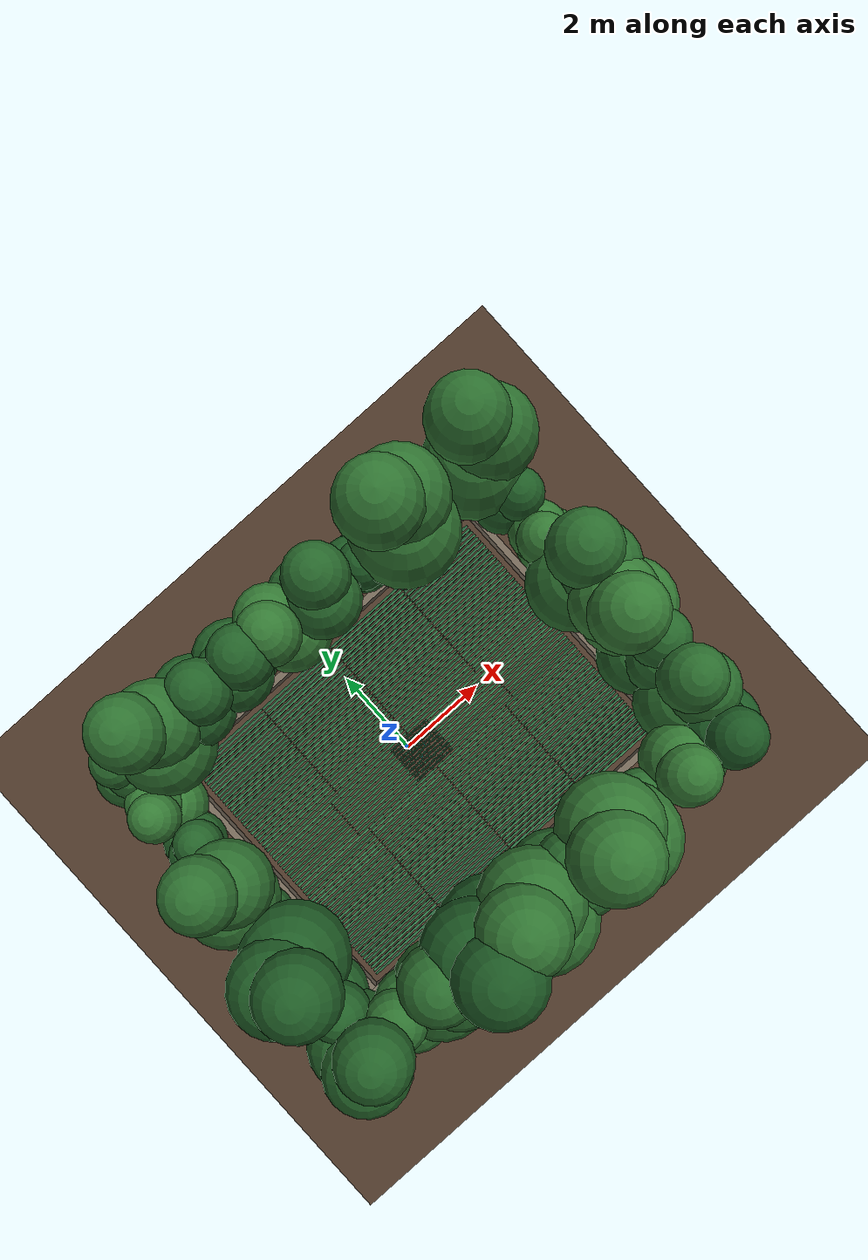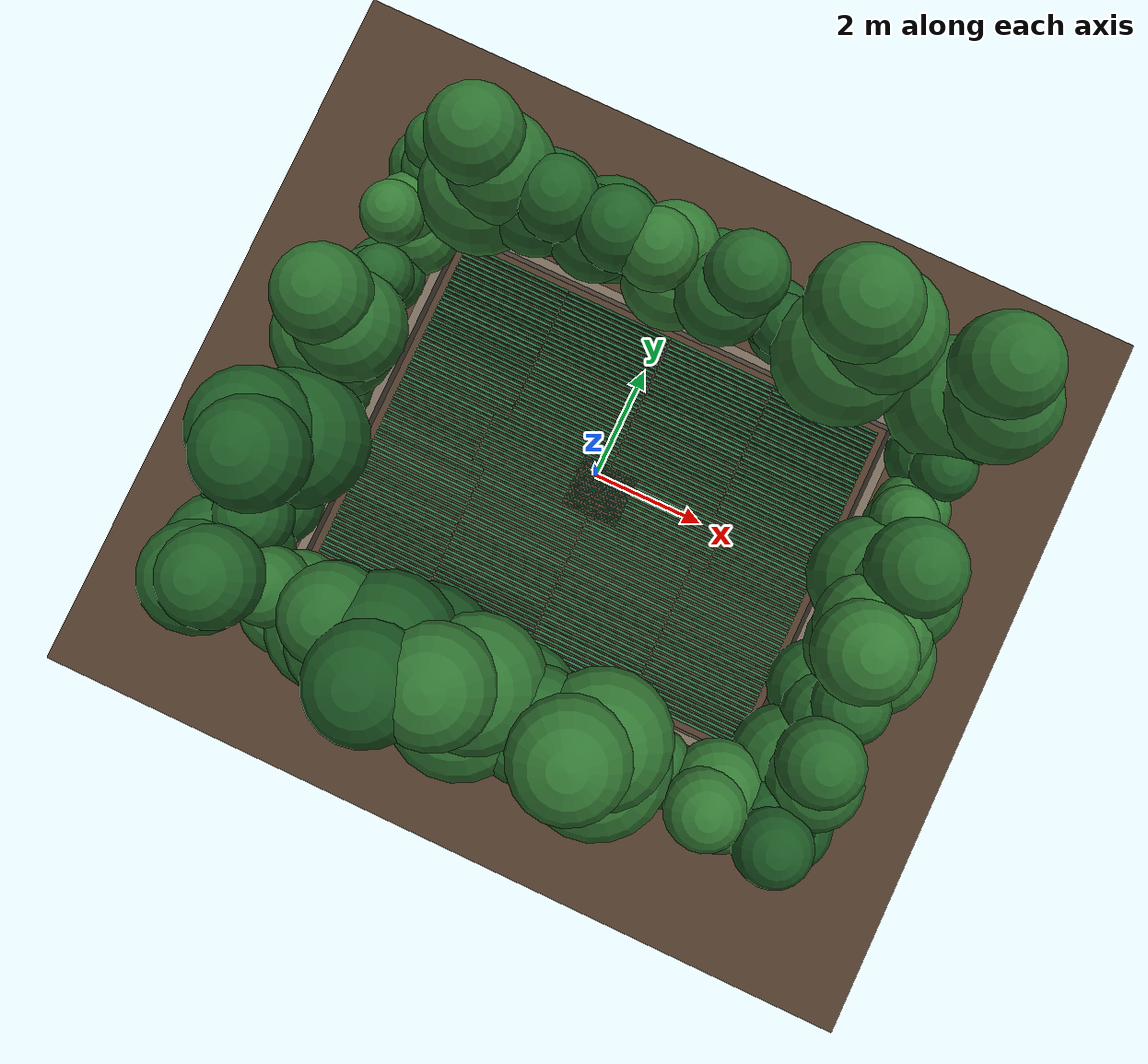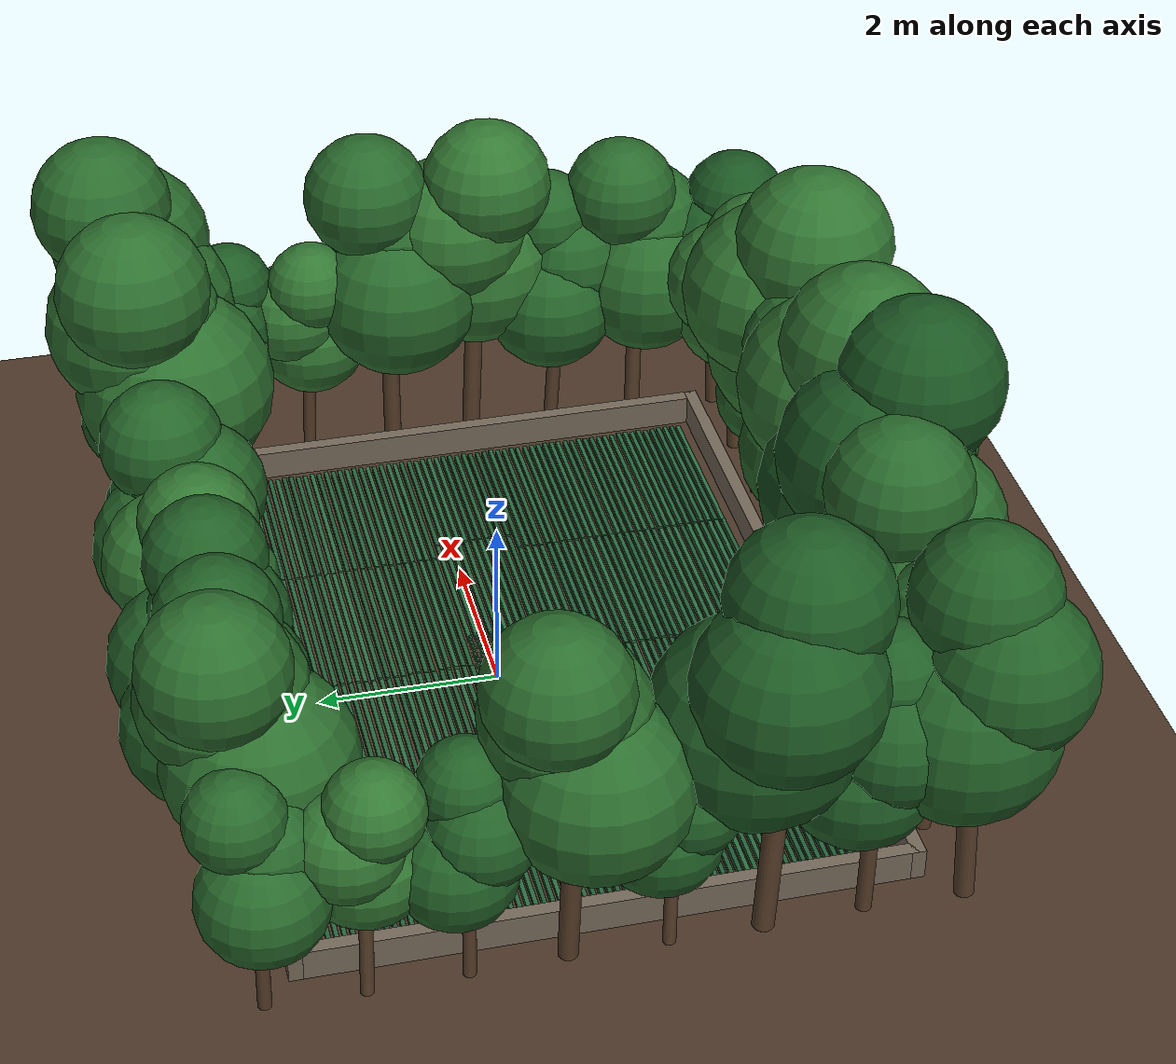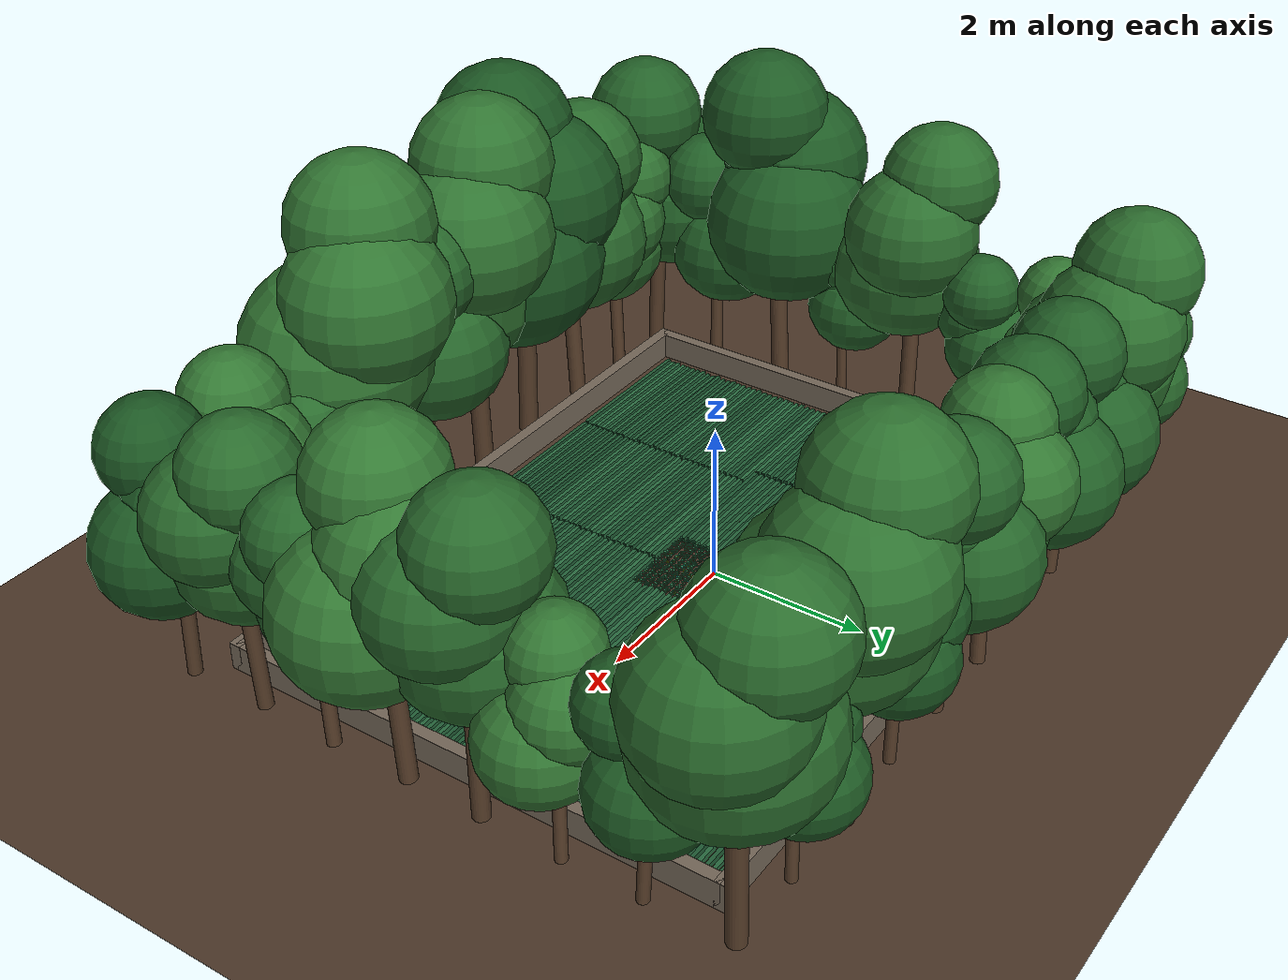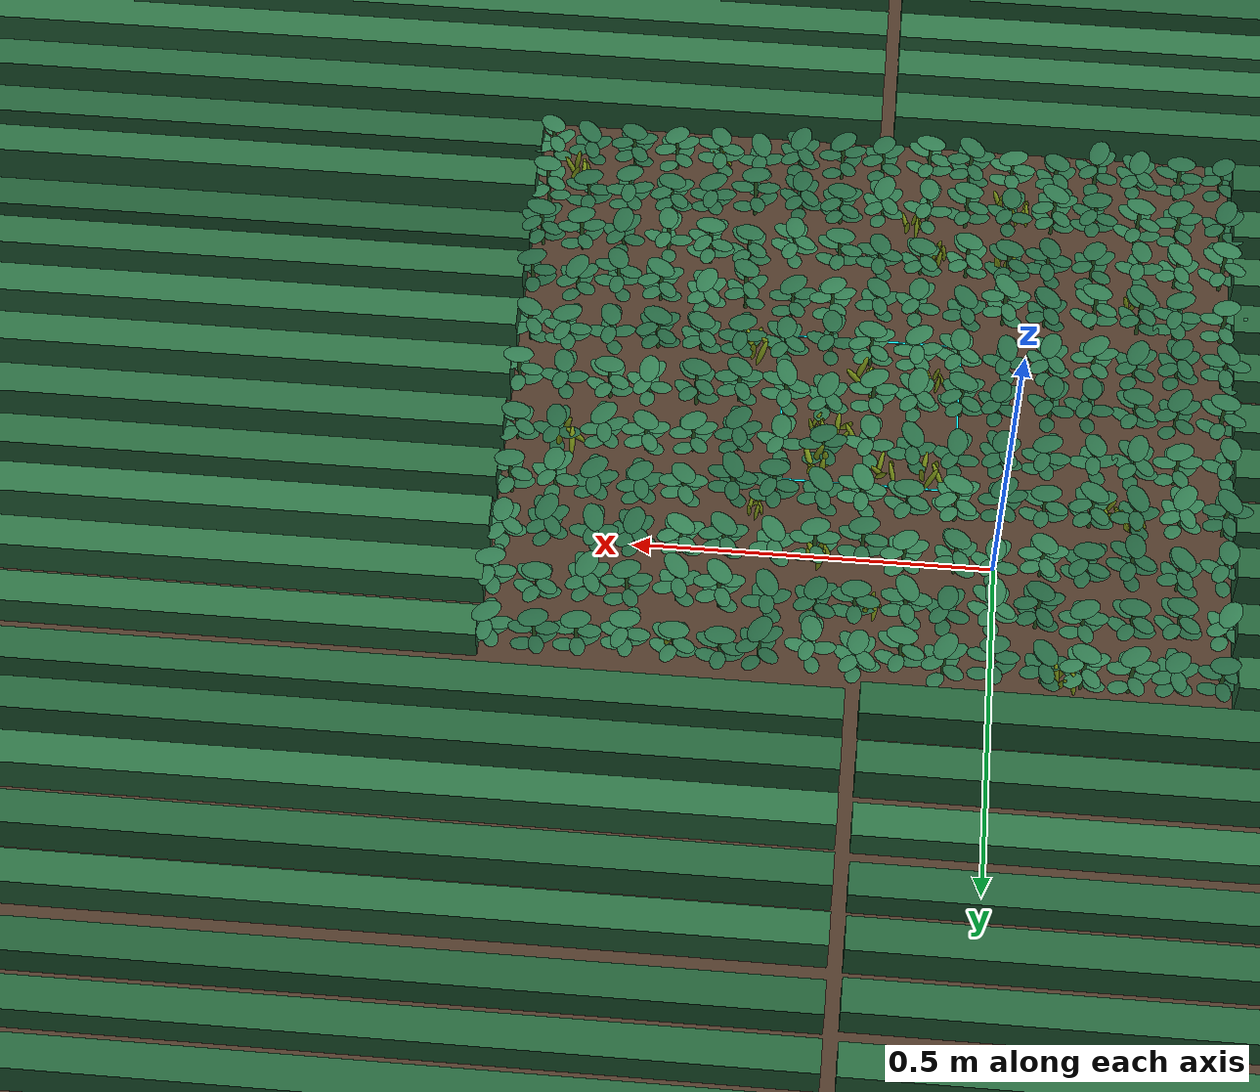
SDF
<?xml version="1.0" ?>
<!-- GENERATED by generate_field.py (seed=42) - do not hand edit -->
<sdf version="1.9">
  <world name="jim_field">

    <physics name="1ms" type="ignored">
      <max_step_size>0.001</max_step_size>
      <real_time_factor>1.0</real_time_factor>
    </physics>

    <plugin filename="gz-sim-physics-system"
            name="gz::sim::systems::Physics"/>
    <plugin filename="gz-sim-user-commands-system"
            name="gz::sim::systems::UserCommands"/>
    <plugin filename="gz-sim-scene-broadcaster-system"
            name="gz::sim::systems::SceneBroadcaster"/>
    <plugin filename="gz-sim-sensors-system"
            name="gz::sim::systems::Sensors">
      <render_engine>ogre2</render_engine>
    </plugin>

    <light type="directional" name="sun">
      <cast_shadows>true</cast_shadows>
      <pose>0 0 10 0 0 0</pose>
      <diffuse>0.95 0.93 0.88 1</diffuse>
      <specular>0.15 0.15 0.15 1</specular>
      <direction>-0.4 0.3 -0.9</direction>
    </light>

    <model name="ground_plane">
      <static>true</static>
      <link name="link">
        <collision name="collision">
          <geometry><plane><normal>0 0 1</normal><size>40 40</size></plane></geometry>
        </collision>
        <visual name="visual">
          <geometry><plane><normal>0 0 1</normal><size>40 40</size></plane></geometry>
          <material>
            <ambient>0.20 0.15 0.11 1</ambient>
            <diffuse>0.30 0.22 0.16 1</diffuse>
            <specular>0.01 0.01 0.01 1</specular>
          </material>
        </visual>
      </link>
    </model>

    <!-- Plants are placed in work_surface coordinates then shifted into
         world coordinates by this offset. -->
    <model name="field">
      <static>true</static>
      <pose>0.1837 -0.2516 0 0 0 0</pose>

    <model name="crop_0">
      <static>true</static>
      <pose>-0.4946 -0.4316 0 0 0 0</pose>
      <link name="link">
        <visual name="stem">
          <pose>0 0 0.0341 0 0 0</pose>
          <geometry><cylinder><radius>0.0025</radius><length>0.0683</length></cylinder></geometry>
          <material>
            <ambient>0.10 0.22 0.09 1</ambient>
            <diffuse>0.20 0.40 0.16 1</diffuse>
            <specular>0.05 0.06 0.05 1</specular>
          </material>
        </visual>
        <visual name="leaflet_0_0">
          <pose>0.0113 0.0136 0.0205 0 -0.300 0.8763</pose>
          <geometry><ellipsoid><radii>0.0170 0.0105 0.0016</radii></ellipsoid></geometry>
          <material>
            <ambient>0.073 0.205 0.114 1</ambient>
            <diffuse>0.136 0.390 0.247 1</diffuse>
            <specular>0.05 0.06 0.05 1</specular>
          </material>
        </visual>
        <visual name="leaflet_0_1">
          <pose>-0.0113 -0.0136 0.0205 0 -0.300 4.0179</pose>
          <geometry><ellipsoid><radii>0.0170 0.0105 0.0016</radii></ellipsoid></geometry>
          <material>
            <ambient>0.073 0.205 0.114 1</ambient>
            <diffuse>0.136 0.390 0.247 1</diffuse>
            <specular>0.05 0.06 0.05 1</specular>
          </material>
        </visual>
        <visual name="leaflet_1_0">
          <pose>-0.0108 0.0140 0.0346 0 -0.200 2.2263</pose>
          <geometry><ellipsoid><radii>0.0170 0.0105 0.0016</radii></ellipsoid></geometry>
          <material>
            <ambient>0.073 0.205 0.114 1</ambient>
            <diffuse>0.136 0.390 0.247 1</diffuse>
            <specular>0.05 0.06 0.05 1</specular>
          </material>
        </visual>
        <visual name="leaflet_1_1">
          <pose>0.0108 -0.0140 0.0346 0 -0.200 5.3679</pose>
          <geometry><ellipsoid><radii>0.0170 0.0105 0.0016</radii></ellipsoid></geometry>
          <material>
            <ambient>0.073 0.205 0.114 1</ambient>
            <diffuse>0.136 0.390 0.247 1</diffuse>
            <specular>0.05 0.06 0.05 1</specular>
          </material>
        </visual>
        <visual name="leaflet_2_0">
          <pose>-0.0160 -0.0074 0.0487 0 -0.100 3.5763</pose>
          <geometry><ellipsoid><radii>0.0170 0.0105 0.0016</radii></ellipsoid></geometry>
          <material>
            <ambient>0.073 0.205 0.114 1</ambient>
            <diffuse>0.136 0.390 0.247 1</diffuse>
            <specular>0.05 0.06 0.05 1</specular>
          </material>
        </visual>
        <visual name="leaflet_2_1">
          <pose>0.0160 0.0074 0.0487 0 -0.100 6.7179</pose>
          <geometry><ellipsoid><radii>0.0170 0.0105 0.0016</radii></ellipsoid></geometry>
          <material>
            <ambient>0.073 0.205 0.114 1</ambient>
            <diffuse>0.136 0.390 0.247 1</diffuse>
            <specular>0.05 0.06 0.05 1</specular>
          </material>
        </visual>
        <visual name="leaflet_terminal">
          <pose>0 0 0.0723 0 -0.12 0.8763</pose>
          <geometry><ellipsoid><radii>0.0215 0.0140 0.0018</radii></ellipsoid></geometry>
          <material>
            <ambient>0.073 0.205 0.114 1</ambient>
            <diffuse>0.136 0.390 0.247 1</diffuse>
            <specular>0.05 0.06 0.05 1</specular>
          </material>
        </visual>
      </link>
    </model>
    <model name="crop_1">
      <static>true</static>
      <pose>-0.4316 -0.4244 0 0 0 0</pose>
      <link name="link">
        <visual name="stem">
          <pose>0 0 0.0389 0 0 0</pose>
          <geometry><cylinder><radius>0.0026</radius><length>0.0777</length></cylinder></geometry>
          <material>
            <ambient>0.10 0.22 0.09 1</ambient>
            <diffuse>0.20 0.40 0.16 1</diffuse>
            <specular>0.05 0.06 0.05 1</specular>
          </material>
        </visual>
        <visual name="leaflet_0_0">
          <pose>0.0178 0.0034 0.0233 0 -0.300 0.1871</pose>
          <geometry><ellipsoid><radii>0.0170 0.0105 0.0016</radii></ellipsoid></geometry>
          <material>
            <ambient>0.077 0.211 0.119 1</ambient>
            <diffuse>0.143 0.402 0.255 1</diffuse>
            <specular>0.05 0.06 0.05 1</specular>
          </material>
        </visual>
        <visual name="leaflet_0_1">
          <pose>-0.0178 -0.0034 0.0233 0 -0.300 3.3287</pose>
          <geometry><ellipsoid><radii>0.0170 0.0105 0.0016</radii></ellipsoid></geometry>
          <material>
            <ambient>0.077 0.211 0.119 1</ambient>
            <diffuse>0.143 0.402 0.255 1</diffuse>
            <specular>0.05 0.06 0.05 1</specular>
          </material>
        </visual>
        <visual name="leaflet_1_0">
          <pose>0.0006 0.0181 0.0394 0 -0.200 1.5371</pose>
          <geometry><ellipsoid><radii>0.0170 0.0105 0.0016</radii></ellipsoid></geometry>
          <material>
            <ambient>0.077 0.211 0.119 1</ambient>
            <diffuse>0.143 0.402 0.255 1</diffuse>
            <specular>0.05 0.06 0.05 1</specular>
          </material>
        </visual>
        <visual name="leaflet_1_1">
          <pose>-0.0006 -0.0181 0.0394 0 -0.200 4.6787</pose>
          <geometry><ellipsoid><radii>0.0170 0.0105 0.0016</radii></ellipsoid></geometry>
          <material>
            <ambient>0.077 0.211 0.119 1</ambient>
            <diffuse>0.143 0.402 0.255 1</diffuse>
            <specular>0.05 0.06 0.05 1</specular>
          </material>
        </visual>
        <visual name="leaflet_2_0">
          <pose>-0.0176 0.0046 0.0554 0 -0.100 2.8871</pose>
          <geometry><ellipsoid><radii>0.0170 0.0105 0.0016</radii></ellipsoid></geometry>
          <material>
            <ambient>0.077 0.211 0.119 1</ambient>
            <diffuse>0.143 0.402 0.255 1</diffuse>
            <specular>0.05 0.06 0.05 1</specular>
          </material>
        </visual>
        <visual name="leaflet_2_1">
          <pose>0.0176 -0.0046 0.0554 0 -0.100 6.0287</pose>
          <geometry><ellipsoid><radii>0.0170 0.0105 0.0016</radii></ellipsoid></geometry>
          <material>
            <ambient>0.077 0.211 0.119 1</ambient>
            <diffuse>0.143 0.402 0.255 1</diffuse>
            <specular>0.05 0.06 0.05 1</specular>
          </material>
        </visual>
        <visual name="leaflet_terminal">
          <pose>0 0 0.0817 0 -0.12 0.1871</pose>
          <geometry><ellipsoid><radii>0.0215 0.0140 0.0018</radii></ellipsoid></geometry>
          <material>
            <ambient>0.077 0.211 0.119 1</ambient>
            <diffuse>0.143 0.402 0.255 1</diffuse>
            <specular>0.05 0.06 0.05 1</specular>
          </material>
        </visual>
      </link>
    </model>
    <model name="crop_2">
      <static>true</static>
      <pose>-0.3719 -0.4316 0 0 0 0</pose>
      <link name="link">
        <visual name="stem">
          <pose>0 0 0.0330 0 0 0</pose>
          <geometry><cylinder><radius>0.0025</radius><length>0.0660</length></cylinder></geometry>
          <material>
            <ambient>0.10 0.22 0.09 1</ambient>
            <diffuse>0.20 0.40 0.16 1</diffuse>
            <specular>0.05 0.06 0.05 1</specular>
          </material>
        </visual>
        <visual name="leaflet_0_0">
          <pose>-0.0053 -0.0167 0.0198 0 -0.300 4.4043</pose>
          <geometry><ellipsoid><radii>0.0170 0.0105 0.0016</radii></ellipsoid></geometry>
          <material>
            <ambient>0.083 0.221 0.127 1</ambient>
            <diffuse>0.155 0.422 0.269 1</diffuse>
            <specular>0.05 0.06 0.05 1</specular>
          </material>
        </visual>
        <visual name="leaflet_0_1">
          <pose>0.0053 0.0167 0.0198 0 -0.300 7.5459</pose>
          <geometry><ellipsoid><radii>0.0170 0.0105 0.0016</radii></ellipsoid></geometry>
          <material>
            <ambient>0.083 0.221 0.127 1</ambient>
            <diffuse>0.155 0.422 0.269 1</diffuse>
            <specular>0.05 0.06 0.05 1</specular>
          </material>
        </visual>
        <visual name="leaflet_1_0">
          <pose>0.0151 -0.0088 0.0300 0 -0.200 5.7543</pose>
          <geometry><ellipsoid><radii>0.0170 0.0105 0.0016</radii></ellipsoid></geometry>
          <material>
            <ambient>0.083 0.221 0.127 1</ambient>
            <diffuse>0.155 0.422 0.269 1</diffuse>
            <specular>0.05 0.06 0.05 1</specular>
          </material>
        </visual>
        <visual name="leaflet_1_1">
          <pose>-0.0151 0.0088 0.0300 0 -0.200 8.8959</pose>
          <geometry><ellipsoid><radii>0.0170 0.0105 0.0016</radii></ellipsoid></geometry>
          <material>
            <ambient>0.083 0.221 0.127 1</ambient>
            <diffuse>0.155 0.422 0.269 1</diffuse>
            <specular>0.05 0.06 0.05 1</specular>
          </material>
        </visual>
        <visual name="leaflet_2_0">
          <pose>0.0119 0.0128 0.0402 0 -0.100 7.1043</pose>
          <geometry><ellipsoid><radii>0.0170 0.0105 0.0016</radii></ellipsoid></geometry>
          <material>
            <ambient>0.083 0.221 0.127 1</ambient>
            <diffuse>0.155 0.422 0.269 1</diffuse>
            <specular>0.05 0.06 0.05 1</specular>
          </material>
        </visual>
        <visual name="leaflet_2_1">
          <pose>-0.0119 -0.0128 0.0402 0 -0.100 10.2459</pose>
          <geometry><ellipsoid><radii>0.0170 0.0105 0.0016</radii></ellipsoid></geometry>
          <material>
            <ambient>0.083 0.221 0.127 1</ambient>
            <diffuse>0.155 0.422 0.269 1</diffuse>
            <specular>0.05 0.06 0.05 1</specular>
          </material>
        </visual>
        <visual name="leaflet_3_0">
          <pose>-0.0099 0.0145 0.0505 0 0.000 8.4543</pose>
          <geometry><ellipsoid><radii>0.0170 0.0105 0.0016</radii></ellipsoid></geometry>
          <material>
            <ambient>0.083 0.221 0.127 1</ambient>
            <diffuse>0.155 0.422 0.269 1</diffuse>
            <specular>0.05 0.06 0.05 1</specular>
          </material>
        </visual>
        <visual name="leaflet_3_1">
          <pose>0.0099 -0.0145 0.0505 0 0.000 11.5959</pose>
          <geometry><ellipsoid><radii>0.0170 0.0105 0.0016</radii></ellipsoid></geometry>
          <material>
            <ambient>0.083 0.221 0.127 1</ambient>
            <diffuse>0.155 0.422 0.269 1</diffuse>
            <specular>0.05 0.06 0.05 1</specular>
          </material>
        </visual>
        <visual name="leaflet_terminal">
          <pose>0 0 0.0700 0 -0.12 4.4043</pose>
          <geometry><ellipsoid><radii>0.0215 0.0140 0.0018</radii></ellipsoid></geometry>
          <material>
            <ambient>0.083 0.221 0.127 1</ambient>
            <diffuse>0.155 0.422 0.269 1</diffuse>
            <specular>0.05 0.06 0.05 1</specular>
          </material>
        </visual>
      </link>
    </model>
    <model name="crop_3">
      <static>true</static>
      <pose>-0.3105 -0.4281 0 0 0 0</pose>
      <link name="link">
        <visual name="stem">
          <pose>0 0 0.0430 0 0 0</pose>
          <geometry><cylinder><radius>0.0027</radius><length>0.0861</length></cylinder></geometry>
          <material>
            <ambient>0.10 0.22 0.09 1</ambient>
            <diffuse>0.20 0.40 0.16 1</diffuse>
            <specular>0.05 0.06 0.05 1</specular>
          </material>
        </visual>
        <visual name="leaflet_0_0">
          <pose>-0.0060 -0.0176 0.0258 0 -0.300 4.3843</pose>
          <geometry><ellipsoid><radii>0.0170 0.0105 0.0016</radii></ellipsoid></geometry>
          <material>
            <ambient>0.080 0.217 0.124 1</ambient>
            <diffuse>0.150 0.414 0.264 1</diffuse>
            <specular>0.05 0.06 0.05 1</specular>
          </material>
        </visual>
        <visual name="leaflet_0_1">
          <pose>0.0060 0.0176 0.0258 0 -0.300 7.5259</pose>
          <geometry><ellipsoid><radii>0.0170 0.0105 0.0016</radii></ellipsoid></geometry>
          <material>
            <ambient>0.080 0.217 0.124 1</ambient>
            <diffuse>0.150 0.414 0.264 1</diffuse>
            <specular>0.05 0.06 0.05 1</specular>
          </material>
        </visual>
        <visual name="leaflet_1_0">
          <pose>0.0159 -0.0097 0.0436 0 -0.200 5.7343</pose>
          <geometry><ellipsoid><radii>0.0170 0.0105 0.0016</radii></ellipsoid></geometry>
          <material>
            <ambient>0.080 0.217 0.124 1</ambient>
            <diffuse>0.150 0.414 0.264 1</diffuse>
            <specular>0.05 0.06 0.05 1</specular>
          </material>
        </visual>
        <visual name="leaflet_1_1">
          <pose>-0.0159 0.0097 0.0436 0 -0.200 8.8759</pose>
          <geometry><ellipsoid><radii>0.0170 0.0105 0.0016</radii></ellipsoid></geometry>
          <material>
            <ambient>0.080 0.217 0.124 1</ambient>
            <diffuse>0.150 0.414 0.264 1</diffuse>
            <specular>0.05 0.06 0.05 1</specular>
          </material>
        </visual>
        <visual name="leaflet_2_0">
          <pose>0.0129 0.0134 0.0614 0 -0.100 7.0843</pose>
          <geometry><ellipsoid><radii>0.0170 0.0105 0.0016</radii></ellipsoid></geometry>
          <material>
            <ambient>0.080 0.217 0.124 1</ambient>
            <diffuse>0.150 0.414 0.264 1</diffuse>
            <specular>0.05 0.06 0.05 1</specular>
          </material>
        </visual>
        <visual name="leaflet_2_1">
          <pose>-0.0129 -0.0134 0.0614 0 -0.100 10.2259</pose>
          <geometry><ellipsoid><radii>0.0170 0.0105 0.0016</radii></ellipsoid></geometry>
          <material>
            <ambient>0.080 0.217 0.124 1</ambient>
            <diffuse>0.150 0.414 0.264 1</diffuse>
            <specular>0.05 0.06 0.05 1</specular>
          </material>
        </visual>
        <visual name="leaflet_terminal">
          <pose>0 0 0.0901 0 -0.12 4.3843</pose>
          <geometry><ellipsoid><radii>0.0215 0.0140 0.0018</radii></ellipsoid></geometry>
          <material>
            <ambient>0.080 0.217 0.124 1</ambient>
            <diffuse>0.150 0.414 0.264 1</diffuse>
            <specular>0.05 0.06 0.05 1</specular>
          </material>
        </visual>
      </link>
    </model>
    <model name="crop_4">
      <static>true</static>
      <pose>-0.2514 -0.4186 0 0 0 0</pose>
      <link name="link">
        <visual name="stem">
          <pose>0 0 0.0350 0 0 0</pose>
          <geometry><cylinder><radius>0.0026</radius><length>0.0701</length></cylinder></geometry>
          <material>
            <ambient>0.10 0.22 0.09 1</ambient>
            <diffuse>0.20 0.40 0.16 1</diffuse>
            <specular>0.05 0.06 0.05 1</specular>
          </material>
        </visual>
        <visual name="leaflet_0_0">
          <pose>-0.0129 0.0122 0.0210 0 -0.300 2.3859</pose>
          <geometry><ellipsoid><radii>0.0170 0.0105 0.0016</radii></ellipsoid></geometry>
          <material>
            <ambient>0.081 0.218 0.124 1</ambient>
            <diffuse>0.152 0.416 0.265 1</diffuse>
            <specular>0.05 0.06 0.05 1</specular>
          </material>
        </visual>
        <visual name="leaflet_0_1">
          <pose>0.0129 -0.0122 0.0210 0 -0.300 5.5275</pose>
          <geometry><ellipsoid><radii>0.0170 0.0105 0.0016</radii></ellipsoid></geometry>
          <material>
            <ambient>0.081 0.218 0.124 1</ambient>
            <diffuse>0.152 0.416 0.265 1</diffuse>
            <specular>0.05 0.06 0.05 1</specular>
          </material>
        </visual>
        <visual name="leaflet_1_0">
          <pose>-0.0147 -0.0099 0.0355 0 -0.200 3.7359</pose>
          <geometry><ellipsoid><radii>0.0170 0.0105 0.0016</radii></ellipsoid></geometry>
          <material>
            <ambient>0.081 0.218 0.124 1</ambient>
            <diffuse>0.152 0.416 0.265 1</diffuse>
            <specular>0.05 0.06 0.05 1</specular>
          </material>
        </visual>
        <visual name="leaflet_1_1">
          <pose>0.0147 0.0099 0.0355 0 -0.200 6.8775</pose>
          <geometry><ellipsoid><radii>0.0170 0.0105 0.0016</radii></ellipsoid></geometry>
          <material>
            <ambient>0.081 0.218 0.124 1</ambient>
            <diffuse>0.152 0.416 0.265 1</diffuse>
            <specular>0.05 0.06 0.05 1</specular>
          </material>
        </visual>
        <visual name="leaflet_2_0">
          <pose>0.0065 -0.0165 0.0500 0 -0.100 5.0859</pose>
          <geometry><ellipsoid><radii>0.0170 0.0105 0.0016</radii></ellipsoid></geometry>
          <material>
            <ambient>0.081 0.218 0.124 1</ambient>
            <diffuse>0.152 0.416 0.265 1</diffuse>
            <specular>0.05 0.06 0.05 1</specular>
          </material>
        </visual>
        <visual name="leaflet_2_1">
          <pose>-0.0065 0.0165 0.0500 0 -0.100 8.2275</pose>
          <geometry><ellipsoid><radii>0.0170 0.0105 0.0016</radii></ellipsoid></geometry>
          <material>
            <ambient>0.081 0.218 0.124 1</ambient>
            <diffuse>0.152 0.416 0.265 1</diffuse>
            <specular>0.05 0.06 0.05 1</specular>
          </material>
        </visual>
        <visual name="leaflet_terminal">
          <pose>0 0 0.0741 0 -0.12 2.3859</pose>
          <geometry><ellipsoid><radii>0.0215 0.0140 0.0018</radii></ellipsoid></geometry>
          <material>
            <ambient>0.081 0.218 0.124 1</ambient>
            <diffuse>0.152 0.416 0.265 1</diffuse>
            <specular>0.05 0.06 0.05 1</specular>
          </material>
        </visual>
      </link>
    </model>
    <model name="crop_5">
      <static>true</static>
      <pose>-0.1876 -0.4283 0 0 0 0</pose>
      <link name="link">
        <visual name="stem">
          <pose>0 0 0.0307 0 0 0</pose>
          <geometry><cylinder><radius>0.0025</radius><length>0.0613</length></cylinder></geometry>
          <material>
            <ambient>0.10 0.22 0.09 1</ambient>
            <diffuse>0.20 0.40 0.16 1</diffuse>
            <specular>0.05 0.06 0.05 1</specular>
          </material>
        </visual>
        <visual name="leaflet_0_0">
          <pose>-0.0168 -0.0039 0.0184 0 -0.300 3.3675</pose>
          <geometry><ellipsoid><radii>0.0170 0.0105 0.0016</radii></ellipsoid></geometry>
          <material>
            <ambient>0.099 0.249 0.149 1</ambient>
            <diffuse>0.188 0.477 0.308 1</diffuse>
            <specular>0.05 0.06 0.05 1</specular>
          </material>
        </visual>
        <visual name="leaflet_0_1">
          <pose>0.0168 0.0039 0.0184 0 -0.300 6.5091</pose>
          <geometry><ellipsoid><radii>0.0170 0.0105 0.0016</radii></ellipsoid></geometry>
          <material>
            <ambient>0.099 0.249 0.149 1</ambient>
            <diffuse>0.188 0.477 0.308 1</diffuse>
            <specular>0.05 0.06 0.05 1</specular>
          </material>
        </visual>
        <visual name="leaflet_1_0">
          <pose>0.0001 -0.0173 0.0311 0 -0.200 4.7175</pose>
          <geometry><ellipsoid><radii>0.0170 0.0105 0.0016</radii></ellipsoid></geometry>
          <material>
            <ambient>0.099 0.249 0.149 1</ambient>
            <diffuse>0.188 0.477 0.308 1</diffuse>
            <specular>0.05 0.06 0.05 1</specular>
          </material>
        </visual>
        <visual name="leaflet_1_1">
          <pose>-0.0001 0.0173 0.0311 0 -0.200 7.8591</pose>
          <geometry><ellipsoid><radii>0.0170 0.0105 0.0016</radii></ellipsoid></geometry>
          <material>
            <ambient>0.099 0.249 0.149 1</ambient>
            <diffuse>0.188 0.477 0.308 1</diffuse>
            <specular>0.05 0.06 0.05 1</specular>
          </material>
        </visual>
        <visual name="leaflet_2_0">
          <pose>0.0169 -0.0037 0.0437 0 -0.100 6.0675</pose>
          <geometry><ellipsoid><radii>0.0170 0.0105 0.0016</radii></ellipsoid></geometry>
          <material>
            <ambient>0.099 0.249 0.149 1</ambient>
            <diffuse>0.188 0.477 0.308 1</diffuse>
            <specular>0.05 0.06 0.05 1</specular>
          </material>
        </visual>
        <visual name="leaflet_2_1">
          <pose>-0.0169 0.0037 0.0437 0 -0.100 9.2091</pose>
          <geometry><ellipsoid><radii>0.0170 0.0105 0.0016</radii></ellipsoid></geometry>
          <material>
            <ambient>0.099 0.249 0.149 1</ambient>
            <diffuse>0.188 0.477 0.308 1</diffuse>
            <specular>0.05 0.06 0.05 1</specular>
          </material>
        </visual>
        <visual name="leaflet_terminal">
          <pose>0 0 0.0653 0 -0.12 3.3675</pose>
          <geometry><ellipsoid><radii>0.0215 0.0140 0.0018</radii></ellipsoid></geometry>
          <material>
            <ambient>0.099 0.249 0.149 1</ambient>
            <diffuse>0.188 0.477 0.308 1</diffuse>
            <specular>0.05 0.06 0.05 1</specular>
          </material>
        </visual>
      </link>
    </model>
    <model name="crop_6">
      <static>true</static>
      <pose>-0.1252 -0.4243 0 0 0 0</pose>
      <link name="link">
        <visual name="stem">
          <pose>0 0 0.0424 0 0 0</pose>
          <geometry><cylinder><radius>0.0027</radius><length>0.0849</length></cylinder></geometry>
          <material>
            <ambient>0.10 0.22 0.09 1</ambient>
            <diffuse>0.20 0.40 0.16 1</diffuse>
            <specular>0.05 0.06 0.05 1</specular>
          </material>
        </visual>
        <visual name="leaflet_0_0">
          <pose>0.0139 -0.0123 0.0255 0 -0.300 5.5606</pose>
          <geometry><ellipsoid><radii>0.0170 0.0105 0.0016</radii></ellipsoid></geometry>
          <material>
            <ambient>0.081 0.218 0.124 1</ambient>
            <diffuse>0.152 0.416 0.265 1</diffuse>
            <specular>0.05 0.06 0.05 1</specular>
          </material>
        </visual>
        <visual name="leaflet_0_1">
          <pose>-0.0139 0.0123 0.0255 0 -0.300 8.7022</pose>
          <geometry><ellipsoid><radii>0.0170 0.0105 0.0016</radii></ellipsoid></geometry>
          <material>
            <ambient>0.081 0.218 0.124 1</ambient>
            <diffuse>0.152 0.416 0.265 1</diffuse>
            <specular>0.05 0.06 0.05 1</specular>
          </material>
        </visual>
        <visual name="leaflet_1_0">
          <pose>0.0150 0.0109 0.0386 0 -0.200 6.9106</pose>
          <geometry><ellipsoid><radii>0.0170 0.0105 0.0016</radii></ellipsoid></geometry>
          <material>
            <ambient>0.081 0.218 0.124 1</ambient>
            <diffuse>0.152 0.416 0.265 1</diffuse>
            <specular>0.05 0.06 0.05 1</specular>
          </material>
        </visual>
        <visual name="leaflet_1_1">
          <pose>-0.0150 -0.0109 0.0386 0 -0.200 10.0522</pose>
          <geometry><ellipsoid><radii>0.0170 0.0105 0.0016</radii></ellipsoid></geometry>
          <material>
            <ambient>0.081 0.218 0.124 1</ambient>
            <diffuse>0.152 0.416 0.265 1</diffuse>
            <specular>0.05 0.06 0.05 1</specular>
          </material>
        </visual>
        <visual name="leaflet_2_0">
          <pose>-0.0073 0.0170 0.0518 0 -0.100 8.2606</pose>
          <geometry><ellipsoid><radii>0.0170 0.0105 0.0016</radii></ellipsoid></geometry>
          <material>
            <ambient>0.081 0.218 0.124 1</ambient>
            <diffuse>0.152 0.416 0.265 1</diffuse>
            <specular>0.05 0.06 0.05 1</specular>
          </material>
        </visual>
        <visual name="leaflet_2_1">
          <pose>0.0073 -0.0170 0.0518 0 -0.100 11.4022</pose>
          <geometry><ellipsoid><radii>0.0170 0.0105 0.0016</radii></ellipsoid></geometry>
          <material>
            <ambient>0.081 0.218 0.124 1</ambient>
            <diffuse>0.152 0.416 0.265 1</diffuse>
            <specular>0.05 0.06 0.05 1</specular>
          </material>
        </visual>
        <visual name="leaflet_3_0">
          <pose>-0.0182 -0.0034 0.0649 0 0.000 9.6106</pose>
          <geometry><ellipsoid><radii>0.0170 0.0105 0.0016</radii></ellipsoid></geometry>
          <material>
            <ambient>0.081 0.218 0.124 1</ambient>
            <diffuse>0.152 0.416 0.265 1</diffuse>
            <specular>0.05 0.06 0.05 1</specular>
          </material>
        </visual>
        <visual name="leaflet_3_1">
          <pose>0.0182 0.0034 0.0649 0 0.000 12.7522</pose>
          <geometry><ellipsoid><radii>0.0170 0.0105 0.0016</radii></ellipsoid></geometry>
          <material>
            <ambient>0.081 0.218 0.124 1</ambient>
            <diffuse>0.152 0.416 0.265 1</diffuse>
            <specular>0.05 0.06 0.05 1</specular>
          </material>
        </visual>
        <visual name="leaflet_terminal">
          <pose>0 0 0.0889 0 -0.12 5.5606</pose>
          <geometry><ellipsoid><radii>0.0215 0.0140 0.0018</radii></ellipsoid></geometry>
          <material>
            <ambient>0.081 0.218 0.124 1</ambient>
            <diffuse>0.152 0.416 0.265 1</diffuse>
            <specular>0.05 0.06 0.05 1</specular>
          </material>
        </visual>
      </link>
    </model>
    <model name="crop_7">
      <static>true</static>
      <pose>-0.0651 -0.4310 0 0 0 0</pose>
      <link name="link">
        <visual name="stem">
          <pose>0 0 0.0399 0 0 0</pose>
          <geometry><cylinder><radius>0.0026</radius><length>0.0798</length></cylinder></geometry>
          <material>
            <ambient>0.10 0.22 0.09 1</ambient>
            <diffuse>0.20 0.40 0.16 1</diffuse>
            <specular>0.05 0.06 0.05 1</specular>
          </material>
        </visual>
        <visual name="leaflet_0_0">
          <pose>0.0182 -0.0017 0.0240 0 -0.300 6.1872</pose>
          <geometry><ellipsoid><radii>0.0170 0.0105 0.0016</radii></ellipsoid></geometry>
          <material>
            <ambient>0.096 0.243 0.144 1</ambient>
            <diffuse>0.181 0.466 0.300 1</diffuse>
            <specular>0.05 0.06 0.05 1</specular>
          </material>
        </visual>
        <visual name="leaflet_0_1">
          <pose>-0.0182 0.0017 0.0240 0 -0.300 9.3288</pose>
          <geometry><ellipsoid><radii>0.0170 0.0105 0.0016</radii></ellipsoid></geometry>
          <material>
            <ambient>0.096 0.243 0.144 1</ambient>
            <diffuse>0.181 0.466 0.300 1</diffuse>
            <specular>0.05 0.06 0.05 1</specular>
          </material>
        </visual>
        <visual name="leaflet_1_0">
          <pose>0.0057 0.0173 0.0405 0 -0.200 7.5372</pose>
          <geometry><ellipsoid><radii>0.0170 0.0105 0.0016</radii></ellipsoid></geometry>
          <material>
            <ambient>0.096 0.243 0.144 1</ambient>
            <diffuse>0.181 0.466 0.300 1</diffuse>
            <specular>0.05 0.06 0.05 1</specular>
          </material>
        </visual>
        <visual name="leaflet_1_1">
          <pose>-0.0057 -0.0173 0.0405 0 -0.200 10.6788</pose>
          <geometry><ellipsoid><radii>0.0170 0.0105 0.0016</radii></ellipsoid></geometry>
          <material>
            <ambient>0.096 0.243 0.144 1</ambient>
            <diffuse>0.181 0.466 0.300 1</diffuse>
            <specular>0.05 0.06 0.05 1</specular>
          </material>
        </visual>
        <visual name="leaflet_2_0">
          <pose>-0.0157 0.0093 0.0570 0 -0.100 8.8872</pose>
          <geometry><ellipsoid><radii>0.0170 0.0105 0.0016</radii></ellipsoid></geometry>
          <material>
            <ambient>0.096 0.243 0.144 1</ambient>
            <diffuse>0.181 0.466 0.300 1</diffuse>
            <specular>0.05 0.06 0.05 1</specular>
          </material>
        </visual>
        <visual name="leaflet_2_1">
          <pose>0.0157 -0.0093 0.0570 0 -0.100 12.0288</pose>
          <geometry><ellipsoid><radii>0.0170 0.0105 0.0016</radii></ellipsoid></geometry>
          <material>
            <ambient>0.096 0.243 0.144 1</ambient>
            <diffuse>0.181 0.466 0.300 1</diffuse>
            <specular>0.05 0.06 0.05 1</specular>
          </material>
        </visual>
        <visual name="leaflet_terminal">
          <pose>0 0 0.0838 0 -0.12 6.1872</pose>
          <geometry><ellipsoid><radii>0.0215 0.0140 0.0018</radii></ellipsoid></geometry>
          <material>
            <ambient>0.096 0.243 0.144 1</ambient>
            <diffuse>0.181 0.466 0.300 1</diffuse>
            <specular>0.05 0.06 0.05 1</specular>
          </material>
        </visual>
      </link>
    </model>
    <model name="crop_8">
      <static>true</static>
      <pose>0.0037 -0.4267 0 0 0 0</pose>
      <link name="link">
        <visual name="stem">
          <pose>0 0 0.0368 0 0 0</pose>
          <geometry><cylinder><radius>0.0026</radius><length>0.0736</length></cylinder></geometry>
          <material>
            <ambient>0.10 0.22 0.09 1</ambient>
            <diffuse>0.20 0.40 0.16 1</diffuse>
            <specular>0.05 0.06 0.05 1</specular>
          </material>
        </visual>
        <visual name="leaflet_0_0">
          <pose>0.0094 0.0153 0.0221 0 -0.300 1.0215</pose>
          <geometry><ellipsoid><radii>0.0170 0.0105 0.0016</radii></ellipsoid></geometry>
          <material>
            <ambient>0.081 0.218 0.124 1</ambient>
            <diffuse>0.151 0.416 0.265 1</diffuse>
            <specular>0.05 0.06 0.05 1</specular>
          </material>
        </visual>
        <visual name="leaflet_0_1">
          <pose>-0.0094 -0.0153 0.0221 0 -0.300 4.1631</pose>
          <geometry><ellipsoid><radii>0.0170 0.0105 0.0016</radii></ellipsoid></geometry>
          <material>
            <ambient>0.081 0.218 0.124 1</ambient>
            <diffuse>0.151 0.416 0.265 1</diffuse>
            <specular>0.05 0.06 0.05 1</specular>
          </material>
        </visual>
        <visual name="leaflet_1_0">
          <pose>-0.0129 0.0125 0.0373 0 -0.200 2.3715</pose>
          <geometry><ellipsoid><radii>0.0170 0.0105 0.0016</radii></ellipsoid></geometry>
          <material>
            <ambient>0.081 0.218 0.124 1</ambient>
            <diffuse>0.151 0.416 0.265 1</diffuse>
            <specular>0.05 0.06 0.05 1</specular>
          </material>
        </visual>
        <visual name="leaflet_1_1">
          <pose>0.0129 -0.0125 0.0373 0 -0.200 5.5131</pose>
          <geometry><ellipsoid><radii>0.0170 0.0105 0.0016</radii></ellipsoid></geometry>
          <material>
            <ambient>0.081 0.218 0.124 1</ambient>
            <diffuse>0.151 0.416 0.265 1</diffuse>
            <specular>0.05 0.06 0.05 1</specular>
          </material>
        </visual>
        <visual name="leaflet_2_0">
          <pose>-0.0150 -0.0098 0.0525 0 -0.100 3.7215</pose>
          <geometry><ellipsoid><radii>0.0170 0.0105 0.0016</radii></ellipsoid></geometry>
          <material>
            <ambient>0.081 0.218 0.124 1</ambient>
            <diffuse>0.151 0.416 0.265 1</diffuse>
            <specular>0.05 0.06 0.05 1</specular>
          </material>
        </visual>
        <visual name="leaflet_2_1">
          <pose>0.0150 0.0098 0.0525 0 -0.100 6.8631</pose>
          <geometry><ellipsoid><radii>0.0170 0.0105 0.0016</radii></ellipsoid></geometry>
          <material>
            <ambient>0.081 0.218 0.124 1</ambient>
            <diffuse>0.151 0.416 0.265 1</diffuse>
            <specular>0.05 0.06 0.05 1</specular>
          </material>
        </visual>
        <visual name="leaflet_terminal">
          <pose>0 0 0.0776 0 -0.12 1.0215</pose>
          <geometry><ellipsoid><radii>0.0215 0.0140 0.0018</radii></ellipsoid></geometry>
          <material>
            <ambient>0.081 0.218 0.124 1</ambient>
            <diffuse>0.151 0.416 0.265 1</diffuse>
            <specular>0.05 0.06 0.05 1</specular>
          </material>
        </visual>
      </link>
    </model>
    <model name="crop_9">
      <static>true</static>
      <pose>0.0637 -0.4222 0 0 0 0</pose>
      <link name="link">
        <visual name="stem">
          <pose>0 0 0.0403 0 0 0</pose>
          <geometry><cylinder><radius>0.0026</radius><length>0.0805</length></cylinder></geometry>
          <material>
            <ambient>0.10 0.22 0.09 1</ambient>
            <diffuse>0.20 0.40 0.16 1</diffuse>
            <specular>0.05 0.06 0.05 1</specular>
          </material>
        </visual>
        <visual name="leaflet_0_0">
          <pose>-0.0142 -0.0116 0.0242 0 -0.300 3.8253</pose>
          <geometry><ellipsoid><radii>0.0170 0.0105 0.0016</radii></ellipsoid></geometry>
          <material>
            <ambient>0.075 0.209 0.117 1</ambient>
            <diffuse>0.140 0.397 0.252 1</diffuse>
            <specular>0.05 0.06 0.05 1</specular>
          </material>
        </visual>
        <visual name="leaflet_0_1">
          <pose>0.0142 0.0116 0.0242 0 -0.300 6.9669</pose>
          <geometry><ellipsoid><radii>0.0170 0.0105 0.0016</radii></ellipsoid></geometry>
          <material>
            <ambient>0.075 0.209 0.117 1</ambient>
            <diffuse>0.140 0.397 0.252 1</diffuse>
            <specular>0.05 0.06 0.05 1</specular>
          </material>
        </visual>
        <visual name="leaflet_1_0">
          <pose>0.0082 -0.0164 0.0408 0 -0.200 5.1753</pose>
          <geometry><ellipsoid><radii>0.0170 0.0105 0.0016</radii></ellipsoid></geometry>
          <material>
            <ambient>0.075 0.209 0.117 1</ambient>
            <diffuse>0.140 0.397 0.252 1</diffuse>
            <specular>0.05 0.06 0.05 1</specular>
          </material>
        </visual>
        <visual name="leaflet_1_1">
          <pose>-0.0082 0.0164 0.0408 0 -0.200 8.3169</pose>
          <geometry><ellipsoid><radii>0.0170 0.0105 0.0016</radii></ellipsoid></geometry>
          <material>
            <ambient>0.075 0.209 0.117 1</ambient>
            <diffuse>0.140 0.397 0.252 1</diffuse>
            <specular>0.05 0.06 0.05 1</specular>
          </material>
        </visual>
        <visual name="leaflet_2_0">
          <pose>0.0178 0.0044 0.0574 0 -0.100 6.5253</pose>
          <geometry><ellipsoid><radii>0.0170 0.0105 0.0016</radii></ellipsoid></geometry>
          <material>
            <ambient>0.075 0.209 0.117 1</ambient>
            <diffuse>0.140 0.397 0.252 1</diffuse>
            <specular>0.05 0.06 0.05 1</specular>
          </material>
        </visual>
        <visual name="leaflet_2_1">
          <pose>-0.0178 -0.0044 0.0574 0 -0.100 9.6669</pose>
          <geometry><ellipsoid><radii>0.0170 0.0105 0.0016</radii></ellipsoid></geometry>
          <material>
            <ambient>0.075 0.209 0.117 1</ambient>
            <diffuse>0.140 0.397 0.252 1</diffuse>
            <specular>0.05 0.06 0.05 1</specular>
          </material>
        </visual>
        <visual name="leaflet_terminal">
          <pose>0 0 0.0845 0 -0.12 3.8253</pose>
          <geometry><ellipsoid><radii>0.0215 0.0140 0.0018</radii></ellipsoid></geometry>
          <material>
            <ambient>0.075 0.209 0.117 1</ambient>
            <diffuse>0.140 0.397 0.252 1</diffuse>
            <specular>0.05 0.06 0.05 1</specular>
          </material>
        </visual>
      </link>
    </model>
    <model name="crop_10">
      <static>true</static>
      <pose>0.1263 -0.4297 0 0 0 0</pose>
      <link name="link">
        <visual name="stem">
          <pose>0 0 0.0357 0 0 0</pose>
          <geometry><cylinder><radius>0.0026</radius><length>0.0714</length></cylinder></geometry>
          <material>
            <ambient>0.10 0.22 0.09 1</ambient>
            <diffuse>0.20 0.40 0.16 1</diffuse>
            <specular>0.05 0.06 0.05 1</specular>
          </material>
        </visual>
        <visual name="leaflet_0_0">
          <pose>-0.0068 -0.0165 0.0214 0 -0.300 4.3217</pose>
          <geometry><ellipsoid><radii>0.0170 0.0105 0.0016</radii></ellipsoid></geometry>
          <material>
            <ambient>0.077 0.211 0.119 1</ambient>
            <diffuse>0.143 0.402 0.255 1</diffuse>
            <specular>0.05 0.06 0.05 1</specular>
          </material>
        </visual>
        <visual name="leaflet_0_1">
          <pose>0.0068 0.0165 0.0214 0 -0.300 7.4632</pose>
          <geometry><ellipsoid><radii>0.0170 0.0105 0.0016</radii></ellipsoid></geometry>
          <material>
            <ambient>0.077 0.211 0.119 1</ambient>
            <diffuse>0.143 0.402 0.255 1</diffuse>
            <specular>0.05 0.06 0.05 1</specular>
          </material>
        </visual>
        <visual name="leaflet_1_0">
          <pose>0.0146 -0.0102 0.0325 0 -0.200 5.6717</pose>
          <geometry><ellipsoid><radii>0.0170 0.0105 0.0016</radii></ellipsoid></geometry>
          <material>
            <ambient>0.077 0.211 0.119 1</ambient>
            <diffuse>0.143 0.402 0.255 1</diffuse>
            <specular>0.05 0.06 0.05 1</specular>
          </material>
        </visual>
        <visual name="leaflet_1_1">
          <pose>-0.0146 0.0102 0.0325 0 -0.200 8.8132</pose>
          <geometry><ellipsoid><radii>0.0170 0.0105 0.0016</radii></ellipsoid></geometry>
          <material>
            <ambient>0.077 0.211 0.119 1</ambient>
            <diffuse>0.143 0.402 0.255 1</diffuse>
            <specular>0.05 0.06 0.05 1</specular>
          </material>
        </visual>
        <visual name="leaflet_2_0">
          <pose>0.0132 0.0120 0.0435 0 -0.100 7.0217</pose>
          <geometry><ellipsoid><radii>0.0170 0.0105 0.0016</radii></ellipsoid></geometry>
          <material>
            <ambient>0.077 0.211 0.119 1</ambient>
            <diffuse>0.143 0.402 0.255 1</diffuse>
            <specular>0.05 0.06 0.05 1</specular>
          </material>
        </visual>
        <visual name="leaflet_2_1">
          <pose>-0.0132 -0.0120 0.0435 0 -0.100 10.1632</pose>
          <geometry><ellipsoid><radii>0.0170 0.0105 0.0016</radii></ellipsoid></geometry>
          <material>
            <ambient>0.077 0.211 0.119 1</ambient>
            <diffuse>0.143 0.402 0.255 1</diffuse>
            <specular>0.05 0.06 0.05 1</specular>
          </material>
        </visual>
        <visual name="leaflet_3_0">
          <pose>-0.0088 0.0155 0.0546 0 0.000 8.3717</pose>
          <geometry><ellipsoid><radii>0.0170 0.0105 0.0016</radii></ellipsoid></geometry>
          <material>
            <ambient>0.077 0.211 0.119 1</ambient>
            <diffuse>0.143 0.402 0.255 1</diffuse>
            <specular>0.05 0.06 0.05 1</specular>
          </material>
        </visual>
        <visual name="leaflet_3_1">
          <pose>0.0088 -0.0155 0.0546 0 0.000 11.5132</pose>
          <geometry><ellipsoid><radii>0.0170 0.0105 0.0016</radii></ellipsoid></geometry>
          <material>
            <ambient>0.077 0.211 0.119 1</ambient>
            <diffuse>0.143 0.402 0.255 1</diffuse>
            <specular>0.05 0.06 0.05 1</specular>
          </material>
        </visual>
        <visual name="leaflet_terminal">
          <pose>0 0 0.0754 0 -0.12 4.3217</pose>
          <geometry><ellipsoid><radii>0.0215 0.0140 0.0018</radii></ellipsoid></geometry>
          <material>
            <ambient>0.077 0.211 0.119 1</ambient>
            <diffuse>0.143 0.402 0.255 1</diffuse>
            <specular>0.05 0.06 0.05 1</specular>
          </material>
        </visual>
      </link>
    </model>
    <model name="crop_11">
      <static>true</static>
      <pose>0.1842 -0.4212 0 0 0 0</pose>
      <link name="link">
        <visual name="stem">
          <pose>0 0 0.0308 0 0 0</pose>
          <geometry><cylinder><radius>0.0025</radius><length>0.0617</length></cylinder></geometry>
          <material>
            <ambient>0.10 0.22 0.09 1</ambient>
            <diffuse>0.20 0.40 0.16 1</diffuse>
            <specular>0.05 0.06 0.05 1</specular>
          </material>
        </visual>
        <visual name="leaflet_0_0">
          <pose>0.0058 -0.0163 0.0185 0 -0.300 5.0557</pose>
          <geometry><ellipsoid><radii>0.0170 0.0105 0.0016</radii></ellipsoid></geometry>
          <material>
            <ambient>0.082 0.220 0.126 1</ambient>
            <diffuse>0.154 0.420 0.268 1</diffuse>
            <specular>0.05 0.06 0.05 1</specular>
          </material>
        </visual>
        <visual name="leaflet_0_1">
          <pose>-0.0058 0.0163 0.0185 0 -0.300 8.1973</pose>
          <geometry><ellipsoid><radii>0.0170 0.0105 0.0016</radii></ellipsoid></geometry>
          <material>
            <ambient>0.082 0.220 0.126 1</ambient>
            <diffuse>0.154 0.420 0.268 1</diffuse>
            <specular>0.05 0.06 0.05 1</specular>
          </material>
        </visual>
        <visual name="leaflet_1_0">
          <pose>0.0172 0.0021 0.0313 0 -0.200 6.4057</pose>
          <geometry><ellipsoid><radii>0.0170 0.0105 0.0016</radii></ellipsoid></geometry>
          <material>
            <ambient>0.082 0.220 0.126 1</ambient>
            <diffuse>0.154 0.420 0.268 1</diffuse>
            <specular>0.05 0.06 0.05 1</specular>
          </material>
        </visual>
        <visual name="leaflet_1_1">
          <pose>-0.0172 -0.0021 0.0313 0 -0.200 9.5473</pose>
          <geometry><ellipsoid><radii>0.0170 0.0105 0.0016</radii></ellipsoid></geometry>
          <material>
            <ambient>0.082 0.220 0.126 1</ambient>
            <diffuse>0.154 0.420 0.268 1</diffuse>
            <specular>0.05 0.06 0.05 1</specular>
          </material>
        </visual>
        <visual name="leaflet_2_0">
          <pose>0.0017 0.0172 0.0440 0 -0.100 7.7557</pose>
          <geometry><ellipsoid><radii>0.0170 0.0105 0.0016</radii></ellipsoid></geometry>
          <material>
            <ambient>0.082 0.220 0.126 1</ambient>
            <diffuse>0.154 0.420 0.268 1</diffuse>
            <specular>0.05 0.06 0.05 1</specular>
          </material>
        </visual>
        <visual name="leaflet_2_1">
          <pose>-0.0017 -0.0172 0.0440 0 -0.100 10.8973</pose>
          <geometry><ellipsoid><radii>0.0170 0.0105 0.0016</radii></ellipsoid></geometry>
          <material>
            <ambient>0.082 0.220 0.126 1</ambient>
            <diffuse>0.154 0.420 0.268 1</diffuse>
            <specular>0.05 0.06 0.05 1</specular>
          </material>
        </visual>
        <visual name="leaflet_terminal">
          <pose>0 0 0.0657 0 -0.12 5.0557</pose>
          <geometry><ellipsoid><radii>0.0215 0.0140 0.0018</radii></ellipsoid></geometry>
          <material>
            <ambient>0.082 0.220 0.126 1</ambient>
            <diffuse>0.154 0.420 0.268 1</diffuse>
            <specular>0.05 0.06 0.05 1</specular>
          </material>
        </visual>
      </link>
    </model>
    <model name="crop_12">
      <static>true</static>
      <pose>0.2437 -0.4192 0 0 0 0</pose>
      <link name="link">
        <visual name="stem">
          <pose>0 0 0.0385 0 0 0</pose>
          <geometry><cylinder><radius>0.0026</radius><length>0.0770</length></cylinder></geometry>
          <material>
            <ambient>0.10 0.22 0.09 1</ambient>
            <diffuse>0.20 0.40 0.16 1</diffuse>
            <specular>0.05 0.06 0.05 1</specular>
          </material>
        </visual>
        <visual name="leaflet_0_0">
          <pose>-0.0071 0.0166 0.0231 0 -0.300 1.9762</pose>
          <geometry><ellipsoid><radii>0.0170 0.0105 0.0016</radii></ellipsoid></geometry>
          <material>
            <ambient>0.090 0.233 0.136 1</ambient>
            <diffuse>0.169 0.446 0.286 1</diffuse>
            <specular>0.05 0.06 0.05 1</specular>
          </material>
        </visual>
        <visual name="leaflet_0_1">
          <pose>0.0071 -0.0166 0.0231 0 -0.300 5.1178</pose>
          <geometry><ellipsoid><radii>0.0170 0.0105 0.0016</radii></ellipsoid></geometry>
          <material>
            <ambient>0.090 0.233 0.136 1</ambient>
            <diffuse>0.169 0.446 0.286 1</diffuse>
            <specular>0.05 0.06 0.05 1</specular>
          </material>
        </visual>
        <visual name="leaflet_1_0">
          <pose>-0.0178 -0.0033 0.0350 0 -0.200 3.3262</pose>
          <geometry><ellipsoid><radii>0.0170 0.0105 0.0016</radii></ellipsoid></geometry>
          <material>
            <ambient>0.090 0.233 0.136 1</ambient>
            <diffuse>0.169 0.446 0.286 1</diffuse>
            <specular>0.05 0.06 0.05 1</specular>
          </material>
        </visual>
        <visual name="leaflet_1_1">
          <pose>0.0178 0.0033 0.0350 0 -0.200 6.4678</pose>
          <geometry><ellipsoid><radii>0.0170 0.0105 0.0016</radii></ellipsoid></geometry>
          <material>
            <ambient>0.090 0.233 0.136 1</ambient>
            <diffuse>0.169 0.446 0.286 1</diffuse>
            <specular>0.05 0.06 0.05 1</specular>
          </material>
        </visual>
        <visual name="leaflet_2_0">
          <pose>-0.0007 -0.0181 0.0470 0 -0.100 4.6762</pose>
          <geometry><ellipsoid><radii>0.0170 0.0105 0.0016</radii></ellipsoid></geometry>
          <material>
            <ambient>0.090 0.233 0.136 1</ambient>
            <diffuse>0.169 0.446 0.286 1</diffuse>
            <specular>0.05 0.06 0.05 1</specular>
          </material>
        </visual>
        <visual name="leaflet_2_1">
          <pose>0.0007 0.0181 0.0470 0 -0.100 7.8178</pose>
          <geometry><ellipsoid><radii>0.0170 0.0105 0.0016</radii></ellipsoid></geometry>
          <material>
            <ambient>0.090 0.233 0.136 1</ambient>
            <diffuse>0.169 0.446 0.286 1</diffuse>
            <specular>0.05 0.06 0.05 1</specular>
          </material>
        </visual>
        <visual name="leaflet_3_0">
          <pose>0.0175 -0.0046 0.0589 0 0.000 6.0262</pose>
          <geometry><ellipsoid><radii>0.0170 0.0105 0.0016</radii></ellipsoid></geometry>
          <material>
            <ambient>0.090 0.233 0.136 1</ambient>
            <diffuse>0.169 0.446 0.286 1</diffuse>
            <specular>0.05 0.06 0.05 1</specular>
          </material>
        </visual>
        <visual name="leaflet_3_1">
          <pose>-0.0175 0.0046 0.0589 0 0.000 9.1678</pose>
          <geometry><ellipsoid><radii>0.0170 0.0105 0.0016</radii></ellipsoid></geometry>
          <material>
            <ambient>0.090 0.233 0.136 1</ambient>
            <diffuse>0.169 0.446 0.286 1</diffuse>
            <specular>0.05 0.06 0.05 1</specular>
          </material>
        </visual>
        <visual name="leaflet_terminal">
          <pose>0 0 0.0810 0 -0.12 1.9762</pose>
          <geometry><ellipsoid><radii>0.0215 0.0140 0.0018</radii></ellipsoid></geometry>
          <material>
            <ambient>0.090 0.233 0.136 1</ambient>
            <diffuse>0.169 0.446 0.286 1</diffuse>
            <specular>0.05 0.06 0.05 1</specular>
          </material>
        </visual>
      </link>
    </model>
    <model name="crop_13">
      <static>true</static>
      <pose>0.3090 -0.4192 0 0 0 0</pose>
      <link name="link">
        <visual name="stem">
          <pose>0 0 0.0369 0 0 0</pose>
          <geometry><cylinder><radius>0.0026</radius><length>0.0738</length></cylinder></geometry>
          <material>
            <ambient>0.10 0.22 0.09 1</ambient>
            <diffuse>0.20 0.40 0.16 1</diffuse>
            <specular>0.05 0.06 0.05 1</specular>
          </material>
        </visual>
        <visual name="leaflet_0_0">
          <pose>0.0115 0.0138 0.0221 0 -0.300 0.8769</pose>
          <geometry><ellipsoid><radii>0.0170 0.0105 0.0016</radii></ellipsoid></geometry>
          <material>
            <ambient>0.092 0.237 0.140 1</ambient>
            <diffuse>0.175 0.454 0.292 1</diffuse>
            <specular>0.05 0.06 0.05 1</specular>
          </material>
        </visual>
        <visual name="leaflet_0_1">
          <pose>-0.0115 -0.0138 0.0221 0 -0.300 4.0185</pose>
          <geometry><ellipsoid><radii>0.0170 0.0105 0.0016</radii></ellipsoid></geometry>
          <material>
            <ambient>0.092 0.237 0.140 1</ambient>
            <diffuse>0.175 0.454 0.292 1</diffuse>
            <specular>0.05 0.06 0.05 1</specular>
          </material>
        </visual>
        <visual name="leaflet_1_0">
          <pose>-0.0109 0.0142 0.0374 0 -0.200 2.2269</pose>
          <geometry><ellipsoid><radii>0.0170 0.0105 0.0016</radii></ellipsoid></geometry>
          <material>
            <ambient>0.092 0.237 0.140 1</ambient>
            <diffuse>0.175 0.454 0.292 1</diffuse>
            <specular>0.05 0.06 0.05 1</specular>
          </material>
        </visual>
        <visual name="leaflet_1_1">
          <pose>0.0109 -0.0142 0.0374 0 -0.200 5.3685</pose>
          <geometry><ellipsoid><radii>0.0170 0.0105 0.0016</radii></ellipsoid></geometry>
          <material>
            <ambient>0.092 0.237 0.140 1</ambient>
            <diffuse>0.175 0.454 0.292 1</diffuse>
            <specular>0.05 0.06 0.05 1</specular>
          </material>
        </visual>
        <visual name="leaflet_2_0">
          <pose>-0.0163 -0.0076 0.0526 0 -0.100 3.5769</pose>
          <geometry><ellipsoid><radii>0.0170 0.0105 0.0016</radii></ellipsoid></geometry>
          <material>
            <ambient>0.092 0.237 0.140 1</ambient>
            <diffuse>0.175 0.454 0.292 1</diffuse>
            <specular>0.05 0.06 0.05 1</specular>
          </material>
        </visual>
        <visual name="leaflet_2_1">
          <pose>0.0163 0.0076 0.0526 0 -0.100 6.7185</pose>
          <geometry><ellipsoid><radii>0.0170 0.0105 0.0016</radii></ellipsoid></geometry>
          <material>
            <ambient>0.092 0.237 0.140 1</ambient>
            <diffuse>0.175 0.454 0.292 1</diffuse>
            <specular>0.05 0.06 0.05 1</specular>
          </material>
        </visual>
        <visual name="leaflet_terminal">
          <pose>0 0 0.0778 0 -0.12 0.8769</pose>
          <geometry><ellipsoid><radii>0.0215 0.0140 0.0018</radii></ellipsoid></geometry>
          <material>
            <ambient>0.092 0.237 0.140 1</ambient>
            <diffuse>0.175 0.454 0.292 1</diffuse>
            <specular>0.05 0.06 0.05 1</specular>
          </material>
        </visual>
      </link>
    </model>
    <model name="crop_14">
      <static>true</static>
      <pose>0.3724 -0.4215 0 0 0 0</pose>
      <link name="link">
        <visual name="stem">
          <pose>0 0 0.0364 0 0 0</pose>
          <geometry><cylinder><radius>0.0026</radius><length>0.0729</length></cylinder></geometry>
          <material>
            <ambient>0.10 0.22 0.09 1</ambient>
            <diffuse>0.20 0.40 0.16 1</diffuse>
            <specular>0.05 0.06 0.05 1</specular>
          </material>
        </visual>
        <visual name="leaflet_0_0">
          <pose>-0.0144 0.0106 0.0219 0 -0.300 2.5082</pose>
          <geometry><ellipsoid><radii>0.0170 0.0105 0.0016</radii></ellipsoid></geometry>
          <material>
            <ambient>0.077 0.211 0.119 1</ambient>
            <diffuse>0.143 0.402 0.255 1</diffuse>
            <specular>0.05 0.06 0.05 1</specular>
          </material>
        </visual>
        <visual name="leaflet_0_1">
          <pose>0.0144 -0.0106 0.0219 0 -0.300 5.6498</pose>
          <geometry><ellipsoid><radii>0.0170 0.0105 0.0016</radii></ellipsoid></geometry>
          <material>
            <ambient>0.077 0.211 0.119 1</ambient>
            <diffuse>0.143 0.402 0.255 1</diffuse>
            <specular>0.05 0.06 0.05 1</specular>
          </material>
        </visual>
        <visual name="leaflet_1_0">
          <pose>-0.0135 -0.0117 0.0331 0 -0.200 3.8582</pose>
          <geometry><ellipsoid><radii>0.0170 0.0105 0.0016</radii></ellipsoid></geometry>
          <material>
            <ambient>0.077 0.211 0.119 1</ambient>
            <diffuse>0.143 0.402 0.255 1</diffuse>
            <specular>0.05 0.06 0.05 1</specular>
          </material>
        </visual>
        <visual name="leaflet_1_1">
          <pose>0.0135 0.0117 0.0331 0 -0.200 6.9998</pose>
          <geometry><ellipsoid><radii>0.0170 0.0105 0.0016</radii></ellipsoid></geometry>
          <material>
            <ambient>0.077 0.211 0.119 1</ambient>
            <diffuse>0.143 0.402 0.255 1</diffuse>
            <specular>0.05 0.06 0.05 1</specular>
          </material>
        </visual>
        <visual name="leaflet_2_0">
          <pose>0.0085 -0.0157 0.0444 0 -0.100 5.2082</pose>
          <geometry><ellipsoid><radii>0.0170 0.0105 0.0016</radii></ellipsoid></geometry>
          <material>
            <ambient>0.077 0.211 0.119 1</ambient>
            <diffuse>0.143 0.402 0.255 1</diffuse>
            <specular>0.05 0.06 0.05 1</specular>
          </material>
        </visual>
        <visual name="leaflet_2_1">
          <pose>-0.0085 0.0157 0.0444 0 -0.100 8.3498</pose>
          <geometry><ellipsoid><radii>0.0170 0.0105 0.0016</radii></ellipsoid></geometry>
          <material>
            <ambient>0.077 0.211 0.119 1</ambient>
            <diffuse>0.143 0.402 0.255 1</diffuse>
            <specular>0.05 0.06 0.05 1</specular>
          </material>
        </visual>
        <visual name="leaflet_3_0">
          <pose>0.0172 0.0049 0.0557 0 0.000 6.5582</pose>
          <geometry><ellipsoid><radii>0.0170 0.0105 0.0016</radii></ellipsoid></geometry>
          <material>
            <ambient>0.077 0.211 0.119 1</ambient>
            <diffuse>0.143 0.402 0.255 1</diffuse>
            <specular>0.05 0.06 0.05 1</specular>
          </material>
        </visual>
        <visual name="leaflet_3_1">
          <pose>-0.0172 -0.0049 0.0557 0 0.000 9.6998</pose>
          <geometry><ellipsoid><radii>0.0170 0.0105 0.0016</radii></ellipsoid></geometry>
          <material>
            <ambient>0.077 0.211 0.119 1</ambient>
            <diffuse>0.143 0.402 0.255 1</diffuse>
            <specular>0.05 0.06 0.05 1</specular>
          </material>
        </visual>
        <visual name="leaflet_terminal">
          <pose>0 0 0.0769 0 -0.12 2.5082</pose>
          <geometry><ellipsoid><radii>0.0215 0.0140 0.0018</radii></ellipsoid></geometry>
          <material>
            <ambient>0.077 0.211 0.119 1</ambient>
            <diffuse>0.143 0.402 0.255 1</diffuse>
            <specular>0.05 0.06 0.05 1</specular>
          </material>
        </visual>
      </link>
    </model>
    <model name="crop_15">
      <static>true</static>
      <pose>0.4390 -0.4249 0 0 0 0</pose>
      <link name="link">
        <visual name="stem">
          <pose>0 0 0.0314 0 0 0</pose>
          <geometry><cylinder><radius>0.0025</radius><length>0.0627</length></cylinder></geometry>
          <material>
            <ambient>0.10 0.22 0.09 1</ambient>
            <diffuse>0.20 0.40 0.16 1</diffuse>
            <specular>0.05 0.06 0.05 1</specular>
          </material>
        </visual>
        <visual name="leaflet_0_0">
          <pose>0.0111 -0.0133 0.0188 0 -0.300 5.4077</pose>
          <geometry><ellipsoid><radii>0.0170 0.0105 0.0016</radii></ellipsoid></geometry>
          <material>
            <ambient>0.075 0.208 0.116 1</ambient>
            <diffuse>0.139 0.395 0.251 1</diffuse>
            <specular>0.05 0.06 0.05 1</specular>
          </material>
        </visual>
        <visual name="leaflet_0_1">
          <pose>-0.0111 0.0133 0.0188 0 -0.300 8.5493</pose>
          <geometry><ellipsoid><radii>0.0170 0.0105 0.0016</radii></ellipsoid></geometry>
          <material>
            <ambient>0.075 0.208 0.116 1</ambient>
            <diffuse>0.139 0.395 0.251 1</diffuse>
            <specular>0.05 0.06 0.05 1</specular>
          </material>
        </visual>
        <visual name="leaflet_1_0">
          <pose>0.0154 0.0079 0.0318 0 -0.200 6.7577</pose>
          <geometry><ellipsoid><radii>0.0170 0.0105 0.0016</radii></ellipsoid></geometry>
          <material>
            <ambient>0.075 0.208 0.116 1</ambient>
            <diffuse>0.139 0.395 0.251 1</diffuse>
            <specular>0.05 0.06 0.05 1</specular>
          </material>
        </visual>
        <visual name="leaflet_1_1">
          <pose>-0.0154 -0.0079 0.0318 0 -0.200 9.8993</pose>
          <geometry><ellipsoid><radii>0.0170 0.0105 0.0016</radii></ellipsoid></geometry>
          <material>
            <ambient>0.075 0.208 0.116 1</ambient>
            <diffuse>0.139 0.395 0.251 1</diffuse>
            <specular>0.05 0.06 0.05 1</specular>
          </material>
        </visual>
        <visual name="leaflet_2_0">
          <pose>-0.0044 0.0168 0.0447 0 -0.100 8.1077</pose>
          <geometry><ellipsoid><radii>0.0170 0.0105 0.0016</radii></ellipsoid></geometry>
          <material>
            <ambient>0.075 0.208 0.116 1</ambient>
            <diffuse>0.139 0.395 0.251 1</diffuse>
            <specular>0.05 0.06 0.05 1</specular>
          </material>
        </visual>
        <visual name="leaflet_2_1">
          <pose>0.0044 -0.0168 0.0447 0 -0.100 11.2493</pose>
          <geometry><ellipsoid><radii>0.0170 0.0105 0.0016</radii></ellipsoid></geometry>
          <material>
            <ambient>0.075 0.208 0.116 1</ambient>
            <diffuse>0.139 0.395 0.251 1</diffuse>
            <specular>0.05 0.06 0.05 1</specular>
          </material>
        </visual>
        <visual name="leaflet_terminal">
          <pose>0 0 0.0667 0 -0.12 5.4077</pose>
          <geometry><ellipsoid><radii>0.0215 0.0140 0.0018</radii></ellipsoid></geometry>
          <material>
            <ambient>0.075 0.208 0.116 1</ambient>
            <diffuse>0.139 0.395 0.251 1</diffuse>
            <specular>0.05 0.06 0.05 1</specular>
          </material>
        </visual>
      </link>
    </model>
    <model name="crop_16">
      <static>true</static>
      <pose>0.4926 -0.4225 0 0 0 0</pose>
      <link name="link">
        <visual name="stem">
          <pose>0 0 0.0389 0 0 0</pose>
          <geometry><cylinder><radius>0.0026</radius><length>0.0779</length></cylinder></geometry>
          <material>
            <ambient>0.10 0.22 0.09 1</ambient>
            <diffuse>0.20 0.40 0.16 1</diffuse>
            <specular>0.05 0.06 0.05 1</specular>
          </material>
        </visual>
        <visual name="leaflet_0_0">
          <pose>-0.0133 0.0123 0.0234 0 -0.300 2.3966</pose>
          <geometry><ellipsoid><radii>0.0170 0.0105 0.0016</radii></ellipsoid></geometry>
          <material>
            <ambient>0.100 0.250 0.150 1</ambient>
            <diffuse>0.190 0.480 0.310 1</diffuse>
            <specular>0.05 0.06 0.05 1</specular>
          </material>
        </visual>
        <visual name="leaflet_0_1">
          <pose>0.0133 -0.0123 0.0234 0 -0.300 5.5382</pose>
          <geometry><ellipsoid><radii>0.0170 0.0105 0.0016</radii></ellipsoid></geometry>
          <material>
            <ambient>0.100 0.250 0.150 1</ambient>
            <diffuse>0.190 0.480 0.310 1</diffuse>
            <specular>0.05 0.06 0.05 1</specular>
          </material>
        </visual>
        <visual name="leaflet_1_0">
          <pose>-0.0149 -0.0103 0.0395 0 -0.200 3.7466</pose>
          <geometry><ellipsoid><radii>0.0170 0.0105 0.0016</radii></ellipsoid></geometry>
          <material>
            <ambient>0.100 0.250 0.150 1</ambient>
            <diffuse>0.190 0.480 0.310 1</diffuse>
            <specular>0.05 0.06 0.05 1</specular>
          </material>
        </visual>
        <visual name="leaflet_1_1">
          <pose>0.0149 0.0103 0.0395 0 -0.200 6.8882</pose>
          <geometry><ellipsoid><radii>0.0170 0.0105 0.0016</radii></ellipsoid></geometry>
          <material>
            <ambient>0.100 0.250 0.150 1</ambient>
            <diffuse>0.190 0.480 0.310 1</diffuse>
            <specular>0.05 0.06 0.05 1</specular>
          </material>
        </visual>
        <visual name="leaflet_2_0">
          <pose>0.0068 -0.0168 0.0556 0 -0.100 5.0966</pose>
          <geometry><ellipsoid><radii>0.0170 0.0105 0.0016</radii></ellipsoid></geometry>
          <material>
            <ambient>0.100 0.250 0.150 1</ambient>
            <diffuse>0.190 0.480 0.310 1</diffuse>
            <specular>0.05 0.06 0.05 1</specular>
          </material>
        </visual>
        <visual name="leaflet_2_1">
          <pose>-0.0068 0.0168 0.0556 0 -0.100 8.2382</pose>
          <geometry><ellipsoid><radii>0.0170 0.0105 0.0016</radii></ellipsoid></geometry>
          <material>
            <ambient>0.100 0.250 0.150 1</ambient>
            <diffuse>0.190 0.480 0.310 1</diffuse>
            <specular>0.05 0.06 0.05 1</specular>
          </material>
        </visual>
        <visual name="leaflet_terminal">
          <pose>0 0 0.0819 0 -0.12 2.3966</pose>
          <geometry><ellipsoid><radii>0.0215 0.0140 0.0018</radii></ellipsoid></geometry>
          <material>
            <ambient>0.100 0.250 0.150 1</ambient>
            <diffuse>0.190 0.480 0.310 1</diffuse>
            <specular>0.05 0.06 0.05 1</specular>
          </material>
        </visual>
      </link>
    </model>
    <model name="crop_17">
      <static>true</static>
      <pose>-0.4957 -0.3334 0 0 0 0</pose>
      <link name="link">
        <visual name="stem">
          <pose>0 0 0.0429 0 0 0</pose>
          <geometry><cylinder><radius>0.0027</radius><length>0.0858</length></cylinder></geometry>
          <material>
            <ambient>0.10 0.22 0.09 1</ambient>
            <diffuse>0.20 0.40 0.16 1</diffuse>
            <specular>0.05 0.06 0.05 1</specular>
          </material>
        </visual>
        <visual name="leaflet_0_0">
          <pose>-0.0079 -0.0168 0.0257 0 -0.300 4.2722</pose>
          <geometry><ellipsoid><radii>0.0170 0.0105 0.0016</radii></ellipsoid></geometry>
          <material>
            <ambient>0.073 0.206 0.115 1</ambient>
            <diffuse>0.137 0.391 0.248 1</diffuse>
            <specular>0.05 0.06 0.05 1</specular>
          </material>
        </visual>
        <visual name="leaflet_0_1">
          <pose>0.0079 0.0168 0.0257 0 -0.300 7.4138</pose>
          <geometry><ellipsoid><radii>0.0170 0.0105 0.0016</radii></ellipsoid></geometry>
          <material>
            <ambient>0.073 0.206 0.115 1</ambient>
            <diffuse>0.137 0.391 0.248 1</diffuse>
            <specular>0.05 0.06 0.05 1</specular>
          </material>
        </visual>
        <visual name="leaflet_1_0">
          <pose>0.0147 -0.0114 0.0435 0 -0.200 5.6222</pose>
          <geometry><ellipsoid><radii>0.0170 0.0105 0.0016</radii></ellipsoid></geometry>
          <material>
            <ambient>0.073 0.206 0.115 1</ambient>
            <diffuse>0.137 0.391 0.248 1</diffuse>
            <specular>0.05 0.06 0.05 1</specular>
          </material>
        </visual>
        <visual name="leaflet_1_1">
          <pose>-0.0147 0.0114 0.0435 0 -0.200 8.7638</pose>
          <geometry><ellipsoid><radii>0.0170 0.0105 0.0016</radii></ellipsoid></geometry>
          <material>
            <ambient>0.073 0.206 0.115 1</ambient>
            <diffuse>0.137 0.391 0.248 1</diffuse>
            <specular>0.05 0.06 0.05 1</specular>
          </material>
        </visual>
        <visual name="leaflet_2_0">
          <pose>0.0143 0.0118 0.0612 0 -0.100 6.9722</pose>
          <geometry><ellipsoid><radii>0.0170 0.0105 0.0016</radii></ellipsoid></geometry>
          <material>
            <ambient>0.073 0.206 0.115 1</ambient>
            <diffuse>0.137 0.391 0.248 1</diffuse>
            <specular>0.05 0.06 0.05 1</specular>
          </material>
        </visual>
        <visual name="leaflet_2_1">
          <pose>-0.0143 -0.0118 0.0612 0 -0.100 10.1138</pose>
          <geometry><ellipsoid><radii>0.0170 0.0105 0.0016</radii></ellipsoid></geometry>
          <material>
            <ambient>0.073 0.206 0.115 1</ambient>
            <diffuse>0.137 0.391 0.248 1</diffuse>
            <specular>0.05 0.06 0.05 1</specular>
          </material>
        </visual>
        <visual name="leaflet_terminal">
          <pose>0 0 0.0898 0 -0.12 4.2722</pose>
          <geometry><ellipsoid><radii>0.0215 0.0140 0.0018</radii></ellipsoid></geometry>
          <material>
            <ambient>0.073 0.206 0.115 1</ambient>
            <diffuse>0.137 0.391 0.248 1</diffuse>
            <specular>0.05 0.06 0.05 1</specular>
          </material>
        </visual>
      </link>
    </model>
    <model name="crop_18">
      <static>true</static>
      <pose>-0.4302 -0.3365 0 0 0 0</pose>
      <link name="link">
        <visual name="stem">
          <pose>0 0 0.0415 0 0 0</pose>
          <geometry><cylinder><radius>0.0027</radius><length>0.0831</length></cylinder></geometry>
          <material>
            <ambient>0.10 0.22 0.09 1</ambient>
            <diffuse>0.20 0.40 0.16 1</diffuse>
            <specular>0.05 0.06 0.05 1</specular>
          </material>
        </visual>
        <visual name="leaflet_0_0">
          <pose>0.0141 0.0119 0.0249 0 -0.300 0.7005</pose>
          <geometry><ellipsoid><radii>0.0170 0.0105 0.0016</radii></ellipsoid></geometry>
          <material>
            <ambient>0.083 0.222 0.127 1</ambient>
            <diffuse>0.156 0.423 0.270 1</diffuse>
            <specular>0.05 0.06 0.05 1</specular>
          </material>
        </visual>
        <visual name="leaflet_0_1">
          <pose>-0.0141 -0.0119 0.0249 0 -0.300 3.8421</pose>
          <geometry><ellipsoid><radii>0.0170 0.0105 0.0016</radii></ellipsoid></geometry>
          <material>
            <ambient>0.083 0.222 0.127 1</ambient>
            <diffuse>0.156 0.423 0.270 1</diffuse>
            <specular>0.05 0.06 0.05 1</specular>
          </material>
        </visual>
        <visual name="leaflet_1_0">
          <pose>-0.0085 0.0163 0.0421 0 -0.200 2.0505</pose>
          <geometry><ellipsoid><radii>0.0170 0.0105 0.0016</radii></ellipsoid></geometry>
          <material>
            <ambient>0.083 0.222 0.127 1</ambient>
            <diffuse>0.156 0.423 0.270 1</diffuse>
            <specular>0.05 0.06 0.05 1</specular>
          </material>
        </visual>
        <visual name="leaflet_1_1">
          <pose>0.0085 -0.0163 0.0421 0 -0.200 5.1921</pose>
          <geometry><ellipsoid><radii>0.0170 0.0105 0.0016</radii></ellipsoid></geometry>
          <material>
            <ambient>0.083 0.222 0.127 1</ambient>
            <diffuse>0.156 0.423 0.270 1</diffuse>
            <specular>0.05 0.06 0.05 1</specular>
          </material>
        </visual>
        <visual name="leaflet_2_0">
          <pose>-0.0178 -0.0047 0.0592 0 -0.100 3.4005</pose>
          <geometry><ellipsoid><radii>0.0170 0.0105 0.0016</radii></ellipsoid></geometry>
          <material>
            <ambient>0.083 0.222 0.127 1</ambient>
            <diffuse>0.156 0.423 0.270 1</diffuse>
            <specular>0.05 0.06 0.05 1</specular>
          </material>
        </visual>
        <visual name="leaflet_2_1">
          <pose>0.0178 0.0047 0.0592 0 -0.100 6.5421</pose>
          <geometry><ellipsoid><radii>0.0170 0.0105 0.0016</radii></ellipsoid></geometry>
          <material>
            <ambient>0.083 0.222 0.127 1</ambient>
            <diffuse>0.156 0.423 0.270 1</diffuse>
            <specular>0.05 0.06 0.05 1</specular>
          </material>
        </visual>
        <visual name="leaflet_terminal">
          <pose>0 0 0.0871 0 -0.12 0.7005</pose>
          <geometry><ellipsoid><radii>0.0215 0.0140 0.0018</radii></ellipsoid></geometry>
          <material>
            <ambient>0.083 0.222 0.127 1</ambient>
            <diffuse>0.156 0.423 0.270 1</diffuse>
            <specular>0.05 0.06 0.05 1</specular>
          </material>
        </visual>
      </link>
    </model>
    <model name="crop_19">
      <static>true</static>
      <pose>-0.3725 -0.3336 0 0 0 0</pose>
      <link name="link">
        <visual name="stem">
          <pose>0 0 0.0431 0 0 0</pose>
          <geometry><cylinder><radius>0.0027</radius><length>0.0863</length></cylinder></geometry>
          <material>
            <ambient>0.10 0.22 0.09 1</ambient>
            <diffuse>0.20 0.40 0.16 1</diffuse>
            <specular>0.05 0.06 0.05 1</specular>
          </material>
        </visual>
        <visual name="leaflet_0_0">
          <pose>0.0183 -0.0033 0.0259 0 -0.300 6.1035</pose>
          <geometry><ellipsoid><radii>0.0170 0.0105 0.0016</radii></ellipsoid></geometry>
          <material>
            <ambient>0.093 0.238 0.140 1</ambient>
            <diffuse>0.176 0.456 0.293 1</diffuse>
            <specular>0.05 0.06 0.05 1</specular>
          </material>
        </visual>
        <visual name="leaflet_0_1">
          <pose>-0.0183 0.0033 0.0259 0 -0.300 9.2450</pose>
          <geometry><ellipsoid><radii>0.0170 0.0105 0.0016</radii></ellipsoid></geometry>
          <material>
            <ambient>0.093 0.238 0.140 1</ambient>
            <diffuse>0.176 0.456 0.293 1</diffuse>
            <specular>0.05 0.06 0.05 1</specular>
          </material>
        </visual>
        <visual name="leaflet_1_0">
          <pose>0.0073 0.0171 0.0437 0 -0.200 7.4535</pose>
          <geometry><ellipsoid><radii>0.0170 0.0105 0.0016</radii></ellipsoid></geometry>
          <material>
            <ambient>0.093 0.238 0.140 1</ambient>
            <diffuse>0.176 0.456 0.293 1</diffuse>
            <specular>0.05 0.06 0.05 1</specular>
          </material>
        </visual>
        <visual name="leaflet_1_1">
          <pose>-0.0073 -0.0171 0.0437 0 -0.200 10.5950</pose>
          <geometry><ellipsoid><radii>0.0170 0.0105 0.0016</radii></ellipsoid></geometry>
          <material>
            <ambient>0.093 0.238 0.140 1</ambient>
            <diffuse>0.176 0.456 0.293 1</diffuse>
            <specular>0.05 0.06 0.05 1</specular>
          </material>
        </visual>
        <visual name="leaflet_2_0">
          <pose>-0.0151 0.0108 0.0615 0 -0.100 8.8035</pose>
          <geometry><ellipsoid><radii>0.0170 0.0105 0.0016</radii></ellipsoid></geometry>
          <material>
            <ambient>0.093 0.238 0.140 1</ambient>
            <diffuse>0.176 0.456 0.293 1</diffuse>
            <specular>0.05 0.06 0.05 1</specular>
          </material>
        </visual>
        <visual name="leaflet_2_1">
          <pose>0.0151 -0.0108 0.0615 0 -0.100 11.9450</pose>
          <geometry><ellipsoid><radii>0.0170 0.0105 0.0016</radii></ellipsoid></geometry>
          <material>
            <ambient>0.093 0.238 0.140 1</ambient>
            <diffuse>0.176 0.456 0.293 1</diffuse>
            <specular>0.05 0.06 0.05 1</specular>
          </material>
        </visual>
        <visual name="leaflet_terminal">
          <pose>0 0 0.0903 0 -0.12 6.1035</pose>
          <geometry><ellipsoid><radii>0.0215 0.0140 0.0018</radii></ellipsoid></geometry>
          <material>
            <ambient>0.093 0.238 0.140 1</ambient>
            <diffuse>0.176 0.456 0.293 1</diffuse>
            <specular>0.05 0.06 0.05 1</specular>
          </material>
        </visual>
      </link>
    </model>
    <model name="crop_20">
      <static>true</static>
      <pose>-0.3099 -0.3455 0 0 0 0</pose>
      <link name="link">
        <visual name="stem">
          <pose>0 0 0.0394 0 0 0</pose>
          <geometry><cylinder><radius>0.0026</radius><length>0.0788</length></cylinder></geometry>
          <material>
            <ambient>0.10 0.22 0.09 1</ambient>
            <diffuse>0.20 0.40 0.16 1</diffuse>
            <specular>0.05 0.06 0.05 1</specular>
          </material>
        </visual>
        <visual name="leaflet_0_0">
          <pose>-0.0182 -0.0008 0.0236 0 -0.300 3.1881</pose>
          <geometry><ellipsoid><radii>0.0170 0.0105 0.0016</radii></ellipsoid></geometry>
          <material>
            <ambient>0.076 0.210 0.118 1</ambient>
            <diffuse>0.142 0.400 0.254 1</diffuse>
            <specular>0.05 0.06 0.05 1</specular>
          </material>
        </visual>
        <visual name="leaflet_0_1">
          <pose>0.0182 0.0008 0.0236 0 -0.300 6.3297</pose>
          <geometry><ellipsoid><radii>0.0170 0.0105 0.0016</radii></ellipsoid></geometry>
          <material>
            <ambient>0.076 0.210 0.118 1</ambient>
            <diffuse>0.142 0.400 0.254 1</diffuse>
            <specular>0.05 0.06 0.05 1</specular>
          </material>
        </visual>
        <visual name="leaflet_1_0">
          <pose>-0.0032 -0.0179 0.0358 0 -0.200 4.5381</pose>
          <geometry><ellipsoid><radii>0.0170 0.0105 0.0016</radii></ellipsoid></geometry>
          <material>
            <ambient>0.076 0.210 0.118 1</ambient>
            <diffuse>0.142 0.400 0.254 1</diffuse>
            <specular>0.05 0.06 0.05 1</specular>
          </material>
        </visual>
        <visual name="leaflet_1_1">
          <pose>0.0032 0.0179 0.0358 0 -0.200 7.6797</pose>
          <geometry><ellipsoid><radii>0.0170 0.0105 0.0016</radii></ellipsoid></geometry>
          <material>
            <ambient>0.076 0.210 0.118 1</ambient>
            <diffuse>0.142 0.400 0.254 1</diffuse>
            <specular>0.05 0.06 0.05 1</specular>
          </material>
        </visual>
        <visual name="leaflet_2_0">
          <pose>0.0168 -0.0070 0.0480 0 -0.100 5.8881</pose>
          <geometry><ellipsoid><radii>0.0170 0.0105 0.0016</radii></ellipsoid></geometry>
          <material>
            <ambient>0.076 0.210 0.118 1</ambient>
            <diffuse>0.142 0.400 0.254 1</diffuse>
            <specular>0.05 0.06 0.05 1</specular>
          </material>
        </visual>
        <visual name="leaflet_2_1">
          <pose>-0.0168 0.0070 0.0480 0 -0.100 9.0297</pose>
          <geometry><ellipsoid><radii>0.0170 0.0105 0.0016</radii></ellipsoid></geometry>
          <material>
            <ambient>0.076 0.210 0.118 1</ambient>
            <diffuse>0.142 0.400 0.254 1</diffuse>
            <specular>0.05 0.06 0.05 1</specular>
          </material>
        </visual>
        <visual name="leaflet_3_0">
          <pose>0.0105 0.0149 0.0603 0 0.000 7.2381</pose>
          <geometry><ellipsoid><radii>0.0170 0.0105 0.0016</radii></ellipsoid></geometry>
          <material>
            <ambient>0.076 0.210 0.118 1</ambient>
            <diffuse>0.142 0.400 0.254 1</diffuse>
            <specular>0.05 0.06 0.05 1</specular>
          </material>
        </visual>
        <visual name="leaflet_3_1">
          <pose>-0.0105 -0.0149 0.0603 0 0.000 10.3797</pose>
          <geometry><ellipsoid><radii>0.0170 0.0105 0.0016</radii></ellipsoid></geometry>
          <material>
            <ambient>0.076 0.210 0.118 1</ambient>
            <diffuse>0.142 0.400 0.254 1</diffuse>
            <specular>0.05 0.06 0.05 1</specular>
          </material>
        </visual>
        <visual name="leaflet_terminal">
          <pose>0 0 0.0828 0 -0.12 3.1881</pose>
          <geometry><ellipsoid><radii>0.0215 0.0140 0.0018</radii></ellipsoid></geometry>
          <material>
            <ambient>0.076 0.210 0.118 1</ambient>
            <diffuse>0.142 0.400 0.254 1</diffuse>
            <specular>0.05 0.06 0.05 1</specular>
          </material>
        </visual>
      </link>
    </model>
    <model name="crop_21">
      <static>true</static>
      <pose>-0.2493 -0.3447 0 0 0 0</pose>
      <link name="link">
        <visual name="stem">
          <pose>0 0 0.0443 0 0 0</pose>
          <geometry><cylinder><radius>0.0027</radius><length>0.0886</length></cylinder></geometry>
          <material>
            <ambient>0.10 0.22 0.09 1</ambient>
            <diffuse>0.20 0.40 0.16 1</diffuse>
            <specular>0.05 0.06 0.05 1</specular>
          </material>
        </visual>
        <visual name="leaflet_0_0">
          <pose>0.0163 -0.0092 0.0266 0 -0.300 5.7681</pose>
          <geometry><ellipsoid><radii>0.0170 0.0105 0.0016</radii></ellipsoid></geometry>
          <material>
            <ambient>0.088 0.230 0.134 1</ambient>
            <diffuse>0.166 0.440 0.282 1</diffuse>
            <specular>0.05 0.06 0.05 1</specular>
          </material>
        </visual>
        <visual name="leaflet_0_1">
          <pose>-0.0163 0.0092 0.0266 0 -0.300 8.9097</pose>
          <geometry><ellipsoid><radii>0.0170 0.0105 0.0016</radii></ellipsoid></geometry>
          <material>
            <ambient>0.088 0.230 0.134 1</ambient>
            <diffuse>0.166 0.440 0.282 1</diffuse>
            <specular>0.05 0.06 0.05 1</specular>
          </material>
        </visual>
        <visual name="leaflet_1_0">
          <pose>0.0126 0.0139 0.0403 0 -0.200 7.1181</pose>
          <geometry><ellipsoid><radii>0.0170 0.0105 0.0016</radii></ellipsoid></geometry>
          <material>
            <ambient>0.088 0.230 0.134 1</ambient>
            <diffuse>0.166 0.440 0.282 1</diffuse>
            <specular>0.05 0.06 0.05 1</specular>
          </material>
        </visual>
        <visual name="leaflet_1_1">
          <pose>-0.0126 -0.0139 0.0403 0 -0.200 10.2597</pose>
          <geometry><ellipsoid><radii>0.0170 0.0105 0.0016</radii></ellipsoid></geometry>
          <material>
            <ambient>0.088 0.230 0.134 1</ambient>
            <diffuse>0.166 0.440 0.282 1</diffuse>
            <specular>0.05 0.06 0.05 1</specular>
          </material>
        </visual>
        <visual name="leaflet_2_0">
          <pose>-0.0108 0.0153 0.0540 0 -0.100 8.4681</pose>
          <geometry><ellipsoid><radii>0.0170 0.0105 0.0016</radii></ellipsoid></geometry>
          <material>
            <ambient>0.088 0.230 0.134 1</ambient>
            <diffuse>0.166 0.440 0.282 1</diffuse>
            <specular>0.05 0.06 0.05 1</specular>
          </material>
        </visual>
        <visual name="leaflet_2_1">
          <pose>0.0108 -0.0153 0.0540 0 -0.100 11.6097</pose>
          <geometry><ellipsoid><radii>0.0170 0.0105 0.0016</radii></ellipsoid></geometry>
          <material>
            <ambient>0.088 0.230 0.134 1</ambient>
            <diffuse>0.166 0.440 0.282 1</diffuse>
            <specular>0.05 0.06 0.05 1</specular>
          </material>
        </visual>
        <visual name="leaflet_3_0">
          <pose>-0.0173 -0.0072 0.0678 0 0.000 9.8181</pose>
          <geometry><ellipsoid><radii>0.0170 0.0105 0.0016</radii></ellipsoid></geometry>
          <material>
            <ambient>0.088 0.230 0.134 1</ambient>
            <diffuse>0.166 0.440 0.282 1</diffuse>
            <specular>0.05 0.06 0.05 1</specular>
          </material>
        </visual>
        <visual name="leaflet_3_1">
          <pose>0.0173 0.0072 0.0678 0 0.000 12.9597</pose>
          <geometry><ellipsoid><radii>0.0170 0.0105 0.0016</radii></ellipsoid></geometry>
          <material>
            <ambient>0.088 0.230 0.134 1</ambient>
            <diffuse>0.166 0.440 0.282 1</diffuse>
            <specular>0.05 0.06 0.05 1</specular>
          </material>
        </visual>
        <visual name="leaflet_terminal">
          <pose>0 0 0.0926 0 -0.12 5.7681</pose>
          <geometry><ellipsoid><radii>0.0215 0.0140 0.0018</radii></ellipsoid></geometry>
          <material>
            <ambient>0.088 0.230 0.134 1</ambient>
            <diffuse>0.166 0.440 0.282 1</diffuse>
            <specular>0.05 0.06 0.05 1</specular>
          </material>
        </visual>
      </link>
    </model>
    <model name="crop_22">
      <static>true</static>
      <pose>-0.1861 -0.3454 0 0 0 0</pose>
      <link name="link">
        <visual name="stem">
          <pose>0 0 0.0354 0 0 0</pose>
          <geometry><cylinder><radius>0.0026</radius><length>0.0709</length></cylinder></geometry>
          <material>
            <ambient>0.10 0.22 0.09 1</ambient>
            <diffuse>0.20 0.40 0.16 1</diffuse>
            <specular>0.05 0.06 0.05 1</specular>
          </material>
        </visual>
        <visual name="leaflet_0_0">
          <pose>0.0012 0.0177 0.0213 0 -0.300 1.5038</pose>
          <geometry><ellipsoid><radii>0.0170 0.0105 0.0016</radii></ellipsoid></geometry>
          <material>
            <ambient>0.077 0.212 0.120 1</ambient>
            <diffuse>0.144 0.404 0.257 1</diffuse>
            <specular>0.05 0.06 0.05 1</specular>
          </material>
        </visual>
        <visual name="leaflet_0_1">
          <pose>-0.0012 -0.0177 0.0213 0 -0.300 4.6454</pose>
          <geometry><ellipsoid><radii>0.0170 0.0105 0.0016</radii></ellipsoid></geometry>
          <material>
            <ambient>0.077 0.212 0.120 1</ambient>
            <diffuse>0.144 0.404 0.257 1</diffuse>
            <specular>0.05 0.06 0.05 1</specular>
          </material>
        </visual>
        <visual name="leaflet_1_0">
          <pose>-0.0170 0.0050 0.0359 0 -0.200 2.8538</pose>
          <geometry><ellipsoid><radii>0.0170 0.0105 0.0016</radii></ellipsoid></geometry>
          <material>
            <ambient>0.077 0.212 0.120 1</ambient>
            <diffuse>0.144 0.404 0.257 1</diffuse>
            <specular>0.05 0.06 0.05 1</specular>
          </material>
        </visual>
        <visual name="leaflet_1_1">
          <pose>0.0170 -0.0050 0.0359 0 -0.200 5.9954</pose>
          <geometry><ellipsoid><radii>0.0170 0.0105 0.0016</radii></ellipsoid></geometry>
          <material>
            <ambient>0.077 0.212 0.120 1</ambient>
            <diffuse>0.144 0.404 0.257 1</diffuse>
            <specular>0.05 0.06 0.05 1</specular>
          </material>
        </visual>
        <visual name="leaflet_2_0">
          <pose>-0.0087 -0.0155 0.0506 0 -0.100 4.2038</pose>
          <geometry><ellipsoid><radii>0.0170 0.0105 0.0016</radii></ellipsoid></geometry>
          <material>
            <ambient>0.077 0.212 0.120 1</ambient>
            <diffuse>0.144 0.404 0.257 1</diffuse>
            <specular>0.05 0.06 0.05 1</specular>
          </material>
        </visual>
        <visual name="leaflet_2_1">
          <pose>0.0087 0.0155 0.0506 0 -0.100 7.3454</pose>
          <geometry><ellipsoid><radii>0.0170 0.0105 0.0016</radii></ellipsoid></geometry>
          <material>
            <ambient>0.077 0.212 0.120 1</ambient>
            <diffuse>0.144 0.404 0.257 1</diffuse>
            <specular>0.05 0.06 0.05 1</specular>
          </material>
        </visual>
        <visual name="leaflet_terminal">
          <pose>0 0 0.0749 0 -0.12 1.5038</pose>
          <geometry><ellipsoid><radii>0.0215 0.0140 0.0018</radii></ellipsoid></geometry>
          <material>
            <ambient>0.077 0.212 0.120 1</ambient>
            <diffuse>0.144 0.404 0.257 1</diffuse>
            <specular>0.05 0.06 0.05 1</specular>
          </material>
        </visual>
      </link>
    </model>
    <model name="crop_23">
      <static>true</static>
      <pose>-0.1233 -0.3459 0 0 0 0</pose>
      <link name="link">
        <visual name="stem">
          <pose>0 0 0.0410 0 0 0</pose>
          <geometry><cylinder><radius>0.0027</radius><length>0.0820</length></cylinder></geometry>
          <material>
            <ambient>0.10 0.22 0.09 1</ambient>
            <diffuse>0.20 0.40 0.16 1</diffuse>
            <specular>0.05 0.06 0.05 1</specular>
          </material>
        </visual>
        <visual name="leaflet_0_0">
          <pose>0.0182 -0.0026 0.0246 0 -0.300 6.1417</pose>
          <geometry><ellipsoid><radii>0.0170 0.0105 0.0016</radii></ellipsoid></geometry>
          <material>
            <ambient>0.086 0.227 0.131 1</ambient>
            <diffuse>0.162 0.433 0.277 1</diffuse>
            <specular>0.05 0.06 0.05 1</specular>
          </material>
        </visual>
        <visual name="leaflet_0_1">
          <pose>-0.0182 0.0026 0.0246 0 -0.300 9.2833</pose>
          <geometry><ellipsoid><radii>0.0170 0.0105 0.0016</radii></ellipsoid></geometry>
          <material>
            <ambient>0.086 0.227 0.131 1</ambient>
            <diffuse>0.162 0.433 0.277 1</diffuse>
            <specular>0.05 0.06 0.05 1</specular>
          </material>
        </visual>
        <visual name="leaflet_1_0">
          <pose>0.0065 0.0172 0.0415 0 -0.200 7.4917</pose>
          <geometry><ellipsoid><radii>0.0170 0.0105 0.0016</radii></ellipsoid></geometry>
          <material>
            <ambient>0.086 0.227 0.131 1</ambient>
            <diffuse>0.162 0.433 0.277 1</diffuse>
            <specular>0.05 0.06 0.05 1</specular>
          </material>
        </visual>
        <visual name="leaflet_1_1">
          <pose>-0.0065 -0.0172 0.0415 0 -0.200 10.6333</pose>
          <geometry><ellipsoid><radii>0.0170 0.0105 0.0016</radii></ellipsoid></geometry>
          <material>
            <ambient>0.086 0.227 0.131 1</ambient>
            <diffuse>0.162 0.433 0.277 1</diffuse>
            <specular>0.05 0.06 0.05 1</specular>
          </material>
        </visual>
        <visual name="leaflet_2_0">
          <pose>-0.0153 0.0101 0.0585 0 -0.100 8.8417</pose>
          <geometry><ellipsoid><radii>0.0170 0.0105 0.0016</radii></ellipsoid></geometry>
          <material>
            <ambient>0.086 0.227 0.131 1</ambient>
            <diffuse>0.162 0.433 0.277 1</diffuse>
            <specular>0.05 0.06 0.05 1</specular>
          </material>
        </visual>
        <visual name="leaflet_2_1">
          <pose>0.0153 -0.0101 0.0585 0 -0.100 11.9833</pose>
          <geometry><ellipsoid><radii>0.0170 0.0105 0.0016</radii></ellipsoid></geometry>
          <material>
            <ambient>0.086 0.227 0.131 1</ambient>
            <diffuse>0.162 0.433 0.277 1</diffuse>
            <specular>0.05 0.06 0.05 1</specular>
          </material>
        </visual>
        <visual name="leaflet_terminal">
          <pose>0 0 0.0860 0 -0.12 6.1417</pose>
          <geometry><ellipsoid><radii>0.0215 0.0140 0.0018</radii></ellipsoid></geometry>
          <material>
            <ambient>0.086 0.227 0.131 1</ambient>
            <diffuse>0.162 0.433 0.277 1</diffuse>
            <specular>0.05 0.06 0.05 1</specular>
          </material>
        </visual>
      </link>
    </model>
    <model name="crop_24">
      <static>true</static>
      <pose>-0.0657 -0.3378 0 0 0 0</pose>
      <link name="link">
        <visual name="stem">
          <pose>0 0 0.0442 0 0 0</pose>
          <geometry><cylinder><radius>0.0027</radius><length>0.0884</length></cylinder></geometry>
          <material>
            <ambient>0.10 0.22 0.09 1</ambient>
            <diffuse>0.20 0.40 0.16 1</diffuse>
            <specular>0.05 0.06 0.05 1</specular>
          </material>
        </visual>
        <visual name="leaflet_0_0">
          <pose>-0.0018 0.0186 0.0265 0 -0.300 1.6646</pose>
          <geometry><ellipsoid><radii>0.0170 0.0105 0.0016</radii></ellipsoid></geometry>
          <material>
            <ambient>0.096 0.244 0.145 1</ambient>
            <diffuse>0.182 0.467 0.301 1</diffuse>
            <specular>0.05 0.06 0.05 1</specular>
          </material>
        </visual>
        <visual name="leaflet_0_1">
          <pose>0.0018 -0.0186 0.0265 0 -0.300 4.8061</pose>
          <geometry><ellipsoid><radii>0.0170 0.0105 0.0016</radii></ellipsoid></geometry>
          <material>
            <ambient>0.096 0.244 0.145 1</ambient>
            <diffuse>0.182 0.467 0.301 1</diffuse>
            <specular>0.05 0.06 0.05 1</specular>
          </material>
        </visual>
        <visual name="leaflet_1_0">
          <pose>-0.0186 0.0024 0.0448 0 -0.200 3.0146</pose>
          <geometry><ellipsoid><radii>0.0170 0.0105 0.0016</radii></ellipsoid></geometry>
          <material>
            <ambient>0.096 0.244 0.145 1</ambient>
            <diffuse>0.182 0.467 0.301 1</diffuse>
            <specular>0.05 0.06 0.05 1</specular>
          </material>
        </visual>
        <visual name="leaflet_1_1">
          <pose>0.0186 -0.0024 0.0448 0 -0.200 6.1561</pose>
          <geometry><ellipsoid><radii>0.0170 0.0105 0.0016</radii></ellipsoid></geometry>
          <material>
            <ambient>0.096 0.244 0.145 1</ambient>
            <diffuse>0.182 0.467 0.301 1</diffuse>
            <specular>0.05 0.06 0.05 1</specular>
          </material>
        </visual>
        <visual name="leaflet_2_0">
          <pose>-0.0064 -0.0176 0.0631 0 -0.100 4.3646</pose>
          <geometry><ellipsoid><radii>0.0170 0.0105 0.0016</radii></ellipsoid></geometry>
          <material>
            <ambient>0.096 0.244 0.145 1</ambient>
            <diffuse>0.182 0.467 0.301 1</diffuse>
            <specular>0.05 0.06 0.05 1</specular>
          </material>
        </visual>
        <visual name="leaflet_2_1">
          <pose>0.0064 0.0176 0.0631 0 -0.100 7.5061</pose>
          <geometry><ellipsoid><radii>0.0170 0.0105 0.0016</radii></ellipsoid></geometry>
          <material>
            <ambient>0.096 0.244 0.145 1</ambient>
            <diffuse>0.182 0.467 0.301 1</diffuse>
            <specular>0.05 0.06 0.05 1</specular>
          </material>
        </visual>
        <visual name="leaflet_terminal">
          <pose>0 0 0.0924 0 -0.12 1.6646</pose>
          <geometry><ellipsoid><radii>0.0215 0.0140 0.0018</radii></ellipsoid></geometry>
          <material>
            <ambient>0.096 0.244 0.145 1</ambient>
            <diffuse>0.182 0.467 0.301 1</diffuse>
            <specular>0.05 0.06 0.05 1</specular>
          </material>
        </visual>
      </link>
    </model>
    <model name="crop_25">
      <static>true</static>
      <pose>-0.0008 -0.3440 0 0 0 0</pose>
      <link name="link">
        <visual name="stem">
          <pose>0 0 0.0381 0 0 0</pose>
          <geometry><cylinder><radius>0.0026</radius><length>0.0762</length></cylinder></geometry>
          <material>
            <ambient>0.10 0.22 0.09 1</ambient>
            <diffuse>0.20 0.40 0.16 1</diffuse>
            <specular>0.05 0.06 0.05 1</specular>
          </material>
        </visual>
        <visual name="leaflet_0_0">
          <pose>-0.0067 -0.0168 0.0229 0 -0.300 4.3324</pose>
          <geometry><ellipsoid><radii>0.0170 0.0105 0.0016</radii></ellipsoid></geometry>
          <material>
            <ambient>0.091 0.236 0.139 1</ambient>
            <diffuse>0.173 0.451 0.290 1</diffuse>
            <specular>0.05 0.06 0.05 1</specular>
          </material>
        </visual>
        <visual name="leaflet_0_1">
          <pose>0.0067 0.0168 0.0229 0 -0.300 7.4740</pose>
          <geometry><ellipsoid><radii>0.0170 0.0105 0.0016</radii></ellipsoid></geometry>
          <material>
            <ambient>0.091 0.236 0.139 1</ambient>
            <diffuse>0.173 0.451 0.290 1</diffuse>
            <specular>0.05 0.06 0.05 1</specular>
          </material>
        </visual>
        <visual name="leaflet_1_0">
          <pose>0.0149 -0.0102 0.0347 0 -0.200 5.6824</pose>
          <geometry><ellipsoid><radii>0.0170 0.0105 0.0016</radii></ellipsoid></geometry>
          <material>
            <ambient>0.091 0.236 0.139 1</ambient>
            <diffuse>0.173 0.451 0.290 1</diffuse>
            <specular>0.05 0.06 0.05 1</specular>
          </material>
        </visual>
        <visual name="leaflet_1_1">
          <pose>-0.0149 0.0102 0.0347 0 -0.200 8.8240</pose>
          <geometry><ellipsoid><radii>0.0170 0.0105 0.0016</radii></ellipsoid></geometry>
          <material>
            <ambient>0.091 0.236 0.139 1</ambient>
            <diffuse>0.173 0.451 0.290 1</diffuse>
            <specular>0.05 0.06 0.05 1</specular>
          </material>
        </visual>
        <visual name="leaflet_2_0">
          <pose>0.0132 0.0123 0.0465 0 -0.100 7.0324</pose>
          <geometry><ellipsoid><radii>0.0170 0.0105 0.0016</radii></ellipsoid></geometry>
          <material>
            <ambient>0.091 0.236 0.139 1</ambient>
            <diffuse>0.173 0.451 0.290 1</diffuse>
            <specular>0.05 0.06 0.05 1</specular>
          </material>
        </visual>
        <visual name="leaflet_2_1">
          <pose>-0.0132 -0.0123 0.0465 0 -0.100 10.1740</pose>
          <geometry><ellipsoid><radii>0.0170 0.0105 0.0016</radii></ellipsoid></geometry>
          <material>
            <ambient>0.091 0.236 0.139 1</ambient>
            <diffuse>0.173 0.451 0.290 1</diffuse>
            <specular>0.05 0.06 0.05 1</specular>
          </material>
        </visual>
        <visual name="leaflet_3_0">
          <pose>-0.0091 0.0156 0.0583 0 0.000 8.3824</pose>
          <geometry><ellipsoid><radii>0.0170 0.0105 0.0016</radii></ellipsoid></geometry>
          <material>
            <ambient>0.091 0.236 0.139 1</ambient>
            <diffuse>0.173 0.451 0.290 1</diffuse>
            <specular>0.05 0.06 0.05 1</specular>
          </material>
        </visual>
        <visual name="leaflet_3_1">
          <pose>0.0091 -0.0156 0.0583 0 0.000 11.5240</pose>
          <geometry><ellipsoid><radii>0.0170 0.0105 0.0016</radii></ellipsoid></geometry>
          <material>
            <ambient>0.091 0.236 0.139 1</ambient>
            <diffuse>0.173 0.451 0.290 1</diffuse>
            <specular>0.05 0.06 0.05 1</specular>
          </material>
        </visual>
        <visual name="leaflet_terminal">
          <pose>0 0 0.0802 0 -0.12 4.3324</pose>
          <geometry><ellipsoid><radii>0.0215 0.0140 0.0018</radii></ellipsoid></geometry>
          <material>
            <ambient>0.091 0.236 0.139 1</ambient>
            <diffuse>0.173 0.451 0.290 1</diffuse>
            <specular>0.05 0.06 0.05 1</specular>
          </material>
        </visual>
      </link>
    </model>
    <model name="crop_26">
      <static>true</static>
      <pose>0.0610 -0.3376 0 0 0 0</pose>
      <link name="link">
        <visual name="stem">
          <pose>0 0 0.0356 0 0 0</pose>
          <geometry><cylinder><radius>0.0026</radius><length>0.0712</length></cylinder></geometry>
          <material>
            <ambient>0.10 0.22 0.09 1</ambient>
            <diffuse>0.20 0.40 0.16 1</diffuse>
            <specular>0.05 0.06 0.05 1</specular>
          </material>
        </visual>
        <visual name="leaflet_0_0">
          <pose>-0.0170 0.0054 0.0214 0 -0.300 2.8353</pose>
          <geometry><ellipsoid><radii>0.0170 0.0105 0.0016</radii></ellipsoid></geometry>
          <material>
            <ambient>0.077 0.212 0.120 1</ambient>
            <diffuse>0.145 0.405 0.257 1</diffuse>
            <specular>0.05 0.06 0.05 1</specular>
          </material>
        </visual>
        <visual name="leaflet_0_1">
          <pose>0.0170 -0.0054 0.0214 0 -0.300 5.9769</pose>
          <geometry><ellipsoid><radii>0.0170 0.0105 0.0016</radii></ellipsoid></geometry>
          <material>
            <ambient>0.077 0.212 0.120 1</ambient>
            <diffuse>0.145 0.405 0.257 1</diffuse>
            <specular>0.05 0.06 0.05 1</specular>
          </material>
        </visual>
        <visual name="leaflet_1_0">
          <pose>-0.0090 -0.0154 0.0324 0 -0.200 4.1853</pose>
          <geometry><ellipsoid><radii>0.0170 0.0105 0.0016</radii></ellipsoid></geometry>
          <material>
            <ambient>0.077 0.212 0.120 1</ambient>
            <diffuse>0.145 0.405 0.257 1</diffuse>
            <specular>0.05 0.06 0.05 1</specular>
          </material>
        </visual>
        <visual name="leaflet_1_1">
          <pose>0.0090 0.0154 0.0324 0 -0.200 7.3269</pose>
          <geometry><ellipsoid><radii>0.0170 0.0105 0.0016</radii></ellipsoid></geometry>
          <material>
            <ambient>0.077 0.212 0.120 1</ambient>
            <diffuse>0.145 0.405 0.257 1</diffuse>
            <specular>0.05 0.06 0.05 1</specular>
          </material>
        </visual>
        <visual name="leaflet_2_0">
          <pose>0.0130 -0.0121 0.0434 0 -0.100 5.5353</pose>
          <geometry><ellipsoid><radii>0.0170 0.0105 0.0016</radii></ellipsoid></geometry>
          <material>
            <ambient>0.077 0.212 0.120 1</ambient>
            <diffuse>0.145 0.405 0.257 1</diffuse>
            <specular>0.05 0.06 0.05 1</specular>
          </material>
        </visual>
        <visual name="leaflet_2_1">
          <pose>-0.0130 0.0121 0.0434 0 -0.100 8.6769</pose>
          <geometry><ellipsoid><radii>0.0170 0.0105 0.0016</radii></ellipsoid></geometry>
          <material>
            <ambient>0.077 0.212 0.120 1</ambient>
            <diffuse>0.145 0.405 0.257 1</diffuse>
            <specular>0.05 0.06 0.05 1</specular>
          </material>
        </visual>
        <visual name="leaflet_3_0">
          <pose>0.0147 0.0101 0.0545 0 0.000 6.8853</pose>
          <geometry><ellipsoid><radii>0.0170 0.0105 0.0016</radii></ellipsoid></geometry>
          <material>
            <ambient>0.077 0.212 0.120 1</ambient>
            <diffuse>0.145 0.405 0.257 1</diffuse>
            <specular>0.05 0.06 0.05 1</specular>
          </material>
        </visual>
        <visual name="leaflet_3_1">
          <pose>-0.0147 -0.0101 0.0545 0 0.000 10.0269</pose>
          <geometry><ellipsoid><radii>0.0170 0.0105 0.0016</radii></ellipsoid></geometry>
          <material>
            <ambient>0.077 0.212 0.120 1</ambient>
            <diffuse>0.145 0.405 0.257 1</diffuse>
            <specular>0.05 0.06 0.05 1</specular>
          </material>
        </visual>
        <visual name="leaflet_terminal">
          <pose>0 0 0.0752 0 -0.12 2.8353</pose>
          <geometry><ellipsoid><radii>0.0215 0.0140 0.0018</radii></ellipsoid></geometry>
          <material>
            <ambient>0.077 0.212 0.120 1</ambient>
            <diffuse>0.145 0.405 0.257 1</diffuse>
            <specular>0.05 0.06 0.05 1</specular>
          </material>
        </visual>
      </link>
    </model>
    <model name="crop_27">
      <static>true</static>
      <pose>0.1196 -0.3467 0 0 0 0</pose>
      <link name="link">
        <visual name="stem">
          <pose>0 0 0.0383 0 0 0</pose>
          <geometry><cylinder><radius>0.0026</radius><length>0.0766</length></cylinder></geometry>
          <material>
            <ambient>0.10 0.22 0.09 1</ambient>
            <diffuse>0.20 0.40 0.16 1</diffuse>
            <specular>0.05 0.06 0.05 1</specular>
          </material>
        </visual>
        <visual name="leaflet_0_0">
          <pose>0.0034 0.0178 0.0230 0 -0.300 1.3830</pose>
          <geometry><ellipsoid><radii>0.0170 0.0105 0.0016</radii></ellipsoid></geometry>
          <material>
            <ambient>0.072 0.204 0.113 1</ambient>
            <diffuse>0.134 0.387 0.245 1</diffuse>
            <specular>0.05 0.06 0.05 1</specular>
          </material>
        </visual>
        <visual name="leaflet_0_1">
          <pose>-0.0034 -0.0178 0.0230 0 -0.300 4.5246</pose>
          <geometry><ellipsoid><radii>0.0170 0.0105 0.0016</radii></ellipsoid></geometry>
          <material>
            <ambient>0.072 0.204 0.113 1</ambient>
            <diffuse>0.134 0.387 0.245 1</diffuse>
            <specular>0.05 0.06 0.05 1</specular>
          </material>
        </visual>
        <visual name="leaflet_1_0">
          <pose>-0.0166 0.0072 0.0349 0 -0.200 2.7330</pose>
          <geometry><ellipsoid><radii>0.0170 0.0105 0.0016</radii></ellipsoid></geometry>
          <material>
            <ambient>0.072 0.204 0.113 1</ambient>
            <diffuse>0.134 0.387 0.245 1</diffuse>
            <specular>0.05 0.06 0.05 1</specular>
          </material>
        </visual>
        <visual name="leaflet_1_1">
          <pose>0.0166 -0.0072 0.0349 0 -0.200 5.8746</pose>
          <geometry><ellipsoid><radii>0.0170 0.0105 0.0016</radii></ellipsoid></geometry>
          <material>
            <ambient>0.072 0.204 0.113 1</ambient>
            <diffuse>0.134 0.387 0.245 1</diffuse>
            <specular>0.05 0.06 0.05 1</specular>
          </material>
        </visual>
        <visual name="leaflet_2_0">
          <pose>-0.0106 -0.0146 0.0467 0 -0.100 4.0830</pose>
          <geometry><ellipsoid><radii>0.0170 0.0105 0.0016</radii></ellipsoid></geometry>
          <material>
            <ambient>0.072 0.204 0.113 1</ambient>
            <diffuse>0.134 0.387 0.245 1</diffuse>
            <specular>0.05 0.06 0.05 1</specular>
          </material>
        </visual>
        <visual name="leaflet_2_1">
          <pose>0.0106 0.0146 0.0467 0 -0.100 7.2246</pose>
          <geometry><ellipsoid><radii>0.0170 0.0105 0.0016</radii></ellipsoid></geometry>
          <material>
            <ambient>0.072 0.204 0.113 1</ambient>
            <diffuse>0.134 0.387 0.245 1</diffuse>
            <specular>0.05 0.06 0.05 1</specular>
          </material>
        </visual>
        <visual name="leaflet_3_0">
          <pose>0.0119 -0.0136 0.0586 0 0.000 5.4330</pose>
          <geometry><ellipsoid><radii>0.0170 0.0105 0.0016</radii></ellipsoid></geometry>
          <material>
            <ambient>0.072 0.204 0.113 1</ambient>
            <diffuse>0.134 0.387 0.245 1</diffuse>
            <specular>0.05 0.06 0.05 1</specular>
          </material>
        </visual>
        <visual name="leaflet_3_1">
          <pose>-0.0119 0.0136 0.0586 0 0.000 8.5746</pose>
          <geometry><ellipsoid><radii>0.0170 0.0105 0.0016</radii></ellipsoid></geometry>
          <material>
            <ambient>0.072 0.204 0.113 1</ambient>
            <diffuse>0.134 0.387 0.245 1</diffuse>
            <specular>0.05 0.06 0.05 1</specular>
          </material>
        </visual>
        <visual name="leaflet_terminal">
          <pose>0 0 0.0806 0 -0.12 1.3830</pose>
          <geometry><ellipsoid><radii>0.0215 0.0140 0.0018</radii></ellipsoid></geometry>
          <material>
            <ambient>0.072 0.204 0.113 1</ambient>
            <diffuse>0.134 0.387 0.245 1</diffuse>
            <specular>0.05 0.06 0.05 1</specular>
          </material>
        </visual>
      </link>
    </model>
    <model name="crop_28">
      <static>true</static>
      <pose>0.1873 -0.3438 0 0 0 0</pose>
      <link name="link">
        <visual name="stem">
          <pose>0 0 0.0436 0 0 0</pose>
          <geometry><cylinder><radius>0.0027</radius><length>0.0872</length></cylinder></geometry>
          <material>
            <ambient>0.10 0.22 0.09 1</ambient>
            <diffuse>0.20 0.40 0.16 1</diffuse>
            <specular>0.05 0.06 0.05 1</specular>
          </material>
        </visual>
        <visual name="leaflet_0_0">
          <pose>0.0168 0.0080 0.0261 0 -0.300 0.4450</pose>
          <geometry><ellipsoid><radii>0.0170 0.0105 0.0016</radii></ellipsoid></geometry>
          <material>
            <ambient>0.077 0.212 0.120 1</ambient>
            <diffuse>0.144 0.404 0.257 1</diffuse>
            <specular>0.05 0.06 0.05 1</specular>
          </material>
        </visual>
        <visual name="leaflet_0_1">
          <pose>-0.0168 -0.0080 0.0261 0 -0.300 3.5866</pose>
          <geometry><ellipsoid><radii>0.0170 0.0105 0.0016</radii></ellipsoid></geometry>
          <material>
            <ambient>0.077 0.212 0.120 1</ambient>
            <diffuse>0.144 0.404 0.257 1</diffuse>
            <specular>0.05 0.06 0.05 1</specular>
          </material>
        </visual>
        <visual name="leaflet_1_0">
          <pose>-0.0041 0.0182 0.0442 0 -0.200 1.7950</pose>
          <geometry><ellipsoid><radii>0.0170 0.0105 0.0016</radii></ellipsoid></geometry>
          <material>
            <ambient>0.077 0.212 0.120 1</ambient>
            <diffuse>0.144 0.404 0.257 1</diffuse>
            <specular>0.05 0.06 0.05 1</specular>
          </material>
        </visual>
        <visual name="leaflet_1_1">
          <pose>0.0041 -0.0182 0.0442 0 -0.200 4.9366</pose>
          <geometry><ellipsoid><radii>0.0170 0.0105 0.0016</radii></ellipsoid></geometry>
          <material>
            <ambient>0.077 0.212 0.120 1</ambient>
            <diffuse>0.144 0.404 0.257 1</diffuse>
            <specular>0.05 0.06 0.05 1</specular>
          </material>
        </visual>
        <visual name="leaflet_2_0">
          <pose>-0.0186 -0.0001 0.0622 0 -0.100 3.1450</pose>
          <geometry><ellipsoid><radii>0.0170 0.0105 0.0016</radii></ellipsoid></geometry>
          <material>
            <ambient>0.077 0.212 0.120 1</ambient>
            <diffuse>0.144 0.404 0.257 1</diffuse>
            <specular>0.05 0.06 0.05 1</specular>
          </material>
        </visual>
        <visual name="leaflet_2_1">
          <pose>0.0186 0.0001 0.0622 0 -0.100 6.2866</pose>
          <geometry><ellipsoid><radii>0.0170 0.0105 0.0016</radii></ellipsoid></geometry>
          <material>
            <ambient>0.077 0.212 0.120 1</ambient>
            <diffuse>0.144 0.404 0.257 1</diffuse>
            <specular>0.05 0.06 0.05 1</specular>
          </material>
        </visual>
        <visual name="leaflet_terminal">
          <pose>0 0 0.0912 0 -0.12 0.4450</pose>
          <geometry><ellipsoid><radii>0.0215 0.0140 0.0018</radii></ellipsoid></geometry>
          <material>
            <ambient>0.077 0.212 0.120 1</ambient>
            <diffuse>0.144 0.404 0.257 1</diffuse>
            <specular>0.05 0.06 0.05 1</specular>
          </material>
        </visual>
      </link>
    </model>
    <model name="crop_29">
      <static>true</static>
      <pose>0.2497 -0.3440 0 0 0 0</pose>
      <link name="link">
        <visual name="stem">
          <pose>0 0 0.0320 0 0 0</pose>
          <geometry><cylinder><radius>0.0025</radius><length>0.0640</length></cylinder></geometry>
          <material>
            <ambient>0.10 0.22 0.09 1</ambient>
            <diffuse>0.20 0.40 0.16 1</diffuse>
            <specular>0.05 0.06 0.05 1</specular>
          </material>
        </visual>
        <visual name="leaflet_0_0">
          <pose>-0.0155 -0.0080 0.0192 0 -0.300 3.6186</pose>
          <geometry><ellipsoid><radii>0.0170 0.0105 0.0016</radii></ellipsoid></geometry>
          <material>
            <ambient>0.077 0.212 0.120 1</ambient>
            <diffuse>0.145 0.404 0.257 1</diffuse>
            <specular>0.05 0.06 0.05 1</specular>
          </material>
        </visual>
        <visual name="leaflet_0_1">
          <pose>0.0155 0.0080 0.0192 0 -0.300 6.7602</pose>
          <geometry><ellipsoid><radii>0.0170 0.0105 0.0016</radii></ellipsoid></geometry>
          <material>
            <ambient>0.077 0.212 0.120 1</ambient>
            <diffuse>0.145 0.404 0.257 1</diffuse>
            <specular>0.05 0.06 0.05 1</specular>
          </material>
        </visual>
        <visual name="leaflet_1_0">
          <pose>0.0044 -0.0168 0.0291 0 -0.200 4.9686</pose>
          <geometry><ellipsoid><radii>0.0170 0.0105 0.0016</radii></ellipsoid></geometry>
          <material>
            <ambient>0.077 0.212 0.120 1</ambient>
            <diffuse>0.145 0.404 0.257 1</diffuse>
            <specular>0.05 0.06 0.05 1</specular>
          </material>
        </visual>
        <visual name="leaflet_1_1">
          <pose>-0.0044 0.0168 0.0291 0 -0.200 8.1102</pose>
          <geometry><ellipsoid><radii>0.0170 0.0105 0.0016</radii></ellipsoid></geometry>
          <material>
            <ambient>0.077 0.212 0.120 1</ambient>
            <diffuse>0.145 0.404 0.257 1</diffuse>
            <specular>0.05 0.06 0.05 1</specular>
          </material>
        </visual>
        <visual name="leaflet_2_0">
          <pose>0.0174 0.0006 0.0390 0 -0.100 6.3186</pose>
          <geometry><ellipsoid><radii>0.0170 0.0105 0.0016</radii></ellipsoid></geometry>
          <material>
            <ambient>0.077 0.212 0.120 1</ambient>
            <diffuse>0.145 0.404 0.257 1</diffuse>
            <specular>0.05 0.06 0.05 1</specular>
          </material>
        </visual>
        <visual name="leaflet_2_1">
          <pose>-0.0174 -0.0006 0.0390 0 -0.100 9.4602</pose>
          <geometry><ellipsoid><radii>0.0170 0.0105 0.0016</radii></ellipsoid></geometry>
          <material>
            <ambient>0.077 0.212 0.120 1</ambient>
            <diffuse>0.145 0.404 0.257 1</diffuse>
            <specular>0.05 0.06 0.05 1</specular>
          </material>
        </visual>
        <visual name="leaflet_3_0">
          <pose>0.0032 0.0171 0.0489 0 0.000 7.6686</pose>
          <geometry><ellipsoid><radii>0.0170 0.0105 0.0016</radii></ellipsoid></geometry>
          <material>
            <ambient>0.077 0.212 0.120 1</ambient>
            <diffuse>0.145 0.404 0.257 1</diffuse>
            <specular>0.05 0.06 0.05 1</specular>
          </material>
        </visual>
        <visual name="leaflet_3_1">
          <pose>-0.0032 -0.0171 0.0489 0 0.000 10.8102</pose>
          <geometry><ellipsoid><radii>0.0170 0.0105 0.0016</radii></ellipsoid></geometry>
          <material>
            <ambient>0.077 0.212 0.120 1</ambient>
            <diffuse>0.145 0.404 0.257 1</diffuse>
            <specular>0.05 0.06 0.05 1</specular>
          </material>
        </visual>
        <visual name="leaflet_terminal">
          <pose>0 0 0.0680 0 -0.12 3.6186</pose>
          <geometry><ellipsoid><radii>0.0215 0.0140 0.0018</radii></ellipsoid></geometry>
          <material>
            <ambient>0.077 0.212 0.120 1</ambient>
            <diffuse>0.145 0.404 0.257 1</diffuse>
            <specular>0.05 0.06 0.05 1</specular>
          </material>
        </visual>
      </link>
    </model>
    <model name="crop_30">
      <static>true</static>
      <pose>0.3097 -0.3413 0 0 0 0</pose>
      <link name="link">
        <visual name="stem">
          <pose>0 0 0.0314 0 0 0</pose>
          <geometry><cylinder><radius>0.0025</radius><length>0.0628</length></cylinder></geometry>
          <material>
            <ambient>0.10 0.22 0.09 1</ambient>
            <diffuse>0.20 0.40 0.16 1</diffuse>
            <specular>0.05 0.06 0.05 1</specular>
          </material>
        </visual>
        <visual name="leaflet_0_0">
          <pose>-0.0157 0.0073 0.0188 0 -0.300 2.7070</pose>
          <geometry><ellipsoid><radii>0.0170 0.0105 0.0016</radii></ellipsoid></geometry>
          <material>
            <ambient>0.083 0.221 0.127 1</ambient>
            <diffuse>0.155 0.422 0.270 1</diffuse>
            <specular>0.05 0.06 0.05 1</specular>
          </material>
        </visual>
        <visual name="leaflet_0_1">
          <pose>0.0157 -0.0073 0.0188 0 -0.300 5.8486</pose>
          <geometry><ellipsoid><radii>0.0170 0.0105 0.0016</radii></ellipsoid></geometry>
          <material>
            <ambient>0.083 0.221 0.127 1</ambient>
            <diffuse>0.155 0.422 0.270 1</diffuse>
            <specular>0.05 0.06 0.05 1</specular>
          </material>
        </visual>
        <visual name="leaflet_1_0">
          <pose>-0.0106 -0.0138 0.0286 0 -0.200 4.0570</pose>
          <geometry><ellipsoid><radii>0.0170 0.0105 0.0016</radii></ellipsoid></geometry>
          <material>
            <ambient>0.083 0.221 0.127 1</ambient>
            <diffuse>0.155 0.422 0.270 1</diffuse>
            <specular>0.05 0.06 0.05 1</specular>
          </material>
        </visual>
        <visual name="leaflet_1_1">
          <pose>0.0106 0.0138 0.0286 0 -0.200 7.1986</pose>
          <geometry><ellipsoid><radii>0.0170 0.0105 0.0016</radii></ellipsoid></geometry>
          <material>
            <ambient>0.083 0.221 0.127 1</ambient>
            <diffuse>0.155 0.422 0.270 1</diffuse>
            <specular>0.05 0.06 0.05 1</specular>
          </material>
        </visual>
        <visual name="leaflet_2_0">
          <pose>0.0111 -0.0133 0.0383 0 -0.100 5.4070</pose>
          <geometry><ellipsoid><radii>0.0170 0.0105 0.0016</radii></ellipsoid></geometry>
          <material>
            <ambient>0.083 0.221 0.127 1</ambient>
            <diffuse>0.155 0.422 0.270 1</diffuse>
            <specular>0.05 0.06 0.05 1</specular>
          </material>
        </visual>
        <visual name="leaflet_2_1">
          <pose>-0.0111 0.0133 0.0383 0 -0.100 8.5486</pose>
          <geometry><ellipsoid><radii>0.0170 0.0105 0.0016</radii></ellipsoid></geometry>
          <material>
            <ambient>0.083 0.221 0.127 1</ambient>
            <diffuse>0.155 0.422 0.270 1</diffuse>
            <specular>0.05 0.06 0.05 1</specular>
          </material>
        </visual>
        <visual name="leaflet_3_0">
          <pose>0.0154 0.0079 0.0481 0 0.000 6.7570</pose>
          <geometry><ellipsoid><radii>0.0170 0.0105 0.0016</radii></ellipsoid></geometry>
          <material>
            <ambient>0.083 0.221 0.127 1</ambient>
            <diffuse>0.155 0.422 0.270 1</diffuse>
            <specular>0.05 0.06 0.05 1</specular>
          </material>
        </visual>
        <visual name="leaflet_3_1">
          <pose>-0.0154 -0.0079 0.0481 0 0.000 9.8986</pose>
          <geometry><ellipsoid><radii>0.0170 0.0105 0.0016</radii></ellipsoid></geometry>
          <material>
            <ambient>0.083 0.221 0.127 1</ambient>
            <diffuse>0.155 0.422 0.270 1</diffuse>
            <specular>0.05 0.06 0.05 1</specular>
          </material>
        </visual>
        <visual name="leaflet_terminal">
          <pose>0 0 0.0668 0 -0.12 2.7070</pose>
          <geometry><ellipsoid><radii>0.0215 0.0140 0.0018</radii></ellipsoid></geometry>
          <material>
            <ambient>0.083 0.221 0.127 1</ambient>
            <diffuse>0.155 0.422 0.270 1</diffuse>
            <specular>0.05 0.06 0.05 1</specular>
          </material>
        </visual>
      </link>
    </model>
    <model name="crop_31">
      <static>true</static>
      <pose>0.3717 -0.3368 0 0 0 0</pose>
      <link name="link">
        <visual name="stem">
          <pose>0 0 0.0401 0 0 0</pose>
          <geometry><cylinder><radius>0.0026</radius><length>0.0802</length></cylinder></geometry>
          <material>
            <ambient>0.10 0.22 0.09 1</ambient>
            <diffuse>0.20 0.40 0.16 1</diffuse>
            <specular>0.05 0.06 0.05 1</specular>
          </material>
        </visual>
        <visual name="leaflet_0_0">
          <pose>0.0149 0.0106 0.0241 0 -0.300 0.6181</pose>
          <geometry><ellipsoid><radii>0.0170 0.0105 0.0016</radii></ellipsoid></geometry>
          <material>
            <ambient>0.082 0.220 0.126 1</ambient>
            <diffuse>0.154 0.420 0.268 1</diffuse>
            <specular>0.05 0.06 0.05 1</specular>
          </material>
        </visual>
        <visual name="leaflet_0_1">
          <pose>-0.0149 -0.0106 0.0241 0 -0.300 3.7597</pose>
          <geometry><ellipsoid><radii>0.0170 0.0105 0.0016</radii></ellipsoid></geometry>
          <material>
            <ambient>0.082 0.220 0.126 1</ambient>
            <diffuse>0.154 0.420 0.268 1</diffuse>
            <specular>0.05 0.06 0.05 1</specular>
          </material>
        </visual>
        <visual name="leaflet_1_0">
          <pose>-0.0071 0.0169 0.0365 0 -0.200 1.9681</pose>
          <geometry><ellipsoid><radii>0.0170 0.0105 0.0016</radii></ellipsoid></geometry>
          <material>
            <ambient>0.082 0.220 0.126 1</ambient>
            <diffuse>0.154 0.420 0.268 1</diffuse>
            <specular>0.05 0.06 0.05 1</specular>
          </material>
        </visual>
        <visual name="leaflet_1_1">
          <pose>0.0071 -0.0169 0.0365 0 -0.200 5.1097</pose>
          <geometry><ellipsoid><radii>0.0170 0.0105 0.0016</radii></ellipsoid></geometry>
          <material>
            <ambient>0.082 0.220 0.126 1</ambient>
            <diffuse>0.154 0.420 0.268 1</diffuse>
            <specular>0.05 0.06 0.05 1</specular>
          </material>
        </visual>
        <visual name="leaflet_2_0">
          <pose>-0.0180 -0.0032 0.0489 0 -0.100 3.3181</pose>
          <geometry><ellipsoid><radii>0.0170 0.0105 0.0016</radii></ellipsoid></geometry>
          <material>
            <ambient>0.082 0.220 0.126 1</ambient>
            <diffuse>0.154 0.420 0.268 1</diffuse>
            <specular>0.05 0.06 0.05 1</specular>
          </material>
        </visual>
        <visual name="leaflet_2_1">
          <pose>0.0180 0.0032 0.0489 0 -0.100 6.4597</pose>
          <geometry><ellipsoid><radii>0.0170 0.0105 0.0016</radii></ellipsoid></geometry>
          <material>
            <ambient>0.082 0.220 0.126 1</ambient>
            <diffuse>0.154 0.420 0.268 1</diffuse>
            <specular>0.05 0.06 0.05 1</specular>
          </material>
        </visual>
        <visual name="leaflet_3_0">
          <pose>-0.0008 -0.0183 0.0614 0 0.000 4.6681</pose>
          <geometry><ellipsoid><radii>0.0170 0.0105 0.0016</radii></ellipsoid></geometry>
          <material>
            <ambient>0.082 0.220 0.126 1</ambient>
            <diffuse>0.154 0.420 0.268 1</diffuse>
            <specular>0.05 0.06 0.05 1</specular>
          </material>
        </visual>
        <visual name="leaflet_3_1">
          <pose>0.0008 0.0183 0.0614 0 0.000 7.8097</pose>
          <geometry><ellipsoid><radii>0.0170 0.0105 0.0016</radii></ellipsoid></geometry>
          <material>
            <ambient>0.082 0.220 0.126 1</ambient>
            <diffuse>0.154 0.420 0.268 1</diffuse>
            <specular>0.05 0.06 0.05 1</specular>
          </material>
        </visual>
        <visual name="leaflet_terminal">
          <pose>0 0 0.0842 0 -0.12 0.6181</pose>
          <geometry><ellipsoid><radii>0.0215 0.0140 0.0018</radii></ellipsoid></geometry>
          <material>
            <ambient>0.082 0.220 0.126 1</ambient>
            <diffuse>0.154 0.420 0.268 1</diffuse>
            <specular>0.05 0.06 0.05 1</specular>
          </material>
        </visual>
      </link>
    </model>
    <model name="crop_32">
      <static>true</static>
      <pose>0.4324 -0.3349 0 0 0 0</pose>
      <link name="link">
        <visual name="stem">
          <pose>0 0 0.0337 0 0 0</pose>
          <geometry><cylinder><radius>0.0025</radius><length>0.0675</length></cylinder></geometry>
          <material>
            <ambient>0.10 0.22 0.09 1</ambient>
            <diffuse>0.20 0.40 0.16 1</diffuse>
            <specular>0.05 0.06 0.05 1</specular>
          </material>
        </visual>
        <visual name="leaflet_0_0">
          <pose>-0.0171 -0.0039 0.0202 0 -0.300 3.3679</pose>
          <geometry><ellipsoid><radii>0.0170 0.0105 0.0016</radii></ellipsoid></geometry>
          <material>
            <ambient>0.074 0.207 0.116 1</ambient>
            <diffuse>0.138 0.394 0.250 1</diffuse>
            <specular>0.05 0.06 0.05 1</specular>
          </material>
        </visual>
        <visual name="leaflet_0_1">
          <pose>0.0171 0.0039 0.0202 0 -0.300 6.5095</pose>
          <geometry><ellipsoid><radii>0.0170 0.0105 0.0016</radii></ellipsoid></geometry>
          <material>
            <ambient>0.074 0.207 0.116 1</ambient>
            <diffuse>0.138 0.394 0.250 1</diffuse>
            <specular>0.05 0.06 0.05 1</specular>
          </material>
        </visual>
        <visual name="leaflet_1_0">
          <pose>0.0001 -0.0176 0.0342 0 -0.200 4.7179</pose>
          <geometry><ellipsoid><radii>0.0170 0.0105 0.0016</radii></ellipsoid></geometry>
          <material>
            <ambient>0.074 0.207 0.116 1</ambient>
            <diffuse>0.138 0.394 0.250 1</diffuse>
            <specular>0.05 0.06 0.05 1</specular>
          </material>
        </visual>
        <visual name="leaflet_1_1">
          <pose>-0.0001 0.0176 0.0342 0 -0.200 7.8595</pose>
          <geometry><ellipsoid><radii>0.0170 0.0105 0.0016</radii></ellipsoid></geometry>
          <material>
            <ambient>0.074 0.207 0.116 1</ambient>
            <diffuse>0.138 0.394 0.250 1</diffuse>
            <specular>0.05 0.06 0.05 1</specular>
          </material>
        </visual>
        <visual name="leaflet_2_0">
          <pose>0.0172 -0.0038 0.0481 0 -0.100 6.0679</pose>
          <geometry><ellipsoid><radii>0.0170 0.0105 0.0016</radii></ellipsoid></geometry>
          <material>
            <ambient>0.074 0.207 0.116 1</ambient>
            <diffuse>0.138 0.394 0.250 1</diffuse>
            <specular>0.05 0.06 0.05 1</specular>
          </material>
        </visual>
        <visual name="leaflet_2_1">
          <pose>-0.0172 0.0038 0.0481 0 -0.100 9.2095</pose>
          <geometry><ellipsoid><radii>0.0170 0.0105 0.0016</radii></ellipsoid></geometry>
          <material>
            <ambient>0.074 0.207 0.116 1</ambient>
            <diffuse>0.138 0.394 0.250 1</diffuse>
            <specular>0.05 0.06 0.05 1</specular>
          </material>
        </visual>
        <visual name="leaflet_terminal">
          <pose>0 0 0.0715 0 -0.12 3.3679</pose>
          <geometry><ellipsoid><radii>0.0215 0.0140 0.0018</radii></ellipsoid></geometry>
          <material>
            <ambient>0.074 0.207 0.116 1</ambient>
            <diffuse>0.138 0.394 0.250 1</diffuse>
            <specular>0.05 0.06 0.05 1</specular>
          </material>
        </visual>
      </link>
    </model>
    <model name="crop_33">
      <static>true</static>
      <pose>0.4928 -0.3405 0 0 0 0</pose>
      <link name="link">
        <visual name="stem">
          <pose>0 0 0.0431 0 0 0</pose>
          <geometry><cylinder><radius>0.0027</radius><length>0.0862</length></cylinder></geometry>
          <material>
            <ambient>0.10 0.22 0.09 1</ambient>
            <diffuse>0.20 0.40 0.16 1</diffuse>
            <specular>0.05 0.06 0.05 1</specular>
          </material>
        </visual>
        <visual name="leaflet_0_0">
          <pose>-0.0174 0.0065 0.0259 0 -0.300 2.7829</pose>
          <geometry><ellipsoid><radii>0.0170 0.0105 0.0016</radii></ellipsoid></geometry>
          <material>
            <ambient>0.096 0.243 0.144 1</ambient>
            <diffuse>0.182 0.466 0.300 1</diffuse>
            <specular>0.05 0.06 0.05 1</specular>
          </material>
        </visual>
        <visual name="leaflet_0_1">
          <pose>0.0174 -0.0065 0.0259 0 -0.300 5.9245</pose>
          <geometry><ellipsoid><radii>0.0170 0.0105 0.0016</radii></ellipsoid></geometry>
          <material>
            <ambient>0.096 0.243 0.144 1</ambient>
            <diffuse>0.182 0.466 0.300 1</diffuse>
            <specular>0.05 0.06 0.05 1</specular>
          </material>
        </visual>
        <visual name="leaflet_1_0">
          <pose>-0.0102 -0.0156 0.0437 0 -0.200 4.1329</pose>
          <geometry><ellipsoid><radii>0.0170 0.0105 0.0016</radii></ellipsoid></geometry>
          <material>
            <ambient>0.096 0.243 0.144 1</ambient>
            <diffuse>0.182 0.466 0.300 1</diffuse>
            <specular>0.05 0.06 0.05 1</specular>
          </material>
        </visual>
        <visual name="leaflet_1_1">
          <pose>0.0102 0.0156 0.0437 0 -0.200 7.2745</pose>
          <geometry><ellipsoid><radii>0.0170 0.0105 0.0016</radii></ellipsoid></geometry>
          <material>
            <ambient>0.096 0.243 0.144 1</ambient>
            <diffuse>0.182 0.466 0.300 1</diffuse>
            <specular>0.05 0.06 0.05 1</specular>
          </material>
        </visual>
        <visual name="leaflet_2_0">
          <pose>0.0130 -0.0133 0.0615 0 -0.100 5.4829</pose>
          <geometry><ellipsoid><radii>0.0170 0.0105 0.0016</radii></ellipsoid></geometry>
          <material>
            <ambient>0.096 0.243 0.144 1</ambient>
            <diffuse>0.182 0.466 0.300 1</diffuse>
            <specular>0.05 0.06 0.05 1</specular>
          </material>
        </visual>
        <visual name="leaflet_2_1">
          <pose>-0.0130 0.0133 0.0615 0 -0.100 8.6245</pose>
          <geometry><ellipsoid><radii>0.0170 0.0105 0.0016</radii></ellipsoid></geometry>
          <material>
            <ambient>0.096 0.243 0.144 1</ambient>
            <diffuse>0.182 0.466 0.300 1</diffuse>
            <specular>0.05 0.06 0.05 1</specular>
          </material>
        </visual>
        <visual name="leaflet_terminal">
          <pose>0 0 0.0902 0 -0.12 2.7829</pose>
          <geometry><ellipsoid><radii>0.0215 0.0140 0.0018</radii></ellipsoid></geometry>
          <material>
            <ambient>0.096 0.243 0.144 1</ambient>
            <diffuse>0.182 0.466 0.300 1</diffuse>
            <specular>0.05 0.06 0.05 1</specular>
          </material>
        </visual>
      </link>
    </model>
    <model name="crop_34">
      <static>true</static>
      <pose>-0.4955 -0.2613 0 0 0 0</pose>
      <link name="link">
        <visual name="stem">
          <pose>0 0 0.0450 0 0 0</pose>
          <geometry><cylinder><radius>0.0027</radius><length>0.0900</length></cylinder></geometry>
          <material>
            <ambient>0.10 0.22 0.09 1</ambient>
            <diffuse>0.20 0.40 0.16 1</diffuse>
            <specular>0.05 0.06 0.05 1</specular>
          </material>
        </visual>
        <visual name="leaflet_0_0">
          <pose>0.0184 -0.0037 0.0270 0 -0.300 6.0853</pose>
          <geometry><ellipsoid><radii>0.0170 0.0105 0.0016</radii></ellipsoid></geometry>
          <material>
            <ambient>0.098 0.246 0.147 1</ambient>
            <diffuse>0.186 0.473 0.305 1</diffuse>
            <specular>0.05 0.06 0.05 1</specular>
          </material>
        </visual>
        <visual name="leaflet_0_1">
          <pose>-0.0184 0.0037 0.0270 0 -0.300 9.2269</pose>
          <geometry><ellipsoid><radii>0.0170 0.0105 0.0016</radii></ellipsoid></geometry>
          <material>
            <ambient>0.098 0.246 0.147 1</ambient>
            <diffuse>0.186 0.473 0.305 1</diffuse>
            <specular>0.05 0.06 0.05 1</specular>
          </material>
        </visual>
        <visual name="leaflet_1_0">
          <pose>0.0076 0.0172 0.0456 0 -0.200 7.4353</pose>
          <geometry><ellipsoid><radii>0.0170 0.0105 0.0016</radii></ellipsoid></geometry>
          <material>
            <ambient>0.098 0.246 0.147 1</ambient>
            <diffuse>0.186 0.473 0.305 1</diffuse>
            <specular>0.05 0.06 0.05 1</specular>
          </material>
        </visual>
        <visual name="leaflet_1_1">
          <pose>-0.0076 -0.0172 0.0456 0 -0.200 10.5769</pose>
          <geometry><ellipsoid><radii>0.0170 0.0105 0.0016</radii></ellipsoid></geometry>
          <material>
            <ambient>0.098 0.246 0.147 1</ambient>
            <diffuse>0.186 0.473 0.305 1</diffuse>
            <specular>0.05 0.06 0.05 1</specular>
          </material>
        </visual>
        <visual name="leaflet_2_0">
          <pose>-0.0151 0.0112 0.0642 0 -0.100 8.7853</pose>
          <geometry><ellipsoid><radii>0.0170 0.0105 0.0016</radii></ellipsoid></geometry>
          <material>
            <ambient>0.098 0.246 0.147 1</ambient>
            <diffuse>0.186 0.473 0.305 1</diffuse>
            <specular>0.05 0.06 0.05 1</specular>
          </material>
        </visual>
        <visual name="leaflet_2_1">
          <pose>0.0151 -0.0112 0.0642 0 -0.100 11.9269</pose>
          <geometry><ellipsoid><radii>0.0170 0.0105 0.0016</radii></ellipsoid></geometry>
          <material>
            <ambient>0.098 0.246 0.147 1</ambient>
            <diffuse>0.186 0.473 0.305 1</diffuse>
            <specular>0.05 0.06 0.05 1</specular>
          </material>
        </visual>
        <visual name="leaflet_terminal">
          <pose>0 0 0.0940 0 -0.12 6.0853</pose>
          <geometry><ellipsoid><radii>0.0215 0.0140 0.0018</radii></ellipsoid></geometry>
          <material>
            <ambient>0.098 0.246 0.147 1</ambient>
            <diffuse>0.186 0.473 0.305 1</diffuse>
            <specular>0.05 0.06 0.05 1</specular>
          </material>
        </visual>
      </link>
    </model>
    <model name="crop_35">
      <static>true</static>
      <pose>-0.4305 -0.2597 0 0 0 0</pose>
      <link name="link">
        <visual name="stem">
          <pose>0 0 0.0373 0 0 0</pose>
          <geometry><cylinder><radius>0.0026</radius><length>0.0746</length></cylinder></geometry>
          <material>
            <ambient>0.10 0.22 0.09 1</ambient>
            <diffuse>0.20 0.40 0.16 1</diffuse>
            <specular>0.05 0.06 0.05 1</specular>
          </material>
        </visual>
        <visual name="leaflet_0_0">
          <pose>0.0118 -0.0135 0.0224 0 -0.300 5.4300</pose>
          <geometry><ellipsoid><radii>0.0170 0.0105 0.0016</radii></ellipsoid></geometry>
          <material>
            <ambient>0.097 0.245 0.146 1</ambient>
            <diffuse>0.184 0.470 0.303 1</diffuse>
            <specular>0.05 0.06 0.05 1</specular>
          </material>
        </visual>
        <visual name="leaflet_0_1">
          <pose>-0.0118 0.0135 0.0224 0 -0.300 8.5716</pose>
          <geometry><ellipsoid><radii>0.0170 0.0105 0.0016</radii></ellipsoid></geometry>
          <material>
            <ambient>0.097 0.245 0.146 1</ambient>
            <diffuse>0.184 0.470 0.303 1</diffuse>
            <specular>0.05 0.06 0.05 1</specular>
          </material>
        </visual>
        <visual name="leaflet_1_0">
          <pose>0.0158 0.0086 0.0378 0 -0.200 6.7800</pose>
          <geometry><ellipsoid><radii>0.0170 0.0105 0.0016</radii></ellipsoid></geometry>
          <material>
            <ambient>0.097 0.245 0.146 1</ambient>
            <diffuse>0.184 0.470 0.303 1</diffuse>
            <specular>0.05 0.06 0.05 1</specular>
          </material>
        </visual>
        <visual name="leaflet_1_1">
          <pose>-0.0158 -0.0086 0.0378 0 -0.200 9.9216</pose>
          <geometry><ellipsoid><radii>0.0170 0.0105 0.0016</radii></ellipsoid></geometry>
          <material>
            <ambient>0.097 0.245 0.146 1</ambient>
            <diffuse>0.184 0.470 0.303 1</diffuse>
            <specular>0.05 0.06 0.05 1</specular>
          </material>
        </visual>
        <visual name="leaflet_2_0">
          <pose>-0.0049 0.0173 0.0532 0 -0.100 8.1300</pose>
          <geometry><ellipsoid><radii>0.0170 0.0105 0.0016</radii></ellipsoid></geometry>
          <material>
            <ambient>0.097 0.245 0.146 1</ambient>
            <diffuse>0.184 0.470 0.303 1</diffuse>
            <specular>0.05 0.06 0.05 1</specular>
          </material>
        </visual>
        <visual name="leaflet_2_1">
          <pose>0.0049 -0.0173 0.0532 0 -0.100 11.2716</pose>
          <geometry><ellipsoid><radii>0.0170 0.0105 0.0016</radii></ellipsoid></geometry>
          <material>
            <ambient>0.097 0.245 0.146 1</ambient>
            <diffuse>0.184 0.470 0.303 1</diffuse>
            <specular>0.05 0.06 0.05 1</specular>
          </material>
        </visual>
        <visual name="leaflet_terminal">
          <pose>0 0 0.0786 0 -0.12 5.4300</pose>
          <geometry><ellipsoid><radii>0.0215 0.0140 0.0018</radii></ellipsoid></geometry>
          <material>
            <ambient>0.097 0.245 0.146 1</ambient>
            <diffuse>0.184 0.470 0.303 1</diffuse>
            <specular>0.05 0.06 0.05 1</specular>
          </material>
        </visual>
      </link>
    </model>
    <model name="crop_36">
      <static>true</static>
      <pose>-0.3754 -0.2620 0 0 0 0</pose>
      <link name="link">
        <visual name="stem">
          <pose>0 0 0.0359 0 0 0</pose>
          <geometry><cylinder><radius>0.0026</radius><length>0.0717</length></cylinder></geometry>
          <material>
            <ambient>0.10 0.22 0.09 1</ambient>
            <diffuse>0.20 0.40 0.16 1</diffuse>
            <specular>0.05 0.06 0.05 1</specular>
          </material>
        </visual>
        <visual name="leaflet_0_0">
          <pose>-0.0039 0.0174 0.0215 0 -0.300 1.7914</pose>
          <geometry><ellipsoid><radii>0.0170 0.0105 0.0016</radii></ellipsoid></geometry>
          <material>
            <ambient>0.091 0.235 0.138 1</ambient>
            <diffuse>0.172 0.450 0.289 1</diffuse>
            <specular>0.05 0.06 0.05 1</specular>
          </material>
        </visual>
        <visual name="leaflet_0_1">
          <pose>0.0039 -0.0174 0.0215 0 -0.300 4.9330</pose>
          <geometry><ellipsoid><radii>0.0170 0.0105 0.0016</radii></ellipsoid></geometry>
          <material>
            <ambient>0.091 0.235 0.138 1</ambient>
            <diffuse>0.172 0.450 0.289 1</diffuse>
            <specular>0.05 0.06 0.05 1</specular>
          </material>
        </visual>
        <visual name="leaflet_1_0">
          <pose>-0.0178 0.0000 0.0363 0 -0.200 3.1414</pose>
          <geometry><ellipsoid><radii>0.0170 0.0105 0.0016</radii></ellipsoid></geometry>
          <material>
            <ambient>0.091 0.235 0.138 1</ambient>
            <diffuse>0.172 0.450 0.289 1</diffuse>
            <specular>0.05 0.06 0.05 1</specular>
          </material>
        </visual>
        <visual name="leaflet_1_1">
          <pose>0.0178 -0.0000 0.0363 0 -0.200 6.2830</pose>
          <geometry><ellipsoid><radii>0.0170 0.0105 0.0016</radii></ellipsoid></geometry>
          <material>
            <ambient>0.091 0.235 0.138 1</ambient>
            <diffuse>0.172 0.450 0.289 1</diffuse>
            <specular>0.05 0.06 0.05 1</specular>
          </material>
        </visual>
        <visual name="leaflet_2_0">
          <pose>-0.0039 -0.0174 0.0512 0 -0.100 4.4914</pose>
          <geometry><ellipsoid><radii>0.0170 0.0105 0.0016</radii></ellipsoid></geometry>
          <material>
            <ambient>0.091 0.235 0.138 1</ambient>
            <diffuse>0.172 0.450 0.289 1</diffuse>
            <specular>0.05 0.06 0.05 1</specular>
          </material>
        </visual>
        <visual name="leaflet_2_1">
          <pose>0.0039 0.0174 0.0512 0 -0.100 7.6330</pose>
          <geometry><ellipsoid><radii>0.0170 0.0105 0.0016</radii></ellipsoid></geometry>
          <material>
            <ambient>0.091 0.235 0.138 1</ambient>
            <diffuse>0.172 0.450 0.289 1</diffuse>
            <specular>0.05 0.06 0.05 1</specular>
          </material>
        </visual>
        <visual name="leaflet_terminal">
          <pose>0 0 0.0757 0 -0.12 1.7914</pose>
          <geometry><ellipsoid><radii>0.0215 0.0140 0.0018</radii></ellipsoid></geometry>
          <material>
            <ambient>0.091 0.235 0.138 1</ambient>
            <diffuse>0.172 0.450 0.289 1</diffuse>
            <specular>0.05 0.06 0.05 1</specular>
          </material>
        </visual>
      </link>
    </model>
    <model name="crop_37">
      <static>true</static>
      <pose>-0.3077 -0.2510 0 0 0 0</pose>
      <link name="link">
        <visual name="stem">
          <pose>0 0 0.0399 0 0 0</pose>
          <geometry><cylinder><radius>0.0026</radius><length>0.0799</length></cylinder></geometry>
          <material>
            <ambient>0.10 0.22 0.09 1</ambient>
            <diffuse>0.20 0.40 0.16 1</diffuse>
            <specular>0.05 0.06 0.05 1</specular>
          </material>
        </visual>
        <visual name="leaflet_0_0">
          <pose>0.0103 0.0151 0.0240 0 -0.300 0.9721</pose>
          <geometry><ellipsoid><radii>0.0170 0.0105 0.0016</radii></ellipsoid></geometry>
          <material>
            <ambient>0.079 0.215 0.122 1</ambient>
            <diffuse>0.148 0.410 0.261 1</diffuse>
            <specular>0.05 0.06 0.05 1</specular>
          </material>
        </visual>
        <visual name="leaflet_0_1">
          <pose>-0.0103 -0.0151 0.0240 0 -0.300 4.1137</pose>
          <geometry><ellipsoid><radii>0.0170 0.0105 0.0016</radii></ellipsoid></geometry>
          <material>
            <ambient>0.079 0.215 0.122 1</ambient>
            <diffuse>0.148 0.410 0.261 1</diffuse>
            <specular>0.05 0.06 0.05 1</specular>
          </material>
        </visual>
        <visual name="leaflet_1_0">
          <pose>-0.0125 0.0133 0.0405 0 -0.200 2.3221</pose>
          <geometry><ellipsoid><radii>0.0170 0.0105 0.0016</radii></ellipsoid></geometry>
          <material>
            <ambient>0.079 0.215 0.122 1</ambient>
            <diffuse>0.148 0.410 0.261 1</diffuse>
            <specular>0.05 0.06 0.05 1</specular>
          </material>
        </visual>
        <visual name="leaflet_1_1">
          <pose>0.0125 -0.0133 0.0405 0 -0.200 5.4637</pose>
          <geometry><ellipsoid><radii>0.0170 0.0105 0.0016</radii></ellipsoid></geometry>
          <material>
            <ambient>0.079 0.215 0.122 1</ambient>
            <diffuse>0.148 0.410 0.261 1</diffuse>
            <specular>0.05 0.06 0.05 1</specular>
          </material>
        </visual>
        <visual name="leaflet_2_0">
          <pose>-0.0157 -0.0092 0.0570 0 -0.100 3.6721</pose>
          <geometry><ellipsoid><radii>0.0170 0.0105 0.0016</radii></ellipsoid></geometry>
          <material>
            <ambient>0.079 0.215 0.122 1</ambient>
            <diffuse>0.148 0.410 0.261 1</diffuse>
            <specular>0.05 0.06 0.05 1</specular>
          </material>
        </visual>
        <visual name="leaflet_2_1">
          <pose>0.0157 0.0092 0.0570 0 -0.100 6.8137</pose>
          <geometry><ellipsoid><radii>0.0170 0.0105 0.0016</radii></ellipsoid></geometry>
          <material>
            <ambient>0.079 0.215 0.122 1</ambient>
            <diffuse>0.148 0.410 0.261 1</diffuse>
            <specular>0.05 0.06 0.05 1</specular>
          </material>
        </visual>
        <visual name="leaflet_terminal">
          <pose>0 0 0.0839 0 -0.12 0.9721</pose>
          <geometry><ellipsoid><radii>0.0215 0.0140 0.0018</radii></ellipsoid></geometry>
          <material>
            <ambient>0.079 0.215 0.122 1</ambient>
            <diffuse>0.148 0.410 0.261 1</diffuse>
            <specular>0.05 0.06 0.05 1</specular>
          </material>
        </visual>
      </link>
    </model>
    <model name="crop_38">
      <static>true</static>
      <pose>-0.2433 -0.2539 0 0 0 0</pose>
      <link name="link">
        <visual name="stem">
          <pose>0 0 0.0381 0 0 0</pose>
          <geometry><cylinder><radius>0.0026</radius><length>0.0763</length></cylinder></geometry>
          <material>
            <ambient>0.10 0.22 0.09 1</ambient>
            <diffuse>0.20 0.40 0.16 1</diffuse>
            <specular>0.05 0.06 0.05 1</specular>
          </material>
        </visual>
        <visual name="leaflet_0_0">
          <pose>-0.0070 0.0167 0.0229 0 -0.300 1.9694</pose>
          <geometry><ellipsoid><radii>0.0170 0.0105 0.0016</radii></ellipsoid></geometry>
          <material>
            <ambient>0.072 0.203 0.112 1</ambient>
            <diffuse>0.133 0.385 0.244 1</diffuse>
            <specular>0.05 0.06 0.05 1</specular>
          </material>
        </visual>
        <visual name="leaflet_0_1">
          <pose>0.0070 -0.0167 0.0229 0 -0.300 5.1110</pose>
          <geometry><ellipsoid><radii>0.0170 0.0105 0.0016</radii></ellipsoid></geometry>
          <material>
            <ambient>0.072 0.203 0.112 1</ambient>
            <diffuse>0.133 0.385 0.244 1</diffuse>
            <specular>0.05 0.06 0.05 1</specular>
          </material>
        </visual>
        <visual name="leaflet_1_0">
          <pose>-0.0178 -0.0032 0.0347 0 -0.200 3.3194</pose>
          <geometry><ellipsoid><radii>0.0170 0.0105 0.0016</radii></ellipsoid></geometry>
          <material>
            <ambient>0.072 0.203 0.112 1</ambient>
            <diffuse>0.133 0.385 0.244 1</diffuse>
            <specular>0.05 0.06 0.05 1</specular>
          </material>
        </visual>
        <visual name="leaflet_1_1">
          <pose>0.0178 0.0032 0.0347 0 -0.200 6.4610</pose>
          <geometry><ellipsoid><radii>0.0170 0.0105 0.0016</radii></ellipsoid></geometry>
          <material>
            <ambient>0.072 0.203 0.112 1</ambient>
            <diffuse>0.133 0.385 0.244 1</diffuse>
            <specular>0.05 0.06 0.05 1</specular>
          </material>
        </visual>
        <visual name="leaflet_2_0">
          <pose>-0.0008 -0.0181 0.0465 0 -0.100 4.6694</pose>
          <geometry><ellipsoid><radii>0.0170 0.0105 0.0016</radii></ellipsoid></geometry>
          <material>
            <ambient>0.072 0.203 0.112 1</ambient>
            <diffuse>0.133 0.385 0.244 1</diffuse>
            <specular>0.05 0.06 0.05 1</specular>
          </material>
        </visual>
        <visual name="leaflet_2_1">
          <pose>0.0008 0.0181 0.0465 0 -0.100 7.8110</pose>
          <geometry><ellipsoid><radii>0.0170 0.0105 0.0016</radii></ellipsoid></geometry>
          <material>
            <ambient>0.072 0.203 0.112 1</ambient>
            <diffuse>0.133 0.385 0.244 1</diffuse>
            <specular>0.05 0.06 0.05 1</specular>
          </material>
        </visual>
        <visual name="leaflet_3_0">
          <pose>0.0174 -0.0047 0.0583 0 0.000 6.0194</pose>
          <geometry><ellipsoid><radii>0.0170 0.0105 0.0016</radii></ellipsoid></geometry>
          <material>
            <ambient>0.072 0.203 0.112 1</ambient>
            <diffuse>0.133 0.385 0.244 1</diffuse>
            <specular>0.05 0.06 0.05 1</specular>
          </material>
        </visual>
        <visual name="leaflet_3_1">
          <pose>-0.0174 0.0047 0.0583 0 0.000 9.1610</pose>
          <geometry><ellipsoid><radii>0.0170 0.0105 0.0016</radii></ellipsoid></geometry>
          <material>
            <ambient>0.072 0.203 0.112 1</ambient>
            <diffuse>0.133 0.385 0.244 1</diffuse>
            <specular>0.05 0.06 0.05 1</specular>
          </material>
        </visual>
        <visual name="leaflet_terminal">
          <pose>0 0 0.0803 0 -0.12 1.9694</pose>
          <geometry><ellipsoid><radii>0.0215 0.0140 0.0018</radii></ellipsoid></geometry>
          <material>
            <ambient>0.072 0.203 0.112 1</ambient>
            <diffuse>0.133 0.385 0.244 1</diffuse>
            <specular>0.05 0.06 0.05 1</specular>
          </material>
        </visual>
      </link>
    </model>
    <model name="crop_39">
      <static>true</static>
      <pose>-0.1862 -0.2491 0 0 0 0</pose>
      <link name="link">
        <visual name="stem">
          <pose>0 0 0.0380 0 0 0</pose>
          <geometry><cylinder><radius>0.0026</radius><length>0.0759</length></cylinder></geometry>
          <material>
            <ambient>0.10 0.22 0.09 1</ambient>
            <diffuse>0.20 0.40 0.16 1</diffuse>
            <specular>0.05 0.06 0.05 1</specular>
          </material>
        </visual>
        <visual name="leaflet_0_0">
          <pose>0.0175 -0.0045 0.0228 0 -0.300 6.0337</pose>
          <geometry><ellipsoid><radii>0.0170 0.0105 0.0016</radii></ellipsoid></geometry>
          <material>
            <ambient>0.072 0.204 0.113 1</ambient>
            <diffuse>0.135 0.388 0.246 1</diffuse>
            <specular>0.05 0.06 0.05 1</specular>
          </material>
        </visual>
        <visual name="leaflet_0_1">
          <pose>-0.0175 0.0045 0.0228 0 -0.300 9.1753</pose>
          <geometry><ellipsoid><radii>0.0170 0.0105 0.0016</radii></ellipsoid></geometry>
          <material>
            <ambient>0.072 0.204 0.113 1</ambient>
            <diffuse>0.135 0.388 0.246 1</diffuse>
            <specular>0.05 0.06 0.05 1</specular>
          </material>
        </visual>
        <visual name="leaflet_1_0">
          <pose>0.0082 0.0161 0.0385 0 -0.200 7.3837</pose>
          <geometry><ellipsoid><radii>0.0170 0.0105 0.0016</radii></ellipsoid></geometry>
          <material>
            <ambient>0.072 0.204 0.113 1</ambient>
            <diffuse>0.135 0.388 0.246 1</diffuse>
            <specular>0.05 0.06 0.05 1</specular>
          </material>
        </visual>
        <visual name="leaflet_1_1">
          <pose>-0.0082 -0.0161 0.0385 0 -0.200 10.5253</pose>
          <geometry><ellipsoid><radii>0.0170 0.0105 0.0016</radii></ellipsoid></geometry>
          <material>
            <ambient>0.072 0.204 0.113 1</ambient>
            <diffuse>0.135 0.388 0.246 1</diffuse>
            <specular>0.05 0.06 0.05 1</specular>
          </material>
        </visual>
        <visual name="leaflet_2_0">
          <pose>-0.0139 0.0115 0.0542 0 -0.100 8.7337</pose>
          <geometry><ellipsoid><radii>0.0170 0.0105 0.0016</radii></ellipsoid></geometry>
          <material>
            <ambient>0.072 0.204 0.113 1</ambient>
            <diffuse>0.135 0.388 0.246 1</diffuse>
            <specular>0.05 0.06 0.05 1</specular>
          </material>
        </visual>
        <visual name="leaflet_2_1">
          <pose>0.0139 -0.0115 0.0542 0 -0.100 11.8753</pose>
          <geometry><ellipsoid><radii>0.0170 0.0105 0.0016</radii></ellipsoid></geometry>
          <material>
            <ambient>0.072 0.204 0.113 1</ambient>
            <diffuse>0.135 0.388 0.246 1</diffuse>
            <specular>0.05 0.06 0.05 1</specular>
          </material>
        </visual>
        <visual name="leaflet_terminal">
          <pose>0 0 0.0799 0 -0.12 6.0337</pose>
          <geometry><ellipsoid><radii>0.0215 0.0140 0.0018</radii></ellipsoid></geometry>
          <material>
            <ambient>0.072 0.204 0.113 1</ambient>
            <diffuse>0.135 0.388 0.246 1</diffuse>
            <specular>0.05 0.06 0.05 1</specular>
          </material>
        </visual>
      </link>
    </model>
    <model name="crop_40">
      <static>true</static>
      <pose>-0.1271 -0.2537 0 0 0 0</pose>
      <link name="link">
        <visual name="stem">
          <pose>0 0 0.0401 0 0 0</pose>
          <geometry><cylinder><radius>0.0026</radius><length>0.0803</length></cylinder></geometry>
          <material>
            <ambient>0.10 0.22 0.09 1</ambient>
            <diffuse>0.20 0.40 0.16 1</diffuse>
            <specular>0.05 0.06 0.05 1</specular>
          </material>
        </visual>
        <visual name="leaflet_0_0">
          <pose>-0.0150 0.0104 0.0241 0 -0.300 2.5357</pose>
          <geometry><ellipsoid><radii>0.0170 0.0105 0.0016</radii></ellipsoid></geometry>
          <material>
            <ambient>0.098 0.247 0.148 1</ambient>
            <diffuse>0.186 0.474 0.306 1</diffuse>
            <specular>0.05 0.06 0.05 1</specular>
          </material>
        </visual>
        <visual name="leaflet_0_1">
          <pose>0.0150 -0.0104 0.0241 0 -0.300 5.6773</pose>
          <geometry><ellipsoid><radii>0.0170 0.0105 0.0016</radii></ellipsoid></geometry>
          <material>
            <ambient>0.098 0.247 0.148 1</ambient>
            <diffuse>0.186 0.474 0.306 1</diffuse>
            <specular>0.05 0.06 0.05 1</specular>
          </material>
        </visual>
        <visual name="leaflet_1_0">
          <pose>-0.0134 -0.0124 0.0407 0 -0.200 3.8857</pose>
          <geometry><ellipsoid><radii>0.0170 0.0105 0.0016</radii></ellipsoid></geometry>
          <material>
            <ambient>0.098 0.247 0.148 1</ambient>
            <diffuse>0.186 0.474 0.306 1</diffuse>
            <specular>0.05 0.06 0.05 1</specular>
          </material>
        </visual>
        <visual name="leaflet_1_1">
          <pose>0.0134 0.0124 0.0407 0 -0.200 7.0273</pose>
          <geometry><ellipsoid><radii>0.0170 0.0105 0.0016</radii></ellipsoid></geometry>
          <material>
            <ambient>0.098 0.247 0.148 1</ambient>
            <diffuse>0.186 0.474 0.306 1</diffuse>
            <specular>0.05 0.06 0.05 1</specular>
          </material>
        </visual>
        <visual name="leaflet_2_0">
          <pose>0.0091 -0.0158 0.0572 0 -0.100 5.2357</pose>
          <geometry><ellipsoid><radii>0.0170 0.0105 0.0016</radii></ellipsoid></geometry>
          <material>
            <ambient>0.098 0.247 0.148 1</ambient>
            <diffuse>0.186 0.474 0.306 1</diffuse>
            <specular>0.05 0.06 0.05 1</specular>
          </material>
        </visual>
        <visual name="leaflet_2_1">
          <pose>-0.0091 0.0158 0.0572 0 -0.100 8.3773</pose>
          <geometry><ellipsoid><radii>0.0170 0.0105 0.0016</radii></ellipsoid></geometry>
          <material>
            <ambient>0.098 0.247 0.148 1</ambient>
            <diffuse>0.186 0.474 0.306 1</diffuse>
            <specular>0.05 0.06 0.05 1</specular>
          </material>
        </visual>
        <visual name="leaflet_terminal">
          <pose>0 0 0.0843 0 -0.12 2.5357</pose>
          <geometry><ellipsoid><radii>0.0215 0.0140 0.0018</radii></ellipsoid></geometry>
          <material>
            <ambient>0.098 0.247 0.148 1</ambient>
            <diffuse>0.186 0.474 0.306 1</diffuse>
            <specular>0.05 0.06 0.05 1</specular>
          </material>
        </visual>
      </link>
    </model>
    <model name="crop_41">
      <static>true</static>
      <pose>-0.0613 -0.2539 0 0 0 0</pose>
      <link name="link">
        <visual name="stem">
          <pose>0 0 0.0306 0 0 0</pose>
          <geometry><cylinder><radius>0.0025</radius><length>0.0612</length></cylinder></geometry>
          <material>
            <ambient>0.10 0.22 0.09 1</ambient>
            <diffuse>0.20 0.40 0.16 1</diffuse>
            <specular>0.05 0.06 0.05 1</specular>
          </material>
        </visual>
        <visual name="leaflet_0_0">
          <pose>-0.0151 0.0084 0.0184 0 -0.300 2.6327</pose>
          <geometry><ellipsoid><radii>0.0170 0.0105 0.0016</radii></ellipsoid></geometry>
          <material>
            <ambient>0.088 0.229 0.133 1</ambient>
            <diffuse>0.165 0.438 0.281 1</diffuse>
            <specular>0.05 0.06 0.05 1</specular>
          </material>
        </visual>
        <visual name="leaflet_0_1">
          <pose>0.0151 -0.0084 0.0184 0 -0.300 5.7743</pose>
          <geometry><ellipsoid><radii>0.0170 0.0105 0.0016</radii></ellipsoid></geometry>
          <material>
            <ambient>0.088 0.229 0.133 1</ambient>
            <diffuse>0.165 0.438 0.281 1</diffuse>
            <specular>0.05 0.06 0.05 1</specular>
          </material>
        </visual>
        <visual name="leaflet_1_0">
          <pose>-0.0115 -0.0129 0.0310 0 -0.200 3.9827</pose>
          <geometry><ellipsoid><radii>0.0170 0.0105 0.0016</radii></ellipsoid></geometry>
          <material>
            <ambient>0.088 0.229 0.133 1</ambient>
            <diffuse>0.165 0.438 0.281 1</diffuse>
            <specular>0.05 0.06 0.05 1</specular>
          </material>
        </visual>
        <visual name="leaflet_1_1">
          <pose>0.0115 0.0129 0.0310 0 -0.200 7.1243</pose>
          <geometry><ellipsoid><radii>0.0170 0.0105 0.0016</radii></ellipsoid></geometry>
          <material>
            <ambient>0.088 0.229 0.133 1</ambient>
            <diffuse>0.165 0.438 0.281 1</diffuse>
            <specular>0.05 0.06 0.05 1</specular>
          </material>
        </visual>
        <visual name="leaflet_2_0">
          <pose>0.0100 -0.0140 0.0437 0 -0.100 5.3327</pose>
          <geometry><ellipsoid><radii>0.0170 0.0105 0.0016</radii></ellipsoid></geometry>
          <material>
            <ambient>0.088 0.229 0.133 1</ambient>
            <diffuse>0.165 0.438 0.281 1</diffuse>
            <specular>0.05 0.06 0.05 1</specular>
          </material>
        </visual>
        <visual name="leaflet_2_1">
          <pose>-0.0100 0.0140 0.0437 0 -0.100 8.4743</pose>
          <geometry><ellipsoid><radii>0.0170 0.0105 0.0016</radii></ellipsoid></geometry>
          <material>
            <ambient>0.088 0.229 0.133 1</ambient>
            <diffuse>0.165 0.438 0.281 1</diffuse>
            <specular>0.05 0.06 0.05 1</specular>
          </material>
        </visual>
        <visual name="leaflet_terminal">
          <pose>0 0 0.0652 0 -0.12 2.6327</pose>
          <geometry><ellipsoid><radii>0.0215 0.0140 0.0018</radii></ellipsoid></geometry>
          <material>
            <ambient>0.088 0.229 0.133 1</ambient>
            <diffuse>0.165 0.438 0.281 1</diffuse>
            <specular>0.05 0.06 0.05 1</specular>
          </material>
        </visual>
      </link>
    </model>
    <model name="crop_42">
      <static>true</static>
      <pose>0.0002 -0.2489 0 0 0 0</pose>
      <link name="link">
        <visual name="stem">
          <pose>0 0 0.0331 0 0 0</pose>
          <geometry><cylinder><radius>0.0025</radius><length>0.0661</length></cylinder></geometry>
          <material>
            <ambient>0.10 0.22 0.09 1</ambient>
            <diffuse>0.20 0.40 0.16 1</diffuse>
            <specular>0.05 0.06 0.05 1</specular>
          </material>
        </visual>
        <visual name="leaflet_0_0">
          <pose>-0.0069 0.0161 0.0198 0 -0.300 1.9731</pose>
          <geometry><ellipsoid><radii>0.0170 0.0105 0.0016</radii></ellipsoid></geometry>
          <material>
            <ambient>0.078 0.213 0.121 1</ambient>
            <diffuse>0.146 0.407 0.259 1</diffuse>
            <specular>0.05 0.06 0.05 1</specular>
          </material>
        </visual>
        <visual name="leaflet_0_1">
          <pose>0.0069 -0.0161 0.0198 0 -0.300 5.1147</pose>
          <geometry><ellipsoid><radii>0.0170 0.0105 0.0016</radii></ellipsoid></geometry>
          <material>
            <ambient>0.078 0.213 0.121 1</ambient>
            <diffuse>0.146 0.407 0.259 1</diffuse>
            <specular>0.05 0.06 0.05 1</specular>
          </material>
        </visual>
        <visual name="leaflet_1_0">
          <pose>-0.0172 -0.0032 0.0301 0 -0.200 3.3231</pose>
          <geometry><ellipsoid><radii>0.0170 0.0105 0.0016</radii></ellipsoid></geometry>
          <material>
            <ambient>0.078 0.213 0.121 1</ambient>
            <diffuse>0.146 0.407 0.259 1</diffuse>
            <specular>0.05 0.06 0.05 1</specular>
          </material>
        </visual>
        <visual name="leaflet_1_1">
          <pose>0.0172 0.0032 0.0301 0 -0.200 6.4647</pose>
          <geometry><ellipsoid><radii>0.0170 0.0105 0.0016</radii></ellipsoid></geometry>
          <material>
            <ambient>0.078 0.213 0.121 1</ambient>
            <diffuse>0.146 0.407 0.259 1</diffuse>
            <specular>0.05 0.06 0.05 1</specular>
          </material>
        </visual>
        <visual name="leaflet_2_0">
          <pose>-0.0007 -0.0175 0.0403 0 -0.100 4.6731</pose>
          <geometry><ellipsoid><radii>0.0170 0.0105 0.0016</radii></ellipsoid></geometry>
          <material>
            <ambient>0.078 0.213 0.121 1</ambient>
            <diffuse>0.146 0.407 0.259 1</diffuse>
            <specular>0.05 0.06 0.05 1</specular>
          </material>
        </visual>
        <visual name="leaflet_2_1">
          <pose>0.0007 0.0175 0.0403 0 -0.100 7.8147</pose>
          <geometry><ellipsoid><radii>0.0170 0.0105 0.0016</radii></ellipsoid></geometry>
          <material>
            <ambient>0.078 0.213 0.121 1</ambient>
            <diffuse>0.146 0.407 0.259 1</diffuse>
            <specular>0.05 0.06 0.05 1</specular>
          </material>
        </visual>
        <visual name="leaflet_3_0">
          <pose>0.0169 -0.0045 0.0506 0 0.000 6.0231</pose>
          <geometry><ellipsoid><radii>0.0170 0.0105 0.0016</radii></ellipsoid></geometry>
          <material>
            <ambient>0.078 0.213 0.121 1</ambient>
            <diffuse>0.146 0.407 0.259 1</diffuse>
            <specular>0.05 0.06 0.05 1</specular>
          </material>
        </visual>
        <visual name="leaflet_3_1">
          <pose>-0.0169 0.0045 0.0506 0 0.000 9.1647</pose>
          <geometry><ellipsoid><radii>0.0170 0.0105 0.0016</radii></ellipsoid></geometry>
          <material>
            <ambient>0.078 0.213 0.121 1</ambient>
            <diffuse>0.146 0.407 0.259 1</diffuse>
            <specular>0.05 0.06 0.05 1</specular>
          </material>
        </visual>
        <visual name="leaflet_terminal">
          <pose>0 0 0.0701 0 -0.12 1.9731</pose>
          <geometry><ellipsoid><radii>0.0215 0.0140 0.0018</radii></ellipsoid></geometry>
          <material>
            <ambient>0.078 0.213 0.121 1</ambient>
            <diffuse>0.146 0.407 0.259 1</diffuse>
            <specular>0.05 0.06 0.05 1</specular>
          </material>
        </visual>
      </link>
    </model>
    <model name="crop_43">
      <static>true</static>
      <pose>0.0583 -0.2530 0 0 0 0</pose>
      <link name="link">
        <visual name="stem">
          <pose>0 0 0.0369 0 0 0</pose>
          <geometry><cylinder><radius>0.0026</radius><length>0.0737</length></cylinder></geometry>
          <material>
            <ambient>0.10 0.22 0.09 1</ambient>
            <diffuse>0.20 0.40 0.16 1</diffuse>
            <specular>0.05 0.06 0.05 1</specular>
          </material>
        </visual>
        <visual name="leaflet_0_0">
          <pose>0.0179 0.0010 0.0221 0 -0.300 0.0585</pose>
          <geometry><ellipsoid><radii>0.0170 0.0105 0.0016</radii></ellipsoid></geometry>
          <material>
            <ambient>0.089 0.231 0.135 1</ambient>
            <diffuse>0.167 0.442 0.283 1</diffuse>
            <specular>0.05 0.06 0.05 1</specular>
          </material>
        </visual>
        <visual name="leaflet_0_1">
          <pose>-0.0179 -0.0010 0.0221 0 -0.300 3.2001</pose>
          <geometry><ellipsoid><radii>0.0170 0.0105 0.0016</radii></ellipsoid></geometry>
          <material>
            <ambient>0.089 0.231 0.135 1</ambient>
            <diffuse>0.167 0.442 0.283 1</diffuse>
            <specular>0.05 0.06 0.05 1</specular>
          </material>
        </visual>
        <visual name="leaflet_1_0">
          <pose>0.0029 0.0177 0.0373 0 -0.200 1.4085</pose>
          <geometry><ellipsoid><radii>0.0170 0.0105 0.0016</radii></ellipsoid></geometry>
          <material>
            <ambient>0.089 0.231 0.135 1</ambient>
            <diffuse>0.167 0.442 0.283 1</diffuse>
            <specular>0.05 0.06 0.05 1</specular>
          </material>
        </visual>
        <visual name="leaflet_1_1">
          <pose>-0.0029 -0.0177 0.0373 0 -0.200 4.5501</pose>
          <geometry><ellipsoid><radii>0.0170 0.0105 0.0016</radii></ellipsoid></geometry>
          <material>
            <ambient>0.089 0.231 0.135 1</ambient>
            <diffuse>0.167 0.442 0.283 1</diffuse>
            <specular>0.05 0.06 0.05 1</specular>
          </material>
        </visual>
        <visual name="leaflet_2_0">
          <pose>-0.0166 0.0067 0.0526 0 -0.100 2.7585</pose>
          <geometry><ellipsoid><radii>0.0170 0.0105 0.0016</radii></ellipsoid></geometry>
          <material>
            <ambient>0.089 0.231 0.135 1</ambient>
            <diffuse>0.167 0.442 0.283 1</diffuse>
            <specular>0.05 0.06 0.05 1</specular>
          </material>
        </visual>
        <visual name="leaflet_2_1">
          <pose>0.0166 -0.0067 0.0526 0 -0.100 5.9001</pose>
          <geometry><ellipsoid><radii>0.0170 0.0105 0.0016</radii></ellipsoid></geometry>
          <material>
            <ambient>0.089 0.231 0.135 1</ambient>
            <diffuse>0.167 0.442 0.283 1</diffuse>
            <specular>0.05 0.06 0.05 1</specular>
          </material>
        </visual>
        <visual name="leaflet_terminal">
          <pose>0 0 0.0777 0 -0.12 0.0585</pose>
          <geometry><ellipsoid><radii>0.0215 0.0140 0.0018</radii></ellipsoid></geometry>
          <material>
            <ambient>0.089 0.231 0.135 1</ambient>
            <diffuse>0.167 0.442 0.283 1</diffuse>
            <specular>0.05 0.06 0.05 1</specular>
          </material>
        </visual>
      </link>
    </model>
    <model name="crop_44">
      <static>true</static>
      <pose>0.1246 -0.2606 0 0 0 0</pose>
      <link name="link">
        <visual name="stem">
          <pose>0 0 0.0381 0 0 0</pose>
          <geometry><cylinder><radius>0.0026</radius><length>0.0761</length></cylinder></geometry>
          <material>
            <ambient>0.10 0.22 0.09 1</ambient>
            <diffuse>0.20 0.40 0.16 1</diffuse>
            <specular>0.05 0.06 0.05 1</specular>
          </material>
        </visual>
        <visual name="leaflet_0_0">
          <pose>-0.0017 0.0180 0.0228 0 -0.300 1.6655</pose>
          <geometry><ellipsoid><radii>0.0170 0.0105 0.0016</radii></ellipsoid></geometry>
          <material>
            <ambient>0.098 0.247 0.147 1</ambient>
            <diffuse>0.186 0.473 0.305 1</diffuse>
            <specular>0.05 0.06 0.05 1</specular>
          </material>
        </visual>
        <visual name="leaflet_0_1">
          <pose>0.0017 -0.0180 0.0228 0 -0.300 4.8071</pose>
          <geometry><ellipsoid><radii>0.0170 0.0105 0.0016</radii></ellipsoid></geometry>
          <material>
            <ambient>0.098 0.247 0.147 1</ambient>
            <diffuse>0.186 0.473 0.305 1</diffuse>
            <specular>0.05 0.06 0.05 1</specular>
          </material>
        </visual>
        <visual name="leaflet_1_0">
          <pose>-0.0179 0.0023 0.0346 0 -0.200 3.0155</pose>
          <geometry><ellipsoid><radii>0.0170 0.0105 0.0016</radii></ellipsoid></geometry>
          <material>
            <ambient>0.098 0.247 0.147 1</ambient>
            <diffuse>0.186 0.473 0.305 1</diffuse>
            <specular>0.05 0.06 0.05 1</specular>
          </material>
        </visual>
        <visual name="leaflet_1_1">
          <pose>0.0179 -0.0023 0.0346 0 -0.200 6.1571</pose>
          <geometry><ellipsoid><radii>0.0170 0.0105 0.0016</radii></ellipsoid></geometry>
          <material>
            <ambient>0.098 0.247 0.147 1</ambient>
            <diffuse>0.186 0.473 0.305 1</diffuse>
            <specular>0.05 0.06 0.05 1</specular>
          </material>
        </visual>
        <visual name="leaflet_2_0">
          <pose>-0.0061 -0.0170 0.0464 0 -0.100 4.3655</pose>
          <geometry><ellipsoid><radii>0.0170 0.0105 0.0016</radii></ellipsoid></geometry>
          <material>
            <ambient>0.098 0.247 0.147 1</ambient>
            <diffuse>0.186 0.473 0.305 1</diffuse>
            <specular>0.05 0.06 0.05 1</specular>
          </material>
        </visual>
        <visual name="leaflet_2_1">
          <pose>0.0061 0.0170 0.0464 0 -0.100 7.5071</pose>
          <geometry><ellipsoid><radii>0.0170 0.0105 0.0016</radii></ellipsoid></geometry>
          <material>
            <ambient>0.098 0.247 0.147 1</ambient>
            <diffuse>0.186 0.473 0.305 1</diffuse>
            <specular>0.05 0.06 0.05 1</specular>
          </material>
        </visual>
        <visual name="leaflet_3_0">
          <pose>0.0152 -0.0097 0.0582 0 0.000 5.7155</pose>
          <geometry><ellipsoid><radii>0.0170 0.0105 0.0016</radii></ellipsoid></geometry>
          <material>
            <ambient>0.098 0.247 0.147 1</ambient>
            <diffuse>0.186 0.473 0.305 1</diffuse>
            <specular>0.05 0.06 0.05 1</specular>
          </material>
        </visual>
        <visual name="leaflet_3_1">
          <pose>-0.0152 0.0097 0.0582 0 0.000 8.8571</pose>
          <geometry><ellipsoid><radii>0.0170 0.0105 0.0016</radii></ellipsoid></geometry>
          <material>
            <ambient>0.098 0.247 0.147 1</ambient>
            <diffuse>0.186 0.473 0.305 1</diffuse>
            <specular>0.05 0.06 0.05 1</specular>
          </material>
        </visual>
        <visual name="leaflet_terminal">
          <pose>0 0 0.0801 0 -0.12 1.6655</pose>
          <geometry><ellipsoid><radii>0.0215 0.0140 0.0018</radii></ellipsoid></geometry>
          <material>
            <ambient>0.098 0.247 0.147 1</ambient>
            <diffuse>0.186 0.473 0.305 1</diffuse>
            <specular>0.05 0.06 0.05 1</specular>
          </material>
        </visual>
      </link>
    </model>
    <model name="crop_45">
      <static>true</static>
      <pose>0.1898 -0.2497 0 0 0 0</pose>
      <link name="link">
        <visual name="stem">
          <pose>0 0 0.0355 0 0 0</pose>
          <geometry><cylinder><radius>0.0026</radius><length>0.0711</length></cylinder></geometry>
          <material>
            <ambient>0.10 0.22 0.09 1</ambient>
            <diffuse>0.20 0.40 0.16 1</diffuse>
            <specular>0.05 0.06 0.05 1</specular>
          </material>
        </visual>
        <visual name="leaflet_0_0">
          <pose>-0.0165 0.0068 0.0213 0 -0.300 2.7518</pose>
          <geometry><ellipsoid><radii>0.0170 0.0105 0.0016</radii></ellipsoid></geometry>
          <material>
            <ambient>0.086 0.227 0.132 1</ambient>
            <diffuse>0.163 0.434 0.278 1</diffuse>
            <specular>0.05 0.06 0.05 1</specular>
          </material>
        </visual>
        <visual name="leaflet_0_1">
          <pose>0.0165 -0.0068 0.0213 0 -0.300 5.8934</pose>
          <geometry><ellipsoid><radii>0.0170 0.0105 0.0016</radii></ellipsoid></geometry>
          <material>
            <ambient>0.086 0.227 0.132 1</ambient>
            <diffuse>0.163 0.434 0.278 1</diffuse>
            <specular>0.05 0.06 0.05 1</specular>
          </material>
        </visual>
        <visual name="leaflet_1_0">
          <pose>-0.0102 -0.0146 0.0360 0 -0.200 4.1018</pose>
          <geometry><ellipsoid><radii>0.0170 0.0105 0.0016</radii></ellipsoid></geometry>
          <material>
            <ambient>0.086 0.227 0.132 1</ambient>
            <diffuse>0.163 0.434 0.278 1</diffuse>
            <specular>0.05 0.06 0.05 1</specular>
          </material>
        </visual>
        <visual name="leaflet_1_1">
          <pose>0.0102 0.0146 0.0360 0 -0.200 7.2434</pose>
          <geometry><ellipsoid><radii>0.0170 0.0105 0.0016</radii></ellipsoid></geometry>
          <material>
            <ambient>0.086 0.227 0.132 1</ambient>
            <diffuse>0.163 0.434 0.278 1</diffuse>
            <specular>0.05 0.06 0.05 1</specular>
          </material>
        </visual>
        <visual name="leaflet_2_0">
          <pose>0.0120 -0.0131 0.0507 0 -0.100 5.4518</pose>
          <geometry><ellipsoid><radii>0.0170 0.0105 0.0016</radii></ellipsoid></geometry>
          <material>
            <ambient>0.086 0.227 0.132 1</ambient>
            <diffuse>0.163 0.434 0.278 1</diffuse>
            <specular>0.05 0.06 0.05 1</specular>
          </material>
        </visual>
        <visual name="leaflet_2_1">
          <pose>-0.0120 0.0131 0.0507 0 -0.100 8.5934</pose>
          <geometry><ellipsoid><radii>0.0170 0.0105 0.0016</radii></ellipsoid></geometry>
          <material>
            <ambient>0.086 0.227 0.132 1</ambient>
            <diffuse>0.163 0.434 0.278 1</diffuse>
            <specular>0.05 0.06 0.05 1</specular>
          </material>
        </visual>
        <visual name="leaflet_terminal">
          <pose>0 0 0.0751 0 -0.12 2.7518</pose>
          <geometry><ellipsoid><radii>0.0215 0.0140 0.0018</radii></ellipsoid></geometry>
          <material>
            <ambient>0.086 0.227 0.132 1</ambient>
            <diffuse>0.163 0.434 0.278 1</diffuse>
            <specular>0.05 0.06 0.05 1</specular>
          </material>
        </visual>
      </link>
    </model>
    <model name="crop_46">
      <static>true</static>
      <pose>0.2460 -0.2482 0 0 0 0</pose>
      <link name="link">
        <visual name="stem">
          <pose>0 0 0.0421 0 0 0</pose>
          <geometry><cylinder><radius>0.0027</radius><length>0.0842</length></cylinder></geometry>
          <material>
            <ambient>0.10 0.22 0.09 1</ambient>
            <diffuse>0.20 0.40 0.16 1</diffuse>
            <specular>0.05 0.06 0.05 1</specular>
          </material>
        </visual>
        <visual name="leaflet_0_0">
          <pose>0.0185 0.0009 0.0253 0 -0.300 0.0491</pose>
          <geometry><ellipsoid><radii>0.0170 0.0105 0.0016</radii></ellipsoid></geometry>
          <material>
            <ambient>0.095 0.241 0.143 1</ambient>
            <diffuse>0.179 0.462 0.297 1</diffuse>
            <specular>0.05 0.06 0.05 1</specular>
          </material>
        </visual>
        <visual name="leaflet_0_1">
          <pose>-0.0185 -0.0009 0.0253 0 -0.300 3.1907</pose>
          <geometry><ellipsoid><radii>0.0170 0.0105 0.0016</radii></ellipsoid></geometry>
          <material>
            <ambient>0.095 0.241 0.143 1</ambient>
            <diffuse>0.179 0.462 0.297 1</diffuse>
            <specular>0.05 0.06 0.05 1</specular>
          </material>
        </visual>
        <visual name="leaflet_1_0">
          <pose>0.0032 0.0182 0.0383 0 -0.200 1.3991</pose>
          <geometry><ellipsoid><radii>0.0170 0.0105 0.0016</radii></ellipsoid></geometry>
          <material>
            <ambient>0.095 0.241 0.143 1</ambient>
            <diffuse>0.179 0.462 0.297 1</diffuse>
            <specular>0.05 0.06 0.05 1</specular>
          </material>
        </visual>
        <visual name="leaflet_1_1">
          <pose>-0.0032 -0.0182 0.0383 0 -0.200 4.5407</pose>
          <geometry><ellipsoid><radii>0.0170 0.0105 0.0016</radii></ellipsoid></geometry>
          <material>
            <ambient>0.095 0.241 0.143 1</ambient>
            <diffuse>0.179 0.462 0.297 1</diffuse>
            <specular>0.05 0.06 0.05 1</specular>
          </material>
        </visual>
        <visual name="leaflet_2_0">
          <pose>-0.0171 0.0071 0.0514 0 -0.100 2.7491</pose>
          <geometry><ellipsoid><radii>0.0170 0.0105 0.0016</radii></ellipsoid></geometry>
          <material>
            <ambient>0.095 0.241 0.143 1</ambient>
            <diffuse>0.179 0.462 0.297 1</diffuse>
            <specular>0.05 0.06 0.05 1</specular>
          </material>
        </visual>
        <visual name="leaflet_2_1">
          <pose>0.0171 -0.0071 0.0514 0 -0.100 5.8907</pose>
          <geometry><ellipsoid><radii>0.0170 0.0105 0.0016</radii></ellipsoid></geometry>
          <material>
            <ambient>0.095 0.241 0.143 1</ambient>
            <diffuse>0.179 0.462 0.297 1</diffuse>
            <specular>0.05 0.06 0.05 1</specular>
          </material>
        </visual>
        <visual name="leaflet_3_0">
          <pose>-0.0106 -0.0151 0.0644 0 0.000 4.0991</pose>
          <geometry><ellipsoid><radii>0.0170 0.0105 0.0016</radii></ellipsoid></geometry>
          <material>
            <ambient>0.095 0.241 0.143 1</ambient>
            <diffuse>0.179 0.462 0.297 1</diffuse>
            <specular>0.05 0.06 0.05 1</specular>
          </material>
        </visual>
        <visual name="leaflet_3_1">
          <pose>0.0106 0.0151 0.0644 0 0.000 7.2407</pose>
          <geometry><ellipsoid><radii>0.0170 0.0105 0.0016</radii></ellipsoid></geometry>
          <material>
            <ambient>0.095 0.241 0.143 1</ambient>
            <diffuse>0.179 0.462 0.297 1</diffuse>
            <specular>0.05 0.06 0.05 1</specular>
          </material>
        </visual>
        <visual name="leaflet_terminal">
          <pose>0 0 0.0882 0 -0.12 0.0491</pose>
          <geometry><ellipsoid><radii>0.0215 0.0140 0.0018</radii></ellipsoid></geometry>
          <material>
            <ambient>0.095 0.241 0.143 1</ambient>
            <diffuse>0.179 0.462 0.297 1</diffuse>
            <specular>0.05 0.06 0.05 1</specular>
          </material>
        </visual>
      </link>
    </model>
    <model name="crop_47">
      <static>true</static>
      <pose>0.3080 -0.2527 0 0 0 0</pose>
      <link name="link">
        <visual name="stem">
          <pose>0 0 0.0441 0 0 0</pose>
          <geometry><cylinder><radius>0.0027</radius><length>0.0882</length></cylinder></geometry>
          <material>
            <ambient>0.10 0.22 0.09 1</ambient>
            <diffuse>0.20 0.40 0.16 1</diffuse>
            <specular>0.05 0.06 0.05 1</specular>
          </material>
        </visual>
        <visual name="leaflet_0_0">
          <pose>-0.0017 0.0186 0.0265 0 -0.300 1.6608</pose>
          <geometry><ellipsoid><radii>0.0170 0.0105 0.0016</radii></ellipsoid></geometry>
          <material>
            <ambient>0.097 0.244 0.146 1</ambient>
            <diffuse>0.183 0.469 0.302 1</diffuse>
            <specular>0.05 0.06 0.05 1</specular>
          </material>
        </visual>
        <visual name="leaflet_0_1">
          <pose>0.0017 -0.0186 0.0265 0 -0.300 4.8024</pose>
          <geometry><ellipsoid><radii>0.0170 0.0105 0.0016</radii></ellipsoid></geometry>
          <material>
            <ambient>0.097 0.244 0.146 1</ambient>
            <diffuse>0.183 0.469 0.302 1</diffuse>
            <specular>0.05 0.06 0.05 1</specular>
          </material>
        </visual>
        <visual name="leaflet_1_0">
          <pose>-0.0185 0.0024 0.0447 0 -0.200 3.0108</pose>
          <geometry><ellipsoid><radii>0.0170 0.0105 0.0016</radii></ellipsoid></geometry>
          <material>
            <ambient>0.097 0.244 0.146 1</ambient>
            <diffuse>0.183 0.469 0.302 1</diffuse>
            <specular>0.05 0.06 0.05 1</specular>
          </material>
        </visual>
        <visual name="leaflet_1_1">
          <pose>0.0185 -0.0024 0.0447 0 -0.200 6.1524</pose>
          <geometry><ellipsoid><radii>0.0170 0.0105 0.0016</radii></ellipsoid></geometry>
          <material>
            <ambient>0.097 0.244 0.146 1</ambient>
            <diffuse>0.183 0.469 0.302 1</diffuse>
            <specular>0.05 0.06 0.05 1</specular>
          </material>
        </visual>
        <visual name="leaflet_2_0">
          <pose>-0.0064 -0.0176 0.0629 0 -0.100 4.3608</pose>
          <geometry><ellipsoid><radii>0.0170 0.0105 0.0016</radii></ellipsoid></geometry>
          <material>
            <ambient>0.097 0.244 0.146 1</ambient>
            <diffuse>0.183 0.469 0.302 1</diffuse>
            <specular>0.05 0.06 0.05 1</specular>
          </material>
        </visual>
        <visual name="leaflet_2_1">
          <pose>0.0064 0.0176 0.0629 0 -0.100 7.5024</pose>
          <geometry><ellipsoid><radii>0.0170 0.0105 0.0016</radii></ellipsoid></geometry>
          <material>
            <ambient>0.097 0.244 0.146 1</ambient>
            <diffuse>0.183 0.469 0.302 1</diffuse>
            <specular>0.05 0.06 0.05 1</specular>
          </material>
        </visual>
        <visual name="leaflet_terminal">
          <pose>0 0 0.0922 0 -0.12 1.6608</pose>
          <geometry><ellipsoid><radii>0.0215 0.0140 0.0018</radii></ellipsoid></geometry>
          <material>
            <ambient>0.097 0.244 0.146 1</ambient>
            <diffuse>0.183 0.469 0.302 1</diffuse>
            <specular>0.05 0.06 0.05 1</specular>
          </material>
        </visual>
      </link>
    </model>
    <model name="crop_48">
      <static>true</static>
      <pose>0.3744 -0.2598 0 0 0 0</pose>
      <link name="link">
        <visual name="stem">
          <pose>0 0 0.0342 0 0 0</pose>
          <geometry><cylinder><radius>0.0025</radius><length>0.0685</length></cylinder></geometry>
          <material>
            <ambient>0.10 0.22 0.09 1</ambient>
            <diffuse>0.20 0.40 0.16 1</diffuse>
            <specular>0.05 0.06 0.05 1</specular>
          </material>
        </visual>
        <visual name="leaflet_0_0">
          <pose>-0.0036 -0.0173 0.0205 0 -0.300 4.5066</pose>
          <geometry><ellipsoid><radii>0.0170 0.0105 0.0016</radii></ellipsoid></geometry>
          <material>
            <ambient>0.076 0.210 0.118 1</ambient>
            <diffuse>0.142 0.400 0.254 1</diffuse>
            <specular>0.05 0.06 0.05 1</specular>
          </material>
        </visual>
        <visual name="leaflet_0_1">
          <pose>0.0036 0.0173 0.0205 0 -0.300 7.6482</pose>
          <geometry><ellipsoid><radii>0.0170 0.0105 0.0016</radii></ellipsoid></geometry>
          <material>
            <ambient>0.076 0.210 0.118 1</ambient>
            <diffuse>0.142 0.400 0.254 1</diffuse>
            <specular>0.05 0.06 0.05 1</specular>
          </material>
        </visual>
        <visual name="leaflet_1_0">
          <pose>0.0161 -0.0073 0.0347 0 -0.200 5.8566</pose>
          <geometry><ellipsoid><radii>0.0170 0.0105 0.0016</radii></ellipsoid></geometry>
          <material>
            <ambient>0.076 0.210 0.118 1</ambient>
            <diffuse>0.142 0.400 0.254 1</diffuse>
            <specular>0.05 0.06 0.05 1</specular>
          </material>
        </visual>
        <visual name="leaflet_1_1">
          <pose>-0.0161 0.0073 0.0347 0 -0.200 8.9982</pose>
          <geometry><ellipsoid><radii>0.0170 0.0105 0.0016</radii></ellipsoid></geometry>
          <material>
            <ambient>0.076 0.210 0.118 1</ambient>
            <diffuse>0.142 0.400 0.254 1</diffuse>
            <specular>0.05 0.06 0.05 1</specular>
          </material>
        </visual>
        <visual name="leaflet_2_0">
          <pose>0.0106 0.0141 0.0488 0 -0.100 7.2066</pose>
          <geometry><ellipsoid><radii>0.0170 0.0105 0.0016</radii></ellipsoid></geometry>
          <material>
            <ambient>0.076 0.210 0.118 1</ambient>
            <diffuse>0.142 0.400 0.254 1</diffuse>
            <specular>0.05 0.06 0.05 1</specular>
          </material>
        </visual>
        <visual name="leaflet_2_1">
          <pose>-0.0106 -0.0141 0.0488 0 -0.100 10.3482</pose>
          <geometry><ellipsoid><radii>0.0170 0.0105 0.0016</radii></ellipsoid></geometry>
          <material>
            <ambient>0.076 0.210 0.118 1</ambient>
            <diffuse>0.142 0.400 0.254 1</diffuse>
            <specular>0.05 0.06 0.05 1</specular>
          </material>
        </visual>
        <visual name="leaflet_terminal">
          <pose>0 0 0.0725 0 -0.12 4.5066</pose>
          <geometry><ellipsoid><radii>0.0215 0.0140 0.0018</radii></ellipsoid></geometry>
          <material>
            <ambient>0.076 0.210 0.118 1</ambient>
            <diffuse>0.142 0.400 0.254 1</diffuse>
            <specular>0.05 0.06 0.05 1</specular>
          </material>
        </visual>
      </link>
    </model>
    <model name="crop_49">
      <static>true</static>
      <pose>0.4353 -0.2583 0 0 0 0</pose>
      <link name="link">
        <visual name="stem">
          <pose>0 0 0.0373 0 0 0</pose>
          <geometry><cylinder><radius>0.0026</radius><length>0.0747</length></cylinder></geometry>
          <material>
            <ambient>0.10 0.22 0.09 1</ambient>
            <diffuse>0.20 0.40 0.16 1</diffuse>
            <specular>0.05 0.06 0.05 1</specular>
          </material>
        </visual>
        <visual name="leaflet_0_0">
          <pose>0.0150 0.0098 0.0224 0 -0.300 0.5796</pose>
          <geometry><ellipsoid><radii>0.0170 0.0105 0.0016</radii></ellipsoid></geometry>
          <material>
            <ambient>0.083 0.221 0.127 1</ambient>
            <diffuse>0.155 0.422 0.270 1</diffuse>
            <specular>0.05 0.06 0.05 1</specular>
          </material>
        </visual>
        <visual name="leaflet_0_1">
          <pose>-0.0150 -0.0098 0.0224 0 -0.300 3.7212</pose>
          <geometry><ellipsoid><radii>0.0170 0.0105 0.0016</radii></ellipsoid></geometry>
          <material>
            <ambient>0.083 0.221 0.127 1</ambient>
            <diffuse>0.155 0.422 0.270 1</diffuse>
            <specular>0.05 0.06 0.05 1</specular>
          </material>
        </visual>
        <visual name="leaflet_1_0">
          <pose>-0.0063 0.0168 0.0378 0 -0.200 1.9296</pose>
          <geometry><ellipsoid><radii>0.0170 0.0105 0.0016</radii></ellipsoid></geometry>
          <material>
            <ambient>0.083 0.221 0.127 1</ambient>
            <diffuse>0.155 0.422 0.270 1</diffuse>
            <specular>0.05 0.06 0.05 1</specular>
          </material>
        </visual>
        <visual name="leaflet_1_1">
          <pose>0.0063 -0.0168 0.0378 0 -0.200 5.0712</pose>
          <geometry><ellipsoid><radii>0.0170 0.0105 0.0016</radii></ellipsoid></geometry>
          <material>
            <ambient>0.083 0.221 0.127 1</ambient>
            <diffuse>0.155 0.422 0.270 1</diffuse>
            <specular>0.05 0.06 0.05 1</specular>
          </material>
        </visual>
        <visual name="leaflet_2_0">
          <pose>-0.0178 -0.0025 0.0533 0 -0.100 3.2796</pose>
          <geometry><ellipsoid><radii>0.0170 0.0105 0.0016</radii></ellipsoid></geometry>
          <material>
            <ambient>0.083 0.221 0.127 1</ambient>
            <diffuse>0.155 0.422 0.270 1</diffuse>
            <specular>0.05 0.06 0.05 1</specular>
          </material>
        </visual>
        <visual name="leaflet_2_1">
          <pose>0.0178 0.0025 0.0533 0 -0.100 6.4212</pose>
          <geometry><ellipsoid><radii>0.0170 0.0105 0.0016</radii></ellipsoid></geometry>
          <material>
            <ambient>0.083 0.221 0.127 1</ambient>
            <diffuse>0.155 0.422 0.270 1</diffuse>
            <specular>0.05 0.06 0.05 1</specular>
          </material>
        </visual>
        <visual name="leaflet_terminal">
          <pose>0 0 0.0787 0 -0.12 0.5796</pose>
          <geometry><ellipsoid><radii>0.0215 0.0140 0.0018</radii></ellipsoid></geometry>
          <material>
            <ambient>0.083 0.221 0.127 1</ambient>
            <diffuse>0.155 0.422 0.270 1</diffuse>
            <specular>0.05 0.06 0.05 1</specular>
          </material>
        </visual>
      </link>
    </model>
    <model name="crop_50">
      <static>true</static>
      <pose>0.4938 -0.2620 0 0 0 0</pose>
      <link name="link">
        <visual name="stem">
          <pose>0 0 0.0416 0 0 0</pose>
          <geometry><cylinder><radius>0.0027</radius><length>0.0831</length></cylinder></geometry>
          <material>
            <ambient>0.10 0.22 0.09 1</ambient>
            <diffuse>0.20 0.40 0.16 1</diffuse>
            <specular>0.05 0.06 0.05 1</specular>
          </material>
        </visual>
        <visual name="leaflet_0_0">
          <pose>0.0183 -0.0024 0.0249 0 -0.300 6.1531</pose>
          <geometry><ellipsoid><radii>0.0170 0.0105 0.0016</radii></ellipsoid></geometry>
          <material>
            <ambient>0.075 0.208 0.116 1</ambient>
            <diffuse>0.140 0.396 0.251 1</diffuse>
            <specular>0.05 0.06 0.05 1</specular>
          </material>
        </visual>
        <visual name="leaflet_0_1">
          <pose>-0.0183 0.0024 0.0249 0 -0.300 9.2947</pose>
          <geometry><ellipsoid><radii>0.0170 0.0105 0.0016</radii></ellipsoid></geometry>
          <material>
            <ambient>0.075 0.208 0.116 1</ambient>
            <diffuse>0.140 0.396 0.251 1</diffuse>
            <specular>0.05 0.06 0.05 1</specular>
          </material>
        </visual>
        <visual name="leaflet_1_0">
          <pose>0.0063 0.0173 0.0378 0 -0.200 7.5031</pose>
          <geometry><ellipsoid><radii>0.0170 0.0105 0.0016</radii></ellipsoid></geometry>
          <material>
            <ambient>0.075 0.208 0.116 1</ambient>
            <diffuse>0.140 0.396 0.251 1</diffuse>
            <specular>0.05 0.06 0.05 1</specular>
          </material>
        </visual>
        <visual name="leaflet_1_1">
          <pose>-0.0063 -0.0173 0.0378 0 -0.200 10.6447</pose>
          <geometry><ellipsoid><radii>0.0170 0.0105 0.0016</radii></ellipsoid></geometry>
          <material>
            <ambient>0.075 0.208 0.116 1</ambient>
            <diffuse>0.140 0.396 0.251 1</diffuse>
            <specular>0.05 0.06 0.05 1</specular>
          </material>
        </visual>
        <visual name="leaflet_2_0">
          <pose>-0.0155 0.0100 0.0507 0 -0.100 8.8531</pose>
          <geometry><ellipsoid><radii>0.0170 0.0105 0.0016</radii></ellipsoid></geometry>
          <material>
            <ambient>0.075 0.208 0.116 1</ambient>
            <diffuse>0.140 0.396 0.251 1</diffuse>
            <specular>0.05 0.06 0.05 1</specular>
          </material>
        </visual>
        <visual name="leaflet_2_1">
          <pose>0.0155 -0.0100 0.0507 0 -0.100 11.9947</pose>
          <geometry><ellipsoid><radii>0.0170 0.0105 0.0016</radii></ellipsoid></geometry>
          <material>
            <ambient>0.075 0.208 0.116 1</ambient>
            <diffuse>0.140 0.396 0.251 1</diffuse>
            <specular>0.05 0.06 0.05 1</specular>
          </material>
        </visual>
        <visual name="leaflet_3_0">
          <pose>-0.0131 -0.0129 0.0636 0 0.000 10.2031</pose>
          <geometry><ellipsoid><radii>0.0170 0.0105 0.0016</radii></ellipsoid></geometry>
          <material>
            <ambient>0.075 0.208 0.116 1</ambient>
            <diffuse>0.140 0.396 0.251 1</diffuse>
            <specular>0.05 0.06 0.05 1</specular>
          </material>
        </visual>
        <visual name="leaflet_3_1">
          <pose>0.0131 0.0129 0.0636 0 0.000 13.3447</pose>
          <geometry><ellipsoid><radii>0.0170 0.0105 0.0016</radii></ellipsoid></geometry>
          <material>
            <ambient>0.075 0.208 0.116 1</ambient>
            <diffuse>0.140 0.396 0.251 1</diffuse>
            <specular>0.05 0.06 0.05 1</specular>
          </material>
        </visual>
        <visual name="leaflet_terminal">
          <pose>0 0 0.0871 0 -0.12 6.1531</pose>
          <geometry><ellipsoid><radii>0.0215 0.0140 0.0018</radii></ellipsoid></geometry>
          <material>
            <ambient>0.075 0.208 0.116 1</ambient>
            <diffuse>0.140 0.396 0.251 1</diffuse>
            <specular>0.05 0.06 0.05 1</specular>
          </material>
        </visual>
      </link>
    </model>
    <model name="crop_51">
      <static>true</static>
      <pose>-0.4966 -0.1671 0 0 0 0</pose>
      <link name="link">
        <visual name="stem">
          <pose>0 0 0.0384 0 0 0</pose>
          <geometry><cylinder><radius>0.0026</radius><length>0.0768</length></cylinder></geometry>
          <material>
            <ambient>0.10 0.22 0.09 1</ambient>
            <diffuse>0.20 0.40 0.16 1</diffuse>
            <specular>0.05 0.06 0.05 1</specular>
          </material>
        </visual>
        <visual name="leaflet_0_0">
          <pose>0.0161 0.0082 0.0230 0 -0.300 0.4725</pose>
          <geometry><ellipsoid><radii>0.0170 0.0105 0.0016</radii></ellipsoid></geometry>
          <material>
            <ambient>0.096 0.244 0.145 1</ambient>
            <diffuse>0.183 0.468 0.302 1</diffuse>
            <specular>0.05 0.06 0.05 1</specular>
          </material>
        </visual>
        <visual name="leaflet_0_1">
          <pose>-0.0161 -0.0082 0.0230 0 -0.300 3.6141</pose>
          <geometry><ellipsoid><radii>0.0170 0.0105 0.0016</radii></ellipsoid></geometry>
          <material>
            <ambient>0.096 0.244 0.145 1</ambient>
            <diffuse>0.183 0.468 0.302 1</diffuse>
            <specular>0.05 0.06 0.05 1</specular>
          </material>
        </visual>
        <visual name="leaflet_1_0">
          <pose>-0.0045 0.0175 0.0389 0 -0.200 1.8225</pose>
          <geometry><ellipsoid><radii>0.0170 0.0105 0.0016</radii></ellipsoid></geometry>
          <material>
            <ambient>0.096 0.244 0.145 1</ambient>
            <diffuse>0.183 0.468 0.302 1</diffuse>
            <specular>0.05 0.06 0.05 1</specular>
          </material>
        </visual>
        <visual name="leaflet_1_1">
          <pose>0.0045 -0.0175 0.0389 0 -0.200 4.9641</pose>
          <geometry><ellipsoid><radii>0.0170 0.0105 0.0016</radii></ellipsoid></geometry>
          <material>
            <ambient>0.096 0.244 0.145 1</ambient>
            <diffuse>0.183 0.468 0.302 1</diffuse>
            <specular>0.05 0.06 0.05 1</specular>
          </material>
        </visual>
        <visual name="leaflet_2_0">
          <pose>-0.0181 -0.0006 0.0548 0 -0.100 3.1725</pose>
          <geometry><ellipsoid><radii>0.0170 0.0105 0.0016</radii></ellipsoid></geometry>
          <material>
            <ambient>0.096 0.244 0.145 1</ambient>
            <diffuse>0.183 0.468 0.302 1</diffuse>
            <specular>0.05 0.06 0.05 1</specular>
          </material>
        </visual>
        <visual name="leaflet_2_1">
          <pose>0.0181 0.0006 0.0548 0 -0.100 6.3141</pose>
          <geometry><ellipsoid><radii>0.0170 0.0105 0.0016</radii></ellipsoid></geometry>
          <material>
            <ambient>0.096 0.244 0.145 1</ambient>
            <diffuse>0.183 0.468 0.302 1</diffuse>
            <specular>0.05 0.06 0.05 1</specular>
          </material>
        </visual>
        <visual name="leaflet_terminal">
          <pose>0 0 0.0808 0 -0.12 0.4725</pose>
          <geometry><ellipsoid><radii>0.0215 0.0140 0.0018</radii></ellipsoid></geometry>
          <material>
            <ambient>0.096 0.244 0.145 1</ambient>
            <diffuse>0.183 0.468 0.302 1</diffuse>
            <specular>0.05 0.06 0.05 1</specular>
          </material>
        </visual>
      </link>
    </model>
    <model name="crop_52">
      <static>true</static>
      <pose>-0.4300 -0.1694 0 0 0 0</pose>
      <link name="link">
        <visual name="stem">
          <pose>0 0 0.0425 0 0 0</pose>
          <geometry><cylinder><radius>0.0027</radius><length>0.0850</length></cylinder></geometry>
          <material>
            <ambient>0.10 0.22 0.09 1</ambient>
            <diffuse>0.20 0.40 0.16 1</diffuse>
            <specular>0.05 0.06 0.05 1</specular>
          </material>
        </visual>
        <visual name="leaflet_0_0">
          <pose>-0.0175 -0.0060 0.0255 0 -0.300 3.4699</pose>
          <geometry><ellipsoid><radii>0.0170 0.0105 0.0016</radii></ellipsoid></geometry>
          <material>
            <ambient>0.083 0.221 0.127 1</ambient>
            <diffuse>0.156 0.423 0.270 1</diffuse>
            <specular>0.05 0.06 0.05 1</specular>
          </material>
        </visual>
        <visual name="leaflet_0_1">
          <pose>0.0175 0.0060 0.0255 0 -0.300 6.6115</pose>
          <geometry><ellipsoid><radii>0.0170 0.0105 0.0016</radii></ellipsoid></geometry>
          <material>
            <ambient>0.083 0.221 0.127 1</ambient>
            <diffuse>0.156 0.423 0.270 1</diffuse>
            <specular>0.05 0.06 0.05 1</specular>
          </material>
        </visual>
        <visual name="leaflet_1_0">
          <pose>0.0020 -0.0184 0.0387 0 -0.200 4.8199</pose>
          <geometry><ellipsoid><radii>0.0170 0.0105 0.0016</radii></ellipsoid></geometry>
          <material>
            <ambient>0.083 0.221 0.127 1</ambient>
            <diffuse>0.156 0.423 0.270 1</diffuse>
            <specular>0.05 0.06 0.05 1</specular>
          </material>
        </visual>
        <visual name="leaflet_1_1">
          <pose>-0.0020 0.0184 0.0387 0 -0.200 7.9615</pose>
          <geometry><ellipsoid><radii>0.0170 0.0105 0.0016</radii></ellipsoid></geometry>
          <material>
            <ambient>0.083 0.221 0.127 1</ambient>
            <diffuse>0.156 0.423 0.270 1</diffuse>
            <specular>0.05 0.06 0.05 1</specular>
          </material>
        </visual>
        <visual name="leaflet_2_0">
          <pose>0.0184 -0.0021 0.0519 0 -0.100 6.1699</pose>
          <geometry><ellipsoid><radii>0.0170 0.0105 0.0016</radii></ellipsoid></geometry>
          <material>
            <ambient>0.083 0.221 0.127 1</ambient>
            <diffuse>0.156 0.423 0.270 1</diffuse>
            <specular>0.05 0.06 0.05 1</specular>
          </material>
        </visual>
        <visual name="leaflet_2_1">
          <pose>-0.0184 0.0021 0.0519 0 -0.100 9.3115</pose>
          <geometry><ellipsoid><radii>0.0170 0.0105 0.0016</radii></ellipsoid></geometry>
          <material>
            <ambient>0.083 0.221 0.127 1</ambient>
            <diffuse>0.156 0.423 0.270 1</diffuse>
            <specular>0.05 0.06 0.05 1</specular>
          </material>
        </visual>
        <visual name="leaflet_3_0">
          <pose>0.0061 0.0175 0.0651 0 0.000 7.5199</pose>
          <geometry><ellipsoid><radii>0.0170 0.0105 0.0016</radii></ellipsoid></geometry>
          <material>
            <ambient>0.083 0.221 0.127 1</ambient>
            <diffuse>0.156 0.423 0.270 1</diffuse>
            <specular>0.05 0.06 0.05 1</specular>
          </material>
        </visual>
        <visual name="leaflet_3_1">
          <pose>-0.0061 -0.0175 0.0651 0 0.000 10.6615</pose>
          <geometry><ellipsoid><radii>0.0170 0.0105 0.0016</radii></ellipsoid></geometry>
          <material>
            <ambient>0.083 0.221 0.127 1</ambient>
            <diffuse>0.156 0.423 0.270 1</diffuse>
            <specular>0.05 0.06 0.05 1</specular>
          </material>
        </visual>
        <visual name="leaflet_terminal">
          <pose>0 0 0.0890 0 -0.12 3.4699</pose>
          <geometry><ellipsoid><radii>0.0215 0.0140 0.0018</radii></ellipsoid></geometry>
          <material>
            <ambient>0.083 0.221 0.127 1</ambient>
            <diffuse>0.156 0.423 0.270 1</diffuse>
            <specular>0.05 0.06 0.05 1</specular>
          </material>
        </visual>
      </link>
    </model>
    <model name="crop_53">
      <static>true</static>
      <pose>-0.3766 -0.1719 0 0 0 0</pose>
      <link name="link">
        <visual name="stem">
          <pose>0 0 0.0440 0 0 0</pose>
          <geometry><cylinder><radius>0.0027</radius><length>0.0880</length></cylinder></geometry>
          <material>
            <ambient>0.10 0.22 0.09 1</ambient>
            <diffuse>0.20 0.40 0.16 1</diffuse>
            <specular>0.05 0.06 0.05 1</specular>
          </material>
        </visual>
        <visual name="leaflet_0_0">
          <pose>0.0150 -0.0111 0.0264 0 -0.300 5.6452</pose>
          <geometry><ellipsoid><radii>0.0170 0.0105 0.0016</radii></ellipsoid></geometry>
          <material>
            <ambient>0.076 0.211 0.118 1</ambient>
            <diffuse>0.143 0.401 0.255 1</diffuse>
            <specular>0.05 0.06 0.05 1</specular>
          </material>
        </visual>
        <visual name="leaflet_0_1">
          <pose>-0.0150 0.0111 0.0264 0 -0.300 8.7868</pose>
          <geometry><ellipsoid><radii>0.0170 0.0105 0.0016</radii></ellipsoid></geometry>
          <material>
            <ambient>0.076 0.211 0.118 1</ambient>
            <diffuse>0.143 0.401 0.255 1</diffuse>
            <specular>0.05 0.06 0.05 1</specular>
          </material>
        </visual>
        <visual name="leaflet_1_0">
          <pose>0.0142 0.0122 0.0446 0 -0.200 6.9952</pose>
          <geometry><ellipsoid><radii>0.0170 0.0105 0.0016</radii></ellipsoid></geometry>
          <material>
            <ambient>0.076 0.211 0.118 1</ambient>
            <diffuse>0.143 0.401 0.255 1</diffuse>
            <specular>0.05 0.06 0.05 1</specular>
          </material>
        </visual>
        <visual name="leaflet_1_1">
          <pose>-0.0142 -0.0122 0.0446 0 -0.200 10.1368</pose>
          <geometry><ellipsoid><radii>0.0170 0.0105 0.0016</radii></ellipsoid></geometry>
          <material>
            <ambient>0.076 0.211 0.118 1</ambient>
            <diffuse>0.143 0.401 0.255 1</diffuse>
            <specular>0.05 0.06 0.05 1</specular>
          </material>
        </visual>
        <visual name="leaflet_2_0">
          <pose>-0.0088 0.0165 0.0628 0 -0.100 8.3452</pose>
          <geometry><ellipsoid><radii>0.0170 0.0105 0.0016</radii></ellipsoid></geometry>
          <material>
            <ambient>0.076 0.211 0.118 1</ambient>
            <diffuse>0.143 0.401 0.255 1</diffuse>
            <specular>0.05 0.06 0.05 1</specular>
          </material>
        </visual>
        <visual name="leaflet_2_1">
          <pose>0.0088 -0.0165 0.0628 0 -0.100 11.4868</pose>
          <geometry><ellipsoid><radii>0.0170 0.0105 0.0016</radii></ellipsoid></geometry>
          <material>
            <ambient>0.076 0.211 0.118 1</ambient>
            <diffuse>0.143 0.401 0.255 1</diffuse>
            <specular>0.05 0.06 0.05 1</specular>
          </material>
        </visual>
        <visual name="leaflet_terminal">
          <pose>0 0 0.0920 0 -0.12 5.6452</pose>
          <geometry><ellipsoid><radii>0.0215 0.0140 0.0018</radii></ellipsoid></geometry>
          <material>
            <ambient>0.076 0.211 0.118 1</ambient>
            <diffuse>0.143 0.401 0.255 1</diffuse>
            <specular>0.05 0.06 0.05 1</specular>
          </material>
        </visual>
      </link>
    </model>
    <model name="crop_54">
      <static>true</static>
      <pose>-0.3125 -0.1756 0 0 0 0</pose>
      <link name="link">
        <visual name="stem">
          <pose>0 0 0.0417 0 0 0</pose>
          <geometry><cylinder><radius>0.0027</radius><length>0.0834</length></cylinder></geometry>
          <material>
            <ambient>0.10 0.22 0.09 1</ambient>
            <diffuse>0.20 0.40 0.16 1</diffuse>
            <specular>0.05 0.06 0.05 1</specular>
          </material>
        </visual>
        <visual name="leaflet_0_0">
          <pose>0.0182 -0.0031 0.0250 0 -0.300 6.1157</pose>
          <geometry><ellipsoid><radii>0.0170 0.0105 0.0016</radii></ellipsoid></geometry>
          <material>
            <ambient>0.092 0.237 0.140 1</ambient>
            <diffuse>0.175 0.455 0.292 1</diffuse>
            <specular>0.05 0.06 0.05 1</specular>
          </material>
        </visual>
        <visual name="leaflet_0_1">
          <pose>-0.0182 0.0031 0.0250 0 -0.300 9.2573</pose>
          <geometry><ellipsoid><radii>0.0170 0.0105 0.0016</radii></ellipsoid></geometry>
          <material>
            <ambient>0.092 0.237 0.140 1</ambient>
            <diffuse>0.175 0.455 0.292 1</diffuse>
            <specular>0.05 0.06 0.05 1</specular>
          </material>
        </visual>
        <visual name="leaflet_1_0">
          <pose>0.0070 0.0171 0.0423 0 -0.200 7.4657</pose>
          <geometry><ellipsoid><radii>0.0170 0.0105 0.0016</radii></ellipsoid></geometry>
          <material>
            <ambient>0.092 0.237 0.140 1</ambient>
            <diffuse>0.175 0.455 0.292 1</diffuse>
            <specular>0.05 0.06 0.05 1</specular>
          </material>
        </visual>
        <visual name="leaflet_1_1">
          <pose>-0.0070 -0.0171 0.0423 0 -0.200 10.6073</pose>
          <geometry><ellipsoid><radii>0.0170 0.0105 0.0016</radii></ellipsoid></geometry>
          <material>
            <ambient>0.092 0.237 0.140 1</ambient>
            <diffuse>0.175 0.455 0.292 1</diffuse>
            <specular>0.05 0.06 0.05 1</specular>
          </material>
        </visual>
        <visual name="leaflet_2_0">
          <pose>-0.0151 0.0106 0.0595 0 -0.100 8.8157</pose>
          <geometry><ellipsoid><radii>0.0170 0.0105 0.0016</radii></ellipsoid></geometry>
          <material>
            <ambient>0.092 0.237 0.140 1</ambient>
            <diffuse>0.175 0.455 0.292 1</diffuse>
            <specular>0.05 0.06 0.05 1</specular>
          </material>
        </visual>
        <visual name="leaflet_2_1">
          <pose>0.0151 -0.0106 0.0595 0 -0.100 11.9573</pose>
          <geometry><ellipsoid><radii>0.0170 0.0105 0.0016</radii></ellipsoid></geometry>
          <material>
            <ambient>0.092 0.237 0.140 1</ambient>
            <diffuse>0.175 0.455 0.292 1</diffuse>
            <specular>0.05 0.06 0.05 1</specular>
          </material>
        </visual>
        <visual name="leaflet_terminal">
          <pose>0 0 0.0874 0 -0.12 6.1157</pose>
          <geometry><ellipsoid><radii>0.0215 0.0140 0.0018</radii></ellipsoid></geometry>
          <material>
            <ambient>0.092 0.237 0.140 1</ambient>
            <diffuse>0.175 0.455 0.292 1</diffuse>
            <specular>0.05 0.06 0.05 1</specular>
          </material>
        </visual>
      </link>
    </model>
    <model name="crop_55">
      <static>true</static>
      <pose>-0.2437 -0.1737 0 0 0 0</pose>
      <link name="link">
        <visual name="stem">
          <pose>0 0 0.0324 0 0 0</pose>
          <geometry><cylinder><radius>0.0025</radius><length>0.0649</length></cylinder></geometry>
          <material>
            <ambient>0.10 0.22 0.09 1</ambient>
            <diffuse>0.20 0.40 0.16 1</diffuse>
            <specular>0.05 0.06 0.05 1</specular>
          </material>
        </visual>
        <visual name="leaflet_0_0">
          <pose>0.0128 -0.0119 0.0195 0 -0.300 5.5353</pose>
          <geometry><ellipsoid><radii>0.0170 0.0105 0.0016</radii></ellipsoid></geometry>
          <material>
            <ambient>0.071 0.201 0.111 1</ambient>
            <diffuse>0.131 0.382 0.242 1</diffuse>
            <specular>0.05 0.06 0.05 1</specular>
          </material>
        </visual>
        <visual name="leaflet_0_1">
          <pose>-0.0128 0.0119 0.0195 0 -0.300 8.6769</pose>
          <geometry><ellipsoid><radii>0.0170 0.0105 0.0016</radii></ellipsoid></geometry>
          <material>
            <ambient>0.071 0.201 0.111 1</ambient>
            <diffuse>0.131 0.382 0.242 1</diffuse>
            <specular>0.05 0.06 0.05 1</specular>
          </material>
        </visual>
        <visual name="leaflet_1_0">
          <pose>0.0144 0.0099 0.0329 0 -0.200 6.8853</pose>
          <geometry><ellipsoid><radii>0.0170 0.0105 0.0016</radii></ellipsoid></geometry>
          <material>
            <ambient>0.071 0.201 0.111 1</ambient>
            <diffuse>0.131 0.382 0.242 1</diffuse>
            <specular>0.05 0.06 0.05 1</specular>
          </material>
        </visual>
        <visual name="leaflet_1_1">
          <pose>-0.0144 -0.0099 0.0329 0 -0.200 10.0269</pose>
          <geometry><ellipsoid><radii>0.0170 0.0105 0.0016</radii></ellipsoid></geometry>
          <material>
            <ambient>0.071 0.201 0.111 1</ambient>
            <diffuse>0.131 0.382 0.242 1</diffuse>
            <specular>0.05 0.06 0.05 1</specular>
          </material>
        </visual>
        <visual name="leaflet_2_0">
          <pose>-0.0065 0.0162 0.0463 0 -0.100 8.2353</pose>
          <geometry><ellipsoid><radii>0.0170 0.0105 0.0016</radii></ellipsoid></geometry>
          <material>
            <ambient>0.071 0.201 0.111 1</ambient>
            <diffuse>0.131 0.382 0.242 1</diffuse>
            <specular>0.05 0.06 0.05 1</specular>
          </material>
        </visual>
        <visual name="leaflet_2_1">
          <pose>0.0065 -0.0162 0.0463 0 -0.100 11.3769</pose>
          <geometry><ellipsoid><radii>0.0170 0.0105 0.0016</radii></ellipsoid></geometry>
          <material>
            <ambient>0.071 0.201 0.111 1</ambient>
            <diffuse>0.131 0.382 0.242 1</diffuse>
            <specular>0.05 0.06 0.05 1</specular>
          </material>
        </visual>
        <visual name="leaflet_terminal">
          <pose>0 0 0.0689 0 -0.12 5.5353</pose>
          <geometry><ellipsoid><radii>0.0215 0.0140 0.0018</radii></ellipsoid></geometry>
          <material>
            <ambient>0.071 0.201 0.111 1</ambient>
            <diffuse>0.131 0.382 0.242 1</diffuse>
            <specular>0.05 0.06 0.05 1</specular>
          </material>
        </visual>
      </link>
    </model>
    <model name="crop_56">
      <static>true</static>
      <pose>-0.1836 -0.1723 0 0 0 0</pose>
      <link name="link">
        <visual name="stem">
          <pose>0 0 0.0440 0 0 0</pose>
          <geometry><cylinder><radius>0.0027</radius><length>0.0879</length></cylinder></geometry>
          <material>
            <ambient>0.10 0.22 0.09 1</ambient>
            <diffuse>0.20 0.40 0.16 1</diffuse>
            <specular>0.05 0.06 0.05 1</specular>
          </material>
        </visual>
        <visual name="leaflet_0_0">
          <pose>0.0122 -0.0141 0.0264 0 -0.300 5.4263</pose>
          <geometry><ellipsoid><radii>0.0170 0.0105 0.0016</radii></ellipsoid></geometry>
          <material>
            <ambient>0.094 0.241 0.142 1</ambient>
            <diffuse>0.179 0.461 0.297 1</diffuse>
            <specular>0.05 0.06 0.05 1</specular>
          </material>
        </visual>
        <visual name="leaflet_0_1">
          <pose>-0.0122 0.0141 0.0264 0 -0.300 8.5679</pose>
          <geometry><ellipsoid><radii>0.0170 0.0105 0.0016</radii></ellipsoid></geometry>
          <material>
            <ambient>0.094 0.241 0.142 1</ambient>
            <diffuse>0.179 0.461 0.297 1</diffuse>
            <specular>0.05 0.06 0.05 1</specular>
          </material>
        </visual>
        <visual name="leaflet_1_0">
          <pose>0.0165 0.0088 0.0400 0 -0.200 6.7763</pose>
          <geometry><ellipsoid><radii>0.0170 0.0105 0.0016</radii></ellipsoid></geometry>
          <material>
            <ambient>0.094 0.241 0.142 1</ambient>
            <diffuse>0.179 0.461 0.297 1</diffuse>
            <specular>0.05 0.06 0.05 1</specular>
          </material>
        </visual>
        <visual name="leaflet_1_1">
          <pose>-0.0165 -0.0088 0.0400 0 -0.200 9.9179</pose>
          <geometry><ellipsoid><radii>0.0170 0.0105 0.0016</radii></ellipsoid></geometry>
          <material>
            <ambient>0.094 0.241 0.142 1</ambient>
            <diffuse>0.179 0.461 0.297 1</diffuse>
            <specular>0.05 0.06 0.05 1</specular>
          </material>
        </visual>
        <visual name="leaflet_2_0">
          <pose>-0.0050 0.0180 0.0536 0 -0.100 8.1263</pose>
          <geometry><ellipsoid><radii>0.0170 0.0105 0.0016</radii></ellipsoid></geometry>
          <material>
            <ambient>0.094 0.241 0.142 1</ambient>
            <diffuse>0.179 0.461 0.297 1</diffuse>
            <specular>0.05 0.06 0.05 1</specular>
          </material>
        </visual>
        <visual name="leaflet_2_1">
          <pose>0.0050 -0.0180 0.0536 0 -0.100 11.2679</pose>
          <geometry><ellipsoid><radii>0.0170 0.0105 0.0016</radii></ellipsoid></geometry>
          <material>
            <ambient>0.094 0.241 0.142 1</ambient>
            <diffuse>0.179 0.461 0.297 1</diffuse>
            <specular>0.05 0.06 0.05 1</specular>
          </material>
        </visual>
        <visual name="leaflet_3_0">
          <pose>-0.0187 -0.0010 0.0673 0 0.000 9.4763</pose>
          <geometry><ellipsoid><radii>0.0170 0.0105 0.0016</radii></ellipsoid></geometry>
          <material>
            <ambient>0.094 0.241 0.142 1</ambient>
            <diffuse>0.179 0.461 0.297 1</diffuse>
            <specular>0.05 0.06 0.05 1</specular>
          </material>
        </visual>
        <visual name="leaflet_3_1">
          <pose>0.0187 0.0010 0.0673 0 0.000 12.6179</pose>
          <geometry><ellipsoid><radii>0.0170 0.0105 0.0016</radii></ellipsoid></geometry>
          <material>
            <ambient>0.094 0.241 0.142 1</ambient>
            <diffuse>0.179 0.461 0.297 1</diffuse>
            <specular>0.05 0.06 0.05 1</specular>
          </material>
        </visual>
        <visual name="leaflet_terminal">
          <pose>0 0 0.0919 0 -0.12 5.4263</pose>
          <geometry><ellipsoid><radii>0.0215 0.0140 0.0018</radii></ellipsoid></geometry>
          <material>
            <ambient>0.094 0.241 0.142 1</ambient>
            <diffuse>0.179 0.461 0.297 1</diffuse>
            <specular>0.05 0.06 0.05 1</specular>
          </material>
        </visual>
      </link>
    </model>
    <model name="crop_57">
      <static>true</static>
      <pose>-0.1263 -0.1660 0 0 0 0</pose>
      <link name="link">
        <visual name="stem">
          <pose>0 0 0.0316 0 0 0</pose>
          <geometry><cylinder><radius>0.0025</radius><length>0.0632</length></cylinder></geometry>
          <material>
            <ambient>0.10 0.22 0.09 1</ambient>
            <diffuse>0.20 0.40 0.16 1</diffuse>
            <specular>0.05 0.06 0.05 1</specular>
          </material>
        </visual>
        <visual name="leaflet_0_0">
          <pose>0.0109 -0.0135 0.0190 0 -0.300 5.3920</pose>
          <geometry><ellipsoid><radii>0.0170 0.0105 0.0016</radii></ellipsoid></geometry>
          <material>
            <ambient>0.077 0.211 0.119 1</ambient>
            <diffuse>0.143 0.402 0.256 1</diffuse>
            <specular>0.05 0.06 0.05 1</specular>
          </material>
        </visual>
        <visual name="leaflet_0_1">
          <pose>-0.0109 0.0135 0.0190 0 -0.300 8.5336</pose>
          <geometry><ellipsoid><radii>0.0170 0.0105 0.0016</radii></ellipsoid></geometry>
          <material>
            <ambient>0.077 0.211 0.119 1</ambient>
            <diffuse>0.143 0.402 0.256 1</diffuse>
            <specular>0.05 0.06 0.05 1</specular>
          </material>
        </visual>
        <visual name="leaflet_1_0">
          <pose>0.0156 0.0077 0.0320 0 -0.200 6.7420</pose>
          <geometry><ellipsoid><radii>0.0170 0.0105 0.0016</radii></ellipsoid></geometry>
          <material>
            <ambient>0.077 0.211 0.119 1</ambient>
            <diffuse>0.143 0.402 0.256 1</diffuse>
            <specular>0.05 0.06 0.05 1</specular>
          </material>
        </visual>
        <visual name="leaflet_1_1">
          <pose>-0.0156 -0.0077 0.0320 0 -0.200 9.8836</pose>
          <geometry><ellipsoid><radii>0.0170 0.0105 0.0016</radii></ellipsoid></geometry>
          <material>
            <ambient>0.077 0.211 0.119 1</ambient>
            <diffuse>0.143 0.402 0.256 1</diffuse>
            <specular>0.05 0.06 0.05 1</specular>
          </material>
        </visual>
        <visual name="leaflet_2_0">
          <pose>-0.0041 0.0169 0.0451 0 -0.100 8.0920</pose>
          <geometry><ellipsoid><radii>0.0170 0.0105 0.0016</radii></ellipsoid></geometry>
          <material>
            <ambient>0.077 0.211 0.119 1</ambient>
            <diffuse>0.143 0.402 0.256 1</diffuse>
            <specular>0.05 0.06 0.05 1</specular>
          </material>
        </visual>
        <visual name="leaflet_2_1">
          <pose>0.0041 -0.0169 0.0451 0 -0.100 11.2336</pose>
          <geometry><ellipsoid><radii>0.0170 0.0105 0.0016</radii></ellipsoid></geometry>
          <material>
            <ambient>0.077 0.211 0.119 1</ambient>
            <diffuse>0.143 0.402 0.256 1</diffuse>
            <specular>0.05 0.06 0.05 1</specular>
          </material>
        </visual>
        <visual name="leaflet_terminal">
          <pose>0 0 0.0672 0 -0.12 5.3920</pose>
          <geometry><ellipsoid><radii>0.0215 0.0140 0.0018</radii></ellipsoid></geometry>
          <material>
            <ambient>0.077 0.211 0.119 1</ambient>
            <diffuse>0.143 0.402 0.256 1</diffuse>
            <specular>0.05 0.06 0.05 1</specular>
          </material>
        </visual>
      </link>
    </model>
    <model name="crop_58">
      <static>true</static>
      <pose>-0.0588 -0.1706 0 0 0 0</pose>
      <link name="link">
        <visual name="stem">
          <pose>0 0 0.0346 0 0 0</pose>
          <geometry><cylinder><radius>0.0026</radius><length>0.0692</length></cylinder></geometry>
          <material>
            <ambient>0.10 0.22 0.09 1</ambient>
            <diffuse>0.20 0.40 0.16 1</diffuse>
            <specular>0.05 0.06 0.05 1</specular>
          </material>
        </visual>
        <visual name="leaflet_0_0">
          <pose>0.0030 0.0174 0.0207 0 -0.300 1.4000</pose>
          <geometry><ellipsoid><radii>0.0170 0.0105 0.0016</radii></ellipsoid></geometry>
          <material>
            <ambient>0.090 0.233 0.136 1</ambient>
            <diffuse>0.170 0.446 0.286 1</diffuse>
            <specular>0.05 0.06 0.05 1</specular>
          </material>
        </visual>
        <visual name="leaflet_0_1">
          <pose>-0.0030 -0.0174 0.0207 0 -0.300 4.5416</pose>
          <geometry><ellipsoid><radii>0.0170 0.0105 0.0016</radii></ellipsoid></geometry>
          <material>
            <ambient>0.090 0.233 0.136 1</ambient>
            <diffuse>0.170 0.446 0.286 1</diffuse>
            <specular>0.05 0.06 0.05 1</specular>
          </material>
        </visual>
        <visual name="leaflet_1_0">
          <pose>-0.0163 0.0068 0.0350 0 -0.200 2.7500</pose>
          <geometry><ellipsoid><radii>0.0170 0.0105 0.0016</radii></ellipsoid></geometry>
          <material>
            <ambient>0.090 0.233 0.136 1</ambient>
            <diffuse>0.170 0.446 0.286 1</diffuse>
            <specular>0.05 0.06 0.05 1</specular>
          </material>
        </visual>
        <visual name="leaflet_1_1">
          <pose>0.0163 -0.0068 0.0350 0 -0.200 5.8916</pose>
          <geometry><ellipsoid><radii>0.0170 0.0105 0.0016</radii></ellipsoid></geometry>
          <material>
            <ambient>0.090 0.233 0.136 1</ambient>
            <diffuse>0.170 0.446 0.286 1</diffuse>
            <specular>0.05 0.06 0.05 1</specular>
          </material>
        </visual>
        <visual name="leaflet_2_0">
          <pose>-0.0102 -0.0145 0.0493 0 -0.100 4.1000</pose>
          <geometry><ellipsoid><radii>0.0170 0.0105 0.0016</radii></ellipsoid></geometry>
          <material>
            <ambient>0.090 0.233 0.136 1</ambient>
            <diffuse>0.170 0.446 0.286 1</diffuse>
            <specular>0.05 0.06 0.05 1</specular>
          </material>
        </visual>
        <visual name="leaflet_2_1">
          <pose>0.0102 0.0145 0.0493 0 -0.100 7.2416</pose>
          <geometry><ellipsoid><radii>0.0170 0.0105 0.0016</radii></ellipsoid></geometry>
          <material>
            <ambient>0.090 0.233 0.136 1</ambient>
            <diffuse>0.170 0.446 0.286 1</diffuse>
            <specular>0.05 0.06 0.05 1</specular>
          </material>
        </visual>
        <visual name="leaflet_terminal">
          <pose>0 0 0.0732 0 -0.12 1.4000</pose>
          <geometry><ellipsoid><radii>0.0215 0.0140 0.0018</radii></ellipsoid></geometry>
          <material>
            <ambient>0.090 0.233 0.136 1</ambient>
            <diffuse>0.170 0.446 0.286 1</diffuse>
            <specular>0.05 0.06 0.05 1</specular>
          </material>
        </visual>
      </link>
    </model>
    <model name="crop_59">
      <static>true</static>
      <pose>-0.0010 -0.1731 0 0 0 0</pose>
      <link name="link">
        <visual name="stem">
          <pose>0 0 0.0310 0 0 0</pose>
          <geometry><cylinder><radius>0.0025</radius><length>0.0621</length></cylinder></geometry>
          <material>
            <ambient>0.10 0.22 0.09 1</ambient>
            <diffuse>0.20 0.40 0.16 1</diffuse>
            <specular>0.05 0.06 0.05 1</specular>
          </material>
        </visual>
        <visual name="leaflet_0_0">
          <pose>-0.0103 0.0139 0.0186 0 -0.300 2.2052</pose>
          <geometry><ellipsoid><radii>0.0170 0.0105 0.0016</radii></ellipsoid></geometry>
          <material>
            <ambient>0.085 0.225 0.130 1</ambient>
            <diffuse>0.161 0.431 0.276 1</diffuse>
            <specular>0.05 0.06 0.05 1</specular>
          </material>
        </visual>
        <visual name="leaflet_0_1">
          <pose>0.0103 -0.0139 0.0186 0 -0.300 5.3468</pose>
          <geometry><ellipsoid><radii>0.0170 0.0105 0.0016</radii></ellipsoid></geometry>
          <material>
            <ambient>0.085 0.225 0.130 1</ambient>
            <diffuse>0.161 0.431 0.276 1</diffuse>
            <specular>0.05 0.06 0.05 1</specular>
          </material>
        </visual>
        <visual name="leaflet_1_0">
          <pose>-0.0159 -0.0070 0.0315 0 -0.200 3.5552</pose>
          <geometry><ellipsoid><radii>0.0170 0.0105 0.0016</radii></ellipsoid></geometry>
          <material>
            <ambient>0.085 0.225 0.130 1</ambient>
            <diffuse>0.161 0.431 0.276 1</diffuse>
            <specular>0.05 0.06 0.05 1</specular>
          </material>
        </visual>
        <visual name="leaflet_1_1">
          <pose>0.0159 0.0070 0.0315 0 -0.200 6.6968</pose>
          <geometry><ellipsoid><radii>0.0170 0.0105 0.0016</radii></ellipsoid></geometry>
          <material>
            <ambient>0.085 0.225 0.130 1</ambient>
            <diffuse>0.161 0.431 0.276 1</diffuse>
            <specular>0.05 0.06 0.05 1</specular>
          </material>
        </visual>
        <visual name="leaflet_2_0">
          <pose>0.0033 -0.0170 0.0443 0 -0.100 4.9052</pose>
          <geometry><ellipsoid><radii>0.0170 0.0105 0.0016</radii></ellipsoid></geometry>
          <material>
            <ambient>0.085 0.225 0.130 1</ambient>
            <diffuse>0.161 0.431 0.276 1</diffuse>
            <specular>0.05 0.06 0.05 1</specular>
          </material>
        </visual>
        <visual name="leaflet_2_1">
          <pose>-0.0033 0.0170 0.0443 0 -0.100 8.0468</pose>
          <geometry><ellipsoid><radii>0.0170 0.0105 0.0016</radii></ellipsoid></geometry>
          <material>
            <ambient>0.085 0.225 0.130 1</ambient>
            <diffuse>0.161 0.431 0.276 1</diffuse>
            <specular>0.05 0.06 0.05 1</specular>
          </material>
        </visual>
        <visual name="leaflet_terminal">
          <pose>0 0 0.0661 0 -0.12 2.2052</pose>
          <geometry><ellipsoid><radii>0.0215 0.0140 0.0018</radii></ellipsoid></geometry>
          <material>
            <ambient>0.085 0.225 0.130 1</ambient>
            <diffuse>0.161 0.431 0.276 1</diffuse>
            <specular>0.05 0.06 0.05 1</specular>
          </material>
        </visual>
      </link>
    </model>
    <model name="crop_60">
      <static>true</static>
      <pose>0.0638 -0.1652 0 0 0 0</pose>
      <link name="link">
        <visual name="stem">
          <pose>0 0 0.0350 0 0 0</pose>
          <geometry><cylinder><radius>0.0026</radius><length>0.0699</length></cylinder></geometry>
          <material>
            <ambient>0.10 0.22 0.09 1</ambient>
            <diffuse>0.20 0.40 0.16 1</diffuse>
            <specular>0.05 0.06 0.05 1</specular>
          </material>
        </visual>
        <visual name="leaflet_0_0">
          <pose>0.0133 0.0117 0.0210 0 -0.300 0.7243</pose>
          <geometry><ellipsoid><radii>0.0170 0.0105 0.0016</radii></ellipsoid></geometry>
          <material>
            <ambient>0.099 0.249 0.149 1</ambient>
            <diffuse>0.188 0.477 0.308 1</diffuse>
            <specular>0.05 0.06 0.05 1</specular>
          </material>
        </visual>
        <visual name="leaflet_0_1">
          <pose>-0.0133 -0.0117 0.0210 0 -0.300 3.8659</pose>
          <geometry><ellipsoid><radii>0.0170 0.0105 0.0016</radii></ellipsoid></geometry>
          <material>
            <ambient>0.099 0.249 0.149 1</ambient>
            <diffuse>0.188 0.477 0.308 1</diffuse>
            <specular>0.05 0.06 0.05 1</specular>
          </material>
        </visual>
        <visual name="leaflet_1_0">
          <pose>-0.0086 0.0155 0.0354 0 -0.200 2.0743</pose>
          <geometry><ellipsoid><radii>0.0170 0.0105 0.0016</radii></ellipsoid></geometry>
          <material>
            <ambient>0.099 0.249 0.149 1</ambient>
            <diffuse>0.188 0.477 0.308 1</diffuse>
            <specular>0.05 0.06 0.05 1</specular>
          </material>
        </visual>
        <visual name="leaflet_1_1">
          <pose>0.0086 -0.0155 0.0354 0 -0.200 5.2159</pose>
          <geometry><ellipsoid><radii>0.0170 0.0105 0.0016</radii></ellipsoid></geometry>
          <material>
            <ambient>0.099 0.249 0.149 1</ambient>
            <diffuse>0.188 0.477 0.308 1</diffuse>
            <specular>0.05 0.06 0.05 1</specular>
          </material>
        </visual>
        <visual name="leaflet_2_0">
          <pose>-0.0170 -0.0049 0.0499 0 -0.100 3.4243</pose>
          <geometry><ellipsoid><radii>0.0170 0.0105 0.0016</radii></ellipsoid></geometry>
          <material>
            <ambient>0.099 0.249 0.149 1</ambient>
            <diffuse>0.188 0.477 0.308 1</diffuse>
            <specular>0.05 0.06 0.05 1</specular>
          </material>
        </visual>
        <visual name="leaflet_2_1">
          <pose>0.0170 0.0049 0.0499 0 -0.100 6.5659</pose>
          <geometry><ellipsoid><radii>0.0170 0.0105 0.0016</radii></ellipsoid></geometry>
          <material>
            <ambient>0.099 0.249 0.149 1</ambient>
            <diffuse>0.188 0.477 0.308 1</diffuse>
            <specular>0.05 0.06 0.05 1</specular>
          </material>
        </visual>
        <visual name="leaflet_terminal">
          <pose>0 0 0.0739 0 -0.12 0.7243</pose>
          <geometry><ellipsoid><radii>0.0215 0.0140 0.0018</radii></ellipsoid></geometry>
          <material>
            <ambient>0.099 0.249 0.149 1</ambient>
            <diffuse>0.188 0.477 0.308 1</diffuse>
            <specular>0.05 0.06 0.05 1</specular>
          </material>
        </visual>
      </link>
    </model>
    <model name="crop_61">
      <static>true</static>
      <pose>0.1208 -0.1635 0 0 0 0</pose>
      <link name="link">
        <visual name="stem">
          <pose>0 0 0.0340 0 0 0</pose>
          <geometry><cylinder><radius>0.0025</radius><length>0.0680</length></cylinder></geometry>
          <material>
            <ambient>0.10 0.22 0.09 1</ambient>
            <diffuse>0.20 0.40 0.16 1</diffuse>
            <specular>0.05 0.06 0.05 1</specular>
          </material>
        </visual>
        <visual name="leaflet_0_0">
          <pose>-0.0145 -0.0100 0.0204 0 -0.300 3.7465</pose>
          <geometry><ellipsoid><radii>0.0170 0.0105 0.0016</radii></ellipsoid></geometry>
          <material>
            <ambient>0.080 0.217 0.124 1</ambient>
            <diffuse>0.151 0.415 0.264 1</diffuse>
            <specular>0.05 0.06 0.05 1</specular>
          </material>
        </visual>
        <visual name="leaflet_0_1">
          <pose>0.0145 0.0100 0.0204 0 -0.300 6.8881</pose>
          <geometry><ellipsoid><radii>0.0170 0.0105 0.0016</radii></ellipsoid></geometry>
          <material>
            <ambient>0.080 0.217 0.124 1</ambient>
            <diffuse>0.151 0.415 0.264 1</diffuse>
            <specular>0.05 0.06 0.05 1</specular>
          </material>
        </visual>
        <visual name="leaflet_1_0">
          <pose>0.0066 -0.0163 0.0344 0 -0.200 5.0965</pose>
          <geometry><ellipsoid><radii>0.0170 0.0105 0.0016</radii></ellipsoid></geometry>
          <material>
            <ambient>0.080 0.217 0.124 1</ambient>
            <diffuse>0.151 0.415 0.264 1</diffuse>
            <specular>0.05 0.06 0.05 1</specular>
          </material>
        </visual>
        <visual name="leaflet_1_1">
          <pose>-0.0066 0.0163 0.0344 0 -0.200 8.2381</pose>
          <geometry><ellipsoid><radii>0.0170 0.0105 0.0016</radii></ellipsoid></geometry>
          <material>
            <ambient>0.080 0.217 0.124 1</ambient>
            <diffuse>0.151 0.415 0.264 1</diffuse>
            <specular>0.05 0.06 0.05 1</specular>
          </material>
        </visual>
        <visual name="leaflet_2_0">
          <pose>0.0174 0.0029 0.0485 0 -0.100 6.4465</pose>
          <geometry><ellipsoid><radii>0.0170 0.0105 0.0016</radii></ellipsoid></geometry>
          <material>
            <ambient>0.080 0.217 0.124 1</ambient>
            <diffuse>0.151 0.415 0.264 1</diffuse>
            <specular>0.05 0.06 0.05 1</specular>
          </material>
        </visual>
        <visual name="leaflet_2_1">
          <pose>-0.0174 -0.0029 0.0485 0 -0.100 9.5881</pose>
          <geometry><ellipsoid><radii>0.0170 0.0105 0.0016</radii></ellipsoid></geometry>
          <material>
            <ambient>0.080 0.217 0.124 1</ambient>
            <diffuse>0.151 0.415 0.264 1</diffuse>
            <specular>0.05 0.06 0.05 1</specular>
          </material>
        </visual>
        <visual name="leaflet_terminal">
          <pose>0 0 0.0720 0 -0.12 3.7465</pose>
          <geometry><ellipsoid><radii>0.0215 0.0140 0.0018</radii></ellipsoid></geometry>
          <material>
            <ambient>0.080 0.217 0.124 1</ambient>
            <diffuse>0.151 0.415 0.264 1</diffuse>
            <specular>0.05 0.06 0.05 1</specular>
          </material>
        </visual>
      </link>
    </model>
    <model name="crop_62">
      <static>true</static>
      <pose>0.1889 -0.1709 0 0 0 0</pose>
      <link name="link">
        <visual name="stem">
          <pose>0 0 0.0448 0 0 0</pose>
          <geometry><cylinder><radius>0.0027</radius><length>0.0895</length></cylinder></geometry>
          <material>
            <ambient>0.10 0.22 0.09 1</ambient>
            <diffuse>0.20 0.40 0.16 1</diffuse>
            <specular>0.05 0.06 0.05 1</specular>
          </material>
        </visual>
        <visual name="leaflet_0_0">
          <pose>-0.0141 0.0124 0.0269 0 -0.300 2.4190</pose>
          <geometry><ellipsoid><radii>0.0170 0.0105 0.0016</radii></ellipsoid></geometry>
          <material>
            <ambient>0.087 0.229 0.133 1</ambient>
            <diffuse>0.165 0.438 0.280 1</diffuse>
            <specular>0.05 0.06 0.05 1</specular>
          </material>
        </visual>
        <visual name="leaflet_0_1">
          <pose>0.0141 -0.0124 0.0269 0 -0.300 5.5606</pose>
          <geometry><ellipsoid><radii>0.0170 0.0105 0.0016</radii></ellipsoid></geometry>
          <material>
            <ambient>0.087 0.229 0.133 1</ambient>
            <diffuse>0.165 0.438 0.280 1</diffuse>
            <specular>0.05 0.06 0.05 1</specular>
          </material>
        </visual>
        <visual name="leaflet_1_0">
          <pose>-0.0152 -0.0110 0.0454 0 -0.200 3.7690</pose>
          <geometry><ellipsoid><radii>0.0170 0.0105 0.0016</radii></ellipsoid></geometry>
          <material>
            <ambient>0.087 0.229 0.133 1</ambient>
            <diffuse>0.165 0.438 0.280 1</diffuse>
            <specular>0.05 0.06 0.05 1</specular>
          </material>
        </visual>
        <visual name="leaflet_1_1">
          <pose>0.0152 0.0110 0.0454 0 -0.200 6.9106</pose>
          <geometry><ellipsoid><radii>0.0170 0.0105 0.0016</radii></ellipsoid></geometry>
          <material>
            <ambient>0.087 0.229 0.133 1</ambient>
            <diffuse>0.165 0.438 0.280 1</diffuse>
            <specular>0.05 0.06 0.05 1</specular>
          </material>
        </visual>
        <visual name="leaflet_2_0">
          <pose>0.0074 -0.0172 0.0639 0 -0.100 5.1190</pose>
          <geometry><ellipsoid><radii>0.0170 0.0105 0.0016</radii></ellipsoid></geometry>
          <material>
            <ambient>0.087 0.229 0.133 1</ambient>
            <diffuse>0.165 0.438 0.280 1</diffuse>
            <specular>0.05 0.06 0.05 1</specular>
          </material>
        </visual>
        <visual name="leaflet_2_1">
          <pose>-0.0074 0.0172 0.0639 0 -0.100 8.2606</pose>
          <geometry><ellipsoid><radii>0.0170 0.0105 0.0016</radii></ellipsoid></geometry>
          <material>
            <ambient>0.087 0.229 0.133 1</ambient>
            <diffuse>0.165 0.438 0.280 1</diffuse>
            <specular>0.05 0.06 0.05 1</specular>
          </material>
        </visual>
        <visual name="leaflet_terminal">
          <pose>0 0 0.0935 0 -0.12 2.4190</pose>
          <geometry><ellipsoid><radii>0.0215 0.0140 0.0018</radii></ellipsoid></geometry>
          <material>
            <ambient>0.087 0.229 0.133 1</ambient>
            <diffuse>0.165 0.438 0.280 1</diffuse>
            <specular>0.05 0.06 0.05 1</specular>
          </material>
        </visual>
      </link>
    </model>
    <model name="crop_63">
      <static>true</static>
      <pose>0.2455 -0.1671 0 0 0 0</pose>
      <link name="link">
        <visual name="stem">
          <pose>0 0 0.0300 0 0 0</pose>
          <geometry><cylinder><radius>0.0025</radius><length>0.0601</length></cylinder></geometry>
          <material>
            <ambient>0.10 0.22 0.09 1</ambient>
            <diffuse>0.20 0.40 0.16 1</diffuse>
            <specular>0.05 0.06 0.05 1</specular>
          </material>
        </visual>
        <visual name="leaflet_0_0">
          <pose>-0.0067 -0.0159 0.0180 0 -0.300 4.3135</pose>
          <geometry><ellipsoid><radii>0.0170 0.0105 0.0016</radii></ellipsoid></geometry>
          <material>
            <ambient>0.098 0.247 0.148 1</ambient>
            <diffuse>0.186 0.474 0.306 1</diffuse>
            <specular>0.05 0.06 0.05 1</specular>
          </material>
        </visual>
        <visual name="leaflet_0_1">
          <pose>0.0067 0.0159 0.0180 0 -0.300 7.4551</pose>
          <geometry><ellipsoid><radii>0.0170 0.0105 0.0016</radii></ellipsoid></geometry>
          <material>
            <ambient>0.098 0.247 0.148 1</ambient>
            <diffuse>0.186 0.474 0.306 1</diffuse>
            <specular>0.05 0.06 0.05 1</specular>
          </material>
        </visual>
        <visual name="leaflet_1_0">
          <pose>0.0140 -0.0100 0.0273 0 -0.200 5.6635</pose>
          <geometry><ellipsoid><radii>0.0170 0.0105 0.0016</radii></ellipsoid></geometry>
          <material>
            <ambient>0.098 0.247 0.148 1</ambient>
            <diffuse>0.186 0.474 0.306 1</diffuse>
            <specular>0.05 0.06 0.05 1</specular>
          </material>
        </visual>
        <visual name="leaflet_1_1">
          <pose>-0.0140 0.0100 0.0273 0 -0.200 8.8051</pose>
          <geometry><ellipsoid><radii>0.0170 0.0105 0.0016</radii></ellipsoid></geometry>
          <material>
            <ambient>0.098 0.247 0.148 1</ambient>
            <diffuse>0.186 0.474 0.306 1</diffuse>
            <specular>0.05 0.06 0.05 1</specular>
          </material>
        </visual>
        <visual name="leaflet_2_0">
          <pose>0.0128 0.0115 0.0366 0 -0.100 7.0135</pose>
          <geometry><ellipsoid><radii>0.0170 0.0105 0.0016</radii></ellipsoid></geometry>
          <material>
            <ambient>0.098 0.247 0.148 1</ambient>
            <diffuse>0.186 0.474 0.306 1</diffuse>
            <specular>0.05 0.06 0.05 1</specular>
          </material>
        </visual>
        <visual name="leaflet_2_1">
          <pose>-0.0128 -0.0115 0.0366 0 -0.100 10.1551</pose>
          <geometry><ellipsoid><radii>0.0170 0.0105 0.0016</radii></ellipsoid></geometry>
          <material>
            <ambient>0.098 0.247 0.148 1</ambient>
            <diffuse>0.186 0.474 0.306 1</diffuse>
            <specular>0.05 0.06 0.05 1</specular>
          </material>
        </visual>
        <visual name="leaflet_3_0">
          <pose>-0.0084 0.0150 0.0459 0 0.000 8.3635</pose>
          <geometry><ellipsoid><radii>0.0170 0.0105 0.0016</radii></ellipsoid></geometry>
          <material>
            <ambient>0.098 0.247 0.148 1</ambient>
            <diffuse>0.186 0.474 0.306 1</diffuse>
            <specular>0.05 0.06 0.05 1</specular>
          </material>
        </visual>
        <visual name="leaflet_3_1">
          <pose>0.0084 -0.0150 0.0459 0 0.000 11.5051</pose>
          <geometry><ellipsoid><radii>0.0170 0.0105 0.0016</radii></ellipsoid></geometry>
          <material>
            <ambient>0.098 0.247 0.148 1</ambient>
            <diffuse>0.186 0.474 0.306 1</diffuse>
            <specular>0.05 0.06 0.05 1</specular>
          </material>
        </visual>
        <visual name="leaflet_terminal">
          <pose>0 0 0.0641 0 -0.12 4.3135</pose>
          <geometry><ellipsoid><radii>0.0215 0.0140 0.0018</radii></ellipsoid></geometry>
          <material>
            <ambient>0.098 0.247 0.148 1</ambient>
            <diffuse>0.186 0.474 0.306 1</diffuse>
            <specular>0.05 0.06 0.05 1</specular>
          </material>
        </visual>
      </link>
    </model>
    <model name="crop_64">
      <static>true</static>
      <pose>0.3124 -0.1742 0 0 0 0</pose>
      <link name="link">
        <visual name="stem">
          <pose>0 0 0.0365 0 0 0</pose>
          <geometry><cylinder><radius>0.0026</radius><length>0.0729</length></cylinder></geometry>
          <material>
            <ambient>0.10 0.22 0.09 1</ambient>
            <diffuse>0.20 0.40 0.16 1</diffuse>
            <specular>0.05 0.06 0.05 1</specular>
          </material>
        </visual>
        <visual name="leaflet_0_0">
          <pose>0.0157 -0.0086 0.0219 0 -0.300 5.7824</pose>
          <geometry><ellipsoid><radii>0.0170 0.0105 0.0016</radii></ellipsoid></geometry>
          <material>
            <ambient>0.089 0.231 0.135 1</ambient>
            <diffuse>0.167 0.442 0.284 1</diffuse>
            <specular>0.05 0.06 0.05 1</specular>
          </material>
        </visual>
        <visual name="leaflet_0_1">
          <pose>-0.0157 0.0086 0.0219 0 -0.300 8.9240</pose>
          <geometry><ellipsoid><radii>0.0170 0.0105 0.0016</radii></ellipsoid></geometry>
          <material>
            <ambient>0.089 0.231 0.135 1</ambient>
            <diffuse>0.167 0.442 0.284 1</diffuse>
            <specular>0.05 0.06 0.05 1</specular>
          </material>
        </visual>
        <visual name="leaflet_1_0">
          <pose>0.0118 0.0134 0.0332 0 -0.200 7.1324</pose>
          <geometry><ellipsoid><radii>0.0170 0.0105 0.0016</radii></ellipsoid></geometry>
          <material>
            <ambient>0.089 0.231 0.135 1</ambient>
            <diffuse>0.167 0.442 0.284 1</diffuse>
            <specular>0.05 0.06 0.05 1</specular>
          </material>
        </visual>
        <visual name="leaflet_1_1">
          <pose>-0.0118 -0.0134 0.0332 0 -0.200 10.2740</pose>
          <geometry><ellipsoid><radii>0.0170 0.0105 0.0016</radii></ellipsoid></geometry>
          <material>
            <ambient>0.089 0.231 0.135 1</ambient>
            <diffuse>0.167 0.442 0.284 1</diffuse>
            <specular>0.05 0.06 0.05 1</specular>
          </material>
        </visual>
        <visual name="leaflet_2_0">
          <pose>-0.0105 0.0145 0.0445 0 -0.100 8.4824</pose>
          <geometry><ellipsoid><radii>0.0170 0.0105 0.0016</radii></ellipsoid></geometry>
          <material>
            <ambient>0.089 0.231 0.135 1</ambient>
            <diffuse>0.167 0.442 0.284 1</diffuse>
            <specular>0.05 0.06 0.05 1</specular>
          </material>
        </visual>
        <visual name="leaflet_2_1">
          <pose>0.0105 -0.0145 0.0445 0 -0.100 11.6240</pose>
          <geometry><ellipsoid><radii>0.0170 0.0105 0.0016</radii></ellipsoid></geometry>
          <material>
            <ambient>0.089 0.231 0.135 1</ambient>
            <diffuse>0.167 0.442 0.284 1</diffuse>
            <specular>0.05 0.06 0.05 1</specular>
          </material>
        </visual>
        <visual name="leaflet_3_0">
          <pose>-0.0164 -0.0071 0.0558 0 0.000 9.8324</pose>
          <geometry><ellipsoid><radii>0.0170 0.0105 0.0016</radii></ellipsoid></geometry>
          <material>
            <ambient>0.089 0.231 0.135 1</ambient>
            <diffuse>0.167 0.442 0.284 1</diffuse>
            <specular>0.05 0.06 0.05 1</specular>
          </material>
        </visual>
        <visual name="leaflet_3_1">
          <pose>0.0164 0.0071 0.0558 0 0.000 12.9740</pose>
          <geometry><ellipsoid><radii>0.0170 0.0105 0.0016</radii></ellipsoid></geometry>
          <material>
            <ambient>0.089 0.231 0.135 1</ambient>
            <diffuse>0.167 0.442 0.284 1</diffuse>
            <specular>0.05 0.06 0.05 1</specular>
          </material>
        </visual>
        <visual name="leaflet_terminal">
          <pose>0 0 0.0769 0 -0.12 5.7824</pose>
          <geometry><ellipsoid><radii>0.0215 0.0140 0.0018</radii></ellipsoid></geometry>
          <material>
            <ambient>0.089 0.231 0.135 1</ambient>
            <diffuse>0.167 0.442 0.284 1</diffuse>
            <specular>0.05 0.06 0.05 1</specular>
          </material>
        </visual>
      </link>
    </model>
    <model name="crop_65">
      <static>true</static>
      <pose>0.3736 -0.1753 0 0 0 0</pose>
      <link name="link">
        <visual name="stem">
          <pose>0 0 0.0435 0 0 0</pose>
          <geometry><cylinder><radius>0.0027</radius><length>0.0870</length></cylinder></geometry>
          <material>
            <ambient>0.10 0.22 0.09 1</ambient>
            <diffuse>0.20 0.40 0.16 1</diffuse>
            <specular>0.05 0.06 0.05 1</specular>
          </material>
        </visual>
        <visual name="leaflet_0_0">
          <pose>-0.0068 0.0174 0.0261 0 -0.300 1.9423</pose>
          <geometry><ellipsoid><radii>0.0170 0.0105 0.0016</radii></ellipsoid></geometry>
          <material>
            <ambient>0.082 0.220 0.126 1</ambient>
            <diffuse>0.155 0.421 0.269 1</diffuse>
            <specular>0.05 0.06 0.05 1</specular>
          </material>
        </visual>
        <visual name="leaflet_0_1">
          <pose>0.0068 -0.0174 0.0261 0 -0.300 5.0839</pose>
          <geometry><ellipsoid><radii>0.0170 0.0105 0.0016</radii></ellipsoid></geometry>
          <material>
            <ambient>0.082 0.220 0.126 1</ambient>
            <diffuse>0.155 0.421 0.269 1</diffuse>
            <specular>0.05 0.06 0.05 1</specular>
          </material>
        </visual>
        <visual name="leaflet_1_0">
          <pose>-0.0184 -0.0028 0.0396 0 -0.200 3.2923</pose>
          <geometry><ellipsoid><radii>0.0170 0.0105 0.0016</radii></ellipsoid></geometry>
          <material>
            <ambient>0.082 0.220 0.126 1</ambient>
            <diffuse>0.155 0.421 0.269 1</diffuse>
            <specular>0.05 0.06 0.05 1</specular>
          </material>
        </visual>
        <visual name="leaflet_1_1">
          <pose>0.0184 0.0028 0.0396 0 -0.200 6.4339</pose>
          <geometry><ellipsoid><radii>0.0170 0.0105 0.0016</radii></ellipsoid></geometry>
          <material>
            <ambient>0.082 0.220 0.126 1</ambient>
            <diffuse>0.155 0.421 0.269 1</diffuse>
            <specular>0.05 0.06 0.05 1</specular>
          </material>
        </visual>
        <visual name="leaflet_2_0">
          <pose>-0.0013 -0.0186 0.0531 0 -0.100 4.6423</pose>
          <geometry><ellipsoid><radii>0.0170 0.0105 0.0016</radii></ellipsoid></geometry>
          <material>
            <ambient>0.082 0.220 0.126 1</ambient>
            <diffuse>0.155 0.421 0.269 1</diffuse>
            <specular>0.05 0.06 0.05 1</specular>
          </material>
        </visual>
        <visual name="leaflet_2_1">
          <pose>0.0013 0.0186 0.0531 0 -0.100 7.7839</pose>
          <geometry><ellipsoid><radii>0.0170 0.0105 0.0016</radii></ellipsoid></geometry>
          <material>
            <ambient>0.082 0.220 0.126 1</ambient>
            <diffuse>0.155 0.421 0.269 1</diffuse>
            <specular>0.05 0.06 0.05 1</specular>
          </material>
        </visual>
        <visual name="leaflet_3_0">
          <pose>0.0179 -0.0053 0.0666 0 0.000 5.9923</pose>
          <geometry><ellipsoid><radii>0.0170 0.0105 0.0016</radii></ellipsoid></geometry>
          <material>
            <ambient>0.082 0.220 0.126 1</ambient>
            <diffuse>0.155 0.421 0.269 1</diffuse>
            <specular>0.05 0.06 0.05 1</specular>
          </material>
        </visual>
        <visual name="leaflet_3_1">
          <pose>-0.0179 0.0053 0.0666 0 0.000 9.1339</pose>
          <geometry><ellipsoid><radii>0.0170 0.0105 0.0016</radii></ellipsoid></geometry>
          <material>
            <ambient>0.082 0.220 0.126 1</ambient>
            <diffuse>0.155 0.421 0.269 1</diffuse>
            <specular>0.05 0.06 0.05 1</specular>
          </material>
        </visual>
        <visual name="leaflet_terminal">
          <pose>0 0 0.0910 0 -0.12 1.9423</pose>
          <geometry><ellipsoid><radii>0.0215 0.0140 0.0018</radii></ellipsoid></geometry>
          <material>
            <ambient>0.082 0.220 0.126 1</ambient>
            <diffuse>0.155 0.421 0.269 1</diffuse>
            <specular>0.05 0.06 0.05 1</specular>
          </material>
        </visual>
      </link>
    </model>
    <model name="crop_66">
      <static>true</static>
      <pose>0.4330 -0.1729 0 0 0 0</pose>
      <link name="link">
        <visual name="stem">
          <pose>0 0 0.0319 0 0 0</pose>
          <geometry><cylinder><radius>0.0025</radius><length>0.0638</length></cylinder></geometry>
          <material>
            <ambient>0.10 0.22 0.09 1</ambient>
            <diffuse>0.20 0.40 0.16 1</diffuse>
            <specular>0.05 0.06 0.05 1</specular>
          </material>
        </visual>
        <visual name="leaflet_0_0">
          <pose>-0.0089 -0.0150 0.0191 0 -0.300 4.1758</pose>
          <geometry><ellipsoid><radii>0.0170 0.0105 0.0016</radii></ellipsoid></geometry>
          <material>
            <ambient>0.081 0.219 0.125 1</ambient>
            <diffuse>0.153 0.418 0.267 1</diffuse>
            <specular>0.05 0.06 0.05 1</specular>
          </material>
        </visual>
        <visual name="leaflet_0_1">
          <pose>0.0089 0.0150 0.0191 0 -0.300 7.3173</pose>
          <geometry><ellipsoid><radii>0.0170 0.0105 0.0016</radii></ellipsoid></geometry>
          <material>
            <ambient>0.081 0.219 0.125 1</ambient>
            <diffuse>0.153 0.418 0.267 1</diffuse>
            <specular>0.05 0.06 0.05 1</specular>
          </material>
        </visual>
        <visual name="leaflet_1_0">
          <pose>0.0126 -0.0120 0.0323 0 -0.200 5.5258</pose>
          <geometry><ellipsoid><radii>0.0170 0.0105 0.0016</radii></ellipsoid></geometry>
          <material>
            <ambient>0.081 0.219 0.125 1</ambient>
            <diffuse>0.153 0.418 0.267 1</diffuse>
            <specular>0.05 0.06 0.05 1</specular>
          </material>
        </visual>
        <visual name="leaflet_1_1">
          <pose>-0.0126 0.0120 0.0323 0 -0.200 8.6673</pose>
          <geometry><ellipsoid><radii>0.0170 0.0105 0.0016</radii></ellipsoid></geometry>
          <material>
            <ambient>0.081 0.219 0.125 1</ambient>
            <diffuse>0.153 0.418 0.267 1</diffuse>
            <specular>0.05 0.06 0.05 1</specular>
          </material>
        </visual>
        <visual name="leaflet_2_0">
          <pose>0.0144 0.0097 0.0455 0 -0.100 6.8758</pose>
          <geometry><ellipsoid><radii>0.0170 0.0105 0.0016</radii></ellipsoid></geometry>
          <material>
            <ambient>0.081 0.219 0.125 1</ambient>
            <diffuse>0.153 0.418 0.267 1</diffuse>
            <specular>0.05 0.06 0.05 1</specular>
          </material>
        </visual>
        <visual name="leaflet_2_1">
          <pose>-0.0144 -0.0097 0.0455 0 -0.100 10.0173</pose>
          <geometry><ellipsoid><radii>0.0170 0.0105 0.0016</radii></ellipsoid></geometry>
          <material>
            <ambient>0.081 0.219 0.125 1</ambient>
            <diffuse>0.153 0.418 0.267 1</diffuse>
            <specular>0.05 0.06 0.05 1</specular>
          </material>
        </visual>
        <visual name="leaflet_terminal">
          <pose>0 0 0.0678 0 -0.12 4.1758</pose>
          <geometry><ellipsoid><radii>0.0215 0.0140 0.0018</radii></ellipsoid></geometry>
          <material>
            <ambient>0.081 0.219 0.125 1</ambient>
            <diffuse>0.153 0.418 0.267 1</diffuse>
            <specular>0.05 0.06 0.05 1</specular>
          </material>
        </visual>
      </link>
    </model>
    <model name="crop_67">
      <static>true</static>
      <pose>0.4985 -0.1746 0 0 0 0</pose>
      <link name="link">
        <visual name="stem">
          <pose>0 0 0.0385 0 0 0</pose>
          <geometry><cylinder><radius>0.0026</radius><length>0.0771</length></cylinder></geometry>
          <material>
            <ambient>0.10 0.22 0.09 1</ambient>
            <diffuse>0.20 0.40 0.16 1</diffuse>
            <specular>0.05 0.06 0.05 1</specular>
          </material>
        </visual>
        <visual name="leaflet_0_0">
          <pose>-0.0173 -0.0053 0.0231 0 -0.300 3.4410</pose>
          <geometry><ellipsoid><radii>0.0170 0.0105 0.0016</radii></ellipsoid></geometry>
          <material>
            <ambient>0.070 0.200 0.110 1</ambient>
            <diffuse>0.130 0.380 0.240 1</diffuse>
            <specular>0.05 0.06 0.05 1</specular>
          </material>
        </visual>
        <visual name="leaflet_0_1">
          <pose>0.0173 0.0053 0.0231 0 -0.300 6.5826</pose>
          <geometry><ellipsoid><radii>0.0170 0.0105 0.0016</radii></ellipsoid></geometry>
          <material>
            <ambient>0.070 0.200 0.110 1</ambient>
            <diffuse>0.130 0.380 0.240 1</diffuse>
            <specular>0.05 0.06 0.05 1</specular>
          </material>
        </visual>
        <visual name="leaflet_1_0">
          <pose>0.0014 -0.0181 0.0391 0 -0.200 4.7910</pose>
          <geometry><ellipsoid><radii>0.0170 0.0105 0.0016</radii></ellipsoid></geometry>
          <material>
            <ambient>0.070 0.200 0.110 1</ambient>
            <diffuse>0.130 0.380 0.240 1</diffuse>
            <specular>0.05 0.06 0.05 1</specular>
          </material>
        </visual>
        <visual name="leaflet_1_1">
          <pose>-0.0014 0.0181 0.0391 0 -0.200 7.9326</pose>
          <geometry><ellipsoid><radii>0.0170 0.0105 0.0016</radii></ellipsoid></geometry>
          <material>
            <ambient>0.070 0.200 0.110 1</ambient>
            <diffuse>0.130 0.380 0.240 1</diffuse>
            <specular>0.05 0.06 0.05 1</specular>
          </material>
        </visual>
        <visual name="leaflet_2_0">
          <pose>0.0179 -0.0026 0.0550 0 -0.100 6.1410</pose>
          <geometry><ellipsoid><radii>0.0170 0.0105 0.0016</radii></ellipsoid></geometry>
          <material>
            <ambient>0.070 0.200 0.110 1</ambient>
            <diffuse>0.130 0.380 0.240 1</diffuse>
            <specular>0.05 0.06 0.05 1</specular>
          </material>
        </visual>
        <visual name="leaflet_2_1">
          <pose>-0.0179 0.0026 0.0550 0 -0.100 9.2826</pose>
          <geometry><ellipsoid><radii>0.0170 0.0105 0.0016</radii></ellipsoid></geometry>
          <material>
            <ambient>0.070 0.200 0.110 1</ambient>
            <diffuse>0.130 0.380 0.240 1</diffuse>
            <specular>0.05 0.06 0.05 1</specular>
          </material>
        </visual>
        <visual name="leaflet_terminal">
          <pose>0 0 0.0811 0 -0.12 3.4410</pose>
          <geometry><ellipsoid><radii>0.0215 0.0140 0.0018</radii></ellipsoid></geometry>
          <material>
            <ambient>0.070 0.200 0.110 1</ambient>
            <diffuse>0.130 0.380 0.240 1</diffuse>
            <specular>0.05 0.06 0.05 1</specular>
          </material>
        </visual>
      </link>
    </model>
    <model name="crop_68">
      <static>true</static>
      <pose>-0.4981 -0.0860 0 0 0 0</pose>
      <link name="link">
        <visual name="stem">
          <pose>0 0 0.0387 0 0 0</pose>
          <geometry><cylinder><radius>0.0026</radius><length>0.0774</length></cylinder></geometry>
          <material>
            <ambient>0.10 0.22 0.09 1</ambient>
            <diffuse>0.20 0.40 0.16 1</diffuse>
            <specular>0.05 0.06 0.05 1</specular>
          </material>
        </visual>
        <visual name="leaflet_0_0">
          <pose>-0.0079 0.0163 0.0232 0 -0.300 2.0237</pose>
          <geometry><ellipsoid><radii>0.0170 0.0105 0.0016</radii></ellipsoid></geometry>
          <material>
            <ambient>0.083 0.222 0.128 1</ambient>
            <diffuse>0.157 0.424 0.271 1</diffuse>
            <specular>0.05 0.06 0.05 1</specular>
          </material>
        </visual>
        <visual name="leaflet_0_1">
          <pose>0.0079 -0.0163 0.0232 0 -0.300 5.1653</pose>
          <geometry><ellipsoid><radii>0.0170 0.0105 0.0016</radii></ellipsoid></geometry>
          <material>
            <ambient>0.083 0.222 0.128 1</ambient>
            <diffuse>0.157 0.424 0.271 1</diffuse>
            <specular>0.05 0.06 0.05 1</specular>
          </material>
        </visual>
        <visual name="leaflet_1_0">
          <pose>-0.0176 -0.0042 0.0352 0 -0.200 3.3737</pose>
          <geometry><ellipsoid><radii>0.0170 0.0105 0.0016</radii></ellipsoid></geometry>
          <material>
            <ambient>0.083 0.222 0.128 1</ambient>
            <diffuse>0.157 0.424 0.271 1</diffuse>
            <specular>0.05 0.06 0.05 1</specular>
          </material>
        </visual>
        <visual name="leaflet_1_1">
          <pose>0.0176 0.0042 0.0352 0 -0.200 6.5153</pose>
          <geometry><ellipsoid><radii>0.0170 0.0105 0.0016</radii></ellipsoid></geometry>
          <material>
            <ambient>0.083 0.222 0.128 1</ambient>
            <diffuse>0.157 0.424 0.271 1</diffuse>
            <specular>0.05 0.06 0.05 1</specular>
          </material>
        </visual>
        <visual name="leaflet_2_0">
          <pose>0.0002 -0.0181 0.0472 0 -0.100 4.7237</pose>
          <geometry><ellipsoid><radii>0.0170 0.0105 0.0016</radii></ellipsoid></geometry>
          <material>
            <ambient>0.083 0.222 0.128 1</ambient>
            <diffuse>0.157 0.424 0.271 1</diffuse>
            <specular>0.05 0.06 0.05 1</specular>
          </material>
        </visual>
        <visual name="leaflet_2_1">
          <pose>-0.0002 0.0181 0.0472 0 -0.100 7.8653</pose>
          <geometry><ellipsoid><radii>0.0170 0.0105 0.0016</radii></ellipsoid></geometry>
          <material>
            <ambient>0.083 0.222 0.128 1</ambient>
            <diffuse>0.157 0.424 0.271 1</diffuse>
            <specular>0.05 0.06 0.05 1</specular>
          </material>
        </visual>
        <visual name="leaflet_3_0">
          <pose>0.0177 -0.0038 0.0592 0 0.000 6.0737</pose>
          <geometry><ellipsoid><radii>0.0170 0.0105 0.0016</radii></ellipsoid></geometry>
          <material>
            <ambient>0.083 0.222 0.128 1</ambient>
            <diffuse>0.157 0.424 0.271 1</diffuse>
            <specular>0.05 0.06 0.05 1</specular>
          </material>
        </visual>
        <visual name="leaflet_3_1">
          <pose>-0.0177 0.0038 0.0592 0 0.000 9.2153</pose>
          <geometry><ellipsoid><radii>0.0170 0.0105 0.0016</radii></ellipsoid></geometry>
          <material>
            <ambient>0.083 0.222 0.128 1</ambient>
            <diffuse>0.157 0.424 0.271 1</diffuse>
            <specular>0.05 0.06 0.05 1</specular>
          </material>
        </visual>
        <visual name="leaflet_terminal">
          <pose>0 0 0.0814 0 -0.12 2.0237</pose>
          <geometry><ellipsoid><radii>0.0215 0.0140 0.0018</radii></ellipsoid></geometry>
          <material>
            <ambient>0.083 0.222 0.128 1</ambient>
            <diffuse>0.157 0.424 0.271 1</diffuse>
            <specular>0.05 0.06 0.05 1</specular>
          </material>
        </visual>
      </link>
    </model>
    <model name="crop_69">
      <static>true</static>
      <pose>-0.4322 -0.0848 0 0 0 0</pose>
      <link name="link">
        <visual name="stem">
          <pose>0 0 0.0419 0 0 0</pose>
          <geometry><cylinder><radius>0.0027</radius><length>0.0838</length></cylinder></geometry>
          <material>
            <ambient>0.10 0.22 0.09 1</ambient>
            <diffuse>0.20 0.40 0.16 1</diffuse>
            <specular>0.05 0.06 0.05 1</specular>
          </material>
        </visual>
        <visual name="leaflet_0_0">
          <pose>0.0089 0.0162 0.0251 0 -0.300 1.0657</pose>
          <geometry><ellipsoid><radii>0.0170 0.0105 0.0016</radii></ellipsoid></geometry>
          <material>
            <ambient>0.073 0.204 0.113 1</ambient>
            <diffuse>0.135 0.388 0.246 1</diffuse>
            <specular>0.05 0.06 0.05 1</specular>
          </material>
        </visual>
        <visual name="leaflet_0_1">
          <pose>-0.0089 -0.0162 0.0251 0 -0.300 4.2073</pose>
          <geometry><ellipsoid><radii>0.0170 0.0105 0.0016</radii></ellipsoid></geometry>
          <material>
            <ambient>0.073 0.204 0.113 1</ambient>
            <diffuse>0.135 0.388 0.246 1</diffuse>
            <specular>0.05 0.06 0.05 1</specular>
          </material>
        </visual>
        <visual name="leaflet_1_0">
          <pose>-0.0138 0.0123 0.0381 0 -0.200 2.4157</pose>
          <geometry><ellipsoid><radii>0.0170 0.0105 0.0016</radii></ellipsoid></geometry>
          <material>
            <ambient>0.073 0.204 0.113 1</ambient>
            <diffuse>0.135 0.388 0.246 1</diffuse>
            <specular>0.05 0.06 0.05 1</specular>
          </material>
        </visual>
        <visual name="leaflet_1_1">
          <pose>0.0138 -0.0123 0.0381 0 -0.200 5.5573</pose>
          <geometry><ellipsoid><radii>0.0170 0.0105 0.0016</radii></ellipsoid></geometry>
          <material>
            <ambient>0.073 0.204 0.113 1</ambient>
            <diffuse>0.135 0.388 0.246 1</diffuse>
            <specular>0.05 0.06 0.05 1</specular>
          </material>
        </visual>
        <visual name="leaflet_2_0">
          <pose>-0.0150 -0.0108 0.0511 0 -0.100 3.7657</pose>
          <geometry><ellipsoid><radii>0.0170 0.0105 0.0016</radii></ellipsoid></geometry>
          <material>
            <ambient>0.073 0.204 0.113 1</ambient>
            <diffuse>0.135 0.388 0.246 1</diffuse>
            <specular>0.05 0.06 0.05 1</specular>
          </material>
        </visual>
        <visual name="leaflet_2_1">
          <pose>0.0150 0.0108 0.0511 0 -0.100 6.9073</pose>
          <geometry><ellipsoid><radii>0.0170 0.0105 0.0016</radii></ellipsoid></geometry>
          <material>
            <ambient>0.073 0.204 0.113 1</ambient>
            <diffuse>0.135 0.388 0.246 1</diffuse>
            <specular>0.05 0.06 0.05 1</specular>
          </material>
        </visual>
        <visual name="leaflet_3_0">
          <pose>0.0072 -0.0170 0.0641 0 0.000 5.1157</pose>
          <geometry><ellipsoid><radii>0.0170 0.0105 0.0016</radii></ellipsoid></geometry>
          <material>
            <ambient>0.073 0.204 0.113 1</ambient>
            <diffuse>0.135 0.388 0.246 1</diffuse>
            <specular>0.05 0.06 0.05 1</specular>
          </material>
        </visual>
        <visual name="leaflet_3_1">
          <pose>-0.0072 0.0170 0.0641 0 0.000 8.2573</pose>
          <geometry><ellipsoid><radii>0.0170 0.0105 0.0016</radii></ellipsoid></geometry>
          <material>
            <ambient>0.073 0.204 0.113 1</ambient>
            <diffuse>0.135 0.388 0.246 1</diffuse>
            <specular>0.05 0.06 0.05 1</specular>
          </material>
        </visual>
        <visual name="leaflet_terminal">
          <pose>0 0 0.0878 0 -0.12 1.0657</pose>
          <geometry><ellipsoid><radii>0.0215 0.0140 0.0018</radii></ellipsoid></geometry>
          <material>
            <ambient>0.073 0.204 0.113 1</ambient>
            <diffuse>0.135 0.388 0.246 1</diffuse>
            <specular>0.05 0.06 0.05 1</specular>
          </material>
        </visual>
      </link>
    </model>
    <model name="crop_70">
      <static>true</static>
      <pose>-0.3718 -0.0831 0 0 0 0</pose>
      <link name="link">
        <visual name="stem">
          <pose>0 0 0.0350 0 0 0</pose>
          <geometry><cylinder><radius>0.0026</radius><length>0.0701</length></cylinder></geometry>
          <material>
            <ambient>0.10 0.22 0.09 1</ambient>
            <diffuse>0.20 0.40 0.16 1</diffuse>
            <specular>0.05 0.06 0.05 1</specular>
          </material>
        </visual>
        <visual name="leaflet_0_0">
          <pose>-0.0083 -0.0157 0.0210 0 -0.300 4.2252</pose>
          <geometry><ellipsoid><radii>0.0170 0.0105 0.0016</radii></ellipsoid></geometry>
          <material>
            <ambient>0.077 0.211 0.119 1</ambient>
            <diffuse>0.143 0.402 0.256 1</diffuse>
            <specular>0.05 0.06 0.05 1</specular>
          </material>
        </visual>
        <visual name="leaflet_0_1">
          <pose>0.0083 0.0157 0.0210 0 -0.300 7.3667</pose>
          <geometry><ellipsoid><radii>0.0170 0.0105 0.0016</radii></ellipsoid></geometry>
          <material>
            <ambient>0.077 0.211 0.119 1</ambient>
            <diffuse>0.143 0.402 0.256 1</diffuse>
            <specular>0.05 0.06 0.05 1</specular>
          </material>
        </visual>
        <visual name="leaflet_1_0">
          <pose>0.0135 -0.0115 0.0355 0 -0.200 5.5752</pose>
          <geometry><ellipsoid><radii>0.0170 0.0105 0.0016</radii></ellipsoid></geometry>
          <material>
            <ambient>0.077 0.211 0.119 1</ambient>
            <diffuse>0.143 0.402 0.256 1</diffuse>
            <specular>0.05 0.06 0.05 1</specular>
          </material>
        </visual>
        <visual name="leaflet_1_1">
          <pose>-0.0135 0.0115 0.0355 0 -0.200 8.7167</pose>
          <geometry><ellipsoid><radii>0.0170 0.0105 0.0016</radii></ellipsoid></geometry>
          <material>
            <ambient>0.077 0.211 0.119 1</ambient>
            <diffuse>0.143 0.402 0.256 1</diffuse>
            <specular>0.05 0.06 0.05 1</specular>
          </material>
        </visual>
        <visual name="leaflet_2_0">
          <pose>0.0142 0.0106 0.0500 0 -0.100 6.9252</pose>
          <geometry><ellipsoid><radii>0.0170 0.0105 0.0016</radii></ellipsoid></geometry>
          <material>
            <ambient>0.077 0.211 0.119 1</ambient>
            <diffuse>0.143 0.402 0.256 1</diffuse>
            <specular>0.05 0.06 0.05 1</specular>
          </material>
        </visual>
        <visual name="leaflet_2_1">
          <pose>-0.0142 -0.0106 0.0500 0 -0.100 10.0667</pose>
          <geometry><ellipsoid><radii>0.0170 0.0105 0.0016</radii></ellipsoid></geometry>
          <material>
            <ambient>0.077 0.211 0.119 1</ambient>
            <diffuse>0.143 0.402 0.256 1</diffuse>
            <specular>0.05 0.06 0.05 1</specular>
          </material>
        </visual>
        <visual name="leaflet_terminal">
          <pose>0 0 0.0741 0 -0.12 4.2252</pose>
          <geometry><ellipsoid><radii>0.0215 0.0140 0.0018</radii></ellipsoid></geometry>
          <material>
            <ambient>0.077 0.211 0.119 1</ambient>
            <diffuse>0.143 0.402 0.256 1</diffuse>
            <specular>0.05 0.06 0.05 1</specular>
          </material>
        </visual>
      </link>
    </model>
    <model name="crop_71">
      <static>true</static>
      <pose>-0.3130 -0.0917 0 0 0 0</pose>
      <link name="link">
        <visual name="stem">
          <pose>0 0 0.0337 0 0 0</pose>
          <geometry><cylinder><radius>0.0025</radius><length>0.0673</length></cylinder></geometry>
          <material>
            <ambient>0.10 0.22 0.09 1</ambient>
            <diffuse>0.20 0.40 0.16 1</diffuse>
            <specular>0.05 0.06 0.05 1</specular>
          </material>
        </visual>
        <visual name="leaflet_0_0">
          <pose>-0.0135 -0.0113 0.0202 0 -0.300 3.8388</pose>
          <geometry><ellipsoid><radii>0.0170 0.0105 0.0016</radii></ellipsoid></geometry>
          <material>
            <ambient>0.093 0.238 0.141 1</ambient>
            <diffuse>0.176 0.457 0.294 1</diffuse>
            <specular>0.05 0.06 0.05 1</specular>
          </material>
        </visual>
        <visual name="leaflet_0_1">
          <pose>0.0135 0.0113 0.0202 0 -0.300 6.9804</pose>
          <geometry><ellipsoid><radii>0.0170 0.0105 0.0016</radii></ellipsoid></geometry>
          <material>
            <ambient>0.093 0.238 0.141 1</ambient>
            <diffuse>0.176 0.457 0.294 1</diffuse>
            <specular>0.05 0.06 0.05 1</specular>
          </material>
        </visual>
        <visual name="leaflet_1_0">
          <pose>0.0081 -0.0156 0.0341 0 -0.200 5.1888</pose>
          <geometry><ellipsoid><radii>0.0170 0.0105 0.0016</radii></ellipsoid></geometry>
          <material>
            <ambient>0.093 0.238 0.141 1</ambient>
            <diffuse>0.176 0.457 0.294 1</diffuse>
            <specular>0.05 0.06 0.05 1</specular>
          </material>
        </visual>
        <visual name="leaflet_1_1">
          <pose>-0.0081 0.0156 0.0341 0 -0.200 8.3304</pose>
          <geometry><ellipsoid><radii>0.0170 0.0105 0.0016</radii></ellipsoid></geometry>
          <material>
            <ambient>0.093 0.238 0.141 1</ambient>
            <diffuse>0.176 0.457 0.294 1</diffuse>
            <specular>0.05 0.06 0.05 1</specular>
          </material>
        </visual>
        <visual name="leaflet_2_0">
          <pose>0.0170 0.0044 0.0480 0 -0.100 6.5388</pose>
          <geometry><ellipsoid><radii>0.0170 0.0105 0.0016</radii></ellipsoid></geometry>
          <material>
            <ambient>0.093 0.238 0.141 1</ambient>
            <diffuse>0.176 0.457 0.294 1</diffuse>
            <specular>0.05 0.06 0.05 1</specular>
          </material>
        </visual>
        <visual name="leaflet_2_1">
          <pose>-0.0170 -0.0044 0.0480 0 -0.100 9.6804</pose>
          <geometry><ellipsoid><radii>0.0170 0.0105 0.0016</radii></ellipsoid></geometry>
          <material>
            <ambient>0.093 0.238 0.141 1</ambient>
            <diffuse>0.176 0.457 0.294 1</diffuse>
            <specular>0.05 0.06 0.05 1</specular>
          </material>
        </visual>
        <visual name="leaflet_terminal">
          <pose>0 0 0.0713 0 -0.12 3.8388</pose>
          <geometry><ellipsoid><radii>0.0215 0.0140 0.0018</radii></ellipsoid></geometry>
          <material>
            <ambient>0.093 0.238 0.141 1</ambient>
            <diffuse>0.176 0.457 0.294 1</diffuse>
            <specular>0.05 0.06 0.05 1</specular>
          </material>
        </visual>
      </link>
    </model>
    <model name="crop_72">
      <static>true</static>
      <pose>-0.2484 -0.0796 0 0 0 0</pose>
      <link name="link">
        <visual name="stem">
          <pose>0 0 0.0386 0 0 0</pose>
          <geometry><cylinder><radius>0.0026</radius><length>0.0773</length></cylinder></geometry>
          <material>
            <ambient>0.10 0.22 0.09 1</ambient>
            <diffuse>0.20 0.40 0.16 1</diffuse>
            <specular>0.05 0.06 0.05 1</specular>
          </material>
        </visual>
        <visual name="leaflet_0_0">
          <pose>-0.0060 -0.0171 0.0232 0 -0.300 4.3731</pose>
          <geometry><ellipsoid><radii>0.0170 0.0105 0.0016</radii></ellipsoid></geometry>
          <material>
            <ambient>0.085 0.225 0.130 1</ambient>
            <diffuse>0.160 0.429 0.275 1</diffuse>
            <specular>0.05 0.06 0.05 1</specular>
          </material>
        </visual>
        <visual name="leaflet_0_1">
          <pose>0.0060 0.0171 0.0232 0 -0.300 7.5147</pose>
          <geometry><ellipsoid><radii>0.0170 0.0105 0.0016</radii></ellipsoid></geometry>
          <material>
            <ambient>0.085 0.225 0.130 1</ambient>
            <diffuse>0.160 0.429 0.275 1</diffuse>
            <specular>0.05 0.06 0.05 1</specular>
          </material>
        </visual>
        <visual name="leaflet_1_0">
          <pose>0.0154 -0.0096 0.0352 0 -0.200 5.7231</pose>
          <geometry><ellipsoid><radii>0.0170 0.0105 0.0016</radii></ellipsoid></geometry>
          <material>
            <ambient>0.085 0.225 0.130 1</ambient>
            <diffuse>0.160 0.429 0.275 1</diffuse>
            <specular>0.05 0.06 0.05 1</specular>
          </material>
        </visual>
        <visual name="leaflet_1_1">
          <pose>-0.0154 0.0096 0.0352 0 -0.200 8.8647</pose>
          <geometry><ellipsoid><radii>0.0170 0.0105 0.0016</radii></ellipsoid></geometry>
          <material>
            <ambient>0.085 0.225 0.130 1</ambient>
            <diffuse>0.160 0.429 0.275 1</diffuse>
            <specular>0.05 0.06 0.05 1</specular>
          </material>
        </visual>
        <visual name="leaflet_2_0">
          <pose>0.0128 0.0129 0.0471 0 -0.100 7.0731</pose>
          <geometry><ellipsoid><radii>0.0170 0.0105 0.0016</radii></ellipsoid></geometry>
          <material>
            <ambient>0.085 0.225 0.130 1</ambient>
            <diffuse>0.160 0.429 0.275 1</diffuse>
            <specular>0.05 0.06 0.05 1</specular>
          </material>
        </visual>
        <visual name="leaflet_2_1">
          <pose>-0.0128 -0.0129 0.0471 0 -0.100 10.2147</pose>
          <geometry><ellipsoid><radii>0.0170 0.0105 0.0016</radii></ellipsoid></geometry>
          <material>
            <ambient>0.085 0.225 0.130 1</ambient>
            <diffuse>0.160 0.429 0.275 1</diffuse>
            <specular>0.05 0.06 0.05 1</specular>
          </material>
        </visual>
        <visual name="leaflet_3_0">
          <pose>-0.0098 0.0153 0.0591 0 0.000 8.4231</pose>
          <geometry><ellipsoid><radii>0.0170 0.0105 0.0016</radii></ellipsoid></geometry>
          <material>
            <ambient>0.085 0.225 0.130 1</ambient>
            <diffuse>0.160 0.429 0.275 1</diffuse>
            <specular>0.05 0.06 0.05 1</specular>
          </material>
        </visual>
        <visual name="leaflet_3_1">
          <pose>0.0098 -0.0153 0.0591 0 0.000 11.5647</pose>
          <geometry><ellipsoid><radii>0.0170 0.0105 0.0016</radii></ellipsoid></geometry>
          <material>
            <ambient>0.085 0.225 0.130 1</ambient>
            <diffuse>0.160 0.429 0.275 1</diffuse>
            <specular>0.05 0.06 0.05 1</specular>
          </material>
        </visual>
        <visual name="leaflet_terminal">
          <pose>0 0 0.0813 0 -0.12 4.3731</pose>
          <geometry><ellipsoid><radii>0.0215 0.0140 0.0018</radii></ellipsoid></geometry>
          <material>
            <ambient>0.085 0.225 0.130 1</ambient>
            <diffuse>0.160 0.429 0.275 1</diffuse>
            <specular>0.05 0.06 0.05 1</specular>
          </material>
        </visual>
      </link>
    </model>
    <model name="crop_73">
      <static>true</static>
      <pose>-0.1886 -0.0828 0 0 0 0</pose>
      <link name="link">
        <visual name="stem">
          <pose>0 0 0.0301 0 0 0</pose>
          <geometry><cylinder><radius>0.0025</radius><length>0.0602</length></cylinder></geometry>
          <material>
            <ambient>0.10 0.22 0.09 1</ambient>
            <diffuse>0.20 0.40 0.16 1</diffuse>
            <specular>0.05 0.06 0.05 1</specular>
          </material>
        </visual>
        <visual name="leaflet_0_0">
          <pose>0.0030 -0.0169 0.0180 0 -0.300 4.8885</pose>
          <geometry><ellipsoid><radii>0.0170 0.0105 0.0016</radii></ellipsoid></geometry>
          <material>
            <ambient>0.077 0.211 0.119 1</ambient>
            <diffuse>0.143 0.402 0.255 1</diffuse>
            <specular>0.05 0.06 0.05 1</specular>
          </material>
        </visual>
        <visual name="leaflet_0_1">
          <pose>-0.0030 0.0169 0.0180 0 -0.300 8.0301</pose>
          <geometry><ellipsoid><radii>0.0170 0.0105 0.0016</radii></ellipsoid></geometry>
          <material>
            <ambient>0.077 0.211 0.119 1</ambient>
            <diffuse>0.143 0.402 0.255 1</diffuse>
            <specular>0.05 0.06 0.05 1</specular>
          </material>
        </visual>
        <visual name="leaflet_1_0">
          <pose>0.0172 -0.0008 0.0305 0 -0.200 6.2385</pose>
          <geometry><ellipsoid><radii>0.0170 0.0105 0.0016</radii></ellipsoid></geometry>
          <material>
            <ambient>0.077 0.211 0.119 1</ambient>
            <diffuse>0.143 0.402 0.255 1</diffuse>
            <specular>0.05 0.06 0.05 1</specular>
          </material>
        </visual>
        <visual name="leaflet_1_1">
          <pose>-0.0172 0.0008 0.0305 0 -0.200 9.3801</pose>
          <geometry><ellipsoid><radii>0.0170 0.0105 0.0016</radii></ellipsoid></geometry>
          <material>
            <ambient>0.077 0.211 0.119 1</ambient>
            <diffuse>0.143 0.402 0.255 1</diffuse>
            <specular>0.05 0.06 0.05 1</specular>
          </material>
        </visual>
        <visual name="leaflet_2_0">
          <pose>0.0045 0.0166 0.0429 0 -0.100 7.5885</pose>
          <geometry><ellipsoid><radii>0.0170 0.0105 0.0016</radii></ellipsoid></geometry>
          <material>
            <ambient>0.077 0.211 0.119 1</ambient>
            <diffuse>0.143 0.402 0.255 1</diffuse>
            <specular>0.05 0.06 0.05 1</specular>
          </material>
        </visual>
        <visual name="leaflet_2_1">
          <pose>-0.0045 -0.0166 0.0429 0 -0.100 10.7301</pose>
          <geometry><ellipsoid><radii>0.0170 0.0105 0.0016</radii></ellipsoid></geometry>
          <material>
            <ambient>0.077 0.211 0.119 1</ambient>
            <diffuse>0.143 0.402 0.255 1</diffuse>
            <specular>0.05 0.06 0.05 1</specular>
          </material>
        </visual>
        <visual name="leaflet_terminal">
          <pose>0 0 0.0642 0 -0.12 4.8885</pose>
          <geometry><ellipsoid><radii>0.0215 0.0140 0.0018</radii></ellipsoid></geometry>
          <material>
            <ambient>0.077 0.211 0.119 1</ambient>
            <diffuse>0.143 0.402 0.255 1</diffuse>
            <specular>0.05 0.06 0.05 1</specular>
          </material>
        </visual>
      </link>
    </model>
    <model name="crop_74">
      <static>true</static>
      <pose>-0.1210 -0.0823 0 0 0 0</pose>
      <link name="link">
        <visual name="stem">
          <pose>0 0 0.0370 0 0 0</pose>
          <geometry><cylinder><radius>0.0026</radius><length>0.0739</length></cylinder></geometry>
          <material>
            <ambient>0.10 0.22 0.09 1</ambient>
            <diffuse>0.20 0.40 0.16 1</diffuse>
            <specular>0.05 0.06 0.05 1</specular>
          </material>
        </visual>
        <visual name="leaflet_0_0">
          <pose>0.0001 0.0179 0.0222 0 -0.300 1.5650</pose>
          <geometry><ellipsoid><radii>0.0170 0.0105 0.0016</radii></ellipsoid></geometry>
          <material>
            <ambient>0.095 0.242 0.144 1</ambient>
            <diffuse>0.181 0.465 0.299 1</diffuse>
            <specular>0.05 0.06 0.05 1</specular>
          </material>
        </visual>
        <visual name="leaflet_0_1">
          <pose>-0.0001 -0.0179 0.0222 0 -0.300 4.7066</pose>
          <geometry><ellipsoid><radii>0.0170 0.0105 0.0016</radii></ellipsoid></geometry>
          <material>
            <ambient>0.095 0.242 0.144 1</ambient>
            <diffuse>0.181 0.465 0.299 1</diffuse>
            <specular>0.05 0.06 0.05 1</specular>
          </material>
        </visual>
        <visual name="leaflet_1_0">
          <pose>-0.0175 0.0040 0.0336 0 -0.200 2.9150</pose>
          <geometry><ellipsoid><radii>0.0170 0.0105 0.0016</radii></ellipsoid></geometry>
          <material>
            <ambient>0.095 0.242 0.144 1</ambient>
            <diffuse>0.181 0.465 0.299 1</diffuse>
            <specular>0.05 0.06 0.05 1</specular>
          </material>
        </visual>
        <visual name="leaflet_1_1">
          <pose>0.0175 -0.0040 0.0336 0 -0.200 6.0566</pose>
          <geometry><ellipsoid><radii>0.0170 0.0105 0.0016</radii></ellipsoid></geometry>
          <material>
            <ambient>0.095 0.242 0.144 1</ambient>
            <diffuse>0.181 0.465 0.299 1</diffuse>
            <specular>0.05 0.06 0.05 1</specular>
          </material>
        </visual>
        <visual name="leaflet_2_0">
          <pose>-0.0078 -0.0162 0.0451 0 -0.100 4.2650</pose>
          <geometry><ellipsoid><radii>0.0170 0.0105 0.0016</radii></ellipsoid></geometry>
          <material>
            <ambient>0.095 0.242 0.144 1</ambient>
            <diffuse>0.181 0.465 0.299 1</diffuse>
            <specular>0.05 0.06 0.05 1</specular>
          </material>
        </visual>
        <visual name="leaflet_2_1">
          <pose>0.0078 0.0162 0.0451 0 -0.100 7.4066</pose>
          <geometry><ellipsoid><radii>0.0170 0.0105 0.0016</radii></ellipsoid></geometry>
          <material>
            <ambient>0.095 0.242 0.144 1</ambient>
            <diffuse>0.181 0.465 0.299 1</diffuse>
            <specular>0.05 0.06 0.05 1</specular>
          </material>
        </visual>
        <visual name="leaflet_3_0">
          <pose>0.0141 -0.0111 0.0566 0 0.000 5.6150</pose>
          <geometry><ellipsoid><radii>0.0170 0.0105 0.0016</radii></ellipsoid></geometry>
          <material>
            <ambient>0.095 0.242 0.144 1</ambient>
            <diffuse>0.181 0.465 0.299 1</diffuse>
            <specular>0.05 0.06 0.05 1</specular>
          </material>
        </visual>
        <visual name="leaflet_3_1">
          <pose>-0.0141 0.0111 0.0566 0 0.000 8.7566</pose>
          <geometry><ellipsoid><radii>0.0170 0.0105 0.0016</radii></ellipsoid></geometry>
          <material>
            <ambient>0.095 0.242 0.144 1</ambient>
            <diffuse>0.181 0.465 0.299 1</diffuse>
            <specular>0.05 0.06 0.05 1</specular>
          </material>
        </visual>
        <visual name="leaflet_terminal">
          <pose>0 0 0.0779 0 -0.12 1.5650</pose>
          <geometry><ellipsoid><radii>0.0215 0.0140 0.0018</radii></ellipsoid></geometry>
          <material>
            <ambient>0.095 0.242 0.144 1</ambient>
            <diffuse>0.181 0.465 0.299 1</diffuse>
            <specular>0.05 0.06 0.05 1</specular>
          </material>
        </visual>
      </link>
    </model>
    <model name="crop_75">
      <static>true</static>
      <pose>-0.0624 -0.0808 0 0 0 0</pose>
      <link name="link">
        <visual name="stem">
          <pose>0 0 0.0400 0 0 0</pose>
          <geometry><cylinder><radius>0.0026</radius><length>0.0800</length></cylinder></geometry>
          <material>
            <ambient>0.10 0.22 0.09 1</ambient>
            <diffuse>0.20 0.40 0.16 1</diffuse>
            <specular>0.05 0.06 0.05 1</specular>
          </material>
        </visual>
        <visual name="leaflet_0_0">
          <pose>-0.0151 -0.0103 0.0240 0 -0.300 3.7394</pose>
          <geometry><ellipsoid><radii>0.0170 0.0105 0.0016</radii></ellipsoid></geometry>
          <material>
            <ambient>0.099 0.248 0.148 1</ambient>
            <diffuse>0.187 0.475 0.307 1</diffuse>
            <specular>0.05 0.06 0.05 1</specular>
          </material>
        </visual>
        <visual name="leaflet_0_1">
          <pose>0.0151 0.0103 0.0240 0 -0.300 6.8810</pose>
          <geometry><ellipsoid><radii>0.0170 0.0105 0.0016</radii></ellipsoid></geometry>
          <material>
            <ambient>0.099 0.248 0.148 1</ambient>
            <diffuse>0.187 0.475 0.307 1</diffuse>
            <specular>0.05 0.06 0.05 1</specular>
          </material>
        </visual>
        <visual name="leaflet_1_0">
          <pose>0.0067 -0.0170 0.0364 0 -0.200 5.0894</pose>
          <geometry><ellipsoid><radii>0.0170 0.0105 0.0016</radii></ellipsoid></geometry>
          <material>
            <ambient>0.099 0.248 0.148 1</ambient>
            <diffuse>0.187 0.475 0.307 1</diffuse>
            <specular>0.05 0.06 0.05 1</specular>
          </material>
        </visual>
        <visual name="leaflet_1_1">
          <pose>-0.0067 0.0170 0.0364 0 -0.200 8.2310</pose>
          <geometry><ellipsoid><radii>0.0170 0.0105 0.0016</radii></ellipsoid></geometry>
          <material>
            <ambient>0.099 0.248 0.148 1</ambient>
            <diffuse>0.187 0.475 0.307 1</diffuse>
            <specular>0.05 0.06 0.05 1</specular>
          </material>
        </visual>
        <visual name="leaflet_2_0">
          <pose>0.0180 0.0028 0.0488 0 -0.100 6.4394</pose>
          <geometry><ellipsoid><radii>0.0170 0.0105 0.0016</radii></ellipsoid></geometry>
          <material>
            <ambient>0.099 0.248 0.148 1</ambient>
            <diffuse>0.187 0.475 0.307 1</diffuse>
            <specular>0.05 0.06 0.05 1</specular>
          </material>
        </visual>
        <visual name="leaflet_2_1">
          <pose>-0.0180 -0.0028 0.0488 0 -0.100 9.5810</pose>
          <geometry><ellipsoid><radii>0.0170 0.0105 0.0016</radii></ellipsoid></geometry>
          <material>
            <ambient>0.099 0.248 0.148 1</ambient>
            <diffuse>0.187 0.475 0.307 1</diffuse>
            <specular>0.05 0.06 0.05 1</specular>
          </material>
        </visual>
        <visual name="leaflet_3_0">
          <pose>0.0012 0.0182 0.0612 0 0.000 7.7894</pose>
          <geometry><ellipsoid><radii>0.0170 0.0105 0.0016</radii></ellipsoid></geometry>
          <material>
            <ambient>0.099 0.248 0.148 1</ambient>
            <diffuse>0.187 0.475 0.307 1</diffuse>
            <specular>0.05 0.06 0.05 1</specular>
          </material>
        </visual>
        <visual name="leaflet_3_1">
          <pose>-0.0012 -0.0182 0.0612 0 0.000 10.9310</pose>
          <geometry><ellipsoid><radii>0.0170 0.0105 0.0016</radii></ellipsoid></geometry>
          <material>
            <ambient>0.099 0.248 0.148 1</ambient>
            <diffuse>0.187 0.475 0.307 1</diffuse>
            <specular>0.05 0.06 0.05 1</specular>
          </material>
        </visual>
        <visual name="leaflet_terminal">
          <pose>0 0 0.0840 0 -0.12 3.7394</pose>
          <geometry><ellipsoid><radii>0.0215 0.0140 0.0018</radii></ellipsoid></geometry>
          <material>
            <ambient>0.099 0.248 0.148 1</ambient>
            <diffuse>0.187 0.475 0.307 1</diffuse>
            <specular>0.05 0.06 0.05 1</specular>
          </material>
        </visual>
      </link>
    </model>
    <model name="crop_76">
      <static>true</static>
      <pose>0.0039 -0.0834 0 0 0 0</pose>
      <link name="link">
        <visual name="stem">
          <pose>0 0 0.0408 0 0 0</pose>
          <geometry><cylinder><radius>0.0027</radius><length>0.0816</length></cylinder></geometry>
          <material>
            <ambient>0.10 0.22 0.09 1</ambient>
            <diffuse>0.20 0.40 0.16 1</diffuse>
            <specular>0.05 0.06 0.05 1</specular>
          </material>
        </visual>
        <visual name="leaflet_0_0">
          <pose>-0.0164 0.0082 0.0245 0 -0.300 2.6799</pose>
          <geometry><ellipsoid><radii>0.0170 0.0105 0.0016</radii></ellipsoid></geometry>
          <material>
            <ambient>0.097 0.245 0.146 1</ambient>
            <diffuse>0.184 0.471 0.303 1</diffuse>
            <specular>0.05 0.06 0.05 1</specular>
          </material>
        </visual>
        <visual name="leaflet_0_1">
          <pose>0.0164 -0.0082 0.0245 0 -0.300 5.8215</pose>
          <geometry><ellipsoid><radii>0.0170 0.0105 0.0016</radii></ellipsoid></geometry>
          <material>
            <ambient>0.097 0.245 0.146 1</ambient>
            <diffuse>0.184 0.471 0.303 1</diffuse>
            <specular>0.05 0.06 0.05 1</specular>
          </material>
        </visual>
        <visual name="leaflet_1_0">
          <pose>-0.0116 -0.0142 0.0371 0 -0.200 4.0299</pose>
          <geometry><ellipsoid><radii>0.0170 0.0105 0.0016</radii></ellipsoid></geometry>
          <material>
            <ambient>0.097 0.245 0.146 1</ambient>
            <diffuse>0.184 0.471 0.303 1</diffuse>
            <specular>0.05 0.06 0.05 1</specular>
          </material>
        </visual>
        <visual name="leaflet_1_1">
          <pose>0.0116 0.0142 0.0371 0 -0.200 7.1715</pose>
          <geometry><ellipsoid><radii>0.0170 0.0105 0.0016</radii></ellipsoid></geometry>
          <material>
            <ambient>0.097 0.245 0.146 1</ambient>
            <diffuse>0.184 0.471 0.303 1</diffuse>
            <specular>0.05 0.06 0.05 1</specular>
          </material>
        </visual>
        <visual name="leaflet_2_0">
          <pose>0.0114 -0.0144 0.0498 0 -0.100 5.3799</pose>
          <geometry><ellipsoid><radii>0.0170 0.0105 0.0016</radii></ellipsoid></geometry>
          <material>
            <ambient>0.097 0.245 0.146 1</ambient>
            <diffuse>0.184 0.471 0.303 1</diffuse>
            <specular>0.05 0.06 0.05 1</specular>
          </material>
        </visual>
        <visual name="leaflet_2_1">
          <pose>-0.0114 0.0144 0.0498 0 -0.100 8.5215</pose>
          <geometry><ellipsoid><radii>0.0170 0.0105 0.0016</radii></ellipsoid></geometry>
          <material>
            <ambient>0.097 0.245 0.146 1</ambient>
            <diffuse>0.184 0.471 0.303 1</diffuse>
            <specular>0.05 0.06 0.05 1</specular>
          </material>
        </visual>
        <visual name="leaflet_3_0">
          <pose>0.0165 0.0079 0.0624 0 0.000 6.7299</pose>
          <geometry><ellipsoid><radii>0.0170 0.0105 0.0016</radii></ellipsoid></geometry>
          <material>
            <ambient>0.097 0.245 0.146 1</ambient>
            <diffuse>0.184 0.471 0.303 1</diffuse>
            <specular>0.05 0.06 0.05 1</specular>
          </material>
        </visual>
        <visual name="leaflet_3_1">
          <pose>-0.0165 -0.0079 0.0624 0 0.000 9.8715</pose>
          <geometry><ellipsoid><radii>0.0170 0.0105 0.0016</radii></ellipsoid></geometry>
          <material>
            <ambient>0.097 0.245 0.146 1</ambient>
            <diffuse>0.184 0.471 0.303 1</diffuse>
            <specular>0.05 0.06 0.05 1</specular>
          </material>
        </visual>
        <visual name="leaflet_terminal">
          <pose>0 0 0.0856 0 -0.12 2.6799</pose>
          <geometry><ellipsoid><radii>0.0215 0.0140 0.0018</radii></ellipsoid></geometry>
          <material>
            <ambient>0.097 0.245 0.146 1</ambient>
            <diffuse>0.184 0.471 0.303 1</diffuse>
            <specular>0.05 0.06 0.05 1</specular>
          </material>
        </visual>
      </link>
    </model>
    <model name="crop_77">
      <static>true</static>
      <pose>0.0615 -0.0898 0 0 0 0</pose>
      <link name="link">
        <visual name="stem">
          <pose>0 0 0.0429 0 0 0</pose>
          <geometry><cylinder><radius>0.0027</radius><length>0.0858</length></cylinder></geometry>
          <material>
            <ambient>0.10 0.22 0.09 1</ambient>
            <diffuse>0.20 0.40 0.16 1</diffuse>
            <specular>0.05 0.06 0.05 1</specular>
          </material>
        </visual>
        <visual name="leaflet_0_0">
          <pose>-0.0011 0.0185 0.0258 0 -0.300 1.6277</pose>
          <geometry><ellipsoid><radii>0.0170 0.0105 0.0016</radii></ellipsoid></geometry>
          <material>
            <ambient>0.077 0.212 0.120 1</ambient>
            <diffuse>0.145 0.405 0.257 1</diffuse>
            <specular>0.05 0.06 0.05 1</specular>
          </material>
        </visual>
        <visual name="leaflet_0_1">
          <pose>0.0011 -0.0185 0.0258 0 -0.300 4.7693</pose>
          <geometry><ellipsoid><radii>0.0170 0.0105 0.0016</radii></ellipsoid></geometry>
          <material>
            <ambient>0.077 0.212 0.120 1</ambient>
            <diffuse>0.145 0.405 0.257 1</diffuse>
            <specular>0.05 0.06 0.05 1</specular>
          </material>
        </visual>
        <visual name="leaflet_1_0">
          <pose>-0.0183 0.0030 0.0435 0 -0.200 2.9777</pose>
          <geometry><ellipsoid><radii>0.0170 0.0105 0.0016</radii></ellipsoid></geometry>
          <material>
            <ambient>0.077 0.212 0.120 1</ambient>
            <diffuse>0.145 0.405 0.257 1</diffuse>
            <specular>0.05 0.06 0.05 1</specular>
          </material>
        </visual>
        <visual name="leaflet_1_1">
          <pose>0.0183 -0.0030 0.0435 0 -0.200 6.1193</pose>
          <geometry><ellipsoid><radii>0.0170 0.0105 0.0016</radii></ellipsoid></geometry>
          <material>
            <ambient>0.077 0.212 0.120 1</ambient>
            <diffuse>0.145 0.405 0.257 1</diffuse>
            <specular>0.05 0.06 0.05 1</specular>
          </material>
        </visual>
        <visual name="leaflet_2_0">
          <pose>-0.0070 -0.0172 0.0612 0 -0.100 4.3277</pose>
          <geometry><ellipsoid><radii>0.0170 0.0105 0.0016</radii></ellipsoid></geometry>
          <material>
            <ambient>0.077 0.212 0.120 1</ambient>
            <diffuse>0.145 0.405 0.257 1</diffuse>
            <specular>0.05 0.06 0.05 1</specular>
          </material>
        </visual>
        <visual name="leaflet_2_1">
          <pose>0.0070 0.0172 0.0612 0 -0.100 7.4693</pose>
          <geometry><ellipsoid><radii>0.0170 0.0105 0.0016</radii></ellipsoid></geometry>
          <material>
            <ambient>0.077 0.212 0.120 1</ambient>
            <diffuse>0.145 0.405 0.257 1</diffuse>
            <specular>0.05 0.06 0.05 1</specular>
          </material>
        </visual>
        <visual name="leaflet_terminal">
          <pose>0 0 0.0898 0 -0.12 1.6277</pose>
          <geometry><ellipsoid><radii>0.0215 0.0140 0.0018</radii></ellipsoid></geometry>
          <material>
            <ambient>0.077 0.212 0.120 1</ambient>
            <diffuse>0.145 0.405 0.257 1</diffuse>
            <specular>0.05 0.06 0.05 1</specular>
          </material>
        </visual>
      </link>
    </model>
    <model name="crop_78">
      <static>true</static>
      <pose>0.1254 -0.0813 0 0 0 0</pose>
      <link name="link">
        <visual name="stem">
          <pose>0 0 0.0378 0 0 0</pose>
          <geometry><cylinder><radius>0.0026</radius><length>0.0756</length></cylinder></geometry>
          <material>
            <ambient>0.10 0.22 0.09 1</ambient>
            <diffuse>0.20 0.40 0.16 1</diffuse>
            <specular>0.05 0.06 0.05 1</specular>
          </material>
        </visual>
        <visual name="leaflet_0_0">
          <pose>0.0012 0.0180 0.0227 0 -0.300 1.5025</pose>
          <geometry><ellipsoid><radii>0.0170 0.0105 0.0016</radii></ellipsoid></geometry>
          <material>
            <ambient>0.083 0.222 0.128 1</ambient>
            <diffuse>0.156 0.424 0.271 1</diffuse>
            <specular>0.05 0.06 0.05 1</specular>
          </material>
        </visual>
        <visual name="leaflet_0_1">
          <pose>-0.0012 -0.0180 0.0227 0 -0.300 4.6441</pose>
          <geometry><ellipsoid><radii>0.0170 0.0105 0.0016</radii></ellipsoid></geometry>
          <material>
            <ambient>0.083 0.222 0.128 1</ambient>
            <diffuse>0.156 0.424 0.271 1</diffuse>
            <specular>0.05 0.06 0.05 1</specular>
          </material>
        </visual>
        <visual name="leaflet_1_0">
          <pose>-0.0173 0.0051 0.0344 0 -0.200 2.8525</pose>
          <geometry><ellipsoid><radii>0.0170 0.0105 0.0016</radii></ellipsoid></geometry>
          <material>
            <ambient>0.083 0.222 0.128 1</ambient>
            <diffuse>0.156 0.424 0.271 1</diffuse>
            <specular>0.05 0.06 0.05 1</specular>
          </material>
        </visual>
        <visual name="leaflet_1_1">
          <pose>0.0173 -0.0051 0.0344 0 -0.200 5.9941</pose>
          <geometry><ellipsoid><radii>0.0170 0.0105 0.0016</radii></ellipsoid></geometry>
          <material>
            <ambient>0.083 0.222 0.128 1</ambient>
            <diffuse>0.156 0.424 0.271 1</diffuse>
            <specular>0.05 0.06 0.05 1</specular>
          </material>
        </visual>
        <visual name="leaflet_2_0">
          <pose>-0.0088 -0.0157 0.0461 0 -0.100 4.2025</pose>
          <geometry><ellipsoid><radii>0.0170 0.0105 0.0016</radii></ellipsoid></geometry>
          <material>
            <ambient>0.083 0.222 0.128 1</ambient>
            <diffuse>0.156 0.424 0.271 1</diffuse>
            <specular>0.05 0.06 0.05 1</specular>
          </material>
        </visual>
        <visual name="leaflet_2_1">
          <pose>0.0088 0.0157 0.0461 0 -0.100 7.3441</pose>
          <geometry><ellipsoid><radii>0.0170 0.0105 0.0016</radii></ellipsoid></geometry>
          <material>
            <ambient>0.083 0.222 0.128 1</ambient>
            <diffuse>0.156 0.424 0.271 1</diffuse>
            <specular>0.05 0.06 0.05 1</specular>
          </material>
        </visual>
        <visual name="leaflet_3_0">
          <pose>0.0134 -0.0120 0.0579 0 0.000 5.5525</pose>
          <geometry><ellipsoid><radii>0.0170 0.0105 0.0016</radii></ellipsoid></geometry>
          <material>
            <ambient>0.083 0.222 0.128 1</ambient>
            <diffuse>0.156 0.424 0.271 1</diffuse>
            <specular>0.05 0.06 0.05 1</specular>
          </material>
        </visual>
        <visual name="leaflet_3_1">
          <pose>-0.0134 0.0120 0.0579 0 0.000 8.6941</pose>
          <geometry><ellipsoid><radii>0.0170 0.0105 0.0016</radii></ellipsoid></geometry>
          <material>
            <ambient>0.083 0.222 0.128 1</ambient>
            <diffuse>0.156 0.424 0.271 1</diffuse>
            <specular>0.05 0.06 0.05 1</specular>
          </material>
        </visual>
        <visual name="leaflet_terminal">
          <pose>0 0 0.0796 0 -0.12 1.5025</pose>
          <geometry><ellipsoid><radii>0.0215 0.0140 0.0018</radii></ellipsoid></geometry>
          <material>
            <ambient>0.083 0.222 0.128 1</ambient>
            <diffuse>0.156 0.424 0.271 1</diffuse>
            <specular>0.05 0.06 0.05 1</specular>
          </material>
        </visual>
      </link>
    </model>
    <model name="crop_79">
      <static>true</static>
      <pose>0.1881 -0.0887 0 0 0 0</pose>
      <link name="link">
        <visual name="stem">
          <pose>0 0 0.0350 0 0 0</pose>
          <geometry><cylinder><radius>0.0026</radius><length>0.0701</length></cylinder></geometry>
          <material>
            <ambient>0.10 0.22 0.09 1</ambient>
            <diffuse>0.20 0.40 0.16 1</diffuse>
            <specular>0.05 0.06 0.05 1</specular>
          </material>
        </visual>
        <visual name="leaflet_0_0">
          <pose>0.0155 0.0086 0.0210 0 -0.300 0.5060</pose>
          <geometry><ellipsoid><radii>0.0170 0.0105 0.0016</radii></ellipsoid></geometry>
          <material>
            <ambient>0.075 0.208 0.116 1</ambient>
            <diffuse>0.139 0.395 0.251 1</diffuse>
            <specular>0.05 0.06 0.05 1</specular>
          </material>
        </visual>
        <visual name="leaflet_0_1">
          <pose>-0.0155 -0.0086 0.0210 0 -0.300 3.6476</pose>
          <geometry><ellipsoid><radii>0.0170 0.0105 0.0016</radii></ellipsoid></geometry>
          <material>
            <ambient>0.075 0.208 0.116 1</ambient>
            <diffuse>0.139 0.395 0.251 1</diffuse>
            <specular>0.05 0.06 0.05 1</specular>
          </material>
        </visual>
        <visual name="leaflet_1_0">
          <pose>-0.0050 0.0170 0.0319 0 -0.200 1.8560</pose>
          <geometry><ellipsoid><radii>0.0170 0.0105 0.0016</radii></ellipsoid></geometry>
          <material>
            <ambient>0.075 0.208 0.116 1</ambient>
            <diffuse>0.139 0.395 0.251 1</diffuse>
            <specular>0.05 0.06 0.05 1</specular>
          </material>
        </visual>
        <visual name="leaflet_1_1">
          <pose>0.0050 -0.0170 0.0319 0 -0.200 4.9976</pose>
          <geometry><ellipsoid><radii>0.0170 0.0105 0.0016</radii></ellipsoid></geometry>
          <material>
            <ambient>0.075 0.208 0.116 1</ambient>
            <diffuse>0.139 0.395 0.251 1</diffuse>
            <specular>0.05 0.06 0.05 1</specular>
          </material>
        </visual>
        <visual name="leaflet_2_0">
          <pose>-0.0177 -0.0011 0.0427 0 -0.100 3.2060</pose>
          <geometry><ellipsoid><radii>0.0170 0.0105 0.0016</radii></ellipsoid></geometry>
          <material>
            <ambient>0.075 0.208 0.116 1</ambient>
            <diffuse>0.139 0.395 0.251 1</diffuse>
            <specular>0.05 0.06 0.05 1</specular>
          </material>
        </visual>
        <visual name="leaflet_2_1">
          <pose>0.0177 0.0011 0.0427 0 -0.100 6.3476</pose>
          <geometry><ellipsoid><radii>0.0170 0.0105 0.0016</radii></ellipsoid></geometry>
          <material>
            <ambient>0.075 0.208 0.116 1</ambient>
            <diffuse>0.139 0.395 0.251 1</diffuse>
            <specular>0.05 0.06 0.05 1</specular>
          </material>
        </visual>
        <visual name="leaflet_3_0">
          <pose>-0.0028 -0.0175 0.0536 0 0.000 4.5560</pose>
          <geometry><ellipsoid><radii>0.0170 0.0105 0.0016</radii></ellipsoid></geometry>
          <material>
            <ambient>0.075 0.208 0.116 1</ambient>
            <diffuse>0.139 0.395 0.251 1</diffuse>
            <specular>0.05 0.06 0.05 1</specular>
          </material>
        </visual>
        <visual name="leaflet_3_1">
          <pose>0.0028 0.0175 0.0536 0 0.000 7.6976</pose>
          <geometry><ellipsoid><radii>0.0170 0.0105 0.0016</radii></ellipsoid></geometry>
          <material>
            <ambient>0.075 0.208 0.116 1</ambient>
            <diffuse>0.139 0.395 0.251 1</diffuse>
            <specular>0.05 0.06 0.05 1</specular>
          </material>
        </visual>
        <visual name="leaflet_terminal">
          <pose>0 0 0.0741 0 -0.12 0.5060</pose>
          <geometry><ellipsoid><radii>0.0215 0.0140 0.0018</radii></ellipsoid></geometry>
          <material>
            <ambient>0.075 0.208 0.116 1</ambient>
            <diffuse>0.139 0.395 0.251 1</diffuse>
            <specular>0.05 0.06 0.05 1</specular>
          </material>
        </visual>
      </link>
    </model>
    <model name="crop_80">
      <static>true</static>
      <pose>0.2468 -0.0899 0 0 0 0</pose>
      <link name="link">
        <visual name="stem">
          <pose>0 0 0.0332 0 0 0</pose>
          <geometry><cylinder><radius>0.0025</radius><length>0.0664</length></cylinder></geometry>
          <material>
            <ambient>0.10 0.22 0.09 1</ambient>
            <diffuse>0.20 0.40 0.16 1</diffuse>
            <specular>0.05 0.06 0.05 1</specular>
          </material>
        </visual>
        <visual name="leaflet_0_0">
          <pose>-0.0147 0.0096 0.0199 0 -0.300 2.5597</pose>
          <geometry><ellipsoid><radii>0.0170 0.0105 0.0016</radii></ellipsoid></geometry>
          <material>
            <ambient>0.086 0.227 0.132 1</ambient>
            <diffuse>0.163 0.434 0.278 1</diffuse>
            <specular>0.05 0.06 0.05 1</specular>
          </material>
        </visual>
        <visual name="leaflet_0_1">
          <pose>0.0147 -0.0096 0.0199 0 -0.300 5.7013</pose>
          <geometry><ellipsoid><radii>0.0170 0.0105 0.0016</radii></ellipsoid></geometry>
          <material>
            <ambient>0.086 0.227 0.132 1</ambient>
            <diffuse>0.163 0.434 0.278 1</diffuse>
            <specular>0.05 0.06 0.05 1</specular>
          </material>
        </visual>
        <visual name="leaflet_1_0">
          <pose>-0.0126 -0.0122 0.0337 0 -0.200 3.9097</pose>
          <geometry><ellipsoid><radii>0.0170 0.0105 0.0016</radii></ellipsoid></geometry>
          <material>
            <ambient>0.086 0.227 0.132 1</ambient>
            <diffuse>0.163 0.434 0.278 1</diffuse>
            <specular>0.05 0.06 0.05 1</specular>
          </material>
        </visual>
        <visual name="leaflet_1_1">
          <pose>0.0126 0.0122 0.0337 0 -0.200 7.0513</pose>
          <geometry><ellipsoid><radii>0.0170 0.0105 0.0016</radii></ellipsoid></geometry>
          <material>
            <ambient>0.086 0.227 0.132 1</ambient>
            <diffuse>0.163 0.434 0.278 1</diffuse>
            <specular>0.05 0.06 0.05 1</specular>
          </material>
        </visual>
        <visual name="leaflet_2_0">
          <pose>0.0091 -0.0150 0.0474 0 -0.100 5.2597</pose>
          <geometry><ellipsoid><radii>0.0170 0.0105 0.0016</radii></ellipsoid></geometry>
          <material>
            <ambient>0.086 0.227 0.132 1</ambient>
            <diffuse>0.163 0.434 0.278 1</diffuse>
            <specular>0.05 0.06 0.05 1</specular>
          </material>
        </visual>
        <visual name="leaflet_2_1">
          <pose>-0.0091 0.0150 0.0474 0 -0.100 8.4013</pose>
          <geometry><ellipsoid><radii>0.0170 0.0105 0.0016</radii></ellipsoid></geometry>
          <material>
            <ambient>0.086 0.227 0.132 1</ambient>
            <diffuse>0.163 0.434 0.278 1</diffuse>
            <specular>0.05 0.06 0.05 1</specular>
          </material>
        </visual>
        <visual name="leaflet_terminal">
          <pose>0 0 0.0704 0 -0.12 2.5597</pose>
          <geometry><ellipsoid><radii>0.0215 0.0140 0.0018</radii></ellipsoid></geometry>
          <material>
            <ambient>0.086 0.227 0.132 1</ambient>
            <diffuse>0.163 0.434 0.278 1</diffuse>
            <specular>0.05 0.06 0.05 1</specular>
          </material>
        </visual>
      </link>
    </model>
    <model name="crop_81">
      <static>true</static>
      <pose>0.3092 -0.0891 0 0 0 0</pose>
      <link name="link">
        <visual name="stem">
          <pose>0 0 0.0363 0 0 0</pose>
          <geometry><cylinder><radius>0.0026</radius><length>0.0726</length></cylinder></geometry>
          <material>
            <ambient>0.10 0.22 0.09 1</ambient>
            <diffuse>0.20 0.40 0.16 1</diffuse>
            <specular>0.05 0.06 0.05 1</specular>
          </material>
        </visual>
        <visual name="leaflet_0_0">
          <pose>0.0168 -0.0060 0.0218 0 -0.300 5.9413</pose>
          <geometry><ellipsoid><radii>0.0170 0.0105 0.0016</radii></ellipsoid></geometry>
          <material>
            <ambient>0.071 0.201 0.111 1</ambient>
            <diffuse>0.131 0.382 0.241 1</diffuse>
            <specular>0.05 0.06 0.05 1</specular>
          </material>
        </visual>
        <visual name="leaflet_0_1">
          <pose>-0.0168 0.0060 0.0218 0 -0.300 9.0829</pose>
          <geometry><ellipsoid><radii>0.0170 0.0105 0.0016</radii></ellipsoid></geometry>
          <material>
            <ambient>0.071 0.201 0.111 1</ambient>
            <diffuse>0.131 0.382 0.241 1</diffuse>
            <specular>0.05 0.06 0.05 1</specular>
          </material>
        </visual>
        <visual name="leaflet_1_0">
          <pose>0.0095 0.0151 0.0330 0 -0.200 7.2913</pose>
          <geometry><ellipsoid><radii>0.0170 0.0105 0.0016</radii></ellipsoid></geometry>
          <material>
            <ambient>0.071 0.201 0.111 1</ambient>
            <diffuse>0.131 0.382 0.241 1</diffuse>
            <specular>0.05 0.06 0.05 1</specular>
          </material>
        </visual>
        <visual name="leaflet_1_1">
          <pose>-0.0095 -0.0151 0.0330 0 -0.200 10.4329</pose>
          <geometry><ellipsoid><radii>0.0170 0.0105 0.0016</radii></ellipsoid></geometry>
          <material>
            <ambient>0.071 0.201 0.111 1</ambient>
            <diffuse>0.131 0.382 0.241 1</diffuse>
            <specular>0.05 0.06 0.05 1</specular>
          </material>
        </visual>
        <visual name="leaflet_2_0">
          <pose>-0.0127 0.0126 0.0443 0 -0.100 8.6413</pose>
          <geometry><ellipsoid><radii>0.0170 0.0105 0.0016</radii></ellipsoid></geometry>
          <material>
            <ambient>0.071 0.201 0.111 1</ambient>
            <diffuse>0.131 0.382 0.241 1</diffuse>
            <specular>0.05 0.06 0.05 1</specular>
          </material>
        </visual>
        <visual name="leaflet_2_1">
          <pose>0.0127 -0.0126 0.0443 0 -0.100 11.7829</pose>
          <geometry><ellipsoid><radii>0.0170 0.0105 0.0016</radii></ellipsoid></geometry>
          <material>
            <ambient>0.071 0.201 0.111 1</ambient>
            <diffuse>0.131 0.382 0.241 1</diffuse>
            <specular>0.05 0.06 0.05 1</specular>
          </material>
        </visual>
        <visual name="leaflet_3_0">
          <pose>-0.0151 -0.0096 0.0555 0 0.000 9.9913</pose>
          <geometry><ellipsoid><radii>0.0170 0.0105 0.0016</radii></ellipsoid></geometry>
          <material>
            <ambient>0.071 0.201 0.111 1</ambient>
            <diffuse>0.131 0.382 0.241 1</diffuse>
            <specular>0.05 0.06 0.05 1</specular>
          </material>
        </visual>
        <visual name="leaflet_3_1">
          <pose>0.0151 0.0096 0.0555 0 0.000 13.1329</pose>
          <geometry><ellipsoid><radii>0.0170 0.0105 0.0016</radii></ellipsoid></geometry>
          <material>
            <ambient>0.071 0.201 0.111 1</ambient>
            <diffuse>0.131 0.382 0.241 1</diffuse>
            <specular>0.05 0.06 0.05 1</specular>
          </material>
        </visual>
        <visual name="leaflet_terminal">
          <pose>0 0 0.0766 0 -0.12 5.9413</pose>
          <geometry><ellipsoid><radii>0.0215 0.0140 0.0018</radii></ellipsoid></geometry>
          <material>
            <ambient>0.071 0.201 0.111 1</ambient>
            <diffuse>0.131 0.382 0.241 1</diffuse>
            <specular>0.05 0.06 0.05 1</specular>
          </material>
        </visual>
      </link>
    </model>
    <model name="crop_82">
      <static>true</static>
      <pose>0.3758 -0.0839 0 0 0 0</pose>
      <link name="link">
        <visual name="stem">
          <pose>0 0 0.0372 0 0 0</pose>
          <geometry><cylinder><radius>0.0026</radius><length>0.0743</length></cylinder></geometry>
          <material>
            <ambient>0.10 0.22 0.09 1</ambient>
            <diffuse>0.20 0.40 0.16 1</diffuse>
            <specular>0.05 0.06 0.05 1</specular>
          </material>
        </visual>
        <visual name="leaflet_0_0">
          <pose>-0.0054 0.0171 0.0223 0 -0.300 1.8753</pose>
          <geometry><ellipsoid><radii>0.0170 0.0105 0.0016</radii></ellipsoid></geometry>
          <material>
            <ambient>0.082 0.219 0.126 1</ambient>
            <diffuse>0.153 0.419 0.267 1</diffuse>
            <specular>0.05 0.06 0.05 1</specular>
          </material>
        </visual>
        <visual name="leaflet_0_1">
          <pose>0.0054 -0.0171 0.0223 0 -0.300 5.0169</pose>
          <geometry><ellipsoid><radii>0.0170 0.0105 0.0016</radii></ellipsoid></geometry>
          <material>
            <ambient>0.082 0.219 0.126 1</ambient>
            <diffuse>0.153 0.419 0.267 1</diffuse>
            <specular>0.05 0.06 0.05 1</specular>
          </material>
        </visual>
        <visual name="leaflet_1_0">
          <pose>-0.0179 -0.0015 0.0377 0 -0.200 3.2253</pose>
          <geometry><ellipsoid><radii>0.0170 0.0105 0.0016</radii></ellipsoid></geometry>
          <material>
            <ambient>0.082 0.219 0.126 1</ambient>
            <diffuse>0.153 0.419 0.267 1</diffuse>
            <specular>0.05 0.06 0.05 1</specular>
          </material>
        </visual>
        <visual name="leaflet_1_1">
          <pose>0.0179 0.0015 0.0377 0 -0.200 6.3669</pose>
          <geometry><ellipsoid><radii>0.0170 0.0105 0.0016</radii></ellipsoid></geometry>
          <material>
            <ambient>0.082 0.219 0.126 1</ambient>
            <diffuse>0.153 0.419 0.267 1</diffuse>
            <specular>0.05 0.06 0.05 1</specular>
          </material>
        </visual>
        <visual name="leaflet_2_0">
          <pose>-0.0025 -0.0178 0.0530 0 -0.100 4.5753</pose>
          <geometry><ellipsoid><radii>0.0170 0.0105 0.0016</radii></ellipsoid></geometry>
          <material>
            <ambient>0.082 0.219 0.126 1</ambient>
            <diffuse>0.153 0.419 0.267 1</diffuse>
            <specular>0.05 0.06 0.05 1</specular>
          </material>
        </visual>
        <visual name="leaflet_2_1">
          <pose>0.0025 0.0178 0.0530 0 -0.100 7.7169</pose>
          <geometry><ellipsoid><radii>0.0170 0.0105 0.0016</radii></ellipsoid></geometry>
          <material>
            <ambient>0.082 0.219 0.126 1</ambient>
            <diffuse>0.153 0.419 0.267 1</diffuse>
            <specular>0.05 0.06 0.05 1</specular>
          </material>
        </visual>
        <visual name="leaflet_terminal">
          <pose>0 0 0.0783 0 -0.12 1.8753</pose>
          <geometry><ellipsoid><radii>0.0215 0.0140 0.0018</radii></ellipsoid></geometry>
          <material>
            <ambient>0.082 0.219 0.126 1</ambient>
            <diffuse>0.153 0.419 0.267 1</diffuse>
            <specular>0.05 0.06 0.05 1</specular>
          </material>
        </visual>
      </link>
    </model>
    <model name="crop_83">
      <static>true</static>
      <pose>0.4379 -0.0803 0 0 0 0</pose>
      <link name="link">
        <visual name="stem">
          <pose>0 0 0.0381 0 0 0</pose>
          <geometry><cylinder><radius>0.0026</radius><length>0.0761</length></cylinder></geometry>
          <material>
            <ambient>0.10 0.22 0.09 1</ambient>
            <diffuse>0.20 0.40 0.16 1</diffuse>
            <specular>0.05 0.06 0.05 1</specular>
          </material>
        </visual>
        <visual name="leaflet_0_0">
          <pose>-0.0173 -0.0051 0.0228 0 -0.300 3.4297</pose>
          <geometry><ellipsoid><radii>0.0170 0.0105 0.0016</radii></ellipsoid></geometry>
          <material>
            <ambient>0.088 0.230 0.134 1</ambient>
            <diffuse>0.166 0.440 0.282 1</diffuse>
            <specular>0.05 0.06 0.05 1</specular>
          </material>
        </visual>
        <visual name="leaflet_0_1">
          <pose>0.0173 0.0051 0.0228 0 -0.300 6.5713</pose>
          <geometry><ellipsoid><radii>0.0170 0.0105 0.0016</radii></ellipsoid></geometry>
          <material>
            <ambient>0.088 0.230 0.134 1</ambient>
            <diffuse>0.166 0.440 0.282 1</diffuse>
            <specular>0.05 0.06 0.05 1</specular>
          </material>
        </visual>
        <visual name="leaflet_1_0">
          <pose>0.0012 -0.0180 0.0346 0 -0.200 4.7797</pose>
          <geometry><ellipsoid><radii>0.0170 0.0105 0.0016</radii></ellipsoid></geometry>
          <material>
            <ambient>0.088 0.230 0.134 1</ambient>
            <diffuse>0.166 0.440 0.282 1</diffuse>
            <specular>0.05 0.06 0.05 1</specular>
          </material>
        </visual>
        <visual name="leaflet_1_1">
          <pose>-0.0012 0.0180 0.0346 0 -0.200 7.9213</pose>
          <geometry><ellipsoid><radii>0.0170 0.0105 0.0016</radii></ellipsoid></geometry>
          <material>
            <ambient>0.088 0.230 0.134 1</ambient>
            <diffuse>0.166 0.440 0.282 1</diffuse>
            <specular>0.05 0.06 0.05 1</specular>
          </material>
        </visual>
        <visual name="leaflet_2_0">
          <pose>0.0178 -0.0028 0.0464 0 -0.100 6.1297</pose>
          <geometry><ellipsoid><radii>0.0170 0.0105 0.0016</radii></ellipsoid></geometry>
          <material>
            <ambient>0.088 0.230 0.134 1</ambient>
            <diffuse>0.166 0.440 0.282 1</diffuse>
            <specular>0.05 0.06 0.05 1</specular>
          </material>
        </visual>
        <visual name="leaflet_2_1">
          <pose>-0.0178 0.0028 0.0464 0 -0.100 9.2713</pose>
          <geometry><ellipsoid><radii>0.0170 0.0105 0.0016</radii></ellipsoid></geometry>
          <material>
            <ambient>0.088 0.230 0.134 1</ambient>
            <diffuse>0.166 0.440 0.282 1</diffuse>
            <specular>0.05 0.06 0.05 1</specular>
          </material>
        </visual>
        <visual name="leaflet_3_0">
          <pose>0.0066 0.0168 0.0583 0 0.000 7.4797</pose>
          <geometry><ellipsoid><radii>0.0170 0.0105 0.0016</radii></ellipsoid></geometry>
          <material>
            <ambient>0.088 0.230 0.134 1</ambient>
            <diffuse>0.166 0.440 0.282 1</diffuse>
            <specular>0.05 0.06 0.05 1</specular>
          </material>
        </visual>
        <visual name="leaflet_3_1">
          <pose>-0.0066 -0.0168 0.0583 0 0.000 10.6213</pose>
          <geometry><ellipsoid><radii>0.0170 0.0105 0.0016</radii></ellipsoid></geometry>
          <material>
            <ambient>0.088 0.230 0.134 1</ambient>
            <diffuse>0.166 0.440 0.282 1</diffuse>
            <specular>0.05 0.06 0.05 1</specular>
          </material>
        </visual>
        <visual name="leaflet_terminal">
          <pose>0 0 0.0801 0 -0.12 3.4297</pose>
          <geometry><ellipsoid><radii>0.0215 0.0140 0.0018</radii></ellipsoid></geometry>
          <material>
            <ambient>0.088 0.230 0.134 1</ambient>
            <diffuse>0.166 0.440 0.282 1</diffuse>
            <specular>0.05 0.06 0.05 1</specular>
          </material>
        </visual>
      </link>
    </model>
    <model name="crop_84">
      <static>true</static>
      <pose>0.4932 -0.0889 0 0 0 0</pose>
      <link name="link">
        <visual name="stem">
          <pose>0 0 0.0365 0 0 0</pose>
          <geometry><cylinder><radius>0.0026</radius><length>0.0731</length></cylinder></geometry>
          <material>
            <ambient>0.10 0.22 0.09 1</ambient>
            <diffuse>0.20 0.40 0.16 1</diffuse>
            <specular>0.05 0.06 0.05 1</specular>
          </material>
        </visual>
        <visual name="leaflet_0_0">
          <pose>-0.0137 0.0115 0.0219 0 -0.300 2.4420</pose>
          <geometry><ellipsoid><radii>0.0170 0.0105 0.0016</radii></ellipsoid></geometry>
          <material>
            <ambient>0.090 0.233 0.137 1</ambient>
            <diffuse>0.170 0.447 0.287 1</diffuse>
            <specular>0.05 0.06 0.05 1</specular>
          </material>
        </visual>
        <visual name="leaflet_0_1">
          <pose>0.0137 -0.0115 0.0219 0 -0.300 5.5836</pose>
          <geometry><ellipsoid><radii>0.0170 0.0105 0.0016</radii></ellipsoid></geometry>
          <material>
            <ambient>0.090 0.233 0.137 1</ambient>
            <diffuse>0.170 0.447 0.287 1</diffuse>
            <specular>0.05 0.06 0.05 1</specular>
          </material>
        </visual>
        <visual name="leaflet_1_0">
          <pose>-0.0142 -0.0108 0.0370 0 -0.200 3.7920</pose>
          <geometry><ellipsoid><radii>0.0170 0.0105 0.0016</radii></ellipsoid></geometry>
          <material>
            <ambient>0.090 0.233 0.137 1</ambient>
            <diffuse>0.170 0.447 0.287 1</diffuse>
            <specular>0.05 0.06 0.05 1</specular>
          </material>
        </visual>
        <visual name="leaflet_1_1">
          <pose>0.0142 0.0108 0.0370 0 -0.200 6.9336</pose>
          <geometry><ellipsoid><radii>0.0170 0.0105 0.0016</radii></ellipsoid></geometry>
          <material>
            <ambient>0.090 0.233 0.137 1</ambient>
            <diffuse>0.170 0.447 0.287 1</diffuse>
            <specular>0.05 0.06 0.05 1</specular>
          </material>
        </visual>
        <visual name="leaflet_2_0">
          <pose>0.0075 -0.0163 0.0521 0 -0.100 5.1420</pose>
          <geometry><ellipsoid><radii>0.0170 0.0105 0.0016</radii></ellipsoid></geometry>
          <material>
            <ambient>0.090 0.233 0.137 1</ambient>
            <diffuse>0.170 0.447 0.287 1</diffuse>
            <specular>0.05 0.06 0.05 1</specular>
          </material>
        </visual>
        <visual name="leaflet_2_1">
          <pose>-0.0075 0.0163 0.0521 0 -0.100 8.2836</pose>
          <geometry><ellipsoid><radii>0.0170 0.0105 0.0016</radii></ellipsoid></geometry>
          <material>
            <ambient>0.090 0.233 0.137 1</ambient>
            <diffuse>0.170 0.447 0.287 1</diffuse>
            <specular>0.05 0.06 0.05 1</specular>
          </material>
        </visual>
        <visual name="leaflet_terminal">
          <pose>0 0 0.0771 0 -0.12 2.4420</pose>
          <geometry><ellipsoid><radii>0.0215 0.0140 0.0018</radii></ellipsoid></geometry>
          <material>
            <ambient>0.090 0.233 0.137 1</ambient>
            <diffuse>0.170 0.447 0.287 1</diffuse>
            <specular>0.05 0.06 0.05 1</specular>
          </material>
        </visual>
      </link>
    </model>
    <model name="crop_85">
      <static>true</static>
      <pose>-0.4930 0.0031 0 0 0 0</pose>
      <link name="link">
        <visual name="stem">
          <pose>0 0 0.0426 0 0 0</pose>
          <geometry><cylinder><radius>0.0027</radius><length>0.0852</length></cylinder></geometry>
          <material>
            <ambient>0.10 0.22 0.09 1</ambient>
            <diffuse>0.20 0.40 0.16 1</diffuse>
            <specular>0.05 0.06 0.05 1</specular>
          </material>
        </visual>
        <visual name="leaflet_0_0">
          <pose>0.0184 -0.0023 0.0256 0 -0.300 6.1589</pose>
          <geometry><ellipsoid><radii>0.0170 0.0105 0.0016</radii></ellipsoid></geometry>
          <material>
            <ambient>0.086 0.227 0.131 1</ambient>
            <diffuse>0.162 0.433 0.277 1</diffuse>
            <specular>0.05 0.06 0.05 1</specular>
          </material>
        </visual>
        <visual name="leaflet_0_1">
          <pose>-0.0184 0.0023 0.0256 0 -0.300 9.3005</pose>
          <geometry><ellipsoid><radii>0.0170 0.0105 0.0016</radii></ellipsoid></geometry>
          <material>
            <ambient>0.086 0.227 0.131 1</ambient>
            <diffuse>0.162 0.433 0.277 1</diffuse>
            <specular>0.05 0.06 0.05 1</specular>
          </material>
        </visual>
        <visual name="leaflet_1_0">
          <pose>0.0063 0.0175 0.0432 0 -0.200 7.5089</pose>
          <geometry><ellipsoid><radii>0.0170 0.0105 0.0016</radii></ellipsoid></geometry>
          <material>
            <ambient>0.086 0.227 0.131 1</ambient>
            <diffuse>0.162 0.433 0.277 1</diffuse>
            <specular>0.05 0.06 0.05 1</specular>
          </material>
        </visual>
        <visual name="leaflet_1_1">
          <pose>-0.0063 -0.0175 0.0432 0 -0.200 10.6505</pose>
          <geometry><ellipsoid><radii>0.0170 0.0105 0.0016</radii></ellipsoid></geometry>
          <material>
            <ambient>0.086 0.227 0.131 1</ambient>
            <diffuse>0.162 0.433 0.277 1</diffuse>
            <specular>0.05 0.06 0.05 1</specular>
          </material>
        </visual>
        <visual name="leaflet_2_0">
          <pose>-0.0157 0.0099 0.0608 0 -0.100 8.8589</pose>
          <geometry><ellipsoid><radii>0.0170 0.0105 0.0016</radii></ellipsoid></geometry>
          <material>
            <ambient>0.086 0.227 0.131 1</ambient>
            <diffuse>0.162 0.433 0.277 1</diffuse>
            <specular>0.05 0.06 0.05 1</specular>
          </material>
        </visual>
        <visual name="leaflet_2_1">
          <pose>0.0157 -0.0099 0.0608 0 -0.100 12.0005</pose>
          <geometry><ellipsoid><radii>0.0170 0.0105 0.0016</radii></ellipsoid></geometry>
          <material>
            <ambient>0.086 0.227 0.131 1</ambient>
            <diffuse>0.162 0.433 0.277 1</diffuse>
            <specular>0.05 0.06 0.05 1</specular>
          </material>
        </visual>
        <visual name="leaflet_terminal">
          <pose>0 0 0.0892 0 -0.12 6.1589</pose>
          <geometry><ellipsoid><radii>0.0215 0.0140 0.0018</radii></ellipsoid></geometry>
          <material>
            <ambient>0.086 0.227 0.131 1</ambient>
            <diffuse>0.162 0.433 0.277 1</diffuse>
            <specular>0.05 0.06 0.05 1</specular>
          </material>
        </visual>
      </link>
    </model>
    <model name="crop_86">
      <static>true</static>
      <pose>-0.4299 0.0013 0 0 0 0</pose>
      <link name="link">
        <visual name="stem">
          <pose>0 0 0.0399 0 0 0</pose>
          <geometry><cylinder><radius>0.0026</radius><length>0.0799</length></cylinder></geometry>
          <material>
            <ambient>0.10 0.22 0.09 1</ambient>
            <diffuse>0.20 0.40 0.16 1</diffuse>
            <specular>0.05 0.06 0.05 1</specular>
          </material>
        </visual>
        <visual name="leaflet_0_0">
          <pose>-0.0114 -0.0142 0.0240 0 -0.300 4.0365</pose>
          <geometry><ellipsoid><radii>0.0170 0.0105 0.0016</radii></ellipsoid></geometry>
          <material>
            <ambient>0.074 0.207 0.115 1</ambient>
            <diffuse>0.138 0.394 0.249 1</diffuse>
            <specular>0.05 0.06 0.05 1</specular>
          </material>
        </visual>
        <visual name="leaflet_0_1">
          <pose>0.0114 0.0142 0.0240 0 -0.300 7.1781</pose>
          <geometry><ellipsoid><radii>0.0170 0.0105 0.0016</radii></ellipsoid></geometry>
          <material>
            <ambient>0.074 0.207 0.115 1</ambient>
            <diffuse>0.138 0.394 0.249 1</diffuse>
            <specular>0.05 0.06 0.05 1</specular>
          </material>
        </visual>
        <visual name="leaflet_1_0">
          <pose>0.0114 -0.0143 0.0405 0 -0.200 5.3865</pose>
          <geometry><ellipsoid><radii>0.0170 0.0105 0.0016</radii></ellipsoid></geometry>
          <material>
            <ambient>0.074 0.207 0.115 1</ambient>
            <diffuse>0.138 0.394 0.249 1</diffuse>
            <specular>0.05 0.06 0.05 1</specular>
          </material>
        </visual>
        <visual name="leaflet_1_1">
          <pose>-0.0114 0.0143 0.0405 0 -0.200 8.5281</pose>
          <geometry><ellipsoid><radii>0.0170 0.0105 0.0016</radii></ellipsoid></geometry>
          <material>
            <ambient>0.074 0.207 0.115 1</ambient>
            <diffuse>0.138 0.394 0.249 1</diffuse>
            <specular>0.05 0.06 0.05 1</specular>
          </material>
        </visual>
        <visual name="leaflet_2_0">
          <pose>0.0164 0.0080 0.0570 0 -0.100 6.7365</pose>
          <geometry><ellipsoid><radii>0.0170 0.0105 0.0016</radii></ellipsoid></geometry>
          <material>
            <ambient>0.074 0.207 0.115 1</ambient>
            <diffuse>0.138 0.394 0.249 1</diffuse>
            <specular>0.05 0.06 0.05 1</specular>
          </material>
        </visual>
        <visual name="leaflet_2_1">
          <pose>-0.0164 -0.0080 0.0570 0 -0.100 9.8781</pose>
          <geometry><ellipsoid><radii>0.0170 0.0105 0.0016</radii></ellipsoid></geometry>
          <material>
            <ambient>0.074 0.207 0.115 1</ambient>
            <diffuse>0.138 0.394 0.249 1</diffuse>
            <specular>0.05 0.06 0.05 1</specular>
          </material>
        </visual>
        <visual name="leaflet_terminal">
          <pose>0 0 0.0839 0 -0.12 4.0365</pose>
          <geometry><ellipsoid><radii>0.0215 0.0140 0.0018</radii></ellipsoid></geometry>
          <material>
            <ambient>0.074 0.207 0.115 1</ambient>
            <diffuse>0.138 0.394 0.249 1</diffuse>
            <specular>0.05 0.06 0.05 1</specular>
          </material>
        </visual>
      </link>
    </model>
    <model name="crop_87">
      <static>true</static>
      <pose>-0.3724 -0.0063 0 0 0 0</pose>
      <link name="link">
        <visual name="stem">
          <pose>0 0 0.0357 0 0 0</pose>
          <geometry><cylinder><radius>0.0026</radius><length>0.0714</length></cylinder></geometry>
          <material>
            <ambient>0.10 0.22 0.09 1</ambient>
            <diffuse>0.20 0.40 0.16 1</diffuse>
            <specular>0.05 0.06 0.05 1</specular>
          </material>
        </visual>
        <visual name="leaflet_0_0">
          <pose>-0.0171 0.0050 0.0214 0 -0.300 2.8555</pose>
          <geometry><ellipsoid><radii>0.0170 0.0105 0.0016</radii></ellipsoid></geometry>
          <material>
            <ambient>0.080 0.217 0.124 1</ambient>
            <diffuse>0.150 0.414 0.264 1</diffuse>
            <specular>0.05 0.06 0.05 1</specular>
          </material>
        </visual>
        <visual name="leaflet_0_1">
          <pose>0.0171 -0.0050 0.0214 0 -0.300 5.9971</pose>
          <geometry><ellipsoid><radii>0.0170 0.0105 0.0016</radii></ellipsoid></geometry>
          <material>
            <ambient>0.080 0.217 0.124 1</ambient>
            <diffuse>0.150 0.414 0.264 1</diffuse>
            <specular>0.05 0.06 0.05 1</specular>
          </material>
        </visual>
        <visual name="leaflet_1_0">
          <pose>-0.0086 -0.0156 0.0362 0 -0.200 4.2055</pose>
          <geometry><ellipsoid><radii>0.0170 0.0105 0.0016</radii></ellipsoid></geometry>
          <material>
            <ambient>0.080 0.217 0.124 1</ambient>
            <diffuse>0.150 0.414 0.264 1</diffuse>
            <specular>0.05 0.06 0.05 1</specular>
          </material>
        </visual>
        <visual name="leaflet_1_1">
          <pose>0.0086 0.0156 0.0362 0 -0.200 7.3471</pose>
          <geometry><ellipsoid><radii>0.0170 0.0105 0.0016</radii></ellipsoid></geometry>
          <material>
            <ambient>0.080 0.217 0.124 1</ambient>
            <diffuse>0.150 0.414 0.264 1</diffuse>
            <specular>0.05 0.06 0.05 1</specular>
          </material>
        </visual>
        <visual name="leaflet_2_0">
          <pose>0.0133 -0.0118 0.0509 0 -0.100 5.5555</pose>
          <geometry><ellipsoid><radii>0.0170 0.0105 0.0016</radii></ellipsoid></geometry>
          <material>
            <ambient>0.080 0.217 0.124 1</ambient>
            <diffuse>0.150 0.414 0.264 1</diffuse>
            <specular>0.05 0.06 0.05 1</specular>
          </material>
        </visual>
        <visual name="leaflet_2_1">
          <pose>-0.0133 0.0118 0.0509 0 -0.100 8.6971</pose>
          <geometry><ellipsoid><radii>0.0170 0.0105 0.0016</radii></ellipsoid></geometry>
          <material>
            <ambient>0.080 0.217 0.124 1</ambient>
            <diffuse>0.150 0.414 0.264 1</diffuse>
            <specular>0.05 0.06 0.05 1</specular>
          </material>
        </visual>
        <visual name="leaflet_terminal">
          <pose>0 0 0.0754 0 -0.12 2.8555</pose>
          <geometry><ellipsoid><radii>0.0215 0.0140 0.0018</radii></ellipsoid></geometry>
          <material>
            <ambient>0.080 0.217 0.124 1</ambient>
            <diffuse>0.150 0.414 0.264 1</diffuse>
            <specular>0.05 0.06 0.05 1</specular>
          </material>
        </visual>
      </link>
    </model>
    <model name="crop_88">
      <static>true</static>
      <pose>-0.3062 -0.0031 0 0 0 0</pose>
      <link name="link">
        <visual name="stem">
          <pose>0 0 0.0443 0 0 0</pose>
          <geometry><cylinder><radius>0.0027</radius><length>0.0885</length></cylinder></geometry>
          <material>
            <ambient>0.10 0.22 0.09 1</ambient>
            <diffuse>0.20 0.40 0.16 1</diffuse>
            <specular>0.05 0.06 0.05 1</specular>
          </material>
        </visual>
        <visual name="leaflet_0_0">
          <pose>-0.0003 0.0187 0.0266 0 -0.300 1.5843</pose>
          <geometry><ellipsoid><radii>0.0170 0.0105 0.0016</radii></ellipsoid></geometry>
          <material>
            <ambient>0.072 0.204 0.113 1</ambient>
            <diffuse>0.135 0.388 0.246 1</diffuse>
            <specular>0.05 0.06 0.05 1</specular>
          </material>
        </visual>
        <visual name="leaflet_0_1">
          <pose>0.0003 -0.0187 0.0266 0 -0.300 4.7259</pose>
          <geometry><ellipsoid><radii>0.0170 0.0105 0.0016</radii></ellipsoid></geometry>
          <material>
            <ambient>0.072 0.204 0.113 1</ambient>
            <diffuse>0.135 0.388 0.246 1</diffuse>
            <specular>0.05 0.06 0.05 1</specular>
          </material>
        </visual>
        <visual name="leaflet_1_0">
          <pose>-0.0183 0.0039 0.0449 0 -0.200 2.9343</pose>
          <geometry><ellipsoid><radii>0.0170 0.0105 0.0016</radii></ellipsoid></geometry>
          <material>
            <ambient>0.072 0.204 0.113 1</ambient>
            <diffuse>0.135 0.388 0.246 1</diffuse>
            <specular>0.05 0.06 0.05 1</specular>
          </material>
        </visual>
        <visual name="leaflet_1_1">
          <pose>0.0183 -0.0039 0.0449 0 -0.200 6.0759</pose>
          <geometry><ellipsoid><radii>0.0170 0.0105 0.0016</radii></ellipsoid></geometry>
          <material>
            <ambient>0.072 0.204 0.113 1</ambient>
            <diffuse>0.135 0.388 0.246 1</diffuse>
            <specular>0.05 0.06 0.05 1</specular>
          </material>
        </visual>
        <visual name="leaflet_2_0">
          <pose>-0.0078 -0.0170 0.0632 0 -0.100 4.2843</pose>
          <geometry><ellipsoid><radii>0.0170 0.0105 0.0016</radii></ellipsoid></geometry>
          <material>
            <ambient>0.072 0.204 0.113 1</ambient>
            <diffuse>0.135 0.388 0.246 1</diffuse>
            <specular>0.05 0.06 0.05 1</specular>
          </material>
        </visual>
        <visual name="leaflet_2_1">
          <pose>0.0078 0.0170 0.0632 0 -0.100 7.4259</pose>
          <geometry><ellipsoid><radii>0.0170 0.0105 0.0016</radii></ellipsoid></geometry>
          <material>
            <ambient>0.072 0.204 0.113 1</ambient>
            <diffuse>0.135 0.388 0.246 1</diffuse>
            <specular>0.05 0.06 0.05 1</specular>
          </material>
        </visual>
        <visual name="leaflet_terminal">
          <pose>0 0 0.0925 0 -0.12 1.5843</pose>
          <geometry><ellipsoid><radii>0.0215 0.0140 0.0018</radii></ellipsoid></geometry>
          <material>
            <ambient>0.072 0.204 0.113 1</ambient>
            <diffuse>0.135 0.388 0.246 1</diffuse>
            <specular>0.05 0.06 0.05 1</specular>
          </material>
        </visual>
      </link>
    </model>
    <model name="crop_89">
      <static>true</static>
      <pose>-0.2528 0.0006 0 0 0 0</pose>
      <link name="link">
        <visual name="stem">
          <pose>0 0 0.0450 0 0 0</pose>
          <geometry><cylinder><radius>0.0027</radius><length>0.0900</length></cylinder></geometry>
          <material>
            <ambient>0.10 0.22 0.09 1</ambient>
            <diffuse>0.20 0.40 0.16 1</diffuse>
            <specular>0.05 0.06 0.05 1</specular>
          </material>
        </visual>
        <visual name="leaflet_0_0">
          <pose>0.0030 0.0186 0.0270 0 -0.300 1.4081</pose>
          <geometry><ellipsoid><radii>0.0170 0.0105 0.0016</radii></ellipsoid></geometry>
          <material>
            <ambient>0.072 0.203 0.113 1</ambient>
            <diffuse>0.134 0.387 0.245 1</diffuse>
            <specular>0.05 0.06 0.05 1</specular>
          </material>
        </visual>
        <visual name="leaflet_0_1">
          <pose>-0.0030 -0.0186 0.0270 0 -0.300 4.5497</pose>
          <geometry><ellipsoid><radii>0.0170 0.0105 0.0016</radii></ellipsoid></geometry>
          <material>
            <ambient>0.072 0.203 0.113 1</ambient>
            <diffuse>0.134 0.387 0.245 1</diffuse>
            <specular>0.05 0.06 0.05 1</specular>
          </material>
        </visual>
        <visual name="leaflet_1_0">
          <pose>-0.0174 0.0070 0.0456 0 -0.200 2.7581</pose>
          <geometry><ellipsoid><radii>0.0170 0.0105 0.0016</radii></ellipsoid></geometry>
          <material>
            <ambient>0.072 0.203 0.113 1</ambient>
            <diffuse>0.134 0.387 0.245 1</diffuse>
            <specular>0.05 0.06 0.05 1</specular>
          </material>
        </visual>
        <visual name="leaflet_1_1">
          <pose>0.0174 -0.0070 0.0456 0 -0.200 5.8997</pose>
          <geometry><ellipsoid><radii>0.0170 0.0105 0.0016</radii></ellipsoid></geometry>
          <material>
            <ambient>0.072 0.203 0.113 1</ambient>
            <diffuse>0.134 0.387 0.245 1</diffuse>
            <specular>0.05 0.06 0.05 1</specular>
          </material>
        </visual>
        <visual name="leaflet_2_0">
          <pose>-0.0107 -0.0155 0.0642 0 -0.100 4.1081</pose>
          <geometry><ellipsoid><radii>0.0170 0.0105 0.0016</radii></ellipsoid></geometry>
          <material>
            <ambient>0.072 0.203 0.113 1</ambient>
            <diffuse>0.134 0.387 0.245 1</diffuse>
            <specular>0.05 0.06 0.05 1</specular>
          </material>
        </visual>
        <visual name="leaflet_2_1">
          <pose>0.0107 0.0155 0.0642 0 -0.100 7.2497</pose>
          <geometry><ellipsoid><radii>0.0170 0.0105 0.0016</radii></ellipsoid></geometry>
          <material>
            <ambient>0.072 0.203 0.113 1</ambient>
            <diffuse>0.134 0.387 0.245 1</diffuse>
            <specular>0.05 0.06 0.05 1</specular>
          </material>
        </visual>
        <visual name="leaflet_terminal">
          <pose>0 0 0.0940 0 -0.12 1.4081</pose>
          <geometry><ellipsoid><radii>0.0215 0.0140 0.0018</radii></ellipsoid></geometry>
          <material>
            <ambient>0.072 0.203 0.113 1</ambient>
            <diffuse>0.134 0.387 0.245 1</diffuse>
            <specular>0.05 0.06 0.05 1</specular>
          </material>
        </visual>
      </link>
    </model>
    <model name="crop_90">
      <static>true</static>
      <pose>-0.1814 -0.0064 0 0 0 0</pose>
      <link name="link">
        <visual name="stem">
          <pose>0 0 0.0305 0 0 0</pose>
          <geometry><cylinder><radius>0.0025</radius><length>0.0609</length></cylinder></geometry>
          <material>
            <ambient>0.10 0.22 0.09 1</ambient>
            <diffuse>0.20 0.40 0.16 1</diffuse>
            <specular>0.05 0.06 0.05 1</specular>
          </material>
        </visual>
        <visual name="leaflet_0_0">
          <pose>0.0054 0.0164 0.0183 0 -0.300 1.2520</pose>
          <geometry><ellipsoid><radii>0.0170 0.0105 0.0016</radii></ellipsoid></geometry>
          <material>
            <ambient>0.071 0.201 0.111 1</ambient>
            <diffuse>0.131 0.382 0.241 1</diffuse>
            <specular>0.05 0.06 0.05 1</specular>
          </material>
        </visual>
        <visual name="leaflet_0_1">
          <pose>-0.0054 -0.0164 0.0183 0 -0.300 4.3936</pose>
          <geometry><ellipsoid><radii>0.0170 0.0105 0.0016</radii></ellipsoid></geometry>
          <material>
            <ambient>0.071 0.201 0.111 1</ambient>
            <diffuse>0.131 0.382 0.241 1</diffuse>
            <specular>0.05 0.06 0.05 1</specular>
          </material>
        </visual>
        <visual name="leaflet_1_0">
          <pose>-0.0148 0.0089 0.0309 0 -0.200 2.6020</pose>
          <geometry><ellipsoid><radii>0.0170 0.0105 0.0016</radii></ellipsoid></geometry>
          <material>
            <ambient>0.071 0.201 0.111 1</ambient>
            <diffuse>0.131 0.382 0.241 1</diffuse>
            <specular>0.05 0.06 0.05 1</specular>
          </material>
        </visual>
        <visual name="leaflet_1_1">
          <pose>0.0148 -0.0089 0.0309 0 -0.200 5.7436</pose>
          <geometry><ellipsoid><radii>0.0170 0.0105 0.0016</radii></ellipsoid></geometry>
          <material>
            <ambient>0.071 0.201 0.111 1</ambient>
            <diffuse>0.131 0.382 0.241 1</diffuse>
            <specular>0.05 0.06 0.05 1</specular>
          </material>
        </visual>
        <visual name="leaflet_2_0">
          <pose>-0.0119 -0.0125 0.0435 0 -0.100 3.9520</pose>
          <geometry><ellipsoid><radii>0.0170 0.0105 0.0016</radii></ellipsoid></geometry>
          <material>
            <ambient>0.071 0.201 0.111 1</ambient>
            <diffuse>0.131 0.382 0.241 1</diffuse>
            <specular>0.05 0.06 0.05 1</specular>
          </material>
        </visual>
        <visual name="leaflet_2_1">
          <pose>0.0119 0.0125 0.0435 0 -0.100 7.0936</pose>
          <geometry><ellipsoid><radii>0.0170 0.0105 0.0016</radii></ellipsoid></geometry>
          <material>
            <ambient>0.071 0.201 0.111 1</ambient>
            <diffuse>0.131 0.382 0.241 1</diffuse>
            <specular>0.05 0.06 0.05 1</specular>
          </material>
        </visual>
        <visual name="leaflet_terminal">
          <pose>0 0 0.0649 0 -0.12 1.2520</pose>
          <geometry><ellipsoid><radii>0.0215 0.0140 0.0018</radii></ellipsoid></geometry>
          <material>
            <ambient>0.071 0.201 0.111 1</ambient>
            <diffuse>0.131 0.382 0.241 1</diffuse>
            <specular>0.05 0.06 0.05 1</specular>
          </material>
        </visual>
      </link>
    </model>
    <model name="crop_91">
      <static>true</static>
      <pose>-0.1275 -0.0052 0 0 0 0</pose>
      <link name="link">
        <visual name="stem">
          <pose>0 0 0.0400 0 0 0</pose>
          <geometry><cylinder><radius>0.0026</radius><length>0.0801</length></cylinder></geometry>
          <material>
            <ambient>0.10 0.22 0.09 1</ambient>
            <diffuse>0.20 0.40 0.16 1</diffuse>
            <specular>0.05 0.06 0.05 1</specular>
          </material>
        </visual>
        <visual name="leaflet_0_0">
          <pose>0.0173 -0.0059 0.0240 0 -0.300 5.9519</pose>
          <geometry><ellipsoid><radii>0.0170 0.0105 0.0016</radii></ellipsoid></geometry>
          <material>
            <ambient>0.084 0.223 0.129 1</ambient>
            <diffuse>0.158 0.427 0.273 1</diffuse>
            <specular>0.05 0.06 0.05 1</specular>
          </material>
        </visual>
        <visual name="leaflet_0_1">
          <pose>-0.0173 0.0059 0.0240 0 -0.300 9.0935</pose>
          <geometry><ellipsoid><radii>0.0170 0.0105 0.0016</radii></ellipsoid></geometry>
          <material>
            <ambient>0.084 0.223 0.129 1</ambient>
            <diffuse>0.158 0.427 0.273 1</diffuse>
            <specular>0.05 0.06 0.05 1</specular>
          </material>
        </visual>
        <visual name="leaflet_1_0">
          <pose>0.0096 0.0156 0.0364 0 -0.200 7.3019</pose>
          <geometry><ellipsoid><radii>0.0170 0.0105 0.0016</radii></ellipsoid></geometry>
          <material>
            <ambient>0.084 0.223 0.129 1</ambient>
            <diffuse>0.158 0.427 0.273 1</diffuse>
            <specular>0.05 0.06 0.05 1</specular>
          </material>
        </visual>
        <visual name="leaflet_1_1">
          <pose>-0.0096 -0.0156 0.0364 0 -0.200 10.4435</pose>
          <geometry><ellipsoid><radii>0.0170 0.0105 0.0016</radii></ellipsoid></geometry>
          <material>
            <ambient>0.084 0.223 0.129 1</ambient>
            <diffuse>0.158 0.427 0.273 1</diffuse>
            <specular>0.05 0.06 0.05 1</specular>
          </material>
        </visual>
        <visual name="leaflet_2_0">
          <pose>-0.0131 0.0128 0.0489 0 -0.100 8.6519</pose>
          <geometry><ellipsoid><radii>0.0170 0.0105 0.0016</radii></ellipsoid></geometry>
          <material>
            <ambient>0.084 0.223 0.129 1</ambient>
            <diffuse>0.158 0.427 0.273 1</diffuse>
            <specular>0.05 0.06 0.05 1</specular>
          </material>
        </visual>
        <visual name="leaflet_2_1">
          <pose>0.0131 -0.0128 0.0489 0 -0.100 11.7935</pose>
          <geometry><ellipsoid><radii>0.0170 0.0105 0.0016</radii></ellipsoid></geometry>
          <material>
            <ambient>0.084 0.223 0.129 1</ambient>
            <diffuse>0.158 0.427 0.273 1</diffuse>
            <specular>0.05 0.06 0.05 1</specular>
          </material>
        </visual>
        <visual name="leaflet_3_0">
          <pose>-0.0153 -0.0100 0.0613 0 0.000 10.0019</pose>
          <geometry><ellipsoid><radii>0.0170 0.0105 0.0016</radii></ellipsoid></geometry>
          <material>
            <ambient>0.084 0.223 0.129 1</ambient>
            <diffuse>0.158 0.427 0.273 1</diffuse>
            <specular>0.05 0.06 0.05 1</specular>
          </material>
        </visual>
        <visual name="leaflet_3_1">
          <pose>0.0153 0.0100 0.0613 0 0.000 13.1435</pose>
          <geometry><ellipsoid><radii>0.0170 0.0105 0.0016</radii></ellipsoid></geometry>
          <material>
            <ambient>0.084 0.223 0.129 1</ambient>
            <diffuse>0.158 0.427 0.273 1</diffuse>
            <specular>0.05 0.06 0.05 1</specular>
          </material>
        </visual>
        <visual name="leaflet_terminal">
          <pose>0 0 0.0841 0 -0.12 5.9519</pose>
          <geometry><ellipsoid><radii>0.0215 0.0140 0.0018</radii></ellipsoid></geometry>
          <material>
            <ambient>0.084 0.223 0.129 1</ambient>
            <diffuse>0.158 0.427 0.273 1</diffuse>
            <specular>0.05 0.06 0.05 1</specular>
          </material>
        </visual>
      </link>
    </model>
    <model name="crop_92">
      <static>true</static>
      <pose>-0.0644 -0.0018 0 0 0 0</pose>
      <link name="link">
        <visual name="stem">
          <pose>0 0 0.0391 0 0 0</pose>
          <geometry><cylinder><radius>0.0026</radius><length>0.0782</length></cylinder></geometry>
          <material>
            <ambient>0.10 0.22 0.09 1</ambient>
            <diffuse>0.20 0.40 0.16 1</diffuse>
            <specular>0.05 0.06 0.05 1</specular>
          </material>
        </visual>
        <visual name="leaflet_0_0">
          <pose>-0.0036 -0.0178 0.0235 0 -0.300 4.5113</pose>
          <geometry><ellipsoid><radii>0.0170 0.0105 0.0016</radii></ellipsoid></geometry>
          <material>
            <ambient>0.093 0.239 0.141 1</ambient>
            <diffuse>0.177 0.458 0.294 1</diffuse>
            <specular>0.05 0.06 0.05 1</specular>
          </material>
        </visual>
        <visual name="leaflet_0_1">
          <pose>0.0036 0.0178 0.0235 0 -0.300 7.6529</pose>
          <geometry><ellipsoid><radii>0.0170 0.0105 0.0016</radii></ellipsoid></geometry>
          <material>
            <ambient>0.093 0.239 0.141 1</ambient>
            <diffuse>0.177 0.458 0.294 1</diffuse>
            <specular>0.05 0.06 0.05 1</specular>
          </material>
        </visual>
        <visual name="leaflet_1_0">
          <pose>0.0166 -0.0074 0.0356 0 -0.200 5.8613</pose>
          <geometry><ellipsoid><radii>0.0170 0.0105 0.0016</radii></ellipsoid></geometry>
          <material>
            <ambient>0.093 0.239 0.141 1</ambient>
            <diffuse>0.177 0.458 0.294 1</diffuse>
            <specular>0.05 0.06 0.05 1</specular>
          </material>
        </visual>
        <visual name="leaflet_1_1">
          <pose>-0.0166 0.0074 0.0356 0 -0.200 9.0029</pose>
          <geometry><ellipsoid><radii>0.0170 0.0105 0.0016</radii></ellipsoid></geometry>
          <material>
            <ambient>0.093 0.239 0.141 1</ambient>
            <diffuse>0.177 0.458 0.294 1</diffuse>
            <specular>0.05 0.06 0.05 1</specular>
          </material>
        </visual>
        <visual name="leaflet_2_0">
          <pose>0.0109 0.0145 0.0477 0 -0.100 7.2113</pose>
          <geometry><ellipsoid><radii>0.0170 0.0105 0.0016</radii></ellipsoid></geometry>
          <material>
            <ambient>0.093 0.239 0.141 1</ambient>
            <diffuse>0.177 0.458 0.294 1</diffuse>
            <specular>0.05 0.06 0.05 1</specular>
          </material>
        </visual>
        <visual name="leaflet_2_1">
          <pose>-0.0109 -0.0145 0.0477 0 -0.100 10.3529</pose>
          <geometry><ellipsoid><radii>0.0170 0.0105 0.0016</radii></ellipsoid></geometry>
          <material>
            <ambient>0.093 0.239 0.141 1</ambient>
            <diffuse>0.177 0.458 0.294 1</diffuse>
            <specular>0.05 0.06 0.05 1</specular>
          </material>
        </visual>
        <visual name="leaflet_3_0">
          <pose>-0.0118 0.0138 0.0598 0 0.000 8.5613</pose>
          <geometry><ellipsoid><radii>0.0170 0.0105 0.0016</radii></ellipsoid></geometry>
          <material>
            <ambient>0.093 0.239 0.141 1</ambient>
            <diffuse>0.177 0.458 0.294 1</diffuse>
            <specular>0.05 0.06 0.05 1</specular>
          </material>
        </visual>
        <visual name="leaflet_3_1">
          <pose>0.0118 -0.0138 0.0598 0 0.000 11.7029</pose>
          <geometry><ellipsoid><radii>0.0170 0.0105 0.0016</radii></ellipsoid></geometry>
          <material>
            <ambient>0.093 0.239 0.141 1</ambient>
            <diffuse>0.177 0.458 0.294 1</diffuse>
            <specular>0.05 0.06 0.05 1</specular>
          </material>
        </visual>
        <visual name="leaflet_terminal">
          <pose>0 0 0.0822 0 -0.12 4.5113</pose>
          <geometry><ellipsoid><radii>0.0215 0.0140 0.0018</radii></ellipsoid></geometry>
          <material>
            <ambient>0.093 0.239 0.141 1</ambient>
            <diffuse>0.177 0.458 0.294 1</diffuse>
            <specular>0.05 0.06 0.05 1</specular>
          </material>
        </visual>
      </link>
    </model>
    <model name="crop_93">
      <static>true</static>
      <pose>-0.0034 -0.0026 0 0 0 0</pose>
      <link name="link">
        <visual name="stem">
          <pose>0 0 0.0387 0 0 0</pose>
          <geometry><cylinder><radius>0.0026</radius><length>0.0774</length></cylinder></geometry>
          <material>
            <ambient>0.10 0.22 0.09 1</ambient>
            <diffuse>0.20 0.40 0.16 1</diffuse>
            <specular>0.05 0.06 0.05 1</specular>
          </material>
        </visual>
        <visual name="leaflet_0_0">
          <pose>-0.0161 -0.0083 0.0232 0 -0.300 3.6160</pose>
          <geometry><ellipsoid><radii>0.0170 0.0105 0.0016</radii></ellipsoid></geometry>
          <material>
            <ambient>0.097 0.245 0.146 1</ambient>
            <diffuse>0.184 0.471 0.304 1</diffuse>
            <specular>0.05 0.06 0.05 1</specular>
          </material>
        </visual>
        <visual name="leaflet_0_1">
          <pose>0.0161 0.0083 0.0232 0 -0.300 6.7576</pose>
          <geometry><ellipsoid><radii>0.0170 0.0105 0.0016</radii></ellipsoid></geometry>
          <material>
            <ambient>0.097 0.245 0.146 1</ambient>
            <diffuse>0.184 0.471 0.304 1</diffuse>
            <specular>0.05 0.06 0.05 1</specular>
          </material>
        </visual>
        <visual name="leaflet_1_0">
          <pose>0.0045 -0.0175 0.0392 0 -0.200 4.9660</pose>
          <geometry><ellipsoid><radii>0.0170 0.0105 0.0016</radii></ellipsoid></geometry>
          <material>
            <ambient>0.097 0.245 0.146 1</ambient>
            <diffuse>0.184 0.471 0.304 1</diffuse>
            <specular>0.05 0.06 0.05 1</specular>
          </material>
        </visual>
        <visual name="leaflet_1_1">
          <pose>-0.0045 0.0175 0.0392 0 -0.200 8.1076</pose>
          <geometry><ellipsoid><radii>0.0170 0.0105 0.0016</radii></ellipsoid></geometry>
          <material>
            <ambient>0.097 0.245 0.146 1</ambient>
            <diffuse>0.184 0.471 0.304 1</diffuse>
            <specular>0.05 0.06 0.05 1</specular>
          </material>
        </visual>
        <visual name="leaflet_2_0">
          <pose>0.0181 0.0006 0.0552 0 -0.100 6.3160</pose>
          <geometry><ellipsoid><radii>0.0170 0.0105 0.0016</radii></ellipsoid></geometry>
          <material>
            <ambient>0.097 0.245 0.146 1</ambient>
            <diffuse>0.184 0.471 0.304 1</diffuse>
            <specular>0.05 0.06 0.05 1</specular>
          </material>
        </visual>
        <visual name="leaflet_2_1">
          <pose>-0.0181 -0.0006 0.0552 0 -0.100 9.4576</pose>
          <geometry><ellipsoid><radii>0.0170 0.0105 0.0016</radii></ellipsoid></geometry>
          <material>
            <ambient>0.097 0.245 0.146 1</ambient>
            <diffuse>0.184 0.471 0.304 1</diffuse>
            <specular>0.05 0.06 0.05 1</specular>
          </material>
        </visual>
        <visual name="leaflet_terminal">
          <pose>0 0 0.0814 0 -0.12 3.6160</pose>
          <geometry><ellipsoid><radii>0.0215 0.0140 0.0018</radii></ellipsoid></geometry>
          <material>
            <ambient>0.097 0.245 0.146 1</ambient>
            <diffuse>0.184 0.471 0.304 1</diffuse>
            <specular>0.05 0.06 0.05 1</specular>
          </material>
        </visual>
      </link>
    </model>
    <model name="crop_94">
      <static>true</static>
      <pose>0.0608 0.0062 0 0 0 0</pose>
      <link name="link">
        <visual name="stem">
          <pose>0 0 0.0330 0 0 0</pose>
          <geometry><cylinder><radius>0.0025</radius><length>0.0659</length></cylinder></geometry>
          <material>
            <ambient>0.10 0.22 0.09 1</ambient>
            <diffuse>0.20 0.40 0.16 1</diffuse>
            <specular>0.05 0.06 0.05 1</specular>
          </material>
        </visual>
        <visual name="leaflet_0_0">
          <pose>-0.0064 -0.0163 0.0198 0 -0.300 4.3371</pose>
          <geometry><ellipsoid><radii>0.0170 0.0105 0.0016</radii></ellipsoid></geometry>
          <material>
            <ambient>0.089 0.231 0.135 1</ambient>
            <diffuse>0.168 0.443 0.284 1</diffuse>
            <specular>0.05 0.06 0.05 1</specular>
          </material>
        </visual>
        <visual name="leaflet_0_1">
          <pose>0.0064 0.0163 0.0198 0 -0.300 7.4787</pose>
          <geometry><ellipsoid><radii>0.0170 0.0105 0.0016</radii></ellipsoid></geometry>
          <material>
            <ambient>0.089 0.231 0.135 1</ambient>
            <diffuse>0.168 0.443 0.284 1</diffuse>
            <specular>0.05 0.06 0.05 1</specular>
          </material>
        </visual>
        <visual name="leaflet_1_0">
          <pose>0.0145 -0.0098 0.0300 0 -0.200 5.6871</pose>
          <geometry><ellipsoid><radii>0.0170 0.0105 0.0016</radii></ellipsoid></geometry>
          <material>
            <ambient>0.089 0.231 0.135 1</ambient>
            <diffuse>0.168 0.443 0.284 1</diffuse>
            <specular>0.05 0.06 0.05 1</specular>
          </material>
        </visual>
        <visual name="leaflet_1_1">
          <pose>-0.0145 0.0098 0.0300 0 -0.200 8.8287</pose>
          <geometry><ellipsoid><radii>0.0170 0.0105 0.0016</radii></ellipsoid></geometry>
          <material>
            <ambient>0.089 0.231 0.135 1</ambient>
            <diffuse>0.168 0.443 0.284 1</diffuse>
            <specular>0.05 0.06 0.05 1</specular>
          </material>
        </visual>
        <visual name="leaflet_2_0">
          <pose>0.0128 0.0120 0.0402 0 -0.100 7.0371</pose>
          <geometry><ellipsoid><radii>0.0170 0.0105 0.0016</radii></ellipsoid></geometry>
          <material>
            <ambient>0.089 0.231 0.135 1</ambient>
            <diffuse>0.168 0.443 0.284 1</diffuse>
            <specular>0.05 0.06 0.05 1</specular>
          </material>
        </visual>
        <visual name="leaflet_2_1">
          <pose>-0.0128 -0.0120 0.0402 0 -0.100 10.1787</pose>
          <geometry><ellipsoid><radii>0.0170 0.0105 0.0016</radii></ellipsoid></geometry>
          <material>
            <ambient>0.089 0.231 0.135 1</ambient>
            <diffuse>0.168 0.443 0.284 1</diffuse>
            <specular>0.05 0.06 0.05 1</specular>
          </material>
        </visual>
        <visual name="leaflet_3_0">
          <pose>-0.0089 0.0151 0.0505 0 0.000 8.3871</pose>
          <geometry><ellipsoid><radii>0.0170 0.0105 0.0016</radii></ellipsoid></geometry>
          <material>
            <ambient>0.089 0.231 0.135 1</ambient>
            <diffuse>0.168 0.443 0.284 1</diffuse>
            <specular>0.05 0.06 0.05 1</specular>
          </material>
        </visual>
        <visual name="leaflet_3_1">
          <pose>0.0089 -0.0151 0.0505 0 0.000 11.5287</pose>
          <geometry><ellipsoid><radii>0.0170 0.0105 0.0016</radii></ellipsoid></geometry>
          <material>
            <ambient>0.089 0.231 0.135 1</ambient>
            <diffuse>0.168 0.443 0.284 1</diffuse>
            <specular>0.05 0.06 0.05 1</specular>
          </material>
        </visual>
        <visual name="leaflet_terminal">
          <pose>0 0 0.0699 0 -0.12 4.3371</pose>
          <geometry><ellipsoid><radii>0.0215 0.0140 0.0018</radii></ellipsoid></geometry>
          <material>
            <ambient>0.089 0.231 0.135 1</ambient>
            <diffuse>0.168 0.443 0.284 1</diffuse>
            <specular>0.05 0.06 0.05 1</specular>
          </material>
        </visual>
      </link>
    </model>
    <model name="crop_95">
      <static>true</static>
      <pose>0.1200 0.0038 0 0 0 0</pose>
      <link name="link">
        <visual name="stem">
          <pose>0 0 0.0428 0 0 0</pose>
          <geometry><cylinder><radius>0.0027</radius><length>0.0855</length></cylinder></geometry>
          <material>
            <ambient>0.10 0.22 0.09 1</ambient>
            <diffuse>0.20 0.40 0.16 1</diffuse>
            <specular>0.05 0.06 0.05 1</specular>
          </material>
        </visual>
        <visual name="leaflet_0_0">
          <pose>0.0063 -0.0175 0.0257 0 -0.300 5.0587</pose>
          <geometry><ellipsoid><radii>0.0170 0.0105 0.0016</radii></ellipsoid></geometry>
          <material>
            <ambient>0.094 0.240 0.142 1</ambient>
            <diffuse>0.178 0.460 0.296 1</diffuse>
            <specular>0.05 0.06 0.05 1</specular>
          </material>
        </visual>
        <visual name="leaflet_0_1">
          <pose>-0.0063 0.0175 0.0257 0 -0.300 8.2003</pose>
          <geometry><ellipsoid><radii>0.0170 0.0105 0.0016</radii></ellipsoid></geometry>
          <material>
            <ambient>0.094 0.240 0.142 1</ambient>
            <diffuse>0.178 0.460 0.296 1</diffuse>
            <specular>0.05 0.06 0.05 1</specular>
          </material>
        </visual>
        <visual name="leaflet_1_0">
          <pose>0.0184 0.0023 0.0389 0 -0.200 6.4087</pose>
          <geometry><ellipsoid><radii>0.0170 0.0105 0.0016</radii></ellipsoid></geometry>
          <material>
            <ambient>0.094 0.240 0.142 1</ambient>
            <diffuse>0.178 0.460 0.296 1</diffuse>
            <specular>0.05 0.06 0.05 1</specular>
          </material>
        </visual>
        <visual name="leaflet_1_1">
          <pose>-0.0184 -0.0023 0.0389 0 -0.200 9.5503</pose>
          <geometry><ellipsoid><radii>0.0170 0.0105 0.0016</radii></ellipsoid></geometry>
          <material>
            <ambient>0.094 0.240 0.142 1</ambient>
            <diffuse>0.178 0.460 0.296 1</diffuse>
            <specular>0.05 0.06 0.05 1</specular>
          </material>
        </visual>
        <visual name="leaflet_2_0">
          <pose>0.0018 0.0185 0.0522 0 -0.100 7.7587</pose>
          <geometry><ellipsoid><radii>0.0170 0.0105 0.0016</radii></ellipsoid></geometry>
          <material>
            <ambient>0.094 0.240 0.142 1</ambient>
            <diffuse>0.178 0.460 0.296 1</diffuse>
            <specular>0.05 0.06 0.05 1</specular>
          </material>
        </visual>
        <visual name="leaflet_2_1">
          <pose>-0.0018 -0.0185 0.0522 0 -0.100 10.9003</pose>
          <geometry><ellipsoid><radii>0.0170 0.0105 0.0016</radii></ellipsoid></geometry>
          <material>
            <ambient>0.094 0.240 0.142 1</ambient>
            <diffuse>0.178 0.460 0.296 1</diffuse>
            <specular>0.05 0.06 0.05 1</specular>
          </material>
        </visual>
        <visual name="leaflet_3_0">
          <pose>-0.0176 0.0058 0.0654 0 0.000 9.1087</pose>
          <geometry><ellipsoid><radii>0.0170 0.0105 0.0016</radii></ellipsoid></geometry>
          <material>
            <ambient>0.094 0.240 0.142 1</ambient>
            <diffuse>0.178 0.460 0.296 1</diffuse>
            <specular>0.05 0.06 0.05 1</specular>
          </material>
        </visual>
        <visual name="leaflet_3_1">
          <pose>0.0176 -0.0058 0.0654 0 0.000 12.2503</pose>
          <geometry><ellipsoid><radii>0.0170 0.0105 0.0016</radii></ellipsoid></geometry>
          <material>
            <ambient>0.094 0.240 0.142 1</ambient>
            <diffuse>0.178 0.460 0.296 1</diffuse>
            <specular>0.05 0.06 0.05 1</specular>
          </material>
        </visual>
        <visual name="leaflet_terminal">
          <pose>0 0 0.0895 0 -0.12 5.0587</pose>
          <geometry><ellipsoid><radii>0.0215 0.0140 0.0018</radii></ellipsoid></geometry>
          <material>
            <ambient>0.094 0.240 0.142 1</ambient>
            <diffuse>0.178 0.460 0.296 1</diffuse>
            <specular>0.05 0.06 0.05 1</specular>
          </material>
        </visual>
      </link>
    </model>
    <model name="crop_96">
      <static>true</static>
      <pose>0.1867 -0.0064 0 0 0 0</pose>
      <link name="link">
        <visual name="stem">
          <pose>0 0 0.0380 0 0 0</pose>
          <geometry><cylinder><radius>0.0026</radius><length>0.0760</length></cylinder></geometry>
          <material>
            <ambient>0.10 0.22 0.09 1</ambient>
            <diffuse>0.20 0.40 0.16 1</diffuse>
            <specular>0.05 0.06 0.05 1</specular>
          </material>
        </visual>
        <visual name="leaflet_0_0">
          <pose>-0.0124 0.0131 0.0228 0 -0.300 2.3272</pose>
          <geometry><ellipsoid><radii>0.0170 0.0105 0.0016</radii></ellipsoid></geometry>
          <material>
            <ambient>0.085 0.225 0.130 1</ambient>
            <diffuse>0.160 0.431 0.275 1</diffuse>
            <specular>0.05 0.06 0.05 1</specular>
          </material>
        </visual>
        <visual name="leaflet_0_1">
          <pose>0.0124 -0.0131 0.0228 0 -0.300 5.4688</pose>
          <geometry><ellipsoid><radii>0.0170 0.0105 0.0016</radii></ellipsoid></geometry>
          <material>
            <ambient>0.085 0.225 0.130 1</ambient>
            <diffuse>0.160 0.431 0.275 1</diffuse>
            <specular>0.05 0.06 0.05 1</specular>
          </material>
        </visual>
        <visual name="leaflet_1_0">
          <pose>-0.0155 -0.0092 0.0346 0 -0.200 3.6772</pose>
          <geometry><ellipsoid><radii>0.0170 0.0105 0.0016</radii></ellipsoid></geometry>
          <material>
            <ambient>0.085 0.225 0.130 1</ambient>
            <diffuse>0.160 0.431 0.275 1</diffuse>
            <specular>0.05 0.06 0.05 1</specular>
          </material>
        </visual>
        <visual name="leaflet_1_1">
          <pose>0.0155 0.0092 0.0346 0 -0.200 6.8188</pose>
          <geometry><ellipsoid><radii>0.0170 0.0105 0.0016</radii></ellipsoid></geometry>
          <material>
            <ambient>0.085 0.225 0.130 1</ambient>
            <diffuse>0.160 0.431 0.275 1</diffuse>
            <specular>0.05 0.06 0.05 1</specular>
          </material>
        </visual>
        <visual name="leaflet_2_0">
          <pose>0.0056 -0.0172 0.0463 0 -0.100 5.0272</pose>
          <geometry><ellipsoid><radii>0.0170 0.0105 0.0016</radii></ellipsoid></geometry>
          <material>
            <ambient>0.085 0.225 0.130 1</ambient>
            <diffuse>0.160 0.431 0.275 1</diffuse>
            <specular>0.05 0.06 0.05 1</specular>
          </material>
        </visual>
        <visual name="leaflet_2_1">
          <pose>-0.0056 0.0172 0.0463 0 -0.100 8.1688</pose>
          <geometry><ellipsoid><radii>0.0170 0.0105 0.0016</radii></ellipsoid></geometry>
          <material>
            <ambient>0.085 0.225 0.130 1</ambient>
            <diffuse>0.160 0.431 0.275 1</diffuse>
            <specular>0.05 0.06 0.05 1</specular>
          </material>
        </visual>
        <visual name="leaflet_3_0">
          <pose>0.0180 0.0017 0.0581 0 0.000 6.3772</pose>
          <geometry><ellipsoid><radii>0.0170 0.0105 0.0016</radii></ellipsoid></geometry>
          <material>
            <ambient>0.085 0.225 0.130 1</ambient>
            <diffuse>0.160 0.431 0.275 1</diffuse>
            <specular>0.05 0.06 0.05 1</specular>
          </material>
        </visual>
        <visual name="leaflet_3_1">
          <pose>-0.0180 -0.0017 0.0581 0 0.000 9.5188</pose>
          <geometry><ellipsoid><radii>0.0170 0.0105 0.0016</radii></ellipsoid></geometry>
          <material>
            <ambient>0.085 0.225 0.130 1</ambient>
            <diffuse>0.160 0.431 0.275 1</diffuse>
            <specular>0.05 0.06 0.05 1</specular>
          </material>
        </visual>
        <visual name="leaflet_terminal">
          <pose>0 0 0.0800 0 -0.12 2.3272</pose>
          <geometry><ellipsoid><radii>0.0215 0.0140 0.0018</radii></ellipsoid></geometry>
          <material>
            <ambient>0.085 0.225 0.130 1</ambient>
            <diffuse>0.160 0.431 0.275 1</diffuse>
            <specular>0.05 0.06 0.05 1</specular>
          </material>
        </visual>
      </link>
    </model>
    <model name="crop_97">
      <static>true</static>
      <pose>0.2464 0.0049 0 0 0 0</pose>
      <link name="link">
        <visual name="stem">
          <pose>0 0 0.0423 0 0 0</pose>
          <geometry><cylinder><radius>0.0027</radius><length>0.0847</length></cylinder></geometry>
          <material>
            <ambient>0.10 0.22 0.09 1</ambient>
            <diffuse>0.20 0.40 0.16 1</diffuse>
            <specular>0.05 0.06 0.05 1</specular>
          </material>
        </visual>
        <visual name="leaflet_0_0">
          <pose>-0.0169 0.0075 0.0254 0 -0.300 2.7225</pose>
          <geometry><ellipsoid><radii>0.0170 0.0105 0.0016</radii></ellipsoid></geometry>
          <material>
            <ambient>0.081 0.218 0.124 1</ambient>
            <diffuse>0.152 0.416 0.265 1</diffuse>
            <specular>0.05 0.06 0.05 1</specular>
          </material>
        </visual>
        <visual name="leaflet_0_1">
          <pose>0.0169 -0.0075 0.0254 0 -0.300 5.8641</pose>
          <geometry><ellipsoid><radii>0.0170 0.0105 0.0016</radii></ellipsoid></geometry>
          <material>
            <ambient>0.081 0.218 0.124 1</ambient>
            <diffuse>0.152 0.416 0.265 1</diffuse>
            <specular>0.05 0.06 0.05 1</specular>
          </material>
        </visual>
        <visual name="leaflet_1_0">
          <pose>-0.0111 -0.0149 0.0429 0 -0.200 4.0725</pose>
          <geometry><ellipsoid><radii>0.0170 0.0105 0.0016</radii></ellipsoid></geometry>
          <material>
            <ambient>0.081 0.218 0.124 1</ambient>
            <diffuse>0.152 0.416 0.265 1</diffuse>
            <specular>0.05 0.06 0.05 1</specular>
          </material>
        </visual>
        <visual name="leaflet_1_1">
          <pose>0.0111 0.0149 0.0429 0 -0.200 7.2141</pose>
          <geometry><ellipsoid><radii>0.0170 0.0105 0.0016</radii></ellipsoid></geometry>
          <material>
            <ambient>0.081 0.218 0.124 1</ambient>
            <diffuse>0.152 0.416 0.265 1</diffuse>
            <specular>0.05 0.06 0.05 1</specular>
          </material>
        </visual>
        <visual name="leaflet_2_0">
          <pose>0.0121 -0.0140 0.0604 0 -0.100 5.4225</pose>
          <geometry><ellipsoid><radii>0.0170 0.0105 0.0016</radii></ellipsoid></geometry>
          <material>
            <ambient>0.081 0.218 0.124 1</ambient>
            <diffuse>0.152 0.416 0.265 1</diffuse>
            <specular>0.05 0.06 0.05 1</specular>
          </material>
        </visual>
        <visual name="leaflet_2_1">
          <pose>-0.0121 0.0140 0.0604 0 -0.100 8.5641</pose>
          <geometry><ellipsoid><radii>0.0170 0.0105 0.0016</radii></ellipsoid></geometry>
          <material>
            <ambient>0.081 0.218 0.124 1</ambient>
            <diffuse>0.152 0.416 0.265 1</diffuse>
            <specular>0.05 0.06 0.05 1</specular>
          </material>
        </visual>
        <visual name="leaflet_terminal">
          <pose>0 0 0.0887 0 -0.12 2.7225</pose>
          <geometry><ellipsoid><radii>0.0215 0.0140 0.0018</radii></ellipsoid></geometry>
          <material>
            <ambient>0.081 0.218 0.124 1</ambient>
            <diffuse>0.152 0.416 0.265 1</diffuse>
            <specular>0.05 0.06 0.05 1</specular>
          </material>
        </visual>
      </link>
    </model>
    <model name="crop_98">
      <static>true</static>
      <pose>0.3139 -0.0006 0 0 0 0</pose>
      <link name="link">
        <visual name="stem">
          <pose>0 0 0.0323 0 0 0</pose>
          <geometry><cylinder><radius>0.0025</radius><length>0.0646</length></cylinder></geometry>
          <material>
            <ambient>0.10 0.22 0.09 1</ambient>
            <diffuse>0.20 0.40 0.16 1</diffuse>
            <specular>0.05 0.06 0.05 1</specular>
          </material>
        </visual>
        <visual name="leaflet_0_0">
          <pose>-0.0018 -0.0174 0.0194 0 -0.300 4.6082</pose>
          <geometry><ellipsoid><radii>0.0170 0.0105 0.0016</radii></ellipsoid></geometry>
          <material>
            <ambient>0.099 0.248 0.149 1</ambient>
            <diffuse>0.188 0.477 0.308 1</diffuse>
            <specular>0.05 0.06 0.05 1</specular>
          </material>
        </visual>
        <visual name="leaflet_0_1">
          <pose>0.0018 0.0174 0.0194 0 -0.300 7.7498</pose>
          <geometry><ellipsoid><radii>0.0170 0.0105 0.0016</radii></ellipsoid></geometry>
          <material>
            <ambient>0.099 0.248 0.149 1</ambient>
            <diffuse>0.188 0.477 0.308 1</diffuse>
            <specular>0.05 0.06 0.05 1</specular>
          </material>
        </visual>
        <visual name="leaflet_1_0">
          <pose>0.0165 -0.0056 0.0327 0 -0.200 5.9582</pose>
          <geometry><ellipsoid><radii>0.0170 0.0105 0.0016</radii></ellipsoid></geometry>
          <material>
            <ambient>0.099 0.248 0.149 1</ambient>
            <diffuse>0.188 0.477 0.308 1</diffuse>
            <specular>0.05 0.06 0.05 1</specular>
          </material>
        </visual>
        <visual name="leaflet_1_1">
          <pose>-0.0165 0.0056 0.0327 0 -0.200 9.0998</pose>
          <geometry><ellipsoid><radii>0.0170 0.0105 0.0016</radii></ellipsoid></geometry>
          <material>
            <ambient>0.099 0.248 0.149 1</ambient>
            <diffuse>0.188 0.477 0.308 1</diffuse>
            <specular>0.05 0.06 0.05 1</specular>
          </material>
        </visual>
        <visual name="leaflet_2_0">
          <pose>0.0091 0.0149 0.0461 0 -0.100 7.3082</pose>
          <geometry><ellipsoid><radii>0.0170 0.0105 0.0016</radii></ellipsoid></geometry>
          <material>
            <ambient>0.099 0.248 0.149 1</ambient>
            <diffuse>0.188 0.477 0.308 1</diffuse>
            <specular>0.05 0.06 0.05 1</specular>
          </material>
        </visual>
        <visual name="leaflet_2_1">
          <pose>-0.0091 -0.0149 0.0461 0 -0.100 10.4498</pose>
          <geometry><ellipsoid><radii>0.0170 0.0105 0.0016</radii></ellipsoid></geometry>
          <material>
            <ambient>0.099 0.248 0.149 1</ambient>
            <diffuse>0.188 0.477 0.308 1</diffuse>
            <specular>0.05 0.06 0.05 1</specular>
          </material>
        </visual>
        <visual name="leaflet_terminal">
          <pose>0 0 0.0686 0 -0.12 4.6082</pose>
          <geometry><ellipsoid><radii>0.0215 0.0140 0.0018</radii></ellipsoid></geometry>
          <material>
            <ambient>0.099 0.248 0.149 1</ambient>
            <diffuse>0.188 0.477 0.308 1</diffuse>
            <specular>0.05 0.06 0.05 1</specular>
          </material>
        </visual>
      </link>
    </model>
    <model name="crop_99">
      <static>true</static>
      <pose>0.3697 0.0043 0 0 0 0</pose>
      <link name="link">
        <visual name="stem">
          <pose>0 0 0.0381 0 0 0</pose>
          <geometry><cylinder><radius>0.0026</radius><length>0.0761</length></cylinder></geometry>
          <material>
            <ambient>0.10 0.22 0.09 1</ambient>
            <diffuse>0.20 0.40 0.16 1</diffuse>
            <specular>0.05 0.06 0.05 1</specular>
          </material>
        </visual>
        <visual name="leaflet_0_0">
          <pose>-0.0176 0.0040 0.0228 0 -0.300 2.9194</pose>
          <geometry><ellipsoid><radii>0.0170 0.0105 0.0016</radii></ellipsoid></geometry>
          <material>
            <ambient>0.095 0.241 0.143 1</ambient>
            <diffuse>0.180 0.463 0.298 1</diffuse>
            <specular>0.05 0.06 0.05 1</specular>
          </material>
        </visual>
        <visual name="leaflet_0_1">
          <pose>0.0176 -0.0040 0.0228 0 -0.300 6.0610</pose>
          <geometry><ellipsoid><radii>0.0170 0.0105 0.0016</radii></ellipsoid></geometry>
          <material>
            <ambient>0.095 0.241 0.143 1</ambient>
            <diffuse>0.180 0.463 0.298 1</diffuse>
            <specular>0.05 0.06 0.05 1</specular>
          </material>
        </visual>
        <visual name="leaflet_1_0">
          <pose>-0.0077 -0.0163 0.0386 0 -0.200 4.2694</pose>
          <geometry><ellipsoid><radii>0.0170 0.0105 0.0016</radii></ellipsoid></geometry>
          <material>
            <ambient>0.095 0.241 0.143 1</ambient>
            <diffuse>0.180 0.463 0.298 1</diffuse>
            <specular>0.05 0.06 0.05 1</specular>
          </material>
        </visual>
        <visual name="leaflet_1_1">
          <pose>0.0077 0.0163 0.0386 0 -0.200 7.4110</pose>
          <geometry><ellipsoid><radii>0.0170 0.0105 0.0016</radii></ellipsoid></geometry>
          <material>
            <ambient>0.095 0.241 0.143 1</ambient>
            <diffuse>0.180 0.463 0.298 1</diffuse>
            <specular>0.05 0.06 0.05 1</specular>
          </material>
        </visual>
        <visual name="leaflet_2_0">
          <pose>0.0142 -0.0111 0.0543 0 -0.100 5.6194</pose>
          <geometry><ellipsoid><radii>0.0170 0.0105 0.0016</radii></ellipsoid></geometry>
          <material>
            <ambient>0.095 0.241 0.143 1</ambient>
            <diffuse>0.180 0.463 0.298 1</diffuse>
            <specular>0.05 0.06 0.05 1</specular>
          </material>
        </visual>
        <visual name="leaflet_2_1">
          <pose>-0.0142 0.0111 0.0543 0 -0.100 8.7610</pose>
          <geometry><ellipsoid><radii>0.0170 0.0105 0.0016</radii></ellipsoid></geometry>
          <material>
            <ambient>0.095 0.241 0.143 1</ambient>
            <diffuse>0.180 0.463 0.298 1</diffuse>
            <specular>0.05 0.06 0.05 1</specular>
          </material>
        </visual>
        <visual name="leaflet_terminal">
          <pose>0 0 0.0801 0 -0.12 2.9194</pose>
          <geometry><ellipsoid><radii>0.0215 0.0140 0.0018</radii></ellipsoid></geometry>
          <material>
            <ambient>0.095 0.241 0.143 1</ambient>
            <diffuse>0.180 0.463 0.298 1</diffuse>
            <specular>0.05 0.06 0.05 1</specular>
          </material>
        </visual>
      </link>
    </model>
    <model name="crop_100">
      <static>true</static>
      <pose>0.4349 -0.0025 0 0 0 0</pose>
      <link name="link">
        <visual name="stem">
          <pose>0 0 0.0337 0 0 0</pose>
          <geometry><cylinder><radius>0.0025</radius><length>0.0674</length></cylinder></geometry>
          <material>
            <ambient>0.10 0.22 0.09 1</ambient>
            <diffuse>0.20 0.40 0.16 1</diffuse>
            <specular>0.05 0.06 0.05 1</specular>
          </material>
        </visual>
        <visual name="leaflet_0_0">
          <pose>-0.0032 0.0173 0.0202 0 -0.300 1.7517</pose>
          <geometry><ellipsoid><radii>0.0170 0.0105 0.0016</radii></ellipsoid></geometry>
          <material>
            <ambient>0.084 0.223 0.128 1</ambient>
            <diffuse>0.157 0.425 0.272 1</diffuse>
            <specular>0.05 0.06 0.05 1</specular>
          </material>
        </visual>
        <visual name="leaflet_0_1">
          <pose>0.0032 -0.0173 0.0202 0 -0.300 4.8933</pose>
          <geometry><ellipsoid><radii>0.0170 0.0105 0.0016</radii></ellipsoid></geometry>
          <material>
            <ambient>0.084 0.223 0.128 1</ambient>
            <diffuse>0.157 0.425 0.272 1</diffuse>
            <specular>0.05 0.06 0.05 1</specular>
          </material>
        </visual>
        <visual name="leaflet_1_0">
          <pose>-0.0176 0.0007 0.0341 0 -0.200 3.1017</pose>
          <geometry><ellipsoid><radii>0.0170 0.0105 0.0016</radii></ellipsoid></geometry>
          <material>
            <ambient>0.084 0.223 0.128 1</ambient>
            <diffuse>0.157 0.425 0.272 1</diffuse>
            <specular>0.05 0.06 0.05 1</specular>
          </material>
        </visual>
        <visual name="leaflet_1_1">
          <pose>0.0176 -0.0007 0.0341 0 -0.200 6.2433</pose>
          <geometry><ellipsoid><radii>0.0170 0.0105 0.0016</radii></ellipsoid></geometry>
          <material>
            <ambient>0.084 0.223 0.128 1</ambient>
            <diffuse>0.157 0.425 0.272 1</diffuse>
            <specular>0.05 0.06 0.05 1</specular>
          </material>
        </visual>
        <visual name="leaflet_2_0">
          <pose>-0.0045 -0.0170 0.0481 0 -0.100 4.4517</pose>
          <geometry><ellipsoid><radii>0.0170 0.0105 0.0016</radii></ellipsoid></geometry>
          <material>
            <ambient>0.084 0.223 0.128 1</ambient>
            <diffuse>0.157 0.425 0.272 1</diffuse>
            <specular>0.05 0.06 0.05 1</specular>
          </material>
        </visual>
        <visual name="leaflet_2_1">
          <pose>0.0045 0.0170 0.0481 0 -0.100 7.5933</pose>
          <geometry><ellipsoid><radii>0.0170 0.0105 0.0016</radii></ellipsoid></geometry>
          <material>
            <ambient>0.084 0.223 0.128 1</ambient>
            <diffuse>0.157 0.425 0.272 1</diffuse>
            <specular>0.05 0.06 0.05 1</specular>
          </material>
        </visual>
        <visual name="leaflet_terminal">
          <pose>0 0 0.0714 0 -0.12 1.7517</pose>
          <geometry><ellipsoid><radii>0.0215 0.0140 0.0018</radii></ellipsoid></geometry>
          <material>
            <ambient>0.084 0.223 0.128 1</ambient>
            <diffuse>0.157 0.425 0.272 1</diffuse>
            <specular>0.05 0.06 0.05 1</specular>
          </material>
        </visual>
      </link>
    </model>
    <model name="crop_101">
      <static>true</static>
      <pose>0.4985 0.0010 0 0 0 0</pose>
      <link name="link">
        <visual name="stem">
          <pose>0 0 0.0400 0 0 0</pose>
          <geometry><cylinder><radius>0.0026</radius><length>0.0800</length></cylinder></geometry>
          <material>
            <ambient>0.10 0.22 0.09 1</ambient>
            <diffuse>0.20 0.40 0.16 1</diffuse>
            <specular>0.05 0.06 0.05 1</specular>
          </material>
        </visual>
        <visual name="leaflet_0_0">
          <pose>0.0180 0.0033 0.0240 0 -0.300 0.1802</pose>
          <geometry><ellipsoid><radii>0.0170 0.0105 0.0016</radii></ellipsoid></geometry>
          <material>
            <ambient>0.096 0.243 0.144 1</ambient>
            <diffuse>0.181 0.465 0.300 1</diffuse>
            <specular>0.05 0.06 0.05 1</specular>
          </material>
        </visual>
        <visual name="leaflet_0_1">
          <pose>-0.0180 -0.0033 0.0240 0 -0.300 3.3218</pose>
          <geometry><ellipsoid><radii>0.0170 0.0105 0.0016</radii></ellipsoid></geometry>
          <material>
            <ambient>0.096 0.243 0.144 1</ambient>
            <diffuse>0.181 0.465 0.300 1</diffuse>
            <specular>0.05 0.06 0.05 1</specular>
          </material>
        </visual>
        <visual name="leaflet_1_0">
          <pose>0.0007 0.0183 0.0406 0 -0.200 1.5302</pose>
          <geometry><ellipsoid><radii>0.0170 0.0105 0.0016</radii></ellipsoid></geometry>
          <material>
            <ambient>0.096 0.243 0.144 1</ambient>
            <diffuse>0.181 0.465 0.300 1</diffuse>
            <specular>0.05 0.06 0.05 1</specular>
          </material>
        </visual>
        <visual name="leaflet_1_1">
          <pose>-0.0007 -0.0183 0.0406 0 -0.200 4.6718</pose>
          <geometry><ellipsoid><radii>0.0170 0.0105 0.0016</radii></ellipsoid></geometry>
          <material>
            <ambient>0.096 0.243 0.144 1</ambient>
            <diffuse>0.181 0.465 0.300 1</diffuse>
            <specular>0.05 0.06 0.05 1</specular>
          </material>
        </visual>
        <visual name="leaflet_2_0">
          <pose>-0.0176 0.0047 0.0571 0 -0.100 2.8802</pose>
          <geometry><ellipsoid><radii>0.0170 0.0105 0.0016</radii></ellipsoid></geometry>
          <material>
            <ambient>0.096 0.243 0.144 1</ambient>
            <diffuse>0.181 0.465 0.300 1</diffuse>
            <specular>0.05 0.06 0.05 1</specular>
          </material>
        </visual>
        <visual name="leaflet_2_1">
          <pose>0.0176 -0.0047 0.0571 0 -0.100 6.0218</pose>
          <geometry><ellipsoid><radii>0.0170 0.0105 0.0016</radii></ellipsoid></geometry>
          <material>
            <ambient>0.096 0.243 0.144 1</ambient>
            <diffuse>0.181 0.465 0.300 1</diffuse>
            <specular>0.05 0.06 0.05 1</specular>
          </material>
        </visual>
        <visual name="leaflet_terminal">
          <pose>0 0 0.0840 0 -0.12 0.1802</pose>
          <geometry><ellipsoid><radii>0.0215 0.0140 0.0018</radii></ellipsoid></geometry>
          <material>
            <ambient>0.096 0.243 0.144 1</ambient>
            <diffuse>0.181 0.465 0.300 1</diffuse>
            <specular>0.05 0.06 0.05 1</specular>
          </material>
        </visual>
      </link>
    </model>
    <model name="crop_102">
      <static>true</static>
      <pose>-0.4992 0.0810 0 0 0 0</pose>
      <link name="link">
        <visual name="stem">
          <pose>0 0 0.0420 0 0 0</pose>
          <geometry><cylinder><radius>0.0027</radius><length>0.0839</length></cylinder></geometry>
          <material>
            <ambient>0.10 0.22 0.09 1</ambient>
            <diffuse>0.20 0.40 0.16 1</diffuse>
            <specular>0.05 0.06 0.05 1</specular>
          </material>
        </visual>
        <visual name="leaflet_0_0">
          <pose>-0.0034 0.0182 0.0252 0 -0.300 1.7563</pose>
          <geometry><ellipsoid><radii>0.0170 0.0105 0.0016</radii></ellipsoid></geometry>
          <material>
            <ambient>0.088 0.230 0.134 1</ambient>
            <diffuse>0.166 0.440 0.282 1</diffuse>
            <specular>0.05 0.06 0.05 1</specular>
          </material>
        </visual>
        <visual name="leaflet_0_1">
          <pose>0.0034 -0.0182 0.0252 0 -0.300 4.8978</pose>
          <geometry><ellipsoid><radii>0.0170 0.0105 0.0016</radii></ellipsoid></geometry>
          <material>
            <ambient>0.088 0.230 0.134 1</ambient>
            <diffuse>0.166 0.440 0.282 1</diffuse>
            <specular>0.05 0.06 0.05 1</specular>
          </material>
        </visual>
        <visual name="leaflet_1_0">
          <pose>-0.0185 0.0007 0.0425 0 -0.200 3.1063</pose>
          <geometry><ellipsoid><radii>0.0170 0.0105 0.0016</radii></ellipsoid></geometry>
          <material>
            <ambient>0.088 0.230 0.134 1</ambient>
            <diffuse>0.166 0.440 0.282 1</diffuse>
            <specular>0.05 0.06 0.05 1</specular>
          </material>
        </visual>
        <visual name="leaflet_1_1">
          <pose>0.0185 -0.0007 0.0425 0 -0.200 6.2478</pose>
          <geometry><ellipsoid><radii>0.0170 0.0105 0.0016</radii></ellipsoid></geometry>
          <material>
            <ambient>0.088 0.230 0.134 1</ambient>
            <diffuse>0.166 0.440 0.282 1</diffuse>
            <specular>0.05 0.06 0.05 1</specular>
          </material>
        </visual>
        <visual name="leaflet_2_0">
          <pose>-0.0047 -0.0179 0.0599 0 -0.100 4.4563</pose>
          <geometry><ellipsoid><radii>0.0170 0.0105 0.0016</radii></ellipsoid></geometry>
          <material>
            <ambient>0.088 0.230 0.134 1</ambient>
            <diffuse>0.166 0.440 0.282 1</diffuse>
            <specular>0.05 0.06 0.05 1</specular>
          </material>
        </visual>
        <visual name="leaflet_2_1">
          <pose>0.0047 0.0179 0.0599 0 -0.100 7.5978</pose>
          <geometry><ellipsoid><radii>0.0170 0.0105 0.0016</radii></ellipsoid></geometry>
          <material>
            <ambient>0.088 0.230 0.134 1</ambient>
            <diffuse>0.166 0.440 0.282 1</diffuse>
            <specular>0.05 0.06 0.05 1</specular>
          </material>
        </visual>
        <visual name="leaflet_terminal">
          <pose>0 0 0.0879 0 -0.12 1.7563</pose>
          <geometry><ellipsoid><radii>0.0215 0.0140 0.0018</radii></ellipsoid></geometry>
          <material>
            <ambient>0.088 0.230 0.134 1</ambient>
            <diffuse>0.166 0.440 0.282 1</diffuse>
            <specular>0.05 0.06 0.05 1</specular>
          </material>
        </visual>
      </link>
    </model>
    <model name="crop_103">
      <static>true</static>
      <pose>-0.4302 0.0858 0 0 0 0</pose>
      <link name="link">
        <visual name="stem">
          <pose>0 0 0.0377 0 0 0</pose>
          <geometry><cylinder><radius>0.0026</radius><length>0.0755</length></cylinder></geometry>
          <material>
            <ambient>0.10 0.22 0.09 1</ambient>
            <diffuse>0.20 0.40 0.16 1</diffuse>
            <specular>0.05 0.06 0.05 1</specular>
          </material>
        </visual>
        <visual name="leaflet_0_0">
          <pose>0.0155 0.0092 0.0226 0 -0.300 0.5376</pose>
          <geometry><ellipsoid><radii>0.0170 0.0105 0.0016</radii></ellipsoid></geometry>
          <material>
            <ambient>0.092 0.236 0.139 1</ambient>
            <diffuse>0.173 0.452 0.290 1</diffuse>
            <specular>0.05 0.06 0.05 1</specular>
          </material>
        </visual>
        <visual name="leaflet_0_1">
          <pose>-0.0155 -0.0092 0.0226 0 -0.300 3.6792</pose>
          <geometry><ellipsoid><radii>0.0170 0.0105 0.0016</radii></ellipsoid></geometry>
          <material>
            <ambient>0.092 0.236 0.139 1</ambient>
            <diffuse>0.173 0.452 0.290 1</diffuse>
            <specular>0.05 0.06 0.05 1</specular>
          </material>
        </visual>
        <visual name="leaflet_1_0">
          <pose>-0.0056 0.0171 0.0383 0 -0.200 1.8876</pose>
          <geometry><ellipsoid><radii>0.0170 0.0105 0.0016</radii></ellipsoid></geometry>
          <material>
            <ambient>0.092 0.236 0.139 1</ambient>
            <diffuse>0.173 0.452 0.290 1</diffuse>
            <specular>0.05 0.06 0.05 1</specular>
          </material>
        </visual>
        <visual name="leaflet_1_1">
          <pose>0.0056 -0.0171 0.0383 0 -0.200 5.0292</pose>
          <geometry><ellipsoid><radii>0.0170 0.0105 0.0016</radii></ellipsoid></geometry>
          <material>
            <ambient>0.092 0.236 0.139 1</ambient>
            <diffuse>0.173 0.452 0.290 1</diffuse>
            <specular>0.05 0.06 0.05 1</specular>
          </material>
        </visual>
        <visual name="leaflet_2_0">
          <pose>-0.0179 -0.0017 0.0539 0 -0.100 3.2376</pose>
          <geometry><ellipsoid><radii>0.0170 0.0105 0.0016</radii></ellipsoid></geometry>
          <material>
            <ambient>0.092 0.236 0.139 1</ambient>
            <diffuse>0.173 0.452 0.290 1</diffuse>
            <specular>0.05 0.06 0.05 1</specular>
          </material>
        </visual>
        <visual name="leaflet_2_1">
          <pose>0.0179 0.0017 0.0539 0 -0.100 6.3792</pose>
          <geometry><ellipsoid><radii>0.0170 0.0105 0.0016</radii></ellipsoid></geometry>
          <material>
            <ambient>0.092 0.236 0.139 1</ambient>
            <diffuse>0.173 0.452 0.290 1</diffuse>
            <specular>0.05 0.06 0.05 1</specular>
          </material>
        </visual>
        <visual name="leaflet_terminal">
          <pose>0 0 0.0795 0 -0.12 0.5376</pose>
          <geometry><ellipsoid><radii>0.0215 0.0140 0.0018</radii></ellipsoid></geometry>
          <material>
            <ambient>0.092 0.236 0.139 1</ambient>
            <diffuse>0.173 0.452 0.290 1</diffuse>
            <specular>0.05 0.06 0.05 1</specular>
          </material>
        </visual>
      </link>
    </model>
    <model name="crop_104">
      <static>true</static>
      <pose>-0.3721 0.0886 0 0 0 0</pose>
      <link name="link">
        <visual name="stem">
          <pose>0 0 0.0404 0 0 0</pose>
          <geometry><cylinder><radius>0.0026</radius><length>0.0807</length></cylinder></geometry>
          <material>
            <ambient>0.10 0.22 0.09 1</ambient>
            <diffuse>0.20 0.40 0.16 1</diffuse>
            <specular>0.05 0.06 0.05 1</specular>
          </material>
        </visual>
        <visual name="leaflet_0_0">
          <pose>-0.0044 -0.0178 0.0242 0 -0.300 4.4704</pose>
          <geometry><ellipsoid><radii>0.0170 0.0105 0.0016</radii></ellipsoid></geometry>
          <material>
            <ambient>0.083 0.222 0.128 1</ambient>
            <diffuse>0.157 0.425 0.271 1</diffuse>
            <specular>0.05 0.06 0.05 1</specular>
          </material>
        </visual>
        <visual name="leaflet_0_1">
          <pose>0.0044 0.0178 0.0242 0 -0.300 7.6120</pose>
          <geometry><ellipsoid><radii>0.0170 0.0105 0.0016</radii></ellipsoid></geometry>
          <material>
            <ambient>0.083 0.222 0.128 1</ambient>
            <diffuse>0.157 0.425 0.271 1</diffuse>
            <specular>0.05 0.06 0.05 1</specular>
          </material>
        </visual>
        <visual name="leaflet_1_0">
          <pose>0.0164 -0.0082 0.0367 0 -0.200 5.8204</pose>
          <geometry><ellipsoid><radii>0.0170 0.0105 0.0016</radii></ellipsoid></geometry>
          <material>
            <ambient>0.083 0.222 0.128 1</ambient>
            <diffuse>0.157 0.425 0.271 1</diffuse>
            <specular>0.05 0.06 0.05 1</specular>
          </material>
        </visual>
        <visual name="leaflet_1_1">
          <pose>-0.0164 0.0082 0.0367 0 -0.200 8.9620</pose>
          <geometry><ellipsoid><radii>0.0170 0.0105 0.0016</radii></ellipsoid></geometry>
          <material>
            <ambient>0.083 0.222 0.128 1</ambient>
            <diffuse>0.157 0.425 0.271 1</diffuse>
            <specular>0.05 0.06 0.05 1</specular>
          </material>
        </visual>
        <visual name="leaflet_2_0">
          <pose>0.0116 0.0142 0.0492 0 -0.100 7.1704</pose>
          <geometry><ellipsoid><radii>0.0170 0.0105 0.0016</radii></ellipsoid></geometry>
          <material>
            <ambient>0.083 0.222 0.128 1</ambient>
            <diffuse>0.157 0.425 0.271 1</diffuse>
            <specular>0.05 0.06 0.05 1</specular>
          </material>
        </visual>
        <visual name="leaflet_2_1">
          <pose>-0.0116 -0.0142 0.0492 0 -0.100 10.3120</pose>
          <geometry><ellipsoid><radii>0.0170 0.0105 0.0016</radii></ellipsoid></geometry>
          <material>
            <ambient>0.083 0.222 0.128 1</ambient>
            <diffuse>0.157 0.425 0.271 1</diffuse>
            <specular>0.05 0.06 0.05 1</specular>
          </material>
        </visual>
        <visual name="leaflet_3_0">
          <pose>-0.0113 0.0144 0.0617 0 0.000 8.5204</pose>
          <geometry><ellipsoid><radii>0.0170 0.0105 0.0016</radii></ellipsoid></geometry>
          <material>
            <ambient>0.083 0.222 0.128 1</ambient>
            <diffuse>0.157 0.425 0.271 1</diffuse>
            <specular>0.05 0.06 0.05 1</specular>
          </material>
        </visual>
        <visual name="leaflet_3_1">
          <pose>0.0113 -0.0144 0.0617 0 0.000 11.6620</pose>
          <geometry><ellipsoid><radii>0.0170 0.0105 0.0016</radii></ellipsoid></geometry>
          <material>
            <ambient>0.083 0.222 0.128 1</ambient>
            <diffuse>0.157 0.425 0.271 1</diffuse>
            <specular>0.05 0.06 0.05 1</specular>
          </material>
        </visual>
        <visual name="leaflet_terminal">
          <pose>0 0 0.0847 0 -0.12 4.4704</pose>
          <geometry><ellipsoid><radii>0.0215 0.0140 0.0018</radii></ellipsoid></geometry>
          <material>
            <ambient>0.083 0.222 0.128 1</ambient>
            <diffuse>0.157 0.425 0.271 1</diffuse>
            <specular>0.05 0.06 0.05 1</specular>
          </material>
        </visual>
      </link>
    </model>
    <model name="crop_105">
      <static>true</static>
      <pose>-0.3148 0.0821 0 0 0 0</pose>
      <link name="link">
        <visual name="stem">
          <pose>0 0 0.0361 0 0 0</pose>
          <geometry><cylinder><radius>0.0026</radius><length>0.0721</length></cylinder></geometry>
          <material>
            <ambient>0.10 0.22 0.09 1</ambient>
            <diffuse>0.20 0.40 0.16 1</diffuse>
            <specular>0.05 0.06 0.05 1</specular>
          </material>
        </visual>
        <visual name="leaflet_0_0">
          <pose>-0.0062 0.0168 0.0216 0 -0.300 1.9230</pose>
          <geometry><ellipsoid><radii>0.0170 0.0105 0.0016</radii></ellipsoid></geometry>
          <material>
            <ambient>0.087 0.229 0.133 1</ambient>
            <diffuse>0.165 0.438 0.281 1</diffuse>
            <specular>0.05 0.06 0.05 1</specular>
          </material>
        </visual>
        <visual name="leaflet_0_1">
          <pose>0.0062 -0.0168 0.0216 0 -0.300 5.0646</pose>
          <geometry><ellipsoid><radii>0.0170 0.0105 0.0016</radii></ellipsoid></geometry>
          <material>
            <ambient>0.087 0.229 0.133 1</ambient>
            <diffuse>0.165 0.438 0.281 1</diffuse>
            <specular>0.05 0.06 0.05 1</specular>
          </material>
        </visual>
        <visual name="leaflet_1_0">
          <pose>-0.0177 -0.0023 0.0365 0 -0.200 3.2730</pose>
          <geometry><ellipsoid><radii>0.0170 0.0105 0.0016</radii></ellipsoid></geometry>
          <material>
            <ambient>0.087 0.229 0.133 1</ambient>
            <diffuse>0.165 0.438 0.281 1</diffuse>
            <specular>0.05 0.06 0.05 1</specular>
          </material>
        </visual>
        <visual name="leaflet_1_1">
          <pose>0.0177 0.0023 0.0365 0 -0.200 6.4146</pose>
          <geometry><ellipsoid><radii>0.0170 0.0105 0.0016</radii></ellipsoid></geometry>
          <material>
            <ambient>0.087 0.229 0.133 1</ambient>
            <diffuse>0.165 0.438 0.281 1</diffuse>
            <specular>0.05 0.06 0.05 1</specular>
          </material>
        </visual>
        <visual name="leaflet_2_0">
          <pose>-0.0016 -0.0178 0.0515 0 -0.100 4.6230</pose>
          <geometry><ellipsoid><radii>0.0170 0.0105 0.0016</radii></ellipsoid></geometry>
          <material>
            <ambient>0.087 0.229 0.133 1</ambient>
            <diffuse>0.165 0.438 0.281 1</diffuse>
            <specular>0.05 0.06 0.05 1</specular>
          </material>
        </visual>
        <visual name="leaflet_2_1">
          <pose>0.0016 0.0178 0.0515 0 -0.100 7.7646</pose>
          <geometry><ellipsoid><radii>0.0170 0.0105 0.0016</radii></ellipsoid></geometry>
          <material>
            <ambient>0.087 0.229 0.133 1</ambient>
            <diffuse>0.165 0.438 0.281 1</diffuse>
            <specular>0.05 0.06 0.05 1</specular>
          </material>
        </visual>
        <visual name="leaflet_terminal">
          <pose>0 0 0.0761 0 -0.12 1.9230</pose>
          <geometry><ellipsoid><radii>0.0215 0.0140 0.0018</radii></ellipsoid></geometry>
          <material>
            <ambient>0.087 0.229 0.133 1</ambient>
            <diffuse>0.165 0.438 0.281 1</diffuse>
            <specular>0.05 0.06 0.05 1</specular>
          </material>
        </visual>
      </link>
    </model>
    <model name="crop_106">
      <static>true</static>
      <pose>-0.2483 0.0854 0 0 0 0</pose>
      <link name="link">
        <visual name="stem">
          <pose>0 0 0.0364 0 0 0</pose>
          <geometry><cylinder><radius>0.0026</radius><length>0.0728</length></cylinder></geometry>
          <material>
            <ambient>0.10 0.22 0.09 1</ambient>
            <diffuse>0.20 0.40 0.16 1</diffuse>
            <specular>0.05 0.06 0.05 1</specular>
          </material>
        </visual>
        <visual name="leaflet_0_0">
          <pose>-0.0170 -0.0055 0.0218 0 -0.300 3.4564</pose>
          <geometry><ellipsoid><radii>0.0170 0.0105 0.0016</radii></ellipsoid></geometry>
          <material>
            <ambient>0.081 0.218 0.124 1</ambient>
            <diffuse>0.151 0.415 0.265 1</diffuse>
            <specular>0.05 0.06 0.05 1</specular>
          </material>
        </visual>
        <visual name="leaflet_0_1">
          <pose>0.0170 0.0055 0.0218 0 -0.300 6.5980</pose>
          <geometry><ellipsoid><radii>0.0170 0.0105 0.0016</radii></ellipsoid></geometry>
          <material>
            <ambient>0.081 0.218 0.124 1</ambient>
            <diffuse>0.151 0.415 0.265 1</diffuse>
            <specular>0.05 0.06 0.05 1</specular>
          </material>
        </visual>
        <visual name="leaflet_1_0">
          <pose>0.0017 -0.0178 0.0331 0 -0.200 4.8064</pose>
          <geometry><ellipsoid><radii>0.0170 0.0105 0.0016</radii></ellipsoid></geometry>
          <material>
            <ambient>0.081 0.218 0.124 1</ambient>
            <diffuse>0.151 0.415 0.265 1</diffuse>
            <specular>0.05 0.06 0.05 1</specular>
          </material>
        </visual>
        <visual name="leaflet_1_1">
          <pose>-0.0017 0.0178 0.0331 0 -0.200 7.9480</pose>
          <geometry><ellipsoid><radii>0.0170 0.0105 0.0016</radii></ellipsoid></geometry>
          <material>
            <ambient>0.081 0.218 0.124 1</ambient>
            <diffuse>0.151 0.415 0.265 1</diffuse>
            <specular>0.05 0.06 0.05 1</specular>
          </material>
        </visual>
        <visual name="leaflet_2_0">
          <pose>0.0177 -0.0023 0.0444 0 -0.100 6.1564</pose>
          <geometry><ellipsoid><radii>0.0170 0.0105 0.0016</radii></ellipsoid></geometry>
          <material>
            <ambient>0.081 0.218 0.124 1</ambient>
            <diffuse>0.151 0.415 0.265 1</diffuse>
            <specular>0.05 0.06 0.05 1</specular>
          </material>
        </visual>
        <visual name="leaflet_2_1">
          <pose>-0.0177 0.0023 0.0444 0 -0.100 9.2980</pose>
          <geometry><ellipsoid><radii>0.0170 0.0105 0.0016</radii></ellipsoid></geometry>
          <material>
            <ambient>0.081 0.218 0.124 1</ambient>
            <diffuse>0.151 0.415 0.265 1</diffuse>
            <specular>0.05 0.06 0.05 1</specular>
          </material>
        </visual>
        <visual name="leaflet_3_0">
          <pose>0.0061 0.0168 0.0557 0 0.000 7.5064</pose>
          <geometry><ellipsoid><radii>0.0170 0.0105 0.0016</radii></ellipsoid></geometry>
          <material>
            <ambient>0.081 0.218 0.124 1</ambient>
            <diffuse>0.151 0.415 0.265 1</diffuse>
            <specular>0.05 0.06 0.05 1</specular>
          </material>
        </visual>
        <visual name="leaflet_3_1">
          <pose>-0.0061 -0.0168 0.0557 0 0.000 10.6480</pose>
          <geometry><ellipsoid><radii>0.0170 0.0105 0.0016</radii></ellipsoid></geometry>
          <material>
            <ambient>0.081 0.218 0.124 1</ambient>
            <diffuse>0.151 0.415 0.265 1</diffuse>
            <specular>0.05 0.06 0.05 1</specular>
          </material>
        </visual>
        <visual name="leaflet_terminal">
          <pose>0 0 0.0768 0 -0.12 3.4564</pose>
          <geometry><ellipsoid><radii>0.0215 0.0140 0.0018</radii></ellipsoid></geometry>
          <material>
            <ambient>0.081 0.218 0.124 1</ambient>
            <diffuse>0.151 0.415 0.265 1</diffuse>
            <specular>0.05 0.06 0.05 1</specular>
          </material>
        </visual>
      </link>
    </model>
    <model name="crop_107">
      <static>true</static>
      <pose>-0.1865 0.0823 0 0 0 0</pose>
      <link name="link">
        <visual name="stem">
          <pose>0 0 0.0335 0 0 0</pose>
          <geometry><cylinder><radius>0.0025</radius><length>0.0669</length></cylinder></geometry>
          <material>
            <ambient>0.10 0.22 0.09 1</ambient>
            <diffuse>0.20 0.40 0.16 1</diffuse>
            <specular>0.05 0.06 0.05 1</specular>
          </material>
        </visual>
        <visual name="leaflet_0_0">
          <pose>0.0062 0.0164 0.0201 0 -0.300 1.2094</pose>
          <geometry><ellipsoid><radii>0.0170 0.0105 0.0016</radii></ellipsoid></geometry>
          <material>
            <ambient>0.074 0.206 0.115 1</ambient>
            <diffuse>0.137 0.392 0.248 1</diffuse>
            <specular>0.05 0.06 0.05 1</specular>
          </material>
        </visual>
        <visual name="leaflet_0_1">
          <pose>-0.0062 -0.0164 0.0201 0 -0.300 4.3510</pose>
          <geometry><ellipsoid><radii>0.0170 0.0105 0.0016</radii></ellipsoid></geometry>
          <material>
            <ambient>0.074 0.206 0.115 1</ambient>
            <diffuse>0.137 0.392 0.248 1</diffuse>
            <specular>0.05 0.06 0.05 1</specular>
          </material>
        </visual>
        <visual name="leaflet_1_0">
          <pose>-0.0147 0.0097 0.0304 0 -0.200 2.5594</pose>
          <geometry><ellipsoid><radii>0.0170 0.0105 0.0016</radii></ellipsoid></geometry>
          <material>
            <ambient>0.074 0.206 0.115 1</ambient>
            <diffuse>0.137 0.392 0.248 1</diffuse>
            <specular>0.05 0.06 0.05 1</specular>
          </material>
        </visual>
        <visual name="leaflet_1_1">
          <pose>0.0147 -0.0097 0.0304 0 -0.200 5.7010</pose>
          <geometry><ellipsoid><radii>0.0170 0.0105 0.0016</radii></ellipsoid></geometry>
          <material>
            <ambient>0.074 0.206 0.115 1</ambient>
            <diffuse>0.137 0.392 0.248 1</diffuse>
            <specular>0.05 0.06 0.05 1</specular>
          </material>
        </visual>
        <visual name="leaflet_2_0">
          <pose>-0.0126 -0.0122 0.0408 0 -0.100 3.9094</pose>
          <geometry><ellipsoid><radii>0.0170 0.0105 0.0016</radii></ellipsoid></geometry>
          <material>
            <ambient>0.074 0.206 0.115 1</ambient>
            <diffuse>0.137 0.392 0.248 1</diffuse>
            <specular>0.05 0.06 0.05 1</specular>
          </material>
        </visual>
        <visual name="leaflet_2_1">
          <pose>0.0126 0.0122 0.0408 0 -0.100 7.0510</pose>
          <geometry><ellipsoid><radii>0.0170 0.0105 0.0016</radii></ellipsoid></geometry>
          <material>
            <ambient>0.074 0.206 0.115 1</ambient>
            <diffuse>0.137 0.392 0.248 1</diffuse>
            <specular>0.05 0.06 0.05 1</specular>
          </material>
        </visual>
        <visual name="leaflet_3_0">
          <pose>0.0091 -0.0150 0.0512 0 0.000 5.2594</pose>
          <geometry><ellipsoid><radii>0.0170 0.0105 0.0016</radii></ellipsoid></geometry>
          <material>
            <ambient>0.074 0.206 0.115 1</ambient>
            <diffuse>0.137 0.392 0.248 1</diffuse>
            <specular>0.05 0.06 0.05 1</specular>
          </material>
        </visual>
        <visual name="leaflet_3_1">
          <pose>-0.0091 0.0150 0.0512 0 0.000 8.4010</pose>
          <geometry><ellipsoid><radii>0.0170 0.0105 0.0016</radii></ellipsoid></geometry>
          <material>
            <ambient>0.074 0.206 0.115 1</ambient>
            <diffuse>0.137 0.392 0.248 1</diffuse>
            <specular>0.05 0.06 0.05 1</specular>
          </material>
        </visual>
        <visual name="leaflet_terminal">
          <pose>0 0 0.0709 0 -0.12 1.2094</pose>
          <geometry><ellipsoid><radii>0.0215 0.0140 0.0018</radii></ellipsoid></geometry>
          <material>
            <ambient>0.074 0.206 0.115 1</ambient>
            <diffuse>0.137 0.392 0.248 1</diffuse>
            <specular>0.05 0.06 0.05 1</specular>
          </material>
        </visual>
      </link>
    </model>
    <model name="crop_108">
      <static>true</static>
      <pose>-0.1236 0.0887 0 0 0 0</pose>
      <link name="link">
        <visual name="stem">
          <pose>0 0 0.0328 0 0 0</pose>
          <geometry><cylinder><radius>0.0025</radius><length>0.0656</length></cylinder></geometry>
          <material>
            <ambient>0.10 0.22 0.09 1</ambient>
            <diffuse>0.20 0.40 0.16 1</diffuse>
            <specular>0.05 0.06 0.05 1</specular>
          </material>
        </visual>
        <visual name="leaflet_0_0">
          <pose>-0.0013 -0.0174 0.0197 0 -0.300 4.6384</pose>
          <geometry><ellipsoid><radii>0.0170 0.0105 0.0016</radii></ellipsoid></geometry>
          <material>
            <ambient>0.078 0.214 0.121 1</ambient>
            <diffuse>0.147 0.408 0.259 1</diffuse>
            <specular>0.05 0.06 0.05 1</specular>
          </material>
        </visual>
        <visual name="leaflet_0_1">
          <pose>0.0013 0.0174 0.0197 0 -0.300 7.7800</pose>
          <geometry><ellipsoid><radii>0.0170 0.0105 0.0016</radii></ellipsoid></geometry>
          <material>
            <ambient>0.078 0.214 0.121 1</ambient>
            <diffuse>0.147 0.408 0.259 1</diffuse>
            <specular>0.05 0.06 0.05 1</specular>
          </material>
        </visual>
        <visual name="leaflet_1_0">
          <pose>0.0167 -0.0051 0.0332 0 -0.200 5.9884</pose>
          <geometry><ellipsoid><radii>0.0170 0.0105 0.0016</radii></ellipsoid></geometry>
          <material>
            <ambient>0.078 0.214 0.121 1</ambient>
            <diffuse>0.147 0.408 0.259 1</diffuse>
            <specular>0.05 0.06 0.05 1</specular>
          </material>
        </visual>
        <visual name="leaflet_1_1">
          <pose>-0.0167 0.0051 0.0332 0 -0.200 9.1300</pose>
          <geometry><ellipsoid><radii>0.0170 0.0105 0.0016</radii></ellipsoid></geometry>
          <material>
            <ambient>0.078 0.214 0.121 1</ambient>
            <diffuse>0.147 0.408 0.259 1</diffuse>
            <specular>0.05 0.06 0.05 1</specular>
          </material>
        </visual>
        <visual name="leaflet_2_0">
          <pose>0.0086 0.0152 0.0468 0 -0.100 7.3384</pose>
          <geometry><ellipsoid><radii>0.0170 0.0105 0.0016</radii></ellipsoid></geometry>
          <material>
            <ambient>0.078 0.214 0.121 1</ambient>
            <diffuse>0.147 0.408 0.259 1</diffuse>
            <specular>0.05 0.06 0.05 1</specular>
          </material>
        </visual>
        <visual name="leaflet_2_1">
          <pose>-0.0086 -0.0152 0.0468 0 -0.100 10.4800</pose>
          <geometry><ellipsoid><radii>0.0170 0.0105 0.0016</radii></ellipsoid></geometry>
          <material>
            <ambient>0.078 0.214 0.121 1</ambient>
            <diffuse>0.147 0.408 0.259 1</diffuse>
            <specular>0.05 0.06 0.05 1</specular>
          </material>
        </visual>
        <visual name="leaflet_terminal">
          <pose>0 0 0.0696 0 -0.12 4.6384</pose>
          <geometry><ellipsoid><radii>0.0215 0.0140 0.0018</radii></ellipsoid></geometry>
          <material>
            <ambient>0.078 0.214 0.121 1</ambient>
            <diffuse>0.147 0.408 0.259 1</diffuse>
            <specular>0.05 0.06 0.05 1</specular>
          </material>
        </visual>
      </link>
    </model>
    <model name="crop_109">
      <static>true</static>
      <pose>-0.0611 0.0886 0 0 0 0</pose>
      <link name="link">
        <visual name="stem">
          <pose>0 0 0.0390 0 0 0</pose>
          <geometry><cylinder><radius>0.0026</radius><length>0.0779</length></cylinder></geometry>
          <material>
            <ambient>0.10 0.22 0.09 1</ambient>
            <diffuse>0.20 0.40 0.16 1</diffuse>
            <specular>0.05 0.06 0.05 1</specular>
          </material>
        </visual>
        <visual name="leaflet_0_0">
          <pose>0.0090 -0.0158 0.0234 0 -0.300 5.2289</pose>
          <geometry><ellipsoid><radii>0.0170 0.0105 0.0016</radii></ellipsoid></geometry>
          <material>
            <ambient>0.079 0.215 0.122 1</ambient>
            <diffuse>0.148 0.410 0.261 1</diffuse>
            <specular>0.05 0.06 0.05 1</specular>
          </material>
        </visual>
        <visual name="leaflet_0_1">
          <pose>-0.0090 0.0158 0.0234 0 -0.300 8.3705</pose>
          <geometry><ellipsoid><radii>0.0170 0.0105 0.0016</radii></ellipsoid></geometry>
          <material>
            <ambient>0.079 0.215 0.122 1</ambient>
            <diffuse>0.148 0.410 0.261 1</diffuse>
            <specular>0.05 0.06 0.05 1</specular>
          </material>
        </visual>
        <visual name="leaflet_1_0">
          <pose>0.0174 0.0053 0.0395 0 -0.200 6.5789</pose>
          <geometry><ellipsoid><radii>0.0170 0.0105 0.0016</radii></ellipsoid></geometry>
          <material>
            <ambient>0.079 0.215 0.122 1</ambient>
            <diffuse>0.148 0.410 0.261 1</diffuse>
            <specular>0.05 0.06 0.05 1</specular>
          </material>
        </visual>
        <visual name="leaflet_1_1">
          <pose>-0.0174 -0.0053 0.0395 0 -0.200 9.7205</pose>
          <geometry><ellipsoid><radii>0.0170 0.0105 0.0016</radii></ellipsoid></geometry>
          <material>
            <ambient>0.079 0.215 0.122 1</ambient>
            <diffuse>0.148 0.410 0.261 1</diffuse>
            <specular>0.05 0.06 0.05 1</specular>
          </material>
        </visual>
        <visual name="leaflet_2_0">
          <pose>-0.0014 0.0181 0.0556 0 -0.100 7.9289</pose>
          <geometry><ellipsoid><radii>0.0170 0.0105 0.0016</radii></ellipsoid></geometry>
          <material>
            <ambient>0.079 0.215 0.122 1</ambient>
            <diffuse>0.148 0.410 0.261 1</diffuse>
            <specular>0.05 0.06 0.05 1</specular>
          </material>
        </visual>
        <visual name="leaflet_2_1">
          <pose>0.0014 -0.0181 0.0556 0 -0.100 11.0705</pose>
          <geometry><ellipsoid><radii>0.0170 0.0105 0.0016</radii></ellipsoid></geometry>
          <material>
            <ambient>0.079 0.215 0.122 1</ambient>
            <diffuse>0.148 0.410 0.261 1</diffuse>
            <specular>0.05 0.06 0.05 1</specular>
          </material>
        </visual>
        <visual name="leaflet_terminal">
          <pose>0 0 0.0819 0 -0.12 5.2289</pose>
          <geometry><ellipsoid><radii>0.0215 0.0140 0.0018</radii></ellipsoid></geometry>
          <material>
            <ambient>0.079 0.215 0.122 1</ambient>
            <diffuse>0.148 0.410 0.261 1</diffuse>
            <specular>0.05 0.06 0.05 1</specular>
          </material>
        </visual>
      </link>
    </model>
    <model name="crop_110">
      <static>true</static>
      <pose>-0.0014 0.0822 0 0 0 0</pose>
      <link name="link">
        <visual name="stem">
          <pose>0 0 0.0406 0 0 0</pose>
          <geometry><cylinder><radius>0.0026</radius><length>0.0812</length></cylinder></geometry>
          <material>
            <ambient>0.10 0.22 0.09 1</ambient>
            <diffuse>0.20 0.40 0.16 1</diffuse>
            <specular>0.05 0.06 0.05 1</specular>
          </material>
        </visual>
        <visual name="leaflet_0_0">
          <pose>-0.0028 0.0181 0.0244 0 -0.300 1.7227</pose>
          <geometry><ellipsoid><radii>0.0170 0.0105 0.0016</radii></ellipsoid></geometry>
          <material>
            <ambient>0.099 0.249 0.149 1</ambient>
            <diffuse>0.188 0.477 0.308 1</diffuse>
            <specular>0.05 0.06 0.05 1</specular>
          </material>
        </visual>
        <visual name="leaflet_0_1">
          <pose>0.0028 -0.0181 0.0244 0 -0.300 4.8643</pose>
          <geometry><ellipsoid><radii>0.0170 0.0105 0.0016</radii></ellipsoid></geometry>
          <material>
            <ambient>0.099 0.249 0.149 1</ambient>
            <diffuse>0.188 0.477 0.308 1</diffuse>
            <specular>0.05 0.06 0.05 1</specular>
          </material>
        </visual>
        <visual name="leaflet_1_0">
          <pose>-0.0183 0.0013 0.0412 0 -0.200 3.0727</pose>
          <geometry><ellipsoid><radii>0.0170 0.0105 0.0016</radii></ellipsoid></geometry>
          <material>
            <ambient>0.099 0.249 0.149 1</ambient>
            <diffuse>0.188 0.477 0.308 1</diffuse>
            <specular>0.05 0.06 0.05 1</specular>
          </material>
        </visual>
        <visual name="leaflet_1_1">
          <pose>0.0183 -0.0013 0.0412 0 -0.200 6.2143</pose>
          <geometry><ellipsoid><radii>0.0170 0.0105 0.0016</radii></ellipsoid></geometry>
          <material>
            <ambient>0.099 0.249 0.149 1</ambient>
            <diffuse>0.188 0.477 0.308 1</diffuse>
            <specular>0.05 0.06 0.05 1</specular>
          </material>
        </visual>
        <visual name="leaflet_2_0">
          <pose>-0.0052 -0.0176 0.0580 0 -0.100 4.4227</pose>
          <geometry><ellipsoid><radii>0.0170 0.0105 0.0016</radii></ellipsoid></geometry>
          <material>
            <ambient>0.099 0.249 0.149 1</ambient>
            <diffuse>0.188 0.477 0.308 1</diffuse>
            <specular>0.05 0.06 0.05 1</specular>
          </material>
        </visual>
        <visual name="leaflet_2_1">
          <pose>0.0052 0.0176 0.0580 0 -0.100 7.5643</pose>
          <geometry><ellipsoid><radii>0.0170 0.0105 0.0016</radii></ellipsoid></geometry>
          <material>
            <ambient>0.099 0.249 0.149 1</ambient>
            <diffuse>0.188 0.477 0.308 1</diffuse>
            <specular>0.05 0.06 0.05 1</specular>
          </material>
        </visual>
        <visual name="leaflet_terminal">
          <pose>0 0 0.0852 0 -0.12 1.7227</pose>
          <geometry><ellipsoid><radii>0.0215 0.0140 0.0018</radii></ellipsoid></geometry>
          <material>
            <ambient>0.099 0.249 0.149 1</ambient>
            <diffuse>0.188 0.477 0.308 1</diffuse>
            <specular>0.05 0.06 0.05 1</specular>
          </material>
        </visual>
      </link>
    </model>
    <model name="crop_111">
      <static>true</static>
      <pose>0.0625 0.0878 0 0 0 0</pose>
      <link name="link">
        <visual name="stem">
          <pose>0 0 0.0319 0 0 0</pose>
          <geometry><cylinder><radius>0.0025</radius><length>0.0638</length></cylinder></geometry>
          <material>
            <ambient>0.10 0.22 0.09 1</ambient>
            <diffuse>0.20 0.40 0.16 1</diffuse>
            <specular>0.05 0.06 0.05 1</specular>
          </material>
        </visual>
        <visual name="leaflet_0_0">
          <pose>0.0139 0.0105 0.0191 0 -0.300 0.6443</pose>
          <geometry><ellipsoid><radii>0.0170 0.0105 0.0016</radii></ellipsoid></geometry>
          <material>
            <ambient>0.070 0.201 0.110 1</ambient>
            <diffuse>0.131 0.381 0.241 1</diffuse>
            <specular>0.05 0.06 0.05 1</specular>
          </material>
        </visual>
        <visual name="leaflet_0_1">
          <pose>-0.0139 -0.0105 0.0191 0 -0.300 3.7858</pose>
          <geometry><ellipsoid><radii>0.0170 0.0105 0.0016</radii></ellipsoid></geometry>
          <material>
            <ambient>0.070 0.201 0.110 1</ambient>
            <diffuse>0.131 0.381 0.241 1</diffuse>
            <specular>0.05 0.06 0.05 1</specular>
          </material>
        </visual>
        <visual name="leaflet_1_0">
          <pose>-0.0072 0.0159 0.0323 0 -0.200 1.9943</pose>
          <geometry><ellipsoid><radii>0.0170 0.0105 0.0016</radii></ellipsoid></geometry>
          <material>
            <ambient>0.070 0.201 0.110 1</ambient>
            <diffuse>0.131 0.381 0.241 1</diffuse>
            <specular>0.05 0.06 0.05 1</specular>
          </material>
        </visual>
        <visual name="leaflet_1_1">
          <pose>0.0072 -0.0159 0.0323 0 -0.200 5.1358</pose>
          <geometry><ellipsoid><radii>0.0170 0.0105 0.0016</radii></ellipsoid></geometry>
          <material>
            <ambient>0.070 0.201 0.110 1</ambient>
            <diffuse>0.131 0.381 0.241 1</diffuse>
            <specular>0.05 0.06 0.05 1</specular>
          </material>
        </visual>
        <visual name="leaflet_2_0">
          <pose>-0.0170 -0.0035 0.0455 0 -0.100 3.3443</pose>
          <geometry><ellipsoid><radii>0.0170 0.0105 0.0016</radii></ellipsoid></geometry>
          <material>
            <ambient>0.070 0.201 0.110 1</ambient>
            <diffuse>0.131 0.381 0.241 1</diffuse>
            <specular>0.05 0.06 0.05 1</specular>
          </material>
        </visual>
        <visual name="leaflet_2_1">
          <pose>0.0170 0.0035 0.0455 0 -0.100 6.4858</pose>
          <geometry><ellipsoid><radii>0.0170 0.0105 0.0016</radii></ellipsoid></geometry>
          <material>
            <ambient>0.070 0.201 0.110 1</ambient>
            <diffuse>0.131 0.381 0.241 1</diffuse>
            <specular>0.05 0.06 0.05 1</specular>
          </material>
        </visual>
        <visual name="leaflet_terminal">
          <pose>0 0 0.0678 0 -0.12 0.6443</pose>
          <geometry><ellipsoid><radii>0.0215 0.0140 0.0018</radii></ellipsoid></geometry>
          <material>
            <ambient>0.070 0.201 0.110 1</ambient>
            <diffuse>0.131 0.381 0.241 1</diffuse>
            <specular>0.05 0.06 0.05 1</specular>
          </material>
        </visual>
      </link>
    </model>
    <model name="crop_112">
      <static>true</static>
      <pose>0.1218 0.0847 0 0 0 0</pose>
      <link name="link">
        <visual name="stem">
          <pose>0 0 0.0351 0 0 0</pose>
          <geometry><cylinder><radius>0.0026</radius><length>0.0702</length></cylinder></geometry>
          <material>
            <ambient>0.10 0.22 0.09 1</ambient>
            <diffuse>0.20 0.40 0.16 1</diffuse>
            <specular>0.05 0.06 0.05 1</specular>
          </material>
        </visual>
        <visual name="leaflet_0_0">
          <pose>-0.0003 0.0177 0.0211 0 -0.300 1.5856</pose>
          <geometry><ellipsoid><radii>0.0170 0.0105 0.0016</radii></ellipsoid></geometry>
          <material>
            <ambient>0.096 0.243 0.144 1</ambient>
            <diffuse>0.182 0.466 0.300 1</diffuse>
            <specular>0.05 0.06 0.05 1</specular>
          </material>
        </visual>
        <visual name="leaflet_0_1">
          <pose>0.0003 -0.0177 0.0211 0 -0.300 4.7272</pose>
          <geometry><ellipsoid><radii>0.0170 0.0105 0.0016</radii></ellipsoid></geometry>
          <material>
            <ambient>0.096 0.243 0.144 1</ambient>
            <diffuse>0.182 0.466 0.300 1</diffuse>
            <specular>0.05 0.06 0.05 1</specular>
          </material>
        </visual>
        <visual name="leaflet_1_0">
          <pose>-0.0174 0.0036 0.0356 0 -0.200 2.9356</pose>
          <geometry><ellipsoid><radii>0.0170 0.0105 0.0016</radii></ellipsoid></geometry>
          <material>
            <ambient>0.096 0.243 0.144 1</ambient>
            <diffuse>0.182 0.466 0.300 1</diffuse>
            <specular>0.05 0.06 0.05 1</specular>
          </material>
        </visual>
        <visual name="leaflet_1_1">
          <pose>0.0174 -0.0036 0.0356 0 -0.200 6.0772</pose>
          <geometry><ellipsoid><radii>0.0170 0.0105 0.0016</radii></ellipsoid></geometry>
          <material>
            <ambient>0.096 0.243 0.144 1</ambient>
            <diffuse>0.182 0.466 0.300 1</diffuse>
            <specular>0.05 0.06 0.05 1</specular>
          </material>
        </visual>
        <visual name="leaflet_2_0">
          <pose>-0.0073 -0.0162 0.0501 0 -0.100 4.2856</pose>
          <geometry><ellipsoid><radii>0.0170 0.0105 0.0016</radii></ellipsoid></geometry>
          <material>
            <ambient>0.096 0.243 0.144 1</ambient>
            <diffuse>0.182 0.466 0.300 1</diffuse>
            <specular>0.05 0.06 0.05 1</specular>
          </material>
        </visual>
        <visual name="leaflet_2_1">
          <pose>0.0073 0.0162 0.0501 0 -0.100 7.4272</pose>
          <geometry><ellipsoid><radii>0.0170 0.0105 0.0016</radii></ellipsoid></geometry>
          <material>
            <ambient>0.096 0.243 0.144 1</ambient>
            <diffuse>0.182 0.466 0.300 1</diffuse>
            <specular>0.05 0.06 0.05 1</specular>
          </material>
        </visual>
        <visual name="leaflet_terminal">
          <pose>0 0 0.0742 0 -0.12 1.5856</pose>
          <geometry><ellipsoid><radii>0.0215 0.0140 0.0018</radii></ellipsoid></geometry>
          <material>
            <ambient>0.096 0.243 0.144 1</ambient>
            <diffuse>0.182 0.466 0.300 1</diffuse>
            <specular>0.05 0.06 0.05 1</specular>
          </material>
        </visual>
      </link>
    </model>
    <model name="crop_113">
      <static>true</static>
      <pose>0.1821 0.0789 0 0 0 0</pose>
      <link name="link">
        <visual name="stem">
          <pose>0 0 0.0374 0 0 0</pose>
          <geometry><cylinder><radius>0.0026</radius><length>0.0748</length></cylinder></geometry>
          <material>
            <ambient>0.10 0.22 0.09 1</ambient>
            <diffuse>0.20 0.40 0.16 1</diffuse>
            <specular>0.05 0.06 0.05 1</specular>
          </material>
        </visual>
        <visual name="leaflet_0_0">
          <pose>-0.0124 -0.0130 0.0224 0 -0.300 3.9529</pose>
          <geometry><ellipsoid><radii>0.0170 0.0105 0.0016</radii></ellipsoid></geometry>
          <material>
            <ambient>0.072 0.203 0.112 1</ambient>
            <diffuse>0.133 0.385 0.244 1</diffuse>
            <specular>0.05 0.06 0.05 1</specular>
          </material>
        </visual>
        <visual name="leaflet_0_1">
          <pose>0.0124 0.0130 0.0224 0 -0.300 7.0945</pose>
          <geometry><ellipsoid><radii>0.0170 0.0105 0.0016</radii></ellipsoid></geometry>
          <material>
            <ambient>0.072 0.203 0.112 1</ambient>
            <diffuse>0.133 0.385 0.244 1</diffuse>
            <specular>0.05 0.06 0.05 1</specular>
          </material>
        </visual>
        <visual name="leaflet_1_0">
          <pose>0.0100 -0.0149 0.0340 0 -0.200 5.3029</pose>
          <geometry><ellipsoid><radii>0.0170 0.0105 0.0016</radii></ellipsoid></geometry>
          <material>
            <ambient>0.072 0.203 0.112 1</ambient>
            <diffuse>0.133 0.385 0.244 1</diffuse>
            <specular>0.05 0.06 0.05 1</specular>
          </material>
        </visual>
        <visual name="leaflet_1_1">
          <pose>-0.0100 0.0149 0.0340 0 -0.200 8.4445</pose>
          <geometry><ellipsoid><radii>0.0170 0.0105 0.0016</radii></ellipsoid></geometry>
          <material>
            <ambient>0.072 0.203 0.112 1</ambient>
            <diffuse>0.133 0.385 0.244 1</diffuse>
            <specular>0.05 0.06 0.05 1</specular>
          </material>
        </visual>
        <visual name="leaflet_2_0">
          <pose>0.0168 0.0065 0.0456 0 -0.100 6.6529</pose>
          <geometry><ellipsoid><radii>0.0170 0.0105 0.0016</radii></ellipsoid></geometry>
          <material>
            <ambient>0.072 0.203 0.112 1</ambient>
            <diffuse>0.133 0.385 0.244 1</diffuse>
            <specular>0.05 0.06 0.05 1</specular>
          </material>
        </visual>
        <visual name="leaflet_2_1">
          <pose>-0.0168 -0.0065 0.0456 0 -0.100 9.7945</pose>
          <geometry><ellipsoid><radii>0.0170 0.0105 0.0016</radii></ellipsoid></geometry>
          <material>
            <ambient>0.072 0.203 0.112 1</ambient>
            <diffuse>0.133 0.385 0.244 1</diffuse>
            <specular>0.05 0.06 0.05 1</specular>
          </material>
        </visual>
        <visual name="leaflet_3_0">
          <pose>-0.0027 0.0178 0.0572 0 0.000 8.0029</pose>
          <geometry><ellipsoid><radii>0.0170 0.0105 0.0016</radii></ellipsoid></geometry>
          <material>
            <ambient>0.072 0.203 0.112 1</ambient>
            <diffuse>0.133 0.385 0.244 1</diffuse>
            <specular>0.05 0.06 0.05 1</specular>
          </material>
        </visual>
        <visual name="leaflet_3_1">
          <pose>0.0027 -0.0178 0.0572 0 0.000 11.1445</pose>
          <geometry><ellipsoid><radii>0.0170 0.0105 0.0016</radii></ellipsoid></geometry>
          <material>
            <ambient>0.072 0.203 0.112 1</ambient>
            <diffuse>0.133 0.385 0.244 1</diffuse>
            <specular>0.05 0.06 0.05 1</specular>
          </material>
        </visual>
        <visual name="leaflet_terminal">
          <pose>0 0 0.0788 0 -0.12 3.9529</pose>
          <geometry><ellipsoid><radii>0.0215 0.0140 0.0018</radii></ellipsoid></geometry>
          <material>
            <ambient>0.072 0.203 0.112 1</ambient>
            <diffuse>0.133 0.385 0.244 1</diffuse>
            <specular>0.05 0.06 0.05 1</specular>
          </material>
        </visual>
      </link>
    </model>
    <model name="crop_114">
      <static>true</static>
      <pose>0.2445 0.0859 0 0 0 0</pose>
      <link name="link">
        <visual name="stem">
          <pose>0 0 0.0346 0 0 0</pose>
          <geometry><cylinder><radius>0.0026</radius><length>0.0691</length></cylinder></geometry>
          <material>
            <ambient>0.10 0.22 0.09 1</ambient>
            <diffuse>0.20 0.40 0.16 1</diffuse>
            <specular>0.05 0.06 0.05 1</specular>
          </material>
        </visual>
        <visual name="leaflet_0_0">
          <pose>0.0130 0.0120 0.0207 0 -0.300 0.7439</pose>
          <geometry><ellipsoid><radii>0.0170 0.0105 0.0016</radii></ellipsoid></geometry>
          <material>
            <ambient>0.093 0.238 0.141 1</ambient>
            <diffuse>0.176 0.456 0.294 1</diffuse>
            <specular>0.05 0.06 0.05 1</specular>
          </material>
        </visual>
        <visual name="leaflet_0_1">
          <pose>-0.0130 -0.0120 0.0207 0 -0.300 3.8855</pose>
          <geometry><ellipsoid><radii>0.0170 0.0105 0.0016</radii></ellipsoid></geometry>
          <material>
            <ambient>0.093 0.238 0.141 1</ambient>
            <diffuse>0.176 0.456 0.294 1</diffuse>
            <specular>0.05 0.06 0.05 1</specular>
          </material>
        </visual>
        <visual name="leaflet_1_0">
          <pose>-0.0088 0.0153 0.0350 0 -0.200 2.0939</pose>
          <geometry><ellipsoid><radii>0.0170 0.0105 0.0016</radii></ellipsoid></geometry>
          <material>
            <ambient>0.093 0.238 0.141 1</ambient>
            <diffuse>0.176 0.456 0.294 1</diffuse>
            <specular>0.05 0.06 0.05 1</specular>
          </material>
        </visual>
        <visual name="leaflet_1_1">
          <pose>0.0088 -0.0153 0.0350 0 -0.200 5.2355</pose>
          <geometry><ellipsoid><radii>0.0170 0.0105 0.0016</radii></ellipsoid></geometry>
          <material>
            <ambient>0.093 0.238 0.141 1</ambient>
            <diffuse>0.176 0.456 0.294 1</diffuse>
            <specular>0.05 0.06 0.05 1</specular>
          </material>
        </visual>
        <visual name="leaflet_2_0">
          <pose>-0.0169 -0.0053 0.0493 0 -0.100 3.4439</pose>
          <geometry><ellipsoid><radii>0.0170 0.0105 0.0016</radii></ellipsoid></geometry>
          <material>
            <ambient>0.093 0.238 0.141 1</ambient>
            <diffuse>0.176 0.456 0.294 1</diffuse>
            <specular>0.05 0.06 0.05 1</specular>
          </material>
        </visual>
        <visual name="leaflet_2_1">
          <pose>0.0169 0.0053 0.0493 0 -0.100 6.5855</pose>
          <geometry><ellipsoid><radii>0.0170 0.0105 0.0016</radii></ellipsoid></geometry>
          <material>
            <ambient>0.093 0.238 0.141 1</ambient>
            <diffuse>0.176 0.456 0.294 1</diffuse>
            <specular>0.05 0.06 0.05 1</specular>
          </material>
        </visual>
        <visual name="leaflet_terminal">
          <pose>0 0 0.0731 0 -0.12 0.7439</pose>
          <geometry><ellipsoid><radii>0.0215 0.0140 0.0018</radii></ellipsoid></geometry>
          <material>
            <ambient>0.093 0.238 0.141 1</ambient>
            <diffuse>0.176 0.456 0.294 1</diffuse>
            <specular>0.05 0.06 0.05 1</specular>
          </material>
        </visual>
      </link>
    </model>
    <model name="crop_115">
      <static>true</static>
      <pose>0.3111 0.0891 0 0 0 0</pose>
      <link name="link">
        <visual name="stem">
          <pose>0 0 0.0334 0 0 0</pose>
          <geometry><cylinder><radius>0.0025</radius><length>0.0668</length></cylinder></geometry>
          <material>
            <ambient>0.10 0.22 0.09 1</ambient>
            <diffuse>0.20 0.40 0.16 1</diffuse>
            <specular>0.05 0.06 0.05 1</specular>
          </material>
        </visual>
        <visual name="leaflet_0_0">
          <pose>-0.0128 0.0120 0.0200 0 -0.300 2.3888</pose>
          <geometry><ellipsoid><radii>0.0170 0.0105 0.0016</radii></ellipsoid></geometry>
          <material>
            <ambient>0.097 0.245 0.146 1</ambient>
            <diffuse>0.185 0.471 0.304 1</diffuse>
            <specular>0.05 0.06 0.05 1</specular>
          </material>
        </visual>
        <visual name="leaflet_0_1">
          <pose>0.0128 -0.0120 0.0200 0 -0.300 5.5304</pose>
          <geometry><ellipsoid><radii>0.0170 0.0105 0.0016</radii></ellipsoid></geometry>
          <material>
            <ambient>0.097 0.245 0.146 1</ambient>
            <diffuse>0.185 0.471 0.304 1</diffuse>
            <specular>0.05 0.06 0.05 1</specular>
          </material>
        </visual>
        <visual name="leaflet_1_0">
          <pose>-0.0145 -0.0099 0.0304 0 -0.200 3.7388</pose>
          <geometry><ellipsoid><radii>0.0170 0.0105 0.0016</radii></ellipsoid></geometry>
          <material>
            <ambient>0.097 0.245 0.146 1</ambient>
            <diffuse>0.185 0.471 0.304 1</diffuse>
            <specular>0.05 0.06 0.05 1</specular>
          </material>
        </visual>
        <visual name="leaflet_1_1">
          <pose>0.0145 0.0099 0.0304 0 -0.200 6.8804</pose>
          <geometry><ellipsoid><radii>0.0170 0.0105 0.0016</radii></ellipsoid></geometry>
          <material>
            <ambient>0.097 0.245 0.146 1</ambient>
            <diffuse>0.185 0.471 0.304 1</diffuse>
            <specular>0.05 0.06 0.05 1</specular>
          </material>
        </visual>
        <visual name="leaflet_2_0">
          <pose>0.0065 -0.0163 0.0407 0 -0.100 5.0888</pose>
          <geometry><ellipsoid><radii>0.0170 0.0105 0.0016</radii></ellipsoid></geometry>
          <material>
            <ambient>0.097 0.245 0.146 1</ambient>
            <diffuse>0.185 0.471 0.304 1</diffuse>
            <specular>0.05 0.06 0.05 1</specular>
          </material>
        </visual>
        <visual name="leaflet_2_1">
          <pose>-0.0065 0.0163 0.0407 0 -0.100 8.2304</pose>
          <geometry><ellipsoid><radii>0.0170 0.0105 0.0016</radii></ellipsoid></geometry>
          <material>
            <ambient>0.097 0.245 0.146 1</ambient>
            <diffuse>0.185 0.471 0.304 1</diffuse>
            <specular>0.05 0.06 0.05 1</specular>
          </material>
        </visual>
        <visual name="leaflet_3_0">
          <pose>0.0173 0.0027 0.0511 0 0.000 6.4388</pose>
          <geometry><ellipsoid><radii>0.0170 0.0105 0.0016</radii></ellipsoid></geometry>
          <material>
            <ambient>0.097 0.245 0.146 1</ambient>
            <diffuse>0.185 0.471 0.304 1</diffuse>
            <specular>0.05 0.06 0.05 1</specular>
          </material>
        </visual>
        <visual name="leaflet_3_1">
          <pose>-0.0173 -0.0027 0.0511 0 0.000 9.5804</pose>
          <geometry><ellipsoid><radii>0.0170 0.0105 0.0016</radii></ellipsoid></geometry>
          <material>
            <ambient>0.097 0.245 0.146 1</ambient>
            <diffuse>0.185 0.471 0.304 1</diffuse>
            <specular>0.05 0.06 0.05 1</specular>
          </material>
        </visual>
        <visual name="leaflet_terminal">
          <pose>0 0 0.0708 0 -0.12 2.3888</pose>
          <geometry><ellipsoid><radii>0.0215 0.0140 0.0018</radii></ellipsoid></geometry>
          <material>
            <ambient>0.097 0.245 0.146 1</ambient>
            <diffuse>0.185 0.471 0.304 1</diffuse>
            <specular>0.05 0.06 0.05 1</specular>
          </material>
        </visual>
      </link>
    </model>
    <model name="crop_116">
      <static>true</static>
      <pose>0.3700 0.0862 0 0 0 0</pose>
      <link name="link">
        <visual name="stem">
          <pose>0 0 0.0364 0 0 0</pose>
          <geometry><cylinder><radius>0.0026</radius><length>0.0729</length></cylinder></geometry>
          <material>
            <ambient>0.10 0.22 0.09 1</ambient>
            <diffuse>0.20 0.40 0.16 1</diffuse>
            <specular>0.05 0.06 0.05 1</specular>
          </material>
        </visual>
        <visual name="leaflet_0_0">
          <pose>-0.0130 -0.0123 0.0219 0 -0.300 3.9001</pose>
          <geometry><ellipsoid><radii>0.0170 0.0105 0.0016</radii></ellipsoid></geometry>
          <material>
            <ambient>0.088 0.230 0.134 1</ambient>
            <diffuse>0.167 0.441 0.283 1</diffuse>
            <specular>0.05 0.06 0.05 1</specular>
          </material>
        </visual>
        <visual name="leaflet_0_1">
          <pose>0.0130 0.0123 0.0219 0 -0.300 7.0416</pose>
          <geometry><ellipsoid><radii>0.0170 0.0105 0.0016</radii></ellipsoid></geometry>
          <material>
            <ambient>0.088 0.230 0.134 1</ambient>
            <diffuse>0.167 0.441 0.283 1</diffuse>
            <specular>0.05 0.06 0.05 1</specular>
          </material>
        </visual>
        <visual name="leaflet_1_0">
          <pose>0.0092 -0.0154 0.0332 0 -0.200 5.2501</pose>
          <geometry><ellipsoid><radii>0.0170 0.0105 0.0016</radii></ellipsoid></geometry>
          <material>
            <ambient>0.088 0.230 0.134 1</ambient>
            <diffuse>0.167 0.441 0.283 1</diffuse>
            <specular>0.05 0.06 0.05 1</specular>
          </material>
        </visual>
        <visual name="leaflet_1_1">
          <pose>-0.0092 0.0154 0.0332 0 -0.200 8.3916</pose>
          <geometry><ellipsoid><radii>0.0170 0.0105 0.0016</radii></ellipsoid></geometry>
          <material>
            <ambient>0.088 0.230 0.134 1</ambient>
            <diffuse>0.167 0.441 0.283 1</diffuse>
            <specular>0.05 0.06 0.05 1</specular>
          </material>
        </visual>
        <visual name="leaflet_2_0">
          <pose>0.0170 0.0056 0.0444 0 -0.100 6.6001</pose>
          <geometry><ellipsoid><radii>0.0170 0.0105 0.0016</radii></ellipsoid></geometry>
          <material>
            <ambient>0.088 0.230 0.134 1</ambient>
            <diffuse>0.167 0.441 0.283 1</diffuse>
            <specular>0.05 0.06 0.05 1</specular>
          </material>
        </visual>
        <visual name="leaflet_2_1">
          <pose>-0.0170 -0.0056 0.0444 0 -0.100 9.7416</pose>
          <geometry><ellipsoid><radii>0.0170 0.0105 0.0016</radii></ellipsoid></geometry>
          <material>
            <ambient>0.088 0.230 0.134 1</ambient>
            <diffuse>0.167 0.441 0.283 1</diffuse>
            <specular>0.05 0.06 0.05 1</specular>
          </material>
        </visual>
        <visual name="leaflet_3_0">
          <pose>-0.0017 0.0178 0.0557 0 0.000 7.9501</pose>
          <geometry><ellipsoid><radii>0.0170 0.0105 0.0016</radii></ellipsoid></geometry>
          <material>
            <ambient>0.088 0.230 0.134 1</ambient>
            <diffuse>0.167 0.441 0.283 1</diffuse>
            <specular>0.05 0.06 0.05 1</specular>
          </material>
        </visual>
        <visual name="leaflet_3_1">
          <pose>0.0017 -0.0178 0.0557 0 0.000 11.0916</pose>
          <geometry><ellipsoid><radii>0.0170 0.0105 0.0016</radii></ellipsoid></geometry>
          <material>
            <ambient>0.088 0.230 0.134 1</ambient>
            <diffuse>0.167 0.441 0.283 1</diffuse>
            <specular>0.05 0.06 0.05 1</specular>
          </material>
        </visual>
        <visual name="leaflet_terminal">
          <pose>0 0 0.0769 0 -0.12 3.9001</pose>
          <geometry><ellipsoid><radii>0.0215 0.0140 0.0018</radii></ellipsoid></geometry>
          <material>
            <ambient>0.088 0.230 0.134 1</ambient>
            <diffuse>0.167 0.441 0.283 1</diffuse>
            <specular>0.05 0.06 0.05 1</specular>
          </material>
        </visual>
      </link>
    </model>
    <model name="crop_117">
      <static>true</static>
      <pose>0.4364 0.0913 0 0 0 0</pose>
      <link name="link">
        <visual name="stem">
          <pose>0 0 0.0331 0 0 0</pose>
          <geometry><cylinder><radius>0.0025</radius><length>0.0662</length></cylinder></geometry>
          <material>
            <ambient>0.10 0.22 0.09 1</ambient>
            <diffuse>0.20 0.40 0.16 1</diffuse>
            <specular>0.05 0.06 0.05 1</specular>
          </material>
        </visual>
        <visual name="leaflet_0_0">
          <pose>-0.0016 0.0175 0.0199 0 -0.300 1.6620</pose>
          <geometry><ellipsoid><radii>0.0170 0.0105 0.0016</radii></ellipsoid></geometry>
          <material>
            <ambient>0.072 0.204 0.113 1</ambient>
            <diffuse>0.135 0.388 0.246 1</diffuse>
            <specular>0.05 0.06 0.05 1</specular>
          </material>
        </visual>
        <visual name="leaflet_0_1">
          <pose>0.0016 -0.0175 0.0199 0 -0.300 4.8036</pose>
          <geometry><ellipsoid><radii>0.0170 0.0105 0.0016</radii></ellipsoid></geometry>
          <material>
            <ambient>0.072 0.204 0.113 1</ambient>
            <diffuse>0.135 0.388 0.246 1</diffuse>
            <specular>0.05 0.06 0.05 1</specular>
          </material>
        </visual>
        <visual name="leaflet_1_0">
          <pose>-0.0174 0.0023 0.0336 0 -0.200 3.0120</pose>
          <geometry><ellipsoid><radii>0.0170 0.0105 0.0016</radii></ellipsoid></geometry>
          <material>
            <ambient>0.072 0.204 0.113 1</ambient>
            <diffuse>0.135 0.388 0.246 1</diffuse>
            <specular>0.05 0.06 0.05 1</specular>
          </material>
        </visual>
        <visual name="leaflet_1_1">
          <pose>0.0174 -0.0023 0.0336 0 -0.200 6.1536</pose>
          <geometry><ellipsoid><radii>0.0170 0.0105 0.0016</radii></ellipsoid></geometry>
          <material>
            <ambient>0.072 0.204 0.113 1</ambient>
            <diffuse>0.135 0.388 0.246 1</diffuse>
            <specular>0.05 0.06 0.05 1</specular>
          </material>
        </visual>
        <visual name="leaflet_2_0">
          <pose>-0.0060 -0.0165 0.0472 0 -0.100 4.3620</pose>
          <geometry><ellipsoid><radii>0.0170 0.0105 0.0016</radii></ellipsoid></geometry>
          <material>
            <ambient>0.072 0.204 0.113 1</ambient>
            <diffuse>0.135 0.388 0.246 1</diffuse>
            <specular>0.05 0.06 0.05 1</specular>
          </material>
        </visual>
        <visual name="leaflet_2_1">
          <pose>0.0060 0.0165 0.0472 0 -0.100 7.5036</pose>
          <geometry><ellipsoid><radii>0.0170 0.0105 0.0016</radii></ellipsoid></geometry>
          <material>
            <ambient>0.072 0.204 0.113 1</ambient>
            <diffuse>0.135 0.388 0.246 1</diffuse>
            <specular>0.05 0.06 0.05 1</specular>
          </material>
        </visual>
        <visual name="leaflet_terminal">
          <pose>0 0 0.0702 0 -0.12 1.6620</pose>
          <geometry><ellipsoid><radii>0.0215 0.0140 0.0018</radii></ellipsoid></geometry>
          <material>
            <ambient>0.072 0.204 0.113 1</ambient>
            <diffuse>0.135 0.388 0.246 1</diffuse>
            <specular>0.05 0.06 0.05 1</specular>
          </material>
        </visual>
      </link>
    </model>
    <model name="crop_118">
      <static>true</static>
      <pose>0.4934 0.0857 0 0 0 0</pose>
      <link name="link">
        <visual name="stem">
          <pose>0 0 0.0323 0 0 0</pose>
          <geometry><cylinder><radius>0.0025</radius><length>0.0647</length></cylinder></geometry>
          <material>
            <ambient>0.10 0.22 0.09 1</ambient>
            <diffuse>0.20 0.40 0.16 1</diffuse>
            <specular>0.05 0.06 0.05 1</specular>
          </material>
        </visual>
        <visual name="leaflet_0_0">
          <pose>-0.0166 0.0054 0.0194 0 -0.300 2.8292</pose>
          <geometry><ellipsoid><radii>0.0170 0.0105 0.0016</radii></ellipsoid></geometry>
          <material>
            <ambient>0.088 0.230 0.134 1</ambient>
            <diffuse>0.166 0.439 0.282 1</diffuse>
            <specular>0.05 0.06 0.05 1</specular>
          </material>
        </visual>
        <visual name="leaflet_0_1">
          <pose>0.0166 -0.0054 0.0194 0 -0.300 5.9708</pose>
          <geometry><ellipsoid><radii>0.0170 0.0105 0.0016</radii></ellipsoid></geometry>
          <material>
            <ambient>0.088 0.230 0.134 1</ambient>
            <diffuse>0.166 0.439 0.282 1</diffuse>
            <specular>0.05 0.06 0.05 1</specular>
          </material>
        </visual>
        <visual name="leaflet_1_0">
          <pose>-0.0089 -0.0150 0.0328 0 -0.200 4.1792</pose>
          <geometry><ellipsoid><radii>0.0170 0.0105 0.0016</radii></ellipsoid></geometry>
          <material>
            <ambient>0.088 0.230 0.134 1</ambient>
            <diffuse>0.166 0.439 0.282 1</diffuse>
            <specular>0.05 0.06 0.05 1</specular>
          </material>
        </visual>
        <visual name="leaflet_1_1">
          <pose>0.0089 0.0150 0.0328 0 -0.200 7.3208</pose>
          <geometry><ellipsoid><radii>0.0170 0.0105 0.0016</radii></ellipsoid></geometry>
          <material>
            <ambient>0.088 0.230 0.134 1</ambient>
            <diffuse>0.166 0.439 0.282 1</diffuse>
            <specular>0.05 0.06 0.05 1</specular>
          </material>
        </visual>
        <visual name="leaflet_2_0">
          <pose>0.0127 -0.0119 0.0461 0 -0.100 5.5292</pose>
          <geometry><ellipsoid><radii>0.0170 0.0105 0.0016</radii></ellipsoid></geometry>
          <material>
            <ambient>0.088 0.230 0.134 1</ambient>
            <diffuse>0.166 0.439 0.282 1</diffuse>
            <specular>0.05 0.06 0.05 1</specular>
          </material>
        </visual>
        <visual name="leaflet_2_1">
          <pose>-0.0127 0.0119 0.0461 0 -0.100 8.6708</pose>
          <geometry><ellipsoid><radii>0.0170 0.0105 0.0016</radii></ellipsoid></geometry>
          <material>
            <ambient>0.088 0.230 0.134 1</ambient>
            <diffuse>0.166 0.439 0.282 1</diffuse>
            <specular>0.05 0.06 0.05 1</specular>
          </material>
        </visual>
        <visual name="leaflet_terminal">
          <pose>0 0 0.0687 0 -0.12 2.8292</pose>
          <geometry><ellipsoid><radii>0.0215 0.0140 0.0018</radii></ellipsoid></geometry>
          <material>
            <ambient>0.088 0.230 0.134 1</ambient>
            <diffuse>0.166 0.439 0.282 1</diffuse>
            <specular>0.05 0.06 0.05 1</specular>
          </material>
        </visual>
      </link>
    </model>
    <model name="crop_119">
      <static>true</static>
      <pose>-0.4981 0.1662 0 0 0 0</pose>
      <link name="link">
        <visual name="stem">
          <pose>0 0 0.0406 0 0 0</pose>
          <geometry><cylinder><radius>0.0026</radius><length>0.0812</length></cylinder></geometry>
          <material>
            <ambient>0.10 0.22 0.09 1</ambient>
            <diffuse>0.20 0.40 0.16 1</diffuse>
            <specular>0.05 0.06 0.05 1</specular>
          </material>
        </visual>
        <visual name="leaflet_0_0">
          <pose>0.0116 -0.0142 0.0244 0 -0.300 5.3983</pose>
          <geometry><ellipsoid><radii>0.0170 0.0105 0.0016</radii></ellipsoid></geometry>
          <material>
            <ambient>0.072 0.204 0.113 1</ambient>
            <diffuse>0.134 0.387 0.245 1</diffuse>
            <specular>0.05 0.06 0.05 1</specular>
          </material>
        </visual>
        <visual name="leaflet_0_1">
          <pose>-0.0116 0.0142 0.0244 0 -0.300 8.5399</pose>
          <geometry><ellipsoid><radii>0.0170 0.0105 0.0016</radii></ellipsoid></geometry>
          <material>
            <ambient>0.072 0.204 0.113 1</ambient>
            <diffuse>0.134 0.387 0.245 1</diffuse>
            <specular>0.05 0.06 0.05 1</specular>
          </material>
        </visual>
        <visual name="leaflet_1_0">
          <pose>0.0164 0.0082 0.0369 0 -0.200 6.7483</pose>
          <geometry><ellipsoid><radii>0.0170 0.0105 0.0016</radii></ellipsoid></geometry>
          <material>
            <ambient>0.072 0.204 0.113 1</ambient>
            <diffuse>0.134 0.387 0.245 1</diffuse>
            <specular>0.05 0.06 0.05 1</specular>
          </material>
        </visual>
        <visual name="leaflet_1_1">
          <pose>-0.0164 -0.0082 0.0369 0 -0.200 9.8899</pose>
          <geometry><ellipsoid><radii>0.0170 0.0105 0.0016</radii></ellipsoid></geometry>
          <material>
            <ambient>0.072 0.204 0.113 1</ambient>
            <diffuse>0.134 0.387 0.245 1</diffuse>
            <specular>0.05 0.06 0.05 1</specular>
          </material>
        </visual>
        <visual name="leaflet_2_0">
          <pose>-0.0044 0.0178 0.0495 0 -0.100 8.0983</pose>
          <geometry><ellipsoid><radii>0.0170 0.0105 0.0016</radii></ellipsoid></geometry>
          <material>
            <ambient>0.072 0.204 0.113 1</ambient>
            <diffuse>0.134 0.387 0.245 1</diffuse>
            <specular>0.05 0.06 0.05 1</specular>
          </material>
        </visual>
        <visual name="leaflet_2_1">
          <pose>0.0044 -0.0178 0.0495 0 -0.100 11.2399</pose>
          <geometry><ellipsoid><radii>0.0170 0.0105 0.0016</radii></ellipsoid></geometry>
          <material>
            <ambient>0.072 0.204 0.113 1</ambient>
            <diffuse>0.134 0.387 0.245 1</diffuse>
            <specular>0.05 0.06 0.05 1</specular>
          </material>
        </visual>
        <visual name="leaflet_3_0">
          <pose>-0.0183 -0.0004 0.0621 0 0.000 9.4483</pose>
          <geometry><ellipsoid><radii>0.0170 0.0105 0.0016</radii></ellipsoid></geometry>
          <material>
            <ambient>0.072 0.204 0.113 1</ambient>
            <diffuse>0.134 0.387 0.245 1</diffuse>
            <specular>0.05 0.06 0.05 1</specular>
          </material>
        </visual>
        <visual name="leaflet_3_1">
          <pose>0.0183 0.0004 0.0621 0 0.000 12.5899</pose>
          <geometry><ellipsoid><radii>0.0170 0.0105 0.0016</radii></ellipsoid></geometry>
          <material>
            <ambient>0.072 0.204 0.113 1</ambient>
            <diffuse>0.134 0.387 0.245 1</diffuse>
            <specular>0.05 0.06 0.05 1</specular>
          </material>
        </visual>
        <visual name="leaflet_terminal">
          <pose>0 0 0.0852 0 -0.12 5.3983</pose>
          <geometry><ellipsoid><radii>0.0215 0.0140 0.0018</radii></ellipsoid></geometry>
          <material>
            <ambient>0.072 0.204 0.113 1</ambient>
            <diffuse>0.134 0.387 0.245 1</diffuse>
            <specular>0.05 0.06 0.05 1</specular>
          </material>
        </visual>
      </link>
    </model>
    <model name="crop_120">
      <static>true</static>
      <pose>-0.4367 0.1667 0 0 0 0</pose>
      <link name="link">
        <visual name="stem">
          <pose>0 0 0.0419 0 0 0</pose>
          <geometry><cylinder><radius>0.0027</radius><length>0.0837</length></cylinder></geometry>
          <material>
            <ambient>0.10 0.22 0.09 1</ambient>
            <diffuse>0.20 0.40 0.16 1</diffuse>
            <specular>0.05 0.06 0.05 1</specular>
          </material>
        </visual>
        <visual name="leaflet_0_0">
          <pose>-0.0098 -0.0156 0.0251 0 -0.300 4.1522</pose>
          <geometry><ellipsoid><radii>0.0170 0.0105 0.0016</radii></ellipsoid></geometry>
          <material>
            <ambient>0.098 0.247 0.147 1</ambient>
            <diffuse>0.186 0.473 0.305 1</diffuse>
            <specular>0.05 0.06 0.05 1</specular>
          </material>
        </visual>
        <visual name="leaflet_0_1">
          <pose>0.0098 0.0156 0.0251 0 -0.300 7.2938</pose>
          <geometry><ellipsoid><radii>0.0170 0.0105 0.0016</radii></ellipsoid></geometry>
          <material>
            <ambient>0.098 0.247 0.147 1</ambient>
            <diffuse>0.186 0.473 0.305 1</diffuse>
            <specular>0.05 0.06 0.05 1</specular>
          </material>
        </visual>
        <visual name="leaflet_1_0">
          <pose>0.0131 -0.0130 0.0381 0 -0.200 5.5022</pose>
          <geometry><ellipsoid><radii>0.0170 0.0105 0.0016</radii></ellipsoid></geometry>
          <material>
            <ambient>0.098 0.247 0.147 1</ambient>
            <diffuse>0.186 0.473 0.305 1</diffuse>
            <specular>0.05 0.06 0.05 1</specular>
          </material>
        </visual>
        <visual name="leaflet_1_1">
          <pose>-0.0131 0.0130 0.0381 0 -0.200 8.6438</pose>
          <geometry><ellipsoid><radii>0.0170 0.0105 0.0016</radii></ellipsoid></geometry>
          <material>
            <ambient>0.098 0.247 0.147 1</ambient>
            <diffuse>0.186 0.473 0.305 1</diffuse>
            <specular>0.05 0.06 0.05 1</specular>
          </material>
        </visual>
        <visual name="leaflet_2_0">
          <pose>0.0156 0.0099 0.0511 0 -0.100 6.8522</pose>
          <geometry><ellipsoid><radii>0.0170 0.0105 0.0016</radii></ellipsoid></geometry>
          <material>
            <ambient>0.098 0.247 0.147 1</ambient>
            <diffuse>0.186 0.473 0.305 1</diffuse>
            <specular>0.05 0.06 0.05 1</specular>
          </material>
        </visual>
        <visual name="leaflet_2_1">
          <pose>-0.0156 -0.0099 0.0511 0 -0.100 9.9938</pose>
          <geometry><ellipsoid><radii>0.0170 0.0105 0.0016</radii></ellipsoid></geometry>
          <material>
            <ambient>0.098 0.247 0.147 1</ambient>
            <diffuse>0.186 0.473 0.305 1</diffuse>
            <specular>0.05 0.06 0.05 1</specular>
          </material>
        </visual>
        <visual name="leaflet_3_0">
          <pose>-0.0063 0.0174 0.0641 0 0.000 8.2022</pose>
          <geometry><ellipsoid><radii>0.0170 0.0105 0.0016</radii></ellipsoid></geometry>
          <material>
            <ambient>0.098 0.247 0.147 1</ambient>
            <diffuse>0.186 0.473 0.305 1</diffuse>
            <specular>0.05 0.06 0.05 1</specular>
          </material>
        </visual>
        <visual name="leaflet_3_1">
          <pose>0.0063 -0.0174 0.0641 0 0.000 11.3438</pose>
          <geometry><ellipsoid><radii>0.0170 0.0105 0.0016</radii></ellipsoid></geometry>
          <material>
            <ambient>0.098 0.247 0.147 1</ambient>
            <diffuse>0.186 0.473 0.305 1</diffuse>
            <specular>0.05 0.06 0.05 1</specular>
          </material>
        </visual>
        <visual name="leaflet_terminal">
          <pose>0 0 0.0877 0 -0.12 4.1522</pose>
          <geometry><ellipsoid><radii>0.0215 0.0140 0.0018</radii></ellipsoid></geometry>
          <material>
            <ambient>0.098 0.247 0.147 1</ambient>
            <diffuse>0.186 0.473 0.305 1</diffuse>
            <specular>0.05 0.06 0.05 1</specular>
          </material>
        </visual>
      </link>
    </model>
    <model name="crop_121">
      <static>true</static>
      <pose>-0.3727 0.1706 0 0 0 0</pose>
      <link name="link">
        <visual name="stem">
          <pose>0 0 0.0397 0 0 0</pose>
          <geometry><cylinder><radius>0.0026</radius><length>0.0794</length></cylinder></geometry>
          <material>
            <ambient>0.10 0.22 0.09 1</ambient>
            <diffuse>0.20 0.40 0.16 1</diffuse>
            <specular>0.05 0.06 0.05 1</specular>
          </material>
        </visual>
        <visual name="leaflet_0_0">
          <pose>0.0084 -0.0162 0.0238 0 -0.300 5.1912</pose>
          <geometry><ellipsoid><radii>0.0170 0.0105 0.0016</radii></ellipsoid></geometry>
          <material>
            <ambient>0.072 0.204 0.113 1</ambient>
            <diffuse>0.134 0.387 0.245 1</diffuse>
            <specular>0.05 0.06 0.05 1</specular>
          </material>
        </visual>
        <visual name="leaflet_0_1">
          <pose>-0.0084 0.0162 0.0238 0 -0.300 8.3328</pose>
          <geometry><ellipsoid><radii>0.0170 0.0105 0.0016</radii></ellipsoid></geometry>
          <material>
            <ambient>0.072 0.204 0.113 1</ambient>
            <diffuse>0.134 0.387 0.245 1</diffuse>
            <specular>0.05 0.06 0.05 1</specular>
          </material>
        </visual>
        <visual name="leaflet_1_0">
          <pose>0.0176 0.0047 0.0402 0 -0.200 6.5412</pose>
          <geometry><ellipsoid><radii>0.0170 0.0105 0.0016</radii></ellipsoid></geometry>
          <material>
            <ambient>0.072 0.204 0.113 1</ambient>
            <diffuse>0.134 0.387 0.245 1</diffuse>
            <specular>0.05 0.06 0.05 1</specular>
          </material>
        </visual>
        <visual name="leaflet_1_1">
          <pose>-0.0176 -0.0047 0.0402 0 -0.200 9.6828</pose>
          <geometry><ellipsoid><radii>0.0170 0.0105 0.0016</radii></ellipsoid></geometry>
          <material>
            <ambient>0.072 0.204 0.113 1</ambient>
            <diffuse>0.134 0.387 0.245 1</diffuse>
            <specular>0.05 0.06 0.05 1</specular>
          </material>
        </visual>
        <visual name="leaflet_2_0">
          <pose>-0.0007 0.0182 0.0567 0 -0.100 7.8912</pose>
          <geometry><ellipsoid><radii>0.0170 0.0105 0.0016</radii></ellipsoid></geometry>
          <material>
            <ambient>0.072 0.204 0.113 1</ambient>
            <diffuse>0.134 0.387 0.245 1</diffuse>
            <specular>0.05 0.06 0.05 1</specular>
          </material>
        </visual>
        <visual name="leaflet_2_1">
          <pose>0.0007 -0.0182 0.0567 0 -0.100 11.0328</pose>
          <geometry><ellipsoid><radii>0.0170 0.0105 0.0016</radii></ellipsoid></geometry>
          <material>
            <ambient>0.072 0.204 0.113 1</ambient>
            <diffuse>0.134 0.387 0.245 1</diffuse>
            <specular>0.05 0.06 0.05 1</specular>
          </material>
        </visual>
        <visual name="leaflet_terminal">
          <pose>0 0 0.0834 0 -0.12 5.1912</pose>
          <geometry><ellipsoid><radii>0.0215 0.0140 0.0018</radii></ellipsoid></geometry>
          <material>
            <ambient>0.072 0.204 0.113 1</ambient>
            <diffuse>0.134 0.387 0.245 1</diffuse>
            <specular>0.05 0.06 0.05 1</specular>
          </material>
        </visual>
      </link>
    </model>
    <model name="crop_122">
      <static>true</static>
      <pose>-0.3133 0.1673 0 0 0 0</pose>
      <link name="link">
        <visual name="stem">
          <pose>0 0 0.0412 0 0 0</pose>
          <geometry><cylinder><radius>0.0027</radius><length>0.0825</length></cylinder></geometry>
          <material>
            <ambient>0.10 0.22 0.09 1</ambient>
            <diffuse>0.20 0.40 0.16 1</diffuse>
            <specular>0.05 0.06 0.05 1</specular>
          </material>
        </visual>
        <visual name="leaflet_0_0">
          <pose>0.0162 -0.0088 0.0247 0 -0.300 5.7851</pose>
          <geometry><ellipsoid><radii>0.0170 0.0105 0.0016</radii></ellipsoid></geometry>
          <material>
            <ambient>0.083 0.222 0.128 1</ambient>
            <diffuse>0.156 0.424 0.271 1</diffuse>
            <specular>0.05 0.06 0.05 1</specular>
          </material>
        </visual>
        <visual name="leaflet_0_1">
          <pose>-0.0162 0.0088 0.0247 0 -0.300 8.9267</pose>
          <geometry><ellipsoid><radii>0.0170 0.0105 0.0016</radii></ellipsoid></geometry>
          <material>
            <ambient>0.083 0.222 0.128 1</ambient>
            <diffuse>0.156 0.424 0.271 1</diffuse>
            <specular>0.05 0.06 0.05 1</specular>
          </material>
        </visual>
        <visual name="leaflet_1_0">
          <pose>0.0121 0.0138 0.0375 0 -0.200 7.1351</pose>
          <geometry><ellipsoid><radii>0.0170 0.0105 0.0016</radii></ellipsoid></geometry>
          <material>
            <ambient>0.083 0.222 0.128 1</ambient>
            <diffuse>0.156 0.424 0.271 1</diffuse>
            <specular>0.05 0.06 0.05 1</specular>
          </material>
        </visual>
        <visual name="leaflet_1_1">
          <pose>-0.0121 -0.0138 0.0375 0 -0.200 10.2767</pose>
          <geometry><ellipsoid><radii>0.0170 0.0105 0.0016</radii></ellipsoid></geometry>
          <material>
            <ambient>0.083 0.222 0.128 1</ambient>
            <diffuse>0.156 0.424 0.271 1</diffuse>
            <specular>0.05 0.06 0.05 1</specular>
          </material>
        </visual>
        <visual name="leaflet_2_0">
          <pose>-0.0109 0.0149 0.0503 0 -0.100 8.4851</pose>
          <geometry><ellipsoid><radii>0.0170 0.0105 0.0016</radii></ellipsoid></geometry>
          <material>
            <ambient>0.083 0.222 0.128 1</ambient>
            <diffuse>0.156 0.424 0.271 1</diffuse>
            <specular>0.05 0.06 0.05 1</specular>
          </material>
        </visual>
        <visual name="leaflet_2_1">
          <pose>0.0109 -0.0149 0.0503 0 -0.100 11.6267</pose>
          <geometry><ellipsoid><radii>0.0170 0.0105 0.0016</radii></ellipsoid></geometry>
          <material>
            <ambient>0.083 0.222 0.128 1</ambient>
            <diffuse>0.156 0.424 0.271 1</diffuse>
            <specular>0.05 0.06 0.05 1</specular>
          </material>
        </visual>
        <visual name="leaflet_3_0">
          <pose>-0.0169 -0.0073 0.0631 0 0.000 9.8351</pose>
          <geometry><ellipsoid><radii>0.0170 0.0105 0.0016</radii></ellipsoid></geometry>
          <material>
            <ambient>0.083 0.222 0.128 1</ambient>
            <diffuse>0.156 0.424 0.271 1</diffuse>
            <specular>0.05 0.06 0.05 1</specular>
          </material>
        </visual>
        <visual name="leaflet_3_1">
          <pose>0.0169 0.0073 0.0631 0 0.000 12.9767</pose>
          <geometry><ellipsoid><radii>0.0170 0.0105 0.0016</radii></ellipsoid></geometry>
          <material>
            <ambient>0.083 0.222 0.128 1</ambient>
            <diffuse>0.156 0.424 0.271 1</diffuse>
            <specular>0.05 0.06 0.05 1</specular>
          </material>
        </visual>
        <visual name="leaflet_terminal">
          <pose>0 0 0.0865 0 -0.12 5.7851</pose>
          <geometry><ellipsoid><radii>0.0215 0.0140 0.0018</radii></ellipsoid></geometry>
          <material>
            <ambient>0.083 0.222 0.128 1</ambient>
            <diffuse>0.156 0.424 0.271 1</diffuse>
            <specular>0.05 0.06 0.05 1</specular>
          </material>
        </visual>
      </link>
    </model>
    <model name="crop_123">
      <static>true</static>
      <pose>-0.2483 0.1673 0 0 0 0</pose>
      <link name="link">
        <visual name="stem">
          <pose>0 0 0.0360 0 0 0</pose>
          <geometry><cylinder><radius>0.0026</radius><length>0.0721</length></cylinder></geometry>
          <material>
            <ambient>0.10 0.22 0.09 1</ambient>
            <diffuse>0.20 0.40 0.16 1</diffuse>
            <specular>0.05 0.06 0.05 1</specular>
          </material>
        </visual>
        <visual name="leaflet_0_0">
          <pose>-0.0178 -0.0000 0.0216 0 -0.300 3.1430</pose>
          <geometry><ellipsoid><radii>0.0170 0.0105 0.0016</radii></ellipsoid></geometry>
          <material>
            <ambient>0.085 0.225 0.130 1</ambient>
            <diffuse>0.160 0.429 0.275 1</diffuse>
            <specular>0.05 0.06 0.05 1</specular>
          </material>
        </visual>
        <visual name="leaflet_0_1">
          <pose>0.0178 0.0000 0.0216 0 -0.300 6.2846</pose>
          <geometry><ellipsoid><radii>0.0170 0.0105 0.0016</radii></ellipsoid></geometry>
          <material>
            <ambient>0.085 0.225 0.130 1</ambient>
            <diffuse>0.160 0.429 0.275 1</diffuse>
            <specular>0.05 0.06 0.05 1</specular>
          </material>
        </visual>
        <visual name="leaflet_1_0">
          <pose>-0.0039 -0.0174 0.0365 0 -0.200 4.4930</pose>
          <geometry><ellipsoid><radii>0.0170 0.0105 0.0016</radii></ellipsoid></geometry>
          <material>
            <ambient>0.085 0.225 0.130 1</ambient>
            <diffuse>0.160 0.429 0.275 1</diffuse>
            <specular>0.05 0.06 0.05 1</specular>
          </material>
        </visual>
        <visual name="leaflet_1_1">
          <pose>0.0039 0.0174 0.0365 0 -0.200 7.6346</pose>
          <geometry><ellipsoid><radii>0.0170 0.0105 0.0016</radii></ellipsoid></geometry>
          <material>
            <ambient>0.085 0.225 0.130 1</ambient>
            <diffuse>0.160 0.429 0.275 1</diffuse>
            <specular>0.05 0.06 0.05 1</specular>
          </material>
        </visual>
        <visual name="leaflet_2_0">
          <pose>0.0161 -0.0076 0.0514 0 -0.100 5.8430</pose>
          <geometry><ellipsoid><radii>0.0170 0.0105 0.0016</radii></ellipsoid></geometry>
          <material>
            <ambient>0.085 0.225 0.130 1</ambient>
            <diffuse>0.160 0.429 0.275 1</diffuse>
            <specular>0.05 0.06 0.05 1</specular>
          </material>
        </visual>
        <visual name="leaflet_2_1">
          <pose>-0.0161 0.0076 0.0514 0 -0.100 8.9846</pose>
          <geometry><ellipsoid><radii>0.0170 0.0105 0.0016</radii></ellipsoid></geometry>
          <material>
            <ambient>0.085 0.225 0.130 1</ambient>
            <diffuse>0.160 0.429 0.275 1</diffuse>
            <specular>0.05 0.06 0.05 1</specular>
          </material>
        </visual>
        <visual name="leaflet_terminal">
          <pose>0 0 0.0761 0 -0.12 3.1430</pose>
          <geometry><ellipsoid><radii>0.0215 0.0140 0.0018</radii></ellipsoid></geometry>
          <material>
            <ambient>0.085 0.225 0.130 1</ambient>
            <diffuse>0.160 0.429 0.275 1</diffuse>
            <specular>0.05 0.06 0.05 1</specular>
          </material>
        </visual>
      </link>
    </model>
    <model name="crop_124">
      <static>true</static>
      <pose>-0.1902 0.1636 0 0 0 0</pose>
      <link name="link">
        <visual name="stem">
          <pose>0 0 0.0365 0 0 0</pose>
          <geometry><cylinder><radius>0.0026</radius><length>0.0730</length></cylinder></geometry>
          <material>
            <ambient>0.10 0.22 0.09 1</ambient>
            <diffuse>0.20 0.40 0.16 1</diffuse>
            <specular>0.05 0.06 0.05 1</specular>
          </material>
        </visual>
        <visual name="leaflet_0_0">
          <pose>-0.0142 -0.0108 0.0219 0 -0.300 3.7913</pose>
          <geometry><ellipsoid><radii>0.0170 0.0105 0.0016</radii></ellipsoid></geometry>
          <material>
            <ambient>0.071 0.201 0.111 1</ambient>
            <diffuse>0.132 0.383 0.242 1</diffuse>
            <specular>0.05 0.06 0.05 1</specular>
          </material>
        </visual>
        <visual name="leaflet_0_1">
          <pose>0.0142 0.0108 0.0219 0 -0.300 6.9329</pose>
          <geometry><ellipsoid><radii>0.0170 0.0105 0.0016</radii></ellipsoid></geometry>
          <material>
            <ambient>0.071 0.201 0.111 1</ambient>
            <diffuse>0.132 0.383 0.242 1</diffuse>
            <specular>0.05 0.06 0.05 1</specular>
          </material>
        </visual>
        <visual name="leaflet_1_0">
          <pose>0.0074 -0.0163 0.0370 0 -0.200 5.1413</pose>
          <geometry><ellipsoid><radii>0.0170 0.0105 0.0016</radii></ellipsoid></geometry>
          <material>
            <ambient>0.071 0.201 0.111 1</ambient>
            <diffuse>0.132 0.383 0.242 1</diffuse>
            <specular>0.05 0.06 0.05 1</specular>
          </material>
        </visual>
        <visual name="leaflet_1_1">
          <pose>-0.0074 0.0163 0.0370 0 -0.200 8.2829</pose>
          <geometry><ellipsoid><radii>0.0170 0.0105 0.0016</radii></ellipsoid></geometry>
          <material>
            <ambient>0.071 0.201 0.111 1</ambient>
            <diffuse>0.132 0.383 0.242 1</diffuse>
            <specular>0.05 0.06 0.05 1</specular>
          </material>
        </visual>
        <visual name="leaflet_2_0">
          <pose>0.0175 0.0037 0.0520 0 -0.100 6.4913</pose>
          <geometry><ellipsoid><radii>0.0170 0.0105 0.0016</radii></ellipsoid></geometry>
          <material>
            <ambient>0.071 0.201 0.111 1</ambient>
            <diffuse>0.132 0.383 0.242 1</diffuse>
            <specular>0.05 0.06 0.05 1</specular>
          </material>
        </visual>
        <visual name="leaflet_2_1">
          <pose>-0.0175 -0.0037 0.0520 0 -0.100 9.6329</pose>
          <geometry><ellipsoid><radii>0.0170 0.0105 0.0016</radii></ellipsoid></geometry>
          <material>
            <ambient>0.071 0.201 0.111 1</ambient>
            <diffuse>0.132 0.383 0.242 1</diffuse>
            <specular>0.05 0.06 0.05 1</specular>
          </material>
        </visual>
        <visual name="leaflet_terminal">
          <pose>0 0 0.0770 0 -0.12 3.7913</pose>
          <geometry><ellipsoid><radii>0.0215 0.0140 0.0018</radii></ellipsoid></geometry>
          <material>
            <ambient>0.071 0.201 0.111 1</ambient>
            <diffuse>0.132 0.383 0.242 1</diffuse>
            <specular>0.05 0.06 0.05 1</specular>
          </material>
        </visual>
      </link>
    </model>
    <model name="crop_125">
      <static>true</static>
      <pose>-0.1267 0.1724 0 0 0 0</pose>
      <link name="link">
        <visual name="stem">
          <pose>0 0 0.0429 0 0 0</pose>
          <geometry><cylinder><radius>0.0027</radius><length>0.0858</length></cylinder></geometry>
          <material>
            <ambient>0.10 0.22 0.09 1</ambient>
            <diffuse>0.20 0.40 0.16 1</diffuse>
            <specular>0.05 0.06 0.05 1</specular>
          </material>
        </visual>
        <visual name="leaflet_0_0">
          <pose>0.0177 -0.0057 0.0257 0 -0.300 5.9709</pose>
          <geometry><ellipsoid><radii>0.0170 0.0105 0.0016</radii></ellipsoid></geometry>
          <material>
            <ambient>0.100 0.250 0.150 1</ambient>
            <diffuse>0.190 0.480 0.310 1</diffuse>
            <specular>0.05 0.06 0.05 1</specular>
          </material>
        </visual>
        <visual name="leaflet_0_1">
          <pose>-0.0177 0.0057 0.0257 0 -0.300 9.1125</pose>
          <geometry><ellipsoid><radii>0.0170 0.0105 0.0016</radii></ellipsoid></geometry>
          <material>
            <ambient>0.100 0.250 0.150 1</ambient>
            <diffuse>0.190 0.480 0.310 1</diffuse>
            <specular>0.05 0.06 0.05 1</specular>
          </material>
        </visual>
        <visual name="leaflet_1_0">
          <pose>0.0094 0.0160 0.0390 0 -0.200 7.3209</pose>
          <geometry><ellipsoid><radii>0.0170 0.0105 0.0016</radii></ellipsoid></geometry>
          <material>
            <ambient>0.100 0.250 0.150 1</ambient>
            <diffuse>0.190 0.480 0.310 1</diffuse>
            <specular>0.05 0.06 0.05 1</specular>
          </material>
        </visual>
        <visual name="leaflet_1_1">
          <pose>-0.0094 -0.0160 0.0390 0 -0.200 10.4625</pose>
          <geometry><ellipsoid><radii>0.0170 0.0105 0.0016</radii></ellipsoid></geometry>
          <material>
            <ambient>0.100 0.250 0.150 1</ambient>
            <diffuse>0.190 0.480 0.310 1</diffuse>
            <specular>0.05 0.06 0.05 1</specular>
          </material>
        </visual>
        <visual name="leaflet_2_0">
          <pose>-0.0135 0.0127 0.0523 0 -0.100 8.6709</pose>
          <geometry><ellipsoid><radii>0.0170 0.0105 0.0016</radii></ellipsoid></geometry>
          <material>
            <ambient>0.100 0.250 0.150 1</ambient>
            <diffuse>0.190 0.480 0.310 1</diffuse>
            <specular>0.05 0.06 0.05 1</specular>
          </material>
        </visual>
        <visual name="leaflet_2_1">
          <pose>0.0135 -0.0127 0.0523 0 -0.100 11.8125</pose>
          <geometry><ellipsoid><radii>0.0170 0.0105 0.0016</radii></ellipsoid></geometry>
          <material>
            <ambient>0.100 0.250 0.150 1</ambient>
            <diffuse>0.190 0.480 0.310 1</diffuse>
            <specular>0.05 0.06 0.05 1</specular>
          </material>
        </visual>
        <visual name="leaflet_3_0">
          <pose>-0.0154 -0.0104 0.0656 0 0.000 10.0209</pose>
          <geometry><ellipsoid><radii>0.0170 0.0105 0.0016</radii></ellipsoid></geometry>
          <material>
            <ambient>0.100 0.250 0.150 1</ambient>
            <diffuse>0.190 0.480 0.310 1</diffuse>
            <specular>0.05 0.06 0.05 1</specular>
          </material>
        </visual>
        <visual name="leaflet_3_1">
          <pose>0.0154 0.0104 0.0656 0 0.000 13.1625</pose>
          <geometry><ellipsoid><radii>0.0170 0.0105 0.0016</radii></ellipsoid></geometry>
          <material>
            <ambient>0.100 0.250 0.150 1</ambient>
            <diffuse>0.190 0.480 0.310 1</diffuse>
            <specular>0.05 0.06 0.05 1</specular>
          </material>
        </visual>
        <visual name="leaflet_terminal">
          <pose>0 0 0.0898 0 -0.12 5.9709</pose>
          <geometry><ellipsoid><radii>0.0215 0.0140 0.0018</radii></ellipsoid></geometry>
          <material>
            <ambient>0.100 0.250 0.150 1</ambient>
            <diffuse>0.190 0.480 0.310 1</diffuse>
            <specular>0.05 0.06 0.05 1</specular>
          </material>
        </visual>
      </link>
    </model>
    <model name="crop_126">
      <static>true</static>
      <pose>-0.0603 0.1668 0 0 0 0</pose>
      <link name="link">
        <visual name="stem">
          <pose>0 0 0.0306 0 0 0</pose>
          <geometry><cylinder><radius>0.0025</radius><length>0.0612</length></cylinder></geometry>
          <material>
            <ambient>0.10 0.22 0.09 1</ambient>
            <diffuse>0.20 0.40 0.16 1</diffuse>
            <specular>0.05 0.06 0.05 1</specular>
          </material>
        </visual>
        <visual name="leaflet_0_0">
          <pose>-0.0170 0.0032 0.0184 0 -0.300 2.9547</pose>
          <geometry><ellipsoid><radii>0.0170 0.0105 0.0016</radii></ellipsoid></geometry>
          <material>
            <ambient>0.090 0.233 0.136 1</ambient>
            <diffuse>0.169 0.445 0.286 1</diffuse>
            <specular>0.05 0.06 0.05 1</specular>
          </material>
        </visual>
        <visual name="leaflet_0_1">
          <pose>0.0170 -0.0032 0.0184 0 -0.300 6.0963</pose>
          <geometry><ellipsoid><radii>0.0170 0.0105 0.0016</radii></ellipsoid></geometry>
          <material>
            <ambient>0.090 0.233 0.136 1</ambient>
            <diffuse>0.169 0.445 0.286 1</diffuse>
            <specular>0.05 0.06 0.05 1</specular>
          </material>
        </visual>
        <visual name="leaflet_1_0">
          <pose>-0.0068 -0.0158 0.0310 0 -0.200 4.3047</pose>
          <geometry><ellipsoid><radii>0.0170 0.0105 0.0016</radii></ellipsoid></geometry>
          <material>
            <ambient>0.090 0.233 0.136 1</ambient>
            <diffuse>0.169 0.445 0.286 1</diffuse>
            <specular>0.05 0.06 0.05 1</specular>
          </material>
        </visual>
        <visual name="leaflet_1_1">
          <pose>0.0068 0.0158 0.0310 0 -0.200 7.4463</pose>
          <geometry><ellipsoid><radii>0.0170 0.0105 0.0016</radii></ellipsoid></geometry>
          <material>
            <ambient>0.090 0.233 0.136 1</ambient>
            <diffuse>0.169 0.445 0.286 1</diffuse>
            <specular>0.05 0.06 0.05 1</specular>
          </material>
        </visual>
        <visual name="leaflet_2_0">
          <pose>0.0140 -0.0101 0.0437 0 -0.100 5.6547</pose>
          <geometry><ellipsoid><radii>0.0170 0.0105 0.0016</radii></ellipsoid></geometry>
          <material>
            <ambient>0.090 0.233 0.136 1</ambient>
            <diffuse>0.169 0.445 0.286 1</diffuse>
            <specular>0.05 0.06 0.05 1</specular>
          </material>
        </visual>
        <visual name="leaflet_2_1">
          <pose>-0.0140 0.0101 0.0437 0 -0.100 8.7963</pose>
          <geometry><ellipsoid><radii>0.0170 0.0105 0.0016</radii></ellipsoid></geometry>
          <material>
            <ambient>0.090 0.233 0.136 1</ambient>
            <diffuse>0.169 0.445 0.286 1</diffuse>
            <specular>0.05 0.06 0.05 1</specular>
          </material>
        </visual>
        <visual name="leaflet_terminal">
          <pose>0 0 0.0652 0 -0.12 2.9547</pose>
          <geometry><ellipsoid><radii>0.0215 0.0140 0.0018</radii></ellipsoid></geometry>
          <material>
            <ambient>0.090 0.233 0.136 1</ambient>
            <diffuse>0.169 0.445 0.286 1</diffuse>
            <specular>0.05 0.06 0.05 1</specular>
          </material>
        </visual>
      </link>
    </model>
    <model name="crop_127">
      <static>true</static>
      <pose>0.0042 0.1655 0 0 0 0</pose>
      <link name="link">
        <visual name="stem">
          <pose>0 0 0.0388 0 0 0</pose>
          <geometry><cylinder><radius>0.0026</radius><length>0.0776</length></cylinder></geometry>
          <material>
            <ambient>0.10 0.22 0.09 1</ambient>
            <diffuse>0.20 0.40 0.16 1</diffuse>
            <specular>0.05 0.06 0.05 1</specular>
          </material>
        </visual>
        <visual name="leaflet_0_0">
          <pose>0.0071 -0.0167 0.0233 0 -0.300 5.1135</pose>
          <geometry><ellipsoid><radii>0.0170 0.0105 0.0016</radii></ellipsoid></geometry>
          <material>
            <ambient>0.099 0.248 0.149 1</ambient>
            <diffuse>0.188 0.477 0.308 1</diffuse>
            <specular>0.05 0.06 0.05 1</specular>
          </material>
        </visual>
        <visual name="leaflet_0_1">
          <pose>-0.0071 0.0167 0.0233 0 -0.300 8.2551</pose>
          <geometry><ellipsoid><radii>0.0170 0.0105 0.0016</radii></ellipsoid></geometry>
          <material>
            <ambient>0.099 0.248 0.149 1</ambient>
            <diffuse>0.188 0.477 0.308 1</diffuse>
            <specular>0.05 0.06 0.05 1</specular>
          </material>
        </visual>
        <visual name="leaflet_1_0">
          <pose>0.0178 0.0033 0.0353 0 -0.200 6.4635</pose>
          <geometry><ellipsoid><radii>0.0170 0.0105 0.0016</radii></ellipsoid></geometry>
          <material>
            <ambient>0.099 0.248 0.149 1</ambient>
            <diffuse>0.188 0.477 0.308 1</diffuse>
            <specular>0.05 0.06 0.05 1</specular>
          </material>
        </visual>
        <visual name="leaflet_1_1">
          <pose>-0.0178 -0.0033 0.0353 0 -0.200 9.6051</pose>
          <geometry><ellipsoid><radii>0.0170 0.0105 0.0016</radii></ellipsoid></geometry>
          <material>
            <ambient>0.099 0.248 0.149 1</ambient>
            <diffuse>0.188 0.477 0.308 1</diffuse>
            <specular>0.05 0.06 0.05 1</specular>
          </material>
        </visual>
        <visual name="leaflet_2_0">
          <pose>0.0007 0.0181 0.0473 0 -0.100 7.8135</pose>
          <geometry><ellipsoid><radii>0.0170 0.0105 0.0016</radii></ellipsoid></geometry>
          <material>
            <ambient>0.099 0.248 0.149 1</ambient>
            <diffuse>0.188 0.477 0.308 1</diffuse>
            <specular>0.05 0.06 0.05 1</specular>
          </material>
        </visual>
        <visual name="leaflet_2_1">
          <pose>-0.0007 -0.0181 0.0473 0 -0.100 10.9551</pose>
          <geometry><ellipsoid><radii>0.0170 0.0105 0.0016</radii></ellipsoid></geometry>
          <material>
            <ambient>0.099 0.248 0.149 1</ambient>
            <diffuse>0.188 0.477 0.308 1</diffuse>
            <specular>0.05 0.06 0.05 1</specular>
          </material>
        </visual>
        <visual name="leaflet_3_0">
          <pose>-0.0175 0.0047 0.0593 0 0.000 9.1635</pose>
          <geometry><ellipsoid><radii>0.0170 0.0105 0.0016</radii></ellipsoid></geometry>
          <material>
            <ambient>0.099 0.248 0.149 1</ambient>
            <diffuse>0.188 0.477 0.308 1</diffuse>
            <specular>0.05 0.06 0.05 1</specular>
          </material>
        </visual>
        <visual name="leaflet_3_1">
          <pose>0.0175 -0.0047 0.0593 0 0.000 12.3051</pose>
          <geometry><ellipsoid><radii>0.0170 0.0105 0.0016</radii></ellipsoid></geometry>
          <material>
            <ambient>0.099 0.248 0.149 1</ambient>
            <diffuse>0.188 0.477 0.308 1</diffuse>
            <specular>0.05 0.06 0.05 1</specular>
          </material>
        </visual>
        <visual name="leaflet_terminal">
          <pose>0 0 0.0816 0 -0.12 5.1135</pose>
          <geometry><ellipsoid><radii>0.0215 0.0140 0.0018</radii></ellipsoid></geometry>
          <material>
            <ambient>0.099 0.248 0.149 1</ambient>
            <diffuse>0.188 0.477 0.308 1</diffuse>
            <specular>0.05 0.06 0.05 1</specular>
          </material>
        </visual>
      </link>
    </model>
    <model name="crop_128">
      <static>true</static>
      <pose>0.0617 0.1687 0 0 0 0</pose>
      <link name="link">
        <visual name="stem">
          <pose>0 0 0.0348 0 0 0</pose>
          <geometry><cylinder><radius>0.0026</radius><length>0.0696</length></cylinder></geometry>
          <material>
            <ambient>0.10 0.22 0.09 1</ambient>
            <diffuse>0.20 0.40 0.16 1</diffuse>
            <specular>0.05 0.06 0.05 1</specular>
          </material>
        </visual>
        <visual name="leaflet_0_0">
          <pose>0.0111 -0.0138 0.0209 0 -0.300 5.3866</pose>
          <geometry><ellipsoid><radii>0.0170 0.0105 0.0016</radii></ellipsoid></geometry>
          <material>
            <ambient>0.080 0.216 0.123 1</ambient>
            <diffuse>0.150 0.413 0.263 1</diffuse>
            <specular>0.05 0.06 0.05 1</specular>
          </material>
        </visual>
        <visual name="leaflet_0_1">
          <pose>-0.0111 0.0138 0.0209 0 -0.300 8.5282</pose>
          <geometry><ellipsoid><radii>0.0170 0.0105 0.0016</radii></ellipsoid></geometry>
          <material>
            <ambient>0.080 0.216 0.123 1</ambient>
            <diffuse>0.150 0.413 0.263 1</diffuse>
            <specular>0.05 0.06 0.05 1</specular>
          </material>
        </visual>
        <visual name="leaflet_1_0">
          <pose>0.0159 0.0078 0.0353 0 -0.200 6.7366</pose>
          <geometry><ellipsoid><radii>0.0170 0.0105 0.0016</radii></ellipsoid></geometry>
          <material>
            <ambient>0.080 0.216 0.123 1</ambient>
            <diffuse>0.150 0.413 0.263 1</diffuse>
            <specular>0.05 0.06 0.05 1</specular>
          </material>
        </visual>
        <visual name="leaflet_1_1">
          <pose>-0.0159 -0.0078 0.0353 0 -0.200 9.8782</pose>
          <geometry><ellipsoid><radii>0.0170 0.0105 0.0016</radii></ellipsoid></geometry>
          <material>
            <ambient>0.080 0.216 0.123 1</ambient>
            <diffuse>0.150 0.413 0.263 1</diffuse>
            <specular>0.05 0.06 0.05 1</specular>
          </material>
        </visual>
        <visual name="leaflet_2_0">
          <pose>-0.0041 0.0172 0.0497 0 -0.100 8.0866</pose>
          <geometry><ellipsoid><radii>0.0170 0.0105 0.0016</radii></ellipsoid></geometry>
          <material>
            <ambient>0.080 0.216 0.123 1</ambient>
            <diffuse>0.150 0.413 0.263 1</diffuse>
            <specular>0.05 0.06 0.05 1</specular>
          </material>
        </visual>
        <visual name="leaflet_2_1">
          <pose>0.0041 -0.0172 0.0497 0 -0.100 11.2282</pose>
          <geometry><ellipsoid><radii>0.0170 0.0105 0.0016</radii></ellipsoid></geometry>
          <material>
            <ambient>0.080 0.216 0.123 1</ambient>
            <diffuse>0.150 0.413 0.263 1</diffuse>
            <specular>0.05 0.06 0.05 1</specular>
          </material>
        </visual>
        <visual name="leaflet_terminal">
          <pose>0 0 0.0736 0 -0.12 5.3866</pose>
          <geometry><ellipsoid><radii>0.0215 0.0140 0.0018</radii></ellipsoid></geometry>
          <material>
            <ambient>0.080 0.216 0.123 1</ambient>
            <diffuse>0.150 0.413 0.263 1</diffuse>
            <specular>0.05 0.06 0.05 1</specular>
          </material>
        </visual>
      </link>
    </model>
    <model name="crop_129">
      <static>true</static>
      <pose>0.1259 0.1670 0 0 0 0</pose>
      <link name="link">
        <visual name="stem">
          <pose>0 0 0.0442 0 0 0</pose>
          <geometry><cylinder><radius>0.0027</radius><length>0.0884</length></cylinder></geometry>
          <material>
            <ambient>0.10 0.22 0.09 1</ambient>
            <diffuse>0.20 0.40 0.16 1</diffuse>
            <specular>0.05 0.06 0.05 1</specular>
          </material>
        </visual>
        <visual name="leaflet_0_0">
          <pose>0.0182 0.0043 0.0265 0 -0.300 0.2305</pose>
          <geometry><ellipsoid><radii>0.0170 0.0105 0.0016</radii></ellipsoid></geometry>
          <material>
            <ambient>0.073 0.204 0.114 1</ambient>
            <diffuse>0.135 0.389 0.246 1</diffuse>
            <specular>0.05 0.06 0.05 1</specular>
          </material>
        </visual>
        <visual name="leaflet_0_1">
          <pose>-0.0182 -0.0043 0.0265 0 -0.300 3.3721</pose>
          <geometry><ellipsoid><radii>0.0170 0.0105 0.0016</radii></ellipsoid></geometry>
          <material>
            <ambient>0.073 0.204 0.114 1</ambient>
            <diffuse>0.135 0.389 0.246 1</diffuse>
            <specular>0.05 0.06 0.05 1</specular>
          </material>
        </visual>
        <visual name="leaflet_1_0">
          <pose>-0.0002 0.0187 0.0402 0 -0.200 1.5805</pose>
          <geometry><ellipsoid><radii>0.0170 0.0105 0.0016</radii></ellipsoid></geometry>
          <material>
            <ambient>0.073 0.204 0.114 1</ambient>
            <diffuse>0.135 0.389 0.246 1</diffuse>
            <specular>0.05 0.06 0.05 1</specular>
          </material>
        </visual>
        <visual name="leaflet_1_1">
          <pose>0.0002 -0.0187 0.0402 0 -0.200 4.7221</pose>
          <geometry><ellipsoid><radii>0.0170 0.0105 0.0016</radii></ellipsoid></geometry>
          <material>
            <ambient>0.073 0.204 0.114 1</ambient>
            <diffuse>0.135 0.389 0.246 1</diffuse>
            <specular>0.05 0.06 0.05 1</specular>
          </material>
        </visual>
        <visual name="leaflet_2_0">
          <pose>-0.0183 0.0039 0.0539 0 -0.100 2.9305</pose>
          <geometry><ellipsoid><radii>0.0170 0.0105 0.0016</radii></ellipsoid></geometry>
          <material>
            <ambient>0.073 0.204 0.114 1</ambient>
            <diffuse>0.135 0.389 0.246 1</diffuse>
            <specular>0.05 0.06 0.05 1</specular>
          </material>
        </visual>
        <visual name="leaflet_2_1">
          <pose>0.0183 -0.0039 0.0539 0 -0.100 6.0721</pose>
          <geometry><ellipsoid><radii>0.0170 0.0105 0.0016</radii></ellipsoid></geometry>
          <material>
            <ambient>0.073 0.204 0.114 1</ambient>
            <diffuse>0.135 0.389 0.246 1</diffuse>
            <specular>0.05 0.06 0.05 1</specular>
          </material>
        </visual>
        <visual name="leaflet_3_0">
          <pose>-0.0078 -0.0170 0.0676 0 0.000 4.2805</pose>
          <geometry><ellipsoid><radii>0.0170 0.0105 0.0016</radii></ellipsoid></geometry>
          <material>
            <ambient>0.073 0.204 0.114 1</ambient>
            <diffuse>0.135 0.389 0.246 1</diffuse>
            <specular>0.05 0.06 0.05 1</specular>
          </material>
        </visual>
        <visual name="leaflet_3_1">
          <pose>0.0078 0.0170 0.0676 0 0.000 7.4221</pose>
          <geometry><ellipsoid><radii>0.0170 0.0105 0.0016</radii></ellipsoid></geometry>
          <material>
            <ambient>0.073 0.204 0.114 1</ambient>
            <diffuse>0.135 0.389 0.246 1</diffuse>
            <specular>0.05 0.06 0.05 1</specular>
          </material>
        </visual>
        <visual name="leaflet_terminal">
          <pose>0 0 0.0924 0 -0.12 0.2305</pose>
          <geometry><ellipsoid><radii>0.0215 0.0140 0.0018</radii></ellipsoid></geometry>
          <material>
            <ambient>0.073 0.204 0.114 1</ambient>
            <diffuse>0.135 0.389 0.246 1</diffuse>
            <specular>0.05 0.06 0.05 1</specular>
          </material>
        </visual>
      </link>
    </model>
    <model name="crop_130">
      <static>true</static>
      <pose>0.1835 0.1646 0 0 0 0</pose>
      <link name="link">
        <visual name="stem">
          <pose>0 0 0.0416 0 0 0</pose>
          <geometry><cylinder><radius>0.0027</radius><length>0.0832</length></cylinder></geometry>
          <material>
            <ambient>0.10 0.22 0.09 1</ambient>
            <diffuse>0.20 0.40 0.16 1</diffuse>
            <specular>0.05 0.06 0.05 1</specular>
          </material>
        </visual>
        <visual name="leaflet_0_0">
          <pose>0.0083 -0.0165 0.0250 0 -0.300 5.1805</pose>
          <geometry><ellipsoid><radii>0.0170 0.0105 0.0016</radii></ellipsoid></geometry>
          <material>
            <ambient>0.070 0.200 0.110 1</ambient>
            <diffuse>0.130 0.380 0.240 1</diffuse>
            <specular>0.05 0.06 0.05 1</specular>
          </material>
        </visual>
        <visual name="leaflet_0_1">
          <pose>-0.0083 0.0165 0.0250 0 -0.300 8.3221</pose>
          <geometry><ellipsoid><radii>0.0170 0.0105 0.0016</radii></ellipsoid></geometry>
          <material>
            <ambient>0.070 0.200 0.110 1</ambient>
            <diffuse>0.130 0.380 0.240 1</diffuse>
            <specular>0.05 0.06 0.05 1</specular>
          </material>
        </visual>
        <visual name="leaflet_1_0">
          <pose>0.0179 0.0045 0.0378 0 -0.200 6.5305</pose>
          <geometry><ellipsoid><radii>0.0170 0.0105 0.0016</radii></ellipsoid></geometry>
          <material>
            <ambient>0.070 0.200 0.110 1</ambient>
            <diffuse>0.130 0.380 0.240 1</diffuse>
            <specular>0.05 0.06 0.05 1</specular>
          </material>
        </visual>
        <visual name="leaflet_1_1">
          <pose>-0.0179 -0.0045 0.0378 0 -0.200 9.6721</pose>
          <geometry><ellipsoid><radii>0.0170 0.0105 0.0016</radii></ellipsoid></geometry>
          <material>
            <ambient>0.070 0.200 0.110 1</ambient>
            <diffuse>0.130 0.380 0.240 1</diffuse>
            <specular>0.05 0.06 0.05 1</specular>
          </material>
        </visual>
        <visual name="leaflet_2_0">
          <pose>-0.0005 0.0184 0.0507 0 -0.100 7.8805</pose>
          <geometry><ellipsoid><radii>0.0170 0.0105 0.0016</radii></ellipsoid></geometry>
          <material>
            <ambient>0.070 0.200 0.110 1</ambient>
            <diffuse>0.130 0.380 0.240 1</diffuse>
            <specular>0.05 0.06 0.05 1</specular>
          </material>
        </visual>
        <visual name="leaflet_2_1">
          <pose>0.0005 -0.0184 0.0507 0 -0.100 11.0221</pose>
          <geometry><ellipsoid><radii>0.0170 0.0105 0.0016</radii></ellipsoid></geometry>
          <material>
            <ambient>0.070 0.200 0.110 1</ambient>
            <diffuse>0.130 0.380 0.240 1</diffuse>
            <specular>0.05 0.06 0.05 1</specular>
          </material>
        </visual>
        <visual name="leaflet_3_0">
          <pose>-0.0181 0.0036 0.0636 0 0.000 9.2305</pose>
          <geometry><ellipsoid><radii>0.0170 0.0105 0.0016</radii></ellipsoid></geometry>
          <material>
            <ambient>0.070 0.200 0.110 1</ambient>
            <diffuse>0.130 0.380 0.240 1</diffuse>
            <specular>0.05 0.06 0.05 1</specular>
          </material>
        </visual>
        <visual name="leaflet_3_1">
          <pose>0.0181 -0.0036 0.0636 0 0.000 12.3721</pose>
          <geometry><ellipsoid><radii>0.0170 0.0105 0.0016</radii></ellipsoid></geometry>
          <material>
            <ambient>0.070 0.200 0.110 1</ambient>
            <diffuse>0.130 0.380 0.240 1</diffuse>
            <specular>0.05 0.06 0.05 1</specular>
          </material>
        </visual>
        <visual name="leaflet_terminal">
          <pose>0 0 0.0872 0 -0.12 5.1805</pose>
          <geometry><ellipsoid><radii>0.0215 0.0140 0.0018</radii></ellipsoid></geometry>
          <material>
            <ambient>0.070 0.200 0.110 1</ambient>
            <diffuse>0.130 0.380 0.240 1</diffuse>
            <specular>0.05 0.06 0.05 1</specular>
          </material>
        </visual>
      </link>
    </model>
    <model name="crop_131">
      <static>true</static>
      <pose>0.2517 0.1695 0 0 0 0</pose>
      <link name="link">
        <visual name="stem">
          <pose>0 0 0.0308 0 0 0</pose>
          <geometry><cylinder><radius>0.0025</radius><length>0.0616</length></cylinder></geometry>
          <material>
            <ambient>0.10 0.22 0.09 1</ambient>
            <diffuse>0.20 0.40 0.16 1</diffuse>
            <specular>0.05 0.06 0.05 1</specular>
          </material>
        </visual>
        <visual name="leaflet_0_0">
          <pose>-0.0112 0.0132 0.0185 0 -0.300 2.2720</pose>
          <geometry><ellipsoid><radii>0.0170 0.0105 0.0016</radii></ellipsoid></geometry>
          <material>
            <ambient>0.093 0.238 0.140 1</ambient>
            <diffuse>0.175 0.456 0.293 1</diffuse>
            <specular>0.05 0.06 0.05 1</specular>
          </material>
        </visual>
        <visual name="leaflet_0_1">
          <pose>0.0112 -0.0132 0.0185 0 -0.300 5.4136</pose>
          <geometry><ellipsoid><radii>0.0170 0.0105 0.0016</radii></ellipsoid></geometry>
          <material>
            <ambient>0.093 0.238 0.140 1</ambient>
            <diffuse>0.175 0.456 0.293 1</diffuse>
            <specular>0.05 0.06 0.05 1</specular>
          </material>
        </visual>
        <visual name="leaflet_1_0">
          <pose>-0.0153 -0.0080 0.0280 0 -0.200 3.6220</pose>
          <geometry><ellipsoid><radii>0.0170 0.0105 0.0016</radii></ellipsoid></geometry>
          <material>
            <ambient>0.093 0.238 0.140 1</ambient>
            <diffuse>0.175 0.456 0.293 1</diffuse>
            <specular>0.05 0.06 0.05 1</specular>
          </material>
        </visual>
        <visual name="leaflet_1_1">
          <pose>0.0153 0.0080 0.0280 0 -0.200 6.7636</pose>
          <geometry><ellipsoid><radii>0.0170 0.0105 0.0016</radii></ellipsoid></geometry>
          <material>
            <ambient>0.093 0.238 0.140 1</ambient>
            <diffuse>0.175 0.456 0.293 1</diffuse>
            <specular>0.05 0.06 0.05 1</specular>
          </material>
        </visual>
        <visual name="leaflet_2_0">
          <pose>0.0044 -0.0167 0.0376 0 -0.100 4.9720</pose>
          <geometry><ellipsoid><radii>0.0170 0.0105 0.0016</radii></ellipsoid></geometry>
          <material>
            <ambient>0.093 0.238 0.140 1</ambient>
            <diffuse>0.175 0.456 0.293 1</diffuse>
            <specular>0.05 0.06 0.05 1</specular>
          </material>
        </visual>
        <visual name="leaflet_2_1">
          <pose>-0.0044 0.0167 0.0376 0 -0.100 8.1136</pose>
          <geometry><ellipsoid><radii>0.0170 0.0105 0.0016</radii></ellipsoid></geometry>
          <material>
            <ambient>0.093 0.238 0.140 1</ambient>
            <diffuse>0.175 0.456 0.293 1</diffuse>
            <specular>0.05 0.06 0.05 1</specular>
          </material>
        </visual>
        <visual name="leaflet_3_0">
          <pose>0.0173 0.0007 0.0471 0 0.000 6.3220</pose>
          <geometry><ellipsoid><radii>0.0170 0.0105 0.0016</radii></ellipsoid></geometry>
          <material>
            <ambient>0.093 0.238 0.140 1</ambient>
            <diffuse>0.175 0.456 0.293 1</diffuse>
            <specular>0.05 0.06 0.05 1</specular>
          </material>
        </visual>
        <visual name="leaflet_3_1">
          <pose>-0.0173 -0.0007 0.0471 0 0.000 9.4636</pose>
          <geometry><ellipsoid><radii>0.0170 0.0105 0.0016</radii></ellipsoid></geometry>
          <material>
            <ambient>0.093 0.238 0.140 1</ambient>
            <diffuse>0.175 0.456 0.293 1</diffuse>
            <specular>0.05 0.06 0.05 1</specular>
          </material>
        </visual>
        <visual name="leaflet_terminal">
          <pose>0 0 0.0656 0 -0.12 2.2720</pose>
          <geometry><ellipsoid><radii>0.0215 0.0140 0.0018</radii></ellipsoid></geometry>
          <material>
            <ambient>0.093 0.238 0.140 1</ambient>
            <diffuse>0.175 0.456 0.293 1</diffuse>
            <specular>0.05 0.06 0.05 1</specular>
          </material>
        </visual>
      </link>
    </model>
    <model name="crop_132">
      <static>true</static>
      <pose>0.3113 0.1736 0 0 0 0</pose>
      <link name="link">
        <visual name="stem">
          <pose>0 0 0.0331 0 0 0</pose>
          <geometry><cylinder><radius>0.0025</radius><length>0.0661</length></cylinder></geometry>
          <material>
            <ambient>0.10 0.22 0.09 1</ambient>
            <diffuse>0.20 0.40 0.16 1</diffuse>
            <specular>0.05 0.06 0.05 1</specular>
          </material>
        </visual>
        <visual name="leaflet_0_0">
          <pose>0.0119 0.0128 0.0198 0 -0.300 0.8228</pose>
          <geometry><ellipsoid><radii>0.0170 0.0105 0.0016</radii></ellipsoid></geometry>
          <material>
            <ambient>0.079 0.214 0.122 1</ambient>
            <diffuse>0.147 0.409 0.260 1</diffuse>
            <specular>0.05 0.06 0.05 1</specular>
          </material>
        </visual>
        <visual name="leaflet_0_1">
          <pose>-0.0119 -0.0128 0.0198 0 -0.300 3.9644</pose>
          <geometry><ellipsoid><radii>0.0170 0.0105 0.0016</radii></ellipsoid></geometry>
          <material>
            <ambient>0.079 0.214 0.122 1</ambient>
            <diffuse>0.147 0.409 0.260 1</diffuse>
            <specular>0.05 0.06 0.05 1</specular>
          </material>
        </visual>
        <visual name="leaflet_1_0">
          <pose>-0.0099 0.0144 0.0301 0 -0.200 2.1728</pose>
          <geometry><ellipsoid><radii>0.0170 0.0105 0.0016</radii></ellipsoid></geometry>
          <material>
            <ambient>0.079 0.214 0.122 1</ambient>
            <diffuse>0.147 0.409 0.260 1</diffuse>
            <specular>0.05 0.06 0.05 1</specular>
          </material>
        </visual>
        <visual name="leaflet_1_1">
          <pose>0.0099 -0.0144 0.0301 0 -0.200 5.3144</pose>
          <geometry><ellipsoid><radii>0.0170 0.0105 0.0016</radii></ellipsoid></geometry>
          <material>
            <ambient>0.079 0.214 0.122 1</ambient>
            <diffuse>0.147 0.409 0.260 1</diffuse>
            <specular>0.05 0.06 0.05 1</specular>
          </material>
        </visual>
        <visual name="leaflet_2_0">
          <pose>-0.0163 -0.0065 0.0403 0 -0.100 3.5228</pose>
          <geometry><ellipsoid><radii>0.0170 0.0105 0.0016</radii></ellipsoid></geometry>
          <material>
            <ambient>0.079 0.214 0.122 1</ambient>
            <diffuse>0.147 0.409 0.260 1</diffuse>
            <specular>0.05 0.06 0.05 1</specular>
          </material>
        </visual>
        <visual name="leaflet_2_1">
          <pose>0.0163 0.0065 0.0403 0 -0.100 6.6644</pose>
          <geometry><ellipsoid><radii>0.0170 0.0105 0.0016</radii></ellipsoid></geometry>
          <material>
            <ambient>0.079 0.214 0.122 1</ambient>
            <diffuse>0.147 0.409 0.260 1</diffuse>
            <specular>0.05 0.06 0.05 1</specular>
          </material>
        </visual>
        <visual name="leaflet_3_0">
          <pose>0.0028 -0.0173 0.0506 0 0.000 4.8728</pose>
          <geometry><ellipsoid><radii>0.0170 0.0105 0.0016</radii></ellipsoid></geometry>
          <material>
            <ambient>0.079 0.214 0.122 1</ambient>
            <diffuse>0.147 0.409 0.260 1</diffuse>
            <specular>0.05 0.06 0.05 1</specular>
          </material>
        </visual>
        <visual name="leaflet_3_1">
          <pose>-0.0028 0.0173 0.0506 0 0.000 8.0144</pose>
          <geometry><ellipsoid><radii>0.0170 0.0105 0.0016</radii></ellipsoid></geometry>
          <material>
            <ambient>0.079 0.214 0.122 1</ambient>
            <diffuse>0.147 0.409 0.260 1</diffuse>
            <specular>0.05 0.06 0.05 1</specular>
          </material>
        </visual>
        <visual name="leaflet_terminal">
          <pose>0 0 0.0701 0 -0.12 0.8228</pose>
          <geometry><ellipsoid><radii>0.0215 0.0140 0.0018</radii></ellipsoid></geometry>
          <material>
            <ambient>0.079 0.214 0.122 1</ambient>
            <diffuse>0.147 0.409 0.260 1</diffuse>
            <specular>0.05 0.06 0.05 1</specular>
          </material>
        </visual>
      </link>
    </model>
    <model name="crop_133">
      <static>true</static>
      <pose>0.3758 0.1698 0 0 0 0</pose>
      <link name="link">
        <visual name="stem">
          <pose>0 0 0.0304 0 0 0</pose>
          <geometry><cylinder><radius>0.0025</radius><length>0.0609</length></cylinder></geometry>
          <material>
            <ambient>0.10 0.22 0.09 1</ambient>
            <diffuse>0.20 0.40 0.16 1</diffuse>
            <specular>0.05 0.06 0.05 1</specular>
          </material>
        </visual>
        <visual name="leaflet_0_0">
          <pose>-0.0134 -0.0109 0.0183 0 -0.300 3.8237</pose>
          <geometry><ellipsoid><radii>0.0170 0.0105 0.0016</radii></ellipsoid></geometry>
          <material>
            <ambient>0.077 0.212 0.120 1</ambient>
            <diffuse>0.144 0.404 0.257 1</diffuse>
            <specular>0.05 0.06 0.05 1</specular>
          </material>
        </visual>
        <visual name="leaflet_0_1">
          <pose>0.0134 0.0109 0.0183 0 -0.300 6.9653</pose>
          <geometry><ellipsoid><radii>0.0170 0.0105 0.0016</radii></ellipsoid></geometry>
          <material>
            <ambient>0.077 0.212 0.120 1</ambient>
            <diffuse>0.144 0.404 0.257 1</diffuse>
            <specular>0.05 0.06 0.05 1</specular>
          </material>
        </visual>
        <visual name="leaflet_1_0">
          <pose>0.0077 -0.0154 0.0277 0 -0.200 5.1737</pose>
          <geometry><ellipsoid><radii>0.0170 0.0105 0.0016</radii></ellipsoid></geometry>
          <material>
            <ambient>0.077 0.212 0.120 1</ambient>
            <diffuse>0.144 0.404 0.257 1</diffuse>
            <specular>0.05 0.06 0.05 1</specular>
          </material>
        </visual>
        <visual name="leaflet_1_1">
          <pose>-0.0077 0.0154 0.0277 0 -0.200 8.3153</pose>
          <geometry><ellipsoid><radii>0.0170 0.0105 0.0016</radii></ellipsoid></geometry>
          <material>
            <ambient>0.077 0.212 0.120 1</ambient>
            <diffuse>0.144 0.404 0.257 1</diffuse>
            <specular>0.05 0.06 0.05 1</specular>
          </material>
        </visual>
        <visual name="leaflet_2_0">
          <pose>0.0167 0.0041 0.0371 0 -0.100 6.5237</pose>
          <geometry><ellipsoid><radii>0.0170 0.0105 0.0016</radii></ellipsoid></geometry>
          <material>
            <ambient>0.077 0.212 0.120 1</ambient>
            <diffuse>0.144 0.404 0.257 1</diffuse>
            <specular>0.05 0.06 0.05 1</specular>
          </material>
        </visual>
        <visual name="leaflet_2_1">
          <pose>-0.0167 -0.0041 0.0371 0 -0.100 9.6653</pose>
          <geometry><ellipsoid><radii>0.0170 0.0105 0.0016</radii></ellipsoid></geometry>
          <material>
            <ambient>0.077 0.212 0.120 1</ambient>
            <diffuse>0.144 0.404 0.257 1</diffuse>
            <specular>0.05 0.06 0.05 1</specular>
          </material>
        </visual>
        <visual name="leaflet_3_0">
          <pose>-0.0003 0.0172 0.0466 0 0.000 7.8737</pose>
          <geometry><ellipsoid><radii>0.0170 0.0105 0.0016</radii></ellipsoid></geometry>
          <material>
            <ambient>0.077 0.212 0.120 1</ambient>
            <diffuse>0.144 0.404 0.257 1</diffuse>
            <specular>0.05 0.06 0.05 1</specular>
          </material>
        </visual>
        <visual name="leaflet_3_1">
          <pose>0.0003 -0.0172 0.0466 0 0.000 11.0153</pose>
          <geometry><ellipsoid><radii>0.0170 0.0105 0.0016</radii></ellipsoid></geometry>
          <material>
            <ambient>0.077 0.212 0.120 1</ambient>
            <diffuse>0.144 0.404 0.257 1</diffuse>
            <specular>0.05 0.06 0.05 1</specular>
          </material>
        </visual>
        <visual name="leaflet_terminal">
          <pose>0 0 0.0649 0 -0.12 3.8237</pose>
          <geometry><ellipsoid><radii>0.0215 0.0140 0.0018</radii></ellipsoid></geometry>
          <material>
            <ambient>0.077 0.212 0.120 1</ambient>
            <diffuse>0.144 0.404 0.257 1</diffuse>
            <specular>0.05 0.06 0.05 1</specular>
          </material>
        </visual>
      </link>
    </model>
    <model name="crop_134">
      <static>true</static>
      <pose>0.4306 0.1707 0 0 0 0</pose>
      <link name="link">
        <visual name="stem">
          <pose>0 0 0.0383 0 0 0</pose>
          <geometry><cylinder><radius>0.0026</radius><length>0.0766</length></cylinder></geometry>
          <material>
            <ambient>0.10 0.22 0.09 1</ambient>
            <diffuse>0.20 0.40 0.16 1</diffuse>
            <specular>0.05 0.06 0.05 1</specular>
          </material>
        </visual>
        <visual name="leaflet_0_0">
          <pose>0.0029 0.0179 0.0230 0 -0.300 1.4111</pose>
          <geometry><ellipsoid><radii>0.0170 0.0105 0.0016</radii></ellipsoid></geometry>
          <material>
            <ambient>0.095 0.242 0.144 1</ambient>
            <diffuse>0.180 0.464 0.299 1</diffuse>
            <specular>0.05 0.06 0.05 1</specular>
          </material>
        </visual>
        <visual name="leaflet_0_1">
          <pose>-0.0029 -0.0179 0.0230 0 -0.300 4.5527</pose>
          <geometry><ellipsoid><radii>0.0170 0.0105 0.0016</radii></ellipsoid></geometry>
          <material>
            <ambient>0.095 0.242 0.144 1</ambient>
            <diffuse>0.180 0.464 0.299 1</diffuse>
            <specular>0.05 0.06 0.05 1</specular>
          </material>
        </visual>
        <visual name="leaflet_1_0">
          <pose>-0.0168 0.0067 0.0388 0 -0.200 2.7611</pose>
          <geometry><ellipsoid><radii>0.0170 0.0105 0.0016</radii></ellipsoid></geometry>
          <material>
            <ambient>0.095 0.242 0.144 1</ambient>
            <diffuse>0.180 0.464 0.299 1</diffuse>
            <specular>0.05 0.06 0.05 1</specular>
          </material>
        </visual>
        <visual name="leaflet_1_1">
          <pose>0.0168 -0.0067 0.0388 0 -0.200 5.9027</pose>
          <geometry><ellipsoid><radii>0.0170 0.0105 0.0016</radii></ellipsoid></geometry>
          <material>
            <ambient>0.095 0.242 0.144 1</ambient>
            <diffuse>0.180 0.464 0.299 1</diffuse>
            <specular>0.05 0.06 0.05 1</specular>
          </material>
        </visual>
        <visual name="leaflet_2_0">
          <pose>-0.0102 -0.0149 0.0546 0 -0.100 4.1111</pose>
          <geometry><ellipsoid><radii>0.0170 0.0105 0.0016</radii></ellipsoid></geometry>
          <material>
            <ambient>0.095 0.242 0.144 1</ambient>
            <diffuse>0.180 0.464 0.299 1</diffuse>
            <specular>0.05 0.06 0.05 1</specular>
          </material>
        </visual>
        <visual name="leaflet_2_1">
          <pose>0.0102 0.0149 0.0546 0 -0.100 7.2527</pose>
          <geometry><ellipsoid><radii>0.0170 0.0105 0.0016</radii></ellipsoid></geometry>
          <material>
            <ambient>0.095 0.242 0.144 1</ambient>
            <diffuse>0.180 0.464 0.299 1</diffuse>
            <specular>0.05 0.06 0.05 1</specular>
          </material>
        </visual>
        <visual name="leaflet_terminal">
          <pose>0 0 0.0806 0 -0.12 1.4111</pose>
          <geometry><ellipsoid><radii>0.0215 0.0140 0.0018</radii></ellipsoid></geometry>
          <material>
            <ambient>0.095 0.242 0.144 1</ambient>
            <diffuse>0.180 0.464 0.299 1</diffuse>
            <specular>0.05 0.06 0.05 1</specular>
          </material>
        </visual>
      </link>
    </model>
    <model name="crop_135">
      <static>true</static>
      <pose>0.4921 0.1763 0 0 0 0</pose>
      <link name="link">
        <visual name="stem">
          <pose>0 0 0.0397 0 0 0</pose>
          <geometry><cylinder><radius>0.0026</radius><length>0.0794</length></cylinder></geometry>
          <material>
            <ambient>0.10 0.22 0.09 1</ambient>
            <diffuse>0.20 0.40 0.16 1</diffuse>
            <specular>0.05 0.06 0.05 1</specular>
          </material>
        </visual>
        <visual name="leaflet_0_0">
          <pose>-0.0182 0.0002 0.0238 0 -0.300 3.1298</pose>
          <geometry><ellipsoid><radii>0.0170 0.0105 0.0016</radii></ellipsoid></geometry>
          <material>
            <ambient>0.091 0.236 0.139 1</ambient>
            <diffuse>0.173 0.452 0.290 1</diffuse>
            <specular>0.05 0.06 0.05 1</specular>
          </material>
        </visual>
        <visual name="leaflet_0_1">
          <pose>0.0182 -0.0002 0.0238 0 -0.300 6.2714</pose>
          <geometry><ellipsoid><radii>0.0170 0.0105 0.0016</radii></ellipsoid></geometry>
          <material>
            <ambient>0.091 0.236 0.139 1</ambient>
            <diffuse>0.173 0.452 0.290 1</diffuse>
            <specular>0.05 0.06 0.05 1</specular>
          </material>
        </visual>
        <visual name="leaflet_1_0">
          <pose>-0.0042 -0.0177 0.0402 0 -0.200 4.4798</pose>
          <geometry><ellipsoid><radii>0.0170 0.0105 0.0016</radii></ellipsoid></geometry>
          <material>
            <ambient>0.091 0.236 0.139 1</ambient>
            <diffuse>0.173 0.452 0.290 1</diffuse>
            <specular>0.05 0.06 0.05 1</specular>
          </material>
        </visual>
        <visual name="leaflet_1_1">
          <pose>0.0042 0.0177 0.0402 0 -0.200 7.6214</pose>
          <geometry><ellipsoid><radii>0.0170 0.0105 0.0016</radii></ellipsoid></geometry>
          <material>
            <ambient>0.091 0.236 0.139 1</ambient>
            <diffuse>0.173 0.452 0.290 1</diffuse>
            <specular>0.05 0.06 0.05 1</specular>
          </material>
        </visual>
        <visual name="leaflet_2_0">
          <pose>0.0164 -0.0080 0.0567 0 -0.100 5.8298</pose>
          <geometry><ellipsoid><radii>0.0170 0.0105 0.0016</radii></ellipsoid></geometry>
          <material>
            <ambient>0.091 0.236 0.139 1</ambient>
            <diffuse>0.173 0.452 0.290 1</diffuse>
            <specular>0.05 0.06 0.05 1</specular>
          </material>
        </visual>
        <visual name="leaflet_2_1">
          <pose>-0.0164 0.0080 0.0567 0 -0.100 8.9714</pose>
          <geometry><ellipsoid><radii>0.0170 0.0105 0.0016</radii></ellipsoid></geometry>
          <material>
            <ambient>0.091 0.236 0.139 1</ambient>
            <diffuse>0.173 0.452 0.290 1</diffuse>
            <specular>0.05 0.06 0.05 1</specular>
          </material>
        </visual>
        <visual name="leaflet_terminal">
          <pose>0 0 0.0834 0 -0.12 3.1298</pose>
          <geometry><ellipsoid><radii>0.0215 0.0140 0.0018</radii></ellipsoid></geometry>
          <material>
            <ambient>0.091 0.236 0.139 1</ambient>
            <diffuse>0.173 0.452 0.290 1</diffuse>
            <specular>0.05 0.06 0.05 1</specular>
          </material>
        </visual>
      </link>
    </model>
    <model name="crop_136">
      <static>true</static>
      <pose>-0.4959 0.2518 0 0 0 0</pose>
      <link name="link">
        <visual name="stem">
          <pose>0 0 0.0425 0 0 0</pose>
          <geometry><cylinder><radius>0.0027</radius><length>0.0850</length></cylinder></geometry>
          <material>
            <ambient>0.10 0.22 0.09 1</ambient>
            <diffuse>0.20 0.40 0.16 1</diffuse>
            <specular>0.05 0.06 0.05 1</specular>
          </material>
        </visual>
        <visual name="leaflet_0_0">
          <pose>0.0007 0.0185 0.0255 0 -0.300 1.5306</pose>
          <geometry><ellipsoid><radii>0.0170 0.0105 0.0016</radii></ellipsoid></geometry>
          <material>
            <ambient>0.087 0.228 0.132 1</ambient>
            <diffuse>0.163 0.435 0.279 1</diffuse>
            <specular>0.05 0.06 0.05 1</specular>
          </material>
        </visual>
        <visual name="leaflet_0_1">
          <pose>-0.0007 -0.0185 0.0255 0 -0.300 4.6722</pose>
          <geometry><ellipsoid><radii>0.0170 0.0105 0.0016</radii></ellipsoid></geometry>
          <material>
            <ambient>0.087 0.228 0.132 1</ambient>
            <diffuse>0.163 0.435 0.279 1</diffuse>
            <specular>0.05 0.06 0.05 1</specular>
          </material>
        </visual>
        <visual name="leaflet_1_0">
          <pose>-0.0179 0.0048 0.0431 0 -0.200 2.8806</pose>
          <geometry><ellipsoid><radii>0.0170 0.0105 0.0016</radii></ellipsoid></geometry>
          <material>
            <ambient>0.087 0.228 0.132 1</ambient>
            <diffuse>0.163 0.435 0.279 1</diffuse>
            <specular>0.05 0.06 0.05 1</specular>
          </material>
        </visual>
        <visual name="leaflet_1_1">
          <pose>0.0179 -0.0048 0.0431 0 -0.200 6.0222</pose>
          <geometry><ellipsoid><radii>0.0170 0.0105 0.0016</radii></ellipsoid></geometry>
          <material>
            <ambient>0.087 0.228 0.132 1</ambient>
            <diffuse>0.163 0.435 0.279 1</diffuse>
            <specular>0.05 0.06 0.05 1</specular>
          </material>
        </visual>
        <visual name="leaflet_2_0">
          <pose>-0.0086 -0.0164 0.0607 0 -0.100 4.2306</pose>
          <geometry><ellipsoid><radii>0.0170 0.0105 0.0016</radii></ellipsoid></geometry>
          <material>
            <ambient>0.087 0.228 0.132 1</ambient>
            <diffuse>0.163 0.435 0.279 1</diffuse>
            <specular>0.05 0.06 0.05 1</specular>
          </material>
        </visual>
        <visual name="leaflet_2_1">
          <pose>0.0086 0.0164 0.0607 0 -0.100 7.3722</pose>
          <geometry><ellipsoid><radii>0.0170 0.0105 0.0016</radii></ellipsoid></geometry>
          <material>
            <ambient>0.087 0.228 0.132 1</ambient>
            <diffuse>0.163 0.435 0.279 1</diffuse>
            <specular>0.05 0.06 0.05 1</specular>
          </material>
        </visual>
        <visual name="leaflet_terminal">
          <pose>0 0 0.0890 0 -0.12 1.5306</pose>
          <geometry><ellipsoid><radii>0.0215 0.0140 0.0018</radii></ellipsoid></geometry>
          <material>
            <ambient>0.087 0.228 0.132 1</ambient>
            <diffuse>0.163 0.435 0.279 1</diffuse>
            <specular>0.05 0.06 0.05 1</specular>
          </material>
        </visual>
      </link>
    </model>
    <model name="crop_137">
      <static>true</static>
      <pose>-0.4352 0.2609 0 0 0 0</pose>
      <link name="link">
        <visual name="stem">
          <pose>0 0 0.0376 0 0 0</pose>
          <geometry><cylinder><radius>0.0026</radius><length>0.0752</length></cylinder></geometry>
          <material>
            <ambient>0.10 0.22 0.09 1</ambient>
            <diffuse>0.20 0.40 0.16 1</diffuse>
            <specular>0.05 0.06 0.05 1</specular>
          </material>
        </visual>
        <visual name="leaflet_0_0">
          <pose>0.0118 -0.0136 0.0226 0 -0.300 5.4261</pose>
          <geometry><ellipsoid><radii>0.0170 0.0105 0.0016</radii></ellipsoid></geometry>
          <material>
            <ambient>0.078 0.214 0.121 1</ambient>
            <diffuse>0.147 0.408 0.259 1</diffuse>
            <specular>0.05 0.06 0.05 1</specular>
          </material>
        </visual>
        <visual name="leaflet_0_1">
          <pose>-0.0118 0.0136 0.0226 0 -0.300 8.5677</pose>
          <geometry><ellipsoid><radii>0.0170 0.0105 0.0016</radii></ellipsoid></geometry>
          <material>
            <ambient>0.078 0.214 0.121 1</ambient>
            <diffuse>0.147 0.408 0.259 1</diffuse>
            <specular>0.05 0.06 0.05 1</specular>
          </material>
        </visual>
        <visual name="leaflet_1_0">
          <pose>0.0159 0.0085 0.0381 0 -0.200 6.7761</pose>
          <geometry><ellipsoid><radii>0.0170 0.0105 0.0016</radii></ellipsoid></geometry>
          <material>
            <ambient>0.078 0.214 0.121 1</ambient>
            <diffuse>0.147 0.408 0.259 1</diffuse>
            <specular>0.05 0.06 0.05 1</specular>
          </material>
        </visual>
        <visual name="leaflet_1_1">
          <pose>-0.0159 -0.0085 0.0381 0 -0.200 9.9177</pose>
          <geometry><ellipsoid><radii>0.0170 0.0105 0.0016</radii></ellipsoid></geometry>
          <material>
            <ambient>0.078 0.214 0.121 1</ambient>
            <diffuse>0.147 0.408 0.259 1</diffuse>
            <specular>0.05 0.06 0.05 1</specular>
          </material>
        </visual>
        <visual name="leaflet_2_0">
          <pose>-0.0048 0.0174 0.0537 0 -0.100 8.1261</pose>
          <geometry><ellipsoid><radii>0.0170 0.0105 0.0016</radii></ellipsoid></geometry>
          <material>
            <ambient>0.078 0.214 0.121 1</ambient>
            <diffuse>0.147 0.408 0.259 1</diffuse>
            <specular>0.05 0.06 0.05 1</specular>
          </material>
        </visual>
        <visual name="leaflet_2_1">
          <pose>0.0048 -0.0174 0.0537 0 -0.100 11.2677</pose>
          <geometry><ellipsoid><radii>0.0170 0.0105 0.0016</radii></ellipsoid></geometry>
          <material>
            <ambient>0.078 0.214 0.121 1</ambient>
            <diffuse>0.147 0.408 0.259 1</diffuse>
            <specular>0.05 0.06 0.05 1</specular>
          </material>
        </visual>
        <visual name="leaflet_terminal">
          <pose>0 0 0.0792 0 -0.12 5.4261</pose>
          <geometry><ellipsoid><radii>0.0215 0.0140 0.0018</radii></ellipsoid></geometry>
          <material>
            <ambient>0.078 0.214 0.121 1</ambient>
            <diffuse>0.147 0.408 0.259 1</diffuse>
            <specular>0.05 0.06 0.05 1</specular>
          </material>
        </visual>
      </link>
    </model>
    <model name="crop_138">
      <static>true</static>
      <pose>-0.3691 0.2538 0 0 0 0</pose>
      <link name="link">
        <visual name="stem">
          <pose>0 0 0.0440 0 0 0</pose>
          <geometry><cylinder><radius>0.0027</radius><length>0.0880</length></cylinder></geometry>
          <material>
            <ambient>0.10 0.22 0.09 1</ambient>
            <diffuse>0.20 0.40 0.16 1</diffuse>
            <specular>0.05 0.06 0.05 1</specular>
          </material>
        </visual>
        <visual name="leaflet_0_0">
          <pose>-0.0020 0.0186 0.0264 0 -0.300 1.6778</pose>
          <geometry><ellipsoid><radii>0.0170 0.0105 0.0016</radii></ellipsoid></geometry>
          <material>
            <ambient>0.070 0.200 0.110 1</ambient>
            <diffuse>0.130 0.380 0.240 1</diffuse>
            <specular>0.05 0.06 0.05 1</specular>
          </material>
        </visual>
        <visual name="leaflet_0_1">
          <pose>0.0020 -0.0186 0.0264 0 -0.300 4.8194</pose>
          <geometry><ellipsoid><radii>0.0170 0.0105 0.0016</radii></ellipsoid></geometry>
          <material>
            <ambient>0.070 0.200 0.110 1</ambient>
            <diffuse>0.130 0.380 0.240 1</diffuse>
            <specular>0.05 0.06 0.05 1</specular>
          </material>
        </visual>
        <visual name="leaflet_1_0">
          <pose>-0.0186 0.0021 0.0401 0 -0.200 3.0278</pose>
          <geometry><ellipsoid><radii>0.0170 0.0105 0.0016</radii></ellipsoid></geometry>
          <material>
            <ambient>0.070 0.200 0.110 1</ambient>
            <diffuse>0.130 0.380 0.240 1</diffuse>
            <specular>0.05 0.06 0.05 1</specular>
          </material>
        </visual>
        <visual name="leaflet_1_1">
          <pose>0.0186 -0.0021 0.0401 0 -0.200 6.1694</pose>
          <geometry><ellipsoid><radii>0.0170 0.0105 0.0016</radii></ellipsoid></geometry>
          <material>
            <ambient>0.070 0.200 0.110 1</ambient>
            <diffuse>0.130 0.380 0.240 1</diffuse>
            <specular>0.05 0.06 0.05 1</specular>
          </material>
        </visual>
        <visual name="leaflet_2_0">
          <pose>-0.0061 -0.0177 0.0537 0 -0.100 4.3778</pose>
          <geometry><ellipsoid><radii>0.0170 0.0105 0.0016</radii></ellipsoid></geometry>
          <material>
            <ambient>0.070 0.200 0.110 1</ambient>
            <diffuse>0.130 0.380 0.240 1</diffuse>
            <specular>0.05 0.06 0.05 1</specular>
          </material>
        </visual>
        <visual name="leaflet_2_1">
          <pose>0.0061 0.0177 0.0537 0 -0.100 7.5194</pose>
          <geometry><ellipsoid><radii>0.0170 0.0105 0.0016</radii></ellipsoid></geometry>
          <material>
            <ambient>0.070 0.200 0.110 1</ambient>
            <diffuse>0.130 0.380 0.240 1</diffuse>
            <specular>0.05 0.06 0.05 1</specular>
          </material>
        </visual>
        <visual name="leaflet_3_0">
          <pose>0.0159 -0.0099 0.0673 0 0.000 5.7278</pose>
          <geometry><ellipsoid><radii>0.0170 0.0105 0.0016</radii></ellipsoid></geometry>
          <material>
            <ambient>0.070 0.200 0.110 1</ambient>
            <diffuse>0.130 0.380 0.240 1</diffuse>
            <specular>0.05 0.06 0.05 1</specular>
          </material>
        </visual>
        <visual name="leaflet_3_1">
          <pose>-0.0159 0.0099 0.0673 0 0.000 8.8694</pose>
          <geometry><ellipsoid><radii>0.0170 0.0105 0.0016</radii></ellipsoid></geometry>
          <material>
            <ambient>0.070 0.200 0.110 1</ambient>
            <diffuse>0.130 0.380 0.240 1</diffuse>
            <specular>0.05 0.06 0.05 1</specular>
          </material>
        </visual>
        <visual name="leaflet_terminal">
          <pose>0 0 0.0920 0 -0.12 1.6778</pose>
          <geometry><ellipsoid><radii>0.0215 0.0140 0.0018</radii></ellipsoid></geometry>
          <material>
            <ambient>0.070 0.200 0.110 1</ambient>
            <diffuse>0.130 0.380 0.240 1</diffuse>
            <specular>0.05 0.06 0.05 1</specular>
          </material>
        </visual>
      </link>
    </model>
    <model name="crop_139">
      <static>true</static>
      <pose>-0.3077 0.2597 0 0 0 0</pose>
      <link name="link">
        <visual name="stem">
          <pose>0 0 0.0387 0 0 0</pose>
          <geometry><cylinder><radius>0.0026</radius><length>0.0774</length></cylinder></geometry>
          <material>
            <ambient>0.10 0.22 0.09 1</ambient>
            <diffuse>0.20 0.40 0.16 1</diffuse>
            <specular>0.05 0.06 0.05 1</specular>
          </material>
        </visual>
        <visual name="leaflet_0_0">
          <pose>-0.0181 0.0012 0.0232 0 -0.300 3.0749</pose>
          <geometry><ellipsoid><radii>0.0170 0.0105 0.0016</radii></ellipsoid></geometry>
          <material>
            <ambient>0.074 0.207 0.116 1</ambient>
            <diffuse>0.139 0.395 0.250 1</diffuse>
            <specular>0.05 0.06 0.05 1</specular>
          </material>
        </visual>
        <visual name="leaflet_0_1">
          <pose>0.0181 -0.0012 0.0232 0 -0.300 6.2165</pose>
          <geometry><ellipsoid><radii>0.0170 0.0105 0.0016</radii></ellipsoid></geometry>
          <material>
            <ambient>0.074 0.207 0.116 1</ambient>
            <diffuse>0.139 0.395 0.250 1</diffuse>
            <specular>0.05 0.06 0.05 1</specular>
          </material>
        </visual>
        <visual name="leaflet_1_0">
          <pose>-0.0051 -0.0174 0.0352 0 -0.200 4.4249</pose>
          <geometry><ellipsoid><radii>0.0170 0.0105 0.0016</radii></ellipsoid></geometry>
          <material>
            <ambient>0.074 0.207 0.116 1</ambient>
            <diffuse>0.139 0.395 0.250 1</diffuse>
            <specular>0.05 0.06 0.05 1</specular>
          </material>
        </visual>
        <visual name="leaflet_1_1">
          <pose>0.0051 0.0174 0.0352 0 -0.200 7.5665</pose>
          <geometry><ellipsoid><radii>0.0170 0.0105 0.0016</radii></ellipsoid></geometry>
          <material>
            <ambient>0.074 0.207 0.116 1</ambient>
            <diffuse>0.139 0.395 0.250 1</diffuse>
            <specular>0.05 0.06 0.05 1</specular>
          </material>
        </visual>
        <visual name="leaflet_2_0">
          <pose>0.0158 -0.0088 0.0472 0 -0.100 5.7749</pose>
          <geometry><ellipsoid><radii>0.0170 0.0105 0.0016</radii></ellipsoid></geometry>
          <material>
            <ambient>0.074 0.207 0.116 1</ambient>
            <diffuse>0.139 0.395 0.250 1</diffuse>
            <specular>0.05 0.06 0.05 1</specular>
          </material>
        </visual>
        <visual name="leaflet_2_1">
          <pose>-0.0158 0.0088 0.0472 0 -0.100 8.9165</pose>
          <geometry><ellipsoid><radii>0.0170 0.0105 0.0016</radii></ellipsoid></geometry>
          <material>
            <ambient>0.074 0.207 0.116 1</ambient>
            <diffuse>0.139 0.395 0.250 1</diffuse>
            <specular>0.05 0.06 0.05 1</specular>
          </material>
        </visual>
        <visual name="leaflet_3_0">
          <pose>0.0121 0.0135 0.0592 0 0.000 7.1249</pose>
          <geometry><ellipsoid><radii>0.0170 0.0105 0.0016</radii></ellipsoid></geometry>
          <material>
            <ambient>0.074 0.207 0.116 1</ambient>
            <diffuse>0.139 0.395 0.250 1</diffuse>
            <specular>0.05 0.06 0.05 1</specular>
          </material>
        </visual>
        <visual name="leaflet_3_1">
          <pose>-0.0121 -0.0135 0.0592 0 0.000 10.2665</pose>
          <geometry><ellipsoid><radii>0.0170 0.0105 0.0016</radii></ellipsoid></geometry>
          <material>
            <ambient>0.074 0.207 0.116 1</ambient>
            <diffuse>0.139 0.395 0.250 1</diffuse>
            <specular>0.05 0.06 0.05 1</specular>
          </material>
        </visual>
        <visual name="leaflet_terminal">
          <pose>0 0 0.0814 0 -0.12 3.0749</pose>
          <geometry><ellipsoid><radii>0.0215 0.0140 0.0018</radii></ellipsoid></geometry>
          <material>
            <ambient>0.074 0.207 0.116 1</ambient>
            <diffuse>0.139 0.395 0.250 1</diffuse>
            <specular>0.05 0.06 0.05 1</specular>
          </material>
        </visual>
      </link>
    </model>
    <model name="crop_140">
      <static>true</static>
      <pose>-0.2476 0.2528 0 0 0 0</pose>
      <link name="link">
        <visual name="stem">
          <pose>0 0 0.0383 0 0 0</pose>
          <geometry><cylinder><radius>0.0026</radius><length>0.0766</length></cylinder></geometry>
          <material>
            <ambient>0.10 0.22 0.09 1</ambient>
            <diffuse>0.20 0.40 0.16 1</diffuse>
            <specular>0.05 0.06 0.05 1</specular>
          </material>
        </visual>
        <visual name="leaflet_0_0">
          <pose>-0.0129 0.0126 0.0230 0 -0.300 2.3689</pose>
          <geometry><ellipsoid><radii>0.0170 0.0105 0.0016</radii></ellipsoid></geometry>
          <material>
            <ambient>0.098 0.247 0.147 1</ambient>
            <diffuse>0.186 0.473 0.305 1</diffuse>
            <specular>0.05 0.06 0.05 1</specular>
          </material>
        </visual>
        <visual name="leaflet_0_1">
          <pose>0.0129 -0.0126 0.0230 0 -0.300 5.5105</pose>
          <geometry><ellipsoid><radii>0.0170 0.0105 0.0016</radii></ellipsoid></geometry>
          <material>
            <ambient>0.098 0.247 0.147 1</ambient>
            <diffuse>0.186 0.473 0.305 1</diffuse>
            <specular>0.05 0.06 0.05 1</specular>
          </material>
        </visual>
        <visual name="leaflet_1_0">
          <pose>-0.0152 -0.0099 0.0348 0 -0.200 3.7189</pose>
          <geometry><ellipsoid><radii>0.0170 0.0105 0.0016</radii></ellipsoid></geometry>
          <material>
            <ambient>0.098 0.247 0.147 1</ambient>
            <diffuse>0.186 0.473 0.305 1</diffuse>
            <specular>0.05 0.06 0.05 1</specular>
          </material>
        </visual>
        <visual name="leaflet_1_1">
          <pose>0.0152 0.0099 0.0348 0 -0.200 6.8605</pose>
          <geometry><ellipsoid><radii>0.0170 0.0105 0.0016</radii></ellipsoid></geometry>
          <material>
            <ambient>0.098 0.247 0.147 1</ambient>
            <diffuse>0.186 0.473 0.305 1</diffuse>
            <specular>0.05 0.06 0.05 1</specular>
          </material>
        </visual>
        <visual name="leaflet_2_0">
          <pose>0.0063 -0.0169 0.0467 0 -0.100 5.0689</pose>
          <geometry><ellipsoid><radii>0.0170 0.0105 0.0016</radii></ellipsoid></geometry>
          <material>
            <ambient>0.098 0.247 0.147 1</ambient>
            <diffuse>0.186 0.473 0.305 1</diffuse>
            <specular>0.05 0.06 0.05 1</specular>
          </material>
        </visual>
        <visual name="leaflet_2_1">
          <pose>-0.0063 0.0169 0.0467 0 -0.100 8.2105</pose>
          <geometry><ellipsoid><radii>0.0170 0.0105 0.0016</radii></ellipsoid></geometry>
          <material>
            <ambient>0.098 0.247 0.147 1</ambient>
            <diffuse>0.186 0.473 0.305 1</diffuse>
            <specular>0.05 0.06 0.05 1</specular>
          </material>
        </visual>
        <visual name="leaflet_3_0">
          <pose>0.0179 0.0024 0.0586 0 0.000 6.4189</pose>
          <geometry><ellipsoid><radii>0.0170 0.0105 0.0016</radii></ellipsoid></geometry>
          <material>
            <ambient>0.098 0.247 0.147 1</ambient>
            <diffuse>0.186 0.473 0.305 1</diffuse>
            <specular>0.05 0.06 0.05 1</specular>
          </material>
        </visual>
        <visual name="leaflet_3_1">
          <pose>-0.0179 -0.0024 0.0586 0 0.000 9.5605</pose>
          <geometry><ellipsoid><radii>0.0170 0.0105 0.0016</radii></ellipsoid></geometry>
          <material>
            <ambient>0.098 0.247 0.147 1</ambient>
            <diffuse>0.186 0.473 0.305 1</diffuse>
            <specular>0.05 0.06 0.05 1</specular>
          </material>
        </visual>
        <visual name="leaflet_terminal">
          <pose>0 0 0.0806 0 -0.12 2.3689</pose>
          <geometry><ellipsoid><radii>0.0215 0.0140 0.0018</radii></ellipsoid></geometry>
          <material>
            <ambient>0.098 0.247 0.147 1</ambient>
            <diffuse>0.186 0.473 0.305 1</diffuse>
            <specular>0.05 0.06 0.05 1</specular>
          </material>
        </visual>
      </link>
    </model>
    <model name="crop_141">
      <static>true</static>
      <pose>-0.1823 0.2617 0 0 0 0</pose>
      <link name="link">
        <visual name="stem">
          <pose>0 0 0.0336 0 0 0</pose>
          <geometry><cylinder><radius>0.0025</radius><length>0.0672</length></cylinder></geometry>
          <material>
            <ambient>0.10 0.22 0.09 1</ambient>
            <diffuse>0.20 0.40 0.16 1</diffuse>
            <specular>0.05 0.06 0.05 1</specular>
          </material>
        </visual>
        <visual name="leaflet_0_0">
          <pose>0.0018 0.0175 0.0201 0 -0.300 1.4668</pose>
          <geometry><ellipsoid><radii>0.0170 0.0105 0.0016</radii></ellipsoid></geometry>
          <material>
            <ambient>0.093 0.239 0.141 1</ambient>
            <diffuse>0.177 0.458 0.294 1</diffuse>
            <specular>0.05 0.06 0.05 1</specular>
          </material>
        </visual>
        <visual name="leaflet_0_1">
          <pose>-0.0018 -0.0175 0.0201 0 -0.300 4.6084</pose>
          <geometry><ellipsoid><radii>0.0170 0.0105 0.0016</radii></ellipsoid></geometry>
          <material>
            <ambient>0.093 0.239 0.141 1</ambient>
            <diffuse>0.177 0.458 0.294 1</diffuse>
            <specular>0.05 0.06 0.05 1</specular>
          </material>
        </visual>
        <visual name="leaflet_1_0">
          <pose>-0.0167 0.0056 0.0340 0 -0.200 2.8168</pose>
          <geometry><ellipsoid><radii>0.0170 0.0105 0.0016</radii></ellipsoid></geometry>
          <material>
            <ambient>0.093 0.239 0.141 1</ambient>
            <diffuse>0.177 0.458 0.294 1</diffuse>
            <specular>0.05 0.06 0.05 1</specular>
          </material>
        </visual>
        <visual name="leaflet_1_1">
          <pose>0.0167 -0.0056 0.0340 0 -0.200 5.9584</pose>
          <geometry><ellipsoid><radii>0.0170 0.0105 0.0016</radii></ellipsoid></geometry>
          <material>
            <ambient>0.093 0.239 0.141 1</ambient>
            <diffuse>0.177 0.458 0.294 1</diffuse>
            <specular>0.05 0.06 0.05 1</specular>
          </material>
        </visual>
        <visual name="leaflet_2_0">
          <pose>-0.0091 -0.0150 0.0479 0 -0.100 4.1668</pose>
          <geometry><ellipsoid><radii>0.0170 0.0105 0.0016</radii></ellipsoid></geometry>
          <material>
            <ambient>0.093 0.239 0.141 1</ambient>
            <diffuse>0.177 0.458 0.294 1</diffuse>
            <specular>0.05 0.06 0.05 1</specular>
          </material>
        </visual>
        <visual name="leaflet_2_1">
          <pose>0.0091 0.0150 0.0479 0 -0.100 7.3084</pose>
          <geometry><ellipsoid><radii>0.0170 0.0105 0.0016</radii></ellipsoid></geometry>
          <material>
            <ambient>0.093 0.239 0.141 1</ambient>
            <diffuse>0.177 0.458 0.294 1</diffuse>
            <specular>0.05 0.06 0.05 1</specular>
          </material>
        </visual>
        <visual name="leaflet_terminal">
          <pose>0 0 0.0712 0 -0.12 1.4668</pose>
          <geometry><ellipsoid><radii>0.0215 0.0140 0.0018</radii></ellipsoid></geometry>
          <material>
            <ambient>0.093 0.239 0.141 1</ambient>
            <diffuse>0.177 0.458 0.294 1</diffuse>
            <specular>0.05 0.06 0.05 1</specular>
          </material>
        </visual>
      </link>
    </model>
    <model name="crop_142">
      <static>true</static>
      <pose>-0.1286 0.2584 0 0 0 0</pose>
      <link name="link">
        <visual name="stem">
          <pose>0 0 0.0406 0 0 0</pose>
          <geometry><cylinder><radius>0.0026</radius><length>0.0812</length></cylinder></geometry>
          <material>
            <ambient>0.10 0.22 0.09 1</ambient>
            <diffuse>0.20 0.40 0.16 1</diffuse>
            <specular>0.05 0.06 0.05 1</specular>
          </material>
        </visual>
        <visual name="leaflet_0_0">
          <pose>-0.0138 0.0120 0.0243 0 -0.300 2.4246</pose>
          <geometry><ellipsoid><radii>0.0170 0.0105 0.0016</radii></ellipsoid></geometry>
          <material>
            <ambient>0.090 0.233 0.137 1</ambient>
            <diffuse>0.170 0.446 0.286 1</diffuse>
            <specular>0.05 0.06 0.05 1</specular>
          </material>
        </visual>
        <visual name="leaflet_0_1">
          <pose>0.0138 -0.0120 0.0243 0 -0.300 5.5662</pose>
          <geometry><ellipsoid><radii>0.0170 0.0105 0.0016</radii></ellipsoid></geometry>
          <material>
            <ambient>0.090 0.233 0.137 1</ambient>
            <diffuse>0.170 0.446 0.286 1</diffuse>
            <specular>0.05 0.06 0.05 1</specular>
          </material>
        </visual>
        <visual name="leaflet_1_0">
          <pose>-0.0148 -0.0108 0.0411 0 -0.200 3.7746</pose>
          <geometry><ellipsoid><radii>0.0170 0.0105 0.0016</radii></ellipsoid></geometry>
          <material>
            <ambient>0.090 0.233 0.137 1</ambient>
            <diffuse>0.170 0.446 0.286 1</diffuse>
            <specular>0.05 0.06 0.05 1</specular>
          </material>
        </visual>
        <visual name="leaflet_1_1">
          <pose>0.0148 0.0108 0.0411 0 -0.200 6.9162</pose>
          <geometry><ellipsoid><radii>0.0170 0.0105 0.0016</radii></ellipsoid></geometry>
          <material>
            <ambient>0.090 0.233 0.137 1</ambient>
            <diffuse>0.170 0.446 0.286 1</diffuse>
            <specular>0.05 0.06 0.05 1</specular>
          </material>
        </visual>
        <visual name="leaflet_2_0">
          <pose>0.0073 -0.0168 0.0579 0 -0.100 5.1246</pose>
          <geometry><ellipsoid><radii>0.0170 0.0105 0.0016</radii></ellipsoid></geometry>
          <material>
            <ambient>0.090 0.233 0.137 1</ambient>
            <diffuse>0.170 0.446 0.286 1</diffuse>
            <specular>0.05 0.06 0.05 1</specular>
          </material>
        </visual>
        <visual name="leaflet_2_1">
          <pose>-0.0073 0.0168 0.0579 0 -0.100 8.2662</pose>
          <geometry><ellipsoid><radii>0.0170 0.0105 0.0016</radii></ellipsoid></geometry>
          <material>
            <ambient>0.090 0.233 0.137 1</ambient>
            <diffuse>0.170 0.446 0.286 1</diffuse>
            <specular>0.05 0.06 0.05 1</specular>
          </material>
        </visual>
        <visual name="leaflet_terminal">
          <pose>0 0 0.0852 0 -0.12 2.4246</pose>
          <geometry><ellipsoid><radii>0.0215 0.0140 0.0018</radii></ellipsoid></geometry>
          <material>
            <ambient>0.090 0.233 0.137 1</ambient>
            <diffuse>0.170 0.446 0.286 1</diffuse>
            <specular>0.05 0.06 0.05 1</specular>
          </material>
        </visual>
      </link>
    </model>
    <model name="crop_143">
      <static>true</static>
      <pose>-0.0588 0.2617 0 0 0 0</pose>
      <link name="link">
        <visual name="stem">
          <pose>0 0 0.0374 0 0 0</pose>
          <geometry><cylinder><radius>0.0026</radius><length>0.0749</length></cylinder></geometry>
          <material>
            <ambient>0.10 0.22 0.09 1</ambient>
            <diffuse>0.20 0.40 0.16 1</diffuse>
            <specular>0.05 0.06 0.05 1</specular>
          </material>
        </visual>
        <visual name="leaflet_0_0">
          <pose>0.0126 0.0128 0.0225 0 -0.300 0.7928</pose>
          <geometry><ellipsoid><radii>0.0170 0.0105 0.0016</radii></ellipsoid></geometry>
          <material>
            <ambient>0.099 0.248 0.149 1</ambient>
            <diffuse>0.188 0.477 0.308 1</diffuse>
            <specular>0.05 0.06 0.05 1</specular>
          </material>
        </visual>
        <visual name="leaflet_0_1">
          <pose>-0.0126 -0.0128 0.0225 0 -0.300 3.9344</pose>
          <geometry><ellipsoid><radii>0.0170 0.0105 0.0016</radii></ellipsoid></geometry>
          <material>
            <ambient>0.099 0.248 0.149 1</ambient>
            <diffuse>0.188 0.477 0.308 1</diffuse>
            <specular>0.05 0.06 0.05 1</specular>
          </material>
        </visual>
        <visual name="leaflet_1_0">
          <pose>-0.0097 0.0151 0.0379 0 -0.200 2.1428</pose>
          <geometry><ellipsoid><radii>0.0170 0.0105 0.0016</radii></ellipsoid></geometry>
          <material>
            <ambient>0.099 0.248 0.149 1</ambient>
            <diffuse>0.188 0.477 0.308 1</diffuse>
            <specular>0.05 0.06 0.05 1</specular>
          </material>
        </visual>
        <visual name="leaflet_1_1">
          <pose>0.0097 -0.0151 0.0379 0 -0.200 5.2844</pose>
          <geometry><ellipsoid><radii>0.0170 0.0105 0.0016</radii></ellipsoid></geometry>
          <material>
            <ambient>0.099 0.248 0.149 1</ambient>
            <diffuse>0.188 0.477 0.308 1</diffuse>
            <specular>0.05 0.06 0.05 1</specular>
          </material>
        </visual>
        <visual name="leaflet_2_0">
          <pose>-0.0169 -0.0062 0.0534 0 -0.100 3.4928</pose>
          <geometry><ellipsoid><radii>0.0170 0.0105 0.0016</radii></ellipsoid></geometry>
          <material>
            <ambient>0.099 0.248 0.149 1</ambient>
            <diffuse>0.188 0.477 0.308 1</diffuse>
            <specular>0.05 0.06 0.05 1</specular>
          </material>
        </visual>
        <visual name="leaflet_2_1">
          <pose>0.0169 0.0062 0.0534 0 -0.100 6.6344</pose>
          <geometry><ellipsoid><radii>0.0170 0.0105 0.0016</radii></ellipsoid></geometry>
          <material>
            <ambient>0.099 0.248 0.149 1</ambient>
            <diffuse>0.188 0.477 0.308 1</diffuse>
            <specular>0.05 0.06 0.05 1</specular>
          </material>
        </visual>
        <visual name="leaflet_terminal">
          <pose>0 0 0.0789 0 -0.12 0.7928</pose>
          <geometry><ellipsoid><radii>0.0215 0.0140 0.0018</radii></ellipsoid></geometry>
          <material>
            <ambient>0.099 0.248 0.149 1</ambient>
            <diffuse>0.188 0.477 0.308 1</diffuse>
            <specular>0.05 0.06 0.05 1</specular>
          </material>
        </visual>
      </link>
    </model>
    <model name="crop_144">
      <static>true</static>
      <pose>-0.0017 0.2494 0 0 0 0</pose>
      <link name="link">
        <visual name="stem">
          <pose>0 0 0.0427 0 0 0</pose>
          <geometry><cylinder><radius>0.0027</radius><length>0.0854</length></cylinder></geometry>
          <material>
            <ambient>0.10 0.22 0.09 1</ambient>
            <diffuse>0.20 0.40 0.16 1</diffuse>
            <specular>0.05 0.06 0.05 1</specular>
          </material>
        </visual>
        <visual name="leaflet_0_0">
          <pose>-0.0183 -0.0030 0.0256 0 -0.300 3.3030</pose>
          <geometry><ellipsoid><radii>0.0170 0.0105 0.0016</radii></ellipsoid></geometry>
          <material>
            <ambient>0.084 0.223 0.128 1</ambient>
            <diffuse>0.157 0.426 0.272 1</diffuse>
            <specular>0.05 0.06 0.05 1</specular>
          </material>
        </visual>
        <visual name="leaflet_0_1">
          <pose>0.0183 0.0030 0.0256 0 -0.300 6.4446</pose>
          <geometry><ellipsoid><radii>0.0170 0.0105 0.0016</radii></ellipsoid></geometry>
          <material>
            <ambient>0.084 0.223 0.128 1</ambient>
            <diffuse>0.157 0.426 0.272 1</diffuse>
            <specular>0.05 0.06 0.05 1</specular>
          </material>
        </visual>
        <visual name="leaflet_1_0">
          <pose>-0.0011 -0.0185 0.0432 0 -0.200 4.6530</pose>
          <geometry><ellipsoid><radii>0.0170 0.0105 0.0016</radii></ellipsoid></geometry>
          <material>
            <ambient>0.084 0.223 0.128 1</ambient>
            <diffuse>0.157 0.426 0.272 1</diffuse>
            <specular>0.05 0.06 0.05 1</specular>
          </material>
        </visual>
        <visual name="leaflet_1_1">
          <pose>0.0011 0.0185 0.0432 0 -0.200 7.7946</pose>
          <geometry><ellipsoid><radii>0.0170 0.0105 0.0016</radii></ellipsoid></geometry>
          <material>
            <ambient>0.084 0.223 0.128 1</ambient>
            <diffuse>0.157 0.426 0.272 1</diffuse>
            <specular>0.05 0.06 0.05 1</specular>
          </material>
        </visual>
        <visual name="leaflet_2_0">
          <pose>0.0178 -0.0051 0.0609 0 -0.100 6.0030</pose>
          <geometry><ellipsoid><radii>0.0170 0.0105 0.0016</radii></ellipsoid></geometry>
          <material>
            <ambient>0.084 0.223 0.128 1</ambient>
            <diffuse>0.157 0.426 0.272 1</diffuse>
            <specular>0.05 0.06 0.05 1</specular>
          </material>
        </visual>
        <visual name="leaflet_2_1">
          <pose>-0.0178 0.0051 0.0609 0 -0.100 9.1446</pose>
          <geometry><ellipsoid><radii>0.0170 0.0105 0.0016</radii></ellipsoid></geometry>
          <material>
            <ambient>0.084 0.223 0.128 1</ambient>
            <diffuse>0.157 0.426 0.272 1</diffuse>
            <specular>0.05 0.06 0.05 1</specular>
          </material>
        </visual>
        <visual name="leaflet_terminal">
          <pose>0 0 0.0894 0 -0.12 3.3030</pose>
          <geometry><ellipsoid><radii>0.0215 0.0140 0.0018</radii></ellipsoid></geometry>
          <material>
            <ambient>0.084 0.223 0.128 1</ambient>
            <diffuse>0.157 0.426 0.272 1</diffuse>
            <specular>0.05 0.06 0.05 1</specular>
          </material>
        </visual>
      </link>
    </model>
    <model name="crop_145">
      <static>true</static>
      <pose>0.0642 0.2537 0 0 0 0</pose>
      <link name="link">
        <visual name="stem">
          <pose>0 0 0.0398 0 0 0</pose>
          <geometry><cylinder><radius>0.0026</radius><length>0.0796</length></cylinder></geometry>
          <material>
            <ambient>0.10 0.22 0.09 1</ambient>
            <diffuse>0.20 0.40 0.16 1</diffuse>
            <specular>0.05 0.06 0.05 1</specular>
          </material>
        </visual>
        <visual name="leaflet_0_0">
          <pose>0.0163 0.0083 0.0239 0 -0.300 0.4699</pose>
          <geometry><ellipsoid><radii>0.0170 0.0105 0.0016</radii></ellipsoid></geometry>
          <material>
            <ambient>0.093 0.239 0.141 1</ambient>
            <diffuse>0.177 0.458 0.295 1</diffuse>
            <specular>0.05 0.06 0.05 1</specular>
          </material>
        </visual>
        <visual name="leaflet_0_1">
          <pose>-0.0163 -0.0083 0.0239 0 -0.300 3.6115</pose>
          <geometry><ellipsoid><radii>0.0170 0.0105 0.0016</radii></ellipsoid></geometry>
          <material>
            <ambient>0.093 0.239 0.141 1</ambient>
            <diffuse>0.177 0.458 0.295 1</diffuse>
            <specular>0.05 0.06 0.05 1</specular>
          </material>
        </visual>
        <visual name="leaflet_1_0">
          <pose>-0.0045 0.0177 0.0404 0 -0.200 1.8199</pose>
          <geometry><ellipsoid><radii>0.0170 0.0105 0.0016</radii></ellipsoid></geometry>
          <material>
            <ambient>0.093 0.239 0.141 1</ambient>
            <diffuse>0.177 0.458 0.295 1</diffuse>
            <specular>0.05 0.06 0.05 1</specular>
          </material>
        </visual>
        <visual name="leaflet_1_1">
          <pose>0.0045 -0.0177 0.0404 0 -0.200 4.9615</pose>
          <geometry><ellipsoid><radii>0.0170 0.0105 0.0016</radii></ellipsoid></geometry>
          <material>
            <ambient>0.093 0.239 0.141 1</ambient>
            <diffuse>0.177 0.458 0.295 1</diffuse>
            <specular>0.05 0.06 0.05 1</specular>
          </material>
        </visual>
        <visual name="leaflet_2_0">
          <pose>-0.0182 -0.0005 0.0568 0 -0.100 3.1699</pose>
          <geometry><ellipsoid><radii>0.0170 0.0105 0.0016</radii></ellipsoid></geometry>
          <material>
            <ambient>0.093 0.239 0.141 1</ambient>
            <diffuse>0.177 0.458 0.295 1</diffuse>
            <specular>0.05 0.06 0.05 1</specular>
          </material>
        </visual>
        <visual name="leaflet_2_1">
          <pose>0.0182 0.0005 0.0568 0 -0.100 6.3115</pose>
          <geometry><ellipsoid><radii>0.0170 0.0105 0.0016</radii></ellipsoid></geometry>
          <material>
            <ambient>0.093 0.239 0.141 1</ambient>
            <diffuse>0.177 0.458 0.295 1</diffuse>
            <specular>0.05 0.06 0.05 1</specular>
          </material>
        </visual>
        <visual name="leaflet_terminal">
          <pose>0 0 0.0836 0 -0.12 0.4699</pose>
          <geometry><ellipsoid><radii>0.0215 0.0140 0.0018</radii></ellipsoid></geometry>
          <material>
            <ambient>0.093 0.239 0.141 1</ambient>
            <diffuse>0.177 0.458 0.295 1</diffuse>
            <specular>0.05 0.06 0.05 1</specular>
          </material>
        </visual>
      </link>
    </model>
    <model name="crop_146">
      <static>true</static>
      <pose>0.1217 0.2567 0 0 0 0</pose>
      <link name="link">
        <visual name="stem">
          <pose>0 0 0.0360 0 0 0</pose>
          <geometry><cylinder><radius>0.0026</radius><length>0.0719</length></cylinder></geometry>
          <material>
            <ambient>0.10 0.22 0.09 1</ambient>
            <diffuse>0.20 0.40 0.16 1</diffuse>
            <specular>0.05 0.06 0.05 1</specular>
          </material>
        </visual>
        <visual name="leaflet_0_0">
          <pose>0.0106 -0.0143 0.0216 0 -0.300 5.3491</pose>
          <geometry><ellipsoid><radii>0.0170 0.0105 0.0016</radii></ellipsoid></geometry>
          <material>
            <ambient>0.096 0.243 0.144 1</ambient>
            <diffuse>0.181 0.465 0.300 1</diffuse>
            <specular>0.05 0.06 0.05 1</specular>
          </material>
        </visual>
        <visual name="leaflet_0_1">
          <pose>-0.0106 0.0143 0.0216 0 -0.300 8.4907</pose>
          <geometry><ellipsoid><radii>0.0170 0.0105 0.0016</radii></ellipsoid></geometry>
          <material>
            <ambient>0.096 0.243 0.144 1</ambient>
            <diffuse>0.181 0.465 0.300 1</diffuse>
            <specular>0.05 0.06 0.05 1</specular>
          </material>
        </visual>
        <visual name="leaflet_1_0">
          <pose>0.0163 0.0072 0.0364 0 -0.200 6.6991</pose>
          <geometry><ellipsoid><radii>0.0170 0.0105 0.0016</radii></ellipsoid></geometry>
          <material>
            <ambient>0.096 0.243 0.144 1</ambient>
            <diffuse>0.181 0.465 0.300 1</diffuse>
            <specular>0.05 0.06 0.05 1</specular>
          </material>
        </visual>
        <visual name="leaflet_1_1">
          <pose>-0.0163 -0.0072 0.0364 0 -0.200 9.8407</pose>
          <geometry><ellipsoid><radii>0.0170 0.0105 0.0016</radii></ellipsoid></geometry>
          <material>
            <ambient>0.096 0.243 0.144 1</ambient>
            <diffuse>0.181 0.465 0.300 1</diffuse>
            <specular>0.05 0.06 0.05 1</specular>
          </material>
        </visual>
        <visual name="leaflet_2_0">
          <pose>-0.0035 0.0175 0.0513 0 -0.100 8.0491</pose>
          <geometry><ellipsoid><radii>0.0170 0.0105 0.0016</radii></ellipsoid></geometry>
          <material>
            <ambient>0.096 0.243 0.144 1</ambient>
            <diffuse>0.181 0.465 0.300 1</diffuse>
            <specular>0.05 0.06 0.05 1</specular>
          </material>
        </visual>
        <visual name="leaflet_2_1">
          <pose>0.0035 -0.0175 0.0513 0 -0.100 11.1907</pose>
          <geometry><ellipsoid><radii>0.0170 0.0105 0.0016</radii></ellipsoid></geometry>
          <material>
            <ambient>0.096 0.243 0.144 1</ambient>
            <diffuse>0.181 0.465 0.300 1</diffuse>
            <specular>0.05 0.06 0.05 1</specular>
          </material>
        </visual>
        <visual name="leaflet_terminal">
          <pose>0 0 0.0759 0 -0.12 5.3491</pose>
          <geometry><ellipsoid><radii>0.0215 0.0140 0.0018</radii></ellipsoid></geometry>
          <material>
            <ambient>0.096 0.243 0.144 1</ambient>
            <diffuse>0.181 0.465 0.300 1</diffuse>
            <specular>0.05 0.06 0.05 1</specular>
          </material>
        </visual>
      </link>
    </model>
    <model name="crop_147">
      <static>true</static>
      <pose>0.1896 0.2533 0 0 0 0</pose>
      <link name="link">
        <visual name="stem">
          <pose>0 0 0.0347 0 0 0</pose>
          <geometry><cylinder><radius>0.0026</radius><length>0.0695</length></cylinder></geometry>
          <material>
            <ambient>0.10 0.22 0.09 1</ambient>
            <diffuse>0.20 0.40 0.16 1</diffuse>
            <specular>0.05 0.06 0.05 1</specular>
          </material>
        </visual>
        <visual name="leaflet_0_0">
          <pose>0.0134 -0.0115 0.0208 0 -0.300 5.5731</pose>
          <geometry><ellipsoid><radii>0.0170 0.0105 0.0016</radii></ellipsoid></geometry>
          <material>
            <ambient>0.085 0.224 0.130 1</ambient>
            <diffuse>0.159 0.429 0.274 1</diffuse>
            <specular>0.05 0.06 0.05 1</specular>
          </material>
        </visual>
        <visual name="leaflet_0_1">
          <pose>-0.0134 0.0115 0.0208 0 -0.300 8.7147</pose>
          <geometry><ellipsoid><radii>0.0170 0.0105 0.0016</radii></ellipsoid></geometry>
          <material>
            <ambient>0.085 0.224 0.130 1</ambient>
            <diffuse>0.159 0.429 0.274 1</diffuse>
            <specular>0.05 0.06 0.05 1</specular>
          </material>
        </visual>
        <visual name="leaflet_1_0">
          <pose>0.0142 0.0106 0.0316 0 -0.200 6.9231</pose>
          <geometry><ellipsoid><radii>0.0170 0.0105 0.0016</radii></ellipsoid></geometry>
          <material>
            <ambient>0.085 0.224 0.130 1</ambient>
            <diffuse>0.159 0.429 0.274 1</diffuse>
            <specular>0.05 0.06 0.05 1</specular>
          </material>
        </visual>
        <visual name="leaflet_1_1">
          <pose>-0.0142 -0.0106 0.0316 0 -0.200 10.0647</pose>
          <geometry><ellipsoid><radii>0.0170 0.0105 0.0016</radii></ellipsoid></geometry>
          <material>
            <ambient>0.085 0.224 0.130 1</ambient>
            <diffuse>0.159 0.429 0.274 1</diffuse>
            <specular>0.05 0.06 0.05 1</specular>
          </material>
        </visual>
        <visual name="leaflet_2_0">
          <pose>-0.0072 0.0162 0.0424 0 -0.100 8.2731</pose>
          <geometry><ellipsoid><radii>0.0170 0.0105 0.0016</radii></ellipsoid></geometry>
          <material>
            <ambient>0.085 0.224 0.130 1</ambient>
            <diffuse>0.159 0.429 0.274 1</diffuse>
            <specular>0.05 0.06 0.05 1</specular>
          </material>
        </visual>
        <visual name="leaflet_2_1">
          <pose>0.0072 -0.0162 0.0424 0 -0.100 11.4147</pose>
          <geometry><ellipsoid><radii>0.0170 0.0105 0.0016</radii></ellipsoid></geometry>
          <material>
            <ambient>0.085 0.224 0.130 1</ambient>
            <diffuse>0.159 0.429 0.274 1</diffuse>
            <specular>0.05 0.06 0.05 1</specular>
          </material>
        </visual>
        <visual name="leaflet_3_0">
          <pose>-0.0174 -0.0035 0.0532 0 0.000 9.6231</pose>
          <geometry><ellipsoid><radii>0.0170 0.0105 0.0016</radii></ellipsoid></geometry>
          <material>
            <ambient>0.085 0.224 0.130 1</ambient>
            <diffuse>0.159 0.429 0.274 1</diffuse>
            <specular>0.05 0.06 0.05 1</specular>
          </material>
        </visual>
        <visual name="leaflet_3_1">
          <pose>0.0174 0.0035 0.0532 0 0.000 12.7647</pose>
          <geometry><ellipsoid><radii>0.0170 0.0105 0.0016</radii></ellipsoid></geometry>
          <material>
            <ambient>0.085 0.224 0.130 1</ambient>
            <diffuse>0.159 0.429 0.274 1</diffuse>
            <specular>0.05 0.06 0.05 1</specular>
          </material>
        </visual>
        <visual name="leaflet_terminal">
          <pose>0 0 0.0735 0 -0.12 5.5731</pose>
          <geometry><ellipsoid><radii>0.0215 0.0140 0.0018</radii></ellipsoid></geometry>
          <material>
            <ambient>0.085 0.224 0.130 1</ambient>
            <diffuse>0.159 0.429 0.274 1</diffuse>
            <specular>0.05 0.06 0.05 1</specular>
          </material>
        </visual>
      </link>
    </model>
    <model name="crop_148">
      <static>true</static>
      <pose>0.2484 0.2566 0 0 0 0</pose>
      <link name="link">
        <visual name="stem">
          <pose>0 0 0.0335 0 0 0</pose>
          <geometry><cylinder><radius>0.0025</radius><length>0.0670</length></cylinder></geometry>
          <material>
            <ambient>0.10 0.22 0.09 1</ambient>
            <diffuse>0.20 0.40 0.16 1</diffuse>
            <specular>0.05 0.06 0.05 1</specular>
          </material>
        </visual>
        <visual name="leaflet_0_0">
          <pose>0.0154 -0.0084 0.0201 0 -0.300 5.7834</pose>
          <geometry><ellipsoid><radii>0.0170 0.0105 0.0016</radii></ellipsoid></geometry>
          <material>
            <ambient>0.100 0.250 0.150 1</ambient>
            <diffuse>0.190 0.480 0.310 1</diffuse>
            <specular>0.05 0.06 0.05 1</specular>
          </material>
        </visual>
        <visual name="leaflet_0_1">
          <pose>-0.0154 0.0084 0.0201 0 -0.300 8.9250</pose>
          <geometry><ellipsoid><radii>0.0170 0.0105 0.0016</radii></ellipsoid></geometry>
          <material>
            <ambient>0.100 0.250 0.150 1</ambient>
            <diffuse>0.190 0.480 0.310 1</diffuse>
            <specular>0.05 0.06 0.05 1</specular>
          </material>
        </visual>
        <visual name="leaflet_1_0">
          <pose>0.0116 0.0132 0.0305 0 -0.200 7.1334</pose>
          <geometry><ellipsoid><radii>0.0170 0.0105 0.0016</radii></ellipsoid></geometry>
          <material>
            <ambient>0.100 0.250 0.150 1</ambient>
            <diffuse>0.190 0.480 0.310 1</diffuse>
            <specular>0.05 0.06 0.05 1</specular>
          </material>
        </visual>
        <visual name="leaflet_1_1">
          <pose>-0.0116 -0.0132 0.0305 0 -0.200 10.2750</pose>
          <geometry><ellipsoid><radii>0.0170 0.0105 0.0016</radii></ellipsoid></geometry>
          <material>
            <ambient>0.100 0.250 0.150 1</ambient>
            <diffuse>0.190 0.480 0.310 1</diffuse>
            <specular>0.05 0.06 0.05 1</specular>
          </material>
        </visual>
        <visual name="leaflet_2_0">
          <pose>-0.0103 0.0142 0.0409 0 -0.100 8.4834</pose>
          <geometry><ellipsoid><radii>0.0170 0.0105 0.0016</radii></ellipsoid></geometry>
          <material>
            <ambient>0.100 0.250 0.150 1</ambient>
            <diffuse>0.190 0.480 0.310 1</diffuse>
            <specular>0.05 0.06 0.05 1</specular>
          </material>
        </visual>
        <visual name="leaflet_2_1">
          <pose>0.0103 -0.0142 0.0409 0 -0.100 11.6250</pose>
          <geometry><ellipsoid><radii>0.0170 0.0105 0.0016</radii></ellipsoid></geometry>
          <material>
            <ambient>0.100 0.250 0.150 1</ambient>
            <diffuse>0.190 0.480 0.310 1</diffuse>
            <specular>0.05 0.06 0.05 1</specular>
          </material>
        </visual>
        <visual name="leaflet_3_0">
          <pose>-0.0161 -0.0070 0.0513 0 0.000 9.8334</pose>
          <geometry><ellipsoid><radii>0.0170 0.0105 0.0016</radii></ellipsoid></geometry>
          <material>
            <ambient>0.100 0.250 0.150 1</ambient>
            <diffuse>0.190 0.480 0.310 1</diffuse>
            <specular>0.05 0.06 0.05 1</specular>
          </material>
        </visual>
        <visual name="leaflet_3_1">
          <pose>0.0161 0.0070 0.0513 0 0.000 12.9750</pose>
          <geometry><ellipsoid><radii>0.0170 0.0105 0.0016</radii></ellipsoid></geometry>
          <material>
            <ambient>0.100 0.250 0.150 1</ambient>
            <diffuse>0.190 0.480 0.310 1</diffuse>
            <specular>0.05 0.06 0.05 1</specular>
          </material>
        </visual>
        <visual name="leaflet_terminal">
          <pose>0 0 0.0710 0 -0.12 5.7834</pose>
          <geometry><ellipsoid><radii>0.0215 0.0140 0.0018</radii></ellipsoid></geometry>
          <material>
            <ambient>0.100 0.250 0.150 1</ambient>
            <diffuse>0.190 0.480 0.310 1</diffuse>
            <specular>0.05 0.06 0.05 1</specular>
          </material>
        </visual>
      </link>
    </model>
    <model name="crop_149">
      <static>true</static>
      <pose>0.3125 0.2541 0 0 0 0</pose>
      <link name="link">
        <visual name="stem">
          <pose>0 0 0.0315 0 0 0</pose>
          <geometry><cylinder><radius>0.0025</radius><length>0.0630</length></cylinder></geometry>
          <material>
            <ambient>0.10 0.22 0.09 1</ambient>
            <diffuse>0.20 0.40 0.16 1</diffuse>
            <specular>0.05 0.06 0.05 1</specular>
          </material>
        </visual>
        <visual name="leaflet_0_0">
          <pose>-0.0050 -0.0166 0.0189 0 -0.300 4.4204</pose>
          <geometry><ellipsoid><radii>0.0170 0.0105 0.0016</radii></ellipsoid></geometry>
          <material>
            <ambient>0.073 0.205 0.114 1</ambient>
            <diffuse>0.136 0.390 0.247 1</diffuse>
            <specular>0.05 0.06 0.05 1</specular>
          </material>
        </visual>
        <visual name="leaflet_0_1">
          <pose>0.0050 0.0166 0.0189 0 -0.300 7.5620</pose>
          <geometry><ellipsoid><radii>0.0170 0.0105 0.0016</radii></ellipsoid></geometry>
          <material>
            <ambient>0.073 0.205 0.114 1</ambient>
            <diffuse>0.136 0.390 0.247 1</diffuse>
            <specular>0.05 0.06 0.05 1</specular>
          </material>
        </visual>
        <visual name="leaflet_1_0">
          <pose>0.0151 -0.0085 0.0286 0 -0.200 5.7704</pose>
          <geometry><ellipsoid><radii>0.0170 0.0105 0.0016</radii></ellipsoid></geometry>
          <material>
            <ambient>0.073 0.205 0.114 1</ambient>
            <diffuse>0.136 0.390 0.247 1</diffuse>
            <specular>0.05 0.06 0.05 1</specular>
          </material>
        </visual>
        <visual name="leaflet_1_1">
          <pose>-0.0151 0.0085 0.0286 0 -0.200 8.9120</pose>
          <geometry><ellipsoid><radii>0.0170 0.0105 0.0016</radii></ellipsoid></geometry>
          <material>
            <ambient>0.073 0.205 0.114 1</ambient>
            <diffuse>0.136 0.390 0.247 1</diffuse>
            <specular>0.05 0.06 0.05 1</specular>
          </material>
        </visual>
        <visual name="leaflet_2_0">
          <pose>0.0116 0.0129 0.0384 0 -0.100 7.1204</pose>
          <geometry><ellipsoid><radii>0.0170 0.0105 0.0016</radii></ellipsoid></geometry>
          <material>
            <ambient>0.073 0.205 0.114 1</ambient>
            <diffuse>0.136 0.390 0.247 1</diffuse>
            <specular>0.05 0.06 0.05 1</specular>
          </material>
        </visual>
        <visual name="leaflet_2_1">
          <pose>-0.0116 -0.0129 0.0384 0 -0.100 10.2620</pose>
          <geometry><ellipsoid><radii>0.0170 0.0105 0.0016</radii></ellipsoid></geometry>
          <material>
            <ambient>0.073 0.205 0.114 1</ambient>
            <diffuse>0.136 0.390 0.247 1</diffuse>
            <specular>0.05 0.06 0.05 1</specular>
          </material>
        </visual>
        <visual name="leaflet_3_0">
          <pose>-0.0100 0.0142 0.0482 0 0.000 8.4704</pose>
          <geometry><ellipsoid><radii>0.0170 0.0105 0.0016</radii></ellipsoid></geometry>
          <material>
            <ambient>0.073 0.205 0.114 1</ambient>
            <diffuse>0.136 0.390 0.247 1</diffuse>
            <specular>0.05 0.06 0.05 1</specular>
          </material>
        </visual>
        <visual name="leaflet_3_1">
          <pose>0.0100 -0.0142 0.0482 0 0.000 11.6120</pose>
          <geometry><ellipsoid><radii>0.0170 0.0105 0.0016</radii></ellipsoid></geometry>
          <material>
            <ambient>0.073 0.205 0.114 1</ambient>
            <diffuse>0.136 0.390 0.247 1</diffuse>
            <specular>0.05 0.06 0.05 1</specular>
          </material>
        </visual>
        <visual name="leaflet_terminal">
          <pose>0 0 0.0670 0 -0.12 4.4204</pose>
          <geometry><ellipsoid><radii>0.0215 0.0140 0.0018</radii></ellipsoid></geometry>
          <material>
            <ambient>0.073 0.205 0.114 1</ambient>
            <diffuse>0.136 0.390 0.247 1</diffuse>
            <specular>0.05 0.06 0.05 1</specular>
          </material>
        </visual>
      </link>
    </model>
    <model name="crop_150">
      <static>true</static>
      <pose>0.3687 0.2522 0 0 0 0</pose>
      <link name="link">
        <visual name="stem">
          <pose>0 0 0.0304 0 0 0</pose>
          <geometry><cylinder><radius>0.0025</radius><length>0.0609</length></cylinder></geometry>
          <material>
            <ambient>0.10 0.22 0.09 1</ambient>
            <diffuse>0.20 0.40 0.16 1</diffuse>
            <specular>0.05 0.06 0.05 1</specular>
          </material>
        </visual>
        <visual name="leaflet_0_0">
          <pose>0.0049 -0.0165 0.0183 0 -0.300 4.9998</pose>
          <geometry><ellipsoid><radii>0.0170 0.0105 0.0016</radii></ellipsoid></geometry>
          <material>
            <ambient>0.079 0.215 0.122 1</ambient>
            <diffuse>0.148 0.409 0.261 1</diffuse>
            <specular>0.05 0.06 0.05 1</specular>
          </material>
        </visual>
        <visual name="leaflet_0_1">
          <pose>-0.0049 0.0165 0.0183 0 -0.300 8.1414</pose>
          <geometry><ellipsoid><radii>0.0170 0.0105 0.0016</radii></ellipsoid></geometry>
          <material>
            <ambient>0.079 0.215 0.122 1</ambient>
            <diffuse>0.148 0.409 0.261 1</diffuse>
            <specular>0.05 0.06 0.05 1</specular>
          </material>
        </visual>
        <visual name="leaflet_1_0">
          <pose>0.0172 0.0011 0.0308 0 -0.200 6.3498</pose>
          <geometry><ellipsoid><radii>0.0170 0.0105 0.0016</radii></ellipsoid></geometry>
          <material>
            <ambient>0.079 0.215 0.122 1</ambient>
            <diffuse>0.148 0.409 0.261 1</diffuse>
            <specular>0.05 0.06 0.05 1</specular>
          </material>
        </visual>
        <visual name="leaflet_1_1">
          <pose>-0.0172 -0.0011 0.0308 0 -0.200 9.4914</pose>
          <geometry><ellipsoid><radii>0.0170 0.0105 0.0016</radii></ellipsoid></geometry>
          <material>
            <ambient>0.079 0.215 0.122 1</ambient>
            <diffuse>0.148 0.409 0.261 1</diffuse>
            <specular>0.05 0.06 0.05 1</specular>
          </material>
        </visual>
        <visual name="leaflet_2_0">
          <pose>0.0026 0.0170 0.0434 0 -0.100 7.6998</pose>
          <geometry><ellipsoid><radii>0.0170 0.0105 0.0016</radii></ellipsoid></geometry>
          <material>
            <ambient>0.079 0.215 0.122 1</ambient>
            <diffuse>0.148 0.409 0.261 1</diffuse>
            <specular>0.05 0.06 0.05 1</specular>
          </material>
        </visual>
        <visual name="leaflet_2_1">
          <pose>-0.0026 -0.0170 0.0434 0 -0.100 10.8414</pose>
          <geometry><ellipsoid><radii>0.0170 0.0105 0.0016</radii></ellipsoid></geometry>
          <material>
            <ambient>0.079 0.215 0.122 1</ambient>
            <diffuse>0.148 0.409 0.261 1</diffuse>
            <specular>0.05 0.06 0.05 1</specular>
          </material>
        </visual>
        <visual name="leaflet_terminal">
          <pose>0 0 0.0649 0 -0.12 4.9998</pose>
          <geometry><ellipsoid><radii>0.0215 0.0140 0.0018</radii></ellipsoid></geometry>
          <material>
            <ambient>0.079 0.215 0.122 1</ambient>
            <diffuse>0.148 0.409 0.261 1</diffuse>
            <specular>0.05 0.06 0.05 1</specular>
          </material>
        </visual>
      </link>
    </model>
    <model name="crop_151">
      <static>true</static>
      <pose>0.4327 0.2500 0 0 0 0</pose>
      <link name="link">
        <visual name="stem">
          <pose>0 0 0.0380 0 0 0</pose>
          <geometry><cylinder><radius>0.0026</radius><length>0.0759</length></cylinder></geometry>
          <material>
            <ambient>0.10 0.22 0.09 1</ambient>
            <diffuse>0.20 0.40 0.16 1</diffuse>
            <specular>0.05 0.06 0.05 1</specular>
          </material>
        </visual>
        <visual name="leaflet_0_0">
          <pose>-0.0075 -0.0164 0.0228 0 -0.300 4.2817</pose>
          <geometry><ellipsoid><radii>0.0170 0.0105 0.0016</radii></ellipsoid></geometry>
          <material>
            <ambient>0.075 0.209 0.117 1</ambient>
            <diffuse>0.141 0.398 0.253 1</diffuse>
            <specular>0.05 0.06 0.05 1</specular>
          </material>
        </visual>
        <visual name="leaflet_0_1">
          <pose>0.0075 0.0164 0.0228 0 -0.300 7.4233</pose>
          <geometry><ellipsoid><radii>0.0170 0.0105 0.0016</radii></ellipsoid></geometry>
          <material>
            <ambient>0.075 0.209 0.117 1</ambient>
            <diffuse>0.141 0.398 0.253 1</diffuse>
            <specular>0.05 0.06 0.05 1</specular>
          </material>
        </visual>
        <visual name="leaflet_1_0">
          <pose>0.0144 -0.0109 0.0346 0 -0.200 5.6317</pose>
          <geometry><ellipsoid><radii>0.0170 0.0105 0.0016</radii></ellipsoid></geometry>
          <material>
            <ambient>0.075 0.209 0.117 1</ambient>
            <diffuse>0.141 0.398 0.253 1</diffuse>
            <specular>0.05 0.06 0.05 1</specular>
          </material>
        </visual>
        <visual name="leaflet_1_1">
          <pose>-0.0144 0.0109 0.0346 0 -0.200 8.7733</pose>
          <geometry><ellipsoid><radii>0.0170 0.0105 0.0016</radii></ellipsoid></geometry>
          <material>
            <ambient>0.075 0.209 0.117 1</ambient>
            <diffuse>0.141 0.398 0.253 1</diffuse>
            <specular>0.05 0.06 0.05 1</specular>
          </material>
        </visual>
        <visual name="leaflet_2_0">
          <pose>0.0138 0.0116 0.0463 0 -0.100 6.9817</pose>
          <geometry><ellipsoid><radii>0.0170 0.0105 0.0016</radii></ellipsoid></geometry>
          <material>
            <ambient>0.075 0.209 0.117 1</ambient>
            <diffuse>0.141 0.398 0.253 1</diffuse>
            <specular>0.05 0.06 0.05 1</specular>
          </material>
        </visual>
        <visual name="leaflet_2_1">
          <pose>-0.0138 -0.0116 0.0463 0 -0.100 10.1233</pose>
          <geometry><ellipsoid><radii>0.0170 0.0105 0.0016</radii></ellipsoid></geometry>
          <material>
            <ambient>0.075 0.209 0.117 1</ambient>
            <diffuse>0.141 0.398 0.253 1</diffuse>
            <specular>0.05 0.06 0.05 1</specular>
          </material>
        </visual>
        <visual name="leaflet_3_0">
          <pose>-0.0083 0.0160 0.0581 0 0.000 8.3317</pose>
          <geometry><ellipsoid><radii>0.0170 0.0105 0.0016</radii></ellipsoid></geometry>
          <material>
            <ambient>0.075 0.209 0.117 1</ambient>
            <diffuse>0.141 0.398 0.253 1</diffuse>
            <specular>0.05 0.06 0.05 1</specular>
          </material>
        </visual>
        <visual name="leaflet_3_1">
          <pose>0.0083 -0.0160 0.0581 0 0.000 11.4733</pose>
          <geometry><ellipsoid><radii>0.0170 0.0105 0.0016</radii></ellipsoid></geometry>
          <material>
            <ambient>0.075 0.209 0.117 1</ambient>
            <diffuse>0.141 0.398 0.253 1</diffuse>
            <specular>0.05 0.06 0.05 1</specular>
          </material>
        </visual>
        <visual name="leaflet_terminal">
          <pose>0 0 0.0799 0 -0.12 4.2817</pose>
          <geometry><ellipsoid><radii>0.0215 0.0140 0.0018</radii></ellipsoid></geometry>
          <material>
            <ambient>0.075 0.209 0.117 1</ambient>
            <diffuse>0.141 0.398 0.253 1</diffuse>
            <specular>0.05 0.06 0.05 1</specular>
          </material>
        </visual>
      </link>
    </model>
    <model name="crop_152">
      <static>true</static>
      <pose>0.4928 0.2565 0 0 0 0</pose>
      <link name="link">
        <visual name="stem">
          <pose>0 0 0.0357 0 0 0</pose>
          <geometry><cylinder><radius>0.0026</radius><length>0.0715</length></cylinder></geometry>
          <material>
            <ambient>0.10 0.22 0.09 1</ambient>
            <diffuse>0.20 0.40 0.16 1</diffuse>
            <specular>0.05 0.06 0.05 1</specular>
          </material>
        </visual>
        <visual name="leaflet_0_0">
          <pose>0.0010 0.0178 0.0214 0 -0.300 1.5124</pose>
          <geometry><ellipsoid><radii>0.0170 0.0105 0.0016</radii></ellipsoid></geometry>
          <material>
            <ambient>0.097 0.246 0.147 1</ambient>
            <diffuse>0.185 0.471 0.304 1</diffuse>
            <specular>0.05 0.06 0.05 1</specular>
          </material>
        </visual>
        <visual name="leaflet_0_1">
          <pose>-0.0010 -0.0178 0.0214 0 -0.300 4.6540</pose>
          <geometry><ellipsoid><radii>0.0170 0.0105 0.0016</radii></ellipsoid></geometry>
          <material>
            <ambient>0.097 0.246 0.147 1</ambient>
            <diffuse>0.185 0.471 0.304 1</diffuse>
            <specular>0.05 0.06 0.05 1</specular>
          </material>
        </visual>
        <visual name="leaflet_1_0">
          <pose>-0.0171 0.0049 0.0325 0 -0.200 2.8624</pose>
          <geometry><ellipsoid><radii>0.0170 0.0105 0.0016</radii></ellipsoid></geometry>
          <material>
            <ambient>0.097 0.246 0.147 1</ambient>
            <diffuse>0.185 0.471 0.304 1</diffuse>
            <specular>0.05 0.06 0.05 1</specular>
          </material>
        </visual>
        <visual name="leaflet_1_1">
          <pose>0.0171 -0.0049 0.0325 0 -0.200 6.0040</pose>
          <geometry><ellipsoid><radii>0.0170 0.0105 0.0016</radii></ellipsoid></geometry>
          <material>
            <ambient>0.097 0.246 0.147 1</ambient>
            <diffuse>0.185 0.471 0.304 1</diffuse>
            <specular>0.05 0.06 0.05 1</specular>
          </material>
        </visual>
        <visual name="leaflet_2_0">
          <pose>-0.0085 -0.0156 0.0436 0 -0.100 4.2124</pose>
          <geometry><ellipsoid><radii>0.0170 0.0105 0.0016</radii></ellipsoid></geometry>
          <material>
            <ambient>0.097 0.246 0.147 1</ambient>
            <diffuse>0.185 0.471 0.304 1</diffuse>
            <specular>0.05 0.06 0.05 1</specular>
          </material>
        </visual>
        <visual name="leaflet_2_1">
          <pose>0.0085 0.0156 0.0436 0 -0.100 7.3540</pose>
          <geometry><ellipsoid><radii>0.0170 0.0105 0.0016</radii></ellipsoid></geometry>
          <material>
            <ambient>0.097 0.246 0.147 1</ambient>
            <diffuse>0.185 0.471 0.304 1</diffuse>
            <specular>0.05 0.06 0.05 1</specular>
          </material>
        </visual>
        <visual name="leaflet_3_0">
          <pose>0.0134 -0.0118 0.0547 0 0.000 5.5624</pose>
          <geometry><ellipsoid><radii>0.0170 0.0105 0.0016</radii></ellipsoid></geometry>
          <material>
            <ambient>0.097 0.246 0.147 1</ambient>
            <diffuse>0.185 0.471 0.304 1</diffuse>
            <specular>0.05 0.06 0.05 1</specular>
          </material>
        </visual>
        <visual name="leaflet_3_1">
          <pose>-0.0134 0.0118 0.0547 0 0.000 8.7040</pose>
          <geometry><ellipsoid><radii>0.0170 0.0105 0.0016</radii></ellipsoid></geometry>
          <material>
            <ambient>0.097 0.246 0.147 1</ambient>
            <diffuse>0.185 0.471 0.304 1</diffuse>
            <specular>0.05 0.06 0.05 1</specular>
          </material>
        </visual>
        <visual name="leaflet_terminal">
          <pose>0 0 0.0755 0 -0.12 1.5124</pose>
          <geometry><ellipsoid><radii>0.0215 0.0140 0.0018</radii></ellipsoid></geometry>
          <material>
            <ambient>0.097 0.246 0.147 1</ambient>
            <diffuse>0.185 0.471 0.304 1</diffuse>
            <specular>0.05 0.06 0.05 1</specular>
          </material>
        </visual>
      </link>
    </model>
    <model name="crop_153">
      <static>true</static>
      <pose>-0.4996 0.3395 0 0 0 0</pose>
      <link name="link">
        <visual name="stem">
          <pose>0 0 0.0338 0 0 0</pose>
          <geometry><cylinder><radius>0.0025</radius><length>0.0676</length></cylinder></geometry>
          <material>
            <ambient>0.10 0.22 0.09 1</ambient>
            <diffuse>0.20 0.40 0.16 1</diffuse>
            <specular>0.05 0.06 0.05 1</specular>
          </material>
        </visual>
        <visual name="leaflet_0_0">
          <pose>-0.0088 -0.0152 0.0203 0 -0.300 4.1878</pose>
          <geometry><ellipsoid><radii>0.0170 0.0105 0.0016</radii></ellipsoid></geometry>
          <material>
            <ambient>0.097 0.245 0.146 1</ambient>
            <diffuse>0.184 0.470 0.303 1</diffuse>
            <specular>0.05 0.06 0.05 1</specular>
          </material>
        </visual>
        <visual name="leaflet_0_1">
          <pose>0.0088 0.0152 0.0203 0 -0.300 7.3294</pose>
          <geometry><ellipsoid><radii>0.0170 0.0105 0.0016</radii></ellipsoid></geometry>
          <material>
            <ambient>0.097 0.245 0.146 1</ambient>
            <diffuse>0.184 0.470 0.303 1</diffuse>
            <specular>0.05 0.06 0.05 1</specular>
          </material>
        </visual>
        <visual name="leaflet_1_0">
          <pose>0.0129 -0.0119 0.0343 0 -0.200 5.5378</pose>
          <geometry><ellipsoid><radii>0.0170 0.0105 0.0016</radii></ellipsoid></geometry>
          <material>
            <ambient>0.097 0.245 0.146 1</ambient>
            <diffuse>0.184 0.470 0.303 1</diffuse>
            <specular>0.05 0.06 0.05 1</specular>
          </material>
        </visual>
        <visual name="leaflet_1_1">
          <pose>-0.0129 0.0119 0.0343 0 -0.200 8.6794</pose>
          <geometry><ellipsoid><radii>0.0170 0.0105 0.0016</radii></ellipsoid></geometry>
          <material>
            <ambient>0.097 0.245 0.146 1</ambient>
            <diffuse>0.184 0.470 0.303 1</diffuse>
            <specular>0.05 0.06 0.05 1</specular>
          </material>
        </visual>
        <visual name="leaflet_2_0">
          <pose>0.0145 0.0100 0.0482 0 -0.100 6.8878</pose>
          <geometry><ellipsoid><radii>0.0170 0.0105 0.0016</radii></ellipsoid></geometry>
          <material>
            <ambient>0.097 0.245 0.146 1</ambient>
            <diffuse>0.184 0.470 0.303 1</diffuse>
            <specular>0.05 0.06 0.05 1</specular>
          </material>
        </visual>
        <visual name="leaflet_2_1">
          <pose>-0.0145 -0.0100 0.0482 0 -0.100 10.0294</pose>
          <geometry><ellipsoid><radii>0.0170 0.0105 0.0016</radii></ellipsoid></geometry>
          <material>
            <ambient>0.097 0.245 0.146 1</ambient>
            <diffuse>0.184 0.470 0.303 1</diffuse>
            <specular>0.05 0.06 0.05 1</specular>
          </material>
        </visual>
        <visual name="leaflet_terminal">
          <pose>0 0 0.0716 0 -0.12 4.1878</pose>
          <geometry><ellipsoid><radii>0.0215 0.0140 0.0018</radii></ellipsoid></geometry>
          <material>
            <ambient>0.097 0.245 0.146 1</ambient>
            <diffuse>0.184 0.470 0.303 1</diffuse>
            <specular>0.05 0.06 0.05 1</specular>
          </material>
        </visual>
      </link>
    </model>
    <model name="crop_154">
      <static>true</static>
      <pose>-0.4343 0.3370 0 0 0 0</pose>
      <link name="link">
        <visual name="stem">
          <pose>0 0 0.0382 0 0 0</pose>
          <geometry><cylinder><radius>0.0026</radius><length>0.0764</length></cylinder></geometry>
          <material>
            <ambient>0.10 0.22 0.09 1</ambient>
            <diffuse>0.20 0.40 0.16 1</diffuse>
            <specular>0.05 0.06 0.05 1</specular>
          </material>
        </visual>
        <visual name="leaflet_0_0">
          <pose>-0.0169 0.0065 0.0229 0 -0.300 2.7741</pose>
          <geometry><ellipsoid><radii>0.0170 0.0105 0.0016</radii></ellipsoid></geometry>
          <material>
            <ambient>0.080 0.217 0.124 1</ambient>
            <diffuse>0.151 0.415 0.264 1</diffuse>
            <specular>0.05 0.06 0.05 1</specular>
          </material>
        </visual>
        <visual name="leaflet_0_1">
          <pose>0.0169 -0.0065 0.0229 0 -0.300 5.9157</pose>
          <geometry><ellipsoid><radii>0.0170 0.0105 0.0016</radii></ellipsoid></geometry>
          <material>
            <ambient>0.080 0.217 0.124 1</ambient>
            <diffuse>0.151 0.415 0.264 1</diffuse>
            <specular>0.05 0.06 0.05 1</specular>
          </material>
        </visual>
        <visual name="leaflet_1_0">
          <pose>-0.0100 -0.0150 0.0387 0 -0.200 4.1241</pose>
          <geometry><ellipsoid><radii>0.0170 0.0105 0.0016</radii></ellipsoid></geometry>
          <material>
            <ambient>0.080 0.217 0.124 1</ambient>
            <diffuse>0.151 0.415 0.264 1</diffuse>
            <specular>0.05 0.06 0.05 1</specular>
          </material>
        </visual>
        <visual name="leaflet_1_1">
          <pose>0.0100 0.0150 0.0387 0 -0.200 7.2657</pose>
          <geometry><ellipsoid><radii>0.0170 0.0105 0.0016</radii></ellipsoid></geometry>
          <material>
            <ambient>0.080 0.217 0.124 1</ambient>
            <diffuse>0.151 0.415 0.264 1</diffuse>
            <specular>0.05 0.06 0.05 1</specular>
          </material>
        </visual>
        <visual name="leaflet_2_0">
          <pose>0.0125 -0.0131 0.0545 0 -0.100 5.4741</pose>
          <geometry><ellipsoid><radii>0.0170 0.0105 0.0016</radii></ellipsoid></geometry>
          <material>
            <ambient>0.080 0.217 0.124 1</ambient>
            <diffuse>0.151 0.415 0.264 1</diffuse>
            <specular>0.05 0.06 0.05 1</specular>
          </material>
        </visual>
        <visual name="leaflet_2_1">
          <pose>-0.0125 0.0131 0.0545 0 -0.100 8.6157</pose>
          <geometry><ellipsoid><radii>0.0170 0.0105 0.0016</radii></ellipsoid></geometry>
          <material>
            <ambient>0.080 0.217 0.124 1</ambient>
            <diffuse>0.151 0.415 0.264 1</diffuse>
            <specular>0.05 0.06 0.05 1</specular>
          </material>
        </visual>
        <visual name="leaflet_terminal">
          <pose>0 0 0.0804 0 -0.12 2.7741</pose>
          <geometry><ellipsoid><radii>0.0215 0.0140 0.0018</radii></ellipsoid></geometry>
          <material>
            <ambient>0.080 0.217 0.124 1</ambient>
            <diffuse>0.151 0.415 0.264 1</diffuse>
            <specular>0.05 0.06 0.05 1</specular>
          </material>
        </visual>
      </link>
    </model>
    <model name="crop_155">
      <static>true</static>
      <pose>-0.3711 0.3419 0 0 0 0</pose>
      <link name="link">
        <visual name="stem">
          <pose>0 0 0.0364 0 0 0</pose>
          <geometry><cylinder><radius>0.0026</radius><length>0.0727</length></cylinder></geometry>
          <material>
            <ambient>0.10 0.22 0.09 1</ambient>
            <diffuse>0.20 0.40 0.16 1</diffuse>
            <specular>0.05 0.06 0.05 1</specular>
          </material>
        </visual>
        <visual name="leaflet_0_0">
          <pose>-0.0172 0.0048 0.0218 0 -0.300 2.8689</pose>
          <geometry><ellipsoid><radii>0.0170 0.0105 0.0016</radii></ellipsoid></geometry>
          <material>
            <ambient>0.079 0.215 0.122 1</ambient>
            <diffuse>0.148 0.410 0.261 1</diffuse>
            <specular>0.05 0.06 0.05 1</specular>
          </material>
        </visual>
        <visual name="leaflet_0_1">
          <pose>0.0172 -0.0048 0.0218 0 -0.300 6.0105</pose>
          <geometry><ellipsoid><radii>0.0170 0.0105 0.0016</radii></ellipsoid></geometry>
          <material>
            <ambient>0.079 0.215 0.122 1</ambient>
            <diffuse>0.148 0.410 0.261 1</diffuse>
            <specular>0.05 0.06 0.05 1</specular>
          </material>
        </visual>
        <visual name="leaflet_1_0">
          <pose>-0.0085 -0.0157 0.0368 0 -0.200 4.2189</pose>
          <geometry><ellipsoid><radii>0.0170 0.0105 0.0016</radii></ellipsoid></geometry>
          <material>
            <ambient>0.079 0.215 0.122 1</ambient>
            <diffuse>0.148 0.410 0.261 1</diffuse>
            <specular>0.05 0.06 0.05 1</specular>
          </material>
        </visual>
        <visual name="leaflet_1_1">
          <pose>0.0085 0.0157 0.0368 0 -0.200 7.3605</pose>
          <geometry><ellipsoid><radii>0.0170 0.0105 0.0016</radii></ellipsoid></geometry>
          <material>
            <ambient>0.079 0.215 0.122 1</ambient>
            <diffuse>0.148 0.410 0.261 1</diffuse>
            <specular>0.05 0.06 0.05 1</specular>
          </material>
        </visual>
        <visual name="leaflet_2_0">
          <pose>0.0135 -0.0117 0.0519 0 -0.100 5.5689</pose>
          <geometry><ellipsoid><radii>0.0170 0.0105 0.0016</radii></ellipsoid></geometry>
          <material>
            <ambient>0.079 0.215 0.122 1</ambient>
            <diffuse>0.148 0.410 0.261 1</diffuse>
            <specular>0.05 0.06 0.05 1</specular>
          </material>
        </visual>
        <visual name="leaflet_2_1">
          <pose>-0.0135 0.0117 0.0519 0 -0.100 8.7105</pose>
          <geometry><ellipsoid><radii>0.0170 0.0105 0.0016</radii></ellipsoid></geometry>
          <material>
            <ambient>0.079 0.215 0.122 1</ambient>
            <diffuse>0.148 0.410 0.261 1</diffuse>
            <specular>0.05 0.06 0.05 1</specular>
          </material>
        </visual>
        <visual name="leaflet_terminal">
          <pose>0 0 0.0767 0 -0.12 2.8689</pose>
          <geometry><ellipsoid><radii>0.0215 0.0140 0.0018</radii></ellipsoid></geometry>
          <material>
            <ambient>0.079 0.215 0.122 1</ambient>
            <diffuse>0.148 0.410 0.261 1</diffuse>
            <specular>0.05 0.06 0.05 1</specular>
          </material>
        </visual>
      </link>
    </model>
    <model name="crop_156">
      <static>true</static>
      <pose>-0.3050 0.3449 0 0 0 0</pose>
      <link name="link">
        <visual name="stem">
          <pose>0 0 0.0316 0 0 0</pose>
          <geometry><cylinder><radius>0.0025</radius><length>0.0632</length></cylinder></geometry>
          <material>
            <ambient>0.10 0.22 0.09 1</ambient>
            <diffuse>0.20 0.40 0.16 1</diffuse>
            <specular>0.05 0.06 0.05 1</specular>
          </material>
        </visual>
        <visual name="leaflet_0_0">
          <pose>-0.0156 -0.0076 0.0190 0 -0.300 3.5917</pose>
          <geometry><ellipsoid><radii>0.0170 0.0105 0.0016</radii></ellipsoid></geometry>
          <material>
            <ambient>0.087 0.229 0.133 1</ambient>
            <diffuse>0.164 0.437 0.280 1</diffuse>
            <specular>0.05 0.06 0.05 1</specular>
          </material>
        </visual>
        <visual name="leaflet_0_1">
          <pose>0.0156 0.0076 0.0190 0 -0.300 6.7333</pose>
          <geometry><ellipsoid><radii>0.0170 0.0105 0.0016</radii></ellipsoid></geometry>
          <material>
            <ambient>0.087 0.229 0.133 1</ambient>
            <diffuse>0.164 0.437 0.280 1</diffuse>
            <specular>0.05 0.06 0.05 1</specular>
          </material>
        </visual>
        <visual name="leaflet_1_0">
          <pose>0.0039 -0.0169 0.0320 0 -0.200 4.9417</pose>
          <geometry><ellipsoid><radii>0.0170 0.0105 0.0016</radii></ellipsoid></geometry>
          <material>
            <ambient>0.087 0.229 0.133 1</ambient>
            <diffuse>0.164 0.437 0.280 1</diffuse>
            <specular>0.05 0.06 0.05 1</specular>
          </material>
        </visual>
        <visual name="leaflet_1_1">
          <pose>-0.0039 0.0169 0.0320 0 -0.200 8.0833</pose>
          <geometry><ellipsoid><radii>0.0170 0.0105 0.0016</radii></ellipsoid></geometry>
          <material>
            <ambient>0.087 0.229 0.133 1</ambient>
            <diffuse>0.164 0.437 0.280 1</diffuse>
            <specular>0.05 0.06 0.05 1</specular>
          </material>
        </visual>
        <visual name="leaflet_2_0">
          <pose>0.0174 0.0001 0.0451 0 -0.100 6.2917</pose>
          <geometry><ellipsoid><radii>0.0170 0.0105 0.0016</radii></ellipsoid></geometry>
          <material>
            <ambient>0.087 0.229 0.133 1</ambient>
            <diffuse>0.164 0.437 0.280 1</diffuse>
            <specular>0.05 0.06 0.05 1</specular>
          </material>
        </visual>
        <visual name="leaflet_2_1">
          <pose>-0.0174 -0.0001 0.0451 0 -0.100 9.4333</pose>
          <geometry><ellipsoid><radii>0.0170 0.0105 0.0016</radii></ellipsoid></geometry>
          <material>
            <ambient>0.087 0.229 0.133 1</ambient>
            <diffuse>0.164 0.437 0.280 1</diffuse>
            <specular>0.05 0.06 0.05 1</specular>
          </material>
        </visual>
        <visual name="leaflet_terminal">
          <pose>0 0 0.0672 0 -0.12 3.5917</pose>
          <geometry><ellipsoid><radii>0.0215 0.0140 0.0018</radii></ellipsoid></geometry>
          <material>
            <ambient>0.087 0.229 0.133 1</ambient>
            <diffuse>0.164 0.437 0.280 1</diffuse>
            <specular>0.05 0.06 0.05 1</specular>
          </material>
        </visual>
      </link>
    </model>
    <model name="crop_157">
      <static>true</static>
      <pose>-0.2431 0.3371 0 0 0 0</pose>
      <link name="link">
        <visual name="stem">
          <pose>0 0 0.0447 0 0 0</pose>
          <geometry><cylinder><radius>0.0027</radius><length>0.0893</length></cylinder></geometry>
          <material>
            <ambient>0.10 0.22 0.09 1</ambient>
            <diffuse>0.20 0.40 0.16 1</diffuse>
            <specular>0.05 0.06 0.05 1</specular>
          </material>
        </visual>
        <visual name="leaflet_0_0">
          <pose>-0.0149 0.0114 0.0268 0 -0.300 2.4857</pose>
          <geometry><ellipsoid><radii>0.0170 0.0105 0.0016</radii></ellipsoid></geometry>
          <material>
            <ambient>0.070 0.200 0.110 1</ambient>
            <diffuse>0.130 0.381 0.241 1</diffuse>
            <specular>0.05 0.06 0.05 1</specular>
          </material>
        </visual>
        <visual name="leaflet_0_1">
          <pose>0.0149 -0.0114 0.0268 0 -0.300 5.6273</pose>
          <geometry><ellipsoid><radii>0.0170 0.0105 0.0016</radii></ellipsoid></geometry>
          <material>
            <ambient>0.070 0.200 0.110 1</ambient>
            <diffuse>0.130 0.381 0.241 1</diffuse>
            <specular>0.05 0.06 0.05 1</specular>
          </material>
        </visual>
        <visual name="leaflet_1_0">
          <pose>-0.0144 -0.0120 0.0406 0 -0.200 3.8357</pose>
          <geometry><ellipsoid><radii>0.0170 0.0105 0.0016</radii></ellipsoid></geometry>
          <material>
            <ambient>0.070 0.200 0.110 1</ambient>
            <diffuse>0.130 0.381 0.241 1</diffuse>
            <specular>0.05 0.06 0.05 1</specular>
          </material>
        </visual>
        <visual name="leaflet_1_1">
          <pose>0.0144 0.0120 0.0406 0 -0.200 6.9773</pose>
          <geometry><ellipsoid><radii>0.0170 0.0105 0.0016</radii></ellipsoid></geometry>
          <material>
            <ambient>0.070 0.200 0.110 1</ambient>
            <diffuse>0.130 0.381 0.241 1</diffuse>
            <specular>0.05 0.06 0.05 1</specular>
          </material>
        </visual>
        <visual name="leaflet_2_0">
          <pose>0.0086 -0.0167 0.0545 0 -0.100 5.1857</pose>
          <geometry><ellipsoid><radii>0.0170 0.0105 0.0016</radii></ellipsoid></geometry>
          <material>
            <ambient>0.070 0.200 0.110 1</ambient>
            <diffuse>0.130 0.381 0.241 1</diffuse>
            <specular>0.05 0.06 0.05 1</specular>
          </material>
        </visual>
        <visual name="leaflet_2_1">
          <pose>-0.0086 0.0167 0.0545 0 -0.100 8.3273</pose>
          <geometry><ellipsoid><radii>0.0170 0.0105 0.0016</radii></ellipsoid></geometry>
          <material>
            <ambient>0.070 0.200 0.110 1</ambient>
            <diffuse>0.130 0.381 0.241 1</diffuse>
            <specular>0.05 0.06 0.05 1</specular>
          </material>
        </visual>
        <visual name="leaflet_3_0">
          <pose>0.0182 0.0047 0.0683 0 0.000 6.5357</pose>
          <geometry><ellipsoid><radii>0.0170 0.0105 0.0016</radii></ellipsoid></geometry>
          <material>
            <ambient>0.070 0.200 0.110 1</ambient>
            <diffuse>0.130 0.381 0.241 1</diffuse>
            <specular>0.05 0.06 0.05 1</specular>
          </material>
        </visual>
        <visual name="leaflet_3_1">
          <pose>-0.0182 -0.0047 0.0683 0 0.000 9.6773</pose>
          <geometry><ellipsoid><radii>0.0170 0.0105 0.0016</radii></ellipsoid></geometry>
          <material>
            <ambient>0.070 0.200 0.110 1</ambient>
            <diffuse>0.130 0.381 0.241 1</diffuse>
            <specular>0.05 0.06 0.05 1</specular>
          </material>
        </visual>
        <visual name="leaflet_terminal">
          <pose>0 0 0.0933 0 -0.12 2.4857</pose>
          <geometry><ellipsoid><radii>0.0215 0.0140 0.0018</radii></ellipsoid></geometry>
          <material>
            <ambient>0.070 0.200 0.110 1</ambient>
            <diffuse>0.130 0.381 0.241 1</diffuse>
            <specular>0.05 0.06 0.05 1</specular>
          </material>
        </visual>
      </link>
    </model>
    <model name="crop_158">
      <static>true</static>
      <pose>-0.1823 0.3439 0 0 0 0</pose>
      <link name="link">
        <visual name="stem">
          <pose>0 0 0.0446 0 0 0</pose>
          <geometry><cylinder><radius>0.0027</radius><length>0.0892</length></cylinder></geometry>
          <material>
            <ambient>0.10 0.22 0.09 1</ambient>
            <diffuse>0.20 0.40 0.16 1</diffuse>
            <specular>0.05 0.06 0.05 1</specular>
          </material>
        </visual>
        <visual name="leaflet_0_0">
          <pose>-0.0006 -0.0187 0.0268 0 -0.300 4.6797</pose>
          <geometry><ellipsoid><radii>0.0170 0.0105 0.0016</radii></ellipsoid></geometry>
          <material>
            <ambient>0.095 0.242 0.143 1</ambient>
            <diffuse>0.180 0.463 0.298 1</diffuse>
            <specular>0.05 0.06 0.05 1</specular>
          </material>
        </visual>
        <visual name="leaflet_0_1">
          <pose>0.0006 0.0187 0.0268 0 -0.300 7.8213</pose>
          <geometry><ellipsoid><radii>0.0170 0.0105 0.0016</radii></ellipsoid></geometry>
          <material>
            <ambient>0.095 0.242 0.143 1</ambient>
            <diffuse>0.180 0.463 0.298 1</diffuse>
            <specular>0.05 0.06 0.05 1</specular>
          </material>
        </visual>
        <visual name="leaflet_1_0">
          <pose>0.0182 -0.0047 0.0406 0 -0.200 6.0297</pose>
          <geometry><ellipsoid><radii>0.0170 0.0105 0.0016</radii></ellipsoid></geometry>
          <material>
            <ambient>0.095 0.242 0.143 1</ambient>
            <diffuse>0.180 0.463 0.298 1</diffuse>
            <specular>0.05 0.06 0.05 1</specular>
          </material>
        </visual>
        <visual name="leaflet_1_1">
          <pose>-0.0182 0.0047 0.0406 0 -0.200 9.1713</pose>
          <geometry><ellipsoid><radii>0.0170 0.0105 0.0016</radii></ellipsoid></geometry>
          <material>
            <ambient>0.095 0.242 0.143 1</ambient>
            <diffuse>0.180 0.463 0.298 1</diffuse>
            <specular>0.05 0.06 0.05 1</specular>
          </material>
        </visual>
        <visual name="leaflet_2_0">
          <pose>0.0086 0.0167 0.0544 0 -0.100 7.3797</pose>
          <geometry><ellipsoid><radii>0.0170 0.0105 0.0016</radii></ellipsoid></geometry>
          <material>
            <ambient>0.095 0.242 0.143 1</ambient>
            <diffuse>0.180 0.463 0.298 1</diffuse>
            <specular>0.05 0.06 0.05 1</specular>
          </material>
        </visual>
        <visual name="leaflet_2_1">
          <pose>-0.0086 -0.0167 0.0544 0 -0.100 10.5213</pose>
          <geometry><ellipsoid><radii>0.0170 0.0105 0.0016</radii></ellipsoid></geometry>
          <material>
            <ambient>0.095 0.242 0.143 1</ambient>
            <diffuse>0.180 0.463 0.298 1</diffuse>
            <specular>0.05 0.06 0.05 1</specular>
          </material>
        </visual>
        <visual name="leaflet_3_0">
          <pose>-0.0144 0.0120 0.0682 0 0.000 8.7297</pose>
          <geometry><ellipsoid><radii>0.0170 0.0105 0.0016</radii></ellipsoid></geometry>
          <material>
            <ambient>0.095 0.242 0.143 1</ambient>
            <diffuse>0.180 0.463 0.298 1</diffuse>
            <specular>0.05 0.06 0.05 1</specular>
          </material>
        </visual>
        <visual name="leaflet_3_1">
          <pose>0.0144 -0.0120 0.0682 0 0.000 11.8713</pose>
          <geometry><ellipsoid><radii>0.0170 0.0105 0.0016</radii></ellipsoid></geometry>
          <material>
            <ambient>0.095 0.242 0.143 1</ambient>
            <diffuse>0.180 0.463 0.298 1</diffuse>
            <specular>0.05 0.06 0.05 1</specular>
          </material>
        </visual>
        <visual name="leaflet_terminal">
          <pose>0 0 0.0932 0 -0.12 4.6797</pose>
          <geometry><ellipsoid><radii>0.0215 0.0140 0.0018</radii></ellipsoid></geometry>
          <material>
            <ambient>0.095 0.242 0.143 1</ambient>
            <diffuse>0.180 0.463 0.298 1</diffuse>
            <specular>0.05 0.06 0.05 1</specular>
          </material>
        </visual>
      </link>
    </model>
    <model name="crop_159">
      <static>true</static>
      <pose>-0.1200 0.3439 0 0 0 0</pose>
      <link name="link">
        <visual name="stem">
          <pose>0 0 0.0335 0 0 0</pose>
          <geometry><cylinder><radius>0.0025</radius><length>0.0669</length></cylinder></geometry>
          <material>
            <ambient>0.10 0.22 0.09 1</ambient>
            <diffuse>0.20 0.40 0.16 1</diffuse>
            <specular>0.05 0.06 0.05 1</specular>
          </material>
        </visual>
        <visual name="leaflet_0_0">
          <pose>0.0034 0.0172 0.0201 0 -0.300 1.3753</pose>
          <geometry><ellipsoid><radii>0.0170 0.0105 0.0016</radii></ellipsoid></geometry>
          <material>
            <ambient>0.076 0.210 0.118 1</ambient>
            <diffuse>0.141 0.399 0.253 1</diffuse>
            <specular>0.05 0.06 0.05 1</specular>
          </material>
        </visual>
        <visual name="leaflet_0_1">
          <pose>-0.0034 -0.0172 0.0201 0 -0.300 4.5169</pose>
          <geometry><ellipsoid><radii>0.0170 0.0105 0.0016</radii></ellipsoid></geometry>
          <material>
            <ambient>0.076 0.210 0.118 1</ambient>
            <diffuse>0.141 0.399 0.253 1</diffuse>
            <specular>0.05 0.06 0.05 1</specular>
          </material>
        </visual>
        <visual name="leaflet_1_0">
          <pose>-0.0161 0.0071 0.0339 0 -0.200 2.7253</pose>
          <geometry><ellipsoid><radii>0.0170 0.0105 0.0016</radii></ellipsoid></geometry>
          <material>
            <ambient>0.076 0.210 0.118 1</ambient>
            <diffuse>0.141 0.399 0.253 1</diffuse>
            <specular>0.05 0.06 0.05 1</specular>
          </material>
        </visual>
        <visual name="leaflet_1_1">
          <pose>0.0161 -0.0071 0.0339 0 -0.200 5.8669</pose>
          <geometry><ellipsoid><radii>0.0170 0.0105 0.0016</radii></ellipsoid></geometry>
          <material>
            <ambient>0.076 0.210 0.118 1</ambient>
            <diffuse>0.141 0.399 0.253 1</diffuse>
            <specular>0.05 0.06 0.05 1</specular>
          </material>
        </visual>
        <visual name="leaflet_2_0">
          <pose>-0.0104 -0.0141 0.0477 0 -0.100 4.0753</pose>
          <geometry><ellipsoid><radii>0.0170 0.0105 0.0016</radii></ellipsoid></geometry>
          <material>
            <ambient>0.076 0.210 0.118 1</ambient>
            <diffuse>0.141 0.399 0.253 1</diffuse>
            <specular>0.05 0.06 0.05 1</specular>
          </material>
        </visual>
        <visual name="leaflet_2_1">
          <pose>0.0104 0.0141 0.0477 0 -0.100 7.2169</pose>
          <geometry><ellipsoid><radii>0.0170 0.0105 0.0016</radii></ellipsoid></geometry>
          <material>
            <ambient>0.076 0.210 0.118 1</ambient>
            <diffuse>0.141 0.399 0.253 1</diffuse>
            <specular>0.05 0.06 0.05 1</specular>
          </material>
        </visual>
        <visual name="leaflet_terminal">
          <pose>0 0 0.0709 0 -0.12 1.3753</pose>
          <geometry><ellipsoid><radii>0.0215 0.0140 0.0018</radii></ellipsoid></geometry>
          <material>
            <ambient>0.076 0.210 0.118 1</ambient>
            <diffuse>0.141 0.399 0.253 1</diffuse>
            <specular>0.05 0.06 0.05 1</specular>
          </material>
        </visual>
      </link>
    </model>
    <model name="crop_160">
      <static>true</static>
      <pose>-0.0645 0.3436 0 0 0 0</pose>
      <link name="link">
        <visual name="stem">
          <pose>0 0 0.0415 0 0 0</pose>
          <geometry><cylinder><radius>0.0027</radius><length>0.0830</length></cylinder></geometry>
          <material>
            <ambient>0.10 0.22 0.09 1</ambient>
            <diffuse>0.20 0.40 0.16 1</diffuse>
            <specular>0.05 0.06 0.05 1</specular>
          </material>
        </visual>
        <visual name="leaflet_0_0">
          <pose>0.0097 -0.0157 0.0249 0 -0.300 5.2648</pose>
          <geometry><ellipsoid><radii>0.0170 0.0105 0.0016</radii></ellipsoid></geometry>
          <material>
            <ambient>0.089 0.231 0.135 1</ambient>
            <diffuse>0.168 0.443 0.284 1</diffuse>
            <specular>0.05 0.06 0.05 1</specular>
          </material>
        </visual>
        <visual name="leaflet_0_1">
          <pose>-0.0097 0.0157 0.0249 0 -0.300 8.4063</pose>
          <geometry><ellipsoid><radii>0.0170 0.0105 0.0016</radii></ellipsoid></geometry>
          <material>
            <ambient>0.089 0.231 0.135 1</ambient>
            <diffuse>0.168 0.443 0.284 1</diffuse>
            <specular>0.05 0.06 0.05 1</specular>
          </material>
        </visual>
        <visual name="leaflet_1_0">
          <pose>0.0174 0.0060 0.0378 0 -0.200 6.6148</pose>
          <geometry><ellipsoid><radii>0.0170 0.0105 0.0016</radii></ellipsoid></geometry>
          <material>
            <ambient>0.089 0.231 0.135 1</ambient>
            <diffuse>0.168 0.443 0.284 1</diffuse>
            <specular>0.05 0.06 0.05 1</specular>
          </material>
        </visual>
        <visual name="leaflet_1_1">
          <pose>-0.0174 -0.0060 0.0378 0 -0.200 9.7563</pose>
          <geometry><ellipsoid><radii>0.0170 0.0105 0.0016</radii></ellipsoid></geometry>
          <material>
            <ambient>0.089 0.231 0.135 1</ambient>
            <diffuse>0.168 0.443 0.284 1</diffuse>
            <specular>0.05 0.06 0.05 1</specular>
          </material>
        </visual>
        <visual name="leaflet_2_0">
          <pose>-0.0020 0.0183 0.0506 0 -0.100 7.9648</pose>
          <geometry><ellipsoid><radii>0.0170 0.0105 0.0016</radii></ellipsoid></geometry>
          <material>
            <ambient>0.089 0.231 0.135 1</ambient>
            <diffuse>0.168 0.443 0.284 1</diffuse>
            <specular>0.05 0.06 0.05 1</specular>
          </material>
        </visual>
        <visual name="leaflet_2_1">
          <pose>0.0020 -0.0183 0.0506 0 -0.100 11.1063</pose>
          <geometry><ellipsoid><radii>0.0170 0.0105 0.0016</radii></ellipsoid></geometry>
          <material>
            <ambient>0.089 0.231 0.135 1</ambient>
            <diffuse>0.168 0.443 0.284 1</diffuse>
            <specular>0.05 0.06 0.05 1</specular>
          </material>
        </visual>
        <visual name="leaflet_3_0">
          <pose>-0.0183 0.0020 0.0635 0 0.000 9.3148</pose>
          <geometry><ellipsoid><radii>0.0170 0.0105 0.0016</radii></ellipsoid></geometry>
          <material>
            <ambient>0.089 0.231 0.135 1</ambient>
            <diffuse>0.168 0.443 0.284 1</diffuse>
            <specular>0.05 0.06 0.05 1</specular>
          </material>
        </visual>
        <visual name="leaflet_3_1">
          <pose>0.0183 -0.0020 0.0635 0 0.000 12.4563</pose>
          <geometry><ellipsoid><radii>0.0170 0.0105 0.0016</radii></ellipsoid></geometry>
          <material>
            <ambient>0.089 0.231 0.135 1</ambient>
            <diffuse>0.168 0.443 0.284 1</diffuse>
            <specular>0.05 0.06 0.05 1</specular>
          </material>
        </visual>
        <visual name="leaflet_terminal">
          <pose>0 0 0.0870 0 -0.12 5.2648</pose>
          <geometry><ellipsoid><radii>0.0215 0.0140 0.0018</radii></ellipsoid></geometry>
          <material>
            <ambient>0.089 0.231 0.135 1</ambient>
            <diffuse>0.168 0.443 0.284 1</diffuse>
            <specular>0.05 0.06 0.05 1</specular>
          </material>
        </visual>
      </link>
    </model>
    <model name="crop_161">
      <static>true</static>
      <pose>0.0040 0.3420 0 0 0 0</pose>
      <link name="link">
        <visual name="stem">
          <pose>0 0 0.0346 0 0 0</pose>
          <geometry><cylinder><radius>0.0026</radius><length>0.0693</length></cylinder></geometry>
          <material>
            <ambient>0.10 0.22 0.09 1</ambient>
            <diffuse>0.20 0.40 0.16 1</diffuse>
            <specular>0.05 0.06 0.05 1</specular>
          </material>
        </visual>
        <visual name="leaflet_0_0">
          <pose>0.0173 0.0037 0.0208 0 -0.300 0.2095</pose>
          <geometry><ellipsoid><radii>0.0170 0.0105 0.0016</radii></ellipsoid></geometry>
          <material>
            <ambient>0.081 0.218 0.125 1</ambient>
            <diffuse>0.152 0.416 0.266 1</diffuse>
            <specular>0.05 0.06 0.05 1</specular>
          </material>
        </visual>
        <visual name="leaflet_0_1">
          <pose>-0.0173 -0.0037 0.0208 0 -0.300 3.3511</pose>
          <geometry><ellipsoid><radii>0.0170 0.0105 0.0016</radii></ellipsoid></geometry>
          <material>
            <ambient>0.081 0.218 0.125 1</ambient>
            <diffuse>0.152 0.416 0.266 1</diffuse>
            <specular>0.05 0.06 0.05 1</specular>
          </material>
        </visual>
        <visual name="leaflet_1_0">
          <pose>0.0002 0.0177 0.0351 0 -0.200 1.5595</pose>
          <geometry><ellipsoid><radii>0.0170 0.0105 0.0016</radii></ellipsoid></geometry>
          <material>
            <ambient>0.081 0.218 0.125 1</ambient>
            <diffuse>0.152 0.416 0.266 1</diffuse>
            <specular>0.05 0.06 0.05 1</specular>
          </material>
        </visual>
        <visual name="leaflet_1_1">
          <pose>-0.0002 -0.0177 0.0351 0 -0.200 4.7011</pose>
          <geometry><ellipsoid><radii>0.0170 0.0105 0.0016</radii></ellipsoid></geometry>
          <material>
            <ambient>0.081 0.218 0.125 1</ambient>
            <diffuse>0.152 0.416 0.266 1</diffuse>
            <specular>0.05 0.06 0.05 1</specular>
          </material>
        </visual>
        <visual name="leaflet_2_0">
          <pose>-0.0172 0.0041 0.0494 0 -0.100 2.9095</pose>
          <geometry><ellipsoid><radii>0.0170 0.0105 0.0016</radii></ellipsoid></geometry>
          <material>
            <ambient>0.081 0.218 0.125 1</ambient>
            <diffuse>0.152 0.416 0.266 1</diffuse>
            <specular>0.05 0.06 0.05 1</specular>
          </material>
        </visual>
        <visual name="leaflet_2_1">
          <pose>0.0172 -0.0041 0.0494 0 -0.100 6.0511</pose>
          <geometry><ellipsoid><radii>0.0170 0.0105 0.0016</radii></ellipsoid></geometry>
          <material>
            <ambient>0.081 0.218 0.125 1</ambient>
            <diffuse>0.152 0.416 0.266 1</diffuse>
            <specular>0.05 0.06 0.05 1</specular>
          </material>
        </visual>
        <visual name="leaflet_terminal">
          <pose>0 0 0.0733 0 -0.12 0.2095</pose>
          <geometry><ellipsoid><radii>0.0215 0.0140 0.0018</radii></ellipsoid></geometry>
          <material>
            <ambient>0.081 0.218 0.125 1</ambient>
            <diffuse>0.152 0.416 0.266 1</diffuse>
            <specular>0.05 0.06 0.05 1</specular>
          </material>
        </visual>
      </link>
    </model>
    <model name="crop_162">
      <static>true</static>
      <pose>0.0583 0.3457 0 0 0 0</pose>
      <link name="link">
        <visual name="stem">
          <pose>0 0 0.0349 0 0 0</pose>
          <geometry><cylinder><radius>0.0026</radius><length>0.0698</length></cylinder></geometry>
          <material>
            <ambient>0.10 0.22 0.09 1</ambient>
            <diffuse>0.20 0.40 0.16 1</diffuse>
            <specular>0.05 0.06 0.05 1</specular>
          </material>
        </visual>
        <visual name="leaflet_0_0">
          <pose>0.0080 0.0158 0.0209 0 -0.300 1.1030</pose>
          <geometry><ellipsoid><radii>0.0170 0.0105 0.0016</radii></ellipsoid></geometry>
          <material>
            <ambient>0.074 0.207 0.115 1</ambient>
            <diffuse>0.138 0.393 0.249 1</diffuse>
            <specular>0.05 0.06 0.05 1</specular>
          </material>
        </visual>
        <visual name="leaflet_0_1">
          <pose>-0.0080 -0.0158 0.0209 0 -0.300 4.2446</pose>
          <geometry><ellipsoid><radii>0.0170 0.0105 0.0016</radii></ellipsoid></geometry>
          <material>
            <ambient>0.074 0.207 0.115 1</ambient>
            <diffuse>0.138 0.393 0.249 1</diffuse>
            <specular>0.05 0.06 0.05 1</specular>
          </material>
        </visual>
        <visual name="leaflet_1_0">
          <pose>-0.0137 0.0113 0.0354 0 -0.200 2.4530</pose>
          <geometry><ellipsoid><radii>0.0170 0.0105 0.0016</radii></ellipsoid></geometry>
          <material>
            <ambient>0.074 0.207 0.115 1</ambient>
            <diffuse>0.138 0.393 0.249 1</diffuse>
            <specular>0.05 0.06 0.05 1</specular>
          </material>
        </visual>
        <visual name="leaflet_1_1">
          <pose>0.0137 -0.0113 0.0354 0 -0.200 5.5946</pose>
          <geometry><ellipsoid><radii>0.0170 0.0105 0.0016</radii></ellipsoid></geometry>
          <material>
            <ambient>0.074 0.207 0.115 1</ambient>
            <diffuse>0.138 0.393 0.249 1</diffuse>
            <specular>0.05 0.06 0.05 1</specular>
          </material>
        </visual>
        <visual name="leaflet_2_0">
          <pose>-0.0140 -0.0109 0.0498 0 -0.100 3.8030</pose>
          <geometry><ellipsoid><radii>0.0170 0.0105 0.0016</radii></ellipsoid></geometry>
          <material>
            <ambient>0.074 0.207 0.115 1</ambient>
            <diffuse>0.138 0.393 0.249 1</diffuse>
            <specular>0.05 0.06 0.05 1</specular>
          </material>
        </visual>
        <visual name="leaflet_2_1">
          <pose>0.0140 0.0109 0.0498 0 -0.100 6.9446</pose>
          <geometry><ellipsoid><radii>0.0170 0.0105 0.0016</radii></ellipsoid></geometry>
          <material>
            <ambient>0.074 0.207 0.115 1</ambient>
            <diffuse>0.138 0.393 0.249 1</diffuse>
            <specular>0.05 0.06 0.05 1</specular>
          </material>
        </visual>
        <visual name="leaflet_terminal">
          <pose>0 0 0.0738 0 -0.12 1.1030</pose>
          <geometry><ellipsoid><radii>0.0215 0.0140 0.0018</radii></ellipsoid></geometry>
          <material>
            <ambient>0.074 0.207 0.115 1</ambient>
            <diffuse>0.138 0.393 0.249 1</diffuse>
            <specular>0.05 0.06 0.05 1</specular>
          </material>
        </visual>
      </link>
    </model>
    <model name="crop_163">
      <static>true</static>
      <pose>0.1244 0.3466 0 0 0 0</pose>
      <link name="link">
        <visual name="stem">
          <pose>0 0 0.0380 0 0 0</pose>
          <geometry><cylinder><radius>0.0026</radius><length>0.0759</length></cylinder></geometry>
          <material>
            <ambient>0.10 0.22 0.09 1</ambient>
            <diffuse>0.20 0.40 0.16 1</diffuse>
            <specular>0.05 0.06 0.05 1</specular>
          </material>
        </visual>
        <visual name="leaflet_0_0">
          <pose>0.0087 -0.0158 0.0228 0 -0.300 5.2154</pose>
          <geometry><ellipsoid><radii>0.0170 0.0105 0.0016</radii></ellipsoid></geometry>
          <material>
            <ambient>0.078 0.213 0.120 1</ambient>
            <diffuse>0.145 0.406 0.258 1</diffuse>
            <specular>0.05 0.06 0.05 1</specular>
          </material>
        </visual>
        <visual name="leaflet_0_1">
          <pose>-0.0087 0.0158 0.0228 0 -0.300 8.3570</pose>
          <geometry><ellipsoid><radii>0.0170 0.0105 0.0016</radii></ellipsoid></geometry>
          <material>
            <ambient>0.078 0.213 0.120 1</ambient>
            <diffuse>0.145 0.406 0.258 1</diffuse>
            <specular>0.05 0.06 0.05 1</specular>
          </material>
        </visual>
        <visual name="leaflet_1_0">
          <pose>0.0173 0.0050 0.0385 0 -0.200 6.5654</pose>
          <geometry><ellipsoid><radii>0.0170 0.0105 0.0016</radii></ellipsoid></geometry>
          <material>
            <ambient>0.078 0.213 0.120 1</ambient>
            <diffuse>0.145 0.406 0.258 1</diffuse>
            <specular>0.05 0.06 0.05 1</specular>
          </material>
        </visual>
        <visual name="leaflet_1_1">
          <pose>-0.0173 -0.0050 0.0385 0 -0.200 9.7070</pose>
          <geometry><ellipsoid><radii>0.0170 0.0105 0.0016</radii></ellipsoid></geometry>
          <material>
            <ambient>0.078 0.213 0.120 1</ambient>
            <diffuse>0.145 0.406 0.258 1</diffuse>
            <specular>0.05 0.06 0.05 1</specular>
          </material>
        </visual>
        <visual name="leaflet_2_0">
          <pose>-0.0011 0.0180 0.0542 0 -0.100 7.9154</pose>
          <geometry><ellipsoid><radii>0.0170 0.0105 0.0016</radii></ellipsoid></geometry>
          <material>
            <ambient>0.078 0.213 0.120 1</ambient>
            <diffuse>0.145 0.406 0.258 1</diffuse>
            <specular>0.05 0.06 0.05 1</specular>
          </material>
        </visual>
        <visual name="leaflet_2_1">
          <pose>0.0011 -0.0180 0.0542 0 -0.100 11.0570</pose>
          <geometry><ellipsoid><radii>0.0170 0.0105 0.0016</radii></ellipsoid></geometry>
          <material>
            <ambient>0.078 0.213 0.120 1</ambient>
            <diffuse>0.145 0.406 0.258 1</diffuse>
            <specular>0.05 0.06 0.05 1</specular>
          </material>
        </visual>
        <visual name="leaflet_terminal">
          <pose>0 0 0.0799 0 -0.12 5.2154</pose>
          <geometry><ellipsoid><radii>0.0215 0.0140 0.0018</radii></ellipsoid></geometry>
          <material>
            <ambient>0.078 0.213 0.120 1</ambient>
            <diffuse>0.145 0.406 0.258 1</diffuse>
            <specular>0.05 0.06 0.05 1</specular>
          </material>
        </visual>
      </link>
    </model>
    <model name="crop_164">
      <static>true</static>
      <pose>0.1892 0.3397 0 0 0 0</pose>
      <link name="link">
        <visual name="stem">
          <pose>0 0 0.0421 0 0 0</pose>
          <geometry><cylinder><radius>0.0027</radius><length>0.0842</length></cylinder></geometry>
          <material>
            <ambient>0.10 0.22 0.09 1</ambient>
            <diffuse>0.20 0.40 0.16 1</diffuse>
            <specular>0.05 0.06 0.05 1</specular>
          </material>
        </visual>
        <visual name="leaflet_0_0">
          <pose>0.0127 -0.0135 0.0253 0 -0.300 5.4661</pose>
          <geometry><ellipsoid><radii>0.0170 0.0105 0.0016</radii></ellipsoid></geometry>
          <material>
            <ambient>0.094 0.240 0.142 1</ambient>
            <diffuse>0.178 0.460 0.296 1</diffuse>
            <specular>0.05 0.06 0.05 1</specular>
          </material>
        </visual>
        <visual name="leaflet_0_1">
          <pose>-0.0127 0.0135 0.0253 0 -0.300 8.6077</pose>
          <geometry><ellipsoid><radii>0.0170 0.0105 0.0016</radii></ellipsoid></geometry>
          <material>
            <ambient>0.094 0.240 0.142 1</ambient>
            <diffuse>0.178 0.460 0.296 1</diffuse>
            <specular>0.05 0.06 0.05 1</specular>
          </material>
        </visual>
        <visual name="leaflet_1_0">
          <pose>0.0159 0.0094 0.0383 0 -0.200 6.8161</pose>
          <geometry><ellipsoid><radii>0.0170 0.0105 0.0016</radii></ellipsoid></geometry>
          <material>
            <ambient>0.094 0.240 0.142 1</ambient>
            <diffuse>0.178 0.460 0.296 1</diffuse>
            <specular>0.05 0.06 0.05 1</specular>
          </material>
        </visual>
        <visual name="leaflet_1_1">
          <pose>-0.0159 -0.0094 0.0383 0 -0.200 9.9577</pose>
          <geometry><ellipsoid><radii>0.0170 0.0105 0.0016</radii></ellipsoid></geometry>
          <material>
            <ambient>0.094 0.240 0.142 1</ambient>
            <diffuse>0.178 0.460 0.296 1</diffuse>
            <specular>0.05 0.06 0.05 1</specular>
          </material>
        </visual>
        <visual name="leaflet_2_0">
          <pose>-0.0057 0.0176 0.0514 0 -0.100 8.1661</pose>
          <geometry><ellipsoid><radii>0.0170 0.0105 0.0016</radii></ellipsoid></geometry>
          <material>
            <ambient>0.094 0.240 0.142 1</ambient>
            <diffuse>0.178 0.460 0.296 1</diffuse>
            <specular>0.05 0.06 0.05 1</specular>
          </material>
        </visual>
        <visual name="leaflet_2_1">
          <pose>0.0057 -0.0176 0.0514 0 -0.100 11.3077</pose>
          <geometry><ellipsoid><radii>0.0170 0.0105 0.0016</radii></ellipsoid></geometry>
          <material>
            <ambient>0.094 0.240 0.142 1</ambient>
            <diffuse>0.178 0.460 0.296 1</diffuse>
            <specular>0.05 0.06 0.05 1</specular>
          </material>
        </visual>
        <visual name="leaflet_3_0">
          <pose>-0.0184 -0.0017 0.0644 0 0.000 9.5161</pose>
          <geometry><ellipsoid><radii>0.0170 0.0105 0.0016</radii></ellipsoid></geometry>
          <material>
            <ambient>0.094 0.240 0.142 1</ambient>
            <diffuse>0.178 0.460 0.296 1</diffuse>
            <specular>0.05 0.06 0.05 1</specular>
          </material>
        </visual>
        <visual name="leaflet_3_1">
          <pose>0.0184 0.0017 0.0644 0 0.000 12.6577</pose>
          <geometry><ellipsoid><radii>0.0170 0.0105 0.0016</radii></ellipsoid></geometry>
          <material>
            <ambient>0.094 0.240 0.142 1</ambient>
            <diffuse>0.178 0.460 0.296 1</diffuse>
            <specular>0.05 0.06 0.05 1</specular>
          </material>
        </visual>
        <visual name="leaflet_terminal">
          <pose>0 0 0.0882 0 -0.12 5.4661</pose>
          <geometry><ellipsoid><radii>0.0215 0.0140 0.0018</radii></ellipsoid></geometry>
          <material>
            <ambient>0.094 0.240 0.142 1</ambient>
            <diffuse>0.178 0.460 0.296 1</diffuse>
            <specular>0.05 0.06 0.05 1</specular>
          </material>
        </visual>
      </link>
    </model>
    <model name="crop_165">
      <static>true</static>
      <pose>0.2477 0.3341 0 0 0 0</pose>
      <link name="link">
        <visual name="stem">
          <pose>0 0 0.0413 0 0 0</pose>
          <geometry><cylinder><radius>0.0027</radius><length>0.0826</length></cylinder></geometry>
          <material>
            <ambient>0.10 0.22 0.09 1</ambient>
            <diffuse>0.20 0.40 0.16 1</diffuse>
            <specular>0.05 0.06 0.05 1</specular>
          </material>
        </visual>
        <visual name="leaflet_0_0">
          <pose>0.0117 -0.0142 0.0248 0 -0.300 5.4017</pose>
          <geometry><ellipsoid><radii>0.0170 0.0105 0.0016</radii></ellipsoid></geometry>
          <material>
            <ambient>0.092 0.236 0.139 1</ambient>
            <diffuse>0.173 0.452 0.291 1</diffuse>
            <specular>0.05 0.06 0.05 1</specular>
          </material>
        </visual>
        <visual name="leaflet_0_1">
          <pose>-0.0117 0.0142 0.0248 0 -0.300 8.5433</pose>
          <geometry><ellipsoid><radii>0.0170 0.0105 0.0016</radii></ellipsoid></geometry>
          <material>
            <ambient>0.092 0.236 0.139 1</ambient>
            <diffuse>0.173 0.452 0.291 1</diffuse>
            <specular>0.05 0.06 0.05 1</specular>
          </material>
        </visual>
        <visual name="leaflet_1_0">
          <pose>0.0164 0.0083 0.0419 0 -0.200 6.7517</pose>
          <geometry><ellipsoid><radii>0.0170 0.0105 0.0016</radii></ellipsoid></geometry>
          <material>
            <ambient>0.092 0.236 0.139 1</ambient>
            <diffuse>0.173 0.452 0.291 1</diffuse>
            <specular>0.05 0.06 0.05 1</specular>
          </material>
        </visual>
        <visual name="leaflet_1_1">
          <pose>-0.0164 -0.0083 0.0419 0 -0.200 9.8933</pose>
          <geometry><ellipsoid><radii>0.0170 0.0105 0.0016</radii></ellipsoid></geometry>
          <material>
            <ambient>0.092 0.236 0.139 1</ambient>
            <diffuse>0.173 0.452 0.291 1</diffuse>
            <specular>0.05 0.06 0.05 1</specular>
          </material>
        </visual>
        <visual name="leaflet_2_0">
          <pose>-0.0045 0.0178 0.0589 0 -0.100 8.1017</pose>
          <geometry><ellipsoid><radii>0.0170 0.0105 0.0016</radii></ellipsoid></geometry>
          <material>
            <ambient>0.092 0.236 0.139 1</ambient>
            <diffuse>0.173 0.452 0.291 1</diffuse>
            <specular>0.05 0.06 0.05 1</specular>
          </material>
        </visual>
        <visual name="leaflet_2_1">
          <pose>0.0045 -0.0178 0.0589 0 -0.100 11.2433</pose>
          <geometry><ellipsoid><radii>0.0170 0.0105 0.0016</radii></ellipsoid></geometry>
          <material>
            <ambient>0.092 0.236 0.139 1</ambient>
            <diffuse>0.173 0.452 0.291 1</diffuse>
            <specular>0.05 0.06 0.05 1</specular>
          </material>
        </visual>
        <visual name="leaflet_terminal">
          <pose>0 0 0.0866 0 -0.12 5.4017</pose>
          <geometry><ellipsoid><radii>0.0215 0.0140 0.0018</radii></ellipsoid></geometry>
          <material>
            <ambient>0.092 0.236 0.139 1</ambient>
            <diffuse>0.173 0.452 0.291 1</diffuse>
            <specular>0.05 0.06 0.05 1</specular>
          </material>
        </visual>
      </link>
    </model>
    <model name="crop_166">
      <static>true</static>
      <pose>0.3148 0.3465 0 0 0 0</pose>
      <link name="link">
        <visual name="stem">
          <pose>0 0 0.0421 0 0 0</pose>
          <geometry><cylinder><radius>0.0027</radius><length>0.0841</length></cylinder></geometry>
          <material>
            <ambient>0.10 0.22 0.09 1</ambient>
            <diffuse>0.20 0.40 0.16 1</diffuse>
            <specular>0.05 0.06 0.05 1</specular>
          </material>
        </visual>
        <visual name="leaflet_0_0">
          <pose>0.0156 0.0099 0.0252 0 -0.300 0.5671</pose>
          <geometry><ellipsoid><radii>0.0170 0.0105 0.0016</radii></ellipsoid></geometry>
          <material>
            <ambient>0.082 0.220 0.126 1</ambient>
            <diffuse>0.154 0.419 0.268 1</diffuse>
            <specular>0.05 0.06 0.05 1</specular>
          </material>
        </visual>
        <visual name="leaflet_0_1">
          <pose>-0.0156 -0.0099 0.0252 0 -0.300 3.7087</pose>
          <geometry><ellipsoid><radii>0.0170 0.0105 0.0016</radii></ellipsoid></geometry>
          <material>
            <ambient>0.082 0.220 0.126 1</ambient>
            <diffuse>0.154 0.419 0.268 1</diffuse>
            <specular>0.05 0.06 0.05 1</specular>
          </material>
        </visual>
        <visual name="leaflet_1_0">
          <pose>-0.0063 0.0174 0.0426 0 -0.200 1.9171</pose>
          <geometry><ellipsoid><radii>0.0170 0.0105 0.0016</radii></ellipsoid></geometry>
          <material>
            <ambient>0.082 0.220 0.126 1</ambient>
            <diffuse>0.154 0.419 0.268 1</diffuse>
            <specular>0.05 0.06 0.05 1</specular>
          </material>
        </visual>
        <visual name="leaflet_1_1">
          <pose>0.0063 -0.0174 0.0426 0 -0.200 5.0587</pose>
          <geometry><ellipsoid><radii>0.0170 0.0105 0.0016</radii></ellipsoid></geometry>
          <material>
            <ambient>0.082 0.220 0.126 1</ambient>
            <diffuse>0.154 0.419 0.268 1</diffuse>
            <specular>0.05 0.06 0.05 1</specular>
          </material>
        </visual>
        <visual name="leaflet_2_0">
          <pose>-0.0183 -0.0023 0.0600 0 -0.100 3.2671</pose>
          <geometry><ellipsoid><radii>0.0170 0.0105 0.0016</radii></ellipsoid></geometry>
          <material>
            <ambient>0.082 0.220 0.126 1</ambient>
            <diffuse>0.154 0.419 0.268 1</diffuse>
            <specular>0.05 0.06 0.05 1</specular>
          </material>
        </visual>
        <visual name="leaflet_2_1">
          <pose>0.0183 0.0023 0.0600 0 -0.100 6.4087</pose>
          <geometry><ellipsoid><radii>0.0170 0.0105 0.0016</radii></ellipsoid></geometry>
          <material>
            <ambient>0.082 0.220 0.126 1</ambient>
            <diffuse>0.154 0.419 0.268 1</diffuse>
            <specular>0.05 0.06 0.05 1</specular>
          </material>
        </visual>
        <visual name="leaflet_terminal">
          <pose>0 0 0.0881 0 -0.12 0.5671</pose>
          <geometry><ellipsoid><radii>0.0215 0.0140 0.0018</radii></ellipsoid></geometry>
          <material>
            <ambient>0.082 0.220 0.126 1</ambient>
            <diffuse>0.154 0.419 0.268 1</diffuse>
            <specular>0.05 0.06 0.05 1</specular>
          </material>
        </visual>
      </link>
    </model>
    <model name="crop_167">
      <static>true</static>
      <pose>0.3696 0.3347 0 0 0 0</pose>
      <link name="link">
        <visual name="stem">
          <pose>0 0 0.0355 0 0 0</pose>
          <geometry><cylinder><radius>0.0026</radius><length>0.0711</length></cylinder></geometry>
          <material>
            <ambient>0.10 0.22 0.09 1</ambient>
            <diffuse>0.20 0.40 0.16 1</diffuse>
            <specular>0.05 0.06 0.05 1</specular>
          </material>
        </visual>
        <visual name="leaflet_0_0">
          <pose>-0.0084 -0.0157 0.0213 0 -0.300 4.2223</pose>
          <geometry><ellipsoid><radii>0.0170 0.0105 0.0016</radii></ellipsoid></geometry>
          <material>
            <ambient>0.088 0.229 0.133 1</ambient>
            <diffuse>0.165 0.438 0.281 1</diffuse>
            <specular>0.05 0.06 0.05 1</specular>
          </material>
        </visual>
        <visual name="leaflet_0_1">
          <pose>0.0084 0.0157 0.0213 0 -0.300 7.3639</pose>
          <geometry><ellipsoid><radii>0.0170 0.0105 0.0016</radii></ellipsoid></geometry>
          <material>
            <ambient>0.088 0.229 0.133 1</ambient>
            <diffuse>0.165 0.438 0.281 1</diffuse>
            <specular>0.05 0.06 0.05 1</specular>
          </material>
        </visual>
        <visual name="leaflet_1_0">
          <pose>0.0135 -0.0116 0.0323 0 -0.200 5.5723</pose>
          <geometry><ellipsoid><radii>0.0170 0.0105 0.0016</radii></ellipsoid></geometry>
          <material>
            <ambient>0.088 0.229 0.133 1</ambient>
            <diffuse>0.165 0.438 0.281 1</diffuse>
            <specular>0.05 0.06 0.05 1</specular>
          </material>
        </visual>
        <visual name="leaflet_1_1">
          <pose>-0.0135 0.0116 0.0323 0 -0.200 8.7139</pose>
          <geometry><ellipsoid><radii>0.0170 0.0105 0.0016</radii></ellipsoid></geometry>
          <material>
            <ambient>0.088 0.229 0.133 1</ambient>
            <diffuse>0.165 0.438 0.281 1</diffuse>
            <specular>0.05 0.06 0.05 1</specular>
          </material>
        </visual>
        <visual name="leaflet_2_0">
          <pose>0.0143 0.0106 0.0433 0 -0.100 6.9223</pose>
          <geometry><ellipsoid><radii>0.0170 0.0105 0.0016</radii></ellipsoid></geometry>
          <material>
            <ambient>0.088 0.229 0.133 1</ambient>
            <diffuse>0.165 0.438 0.281 1</diffuse>
            <specular>0.05 0.06 0.05 1</specular>
          </material>
        </visual>
        <visual name="leaflet_2_1">
          <pose>-0.0143 -0.0106 0.0433 0 -0.100 10.0639</pose>
          <geometry><ellipsoid><radii>0.0170 0.0105 0.0016</radii></ellipsoid></geometry>
          <material>
            <ambient>0.088 0.229 0.133 1</ambient>
            <diffuse>0.165 0.438 0.281 1</diffuse>
            <specular>0.05 0.06 0.05 1</specular>
          </material>
        </visual>
        <visual name="leaflet_3_0">
          <pose>-0.0072 0.0163 0.0544 0 0.000 8.2723</pose>
          <geometry><ellipsoid><radii>0.0170 0.0105 0.0016</radii></ellipsoid></geometry>
          <material>
            <ambient>0.088 0.229 0.133 1</ambient>
            <diffuse>0.165 0.438 0.281 1</diffuse>
            <specular>0.05 0.06 0.05 1</specular>
          </material>
        </visual>
        <visual name="leaflet_3_1">
          <pose>0.0072 -0.0163 0.0544 0 0.000 11.4139</pose>
          <geometry><ellipsoid><radii>0.0170 0.0105 0.0016</radii></ellipsoid></geometry>
          <material>
            <ambient>0.088 0.229 0.133 1</ambient>
            <diffuse>0.165 0.438 0.281 1</diffuse>
            <specular>0.05 0.06 0.05 1</specular>
          </material>
        </visual>
        <visual name="leaflet_terminal">
          <pose>0 0 0.0751 0 -0.12 4.2223</pose>
          <geometry><ellipsoid><radii>0.0215 0.0140 0.0018</radii></ellipsoid></geometry>
          <material>
            <ambient>0.088 0.229 0.133 1</ambient>
            <diffuse>0.165 0.438 0.281 1</diffuse>
            <specular>0.05 0.06 0.05 1</specular>
          </material>
        </visual>
      </link>
    </model>
    <model name="crop_168">
      <static>true</static>
      <pose>0.4372 0.3462 0 0 0 0</pose>
      <link name="link">
        <visual name="stem">
          <pose>0 0 0.0316 0 0 0</pose>
          <geometry><cylinder><radius>0.0025</radius><length>0.0633</length></cylinder></geometry>
          <material>
            <ambient>0.10 0.22 0.09 1</ambient>
            <diffuse>0.20 0.40 0.16 1</diffuse>
            <specular>0.05 0.06 0.05 1</specular>
          </material>
        </visual>
        <visual name="leaflet_0_0">
          <pose>-0.0171 0.0031 0.0190 0 -0.300 2.9609</pose>
          <geometry><ellipsoid><radii>0.0170 0.0105 0.0016</radii></ellipsoid></geometry>
          <material>
            <ambient>0.089 0.231 0.135 1</ambient>
            <diffuse>0.167 0.442 0.283 1</diffuse>
            <specular>0.05 0.06 0.05 1</specular>
          </material>
        </visual>
        <visual name="leaflet_0_1">
          <pose>0.0171 -0.0031 0.0190 0 -0.300 6.1025</pose>
          <geometry><ellipsoid><radii>0.0170 0.0105 0.0016</radii></ellipsoid></geometry>
          <material>
            <ambient>0.089 0.231 0.135 1</ambient>
            <diffuse>0.167 0.442 0.283 1</diffuse>
            <specular>0.05 0.06 0.05 1</specular>
          </material>
        </visual>
        <visual name="leaflet_1_0">
          <pose>-0.0068 -0.0160 0.0320 0 -0.200 4.3109</pose>
          <geometry><ellipsoid><radii>0.0170 0.0105 0.0016</radii></ellipsoid></geometry>
          <material>
            <ambient>0.089 0.231 0.135 1</ambient>
            <diffuse>0.167 0.442 0.283 1</diffuse>
            <specular>0.05 0.06 0.05 1</specular>
          </material>
        </visual>
        <visual name="leaflet_1_1">
          <pose>0.0068 0.0160 0.0320 0 -0.200 7.4525</pose>
          <geometry><ellipsoid><radii>0.0170 0.0105 0.0016</radii></ellipsoid></geometry>
          <material>
            <ambient>0.089 0.231 0.135 1</ambient>
            <diffuse>0.167 0.442 0.283 1</diffuse>
            <specular>0.05 0.06 0.05 1</specular>
          </material>
        </visual>
        <visual name="leaflet_2_0">
          <pose>0.0141 -0.0101 0.0451 0 -0.100 5.6609</pose>
          <geometry><ellipsoid><radii>0.0170 0.0105 0.0016</radii></ellipsoid></geometry>
          <material>
            <ambient>0.089 0.231 0.135 1</ambient>
            <diffuse>0.167 0.442 0.283 1</diffuse>
            <specular>0.05 0.06 0.05 1</specular>
          </material>
        </visual>
        <visual name="leaflet_2_1">
          <pose>-0.0141 0.0101 0.0451 0 -0.100 8.8025</pose>
          <geometry><ellipsoid><radii>0.0170 0.0105 0.0016</radii></ellipsoid></geometry>
          <material>
            <ambient>0.089 0.231 0.135 1</ambient>
            <diffuse>0.167 0.442 0.283 1</diffuse>
            <specular>0.05 0.06 0.05 1</specular>
          </material>
        </visual>
        <visual name="leaflet_terminal">
          <pose>0 0 0.0673 0 -0.12 2.9609</pose>
          <geometry><ellipsoid><radii>0.0215 0.0140 0.0018</radii></ellipsoid></geometry>
          <material>
            <ambient>0.089 0.231 0.135 1</ambient>
            <diffuse>0.167 0.442 0.283 1</diffuse>
            <specular>0.05 0.06 0.05 1</specular>
          </material>
        </visual>
      </link>
    </model>
    <model name="crop_169">
      <static>true</static>
      <pose>0.5004 0.3376 0 0 0 0</pose>
      <link name="link">
        <visual name="stem">
          <pose>0 0 0.0392 0 0 0</pose>
          <geometry><cylinder><radius>0.0026</radius><length>0.0783</length></cylinder></geometry>
          <material>
            <ambient>0.10 0.22 0.09 1</ambient>
            <diffuse>0.20 0.40 0.16 1</diffuse>
            <specular>0.05 0.06 0.05 1</specular>
          </material>
        </visual>
        <visual name="leaflet_0_0">
          <pose>0.0168 0.0070 0.0235 0 -0.300 0.3970</pose>
          <geometry><ellipsoid><radii>0.0170 0.0105 0.0016</radii></ellipsoid></geometry>
          <material>
            <ambient>0.095 0.241 0.143 1</ambient>
            <diffuse>0.179 0.462 0.298 1</diffuse>
            <specular>0.05 0.06 0.05 1</specular>
          </material>
        </visual>
        <visual name="leaflet_0_1">
          <pose>-0.0168 -0.0070 0.0235 0 -0.300 3.5386</pose>
          <geometry><ellipsoid><radii>0.0170 0.0105 0.0016</radii></ellipsoid></geometry>
          <material>
            <ambient>0.095 0.241 0.143 1</ambient>
            <diffuse>0.179 0.462 0.298 1</diffuse>
            <specular>0.05 0.06 0.05 1</specular>
          </material>
        </visual>
        <visual name="leaflet_1_0">
          <pose>-0.0032 0.0179 0.0356 0 -0.200 1.7470</pose>
          <geometry><ellipsoid><radii>0.0170 0.0105 0.0016</radii></ellipsoid></geometry>
          <material>
            <ambient>0.095 0.241 0.143 1</ambient>
            <diffuse>0.179 0.462 0.298 1</diffuse>
            <specular>0.05 0.06 0.05 1</specular>
          </material>
        </visual>
        <visual name="leaflet_1_1">
          <pose>0.0032 -0.0179 0.0356 0 -0.200 4.8886</pose>
          <geometry><ellipsoid><radii>0.0170 0.0105 0.0016</radii></ellipsoid></geometry>
          <material>
            <ambient>0.095 0.241 0.143 1</ambient>
            <diffuse>0.179 0.462 0.298 1</diffuse>
            <specular>0.05 0.06 0.05 1</specular>
          </material>
        </visual>
        <visual name="leaflet_2_0">
          <pose>-0.0182 0.0008 0.0478 0 -0.100 3.0970</pose>
          <geometry><ellipsoid><radii>0.0170 0.0105 0.0016</radii></ellipsoid></geometry>
          <material>
            <ambient>0.095 0.241 0.143 1</ambient>
            <diffuse>0.179 0.462 0.298 1</diffuse>
            <specular>0.05 0.06 0.05 1</specular>
          </material>
        </visual>
        <visual name="leaflet_2_1">
          <pose>0.0182 -0.0008 0.0478 0 -0.100 6.2386</pose>
          <geometry><ellipsoid><radii>0.0170 0.0105 0.0016</radii></ellipsoid></geometry>
          <material>
            <ambient>0.095 0.241 0.143 1</ambient>
            <diffuse>0.179 0.462 0.298 1</diffuse>
            <specular>0.05 0.06 0.05 1</specular>
          </material>
        </visual>
        <visual name="leaflet_3_0">
          <pose>-0.0048 -0.0175 0.0599 0 0.000 4.4470</pose>
          <geometry><ellipsoid><radii>0.0170 0.0105 0.0016</radii></ellipsoid></geometry>
          <material>
            <ambient>0.095 0.241 0.143 1</ambient>
            <diffuse>0.179 0.462 0.298 1</diffuse>
            <specular>0.05 0.06 0.05 1</specular>
          </material>
        </visual>
        <visual name="leaflet_3_1">
          <pose>0.0048 0.0175 0.0599 0 0.000 7.5886</pose>
          <geometry><ellipsoid><radii>0.0170 0.0105 0.0016</radii></ellipsoid></geometry>
          <material>
            <ambient>0.095 0.241 0.143 1</ambient>
            <diffuse>0.179 0.462 0.298 1</diffuse>
            <specular>0.05 0.06 0.05 1</specular>
          </material>
        </visual>
        <visual name="leaflet_terminal">
          <pose>0 0 0.0823 0 -0.12 0.3970</pose>
          <geometry><ellipsoid><radii>0.0215 0.0140 0.0018</radii></ellipsoid></geometry>
          <material>
            <ambient>0.095 0.241 0.143 1</ambient>
            <diffuse>0.179 0.462 0.298 1</diffuse>
            <specular>0.05 0.06 0.05 1</specular>
          </material>
        </visual>
      </link>
    </model>
    <model name="crop_170">
      <static>true</static>
      <pose>-0.4919 0.4222 0 0 0 0</pose>
      <link name="link">
        <visual name="stem">
          <pose>0 0 0.0361 0 0 0</pose>
          <geometry><cylinder><radius>0.0026</radius><length>0.0722</length></cylinder></geometry>
          <material>
            <ambient>0.10 0.22 0.09 1</ambient>
            <diffuse>0.20 0.40 0.16 1</diffuse>
            <specular>0.05 0.06 0.05 1</specular>
          </material>
        </visual>
        <visual name="leaflet_0_0">
          <pose>0.0171 0.0050 0.0217 0 -0.300 0.2848</pose>
          <geometry><ellipsoid><radii>0.0170 0.0105 0.0016</radii></ellipsoid></geometry>
          <material>
            <ambient>0.071 0.202 0.111 1</ambient>
            <diffuse>0.132 0.384 0.243 1</diffuse>
            <specular>0.05 0.06 0.05 1</specular>
          </material>
        </visual>
        <visual name="leaflet_0_1">
          <pose>-0.0171 -0.0050 0.0217 0 -0.300 3.4264</pose>
          <geometry><ellipsoid><radii>0.0170 0.0105 0.0016</radii></ellipsoid></geometry>
          <material>
            <ambient>0.071 0.202 0.111 1</ambient>
            <diffuse>0.132 0.384 0.243 1</diffuse>
            <specular>0.05 0.06 0.05 1</specular>
          </material>
        </visual>
        <visual name="leaflet_1_0">
          <pose>-0.0011 0.0178 0.0366 0 -0.200 1.6348</pose>
          <geometry><ellipsoid><radii>0.0170 0.0105 0.0016</radii></ellipsoid></geometry>
          <material>
            <ambient>0.071 0.202 0.111 1</ambient>
            <diffuse>0.132 0.384 0.243 1</diffuse>
            <specular>0.05 0.06 0.05 1</specular>
          </material>
        </visual>
        <visual name="leaflet_1_1">
          <pose>0.0011 -0.0178 0.0366 0 -0.200 4.7764</pose>
          <geometry><ellipsoid><radii>0.0170 0.0105 0.0016</radii></ellipsoid></geometry>
          <material>
            <ambient>0.071 0.202 0.111 1</ambient>
            <diffuse>0.132 0.384 0.243 1</diffuse>
            <specular>0.05 0.06 0.05 1</specular>
          </material>
        </visual>
        <visual name="leaflet_2_0">
          <pose>-0.0176 0.0028 0.0515 0 -0.100 2.9848</pose>
          <geometry><ellipsoid><radii>0.0170 0.0105 0.0016</radii></ellipsoid></geometry>
          <material>
            <ambient>0.071 0.202 0.111 1</ambient>
            <diffuse>0.132 0.384 0.243 1</diffuse>
            <specular>0.05 0.06 0.05 1</specular>
          </material>
        </visual>
        <visual name="leaflet_2_1">
          <pose>0.0176 -0.0028 0.0515 0 -0.100 6.1264</pose>
          <geometry><ellipsoid><radii>0.0170 0.0105 0.0016</radii></ellipsoid></geometry>
          <material>
            <ambient>0.071 0.202 0.111 1</ambient>
            <diffuse>0.132 0.384 0.243 1</diffuse>
            <specular>0.05 0.06 0.05 1</specular>
          </material>
        </visual>
        <visual name="leaflet_terminal">
          <pose>0 0 0.0762 0 -0.12 0.2848</pose>
          <geometry><ellipsoid><radii>0.0215 0.0140 0.0018</radii></ellipsoid></geometry>
          <material>
            <ambient>0.071 0.202 0.111 1</ambient>
            <diffuse>0.132 0.384 0.243 1</diffuse>
            <specular>0.05 0.06 0.05 1</specular>
          </material>
        </visual>
      </link>
    </model>
    <model name="crop_171">
      <static>true</static>
      <pose>-0.4290 0.4196 0 0 0 0</pose>
      <link name="link">
        <visual name="stem">
          <pose>0 0 0.0335 0 0 0</pose>
          <geometry><cylinder><radius>0.0025</radius><length>0.0670</length></cylinder></geometry>
          <material>
            <ambient>0.10 0.22 0.09 1</ambient>
            <diffuse>0.20 0.40 0.16 1</diffuse>
            <specular>0.05 0.06 0.05 1</specular>
          </material>
        </visual>
        <visual name="leaflet_0_0">
          <pose>0.0116 0.0132 0.0201 0 -0.300 0.8520</pose>
          <geometry><ellipsoid><radii>0.0170 0.0105 0.0016</radii></ellipsoid></geometry>
          <material>
            <ambient>0.084 0.223 0.128 1</ambient>
            <diffuse>0.157 0.425 0.272 1</diffuse>
            <specular>0.05 0.06 0.05 1</specular>
          </material>
        </visual>
        <visual name="leaflet_0_1">
          <pose>-0.0116 -0.0132 0.0201 0 -0.300 3.9936</pose>
          <geometry><ellipsoid><radii>0.0170 0.0105 0.0016</radii></ellipsoid></geometry>
          <material>
            <ambient>0.084 0.223 0.128 1</ambient>
            <diffuse>0.157 0.425 0.272 1</diffuse>
            <specular>0.05 0.06 0.05 1</specular>
          </material>
        </visual>
        <visual name="leaflet_1_0">
          <pose>-0.0104 0.0142 0.0305 0 -0.200 2.2020</pose>
          <geometry><ellipsoid><radii>0.0170 0.0105 0.0016</radii></ellipsoid></geometry>
          <material>
            <ambient>0.084 0.223 0.128 1</ambient>
            <diffuse>0.157 0.425 0.272 1</diffuse>
            <specular>0.05 0.06 0.05 1</specular>
          </material>
        </visual>
        <visual name="leaflet_1_1">
          <pose>0.0104 -0.0142 0.0305 0 -0.200 5.3436</pose>
          <geometry><ellipsoid><radii>0.0170 0.0105 0.0016</radii></ellipsoid></geometry>
          <material>
            <ambient>0.084 0.223 0.128 1</ambient>
            <diffuse>0.157 0.425 0.272 1</diffuse>
            <specular>0.05 0.06 0.05 1</specular>
          </material>
        </visual>
        <visual name="leaflet_2_0">
          <pose>-0.0161 -0.0070 0.0409 0 -0.100 3.5520</pose>
          <geometry><ellipsoid><radii>0.0170 0.0105 0.0016</radii></ellipsoid></geometry>
          <material>
            <ambient>0.084 0.223 0.128 1</ambient>
            <diffuse>0.157 0.425 0.272 1</diffuse>
            <specular>0.05 0.06 0.05 1</specular>
          </material>
        </visual>
        <visual name="leaflet_2_1">
          <pose>0.0161 0.0070 0.0409 0 -0.100 6.6936</pose>
          <geometry><ellipsoid><radii>0.0170 0.0105 0.0016</radii></ellipsoid></geometry>
          <material>
            <ambient>0.084 0.223 0.128 1</ambient>
            <diffuse>0.157 0.425 0.272 1</diffuse>
            <specular>0.05 0.06 0.05 1</specular>
          </material>
        </visual>
        <visual name="leaflet_3_0">
          <pose>0.0033 -0.0173 0.0513 0 0.000 4.9020</pose>
          <geometry><ellipsoid><radii>0.0170 0.0105 0.0016</radii></ellipsoid></geometry>
          <material>
            <ambient>0.084 0.223 0.128 1</ambient>
            <diffuse>0.157 0.425 0.272 1</diffuse>
            <specular>0.05 0.06 0.05 1</specular>
          </material>
        </visual>
        <visual name="leaflet_3_1">
          <pose>-0.0033 0.0173 0.0513 0 0.000 8.0436</pose>
          <geometry><ellipsoid><radii>0.0170 0.0105 0.0016</radii></ellipsoid></geometry>
          <material>
            <ambient>0.084 0.223 0.128 1</ambient>
            <diffuse>0.157 0.425 0.272 1</diffuse>
            <specular>0.05 0.06 0.05 1</specular>
          </material>
        </visual>
        <visual name="leaflet_terminal">
          <pose>0 0 0.0710 0 -0.12 0.8520</pose>
          <geometry><ellipsoid><radii>0.0215 0.0140 0.0018</radii></ellipsoid></geometry>
          <material>
            <ambient>0.084 0.223 0.128 1</ambient>
            <diffuse>0.157 0.425 0.272 1</diffuse>
            <specular>0.05 0.06 0.05 1</specular>
          </material>
        </visual>
      </link>
    </model>
    <model name="crop_172">
      <static>true</static>
      <pose>-0.3703 0.4284 0 0 0 0</pose>
      <link name="link">
        <visual name="stem">
          <pose>0 0 0.0442 0 0 0</pose>
          <geometry><cylinder><radius>0.0027</radius><length>0.0884</length></cylinder></geometry>
          <material>
            <ambient>0.10 0.22 0.09 1</ambient>
            <diffuse>0.20 0.40 0.16 1</diffuse>
            <specular>0.05 0.06 0.05 1</specular>
          </material>
        </visual>
        <visual name="leaflet_0_0">
          <pose>-0.0160 -0.0097 0.0265 0 -0.300 3.6885</pose>
          <geometry><ellipsoid><radii>0.0170 0.0105 0.0016</radii></ellipsoid></geometry>
          <material>
            <ambient>0.092 0.236 0.139 1</ambient>
            <diffuse>0.174 0.453 0.291 1</diffuse>
            <specular>0.05 0.06 0.05 1</specular>
          </material>
        </visual>
        <visual name="leaflet_0_1">
          <pose>0.0160 0.0097 0.0265 0 -0.300 6.8301</pose>
          <geometry><ellipsoid><radii>0.0170 0.0105 0.0016</radii></ellipsoid></geometry>
          <material>
            <ambient>0.092 0.236 0.139 1</ambient>
            <diffuse>0.174 0.453 0.291 1</diffuse>
            <specular>0.05 0.06 0.05 1</specular>
          </material>
        </visual>
        <visual name="leaflet_1_0">
          <pose>0.0060 -0.0177 0.0448 0 -0.200 5.0385</pose>
          <geometry><ellipsoid><radii>0.0170 0.0105 0.0016</radii></ellipsoid></geometry>
          <material>
            <ambient>0.092 0.236 0.139 1</ambient>
            <diffuse>0.174 0.453 0.291 1</diffuse>
            <specular>0.05 0.06 0.05 1</specular>
          </material>
        </visual>
        <visual name="leaflet_1_1">
          <pose>-0.0060 0.0177 0.0448 0 -0.200 8.1801</pose>
          <geometry><ellipsoid><radii>0.0170 0.0105 0.0016</radii></ellipsoid></geometry>
          <material>
            <ambient>0.092 0.236 0.139 1</ambient>
            <diffuse>0.174 0.453 0.291 1</diffuse>
            <specular>0.05 0.06 0.05 1</specular>
          </material>
        </visual>
        <visual name="leaflet_2_0">
          <pose>0.0186 0.0020 0.0630 0 -0.100 6.3885</pose>
          <geometry><ellipsoid><radii>0.0170 0.0105 0.0016</radii></ellipsoid></geometry>
          <material>
            <ambient>0.092 0.236 0.139 1</ambient>
            <diffuse>0.174 0.453 0.291 1</diffuse>
            <specular>0.05 0.06 0.05 1</specular>
          </material>
        </visual>
        <visual name="leaflet_2_1">
          <pose>-0.0186 -0.0020 0.0630 0 -0.100 9.5301</pose>
          <geometry><ellipsoid><radii>0.0170 0.0105 0.0016</radii></ellipsoid></geometry>
          <material>
            <ambient>0.092 0.236 0.139 1</ambient>
            <diffuse>0.174 0.453 0.291 1</diffuse>
            <specular>0.05 0.06 0.05 1</specular>
          </material>
        </visual>
        <visual name="leaflet_terminal">
          <pose>0 0 0.0924 0 -0.12 3.6885</pose>
          <geometry><ellipsoid><radii>0.0215 0.0140 0.0018</radii></ellipsoid></geometry>
          <material>
            <ambient>0.092 0.236 0.139 1</ambient>
            <diffuse>0.174 0.453 0.291 1</diffuse>
            <specular>0.05 0.06 0.05 1</specular>
          </material>
        </visual>
      </link>
    </model>
    <model name="crop_173">
      <static>true</static>
      <pose>-0.3061 0.4272 0 0 0 0</pose>
      <link name="link">
        <visual name="stem">
          <pose>0 0 0.0425 0 0 0</pose>
          <geometry><cylinder><radius>0.0027</radius><length>0.0850</length></cylinder></geometry>
          <material>
            <ambient>0.10 0.22 0.09 1</ambient>
            <diffuse>0.20 0.40 0.16 1</diffuse>
            <specular>0.05 0.06 0.05 1</specular>
          </material>
        </visual>
        <visual name="leaflet_0_0">
          <pose>-0.0155 0.0101 0.0255 0 -0.300 2.5630</pose>
          <geometry><ellipsoid><radii>0.0170 0.0105 0.0016</radii></ellipsoid></geometry>
          <material>
            <ambient>0.099 0.248 0.148 1</ambient>
            <diffuse>0.187 0.475 0.307 1</diffuse>
            <specular>0.05 0.06 0.05 1</specular>
          </material>
        </visual>
        <visual name="leaflet_0_1">
          <pose>0.0155 -0.0101 0.0255 0 -0.300 5.7046</pose>
          <geometry><ellipsoid><radii>0.0170 0.0105 0.0016</radii></ellipsoid></geometry>
          <material>
            <ambient>0.099 0.248 0.148 1</ambient>
            <diffuse>0.187 0.475 0.307 1</diffuse>
            <specular>0.05 0.06 0.05 1</specular>
          </material>
        </visual>
        <visual name="leaflet_1_0">
          <pose>-0.0133 -0.0129 0.0387 0 -0.200 3.9130</pose>
          <geometry><ellipsoid><radii>0.0170 0.0105 0.0016</radii></ellipsoid></geometry>
          <material>
            <ambient>0.099 0.248 0.148 1</ambient>
            <diffuse>0.187 0.475 0.307 1</diffuse>
            <specular>0.05 0.06 0.05 1</specular>
          </material>
        </visual>
        <visual name="leaflet_1_1">
          <pose>0.0133 0.0129 0.0387 0 -0.200 7.0546</pose>
          <geometry><ellipsoid><radii>0.0170 0.0105 0.0016</radii></ellipsoid></geometry>
          <material>
            <ambient>0.099 0.248 0.148 1</ambient>
            <diffuse>0.187 0.475 0.307 1</diffuse>
            <specular>0.05 0.06 0.05 1</specular>
          </material>
        </visual>
        <visual name="leaflet_2_0">
          <pose>0.0097 -0.0158 0.0519 0 -0.100 5.2630</pose>
          <geometry><ellipsoid><radii>0.0170 0.0105 0.0016</radii></ellipsoid></geometry>
          <material>
            <ambient>0.099 0.248 0.148 1</ambient>
            <diffuse>0.187 0.475 0.307 1</diffuse>
            <specular>0.05 0.06 0.05 1</specular>
          </material>
        </visual>
        <visual name="leaflet_2_1">
          <pose>-0.0097 0.0158 0.0519 0 -0.100 8.4046</pose>
          <geometry><ellipsoid><radii>0.0170 0.0105 0.0016</radii></ellipsoid></geometry>
          <material>
            <ambient>0.099 0.248 0.148 1</ambient>
            <diffuse>0.187 0.475 0.307 1</diffuse>
            <specular>0.05 0.06 0.05 1</specular>
          </material>
        </visual>
        <visual name="leaflet_3_0">
          <pose>0.0175 0.0060 0.0650 0 0.000 6.6130</pose>
          <geometry><ellipsoid><radii>0.0170 0.0105 0.0016</radii></ellipsoid></geometry>
          <material>
            <ambient>0.099 0.248 0.148 1</ambient>
            <diffuse>0.187 0.475 0.307 1</diffuse>
            <specular>0.05 0.06 0.05 1</specular>
          </material>
        </visual>
        <visual name="leaflet_3_1">
          <pose>-0.0175 -0.0060 0.0650 0 0.000 9.7546</pose>
          <geometry><ellipsoid><radii>0.0170 0.0105 0.0016</radii></ellipsoid></geometry>
          <material>
            <ambient>0.099 0.248 0.148 1</ambient>
            <diffuse>0.187 0.475 0.307 1</diffuse>
            <specular>0.05 0.06 0.05 1</specular>
          </material>
        </visual>
        <visual name="leaflet_terminal">
          <pose>0 0 0.0890 0 -0.12 2.5630</pose>
          <geometry><ellipsoid><radii>0.0215 0.0140 0.0018</radii></ellipsoid></geometry>
          <material>
            <ambient>0.099 0.248 0.148 1</ambient>
            <diffuse>0.187 0.475 0.307 1</diffuse>
            <specular>0.05 0.06 0.05 1</specular>
          </material>
        </visual>
      </link>
    </model>
    <model name="crop_174">
      <static>true</static>
      <pose>-0.2527 0.4232 0 0 0 0</pose>
      <link name="link">
        <visual name="stem">
          <pose>0 0 0.0367 0 0 0</pose>
          <geometry><cylinder><radius>0.0026</radius><length>0.0733</length></cylinder></geometry>
          <material>
            <ambient>0.10 0.22 0.09 1</ambient>
            <diffuse>0.20 0.40 0.16 1</diffuse>
            <specular>0.05 0.06 0.05 1</specular>
          </material>
        </visual>
        <visual name="leaflet_0_0">
          <pose>0.0110 -0.0142 0.0220 0 -0.300 5.3722</pose>
          <geometry><ellipsoid><radii>0.0170 0.0105 0.0016</radii></ellipsoid></geometry>
          <material>
            <ambient>0.073 0.205 0.114 1</ambient>
            <diffuse>0.136 0.390 0.247 1</diffuse>
            <specular>0.05 0.06 0.05 1</specular>
          </material>
        </visual>
        <visual name="leaflet_0_1">
          <pose>-0.0110 0.0142 0.0220 0 -0.300 8.5138</pose>
          <geometry><ellipsoid><radii>0.0170 0.0105 0.0016</radii></ellipsoid></geometry>
          <material>
            <ambient>0.073 0.205 0.114 1</ambient>
            <diffuse>0.136 0.390 0.247 1</diffuse>
            <specular>0.05 0.06 0.05 1</specular>
          </material>
        </visual>
        <visual name="leaflet_1_0">
          <pose>0.0162 0.0076 0.0371 0 -0.200 6.7222</pose>
          <geometry><ellipsoid><radii>0.0170 0.0105 0.0016</radii></ellipsoid></geometry>
          <material>
            <ambient>0.073 0.205 0.114 1</ambient>
            <diffuse>0.136 0.390 0.247 1</diffuse>
            <specular>0.05 0.06 0.05 1</specular>
          </material>
        </visual>
        <visual name="leaflet_1_1">
          <pose>-0.0162 -0.0076 0.0371 0 -0.200 9.8638</pose>
          <geometry><ellipsoid><radii>0.0170 0.0105 0.0016</radii></ellipsoid></geometry>
          <material>
            <ambient>0.073 0.205 0.114 1</ambient>
            <diffuse>0.136 0.390 0.247 1</diffuse>
            <specular>0.05 0.06 0.05 1</specular>
          </material>
        </visual>
        <visual name="leaflet_2_0">
          <pose>-0.0039 0.0175 0.0523 0 -0.100 8.0722</pose>
          <geometry><ellipsoid><radii>0.0170 0.0105 0.0016</radii></ellipsoid></geometry>
          <material>
            <ambient>0.073 0.205 0.114 1</ambient>
            <diffuse>0.136 0.390 0.247 1</diffuse>
            <specular>0.05 0.06 0.05 1</specular>
          </material>
        </visual>
        <visual name="leaflet_2_1">
          <pose>0.0039 -0.0175 0.0523 0 -0.100 11.2138</pose>
          <geometry><ellipsoid><radii>0.0170 0.0105 0.0016</radii></ellipsoid></geometry>
          <material>
            <ambient>0.073 0.205 0.114 1</ambient>
            <diffuse>0.136 0.390 0.247 1</diffuse>
            <specular>0.05 0.06 0.05 1</specular>
          </material>
        </visual>
        <visual name="leaflet_terminal">
          <pose>0 0 0.0773 0 -0.12 5.3722</pose>
          <geometry><ellipsoid><radii>0.0215 0.0140 0.0018</radii></ellipsoid></geometry>
          <material>
            <ambient>0.073 0.205 0.114 1</ambient>
            <diffuse>0.136 0.390 0.247 1</diffuse>
            <specular>0.05 0.06 0.05 1</specular>
          </material>
        </visual>
      </link>
    </model>
    <model name="crop_175">
      <static>true</static>
      <pose>-0.1841 0.4256 0 0 0 0</pose>
      <link name="link">
        <visual name="stem">
          <pose>0 0 0.0447 0 0 0</pose>
          <geometry><cylinder><radius>0.0027</radius><length>0.0893</length></cylinder></geometry>
          <material>
            <ambient>0.10 0.22 0.09 1</ambient>
            <diffuse>0.20 0.40 0.16 1</diffuse>
            <specular>0.05 0.06 0.05 1</specular>
          </material>
        </visual>
        <visual name="leaflet_0_0">
          <pose>0.0174 0.0070 0.0268 0 -0.300 0.3803</pose>
          <geometry><ellipsoid><radii>0.0170 0.0105 0.0016</radii></ellipsoid></geometry>
          <material>
            <ambient>0.078 0.214 0.121 1</ambient>
            <diffuse>0.147 0.408 0.259 1</diffuse>
            <specular>0.05 0.06 0.05 1</specular>
          </material>
        </visual>
        <visual name="leaflet_0_1">
          <pose>-0.0174 -0.0070 0.0268 0 -0.300 3.5218</pose>
          <geometry><ellipsoid><radii>0.0170 0.0105 0.0016</radii></ellipsoid></geometry>
          <material>
            <ambient>0.078 0.214 0.121 1</ambient>
            <diffuse>0.147 0.408 0.259 1</diffuse>
            <specular>0.05 0.06 0.05 1</specular>
          </material>
        </visual>
        <visual name="leaflet_1_0">
          <pose>-0.0030 0.0185 0.0453 0 -0.200 1.7303</pose>
          <geometry><ellipsoid><radii>0.0170 0.0105 0.0016</radii></ellipsoid></geometry>
          <material>
            <ambient>0.078 0.214 0.121 1</ambient>
            <diffuse>0.147 0.408 0.259 1</diffuse>
            <specular>0.05 0.06 0.05 1</specular>
          </material>
        </visual>
        <visual name="leaflet_1_1">
          <pose>0.0030 -0.0185 0.0453 0 -0.200 4.8718</pose>
          <geometry><ellipsoid><radii>0.0170 0.0105 0.0016</radii></ellipsoid></geometry>
          <material>
            <ambient>0.078 0.214 0.121 1</ambient>
            <diffuse>0.147 0.408 0.259 1</diffuse>
            <specular>0.05 0.06 0.05 1</specular>
          </material>
        </visual>
        <visual name="leaflet_2_0">
          <pose>-0.0187 0.0012 0.0637 0 -0.100 3.0803</pose>
          <geometry><ellipsoid><radii>0.0170 0.0105 0.0016</radii></ellipsoid></geometry>
          <material>
            <ambient>0.078 0.214 0.121 1</ambient>
            <diffuse>0.147 0.408 0.259 1</diffuse>
            <specular>0.05 0.06 0.05 1</specular>
          </material>
        </visual>
        <visual name="leaflet_2_1">
          <pose>0.0187 -0.0012 0.0637 0 -0.100 6.2218</pose>
          <geometry><ellipsoid><radii>0.0170 0.0105 0.0016</radii></ellipsoid></geometry>
          <material>
            <ambient>0.078 0.214 0.121 1</ambient>
            <diffuse>0.147 0.408 0.259 1</diffuse>
            <specular>0.05 0.06 0.05 1</specular>
          </material>
        </visual>
        <visual name="leaflet_terminal">
          <pose>0 0 0.0933 0 -0.12 0.3803</pose>
          <geometry><ellipsoid><radii>0.0215 0.0140 0.0018</radii></ellipsoid></geometry>
          <material>
            <ambient>0.078 0.214 0.121 1</ambient>
            <diffuse>0.147 0.408 0.259 1</diffuse>
            <specular>0.05 0.06 0.05 1</specular>
          </material>
        </visual>
      </link>
    </model>
    <model name="crop_176">
      <static>true</static>
      <pose>-0.1193 0.4313 0 0 0 0</pose>
      <link name="link">
        <visual name="stem">
          <pose>0 0 0.0424 0 0 0</pose>
          <geometry><cylinder><radius>0.0027</radius><length>0.0847</length></cylinder></geometry>
          <material>
            <ambient>0.10 0.22 0.09 1</ambient>
            <diffuse>0.20 0.40 0.16 1</diffuse>
            <specular>0.05 0.06 0.05 1</specular>
          </material>
        </visual>
        <visual name="leaflet_0_0">
          <pose>-0.0097 -0.0158 0.0254 0 -0.300 4.1622</pose>
          <geometry><ellipsoid><radii>0.0170 0.0105 0.0016</radii></ellipsoid></geometry>
          <material>
            <ambient>0.089 0.232 0.136 1</ambient>
            <diffuse>0.169 0.444 0.285 1</diffuse>
            <specular>0.05 0.06 0.05 1</specular>
          </material>
        </visual>
        <visual name="leaflet_0_1">
          <pose>0.0097 0.0158 0.0254 0 -0.300 7.3038</pose>
          <geometry><ellipsoid><radii>0.0170 0.0105 0.0016</radii></ellipsoid></geometry>
          <material>
            <ambient>0.089 0.232 0.136 1</ambient>
            <diffuse>0.169 0.444 0.285 1</diffuse>
            <specular>0.05 0.06 0.05 1</specular>
          </material>
        </visual>
        <visual name="leaflet_1_0">
          <pose>0.0133 -0.0129 0.0429 0 -0.200 5.5122</pose>
          <geometry><ellipsoid><radii>0.0170 0.0105 0.0016</radii></ellipsoid></geometry>
          <material>
            <ambient>0.089 0.232 0.136 1</ambient>
            <diffuse>0.169 0.444 0.285 1</diffuse>
            <specular>0.05 0.06 0.05 1</specular>
          </material>
        </visual>
        <visual name="leaflet_1_1">
          <pose>-0.0133 0.0129 0.0429 0 -0.200 8.6538</pose>
          <geometry><ellipsoid><radii>0.0170 0.0105 0.0016</radii></ellipsoid></geometry>
          <material>
            <ambient>0.089 0.232 0.136 1</ambient>
            <diffuse>0.169 0.444 0.285 1</diffuse>
            <specular>0.05 0.06 0.05 1</specular>
          </material>
        </visual>
        <visual name="leaflet_2_0">
          <pose>0.0155 0.0101 0.0604 0 -0.100 6.8622</pose>
          <geometry><ellipsoid><radii>0.0170 0.0105 0.0016</radii></ellipsoid></geometry>
          <material>
            <ambient>0.089 0.232 0.136 1</ambient>
            <diffuse>0.169 0.444 0.285 1</diffuse>
            <specular>0.05 0.06 0.05 1</specular>
          </material>
        </visual>
        <visual name="leaflet_2_1">
          <pose>-0.0155 -0.0101 0.0604 0 -0.100 10.0038</pose>
          <geometry><ellipsoid><radii>0.0170 0.0105 0.0016</radii></ellipsoid></geometry>
          <material>
            <ambient>0.089 0.232 0.136 1</ambient>
            <diffuse>0.169 0.444 0.285 1</diffuse>
            <specular>0.05 0.06 0.05 1</specular>
          </material>
        </visual>
        <visual name="leaflet_terminal">
          <pose>0 0 0.0887 0 -0.12 4.1622</pose>
          <geometry><ellipsoid><radii>0.0215 0.0140 0.0018</radii></ellipsoid></geometry>
          <material>
            <ambient>0.089 0.232 0.136 1</ambient>
            <diffuse>0.169 0.444 0.285 1</diffuse>
            <specular>0.05 0.06 0.05 1</specular>
          </material>
        </visual>
      </link>
    </model>
    <model name="crop_177">
      <static>true</static>
      <pose>-0.0610 0.4183 0 0 0 0</pose>
      <link name="link">
        <visual name="stem">
          <pose>0 0 0.0418 0 0 0</pose>
          <geometry><cylinder><radius>0.0027</radius><length>0.0836</length></cylinder></geometry>
          <material>
            <ambient>0.10 0.22 0.09 1</ambient>
            <diffuse>0.20 0.40 0.16 1</diffuse>
            <specular>0.05 0.06 0.05 1</specular>
          </material>
        </visual>
        <visual name="leaflet_0_0">
          <pose>0.0184 -0.0014 0.0251 0 -0.300 6.2098</pose>
          <geometry><ellipsoid><radii>0.0170 0.0105 0.0016</radii></ellipsoid></geometry>
          <material>
            <ambient>0.094 0.239 0.141 1</ambient>
            <diffuse>0.177 0.459 0.295 1</diffuse>
            <specular>0.05 0.06 0.05 1</specular>
          </material>
        </visual>
        <visual name="leaflet_0_1">
          <pose>-0.0184 0.0014 0.0251 0 -0.300 9.3514</pose>
          <geometry><ellipsoid><radii>0.0170 0.0105 0.0016</radii></ellipsoid></geometry>
          <material>
            <ambient>0.094 0.239 0.141 1</ambient>
            <diffuse>0.177 0.459 0.295 1</diffuse>
            <specular>0.05 0.06 0.05 1</specular>
          </material>
        </visual>
        <visual name="leaflet_1_0">
          <pose>0.0054 0.0177 0.0424 0 -0.200 7.5598</pose>
          <geometry><ellipsoid><radii>0.0170 0.0105 0.0016</radii></ellipsoid></geometry>
          <material>
            <ambient>0.094 0.239 0.141 1</ambient>
            <diffuse>0.177 0.459 0.295 1</diffuse>
            <specular>0.05 0.06 0.05 1</specular>
          </material>
        </visual>
        <visual name="leaflet_1_1">
          <pose>-0.0054 -0.0177 0.0424 0 -0.200 10.7014</pose>
          <geometry><ellipsoid><radii>0.0170 0.0105 0.0016</radii></ellipsoid></geometry>
          <material>
            <ambient>0.094 0.239 0.141 1</ambient>
            <diffuse>0.177 0.459 0.295 1</diffuse>
            <specular>0.05 0.06 0.05 1</specular>
          </material>
        </visual>
        <visual name="leaflet_2_0">
          <pose>-0.0161 0.0091 0.0596 0 -0.100 8.9098</pose>
          <geometry><ellipsoid><radii>0.0170 0.0105 0.0016</radii></ellipsoid></geometry>
          <material>
            <ambient>0.094 0.239 0.141 1</ambient>
            <diffuse>0.177 0.459 0.295 1</diffuse>
            <specular>0.05 0.06 0.05 1</specular>
          </material>
        </visual>
        <visual name="leaflet_2_1">
          <pose>0.0161 -0.0091 0.0596 0 -0.100 12.0514</pose>
          <geometry><ellipsoid><radii>0.0170 0.0105 0.0016</radii></ellipsoid></geometry>
          <material>
            <ambient>0.094 0.239 0.141 1</ambient>
            <diffuse>0.177 0.459 0.295 1</diffuse>
            <specular>0.05 0.06 0.05 1</specular>
          </material>
        </visual>
        <visual name="leaflet_terminal">
          <pose>0 0 0.0876 0 -0.12 6.2098</pose>
          <geometry><ellipsoid><radii>0.0215 0.0140 0.0018</radii></ellipsoid></geometry>
          <material>
            <ambient>0.094 0.239 0.141 1</ambient>
            <diffuse>0.177 0.459 0.295 1</diffuse>
            <specular>0.05 0.06 0.05 1</specular>
          </material>
        </visual>
      </link>
    </model>
    <model name="crop_178">
      <static>true</static>
      <pose>-0.0029 0.4296 0 0 0 0</pose>
      <link name="link">
        <visual name="stem">
          <pose>0 0 0.0383 0 0 0</pose>
          <geometry><cylinder><radius>0.0026</radius><length>0.0766</length></cylinder></geometry>
          <material>
            <ambient>0.10 0.22 0.09 1</ambient>
            <diffuse>0.20 0.40 0.16 1</diffuse>
            <specular>0.05 0.06 0.05 1</specular>
          </material>
        </visual>
        <visual name="leaflet_0_0">
          <pose>0.0039 0.0177 0.0230 0 -0.300 1.3562</pose>
          <geometry><ellipsoid><radii>0.0170 0.0105 0.0016</radii></ellipsoid></geometry>
          <material>
            <ambient>0.096 0.243 0.145 1</ambient>
            <diffuse>0.182 0.467 0.301 1</diffuse>
            <specular>0.05 0.06 0.05 1</specular>
          </material>
        </visual>
        <visual name="leaflet_0_1">
          <pose>-0.0039 -0.0177 0.0230 0 -0.300 4.4978</pose>
          <geometry><ellipsoid><radii>0.0170 0.0105 0.0016</radii></ellipsoid></geometry>
          <material>
            <ambient>0.096 0.243 0.145 1</ambient>
            <diffuse>0.182 0.467 0.301 1</diffuse>
            <specular>0.05 0.06 0.05 1</specular>
          </material>
        </visual>
        <visual name="leaflet_1_0">
          <pose>-0.0164 0.0076 0.0349 0 -0.200 2.7062</pose>
          <geometry><ellipsoid><radii>0.0170 0.0105 0.0016</radii></ellipsoid></geometry>
          <material>
            <ambient>0.096 0.243 0.145 1</ambient>
            <diffuse>0.182 0.467 0.301 1</diffuse>
            <specular>0.05 0.06 0.05 1</specular>
          </material>
        </visual>
        <visual name="leaflet_1_1">
          <pose>0.0164 -0.0076 0.0349 0 -0.200 5.8478</pose>
          <geometry><ellipsoid><radii>0.0170 0.0105 0.0016</radii></ellipsoid></geometry>
          <material>
            <ambient>0.096 0.243 0.145 1</ambient>
            <diffuse>0.182 0.467 0.301 1</diffuse>
            <specular>0.05 0.06 0.05 1</specular>
          </material>
        </visual>
        <visual name="leaflet_2_0">
          <pose>-0.0110 -0.0143 0.0467 0 -0.100 4.0562</pose>
          <geometry><ellipsoid><radii>0.0170 0.0105 0.0016</radii></ellipsoid></geometry>
          <material>
            <ambient>0.096 0.243 0.145 1</ambient>
            <diffuse>0.182 0.467 0.301 1</diffuse>
            <specular>0.05 0.06 0.05 1</specular>
          </material>
        </visual>
        <visual name="leaflet_2_1">
          <pose>0.0110 0.0143 0.0467 0 -0.100 7.1978</pose>
          <geometry><ellipsoid><radii>0.0170 0.0105 0.0016</radii></ellipsoid></geometry>
          <material>
            <ambient>0.096 0.243 0.145 1</ambient>
            <diffuse>0.182 0.467 0.301 1</diffuse>
            <specular>0.05 0.06 0.05 1</specular>
          </material>
        </visual>
        <visual name="leaflet_3_0">
          <pose>0.0116 -0.0139 0.0586 0 0.000 5.4062</pose>
          <geometry><ellipsoid><radii>0.0170 0.0105 0.0016</radii></ellipsoid></geometry>
          <material>
            <ambient>0.096 0.243 0.145 1</ambient>
            <diffuse>0.182 0.467 0.301 1</diffuse>
            <specular>0.05 0.06 0.05 1</specular>
          </material>
        </visual>
        <visual name="leaflet_3_1">
          <pose>-0.0116 0.0139 0.0586 0 0.000 8.5478</pose>
          <geometry><ellipsoid><radii>0.0170 0.0105 0.0016</radii></ellipsoid></geometry>
          <material>
            <ambient>0.096 0.243 0.145 1</ambient>
            <diffuse>0.182 0.467 0.301 1</diffuse>
            <specular>0.05 0.06 0.05 1</specular>
          </material>
        </visual>
        <visual name="leaflet_terminal">
          <pose>0 0 0.0806 0 -0.12 1.3562</pose>
          <geometry><ellipsoid><radii>0.0215 0.0140 0.0018</radii></ellipsoid></geometry>
          <material>
            <ambient>0.096 0.243 0.145 1</ambient>
            <diffuse>0.182 0.467 0.301 1</diffuse>
            <specular>0.05 0.06 0.05 1</specular>
          </material>
        </visual>
      </link>
    </model>
    <model name="crop_179">
      <static>true</static>
      <pose>0.0603 0.4201 0 0 0 0</pose>
      <link name="link">
        <visual name="stem">
          <pose>0 0 0.0435 0 0 0</pose>
          <geometry><cylinder><radius>0.0027</radius><length>0.0870</length></cylinder></geometry>
          <material>
            <ambient>0.10 0.22 0.09 1</ambient>
            <diffuse>0.20 0.40 0.16 1</diffuse>
            <specular>0.05 0.06 0.05 1</specular>
          </material>
        </visual>
        <visual name="leaflet_0_0">
          <pose>-0.0032 0.0184 0.0261 0 -0.300 1.7413</pose>
          <geometry><ellipsoid><radii>0.0170 0.0105 0.0016</radii></ellipsoid></geometry>
          <material>
            <ambient>0.100 0.249 0.149 1</ambient>
            <diffuse>0.189 0.478 0.309 1</diffuse>
            <specular>0.05 0.06 0.05 1</specular>
          </material>
        </visual>
        <visual name="leaflet_0_1">
          <pose>0.0032 -0.0184 0.0261 0 -0.300 4.8829</pose>
          <geometry><ellipsoid><radii>0.0170 0.0105 0.0016</radii></ellipsoid></geometry>
          <material>
            <ambient>0.100 0.249 0.149 1</ambient>
            <diffuse>0.189 0.478 0.309 1</diffuse>
            <specular>0.05 0.06 0.05 1</specular>
          </material>
        </visual>
        <visual name="leaflet_1_0">
          <pose>-0.0186 0.0009 0.0441 0 -0.200 3.0913</pose>
          <geometry><ellipsoid><radii>0.0170 0.0105 0.0016</radii></ellipsoid></geometry>
          <material>
            <ambient>0.100 0.249 0.149 1</ambient>
            <diffuse>0.189 0.478 0.309 1</diffuse>
            <specular>0.05 0.06 0.05 1</specular>
          </material>
        </visual>
        <visual name="leaflet_1_1">
          <pose>0.0186 -0.0009 0.0441 0 -0.200 6.2329</pose>
          <geometry><ellipsoid><radii>0.0170 0.0105 0.0016</radii></ellipsoid></geometry>
          <material>
            <ambient>0.100 0.249 0.149 1</ambient>
            <diffuse>0.189 0.478 0.309 1</diffuse>
            <specular>0.05 0.06 0.05 1</specular>
          </material>
        </visual>
        <visual name="leaflet_2_0">
          <pose>-0.0050 -0.0180 0.0621 0 -0.100 4.4413</pose>
          <geometry><ellipsoid><radii>0.0170 0.0105 0.0016</radii></ellipsoid></geometry>
          <material>
            <ambient>0.100 0.249 0.149 1</ambient>
            <diffuse>0.189 0.478 0.309 1</diffuse>
            <specular>0.05 0.06 0.05 1</specular>
          </material>
        </visual>
        <visual name="leaflet_2_1">
          <pose>0.0050 0.0180 0.0621 0 -0.100 7.5829</pose>
          <geometry><ellipsoid><radii>0.0170 0.0105 0.0016</radii></ellipsoid></geometry>
          <material>
            <ambient>0.100 0.249 0.149 1</ambient>
            <diffuse>0.189 0.478 0.309 1</diffuse>
            <specular>0.05 0.06 0.05 1</specular>
          </material>
        </visual>
        <visual name="leaflet_terminal">
          <pose>0 0 0.0910 0 -0.12 1.7413</pose>
          <geometry><ellipsoid><radii>0.0215 0.0140 0.0018</radii></ellipsoid></geometry>
          <material>
            <ambient>0.100 0.249 0.149 1</ambient>
            <diffuse>0.189 0.478 0.309 1</diffuse>
            <specular>0.05 0.06 0.05 1</specular>
          </material>
        </visual>
      </link>
    </model>
    <model name="crop_180">
      <static>true</static>
      <pose>0.1289 0.4256 0 0 0 0</pose>
      <link name="link">
        <visual name="stem">
          <pose>0 0 0.0420 0 0 0</pose>
          <geometry><cylinder><radius>0.0027</radius><length>0.0840</length></cylinder></geometry>
          <material>
            <ambient>0.10 0.22 0.09 1</ambient>
            <diffuse>0.20 0.40 0.16 1</diffuse>
            <specular>0.05 0.06 0.05 1</specular>
          </material>
        </visual>
        <visual name="leaflet_0_0">
          <pose>-0.0098 -0.0156 0.0252 0 -0.300 4.1514</pose>
          <geometry><ellipsoid><radii>0.0170 0.0105 0.0016</radii></ellipsoid></geometry>
          <material>
            <ambient>0.071 0.201 0.111 1</ambient>
            <diffuse>0.132 0.383 0.242 1</diffuse>
            <specular>0.05 0.06 0.05 1</specular>
          </material>
        </visual>
        <visual name="leaflet_0_1">
          <pose>0.0098 0.0156 0.0252 0 -0.300 7.2930</pose>
          <geometry><ellipsoid><radii>0.0170 0.0105 0.0016</radii></ellipsoid></geometry>
          <material>
            <ambient>0.071 0.201 0.111 1</ambient>
            <diffuse>0.132 0.383 0.242 1</diffuse>
            <specular>0.05 0.06 0.05 1</specular>
          </material>
        </visual>
        <visual name="leaflet_1_0">
          <pose>0.0131 -0.0130 0.0425 0 -0.200 5.5014</pose>
          <geometry><ellipsoid><radii>0.0170 0.0105 0.0016</radii></ellipsoid></geometry>
          <material>
            <ambient>0.071 0.201 0.111 1</ambient>
            <diffuse>0.132 0.383 0.242 1</diffuse>
            <specular>0.05 0.06 0.05 1</specular>
          </material>
        </visual>
        <visual name="leaflet_1_1">
          <pose>-0.0131 0.0130 0.0425 0 -0.200 8.6430</pose>
          <geometry><ellipsoid><radii>0.0170 0.0105 0.0016</radii></ellipsoid></geometry>
          <material>
            <ambient>0.071 0.201 0.111 1</ambient>
            <diffuse>0.132 0.383 0.242 1</diffuse>
            <specular>0.05 0.06 0.05 1</specular>
          </material>
        </visual>
        <visual name="leaflet_2_0">
          <pose>0.0156 0.0099 0.0599 0 -0.100 6.8514</pose>
          <geometry><ellipsoid><radii>0.0170 0.0105 0.0016</radii></ellipsoid></geometry>
          <material>
            <ambient>0.071 0.201 0.111 1</ambient>
            <diffuse>0.132 0.383 0.242 1</diffuse>
            <specular>0.05 0.06 0.05 1</specular>
          </material>
        </visual>
        <visual name="leaflet_2_1">
          <pose>-0.0156 -0.0099 0.0599 0 -0.100 9.9930</pose>
          <geometry><ellipsoid><radii>0.0170 0.0105 0.0016</radii></ellipsoid></geometry>
          <material>
            <ambient>0.071 0.201 0.111 1</ambient>
            <diffuse>0.132 0.383 0.242 1</diffuse>
            <specular>0.05 0.06 0.05 1</specular>
          </material>
        </visual>
        <visual name="leaflet_terminal">
          <pose>0 0 0.0880 0 -0.12 4.1514</pose>
          <geometry><ellipsoid><radii>0.0215 0.0140 0.0018</radii></ellipsoid></geometry>
          <material>
            <ambient>0.071 0.201 0.111 1</ambient>
            <diffuse>0.132 0.383 0.242 1</diffuse>
            <specular>0.05 0.06 0.05 1</specular>
          </material>
        </visual>
      </link>
    </model>
    <model name="crop_181">
      <static>true</static>
      <pose>0.1811 0.4291 0 0 0 0</pose>
      <link name="link">
        <visual name="stem">
          <pose>0 0 0.0336 0 0 0</pose>
          <geometry><cylinder><radius>0.0025</radius><length>0.0671</length></cylinder></geometry>
          <material>
            <ambient>0.10 0.22 0.09 1</ambient>
            <diffuse>0.20 0.40 0.16 1</diffuse>
            <specular>0.05 0.06 0.05 1</specular>
          </material>
        </visual>
        <visual name="leaflet_0_0">
          <pose>0.0175 0.0017 0.0201 0 -0.300 0.0991</pose>
          <geometry><ellipsoid><radii>0.0170 0.0105 0.0016</radii></ellipsoid></geometry>
          <material>
            <ambient>0.078 0.213 0.121 1</ambient>
            <diffuse>0.146 0.407 0.259 1</diffuse>
            <specular>0.05 0.06 0.05 1</specular>
          </material>
        </visual>
        <visual name="leaflet_0_1">
          <pose>-0.0175 -0.0017 0.0201 0 -0.300 3.2407</pose>
          <geometry><ellipsoid><radii>0.0170 0.0105 0.0016</radii></ellipsoid></geometry>
          <material>
            <ambient>0.078 0.213 0.121 1</ambient>
            <diffuse>0.146 0.407 0.259 1</diffuse>
            <specular>0.05 0.06 0.05 1</specular>
          </material>
        </visual>
        <visual name="leaflet_1_0">
          <pose>0.0021 0.0175 0.0340 0 -0.200 1.4491</pose>
          <geometry><ellipsoid><radii>0.0170 0.0105 0.0016</radii></ellipsoid></geometry>
          <material>
            <ambient>0.078 0.213 0.121 1</ambient>
            <diffuse>0.146 0.407 0.259 1</diffuse>
            <specular>0.05 0.06 0.05 1</specular>
          </material>
        </visual>
        <visual name="leaflet_1_1">
          <pose>-0.0021 -0.0175 0.0340 0 -0.200 4.5907</pose>
          <geometry><ellipsoid><radii>0.0170 0.0105 0.0016</radii></ellipsoid></geometry>
          <material>
            <ambient>0.078 0.213 0.121 1</ambient>
            <diffuse>0.146 0.407 0.259 1</diffuse>
            <specular>0.05 0.06 0.05 1</specular>
          </material>
        </visual>
        <visual name="leaflet_2_0">
          <pose>-0.0166 0.0059 0.0479 0 -0.100 2.7991</pose>
          <geometry><ellipsoid><radii>0.0170 0.0105 0.0016</radii></ellipsoid></geometry>
          <material>
            <ambient>0.078 0.213 0.121 1</ambient>
            <diffuse>0.146 0.407 0.259 1</diffuse>
            <specular>0.05 0.06 0.05 1</specular>
          </material>
        </visual>
        <visual name="leaflet_2_1">
          <pose>0.0166 -0.0059 0.0479 0 -0.100 5.9407</pose>
          <geometry><ellipsoid><radii>0.0170 0.0105 0.0016</radii></ellipsoid></geometry>
          <material>
            <ambient>0.078 0.213 0.121 1</ambient>
            <diffuse>0.146 0.407 0.259 1</diffuse>
            <specular>0.05 0.06 0.05 1</specular>
          </material>
        </visual>
        <visual name="leaflet_terminal">
          <pose>0 0 0.0711 0 -0.12 0.0991</pose>
          <geometry><ellipsoid><radii>0.0215 0.0140 0.0018</radii></ellipsoid></geometry>
          <material>
            <ambient>0.078 0.213 0.121 1</ambient>
            <diffuse>0.146 0.407 0.259 1</diffuse>
            <specular>0.05 0.06 0.05 1</specular>
          </material>
        </visual>
      </link>
    </model>
    <model name="crop_182">
      <static>true</static>
      <pose>0.2443 0.4239 0 0 0 0</pose>
      <link name="link">
        <visual name="stem">
          <pose>0 0 0.0317 0 0 0</pose>
          <geometry><cylinder><radius>0.0025</radius><length>0.0634</length></cylinder></geometry>
          <material>
            <ambient>0.10 0.22 0.09 1</ambient>
            <diffuse>0.20 0.40 0.16 1</diffuse>
            <specular>0.05 0.06 0.05 1</specular>
          </material>
        </visual>
        <visual name="leaflet_0_0">
          <pose>-0.0172 0.0026 0.0190 0 -0.300 2.9908</pose>
          <geometry><ellipsoid><radii>0.0170 0.0105 0.0016</radii></ellipsoid></geometry>
          <material>
            <ambient>0.093 0.239 0.141 1</ambient>
            <diffuse>0.177 0.458 0.294 1</diffuse>
            <specular>0.05 0.06 0.05 1</specular>
          </material>
        </visual>
        <visual name="leaflet_0_1">
          <pose>0.0172 -0.0026 0.0190 0 -0.300 6.1324</pose>
          <geometry><ellipsoid><radii>0.0170 0.0105 0.0016</radii></ellipsoid></geometry>
          <material>
            <ambient>0.093 0.239 0.141 1</ambient>
            <diffuse>0.177 0.458 0.294 1</diffuse>
            <specular>0.05 0.06 0.05 1</specular>
          </material>
        </visual>
        <visual name="leaflet_1_0">
          <pose>-0.0063 -0.0162 0.0321 0 -0.200 4.3408</pose>
          <geometry><ellipsoid><radii>0.0170 0.0105 0.0016</radii></ellipsoid></geometry>
          <material>
            <ambient>0.093 0.239 0.141 1</ambient>
            <diffuse>0.177 0.458 0.294 1</diffuse>
            <specular>0.05 0.06 0.05 1</specular>
          </material>
        </visual>
        <visual name="leaflet_1_1">
          <pose>0.0063 0.0162 0.0321 0 -0.200 7.4824</pose>
          <geometry><ellipsoid><radii>0.0170 0.0105 0.0016</radii></ellipsoid></geometry>
          <material>
            <ambient>0.093 0.239 0.141 1</ambient>
            <diffuse>0.177 0.458 0.294 1</diffuse>
            <specular>0.05 0.06 0.05 1</specular>
          </material>
        </visual>
        <visual name="leaflet_2_0">
          <pose>0.0144 -0.0097 0.0452 0 -0.100 5.6908</pose>
          <geometry><ellipsoid><radii>0.0170 0.0105 0.0016</radii></ellipsoid></geometry>
          <material>
            <ambient>0.093 0.239 0.141 1</ambient>
            <diffuse>0.177 0.458 0.294 1</diffuse>
            <specular>0.05 0.06 0.05 1</specular>
          </material>
        </visual>
        <visual name="leaflet_2_1">
          <pose>-0.0144 0.0097 0.0452 0 -0.100 8.8324</pose>
          <geometry><ellipsoid><radii>0.0170 0.0105 0.0016</radii></ellipsoid></geometry>
          <material>
            <ambient>0.093 0.239 0.141 1</ambient>
            <diffuse>0.177 0.458 0.294 1</diffuse>
            <specular>0.05 0.06 0.05 1</specular>
          </material>
        </visual>
        <visual name="leaflet_terminal">
          <pose>0 0 0.0674 0 -0.12 2.9908</pose>
          <geometry><ellipsoid><radii>0.0215 0.0140 0.0018</radii></ellipsoid></geometry>
          <material>
            <ambient>0.093 0.239 0.141 1</ambient>
            <diffuse>0.177 0.458 0.294 1</diffuse>
            <specular>0.05 0.06 0.05 1</specular>
          </material>
        </visual>
      </link>
    </model>
    <model name="crop_183">
      <static>true</static>
      <pose>0.3101 0.4195 0 0 0 0</pose>
      <link name="link">
        <visual name="stem">
          <pose>0 0 0.0376 0 0 0</pose>
          <geometry><cylinder><radius>0.0026</radius><length>0.0751</length></cylinder></geometry>
          <material>
            <ambient>0.10 0.22 0.09 1</ambient>
            <diffuse>0.20 0.40 0.16 1</diffuse>
            <specular>0.05 0.06 0.05 1</specular>
          </material>
        </visual>
        <visual name="leaflet_0_0">
          <pose>0.0173 0.0048 0.0225 0 -0.300 0.2723</pose>
          <geometry><ellipsoid><radii>0.0170 0.0105 0.0016</radii></ellipsoid></geometry>
          <material>
            <ambient>0.093 0.239 0.141 1</ambient>
            <diffuse>0.177 0.458 0.295 1</diffuse>
            <specular>0.05 0.06 0.05 1</specular>
          </material>
        </visual>
        <visual name="leaflet_0_1">
          <pose>-0.0173 -0.0048 0.0225 0 -0.300 3.4139</pose>
          <geometry><ellipsoid><radii>0.0170 0.0105 0.0016</radii></ellipsoid></geometry>
          <material>
            <ambient>0.093 0.239 0.141 1</ambient>
            <diffuse>0.177 0.458 0.295 1</diffuse>
            <specular>0.05 0.06 0.05 1</specular>
          </material>
        </visual>
        <visual name="leaflet_1_0">
          <pose>-0.0009 0.0180 0.0342 0 -0.200 1.6223</pose>
          <geometry><ellipsoid><radii>0.0170 0.0105 0.0016</radii></ellipsoid></geometry>
          <material>
            <ambient>0.093 0.239 0.141 1</ambient>
            <diffuse>0.177 0.458 0.295 1</diffuse>
            <specular>0.05 0.06 0.05 1</specular>
          </material>
        </visual>
        <visual name="leaflet_1_1">
          <pose>0.0009 -0.0180 0.0342 0 -0.200 4.7639</pose>
          <geometry><ellipsoid><radii>0.0170 0.0105 0.0016</radii></ellipsoid></geometry>
          <material>
            <ambient>0.093 0.239 0.141 1</ambient>
            <diffuse>0.177 0.458 0.295 1</diffuse>
            <specular>0.05 0.06 0.05 1</specular>
          </material>
        </visual>
        <visual name="leaflet_2_0">
          <pose>-0.0177 0.0030 0.0458 0 -0.100 2.9723</pose>
          <geometry><ellipsoid><radii>0.0170 0.0105 0.0016</radii></ellipsoid></geometry>
          <material>
            <ambient>0.093 0.239 0.141 1</ambient>
            <diffuse>0.177 0.458 0.295 1</diffuse>
            <specular>0.05 0.06 0.05 1</specular>
          </material>
        </visual>
        <visual name="leaflet_2_1">
          <pose>0.0177 -0.0030 0.0458 0 -0.100 6.1139</pose>
          <geometry><ellipsoid><radii>0.0170 0.0105 0.0016</radii></ellipsoid></geometry>
          <material>
            <ambient>0.093 0.239 0.141 1</ambient>
            <diffuse>0.177 0.458 0.295 1</diffuse>
            <specular>0.05 0.06 0.05 1</specular>
          </material>
        </visual>
        <visual name="leaflet_3_0">
          <pose>-0.0068 -0.0167 0.0575 0 0.000 4.3223</pose>
          <geometry><ellipsoid><radii>0.0170 0.0105 0.0016</radii></ellipsoid></geometry>
          <material>
            <ambient>0.093 0.239 0.141 1</ambient>
            <diffuse>0.177 0.458 0.295 1</diffuse>
            <specular>0.05 0.06 0.05 1</specular>
          </material>
        </visual>
        <visual name="leaflet_3_1">
          <pose>0.0068 0.0167 0.0575 0 0.000 7.4639</pose>
          <geometry><ellipsoid><radii>0.0170 0.0105 0.0016</radii></ellipsoid></geometry>
          <material>
            <ambient>0.093 0.239 0.141 1</ambient>
            <diffuse>0.177 0.458 0.295 1</diffuse>
            <specular>0.05 0.06 0.05 1</specular>
          </material>
        </visual>
        <visual name="leaflet_terminal">
          <pose>0 0 0.0791 0 -0.12 0.2723</pose>
          <geometry><ellipsoid><radii>0.0215 0.0140 0.0018</radii></ellipsoid></geometry>
          <material>
            <ambient>0.093 0.239 0.141 1</ambient>
            <diffuse>0.177 0.458 0.295 1</diffuse>
            <specular>0.05 0.06 0.05 1</specular>
          </material>
        </visual>
      </link>
    </model>
    <model name="crop_184">
      <static>true</static>
      <pose>0.3757 0.4253 0 0 0 0</pose>
      <link name="link">
        <visual name="stem">
          <pose>0 0 0.0369 0 0 0</pose>
          <geometry><cylinder><radius>0.0026</radius><length>0.0737</length></cylinder></geometry>
          <material>
            <ambient>0.10 0.22 0.09 1</ambient>
            <diffuse>0.20 0.40 0.16 1</diffuse>
            <specular>0.05 0.06 0.05 1</specular>
          </material>
        </visual>
        <visual name="leaflet_0_0">
          <pose>0.0166 0.0067 0.0221 0 -0.300 0.3820</pose>
          <geometry><ellipsoid><radii>0.0170 0.0105 0.0016</radii></ellipsoid></geometry>
          <material>
            <ambient>0.084 0.224 0.129 1</ambient>
            <diffuse>0.159 0.428 0.274 1</diffuse>
            <specular>0.05 0.06 0.05 1</specular>
          </material>
        </visual>
        <visual name="leaflet_0_1">
          <pose>-0.0166 -0.0067 0.0221 0 -0.300 3.5236</pose>
          <geometry><ellipsoid><radii>0.0170 0.0105 0.0016</radii></ellipsoid></geometry>
          <material>
            <ambient>0.084 0.224 0.129 1</ambient>
            <diffuse>0.159 0.428 0.274 1</diffuse>
            <specular>0.05 0.06 0.05 1</specular>
          </material>
        </visual>
        <visual name="leaflet_1_0">
          <pose>-0.0029 0.0177 0.0374 0 -0.200 1.7320</pose>
          <geometry><ellipsoid><radii>0.0170 0.0105 0.0016</radii></ellipsoid></geometry>
          <material>
            <ambient>0.084 0.224 0.129 1</ambient>
            <diffuse>0.159 0.428 0.274 1</diffuse>
            <specular>0.05 0.06 0.05 1</specular>
          </material>
        </visual>
        <visual name="leaflet_1_1">
          <pose>0.0029 -0.0177 0.0374 0 -0.200 4.8736</pose>
          <geometry><ellipsoid><radii>0.0170 0.0105 0.0016</radii></ellipsoid></geometry>
          <material>
            <ambient>0.084 0.224 0.129 1</ambient>
            <diffuse>0.159 0.428 0.274 1</diffuse>
            <specular>0.05 0.06 0.05 1</specular>
          </material>
        </visual>
        <visual name="leaflet_2_0">
          <pose>-0.0179 0.0011 0.0526 0 -0.100 3.0820</pose>
          <geometry><ellipsoid><radii>0.0170 0.0105 0.0016</radii></ellipsoid></geometry>
          <material>
            <ambient>0.084 0.224 0.129 1</ambient>
            <diffuse>0.159 0.428 0.274 1</diffuse>
            <specular>0.05 0.06 0.05 1</specular>
          </material>
        </visual>
        <visual name="leaflet_2_1">
          <pose>0.0179 -0.0011 0.0526 0 -0.100 6.2236</pose>
          <geometry><ellipsoid><radii>0.0170 0.0105 0.0016</radii></ellipsoid></geometry>
          <material>
            <ambient>0.084 0.224 0.129 1</ambient>
            <diffuse>0.159 0.428 0.274 1</diffuse>
            <specular>0.05 0.06 0.05 1</specular>
          </material>
        </visual>
        <visual name="leaflet_terminal">
          <pose>0 0 0.0777 0 -0.12 0.3820</pose>
          <geometry><ellipsoid><radii>0.0215 0.0140 0.0018</radii></ellipsoid></geometry>
          <material>
            <ambient>0.084 0.224 0.129 1</ambient>
            <diffuse>0.159 0.428 0.274 1</diffuse>
            <specular>0.05 0.06 0.05 1</specular>
          </material>
        </visual>
      </link>
    </model>
    <model name="crop_185">
      <static>true</static>
      <pose>0.4330 0.4276 0 0 0 0</pose>
      <link name="link">
        <visual name="stem">
          <pose>0 0 0.0374 0 0 0</pose>
          <geometry><cylinder><radius>0.0026</radius><length>0.0747</length></cylinder></geometry>
          <material>
            <ambient>0.10 0.22 0.09 1</ambient>
            <diffuse>0.20 0.40 0.16 1</diffuse>
            <specular>0.05 0.06 0.05 1</specular>
          </material>
        </visual>
        <visual name="leaflet_0_0">
          <pose>0.0161 0.0080 0.0224 0 -0.300 0.4615</pose>
          <geometry><ellipsoid><radii>0.0170 0.0105 0.0016</radii></ellipsoid></geometry>
          <material>
            <ambient>0.072 0.204 0.113 1</ambient>
            <diffuse>0.135 0.388 0.246 1</diffuse>
            <specular>0.05 0.06 0.05 1</specular>
          </material>
        </visual>
        <visual name="leaflet_0_1">
          <pose>-0.0161 -0.0080 0.0224 0 -0.300 3.6031</pose>
          <geometry><ellipsoid><radii>0.0170 0.0105 0.0016</radii></ellipsoid></geometry>
          <material>
            <ambient>0.072 0.204 0.113 1</ambient>
            <diffuse>0.135 0.388 0.246 1</diffuse>
            <specular>0.05 0.06 0.05 1</specular>
          </material>
        </visual>
        <visual name="leaflet_1_0">
          <pose>-0.0043 0.0175 0.0379 0 -0.200 1.8115</pose>
          <geometry><ellipsoid><radii>0.0170 0.0105 0.0016</radii></ellipsoid></geometry>
          <material>
            <ambient>0.072 0.204 0.113 1</ambient>
            <diffuse>0.135 0.388 0.246 1</diffuse>
            <specular>0.05 0.06 0.05 1</specular>
          </material>
        </visual>
        <visual name="leaflet_1_1">
          <pose>0.0043 -0.0175 0.0379 0 -0.200 4.9531</pose>
          <geometry><ellipsoid><radii>0.0170 0.0105 0.0016</radii></ellipsoid></geometry>
          <material>
            <ambient>0.072 0.204 0.113 1</ambient>
            <diffuse>0.135 0.388 0.246 1</diffuse>
            <specular>0.05 0.06 0.05 1</specular>
          </material>
        </visual>
        <visual name="leaflet_2_0">
          <pose>-0.0180 -0.0004 0.0533 0 -0.100 3.1615</pose>
          <geometry><ellipsoid><radii>0.0170 0.0105 0.0016</radii></ellipsoid></geometry>
          <material>
            <ambient>0.072 0.204 0.113 1</ambient>
            <diffuse>0.135 0.388 0.246 1</diffuse>
            <specular>0.05 0.06 0.05 1</specular>
          </material>
        </visual>
        <visual name="leaflet_2_1">
          <pose>0.0180 0.0004 0.0533 0 -0.100 6.3031</pose>
          <geometry><ellipsoid><radii>0.0170 0.0105 0.0016</radii></ellipsoid></geometry>
          <material>
            <ambient>0.072 0.204 0.113 1</ambient>
            <diffuse>0.135 0.388 0.246 1</diffuse>
            <specular>0.05 0.06 0.05 1</specular>
          </material>
        </visual>
        <visual name="leaflet_terminal">
          <pose>0 0 0.0787 0 -0.12 0.4615</pose>
          <geometry><ellipsoid><radii>0.0215 0.0140 0.0018</radii></ellipsoid></geometry>
          <material>
            <ambient>0.072 0.204 0.113 1</ambient>
            <diffuse>0.135 0.388 0.246 1</diffuse>
            <specular>0.05 0.06 0.05 1</specular>
          </material>
        </visual>
      </link>
    </model>
    <model name="crop_186">
      <static>true</static>
      <pose>0.4971 0.4189 0 0 0 0</pose>
      <link name="link">
        <visual name="stem">
          <pose>0 0 0.0341 0 0 0</pose>
          <geometry><cylinder><radius>0.0025</radius><length>0.0683</length></cylinder></geometry>
          <material>
            <ambient>0.10 0.22 0.09 1</ambient>
            <diffuse>0.20 0.40 0.16 1</diffuse>
            <specular>0.05 0.06 0.05 1</specular>
          </material>
        </visual>
        <visual name="leaflet_0_0">
          <pose>-0.0152 -0.0090 0.0205 0 -0.300 3.6761</pose>
          <geometry><ellipsoid><radii>0.0170 0.0105 0.0016</radii></ellipsoid></geometry>
          <material>
            <ambient>0.091 0.236 0.138 1</ambient>
            <diffuse>0.173 0.451 0.290 1</diffuse>
            <specular>0.05 0.06 0.05 1</specular>
          </material>
        </visual>
        <visual name="leaflet_0_1">
          <pose>0.0152 0.0090 0.0205 0 -0.300 6.8177</pose>
          <geometry><ellipsoid><radii>0.0170 0.0105 0.0016</radii></ellipsoid></geometry>
          <material>
            <ambient>0.091 0.236 0.138 1</ambient>
            <diffuse>0.173 0.451 0.290 1</diffuse>
            <specular>0.05 0.06 0.05 1</specular>
          </material>
        </visual>
        <visual name="leaflet_1_0">
          <pose>0.0054 -0.0168 0.0311 0 -0.200 5.0261</pose>
          <geometry><ellipsoid><radii>0.0170 0.0105 0.0016</radii></ellipsoid></geometry>
          <material>
            <ambient>0.091 0.236 0.138 1</ambient>
            <diffuse>0.173 0.451 0.290 1</diffuse>
            <specular>0.05 0.06 0.05 1</specular>
          </material>
        </visual>
        <visual name="leaflet_1_1">
          <pose>-0.0054 0.0168 0.0311 0 -0.200 8.1677</pose>
          <geometry><ellipsoid><radii>0.0170 0.0105 0.0016</radii></ellipsoid></geometry>
          <material>
            <ambient>0.091 0.236 0.138 1</ambient>
            <diffuse>0.173 0.451 0.290 1</diffuse>
            <specular>0.05 0.06 0.05 1</specular>
          </material>
        </visual>
        <visual name="leaflet_2_0">
          <pose>0.0176 0.0016 0.0416 0 -0.100 6.3761</pose>
          <geometry><ellipsoid><radii>0.0170 0.0105 0.0016</radii></ellipsoid></geometry>
          <material>
            <ambient>0.091 0.236 0.138 1</ambient>
            <diffuse>0.173 0.451 0.290 1</diffuse>
            <specular>0.05 0.06 0.05 1</specular>
          </material>
        </visual>
        <visual name="leaflet_2_1">
          <pose>-0.0176 -0.0016 0.0416 0 -0.100 9.5177</pose>
          <geometry><ellipsoid><radii>0.0170 0.0105 0.0016</radii></ellipsoid></geometry>
          <material>
            <ambient>0.091 0.236 0.138 1</ambient>
            <diffuse>0.173 0.451 0.290 1</diffuse>
            <specular>0.05 0.06 0.05 1</specular>
          </material>
        </visual>
        <visual name="leaflet_3_0">
          <pose>0.0022 0.0175 0.0522 0 0.000 7.7261</pose>
          <geometry><ellipsoid><radii>0.0170 0.0105 0.0016</radii></ellipsoid></geometry>
          <material>
            <ambient>0.091 0.236 0.138 1</ambient>
            <diffuse>0.173 0.451 0.290 1</diffuse>
            <specular>0.05 0.06 0.05 1</specular>
          </material>
        </visual>
        <visual name="leaflet_3_1">
          <pose>-0.0022 -0.0175 0.0522 0 0.000 10.8677</pose>
          <geometry><ellipsoid><radii>0.0170 0.0105 0.0016</radii></ellipsoid></geometry>
          <material>
            <ambient>0.091 0.236 0.138 1</ambient>
            <diffuse>0.173 0.451 0.290 1</diffuse>
            <specular>0.05 0.06 0.05 1</specular>
          </material>
        </visual>
        <visual name="leaflet_terminal">
          <pose>0 0 0.0723 0 -0.12 3.6761</pose>
          <geometry><ellipsoid><radii>0.0215 0.0140 0.0018</radii></ellipsoid></geometry>
          <material>
            <ambient>0.091 0.236 0.138 1</ambient>
            <diffuse>0.173 0.451 0.290 1</diffuse>
            <specular>0.05 0.06 0.05 1</specular>
          </material>
        </visual>
      </link>
    </model>
    <model name="crop_rows_far">
      <static>true</static>
      <pose>0 0 0 0 0 0</pose>
      <link name="link">
        <visual name="row_0">
          <pose>-3.0000 -2.9736 0.0350 0 0 0</pose>
          <geometry><box><size>1.9800 0.0480 0.0701</size></box></geometry>
          <material>
            <ambient>0.063 0.185 0.094 1</ambient>
            <diffuse>0.126 0.359 0.207 1</diffuse>
            <specular>0.05 0.06 0.05 1</specular>
          </material>
        </visual>
        <visual name="row_1">
          <pose>-1.0000 -2.9765 0.0306 0 0 0</pose>
          <geometry><box><size>1.9800 0.0480 0.0612</size></box></geometry>
          <material>
            <ambient>0.061 0.181 0.091 1</ambient>
            <diffuse>0.121 0.352 0.201 1</diffuse>
            <specular>0.05 0.06 0.05 1</specular>
          </material>
        </visual>
        <visual name="row_2">
          <pose>1.0000 -2.9729 0.0355 0 0 0</pose>
          <geometry><box><size>1.9800 0.0480 0.0709</size></box></geometry>
          <material>
            <ambient>0.070 0.197 0.104 1</ambient>
            <diffuse>0.141 0.384 0.224 1</diffuse>
            <specular>0.05 0.06 0.05 1</specular>
          </material>
        </visual>
        <visual name="row_3">
          <pose>3.0000 -2.9778 0.0271 0 0 0</pose>
          <geometry><box><size>1.9800 0.0480 0.0542</size></box></geometry>
          <material>
            <ambient>0.090 0.230 0.130 1</ambient>
            <diffuse>0.180 0.450 0.270 1</diffuse>
            <specular>0.05 0.06 0.05 1</specular>
          </material>
        </visual>
        <visual name="row_4">
          <pose>-3.0000 -2.8899 0.0283 0 0 0</pose>
          <geometry><box><size>1.9800 0.0480 0.0565</size></box></geometry>
          <material>
            <ambient>0.084 0.219 0.122 1</ambient>
            <diffuse>0.167 0.429 0.255 1</diffuse>
            <specular>0.05 0.06 0.05 1</specular>
          </material>
        </visual>
        <visual name="row_5">
          <pose>-1.0000 -2.8898 0.0309 0 0 0</pose>
          <geometry><box><size>1.9800 0.0480 0.0619</size></box></geometry>
          <material>
            <ambient>0.082 0.217 0.120 1</ambient>
            <diffuse>0.164 0.424 0.252 1</diffuse>
            <specular>0.05 0.06 0.05 1</specular>
          </material>
        </visual>
        <visual name="row_6">
          <pose>1.0000 -2.8891 0.0323 0 0 0</pose>
          <geometry><box><size>1.9800 0.0480 0.0646</size></box></geometry>
          <material>
            <ambient>0.086 0.224 0.125 1</ambient>
            <diffuse>0.173 0.438 0.261 1</diffuse>
            <specular>0.05 0.06 0.05 1</specular>
          </material>
        </visual>
        <visual name="row_7">
          <pose>3.0000 -2.8926 0.0316 0 0 0</pose>
          <geometry><box><size>1.9800 0.0480 0.0631</size></box></geometry>
          <material>
            <ambient>0.065 0.188 0.096 1</ambient>
            <diffuse>0.129 0.365 0.211 1</diffuse>
            <specular>0.05 0.06 0.05 1</specular>
          </material>
        </visual>
        <visual name="row_8">
          <pose>-3.0000 -2.8018 0.0326 0 0 0</pose>
          <geometry><box><size>1.9800 0.0480 0.0652</size></box></geometry>
          <material>
            <ambient>0.079 0.211 0.115 1</ambient>
            <diffuse>0.157 0.412 0.244 1</diffuse>
            <specular>0.05 0.06 0.05 1</specular>
          </material>
        </visual>
        <visual name="row_9">
          <pose>-1.0000 -2.8061 0.0329 0 0 0</pose>
          <geometry><box><size>1.9800 0.0480 0.0659</size></box></geometry>
          <material>
            <ambient>0.061 0.182 0.092 1</ambient>
            <diffuse>0.123 0.354 0.203 1</diffuse>
            <specular>0.05 0.06 0.05 1</specular>
          </material>
        </visual>
        <visual name="row_10">
          <pose>1.0000 -2.8041 0.0329 0 0 0</pose>
          <geometry><box><size>1.9800 0.0480 0.0658</size></box></geometry>
          <material>
            <ambient>0.089 0.228 0.129 1</ambient>
            <diffuse>0.178 0.447 0.268 1</diffuse>
            <specular>0.05 0.06 0.05 1</specular>
          </material>
        </visual>
        <visual name="row_11">
          <pose>3.0000 -2.8071 0.0333 0 0 0</pose>
          <geometry><box><size>1.9800 0.0480 0.0666</size></box></geometry>
          <material>
            <ambient>0.084 0.219 0.121 1</ambient>
            <diffuse>0.167 0.428 0.255 1</diffuse>
            <specular>0.05 0.06 0.05 1</specular>
          </material>
        </visual>
        <visual name="row_12">
          <pose>-3.0000 -2.7177 0.0276 0 0 0</pose>
          <geometry><box><size>1.9800 0.0480 0.0553</size></box></geometry>
          <material>
            <ambient>0.089 0.228 0.129 1</ambient>
            <diffuse>0.178 0.447 0.268 1</diffuse>
            <specular>0.05 0.06 0.05 1</specular>
          </material>
        </visual>
        <visual name="row_13">
          <pose>-1.0000 -2.7186 0.0349 0 0 0</pose>
          <geometry><box><size>1.9800 0.0480 0.0699</size></box></geometry>
          <material>
            <ambient>0.066 0.190 0.098 1</ambient>
            <diffuse>0.132 0.369 0.214 1</diffuse>
            <specular>0.05 0.06 0.05 1</specular>
          </material>
        </visual>
        <visual name="row_14">
          <pose>1.0000 -2.7178 0.0313 0 0 0</pose>
          <geometry><box><size>1.9800 0.0480 0.0625</size></box></geometry>
          <material>
            <ambient>0.073 0.202 0.108 1</ambient>
            <diffuse>0.146 0.394 0.231 1</diffuse>
            <specular>0.05 0.06 0.05 1</specular>
          </material>
        </visual>
        <visual name="row_15">
          <pose>3.0000 -2.7207 0.0336 0 0 0</pose>
          <geometry><box><size>1.9800 0.0480 0.0671</size></box></geometry>
          <material>
            <ambient>0.075 0.205 0.110 1</ambient>
            <diffuse>0.150 0.400 0.235 1</diffuse>
            <specular>0.05 0.06 0.05 1</specular>
          </material>
        </visual>
        <visual name="row_16">
          <pose>-3.0000 -2.6342 0.0268 0 0 0</pose>
          <geometry><box><size>1.9800 0.0480 0.0536</size></box></geometry>
          <material>
            <ambient>0.066 0.190 0.098 1</ambient>
            <diffuse>0.132 0.370 0.214 1</diffuse>
            <specular>0.05 0.06 0.05 1</specular>
          </material>
        </visual>
        <visual name="row_17">
          <pose>-1.0000 -2.6352 0.0346 0 0 0</pose>
          <geometry><box><size>1.9800 0.0480 0.0692</size></box></geometry>
          <material>
            <ambient>0.062 0.183 0.092 1</ambient>
            <diffuse>0.123 0.355 0.204 1</diffuse>
            <specular>0.05 0.06 0.05 1</specular>
          </material>
        </visual>
        <visual name="row_18">
          <pose>1.0000 -2.6333 0.0291 0 0 0</pose>
          <geometry><box><size>1.9800 0.0480 0.0582</size></box></geometry>
          <material>
            <ambient>0.088 0.227 0.127 1</ambient>
            <diffuse>0.176 0.443 0.265 1</diffuse>
            <specular>0.05 0.06 0.05 1</specular>
          </material>
        </visual>
        <visual name="row_19">
          <pose>3.0000 -2.6383 0.0307 0 0 0</pose>
          <geometry><box><size>1.9800 0.0480 0.0614</size></box></geometry>
          <material>
            <ambient>0.064 0.186 0.095 1</ambient>
            <diffuse>0.127 0.362 0.209 1</diffuse>
            <specular>0.05 0.06 0.05 1</specular>
          </material>
        </visual>
        <visual name="row_20">
          <pose>-3.0000 -2.5499 0.0268 0 0 0</pose>
          <geometry><box><size>1.9800 0.0480 0.0535</size></box></geometry>
          <material>
            <ambient>0.073 0.202 0.108 1</ambient>
            <diffuse>0.147 0.395 0.231 1</diffuse>
            <specular>0.05 0.06 0.05 1</specular>
          </material>
        </visual>
        <visual name="row_21">
          <pose>-1.0000 -2.5467 0.0341 0 0 0</pose>
          <geometry><box><size>1.9800 0.0480 0.0683</size></box></geometry>
          <material>
            <ambient>0.063 0.185 0.094 1</ambient>
            <diffuse>0.126 0.359 0.206 1</diffuse>
            <specular>0.05 0.06 0.05 1</specular>
          </material>
        </visual>
        <visual name="row_22">
          <pose>1.0000 -2.5466 0.0340 0 0 0</pose>
          <geometry><box><size>1.9800 0.0480 0.0680</size></box></geometry>
          <material>
            <ambient>0.087 0.224 0.125 1</ambient>
            <diffuse>0.173 0.438 0.262 1</diffuse>
            <specular>0.05 0.06 0.05 1</specular>
          </material>
        </visual>
        <visual name="row_23">
          <pose>3.0000 -2.5510 0.0296 0 0 0</pose>
          <geometry><box><size>1.9800 0.0480 0.0591</size></box></geometry>
          <material>
            <ambient>0.072 0.200 0.106 1</ambient>
            <diffuse>0.144 0.390 0.228 1</diffuse>
            <specular>0.05 0.06 0.05 1</specular>
          </material>
        </visual>
        <visual name="row_24">
          <pose>-3.0000 -2.4672 0.0292 0 0 0</pose>
          <geometry><box><size>1.9800 0.0480 0.0585</size></box></geometry>
          <material>
            <ambient>0.062 0.184 0.093 1</ambient>
            <diffuse>0.125 0.358 0.206 1</diffuse>
            <specular>0.05 0.06 0.05 1</specular>
          </material>
        </visual>
        <visual name="row_25">
          <pose>-1.0000 -2.4633 0.0285 0 0 0</pose>
          <geometry><box><size>1.9800 0.0480 0.0570</size></box></geometry>
          <material>
            <ambient>0.063 0.185 0.094 1</ambient>
            <diffuse>0.126 0.360 0.207 1</diffuse>
            <specular>0.05 0.06 0.05 1</specular>
          </material>
        </visual>
        <visual name="row_26">
          <pose>1.0000 -2.4687 0.0287 0 0 0</pose>
          <geometry><box><size>1.9800 0.0480 0.0574</size></box></geometry>
          <material>
            <ambient>0.064 0.187 0.096 1</ambient>
            <diffuse>0.129 0.365 0.210 1</diffuse>
            <specular>0.05 0.06 0.05 1</specular>
          </material>
        </visual>
        <visual name="row_27">
          <pose>3.0000 -2.4624 0.0351 0 0 0</pose>
          <geometry><box><size>1.9800 0.0480 0.0702</size></box></geometry>
          <material>
            <ambient>0.074 0.204 0.109 1</ambient>
            <diffuse>0.148 0.397 0.233 1</diffuse>
            <specular>0.05 0.06 0.05 1</specular>
          </material>
        </visual>
        <visual name="row_28">
          <pose>-3.0000 -2.3791 0.0333 0 0 0</pose>
          <geometry><box><size>1.9800 0.0480 0.0667</size></box></geometry>
          <material>
            <ambient>0.074 0.203 0.109 1</ambient>
            <diffuse>0.148 0.397 0.233 1</diffuse>
            <specular>0.05 0.06 0.05 1</specular>
          </material>
        </visual>
        <visual name="row_29">
          <pose>-1.0000 -2.3823 0.0350 0 0 0</pose>
          <geometry><box><size>1.9800 0.0480 0.0699</size></box></geometry>
          <material>
            <ambient>0.061 0.181 0.091 1</ambient>
            <diffuse>0.121 0.352 0.201 1</diffuse>
            <specular>0.05 0.06 0.05 1</specular>
          </material>
        </visual>
        <visual name="row_30">
          <pose>1.0000 -2.3791 0.0266 0 0 0</pose>
          <geometry><box><size>1.9800 0.0480 0.0533</size></box></geometry>
          <material>
            <ambient>0.088 0.227 0.128 1</ambient>
            <diffuse>0.176 0.444 0.266 1</diffuse>
            <specular>0.05 0.06 0.05 1</specular>
          </material>
        </visual>
        <visual name="row_31">
          <pose>3.0000 -2.3821 0.0297 0 0 0</pose>
          <geometry><box><size>1.9800 0.0480 0.0593</size></box></geometry>
          <material>
            <ambient>0.083 0.219 0.121 1</ambient>
            <diffuse>0.167 0.428 0.254 1</diffuse>
            <specular>0.05 0.06 0.05 1</specular>
          </material>
        </visual>
        <visual name="row_32">
          <pose>-3.0000 -2.2939 0.0263 0 0 0</pose>
          <geometry><box><size>1.9800 0.0480 0.0527</size></box></geometry>
          <material>
            <ambient>0.067 0.192 0.100 1</ambient>
            <diffuse>0.134 0.374 0.217 1</diffuse>
            <specular>0.05 0.06 0.05 1</specular>
          </material>
        </visual>
        <visual name="row_33">
          <pose>-1.0000 -2.2923 0.0319 0 0 0</pose>
          <geometry><box><size>1.9800 0.0480 0.0637</size></box></geometry>
          <material>
            <ambient>0.062 0.183 0.093 1</ambient>
            <diffuse>0.124 0.356 0.204 1</diffuse>
            <specular>0.05 0.06 0.05 1</specular>
          </material>
        </visual>
        <visual name="row_34">
          <pose>1.0000 -2.2939 0.0305 0 0 0</pose>
          <geometry><box><size>1.9800 0.0480 0.0610</size></box></geometry>
          <material>
            <ambient>0.076 0.207 0.111 1</ambient>
            <diffuse>0.152 0.404 0.238 1</diffuse>
            <specular>0.05 0.06 0.05 1</specular>
          </material>
        </visual>
        <visual name="row_35">
          <pose>3.0000 -2.2967 0.0313 0 0 0</pose>
          <geometry><box><size>1.9800 0.0480 0.0627</size></box></geometry>
          <material>
            <ambient>0.082 0.216 0.119 1</ambient>
            <diffuse>0.163 0.422 0.250 1</diffuse>
            <specular>0.05 0.06 0.05 1</specular>
          </material>
        </visual>
        <visual name="row_36">
          <pose>-3.0000 -2.2094 0.0250 0 0 0</pose>
          <geometry><box><size>1.9800 0.0480 0.0500</size></box></geometry>
          <material>
            <ambient>0.071 0.198 0.104 1</ambient>
            <diffuse>0.141 0.385 0.225 1</diffuse>
            <specular>0.05 0.06 0.05 1</specular>
          </material>
        </visual>
        <visual name="row_37">
          <pose>-1.0000 -2.2098 0.0271 0 0 0</pose>
          <geometry><box><size>1.9800 0.0480 0.0541</size></box></geometry>
          <material>
            <ambient>0.080 0.213 0.117 1</ambient>
            <diffuse>0.160 0.417 0.247 1</diffuse>
            <specular>0.05 0.06 0.05 1</specular>
          </material>
        </visual>
        <visual name="row_38">
          <pose>1.0000 -2.2096 0.0290 0 0 0</pose>
          <geometry><box><size>1.9800 0.0480 0.0579</size></box></geometry>
          <material>
            <ambient>0.089 0.228 0.128 1</ambient>
            <diffuse>0.177 0.445 0.267 1</diffuse>
            <specular>0.05 0.06 0.05 1</specular>
          </material>
        </visual>
        <visual name="row_39">
          <pose>3.0000 -2.2138 0.0337 0 0 0</pose>
          <geometry><box><size>1.9800 0.0480 0.0673</size></box></geometry>
          <material>
            <ambient>0.075 0.205 0.110 1</ambient>
            <diffuse>0.150 0.401 0.236 1</diffuse>
            <specular>0.05 0.06 0.05 1</specular>
          </material>
        </visual>
        <visual name="row_40">
          <pose>-3.0000 -2.1259 0.0346 0 0 0</pose>
          <geometry><box><size>1.9800 0.0480 0.0692</size></box></geometry>
          <material>
            <ambient>0.061 0.182 0.092 1</ambient>
            <diffuse>0.123 0.354 0.203 1</diffuse>
            <specular>0.05 0.06 0.05 1</specular>
          </material>
        </visual>
        <visual name="row_41">
          <pose>-1.0000 -2.1261 0.0291 0 0 0</pose>
          <geometry><box><size>1.9800 0.0480 0.0582</size></box></geometry>
          <material>
            <ambient>0.082 0.217 0.120 1</ambient>
            <diffuse>0.165 0.425 0.252 1</diffuse>
            <specular>0.05 0.06 0.05 1</specular>
          </material>
        </visual>
        <visual name="row_42">
          <pose>1.0000 -2.1237 0.0257 0 0 0</pose>
          <geometry><box><size>1.9800 0.0480 0.0515</size></box></geometry>
          <material>
            <ambient>0.067 0.192 0.100 1</ambient>
            <diffuse>0.134 0.374 0.217 1</diffuse>
            <specular>0.05 0.06 0.05 1</specular>
          </material>
        </visual>
        <visual name="row_43">
          <pose>3.0000 -2.1229 0.0261 0 0 0</pose>
          <geometry><box><size>1.9800 0.0480 0.0523</size></box></geometry>
          <material>
            <ambient>0.077 0.209 0.113 1</ambient>
            <diffuse>0.155 0.408 0.241 1</diffuse>
            <specular>0.05 0.06 0.05 1</specular>
          </material>
        </visual>
        <visual name="row_44">
          <pose>-3.0000 -2.0413 0.0265 0 0 0</pose>
          <geometry><box><size>1.9800 0.0480 0.0529</size></box></geometry>
          <material>
            <ambient>0.071 0.198 0.104 1</ambient>
            <diffuse>0.141 0.385 0.225 1</diffuse>
            <specular>0.05 0.06 0.05 1</specular>
          </material>
        </visual>
        <visual name="row_45">
          <pose>-1.0000 -2.0385 0.0321 0 0 0</pose>
          <geometry><box><size>1.9800 0.0480 0.0641</size></box></geometry>
          <material>
            <ambient>0.085 0.222 0.123 1</ambient>
            <diffuse>0.170 0.433 0.258 1</diffuse>
            <specular>0.05 0.06 0.05 1</specular>
          </material>
        </visual>
        <visual name="row_46">
          <pose>1.0000 -2.0425 0.0358 0 0 0</pose>
          <geometry><box><size>1.9800 0.0480 0.0716</size></box></geometry>
          <material>
            <ambient>0.074 0.204 0.109 1</ambient>
            <diffuse>0.149 0.398 0.233 1</diffuse>
            <specular>0.05 0.06 0.05 1</specular>
          </material>
        </visual>
        <visual name="row_47">
          <pose>3.0000 -2.0365 0.0265 0 0 0</pose>
          <geometry><box><size>1.9800 0.0480 0.0530</size></box></geometry>
          <material>
            <ambient>0.081 0.216 0.119 1</ambient>
            <diffuse>0.163 0.422 0.250 1</diffuse>
            <specular>0.05 0.06 0.05 1</specular>
          </material>
        </visual>
        <visual name="row_48">
          <pose>-3.0000 -1.9527 0.0254 0 0 0</pose>
          <geometry><box><size>1.9800 0.0480 0.0508</size></box></geometry>
          <material>
            <ambient>0.066 0.190 0.098 1</ambient>
            <diffuse>0.132 0.370 0.214 1</diffuse>
            <specular>0.05 0.06 0.05 1</specular>
          </material>
        </visual>
        <visual name="row_49">
          <pose>-1.0000 -1.9565 0.0347 0 0 0</pose>
          <geometry><box><size>1.9800 0.0480 0.0695</size></box></geometry>
          <material>
            <ambient>0.069 0.196 0.103 1</ambient>
            <diffuse>0.139 0.382 0.222 1</diffuse>
            <specular>0.05 0.06 0.05 1</specular>
          </material>
        </visual>
        <visual name="row_50">
          <pose>1.0000 -1.9552 0.0294 0 0 0</pose>
          <geometry><box><size>1.9800 0.0480 0.0588</size></box></geometry>
          <material>
            <ambient>0.084 0.221 0.123 1</ambient>
            <diffuse>0.169 0.432 0.257 1</diffuse>
            <specular>0.05 0.06 0.05 1</specular>
          </material>
        </visual>
        <visual name="row_51">
          <pose>3.0000 -1.9567 0.0254 0 0 0</pose>
          <geometry><box><size>1.9800 0.0480 0.0508</size></box></geometry>
          <material>
            <ambient>0.079 0.212 0.116 1</ambient>
            <diffuse>0.159 0.415 0.245 1</diffuse>
            <specular>0.05 0.06 0.05 1</specular>
          </material>
        </visual>
        <visual name="row_52">
          <pose>-3.0000 -1.8688 0.0345 0 0 0</pose>
          <geometry><box><size>1.9800 0.0480 0.0690</size></box></geometry>
          <material>
            <ambient>0.061 0.182 0.092 1</ambient>
            <diffuse>0.123 0.355 0.203 1</diffuse>
            <specular>0.05 0.06 0.05 1</specular>
          </material>
        </visual>
        <visual name="row_53">
          <pose>-1.0000 -1.8705 0.0280 0 0 0</pose>
          <geometry><box><size>1.9800 0.0480 0.0560</size></box></geometry>
          <material>
            <ambient>0.084 0.220 0.122 1</ambient>
            <diffuse>0.168 0.430 0.256 1</diffuse>
            <specular>0.05 0.06 0.05 1</specular>
          </material>
        </visual>
        <visual name="row_54">
          <pose>1.0000 -1.8663 0.0294 0 0 0</pose>
          <geometry><box><size>1.9800 0.0480 0.0588</size></box></geometry>
          <material>
            <ambient>0.073 0.202 0.108 1</ambient>
            <diffuse>0.146 0.394 0.231 1</diffuse>
            <specular>0.05 0.06 0.05 1</specular>
          </material>
        </visual>
        <visual name="row_55">
          <pose>3.0000 -1.8685 0.0287 0 0 0</pose>
          <geometry><box><size>1.9800 0.0480 0.0575</size></box></geometry>
          <material>
            <ambient>0.066 0.189 0.097 1</ambient>
            <diffuse>0.131 0.369 0.213 1</diffuse>
            <specular>0.05 0.06 0.05 1</specular>
          </material>
        </visual>
        <visual name="row_56">
          <pose>-3.0000 -1.7869 0.0290 0 0 0</pose>
          <geometry><box><size>1.9800 0.0480 0.0581</size></box></geometry>
          <material>
            <ambient>0.084 0.220 0.122 1</ambient>
            <diffuse>0.168 0.430 0.256 1</diffuse>
            <specular>0.05 0.06 0.05 1</specular>
          </material>
        </visual>
        <visual name="row_57">
          <pose>-1.0000 -1.7856 0.0259 0 0 0</pose>
          <geometry><box><size>1.9800 0.0480 0.0518</size></box></geometry>
          <material>
            <ambient>0.073 0.201 0.107 1</ambient>
            <diffuse>0.145 0.392 0.230 1</diffuse>
            <specular>0.05 0.06 0.05 1</specular>
          </material>
        </visual>
        <visual name="row_58">
          <pose>1.0000 -1.7866 0.0359 0 0 0</pose>
          <geometry><box><size>1.9800 0.0480 0.0719</size></box></geometry>
          <material>
            <ambient>0.065 0.189 0.097 1</ambient>
            <diffuse>0.131 0.368 0.213 1</diffuse>
            <specular>0.05 0.06 0.05 1</specular>
          </material>
        </visual>
        <visual name="row_59">
          <pose>3.0000 -1.7866 0.0261 0 0 0</pose>
          <geometry><box><size>1.9800 0.0480 0.0523</size></box></geometry>
          <material>
            <ambient>0.070 0.196 0.103 1</ambient>
            <diffuse>0.140 0.383 0.223 1</diffuse>
            <specular>0.05 0.06 0.05 1</specular>
          </material>
        </visual>
        <visual name="row_60">
          <pose>-3.0000 -1.7027 0.0299 0 0 0</pose>
          <geometry><box><size>1.9800 0.0480 0.0598</size></box></geometry>
          <material>
            <ambient>0.082 0.216 0.119 1</ambient>
            <diffuse>0.163 0.422 0.250 1</diffuse>
            <specular>0.05 0.06 0.05 1</specular>
          </material>
        </visual>
        <visual name="row_61">
          <pose>-1.0000 -1.6982 0.0299 0 0 0</pose>
          <geometry><box><size>1.9800 0.0480 0.0598</size></box></geometry>
          <material>
            <ambient>0.073 0.202 0.108 1</ambient>
            <diffuse>0.147 0.395 0.231 1</diffuse>
            <specular>0.05 0.06 0.05 1</specular>
          </material>
        </visual>
        <visual name="row_62">
          <pose>1.0000 -1.7005 0.0350 0 0 0</pose>
          <geometry><box><size>1.9800 0.0480 0.0701</size></box></geometry>
          <material>
            <ambient>0.078 0.211 0.115 1</ambient>
            <diffuse>0.157 0.411 0.243 1</diffuse>
            <specular>0.05 0.06 0.05 1</specular>
          </material>
        </visual>
        <visual name="row_63">
          <pose>3.0000 -1.7035 0.0320 0 0 0</pose>
          <geometry><box><size>1.9800 0.0480 0.0641</size></box></geometry>
          <material>
            <ambient>0.084 0.220 0.122 1</ambient>
            <diffuse>0.167 0.429 0.255 1</diffuse>
            <specular>0.05 0.06 0.05 1</specular>
          </material>
        </visual>
        <visual name="row_64">
          <pose>-3.0000 -1.6149 0.0324 0 0 0</pose>
          <geometry><box><size>1.9800 0.0480 0.0648</size></box></geometry>
          <material>
            <ambient>0.072 0.200 0.106 1</ambient>
            <diffuse>0.144 0.391 0.228 1</diffuse>
            <specular>0.05 0.06 0.05 1</specular>
          </material>
        </visual>
        <visual name="row_65">
          <pose>-1.0000 -1.6188 0.0332 0 0 0</pose>
          <geometry><box><size>1.9800 0.0480 0.0665</size></box></geometry>
          <material>
            <ambient>0.065 0.188 0.096 1</ambient>
            <diffuse>0.130 0.366 0.211 1</diffuse>
            <specular>0.05 0.06 0.05 1</specular>
          </material>
        </visual>
        <visual name="row_66">
          <pose>1.0000 -1.6155 0.0343 0 0 0</pose>
          <geometry><box><size>1.9800 0.0480 0.0687</size></box></geometry>
          <material>
            <ambient>0.080 0.214 0.117 1</ambient>
            <diffuse>0.161 0.418 0.247 1</diffuse>
            <specular>0.05 0.06 0.05 1</specular>
          </material>
        </visual>
        <visual name="row_67">
          <pose>3.0000 -1.6138 0.0264 0 0 0</pose>
          <geometry><box><size>1.9800 0.0480 0.0528</size></box></geometry>
          <material>
            <ambient>0.067 0.192 0.099 1</ambient>
            <diffuse>0.134 0.374 0.217 1</diffuse>
            <specular>0.05 0.06 0.05 1</specular>
          </material>
        </visual>
        <visual name="row_68">
          <pose>-3.0000 -1.5337 0.0290 0 0 0</pose>
          <geometry><box><size>1.9800 0.0480 0.0580</size></box></geometry>
          <material>
            <ambient>0.088 0.227 0.128 1</ambient>
            <diffuse>0.177 0.445 0.266 1</diffuse>
            <specular>0.05 0.06 0.05 1</specular>
          </material>
        </visual>
        <visual name="row_69">
          <pose>-1.0000 -1.5310 0.0267 0 0 0</pose>
          <geometry><box><size>1.9800 0.0480 0.0534</size></box></geometry>
          <material>
            <ambient>0.073 0.202 0.108 1</ambient>
            <diffuse>0.147 0.395 0.231 1</diffuse>
            <specular>0.05 0.06 0.05 1</specular>
          </material>
        </visual>
        <visual name="row_70">
          <pose>1.0000 -1.5329 0.0299 0 0 0</pose>
          <geometry><box><size>1.9800 0.0480 0.0598</size></box></geometry>
          <material>
            <ambient>0.062 0.184 0.093 1</ambient>
            <diffuse>0.125 0.358 0.205 1</diffuse>
            <specular>0.05 0.06 0.05 1</specular>
          </material>
        </visual>
        <visual name="row_71">
          <pose>3.0000 -1.5318 0.0290 0 0 0</pose>
          <geometry><box><size>1.9800 0.0480 0.0581</size></box></geometry>
          <material>
            <ambient>0.069 0.196 0.103 1</ambient>
            <diffuse>0.139 0.381 0.222 1</diffuse>
            <specular>0.05 0.06 0.05 1</specular>
          </material>
        </visual>
        <visual name="row_72">
          <pose>-3.0000 -1.4475 0.0356 0 0 0</pose>
          <geometry><box><size>1.9800 0.0480 0.0711</size></box></geometry>
          <material>
            <ambient>0.061 0.181 0.091 1</ambient>
            <diffuse>0.122 0.353 0.202 1</diffuse>
            <specular>0.05 0.06 0.05 1</specular>
          </material>
        </visual>
        <visual name="row_73">
          <pose>-1.0000 -1.4481 0.0307 0 0 0</pose>
          <geometry><box><size>1.9800 0.0480 0.0614</size></box></geometry>
          <material>
            <ambient>0.087 0.226 0.127 1</ambient>
            <diffuse>0.175 0.441 0.264 1</diffuse>
            <specular>0.05 0.06 0.05 1</specular>
          </material>
        </visual>
        <visual name="row_74">
          <pose>1.0000 -1.4473 0.0335 0 0 0</pose>
          <geometry><box><size>1.9800 0.0480 0.0670</size></box></geometry>
          <material>
            <ambient>0.081 0.215 0.118 1</ambient>
            <diffuse>0.162 0.420 0.249 1</diffuse>
            <specular>0.05 0.06 0.05 1</specular>
          </material>
        </visual>
        <visual name="row_75">
          <pose>3.0000 -1.4410 0.0317 0 0 0</pose>
          <geometry><box><size>1.9800 0.0480 0.0635</size></box></geometry>
          <material>
            <ambient>0.081 0.215 0.118 1</ambient>
            <diffuse>0.162 0.419 0.249 1</diffuse>
            <specular>0.05 0.06 0.05 1</specular>
          </material>
        </visual>
        <visual name="row_76">
          <pose>-3.0000 -1.3634 0.0272 0 0 0</pose>
          <geometry><box><size>1.9800 0.0480 0.0544</size></box></geometry>
          <material>
            <ambient>0.064 0.187 0.095 1</ambient>
            <diffuse>0.128 0.364 0.210 1</diffuse>
            <specular>0.05 0.06 0.05 1</specular>
          </material>
        </visual>
        <visual name="row_77">
          <pose>-1.0000 -1.3560 0.0269 0 0 0</pose>
          <geometry><box><size>1.9800 0.0480 0.0538</size></box></geometry>
          <material>
            <ambient>0.081 0.216 0.119 1</ambient>
            <diffuse>0.163 0.421 0.250 1</diffuse>
            <specular>0.05 0.06 0.05 1</specular>
          </material>
        </visual>
        <visual name="row_78">
          <pose>1.0000 -1.3561 0.0339 0 0 0</pose>
          <geometry><box><size>1.9800 0.0480 0.0678</size></box></geometry>
          <material>
            <ambient>0.089 0.228 0.129 1</ambient>
            <diffuse>0.178 0.447 0.268 1</diffuse>
            <specular>0.05 0.06 0.05 1</specular>
          </material>
        </visual>
        <visual name="row_79">
          <pose>3.0000 -1.3596 0.0323 0 0 0</pose>
          <geometry><box><size>1.9800 0.0480 0.0647</size></box></geometry>
          <material>
            <ambient>0.081 0.215 0.118 1</ambient>
            <diffuse>0.163 0.421 0.250 1</diffuse>
            <specular>0.05 0.06 0.05 1</specular>
          </material>
        </visual>
        <visual name="row_80">
          <pose>-3.0000 -1.2777 0.0282 0 0 0</pose>
          <geometry><box><size>1.9800 0.0480 0.0564</size></box></geometry>
          <material>
            <ambient>0.069 0.195 0.102 1</ambient>
            <diffuse>0.138 0.380 0.221 1</diffuse>
            <specular>0.05 0.06 0.05 1</specular>
          </material>
        </visual>
        <visual name="row_81">
          <pose>-1.0000 -1.2776 0.0328 0 0 0</pose>
          <geometry><box><size>1.9800 0.0480 0.0656</size></box></geometry>
          <material>
            <ambient>0.081 0.215 0.118 1</ambient>
            <diffuse>0.162 0.420 0.249 1</diffuse>
            <specular>0.05 0.06 0.05 1</specular>
          </material>
        </visual>
        <visual name="row_82">
          <pose>1.0000 -1.2711 0.0290 0 0 0</pose>
          <geometry><box><size>1.9800 0.0480 0.0580</size></box></geometry>
          <material>
            <ambient>0.067 0.191 0.099 1</ambient>
            <diffuse>0.133 0.372 0.216 1</diffuse>
            <specular>0.05 0.06 0.05 1</specular>
          </material>
        </visual>
        <visual name="row_83">
          <pose>3.0000 -1.2750 0.0337 0 0 0</pose>
          <geometry><box><size>1.9800 0.0480 0.0674</size></box></geometry>
          <material>
            <ambient>0.067 0.192 0.099 1</ambient>
            <diffuse>0.134 0.374 0.217 1</diffuse>
            <specular>0.05 0.06 0.05 1</specular>
          </material>
        </visual>
        <visual name="row_84">
          <pose>-3.0000 -1.1903 0.0290 0 0 0</pose>
          <geometry><box><size>1.9800 0.0480 0.0579</size></box></geometry>
          <material>
            <ambient>0.077 0.209 0.113 1</ambient>
            <diffuse>0.154 0.407 0.240 1</diffuse>
            <specular>0.05 0.06 0.05 1</specular>
          </material>
        </visual>
        <visual name="row_85">
          <pose>-1.0000 -1.1869 0.0358 0 0 0</pose>
          <geometry><box><size>1.9800 0.0480 0.0716</size></box></geometry>
          <material>
            <ambient>0.064 0.186 0.095 1</ambient>
            <diffuse>0.128 0.363 0.209 1</diffuse>
            <specular>0.05 0.06 0.05 1</specular>
          </material>
        </visual>
        <visual name="row_86">
          <pose>1.0000 -1.1883 0.0257 0 0 0</pose>
          <geometry><box><size>1.9800 0.0480 0.0514</size></box></geometry>
          <material>
            <ambient>0.072 0.200 0.106 1</ambient>
            <diffuse>0.144 0.390 0.228 1</diffuse>
            <specular>0.05 0.06 0.05 1</specular>
          </material>
        </visual>
        <visual name="row_87">
          <pose>3.0000 -1.1907 0.0303 0 0 0</pose>
          <geometry><box><size>1.9800 0.0480 0.0605</size></box></geometry>
          <material>
            <ambient>0.072 0.201 0.106 1</ambient>
            <diffuse>0.145 0.391 0.229 1</diffuse>
            <specular>0.05 0.06 0.05 1</specular>
          </material>
        </visual>
        <visual name="row_88">
          <pose>-3.0000 -1.1065 0.0313 0 0 0</pose>
          <geometry><box><size>1.9800 0.0480 0.0626</size></box></geometry>
          <material>
            <ambient>0.064 0.186 0.095 1</ambient>
            <diffuse>0.128 0.363 0.209 1</diffuse>
            <specular>0.05 0.06 0.05 1</specular>
          </material>
        </visual>
        <visual name="row_89">
          <pose>-1.0000 -1.1049 0.0258 0 0 0</pose>
          <geometry><box><size>1.9800 0.0480 0.0516</size></box></geometry>
          <material>
            <ambient>0.074 0.203 0.109 1</ambient>
            <diffuse>0.148 0.397 0.233 1</diffuse>
            <specular>0.05 0.06 0.05 1</specular>
          </material>
        </visual>
        <visual name="row_90">
          <pose>1.0000 -1.1046 0.0264 0 0 0</pose>
          <geometry><box><size>1.9800 0.0480 0.0528</size></box></geometry>
          <material>
            <ambient>0.085 0.221 0.123 1</ambient>
            <diffuse>0.170 0.433 0.258 1</diffuse>
            <specular>0.05 0.06 0.05 1</specular>
          </material>
        </visual>
        <visual name="row_91">
          <pose>3.0000 -1.1080 0.0315 0 0 0</pose>
          <geometry><box><size>1.9800 0.0480 0.0629</size></box></geometry>
          <material>
            <ambient>0.083 0.218 0.121 1</ambient>
            <diffuse>0.166 0.427 0.254 1</diffuse>
            <specular>0.05 0.06 0.05 1</specular>
          </material>
        </visual>
        <visual name="row_92">
          <pose>-3.0000 -1.0173 0.0305 0 0 0</pose>
          <geometry><box><size>1.9800 0.0480 0.0611</size></box></geometry>
          <material>
            <ambient>0.086 0.223 0.125 1</ambient>
            <diffuse>0.172 0.437 0.261 1</diffuse>
            <specular>0.05 0.06 0.05 1</specular>
          </material>
        </visual>
        <visual name="row_93">
          <pose>-1.0000 -1.0227 0.0307 0 0 0</pose>
          <geometry><box><size>1.9800 0.0480 0.0614</size></box></geometry>
          <material>
            <ambient>0.069 0.195 0.102 1</ambient>
            <diffuse>0.138 0.380 0.221 1</diffuse>
            <specular>0.05 0.06 0.05 1</specular>
          </material>
        </visual>
        <visual name="row_94">
          <pose>1.0000 -1.0164 0.0353 0 0 0</pose>
          <geometry><box><size>1.9800 0.0480 0.0706</size></box></geometry>
          <material>
            <ambient>0.067 0.191 0.099 1</ambient>
            <diffuse>0.134 0.373 0.216 1</diffuse>
            <specular>0.05 0.06 0.05 1</specular>
          </material>
        </visual>
        <visual name="row_95">
          <pose>3.0000 -1.0234 0.0307 0 0 0</pose>
          <geometry><box><size>1.9800 0.0480 0.0614</size></box></geometry>
          <material>
            <ambient>0.069 0.194 0.101 1</ambient>
            <diffuse>0.137 0.378 0.220 1</diffuse>
            <specular>0.05 0.06 0.05 1</specular>
          </material>
        </visual>
        <visual name="row_96">
          <pose>-3.0000 -0.9368 0.0272 0 0 0</pose>
          <geometry><box><size>1.9800 0.0480 0.0543</size></box></geometry>
          <material>
            <ambient>0.089 0.228 0.128 1</ambient>
            <diffuse>0.177 0.446 0.267 1</diffuse>
            <specular>0.05 0.06 0.05 1</specular>
          </material>
        </visual>
        <visual name="row_97">
          <pose>-1.0000 -0.9383 0.0319 0 0 0</pose>
          <geometry><box><size>1.9800 0.0480 0.0638</size></box></geometry>
          <material>
            <ambient>0.078 0.211 0.115 1</ambient>
            <diffuse>0.157 0.411 0.243 1</diffuse>
            <specular>0.05 0.06 0.05 1</specular>
          </material>
        </visual>
        <visual name="row_98">
          <pose>1.0000 -0.9344 0.0321 0 0 0</pose>
          <geometry><box><size>1.9800 0.0480 0.0641</size></box></geometry>
          <material>
            <ambient>0.078 0.210 0.114 1</ambient>
            <diffuse>0.156 0.409 0.241 1</diffuse>
            <specular>0.05 0.06 0.05 1</specular>
          </material>
        </visual>
        <visual name="row_99">
          <pose>3.0000 -0.9318 0.0269 0 0 0</pose>
          <geometry><box><size>1.9800 0.0480 0.0538</size></box></geometry>
          <material>
            <ambient>0.079 0.211 0.115 1</ambient>
            <diffuse>0.157 0.412 0.244 1</diffuse>
            <specular>0.05 0.06 0.05 1</specular>
          </material>
        </visual>
        <visual name="row_100">
          <pose>-3.0000 -0.8537 0.0287 0 0 0</pose>
          <geometry><box><size>1.9800 0.0480 0.0574</size></box></geometry>
          <material>
            <ambient>0.088 0.226 0.127 1</ambient>
            <diffuse>0.175 0.442 0.265 1</diffuse>
            <specular>0.05 0.06 0.05 1</specular>
          </material>
        </visual>
        <visual name="row_101">
          <pose>-1.0000 -0.8464 0.0345 0 0 0</pose>
          <geometry><box><size>1.9800 0.0480 0.0690</size></box></geometry>
          <material>
            <ambient>0.062 0.184 0.093 1</ambient>
            <diffuse>0.125 0.358 0.206 1</diffuse>
            <specular>0.05 0.06 0.05 1</specular>
          </material>
        </visual>
        <visual name="row_102">
          <pose>1.0000 -0.8523 0.0335 0 0 0</pose>
          <geometry><box><size>1.9800 0.0480 0.0670</size></box></geometry>
          <material>
            <ambient>0.068 0.193 0.101 1</ambient>
            <diffuse>0.136 0.376 0.219 1</diffuse>
            <specular>0.05 0.06 0.05 1</specular>
          </material>
        </visual>
        <visual name="row_103">
          <pose>3.0000 -0.8538 0.0313 0 0 0</pose>
          <geometry><box><size>1.9800 0.0480 0.0626</size></box></geometry>
          <material>
            <ambient>0.079 0.211 0.115 1</ambient>
            <diffuse>0.157 0.412 0.243 1</diffuse>
            <specular>0.05 0.06 0.05 1</specular>
          </material>
        </visual>
        <visual name="row_104">
          <pose>-3.0000 -0.7639 0.0348 0 0 0</pose>
          <geometry><box><size>1.9800 0.0480 0.0696</size></box></geometry>
          <material>
            <ambient>0.076 0.207 0.112 1</ambient>
            <diffuse>0.153 0.405 0.238 1</diffuse>
            <specular>0.05 0.06 0.05 1</specular>
          </material>
        </visual>
        <visual name="row_105">
          <pose>-1.0000 -0.7625 0.0283 0 0 0</pose>
          <geometry><box><size>1.9800 0.0480 0.0566</size></box></geometry>
          <material>
            <ambient>0.067 0.192 0.100 1</ambient>
            <diffuse>0.135 0.374 0.217 1</diffuse>
            <specular>0.05 0.06 0.05 1</specular>
          </material>
        </visual>
        <visual name="row_106">
          <pose>1.0000 -0.7635 0.0295 0 0 0</pose>
          <geometry><box><size>1.9800 0.0480 0.0589</size></box></geometry>
          <material>
            <ambient>0.074 0.203 0.108 1</ambient>
            <diffuse>0.147 0.395 0.232 1</diffuse>
            <specular>0.05 0.06 0.05 1</specular>
          </material>
        </visual>
        <visual name="row_107">
          <pose>3.0000 -0.7653 0.0267 0 0 0</pose>
          <geometry><box><size>1.9800 0.0480 0.0535</size></box></geometry>
          <material>
            <ambient>0.072 0.201 0.107 1</ambient>
            <diffuse>0.145 0.392 0.229 1</diffuse>
            <specular>0.05 0.06 0.05 1</specular>
          </material>
        </visual>
        <visual name="row_108">
          <pose>-3.0000 -0.6771 0.0287 0 0 0</pose>
          <geometry><box><size>1.9800 0.0480 0.0575</size></box></geometry>
          <material>
            <ambient>0.064 0.187 0.096 1</ambient>
            <diffuse>0.129 0.364 0.210 1</diffuse>
            <specular>0.05 0.06 0.05 1</specular>
          </material>
        </visual>
        <visual name="row_109">
          <pose>-1.0000 -0.6812 0.0285 0 0 0</pose>
          <geometry><box><size>1.9800 0.0480 0.0570</size></box></geometry>
          <material>
            <ambient>0.090 0.229 0.130 1</ambient>
            <diffuse>0.179 0.449 0.269 1</diffuse>
            <specular>0.05 0.06 0.05 1</specular>
          </material>
        </visual>
        <visual name="row_110">
          <pose>1.0000 -0.6799 0.0294 0 0 0</pose>
          <geometry><box><size>1.9800 0.0480 0.0588</size></box></geometry>
          <material>
            <ambient>0.083 0.218 0.120 1</ambient>
            <diffuse>0.166 0.426 0.253 1</diffuse>
            <specular>0.05 0.06 0.05 1</specular>
          </material>
        </visual>
        <visual name="row_111">
          <pose>3.0000 -0.6830 0.0262 0 0 0</pose>
          <geometry><box><size>1.9800 0.0480 0.0523</size></box></geometry>
          <material>
            <ambient>0.067 0.192 0.100 1</ambient>
            <diffuse>0.135 0.374 0.217 1</diffuse>
            <specular>0.05 0.06 0.05 1</specular>
          </material>
        </visual>
        <visual name="row_112">
          <pose>-3.0000 -0.5986 0.0299 0 0 0</pose>
          <geometry><box><size>1.9800 0.0480 0.0599</size></box></geometry>
          <material>
            <ambient>0.064 0.187 0.096 1</ambient>
            <diffuse>0.128 0.364 0.210 1</diffuse>
            <specular>0.05 0.06 0.05 1</specular>
          </material>
        </visual>
        <visual name="row_113">
          <pose>-1.0000 -0.5957 0.0354 0 0 0</pose>
          <geometry><box><size>1.9800 0.0480 0.0708</size></box></geometry>
          <material>
            <ambient>0.086 0.223 0.125 1</ambient>
            <diffuse>0.172 0.436 0.260 1</diffuse>
            <specular>0.05 0.06 0.05 1</specular>
          </material>
        </visual>
        <visual name="row_114">
          <pose>1.0000 -0.5925 0.0356 0 0 0</pose>
          <geometry><box><size>1.9800 0.0480 0.0712</size></box></geometry>
          <material>
            <ambient>0.087 0.225 0.126 1</ambient>
            <diffuse>0.174 0.440 0.263 1</diffuse>
            <specular>0.05 0.06 0.05 1</specular>
          </material>
        </visual>
        <visual name="row_115">
          <pose>3.0000 -0.5975 0.0353 0 0 0</pose>
          <geometry><box><size>1.9800 0.0480 0.0705</size></box></geometry>
          <material>
            <ambient>0.082 0.216 0.119 1</ambient>
            <diffuse>0.163 0.422 0.250 1</diffuse>
            <specular>0.05 0.06 0.05 1</specular>
          </material>
        </visual>
        <visual name="row_116">
          <pose>-3.0000 -0.5103 0.0268 0 0 0</pose>
          <geometry><box><size>1.9800 0.0480 0.0535</size></box></geometry>
          <material>
            <ambient>0.090 0.230 0.130 1</ambient>
            <diffuse>0.180 0.450 0.270 1</diffuse>
            <specular>0.05 0.06 0.05 1</specular>
          </material>
        </visual>
        <visual name="row_117">
          <pose>-1.0000 -0.5133 0.0347 0 0 0</pose>
          <geometry><box><size>1.9800 0.0480 0.0693</size></box></geometry>
          <material>
            <ambient>0.075 0.205 0.110 1</ambient>
            <diffuse>0.150 0.400 0.235 1</diffuse>
            <specular>0.05 0.06 0.05 1</specular>
          </material>
        </visual>
        <visual name="row_118">
          <pose>1.0000 -0.5121 0.0293 0 0 0</pose>
          <geometry><box><size>1.9800 0.0480 0.0587</size></box></geometry>
          <material>
            <ambient>0.074 0.203 0.108 1</ambient>
            <diffuse>0.147 0.396 0.232 1</diffuse>
            <specular>0.05 0.06 0.05 1</specular>
          </material>
        </visual>
        <visual name="row_119">
          <pose>3.0000 -0.5117 0.0314 0 0 0</pose>
          <geometry><box><size>1.9800 0.0480 0.0628</size></box></geometry>
          <material>
            <ambient>0.061 0.182 0.092 1</ambient>
            <diffuse>0.123 0.355 0.203 1</diffuse>
            <specular>0.05 0.06 0.05 1</specular>
          </material>
        </visual>
        <visual name="row_120">
          <pose>-3.1250 -0.4236 0.0316 0 0 0</pose>
          <geometry><box><size>1.7300 0.0480 0.0631</size></box></geometry>
          <material>
            <ambient>0.085 0.222 0.124 1</ambient>
            <diffuse>0.171 0.434 0.259 1</diffuse>
            <specular>0.05 0.06 0.05 1</specular>
          </material>
        </visual>
        <visual name="row_121">
          <pose>-1.3750 -0.4281 0.0281 0 0 0</pose>
          <geometry><box><size>1.7300 0.0480 0.0563</size></box></geometry>
          <material>
            <ambient>0.060 0.180 0.090 1</ambient>
            <diffuse>0.120 0.351 0.201 1</diffuse>
            <specular>0.05 0.06 0.05 1</specular>
          </material>
        </visual>
        <visual name="row_122">
          <pose>1.3750 -0.4261 0.0265 0 0 0</pose>
          <geometry><box><size>1.7300 0.0480 0.0529</size></box></geometry>
          <material>
            <ambient>0.068 0.193 0.101 1</ambient>
            <diffuse>0.136 0.376 0.219 1</diffuse>
            <specular>0.05 0.06 0.05 1</specular>
          </material>
        </visual>
        <visual name="row_123">
          <pose>3.1250 -0.4286 0.0294 0 0 0</pose>
          <geometry><box><size>1.7300 0.0480 0.0589</size></box></geometry>
          <material>
            <ambient>0.061 0.182 0.092 1</ambient>
            <diffuse>0.123 0.355 0.203 1</diffuse>
            <specular>0.05 0.06 0.05 1</specular>
          </material>
        </visual>
        <visual name="row_124">
          <pose>-3.1250 -0.3417 0.0312 0 0 0</pose>
          <geometry><box><size>1.7300 0.0480 0.0624</size></box></geometry>
          <material>
            <ambient>0.071 0.198 0.105 1</ambient>
            <diffuse>0.142 0.386 0.225 1</diffuse>
            <specular>0.05 0.06 0.05 1</specular>
          </material>
        </visual>
        <visual name="row_125">
          <pose>-1.3750 -0.3396 0.0292 0 0 0</pose>
          <geometry><box><size>1.7300 0.0480 0.0585</size></box></geometry>
          <material>
            <ambient>0.074 0.203 0.108 1</ambient>
            <diffuse>0.147 0.395 0.232 1</diffuse>
            <specular>0.05 0.06 0.05 1</specular>
          </material>
        </visual>
        <visual name="row_126">
          <pose>1.3750 -0.3391 0.0341 0 0 0</pose>
          <geometry><box><size>1.7300 0.0480 0.0682</size></box></geometry>
          <material>
            <ambient>0.079 0.211 0.115 1</ambient>
            <diffuse>0.157 0.412 0.244 1</diffuse>
            <specular>0.05 0.06 0.05 1</specular>
          </material>
        </visual>
        <visual name="row_127">
          <pose>3.1250 -0.3410 0.0264 0 0 0</pose>
          <geometry><box><size>1.7300 0.0480 0.0528</size></box></geometry>
          <material>
            <ambient>0.063 0.185 0.094 1</ambient>
            <diffuse>0.126 0.360 0.207 1</diffuse>
            <specular>0.05 0.06 0.05 1</specular>
          </material>
        </visual>
        <visual name="row_128">
          <pose>-3.1250 -0.2561 0.0359 0 0 0</pose>
          <geometry><box><size>1.7300 0.0480 0.0717</size></box></geometry>
          <material>
            <ambient>0.077 0.208 0.112 1</ambient>
            <diffuse>0.153 0.406 0.239 1</diffuse>
            <specular>0.05 0.06 0.05 1</specular>
          </material>
        </visual>
        <visual name="row_129">
          <pose>-1.3750 -0.2558 0.0266 0 0 0</pose>
          <geometry><box><size>1.7300 0.0480 0.0532</size></box></geometry>
          <material>
            <ambient>0.078 0.210 0.114 1</ambient>
            <diffuse>0.156 0.410 0.242 1</diffuse>
            <specular>0.05 0.06 0.05 1</specular>
          </material>
        </visual>
        <visual name="row_130">
          <pose>1.3750 -0.2533 0.0254 0 0 0</pose>
          <geometry><box><size>1.7300 0.0480 0.0509</size></box></geometry>
          <material>
            <ambient>0.061 0.182 0.092 1</ambient>
            <diffuse>0.122 0.354 0.203 1</diffuse>
            <specular>0.05 0.06 0.05 1</specular>
          </material>
        </visual>
        <visual name="row_131">
          <pose>3.1250 -0.2578 0.0338 0 0 0</pose>
          <geometry><box><size>1.7300 0.0480 0.0677</size></box></geometry>
          <material>
            <ambient>0.076 0.206 0.111 1</ambient>
            <diffuse>0.151 0.402 0.236 1</diffuse>
            <specular>0.05 0.06 0.05 1</specular>
          </material>
        </visual>
        <visual name="row_132">
          <pose>-3.1250 -0.1665 0.0348 0 0 0</pose>
          <geometry><box><size>1.7300 0.0480 0.0696</size></box></geometry>
          <material>
            <ambient>0.064 0.187 0.096 1</ambient>
            <diffuse>0.128 0.364 0.210 1</diffuse>
            <specular>0.05 0.06 0.05 1</specular>
          </material>
        </visual>
        <visual name="row_133">
          <pose>-1.3750 -0.1691 0.0285 0 0 0</pose>
          <geometry><box><size>1.7300 0.0480 0.0570</size></box></geometry>
          <material>
            <ambient>0.072 0.200 0.106 1</ambient>
            <diffuse>0.144 0.389 0.228 1</diffuse>
            <specular>0.05 0.06 0.05 1</specular>
          </material>
        </visual>
        <visual name="row_134">
          <pose>1.3750 -0.1699 0.0343 0 0 0</pose>
          <geometry><box><size>1.7300 0.0480 0.0685</size></box></geometry>
          <material>
            <ambient>0.078 0.210 0.114 1</ambient>
            <diffuse>0.156 0.409 0.242 1</diffuse>
            <specular>0.05 0.06 0.05 1</specular>
          </material>
        </visual>
        <visual name="row_135">
          <pose>3.1250 -0.1695 0.0306 0 0 0</pose>
          <geometry><box><size>1.7300 0.0480 0.0612</size></box></geometry>
          <material>
            <ambient>0.075 0.204 0.110 1</ambient>
            <diffuse>0.149 0.399 0.234 1</diffuse>
            <specular>0.05 0.06 0.05 1</specular>
          </material>
        </visual>
        <visual name="row_136">
          <pose>-3.1250 -0.0864 0.0302 0 0 0</pose>
          <geometry><box><size>1.7300 0.0480 0.0604</size></box></geometry>
          <material>
            <ambient>0.060 0.181 0.091 1</ambient>
            <diffuse>0.121 0.352 0.201 1</diffuse>
            <specular>0.05 0.06 0.05 1</specular>
          </material>
        </visual>
        <visual name="row_137">
          <pose>-1.3750 -0.0865 0.0262 0 0 0</pose>
          <geometry><box><size>1.7300 0.0480 0.0524</size></box></geometry>
          <material>
            <ambient>0.072 0.201 0.107 1</ambient>
            <diffuse>0.145 0.392 0.229 1</diffuse>
            <specular>0.05 0.06 0.05 1</specular>
          </material>
        </visual>
        <visual name="row_138">
          <pose>1.3750 -0.0840 0.0349 0 0 0</pose>
          <geometry><box><size>1.7300 0.0480 0.0698</size></box></geometry>
          <material>
            <ambient>0.086 0.224 0.125 1</ambient>
            <diffuse>0.172 0.437 0.261 1</diffuse>
            <specular>0.05 0.06 0.05 1</specular>
          </material>
        </visual>
        <visual name="row_139">
          <pose>3.1250 -0.0838 0.0316 0 0 0</pose>
          <geometry><box><size>1.7300 0.0480 0.0631</size></box></geometry>
          <material>
            <ambient>0.068 0.193 0.101 1</ambient>
            <diffuse>0.136 0.377 0.219 1</diffuse>
            <specular>0.05 0.06 0.05 1</specular>
          </material>
        </visual>
        <visual name="row_140">
          <pose>-3.1250 -0.0022 0.0357 0 0 0</pose>
          <geometry><box><size>1.7300 0.0480 0.0714</size></box></geometry>
          <material>
            <ambient>0.077 0.209 0.113 1</ambient>
            <diffuse>0.155 0.408 0.240 1</diffuse>
            <specular>0.05 0.06 0.05 1</specular>
          </material>
        </visual>
        <visual name="row_141">
          <pose>-1.3750 0.0002 0.0256 0 0 0</pose>
          <geometry><box><size>1.7300 0.0480 0.0511</size></box></geometry>
          <material>
            <ambient>0.074 0.204 0.109 1</ambient>
            <diffuse>0.149 0.398 0.234 1</diffuse>
            <specular>0.05 0.06 0.05 1</specular>
          </material>
        </visual>
        <visual name="row_142">
          <pose>1.3750 -0.0010 0.0329 0 0 0</pose>
          <geometry><box><size>1.7300 0.0480 0.0659</size></box></geometry>
          <material>
            <ambient>0.083 0.219 0.121 1</ambient>
            <diffuse>0.166 0.427 0.254 1</diffuse>
            <specular>0.05 0.06 0.05 1</specular>
          </material>
        </visual>
        <visual name="row_143">
          <pose>3.1250 0.0006 0.0340 0 0 0</pose>
          <geometry><box><size>1.7300 0.0480 0.0681</size></box></geometry>
          <material>
            <ambient>0.067 0.192 0.100 1</ambient>
            <diffuse>0.135 0.374 0.217 1</diffuse>
            <specular>0.05 0.06 0.05 1</specular>
          </material>
        </visual>
        <visual name="row_144">
          <pose>-3.1250 0.0845 0.0327 0 0 0</pose>
          <geometry><box><size>1.7300 0.0480 0.0654</size></box></geometry>
          <material>
            <ambient>0.066 0.190 0.098 1</ambient>
            <diffuse>0.131 0.369 0.213 1</diffuse>
            <specular>0.05 0.06 0.05 1</specular>
          </material>
        </visual>
        <visual name="row_145">
          <pose>-1.3750 0.0826 0.0296 0 0 0</pose>
          <geometry><box><size>1.7300 0.0480 0.0592</size></box></geometry>
          <material>
            <ambient>0.072 0.201 0.107 1</ambient>
            <diffuse>0.145 0.391 0.229 1</diffuse>
            <specular>0.05 0.06 0.05 1</specular>
          </material>
        </visual>
        <visual name="row_146">
          <pose>1.3750 0.0848 0.0305 0 0 0</pose>
          <geometry><box><size>1.7300 0.0480 0.0610</size></box></geometry>
          <material>
            <ambient>0.078 0.211 0.114 1</ambient>
            <diffuse>0.157 0.411 0.243 1</diffuse>
            <specular>0.05 0.06 0.05 1</specular>
          </material>
        </visual>
        <visual name="row_147">
          <pose>3.1250 0.0866 0.0343 0 0 0</pose>
          <geometry><box><size>1.7300 0.0480 0.0687</size></box></geometry>
          <material>
            <ambient>0.082 0.216 0.119 1</ambient>
            <diffuse>0.164 0.423 0.251 1</diffuse>
            <specular>0.05 0.06 0.05 1</specular>
          </material>
        </visual>
        <visual name="row_148">
          <pose>-3.1250 0.1740 0.0307 0 0 0</pose>
          <geometry><box><size>1.7300 0.0480 0.0614</size></box></geometry>
          <material>
            <ambient>0.077 0.208 0.112 1</ambient>
            <diffuse>0.154 0.406 0.239 1</diffuse>
            <specular>0.05 0.06 0.05 1</specular>
          </material>
        </visual>
        <visual name="row_149">
          <pose>-1.3750 0.1737 0.0303 0 0 0</pose>
          <geometry><box><size>1.7300 0.0480 0.0605</size></box></geometry>
          <material>
            <ambient>0.071 0.199 0.105 1</ambient>
            <diffuse>0.143 0.388 0.226 1</diffuse>
            <specular>0.05 0.06 0.05 1</specular>
          </material>
        </visual>
        <visual name="row_150">
          <pose>1.3750 0.1704 0.0301 0 0 0</pose>
          <geometry><box><size>1.7300 0.0480 0.0601</size></box></geometry>
          <material>
            <ambient>0.076 0.207 0.111 1</ambient>
            <diffuse>0.152 0.403 0.237 1</diffuse>
            <specular>0.05 0.06 0.05 1</specular>
          </material>
        </visual>
        <visual name="row_151">
          <pose>3.1250 0.1714 0.0324 0 0 0</pose>
          <geometry><box><size>1.7300 0.0480 0.0649</size></box></geometry>
          <material>
            <ambient>0.086 0.223 0.125 1</ambient>
            <diffuse>0.172 0.437 0.261 1</diffuse>
            <specular>0.05 0.06 0.05 1</specular>
          </material>
        </visual>
        <visual name="row_152">
          <pose>-3.1250 0.2549 0.0338 0 0 0</pose>
          <geometry><box><size>1.7300 0.0480 0.0677</size></box></geometry>
          <material>
            <ambient>0.068 0.193 0.101 1</ambient>
            <diffuse>0.136 0.376 0.219 1</diffuse>
            <specular>0.05 0.06 0.05 1</specular>
          </material>
        </visual>
        <visual name="row_153">
          <pose>-1.3750 0.2534 0.0355 0 0 0</pose>
          <geometry><box><size>1.7300 0.0480 0.0711</size></box></geometry>
          <material>
            <ambient>0.068 0.194 0.101 1</ambient>
            <diffuse>0.137 0.378 0.220 1</diffuse>
            <specular>0.05 0.06 0.05 1</specular>
          </material>
        </visual>
        <visual name="row_154">
          <pose>1.3750 0.2572 0.0354 0 0 0</pose>
          <geometry><box><size>1.7300 0.0480 0.0707</size></box></geometry>
          <material>
            <ambient>0.089 0.229 0.129 1</ambient>
            <diffuse>0.179 0.448 0.269 1</diffuse>
            <specular>0.05 0.06 0.05 1</specular>
          </material>
        </visual>
        <visual name="row_155">
          <pose>3.1250 0.2549 0.0328 0 0 0</pose>
          <geometry><box><size>1.7300 0.0480 0.0655</size></box></geometry>
          <material>
            <ambient>0.081 0.215 0.118 1</ambient>
            <diffuse>0.161 0.419 0.248 1</diffuse>
            <specular>0.05 0.06 0.05 1</specular>
          </material>
        </visual>
        <visual name="row_156">
          <pose>-3.1250 0.3435 0.0303 0 0 0</pose>
          <geometry><box><size>1.7300 0.0480 0.0606</size></box></geometry>
          <material>
            <ambient>0.077 0.208 0.112 1</ambient>
            <diffuse>0.154 0.406 0.239 1</diffuse>
            <specular>0.05 0.06 0.05 1</specular>
          </material>
        </visual>
        <visual name="row_157">
          <pose>-1.3750 0.3406 0.0329 0 0 0</pose>
          <geometry><box><size>1.7300 0.0480 0.0659</size></box></geometry>
          <material>
            <ambient>0.069 0.194 0.102 1</ambient>
            <diffuse>0.137 0.379 0.220 1</diffuse>
            <specular>0.05 0.06 0.05 1</specular>
          </material>
        </visual>
        <visual name="row_158">
          <pose>1.3750 0.3392 0.0310 0 0 0</pose>
          <geometry><box><size>1.7300 0.0480 0.0620</size></box></geometry>
          <material>
            <ambient>0.087 0.225 0.126 1</ambient>
            <diffuse>0.174 0.440 0.263 1</diffuse>
            <specular>0.05 0.06 0.05 1</specular>
          </material>
        </visual>
        <visual name="row_159">
          <pose>3.1250 0.3372 0.0288 0 0 0</pose>
          <geometry><box><size>1.7300 0.0480 0.0576</size></box></geometry>
          <material>
            <ambient>0.083 0.219 0.121 1</ambient>
            <diffuse>0.166 0.427 0.254 1</diffuse>
            <specular>0.05 0.06 0.05 1</specular>
          </material>
        </visual>
        <visual name="row_160">
          <pose>-3.1250 0.4216 0.0255 0 0 0</pose>
          <geometry><box><size>1.7300 0.0480 0.0509</size></box></geometry>
          <material>
            <ambient>0.089 0.228 0.128 1</ambient>
            <diffuse>0.177 0.446 0.267 1</diffuse>
            <specular>0.05 0.06 0.05 1</specular>
          </material>
        </visual>
        <visual name="row_161">
          <pose>-1.3750 0.4270 0.0352 0 0 0</pose>
          <geometry><box><size>1.7300 0.0480 0.0703</size></box></geometry>
          <material>
            <ambient>0.080 0.213 0.116 1</ambient>
            <diffuse>0.159 0.416 0.246 1</diffuse>
            <specular>0.05 0.06 0.05 1</specular>
          </material>
        </visual>
        <visual name="row_162">
          <pose>1.3750 0.4232 0.0274 0 0 0</pose>
          <geometry><box><size>1.7300 0.0480 0.0547</size></box></geometry>
          <material>
            <ambient>0.085 0.221 0.123 1</ambient>
            <diffuse>0.170 0.433 0.258 1</diffuse>
            <specular>0.05 0.06 0.05 1</specular>
          </material>
        </visual>
        <visual name="row_163">
          <pose>3.1250 0.4219 0.0312 0 0 0</pose>
          <geometry><box><size>1.7300 0.0480 0.0624</size></box></geometry>
          <material>
            <ambient>0.068 0.194 0.101 1</ambient>
            <diffuse>0.136 0.377 0.219 1</diffuse>
            <specular>0.05 0.06 0.05 1</specular>
          </material>
        </visual>
        <visual name="row_164">
          <pose>-3.0000 0.5064 0.0331 0 0 0</pose>
          <geometry><box><size>1.9800 0.0480 0.0663</size></box></geometry>
          <material>
            <ambient>0.067 0.192 0.100 1</ambient>
            <diffuse>0.134 0.374 0.217 1</diffuse>
            <specular>0.05 0.06 0.05 1</specular>
          </material>
        </visual>
        <visual name="row_165">
          <pose>-1.0000 0.5079 0.0350 0 0 0</pose>
          <geometry><box><size>1.9800 0.0480 0.0699</size></box></geometry>
          <material>
            <ambient>0.067 0.191 0.099 1</ambient>
            <diffuse>0.134 0.373 0.216 1</diffuse>
            <specular>0.05 0.06 0.05 1</specular>
          </material>
        </visual>
        <visual name="row_166">
          <pose>1.0000 0.5098 0.0261 0 0 0</pose>
          <geometry><box><size>1.9800 0.0480 0.0522</size></box></geometry>
          <material>
            <ambient>0.070 0.197 0.103 1</ambient>
            <diffuse>0.140 0.383 0.223 1</diffuse>
            <specular>0.05 0.06 0.05 1</specular>
          </material>
        </visual>
        <visual name="row_167">
          <pose>3.0000 0.5137 0.0325 0 0 0</pose>
          <geometry><box><size>1.9800 0.0480 0.0650</size></box></geometry>
          <material>
            <ambient>0.064 0.187 0.095 1</ambient>
            <diffuse>0.128 0.364 0.210 1</diffuse>
            <specular>0.05 0.06 0.05 1</specular>
          </material>
        </visual>
        <visual name="row_168">
          <pose>-3.0000 0.5962 0.0358 0 0 0</pose>
          <geometry><box><size>1.9800 0.0480 0.0715</size></box></geometry>
          <material>
            <ambient>0.065 0.188 0.096 1</ambient>
            <diffuse>0.129 0.366 0.211 1</diffuse>
            <specular>0.05 0.06 0.05 1</specular>
          </material>
        </visual>
        <visual name="row_169">
          <pose>-1.0000 0.5962 0.0347 0 0 0</pose>
          <geometry><box><size>1.9800 0.0480 0.0694</size></box></geometry>
          <material>
            <ambient>0.074 0.204 0.109 1</ambient>
            <diffuse>0.149 0.398 0.233 1</diffuse>
            <specular>0.05 0.06 0.05 1</specular>
          </material>
        </visual>
        <visual name="row_170">
          <pose>1.0000 0.5933 0.0333 0 0 0</pose>
          <geometry><box><size>1.9800 0.0480 0.0666</size></box></geometry>
          <material>
            <ambient>0.069 0.194 0.101 1</ambient>
            <diffuse>0.137 0.379 0.220 1</diffuse>
            <specular>0.05 0.06 0.05 1</specular>
          </material>
        </visual>
        <visual name="row_171">
          <pose>3.0000 0.5962 0.0257 0 0 0</pose>
          <geometry><box><size>1.9800 0.0480 0.0513</size></box></geometry>
          <material>
            <ambient>0.083 0.218 0.121 1</ambient>
            <diffuse>0.166 0.427 0.254 1</diffuse>
            <specular>0.05 0.06 0.05 1</specular>
          </material>
        </visual>
        <visual name="row_172">
          <pose>-3.0000 0.6828 0.0276 0 0 0</pose>
          <geometry><box><size>1.9800 0.0480 0.0551</size></box></geometry>
          <material>
            <ambient>0.082 0.217 0.120 1</ambient>
            <diffuse>0.164 0.424 0.252 1</diffuse>
            <specular>0.05 0.06 0.05 1</specular>
          </material>
        </visual>
        <visual name="row_173">
          <pose>-1.0000 0.6793 0.0254 0 0 0</pose>
          <geometry><box><size>1.9800 0.0480 0.0508</size></box></geometry>
          <material>
            <ambient>0.088 0.226 0.127 1</ambient>
            <diffuse>0.175 0.442 0.265 1</diffuse>
            <specular>0.05 0.06 0.05 1</specular>
          </material>
        </visual>
        <visual name="row_174">
          <pose>1.0000 0.6763 0.0342 0 0 0</pose>
          <geometry><box><size>1.9800 0.0480 0.0684</size></box></geometry>
          <material>
            <ambient>0.088 0.227 0.127 1</ambient>
            <diffuse>0.176 0.443 0.265 1</diffuse>
            <specular>0.05 0.06 0.05 1</specular>
          </material>
        </visual>
        <visual name="row_175">
          <pose>3.0000 0.6775 0.0342 0 0 0</pose>
          <geometry><box><size>1.9800 0.0480 0.0684</size></box></geometry>
          <material>
            <ambient>0.084 0.219 0.122 1</ambient>
            <diffuse>0.167 0.429 0.255 1</diffuse>
            <specular>0.05 0.06 0.05 1</specular>
          </material>
        </visual>
        <visual name="row_176">
          <pose>-3.0000 0.7633 0.0332 0 0 0</pose>
          <geometry><box><size>1.9800 0.0480 0.0665</size></box></geometry>
          <material>
            <ambient>0.086 0.224 0.125 1</ambient>
            <diffuse>0.172 0.437 0.261 1</diffuse>
            <specular>0.05 0.06 0.05 1</specular>
          </material>
        </visual>
        <visual name="row_177">
          <pose>-1.0000 0.7658 0.0254 0 0 0</pose>
          <geometry><box><size>1.9800 0.0480 0.0508</size></box></geometry>
          <material>
            <ambient>0.069 0.195 0.102 1</ambient>
            <diffuse>0.138 0.380 0.221 1</diffuse>
            <specular>0.05 0.06 0.05 1</specular>
          </material>
        </visual>
        <visual name="row_178">
          <pose>1.0000 0.7646 0.0352 0 0 0</pose>
          <geometry><box><size>1.9800 0.0480 0.0704</size></box></geometry>
          <material>
            <ambient>0.070 0.197 0.103 1</ambient>
            <diffuse>0.140 0.384 0.223 1</diffuse>
            <specular>0.05 0.06 0.05 1</specular>
          </material>
        </visual>
        <visual name="row_179">
          <pose>3.0000 0.7681 0.0321 0 0 0</pose>
          <geometry><box><size>1.9800 0.0480 0.0641</size></box></geometry>
          <material>
            <ambient>0.076 0.206 0.111 1</ambient>
            <diffuse>0.151 0.402 0.237 1</diffuse>
            <specular>0.05 0.06 0.05 1</specular>
          </material>
        </visual>
        <visual name="row_180">
          <pose>-3.0000 0.8482 0.0265 0 0 0</pose>
          <geometry><box><size>1.9800 0.0480 0.0530</size></box></geometry>
          <material>
            <ambient>0.075 0.205 0.110 1</ambient>
            <diffuse>0.150 0.400 0.235 1</diffuse>
            <specular>0.05 0.06 0.05 1</specular>
          </material>
        </visual>
        <visual name="row_181">
          <pose>-1.0000 0.8518 0.0339 0 0 0</pose>
          <geometry><box><size>1.9800 0.0480 0.0678</size></box></geometry>
          <material>
            <ambient>0.070 0.197 0.103 1</ambient>
            <diffuse>0.140 0.383 0.223 1</diffuse>
            <specular>0.05 0.06 0.05 1</specular>
          </material>
        </visual>
        <visual name="row_182">
          <pose>1.0000 0.8461 0.0321 0 0 0</pose>
          <geometry><box><size>1.9800 0.0480 0.0643</size></box></geometry>
          <material>
            <ambient>0.082 0.216 0.119 1</ambient>
            <diffuse>0.163 0.422 0.250 1</diffuse>
            <specular>0.05 0.06 0.05 1</specular>
          </material>
        </visual>
        <visual name="row_183">
          <pose>3.0000 0.8514 0.0287 0 0 0</pose>
          <geometry><box><size>1.9800 0.0480 0.0574</size></box></geometry>
          <material>
            <ambient>0.069 0.195 0.102 1</ambient>
            <diffuse>0.138 0.380 0.221 1</diffuse>
            <specular>0.05 0.06 0.05 1</specular>
          </material>
        </visual>
        <visual name="row_184">
          <pose>-3.0000 0.9361 0.0271 0 0 0</pose>
          <geometry><box><size>1.9800 0.0480 0.0542</size></box></geometry>
          <material>
            <ambient>0.078 0.211 0.114 1</ambient>
            <diffuse>0.157 0.411 0.243 1</diffuse>
            <specular>0.05 0.06 0.05 1</specular>
          </material>
        </visual>
        <visual name="row_185">
          <pose>-1.0000 0.9336 0.0295 0 0 0</pose>
          <geometry><box><size>1.9800 0.0480 0.0589</size></box></geometry>
          <material>
            <ambient>0.073 0.201 0.107 1</ambient>
            <diffuse>0.146 0.393 0.230 1</diffuse>
            <specular>0.05 0.06 0.05 1</specular>
          </material>
        </visual>
        <visual name="row_186">
          <pose>1.0000 0.9389 0.0294 0 0 0</pose>
          <geometry><box><size>1.9800 0.0480 0.0588</size></box></geometry>
          <material>
            <ambient>0.063 0.185 0.094 1</ambient>
            <diffuse>0.126 0.360 0.207 1</diffuse>
            <specular>0.05 0.06 0.05 1</specular>
          </material>
        </visual>
        <visual name="row_187">
          <pose>3.0000 0.9311 0.0303 0 0 0</pose>
          <geometry><box><size>1.9800 0.0480 0.0605</size></box></geometry>
          <material>
            <ambient>0.088 0.227 0.127 1</ambient>
            <diffuse>0.176 0.444 0.266 1</diffuse>
            <specular>0.05 0.06 0.05 1</specular>
          </material>
        </visual>
        <visual name="row_188">
          <pose>-3.0000 1.0181 0.0292 0 0 0</pose>
          <geometry><box><size>1.9800 0.0480 0.0584</size></box></geometry>
          <material>
            <ambient>0.073 0.202 0.108 1</ambient>
            <diffuse>0.147 0.395 0.231 1</diffuse>
            <specular>0.05 0.06 0.05 1</specular>
          </material>
        </visual>
        <visual name="row_189">
          <pose>-1.0000 1.0206 0.0286 0 0 0</pose>
          <geometry><box><size>1.9800 0.0480 0.0573</size></box></geometry>
          <material>
            <ambient>0.077 0.209 0.113 1</ambient>
            <diffuse>0.155 0.408 0.241 1</diffuse>
            <specular>0.05 0.06 0.05 1</specular>
          </material>
        </visual>
        <visual name="row_190">
          <pose>1.0000 1.0179 0.0279 0 0 0</pose>
          <geometry><box><size>1.9800 0.0480 0.0558</size></box></geometry>
          <material>
            <ambient>0.071 0.198 0.104 1</ambient>
            <diffuse>0.142 0.386 0.225 1</diffuse>
            <specular>0.05 0.06 0.05 1</specular>
          </material>
        </visual>
        <visual name="row_191">
          <pose>3.0000 1.0173 0.0323 0 0 0</pose>
          <geometry><box><size>1.9800 0.0480 0.0647</size></box></geometry>
          <material>
            <ambient>0.074 0.203 0.109 1</ambient>
            <diffuse>0.148 0.397 0.233 1</diffuse>
            <specular>0.05 0.06 0.05 1</specular>
          </material>
        </visual>
        <visual name="row_192">
          <pose>-3.0000 1.1081 0.0325 0 0 0</pose>
          <geometry><box><size>1.9800 0.0480 0.0651</size></box></geometry>
          <material>
            <ambient>0.088 0.226 0.127 1</ambient>
            <diffuse>0.175 0.442 0.265 1</diffuse>
            <specular>0.05 0.06 0.05 1</specular>
          </material>
        </visual>
        <visual name="row_193">
          <pose>-1.0000 1.1061 0.0335 0 0 0</pose>
          <geometry><box><size>1.9800 0.0480 0.0669</size></box></geometry>
          <material>
            <ambient>0.081 0.215 0.118 1</ambient>
            <diffuse>0.161 0.419 0.248 1</diffuse>
            <specular>0.05 0.06 0.05 1</specular>
          </material>
        </visual>
        <visual name="row_194">
          <pose>1.0000 1.1028 0.0353 0 0 0</pose>
          <geometry><box><size>1.9800 0.0480 0.0707</size></box></geometry>
          <material>
            <ambient>0.071 0.198 0.105 1</ambient>
            <diffuse>0.142 0.387 0.226 1</diffuse>
            <specular>0.05 0.06 0.05 1</specular>
          </material>
        </visual>
        <visual name="row_195">
          <pose>3.0000 1.1046 0.0355 0 0 0</pose>
          <geometry><box><size>1.9800 0.0480 0.0711</size></box></geometry>
          <material>
            <ambient>0.074 0.204 0.109 1</ambient>
            <diffuse>0.149 0.398 0.233 1</diffuse>
            <specular>0.05 0.06 0.05 1</specular>
          </material>
        </visual>
        <visual name="row_196">
          <pose>-3.0000 1.1916 0.0359 0 0 0</pose>
          <geometry><box><size>1.9800 0.0480 0.0718</size></box></geometry>
          <material>
            <ambient>0.071 0.199 0.105 1</ambient>
            <diffuse>0.142 0.387 0.226 1</diffuse>
            <specular>0.05 0.06 0.05 1</specular>
          </material>
        </visual>
        <visual name="row_197">
          <pose>-1.0000 1.1924 0.0350 0 0 0</pose>
          <geometry><box><size>1.9800 0.0480 0.0701</size></box></geometry>
          <material>
            <ambient>0.083 0.218 0.120 1</ambient>
            <diffuse>0.165 0.426 0.253 1</diffuse>
            <specular>0.05 0.06 0.05 1</specular>
          </material>
        </visual>
        <visual name="row_198">
          <pose>1.0000 1.1914 0.0341 0 0 0</pose>
          <geometry><box><size>1.9800 0.0480 0.0682</size></box></geometry>
          <material>
            <ambient>0.083 0.218 0.120 1</ambient>
            <diffuse>0.166 0.426 0.253 1</diffuse>
            <specular>0.05 0.06 0.05 1</specular>
          </material>
        </visual>
        <visual name="row_199">
          <pose>3.0000 1.1902 0.0316 0 0 0</pose>
          <geometry><box><size>1.9800 0.0480 0.0631</size></box></geometry>
          <material>
            <ambient>0.084 0.219 0.121 1</ambient>
            <diffuse>0.167 0.429 0.255 1</diffuse>
            <specular>0.05 0.06 0.05 1</specular>
          </material>
        </visual>
        <visual name="row_200">
          <pose>-3.0000 1.2783 0.0308 0 0 0</pose>
          <geometry><box><size>1.9800 0.0480 0.0616</size></box></geometry>
          <material>
            <ambient>0.071 0.198 0.104 1</ambient>
            <diffuse>0.142 0.386 0.225 1</diffuse>
            <specular>0.05 0.06 0.05 1</specular>
          </material>
        </visual>
        <visual name="row_201">
          <pose>-1.0000 1.2782 0.0262 0 0 0</pose>
          <geometry><box><size>1.9800 0.0480 0.0525</size></box></geometry>
          <material>
            <ambient>0.085 0.221 0.123 1</ambient>
            <diffuse>0.170 0.433 0.258 1</diffuse>
            <specular>0.05 0.06 0.05 1</specular>
          </material>
        </visual>
        <visual name="row_202">
          <pose>1.0000 1.2723 0.0272 0 0 0</pose>
          <geometry><box><size>1.9800 0.0480 0.0544</size></box></geometry>
          <material>
            <ambient>0.076 0.207 0.111 1</ambient>
            <diffuse>0.152 0.404 0.238 1</diffuse>
            <specular>0.05 0.06 0.05 1</specular>
          </material>
        </visual>
        <visual name="row_203">
          <pose>3.0000 1.2764 0.0344 0 0 0</pose>
          <geometry><box><size>1.9800 0.0480 0.0688</size></box></geometry>
          <material>
            <ambient>0.073 0.202 0.108 1</ambient>
            <diffuse>0.147 0.394 0.231 1</diffuse>
            <specular>0.05 0.06 0.05 1</specular>
          </material>
        </visual>
        <visual name="row_204">
          <pose>-3.0000 1.3632 0.0329 0 0 0</pose>
          <geometry><box><size>1.9800 0.0480 0.0658</size></box></geometry>
          <material>
            <ambient>0.075 0.204 0.110 1</ambient>
            <diffuse>0.149 0.399 0.234 1</diffuse>
            <specular>0.05 0.06 0.05 1</specular>
          </material>
        </visual>
        <visual name="row_205">
          <pose>-1.0000 1.3571 0.0299 0 0 0</pose>
          <geometry><box><size>1.9800 0.0480 0.0598</size></box></geometry>
          <material>
            <ambient>0.062 0.183 0.092 1</ambient>
            <diffuse>0.123 0.356 0.204 1</diffuse>
            <specular>0.05 0.06 0.05 1</specular>
          </material>
        </visual>
        <visual name="row_206">
          <pose>1.0000 1.3605 0.0296 0 0 0</pose>
          <geometry><box><size>1.9800 0.0480 0.0591</size></box></geometry>
          <material>
            <ambient>0.077 0.208 0.113 1</ambient>
            <diffuse>0.154 0.406 0.239 1</diffuse>
            <specular>0.05 0.06 0.05 1</specular>
          </material>
        </visual>
        <visual name="row_207">
          <pose>3.0000 1.3562 0.0324 0 0 0</pose>
          <geometry><box><size>1.9800 0.0480 0.0648</size></box></geometry>
          <material>
            <ambient>0.069 0.195 0.102 1</ambient>
            <diffuse>0.138 0.381 0.222 1</diffuse>
            <specular>0.05 0.06 0.05 1</specular>
          </material>
        </visual>
        <visual name="row_208">
          <pose>-3.0000 1.4427 0.0278 0 0 0</pose>
          <geometry><box><size>1.9800 0.0480 0.0556</size></box></geometry>
          <material>
            <ambient>0.060 0.180 0.090 1</ambient>
            <diffuse>0.120 0.350 0.200 1</diffuse>
            <specular>0.05 0.06 0.05 1</specular>
          </material>
        </visual>
        <visual name="row_209">
          <pose>-1.0000 1.4466 0.0258 0 0 0</pose>
          <geometry><box><size>1.9800 0.0480 0.0516</size></box></geometry>
          <material>
            <ambient>0.073 0.201 0.107 1</ambient>
            <diffuse>0.145 0.392 0.230 1</diffuse>
            <specular>0.05 0.06 0.05 1</specular>
          </material>
        </visual>
        <visual name="row_210">
          <pose>1.0000 1.4482 0.0310 0 0 0</pose>
          <geometry><box><size>1.9800 0.0480 0.0619</size></box></geometry>
          <material>
            <ambient>0.062 0.183 0.092 1</ambient>
            <diffuse>0.124 0.356 0.204 1</diffuse>
            <specular>0.05 0.06 0.05 1</specular>
          </material>
        </visual>
        <visual name="row_211">
          <pose>3.0000 1.4433 0.0358 0 0 0</pose>
          <geometry><box><size>1.9800 0.0480 0.0717</size></box></geometry>
          <material>
            <ambient>0.074 0.204 0.109 1</ambient>
            <diffuse>0.148 0.397 0.233 1</diffuse>
            <specular>0.05 0.06 0.05 1</specular>
          </material>
        </visual>
        <visual name="row_212">
          <pose>-3.0000 1.5311 0.0270 0 0 0</pose>
          <geometry><box><size>1.9800 0.0480 0.0540</size></box></geometry>
          <material>
            <ambient>0.064 0.187 0.095 1</ambient>
            <diffuse>0.128 0.364 0.209 1</diffuse>
            <specular>0.05 0.06 0.05 1</specular>
          </material>
        </visual>
        <visual name="row_213">
          <pose>-1.0000 1.5290 0.0330 0 0 0</pose>
          <geometry><box><size>1.9800 0.0480 0.0660</size></box></geometry>
          <material>
            <ambient>0.089 0.228 0.129 1</ambient>
            <diffuse>0.178 0.446 0.267 1</diffuse>
            <specular>0.05 0.06 0.05 1</specular>
          </material>
        </visual>
        <visual name="row_214">
          <pose>1.0000 1.5333 0.0348 0 0 0</pose>
          <geometry><box><size>1.9800 0.0480 0.0696</size></box></geometry>
          <material>
            <ambient>0.073 0.202 0.108 1</ambient>
            <diffuse>0.147 0.395 0.231 1</diffuse>
            <specular>0.05 0.06 0.05 1</specular>
          </material>
        </visual>
        <visual name="row_215">
          <pose>3.0000 1.5337 0.0292 0 0 0</pose>
          <geometry><box><size>1.9800 0.0480 0.0583</size></box></geometry>
          <material>
            <ambient>0.062 0.184 0.093 1</ambient>
            <diffuse>0.125 0.358 0.206 1</diffuse>
            <specular>0.05 0.06 0.05 1</specular>
          </material>
        </visual>
        <visual name="row_216">
          <pose>-3.0000 1.6179 0.0346 0 0 0</pose>
          <geometry><box><size>1.9800 0.0480 0.0692</size></box></geometry>
          <material>
            <ambient>0.064 0.187 0.095 1</ambient>
            <diffuse>0.128 0.363 0.209 1</diffuse>
            <specular>0.05 0.06 0.05 1</specular>
          </material>
        </visual>
        <visual name="row_217">
          <pose>-1.0000 1.6141 0.0263 0 0 0</pose>
          <geometry><box><size>1.9800 0.0480 0.0526</size></box></geometry>
          <material>
            <ambient>0.090 0.230 0.130 1</ambient>
            <diffuse>0.180 0.449 0.269 1</diffuse>
            <specular>0.05 0.06 0.05 1</specular>
          </material>
        </visual>
        <visual name="row_218">
          <pose>1.0000 1.6177 0.0264 0 0 0</pose>
          <geometry><box><size>1.9800 0.0480 0.0528</size></box></geometry>
          <material>
            <ambient>0.089 0.229 0.129 1</ambient>
            <diffuse>0.179 0.448 0.269 1</diffuse>
            <specular>0.05 0.06 0.05 1</specular>
          </material>
        </visual>
        <visual name="row_219">
          <pose>3.0000 1.6147 0.0333 0 0 0</pose>
          <geometry><box><size>1.9800 0.0480 0.0666</size></box></geometry>
          <material>
            <ambient>0.089 0.229 0.129 1</ambient>
            <diffuse>0.179 0.448 0.268 1</diffuse>
            <specular>0.05 0.06 0.05 1</specular>
          </material>
        </visual>
        <visual name="row_220">
          <pose>-3.0000 1.6990 0.0329 0 0 0</pose>
          <geometry><box><size>1.9800 0.0480 0.0658</size></box></geometry>
          <material>
            <ambient>0.073 0.201 0.107 1</ambient>
            <diffuse>0.145 0.392 0.230 1</diffuse>
            <specular>0.05 0.06 0.05 1</specular>
          </material>
        </visual>
        <visual name="row_221">
          <pose>-1.0000 1.6972 0.0275 0 0 0</pose>
          <geometry><box><size>1.9800 0.0480 0.0551</size></box></geometry>
          <material>
            <ambient>0.074 0.203 0.108 1</ambient>
            <diffuse>0.148 0.396 0.232 1</diffuse>
            <specular>0.05 0.06 0.05 1</specular>
          </material>
        </visual>
        <visual name="row_222">
          <pose>1.0000 1.7021 0.0271 0 0 0</pose>
          <geometry><box><size>1.9800 0.0480 0.0541</size></box></geometry>
          <material>
            <ambient>0.086 0.224 0.125 1</ambient>
            <diffuse>0.173 0.438 0.261 1</diffuse>
            <specular>0.05 0.06 0.05 1</specular>
          </material>
        </visual>
        <visual name="row_223">
          <pose>3.0000 1.7009 0.0254 0 0 0</pose>
          <geometry><box><size>1.9800 0.0480 0.0507</size></box></geometry>
          <material>
            <ambient>0.080 0.213 0.116 1</ambient>
            <diffuse>0.160 0.416 0.246 1</diffuse>
            <specular>0.05 0.06 0.05 1</specular>
          </material>
        </visual>
        <visual name="row_224">
          <pose>-3.0000 1.7829 0.0353 0 0 0</pose>
          <geometry><box><size>1.9800 0.0480 0.0706</size></box></geometry>
          <material>
            <ambient>0.087 0.224 0.126 1</ambient>
            <diffuse>0.173 0.439 0.262 1</diffuse>
            <specular>0.05 0.06 0.05 1</specular>
          </material>
        </visual>
        <visual name="row_225">
          <pose>-1.0000 1.7846 0.0257 0 0 0</pose>
          <geometry><box><size>1.9800 0.0480 0.0515</size></box></geometry>
          <material>
            <ambient>0.078 0.210 0.114 1</ambient>
            <diffuse>0.156 0.409 0.242 1</diffuse>
            <specular>0.05 0.06 0.05 1</specular>
          </material>
        </visual>
        <visual name="row_226">
          <pose>1.0000 1.7830 0.0324 0 0 0</pose>
          <geometry><box><size>1.9800 0.0480 0.0648</size></box></geometry>
          <material>
            <ambient>0.086 0.224 0.125 1</ambient>
            <diffuse>0.172 0.437 0.261 1</diffuse>
            <specular>0.05 0.06 0.05 1</specular>
          </material>
        </visual>
        <visual name="row_227">
          <pose>3.0000 1.7853 0.0255 0 0 0</pose>
          <geometry><box><size>1.9800 0.0480 0.0510</size></box></geometry>
          <material>
            <ambient>0.073 0.202 0.108 1</ambient>
            <diffuse>0.146 0.394 0.231 1</diffuse>
            <specular>0.05 0.06 0.05 1</specular>
          </material>
        </visual>
        <visual name="row_228">
          <pose>-3.0000 1.8671 0.0333 0 0 0</pose>
          <geometry><box><size>1.9800 0.0480 0.0666</size></box></geometry>
          <material>
            <ambient>0.083 0.219 0.121 1</ambient>
            <diffuse>0.167 0.428 0.254 1</diffuse>
            <specular>0.05 0.06 0.05 1</specular>
          </material>
        </visual>
        <visual name="row_229">
          <pose>-1.0000 1.8733 0.0359 0 0 0</pose>
          <geometry><box><size>1.9800 0.0480 0.0719</size></box></geometry>
          <material>
            <ambient>0.067 0.192 0.099 1</ambient>
            <diffuse>0.134 0.373 0.216 1</diffuse>
            <specular>0.05 0.06 0.05 1</specular>
          </material>
        </visual>
        <visual name="row_230">
          <pose>1.0000 1.8722 0.0313 0 0 0</pose>
          <geometry><box><size>1.9800 0.0480 0.0627</size></box></geometry>
          <material>
            <ambient>0.077 0.209 0.113 1</ambient>
            <diffuse>0.155 0.408 0.240 1</diffuse>
            <specular>0.05 0.06 0.05 1</specular>
          </material>
        </visual>
        <visual name="row_231">
          <pose>3.0000 1.8730 0.0340 0 0 0</pose>
          <geometry><box><size>1.9800 0.0480 0.0680</size></box></geometry>
          <material>
            <ambient>0.067 0.192 0.099 1</ambient>
            <diffuse>0.134 0.374 0.217 1</diffuse>
            <specular>0.05 0.06 0.05 1</specular>
          </material>
        </visual>
        <visual name="row_232">
          <pose>-3.0000 1.9543 0.0358 0 0 0</pose>
          <geometry><box><size>1.9800 0.0480 0.0717</size></box></geometry>
          <material>
            <ambient>0.076 0.206 0.111 1</ambient>
            <diffuse>0.151 0.402 0.236 1</diffuse>
            <specular>0.05 0.06 0.05 1</specular>
          </material>
        </visual>
        <visual name="row_233">
          <pose>-1.0000 1.9557 0.0280 0 0 0</pose>
          <geometry><box><size>1.9800 0.0480 0.0561</size></box></geometry>
          <material>
            <ambient>0.077 0.208 0.112 1</ambient>
            <diffuse>0.153 0.406 0.239 1</diffuse>
            <specular>0.05 0.06 0.05 1</specular>
          </material>
        </visual>
        <visual name="row_234">
          <pose>1.0000 1.9564 0.0331 0 0 0</pose>
          <geometry><box><size>1.9800 0.0480 0.0662</size></box></geometry>
          <material>
            <ambient>0.065 0.189 0.097 1</ambient>
            <diffuse>0.131 0.368 0.212 1</diffuse>
            <specular>0.05 0.06 0.05 1</specular>
          </material>
        </visual>
        <visual name="row_235">
          <pose>3.0000 1.9538 0.0311 0 0 0</pose>
          <geometry><box><size>1.9800 0.0480 0.0622</size></box></geometry>
          <material>
            <ambient>0.061 0.182 0.092 1</ambient>
            <diffuse>0.123 0.355 0.203 1</diffuse>
            <specular>0.05 0.06 0.05 1</specular>
          </material>
        </visual>
        <visual name="row_236">
          <pose>-3.0000 2.0402 0.0321 0 0 0</pose>
          <geometry><box><size>1.9800 0.0480 0.0642</size></box></geometry>
          <material>
            <ambient>0.071 0.199 0.105 1</ambient>
            <diffuse>0.143 0.388 0.227 1</diffuse>
            <specular>0.05 0.06 0.05 1</specular>
          </material>
        </visual>
        <visual name="row_237">
          <pose>-1.0000 2.0384 0.0327 0 0 0</pose>
          <geometry><box><size>1.9800 0.0480 0.0653</size></box></geometry>
          <material>
            <ambient>0.072 0.200 0.106 1</ambient>
            <diffuse>0.144 0.391 0.229 1</diffuse>
            <specular>0.05 0.06 0.05 1</specular>
          </material>
        </visual>
        <visual name="row_238">
          <pose>1.0000 2.0379 0.0270 0 0 0</pose>
          <geometry><box><size>1.9800 0.0480 0.0540</size></box></geometry>
          <material>
            <ambient>0.076 0.207 0.112 1</ambient>
            <diffuse>0.152 0.404 0.238 1</diffuse>
            <specular>0.05 0.06 0.05 1</specular>
          </material>
        </visual>
        <visual name="row_239">
          <pose>3.0000 2.0372 0.0275 0 0 0</pose>
          <geometry><box><size>1.9800 0.0480 0.0550</size></box></geometry>
          <material>
            <ambient>0.086 0.223 0.124 1</ambient>
            <diffuse>0.171 0.436 0.260 1</diffuse>
            <specular>0.05 0.06 0.05 1</specular>
          </material>
        </visual>
        <visual name="row_240">
          <pose>-3.0000 2.1243 0.0301 0 0 0</pose>
          <geometry><box><size>1.9800 0.0480 0.0602</size></box></geometry>
          <material>
            <ambient>0.062 0.183 0.092 1</ambient>
            <diffuse>0.123 0.356 0.204 1</diffuse>
            <specular>0.05 0.06 0.05 1</specular>
          </material>
        </visual>
        <visual name="row_241">
          <pose>-1.0000 2.1241 0.0296 0 0 0</pose>
          <geometry><box><size>1.9800 0.0480 0.0592</size></box></geometry>
          <material>
            <ambient>0.076 0.206 0.111 1</ambient>
            <diffuse>0.152 0.403 0.237 1</diffuse>
            <specular>0.05 0.06 0.05 1</specular>
          </material>
        </visual>
        <visual name="row_242">
          <pose>1.0000 2.1216 0.0278 0 0 0</pose>
          <geometry><box><size>1.9800 0.0480 0.0556</size></box></geometry>
          <material>
            <ambient>0.070 0.197 0.103 1</ambient>
            <diffuse>0.140 0.383 0.223 1</diffuse>
            <specular>0.05 0.06 0.05 1</specular>
          </material>
        </visual>
        <visual name="row_243">
          <pose>3.0000 2.1253 0.0299 0 0 0</pose>
          <geometry><box><size>1.9800 0.0480 0.0599</size></box></geometry>
          <material>
            <ambient>0.071 0.199 0.105 1</ambient>
            <diffuse>0.142 0.387 0.226 1</diffuse>
            <specular>0.05 0.06 0.05 1</specular>
          </material>
        </visual>
        <visual name="row_244">
          <pose>-3.0000 2.2090 0.0341 0 0 0</pose>
          <geometry><box><size>1.9800 0.0480 0.0682</size></box></geometry>
          <material>
            <ambient>0.062 0.183 0.092 1</ambient>
            <diffuse>0.123 0.355 0.204 1</diffuse>
            <specular>0.05 0.06 0.05 1</specular>
          </material>
        </visual>
        <visual name="row_245">
          <pose>-1.0000 2.2066 0.0317 0 0 0</pose>
          <geometry><box><size>1.9800 0.0480 0.0633</size></box></geometry>
          <material>
            <ambient>0.061 0.182 0.092 1</ambient>
            <diffuse>0.122 0.354 0.203 1</diffuse>
            <specular>0.05 0.06 0.05 1</specular>
          </material>
        </visual>
        <visual name="row_246">
          <pose>1.0000 2.2114 0.0339 0 0 0</pose>
          <geometry><box><size>1.9800 0.0480 0.0677</size></box></geometry>
          <material>
            <ambient>0.078 0.209 0.114 1</ambient>
            <diffuse>0.155 0.409 0.241 1</diffuse>
            <specular>0.05 0.06 0.05 1</specular>
          </material>
        </visual>
        <visual name="row_247">
          <pose>3.0000 2.2133 0.0274 0 0 0</pose>
          <geometry><box><size>1.9800 0.0480 0.0548</size></box></geometry>
          <material>
            <ambient>0.066 0.190 0.098 1</ambient>
            <diffuse>0.133 0.371 0.215 1</diffuse>
            <specular>0.05 0.06 0.05 1</specular>
          </material>
        </visual>
        <visual name="row_248">
          <pose>-3.0000 2.2927 0.0283 0 0 0</pose>
          <geometry><box><size>1.9800 0.0480 0.0567</size></box></geometry>
          <material>
            <ambient>0.087 0.225 0.126 1</ambient>
            <diffuse>0.175 0.441 0.264 1</diffuse>
            <specular>0.05 0.06 0.05 1</specular>
          </material>
        </visual>
        <visual name="row_249">
          <pose>-1.0000 2.2970 0.0271 0 0 0</pose>
          <geometry><box><size>1.9800 0.0480 0.0542</size></box></geometry>
          <material>
            <ambient>0.082 0.217 0.120 1</ambient>
            <diffuse>0.164 0.424 0.252 1</diffuse>
            <specular>0.05 0.06 0.05 1</specular>
          </material>
        </visual>
        <visual name="row_250">
          <pose>1.0000 2.2966 0.0333 0 0 0</pose>
          <geometry><box><size>1.9800 0.0480 0.0666</size></box></geometry>
          <material>
            <ambient>0.087 0.226 0.127 1</ambient>
            <diffuse>0.175 0.441 0.264 1</diffuse>
            <specular>0.05 0.06 0.05 1</specular>
          </material>
        </visual>
        <visual name="row_251">
          <pose>3.0000 2.2929 0.0327 0 0 0</pose>
          <geometry><box><size>1.9800 0.0480 0.0655</size></box></geometry>
          <material>
            <ambient>0.072 0.200 0.106 1</ambient>
            <diffuse>0.144 0.390 0.228 1</diffuse>
            <specular>0.05 0.06 0.05 1</specular>
          </material>
        </visual>
        <visual name="row_252">
          <pose>-3.0000 2.3797 0.0285 0 0 0</pose>
          <geometry><box><size>1.9800 0.0480 0.0571</size></box></geometry>
          <material>
            <ambient>0.068 0.194 0.101 1</ambient>
            <diffuse>0.137 0.378 0.220 1</diffuse>
            <specular>0.05 0.06 0.05 1</specular>
          </material>
        </visual>
        <visual name="row_253">
          <pose>-1.0000 2.3789 0.0321 0 0 0</pose>
          <geometry><box><size>1.9800 0.0480 0.0643</size></box></geometry>
          <material>
            <ambient>0.069 0.195 0.102 1</ambient>
            <diffuse>0.139 0.381 0.222 1</diffuse>
            <specular>0.05 0.06 0.05 1</specular>
          </material>
        </visual>
        <visual name="row_254">
          <pose>1.0000 2.3824 0.0347 0 0 0</pose>
          <geometry><box><size>1.9800 0.0480 0.0694</size></box></geometry>
          <material>
            <ambient>0.074 0.203 0.109 1</ambient>
            <diffuse>0.148 0.397 0.233 1</diffuse>
            <specular>0.05 0.06 0.05 1</specular>
          </material>
        </visual>
        <visual name="row_255">
          <pose>3.0000 2.3786 0.0329 0 0 0</pose>
          <geometry><box><size>1.9800 0.0480 0.0659</size></box></geometry>
          <material>
            <ambient>0.083 0.218 0.120 1</ambient>
            <diffuse>0.166 0.426 0.253 1</diffuse>
            <specular>0.05 0.06 0.05 1</specular>
          </material>
        </visual>
        <visual name="row_256">
          <pose>-3.0000 2.4614 0.0272 0 0 0</pose>
          <geometry><box><size>1.9800 0.0480 0.0545</size></box></geometry>
          <material>
            <ambient>0.069 0.196 0.103 1</ambient>
            <diffuse>0.139 0.381 0.222 1</diffuse>
            <specular>0.05 0.06 0.05 1</specular>
          </material>
        </visual>
        <visual name="row_257">
          <pose>-1.0000 2.4611 0.0345 0 0 0</pose>
          <geometry><box><size>1.9800 0.0480 0.0690</size></box></geometry>
          <material>
            <ambient>0.082 0.217 0.120 1</ambient>
            <diffuse>0.164 0.424 0.252 1</diffuse>
            <specular>0.05 0.06 0.05 1</specular>
          </material>
        </visual>
        <visual name="row_258">
          <pose>1.0000 2.4668 0.0311 0 0 0</pose>
          <geometry><box><size>1.9800 0.0480 0.0622</size></box></geometry>
          <material>
            <ambient>0.078 0.209 0.113 1</ambient>
            <diffuse>0.155 0.408 0.241 1</diffuse>
            <specular>0.05 0.06 0.05 1</specular>
          </material>
        </visual>
        <visual name="row_259">
          <pose>3.0000 2.4628 0.0282 0 0 0</pose>
          <geometry><box><size>1.9800 0.0480 0.0565</size></box></geometry>
          <material>
            <ambient>0.066 0.190 0.098 1</ambient>
            <diffuse>0.132 0.370 0.214 1</diffuse>
            <specular>0.05 0.06 0.05 1</specular>
          </material>
        </visual>
        <visual name="row_260">
          <pose>-3.0000 2.5504 0.0313 0 0 0</pose>
          <geometry><box><size>1.9800 0.0480 0.0625</size></box></geometry>
          <material>
            <ambient>0.067 0.192 0.100 1</ambient>
            <diffuse>0.135 0.375 0.217 1</diffuse>
            <specular>0.05 0.06 0.05 1</specular>
          </material>
        </visual>
        <visual name="row_261">
          <pose>-1.0000 2.5521 0.0354 0 0 0</pose>
          <geometry><box><size>1.9800 0.0480 0.0708</size></box></geometry>
          <material>
            <ambient>0.070 0.197 0.104 1</ambient>
            <diffuse>0.140 0.384 0.224 1</diffuse>
            <specular>0.05 0.06 0.05 1</specular>
          </material>
        </visual>
        <visual name="row_262">
          <pose>1.0000 2.5519 0.0304 0 0 0</pose>
          <geometry><box><size>1.9800 0.0480 0.0607</size></box></geometry>
          <material>
            <ambient>0.082 0.216 0.119 1</ambient>
            <diffuse>0.163 0.422 0.251 1</diffuse>
            <specular>0.05 0.06 0.05 1</specular>
          </material>
        </visual>
        <visual name="row_263">
          <pose>3.0000 2.5488 0.0301 0 0 0</pose>
          <geometry><box><size>1.9800 0.0480 0.0601</size></box></geometry>
          <material>
            <ambient>0.082 0.217 0.119 1</ambient>
            <diffuse>0.164 0.423 0.251 1</diffuse>
            <specular>0.05 0.06 0.05 1</specular>
          </material>
        </visual>
        <visual name="row_264">
          <pose>-3.0000 2.6325 0.0265 0 0 0</pose>
          <geometry><box><size>1.9800 0.0480 0.0531</size></box></geometry>
          <material>
            <ambient>0.076 0.207 0.112 1</ambient>
            <diffuse>0.153 0.405 0.238 1</diffuse>
            <specular>0.05 0.06 0.05 1</specular>
          </material>
        </visual>
        <visual name="row_265">
          <pose>-1.0000 2.6387 0.0348 0 0 0</pose>
          <geometry><box><size>1.9800 0.0480 0.0696</size></box></geometry>
          <material>
            <ambient>0.090 0.230 0.130 1</ambient>
            <diffuse>0.179 0.449 0.269 1</diffuse>
            <specular>0.05 0.06 0.05 1</specular>
          </material>
        </visual>
        <visual name="row_266">
          <pose>1.0000 2.6316 0.0308 0 0 0</pose>
          <geometry><box><size>1.9800 0.0480 0.0615</size></box></geometry>
          <material>
            <ambient>0.085 0.222 0.124 1</ambient>
            <diffuse>0.170 0.434 0.259 1</diffuse>
            <specular>0.05 0.06 0.05 1</specular>
          </material>
        </visual>
        <visual name="row_267">
          <pose>3.0000 2.6311 0.0340 0 0 0</pose>
          <geometry><box><size>1.9800 0.0480 0.0680</size></box></geometry>
          <material>
            <ambient>0.061 0.182 0.092 1</ambient>
            <diffuse>0.123 0.355 0.203 1</diffuse>
            <specular>0.05 0.06 0.05 1</specular>
          </material>
        </visual>
        <visual name="row_268">
          <pose>-3.0000 2.7165 0.0265 0 0 0</pose>
          <geometry><box><size>1.9800 0.0480 0.0530</size></box></geometry>
          <material>
            <ambient>0.079 0.212 0.115 1</ambient>
            <diffuse>0.158 0.413 0.244 1</diffuse>
            <specular>0.05 0.06 0.05 1</specular>
          </material>
        </visual>
        <visual name="row_269">
          <pose>-1.0000 2.7196 0.0267 0 0 0</pose>
          <geometry><box><size>1.9800 0.0480 0.0533</size></box></geometry>
          <material>
            <ambient>0.067 0.191 0.099 1</ambient>
            <diffuse>0.133 0.372 0.215 1</diffuse>
            <specular>0.05 0.06 0.05 1</specular>
          </material>
        </visual>
        <visual name="row_270">
          <pose>1.0000 2.7235 0.0257 0 0 0</pose>
          <geometry><box><size>1.9800 0.0480 0.0513</size></box></geometry>
          <material>
            <ambient>0.079 0.212 0.116 1</ambient>
            <diffuse>0.158 0.414 0.245 1</diffuse>
            <specular>0.05 0.06 0.05 1</specular>
          </material>
        </visual>
        <visual name="row_271">
          <pose>3.0000 2.7161 0.0350 0 0 0</pose>
          <geometry><box><size>1.9800 0.0480 0.0701</size></box></geometry>
          <material>
            <ambient>0.080 0.213 0.116 1</ambient>
            <diffuse>0.160 0.416 0.246 1</diffuse>
            <specular>0.05 0.06 0.05 1</specular>
          </material>
        </visual>
        <visual name="row_272">
          <pose>-3.0000 2.8011 0.0309 0 0 0</pose>
          <geometry><box><size>1.9800 0.0480 0.0617</size></box></geometry>
          <material>
            <ambient>0.072 0.201 0.106 1</ambient>
            <diffuse>0.145 0.391 0.229 1</diffuse>
            <specular>0.05 0.06 0.05 1</specular>
          </material>
        </visual>
        <visual name="row_273">
          <pose>-1.0000 2.8033 0.0329 0 0 0</pose>
          <geometry><box><size>1.9800 0.0480 0.0659</size></box></geometry>
          <material>
            <ambient>0.076 0.207 0.111 1</ambient>
            <diffuse>0.152 0.404 0.238 1</diffuse>
            <specular>0.05 0.06 0.05 1</specular>
          </material>
        </visual>
        <visual name="row_274">
          <pose>1.0000 2.8044 0.0305 0 0 0</pose>
          <geometry><box><size>1.9800 0.0480 0.0610</size></box></geometry>
          <material>
            <ambient>0.081 0.215 0.118 1</ambient>
            <diffuse>0.162 0.420 0.249 1</diffuse>
            <specular>0.05 0.06 0.05 1</specular>
          </material>
        </visual>
        <visual name="row_275">
          <pose>3.0000 2.8083 0.0353 0 0 0</pose>
          <geometry><box><size>1.9800 0.0480 0.0707</size></box></geometry>
          <material>
            <ambient>0.065 0.189 0.097 1</ambient>
            <diffuse>0.131 0.368 0.213 1</diffuse>
            <specular>0.05 0.06 0.05 1</specular>
          </material>
        </visual>
        <visual name="row_276">
          <pose>-3.0000 2.8910 0.0308 0 0 0</pose>
          <geometry><box><size>1.9800 0.0480 0.0615</size></box></geometry>
          <material>
            <ambient>0.067 0.192 0.100 1</ambient>
            <diffuse>0.134 0.374 0.217 1</diffuse>
            <specular>0.05 0.06 0.05 1</specular>
          </material>
        </visual>
        <visual name="row_277">
          <pose>-1.0000 2.8924 0.0278 0 0 0</pose>
          <geometry><box><size>1.9800 0.0480 0.0556</size></box></geometry>
          <material>
            <ambient>0.071 0.198 0.104 1</ambient>
            <diffuse>0.141 0.385 0.225 1</diffuse>
            <specular>0.05 0.06 0.05 1</specular>
          </material>
        </visual>
        <visual name="row_278">
          <pose>1.0000 2.8897 0.0259 0 0 0</pose>
          <geometry><box><size>1.9800 0.0480 0.0517</size></box></geometry>
          <material>
            <ambient>0.089 0.228 0.128 1</ambient>
            <diffuse>0.178 0.446 0.267 1</diffuse>
            <specular>0.05 0.06 0.05 1</specular>
          </material>
        </visual>
        <visual name="row_279">
          <pose>3.0000 2.8884 0.0277 0 0 0</pose>
          <geometry><box><size>1.9800 0.0480 0.0554</size></box></geometry>
          <material>
            <ambient>0.081 0.215 0.118 1</ambient>
            <diffuse>0.162 0.420 0.249 1</diffuse>
            <specular>0.05 0.06 0.05 1</specular>
          </material>
        </visual>
        <visual name="row_280">
          <pose>-3.0000 2.9789 0.0341 0 0 0</pose>
          <geometry><box><size>1.9800 0.0480 0.0682</size></box></geometry>
          <material>
            <ambient>0.062 0.184 0.093 1</ambient>
            <diffuse>0.125 0.358 0.206 1</diffuse>
            <specular>0.05 0.06 0.05 1</specular>
          </material>
        </visual>
        <visual name="row_281">
          <pose>-1.0000 2.9742 0.0321 0 0 0</pose>
          <geometry><box><size>1.9800 0.0480 0.0643</size></box></geometry>
          <material>
            <ambient>0.061 0.182 0.091 1</ambient>
            <diffuse>0.122 0.353 0.202 1</diffuse>
            <specular>0.05 0.06 0.05 1</specular>
          </material>
        </visual>
        <visual name="row_282">
          <pose>1.0000 2.9761 0.0291 0 0 0</pose>
          <geometry><box><size>1.9800 0.0480 0.0583</size></box></geometry>
          <material>
            <ambient>0.074 0.204 0.109 1</ambient>
            <diffuse>0.149 0.398 0.233 1</diffuse>
            <specular>0.05 0.06 0.05 1</specular>
          </material>
        </visual>
        <visual name="row_283">
          <pose>3.0000 2.9778 0.0327 0 0 0</pose>
          <geometry><box><size>1.9800 0.0480 0.0655</size></box></geometry>
          <material>
            <ambient>0.062 0.184 0.093 1</ambient>
            <diffuse>0.125 0.358 0.206 1</diffuse>
            <specular>0.05 0.06 0.05 1</specular>
          </material>
        </visual>
      </link>
    </model>
    <model name="weed_0">
      <static>true</static>
      <pose>-0.0262 0.1100 0 0 0 0</pose>
      <link name="link">
        <visual name="blade_0">
          <pose>-0.0083 -0.0077 0.0205 0.1920 -0.2072 3.8890</pose>
          <geometry>
            <ellipsoid><radii>0.0036 0.0036 0.0205</radii></ellipsoid>
          </geometry>
          <material>
            <ambient>0.24 0.30 0.04 1</ambient>
            <diffuse>0.52 0.62 0.10 1</diffuse>
            <specular>0.05 0.06 0.05 1</specular>
          </material>
        </visual>
        <visual name="blade_1">
          <pose>0.0067 -0.0091 0.0205 0.4351 0.3191 5.3451</pose>
          <geometry>
            <ellipsoid><radii>0.0036 0.0036 0.0205</radii></ellipsoid>
          </geometry>
          <material>
            <ambient>0.24 0.30 0.04 1</ambient>
            <diffuse>0.52 0.62 0.10 1</diffuse>
            <specular>0.05 0.06 0.05 1</specular>
          </material>
        </visual>
        <visual name="blade_2">
          <pose>0.0109 0.0030 0.0205 -0.1376 0.4990 6.5522</pose>
          <geometry>
            <ellipsoid><radii>0.0036 0.0036 0.0205</radii></ellipsoid>
          </geometry>
          <material>
            <ambient>0.24 0.30 0.04 1</ambient>
            <diffuse>0.52 0.62 0.10 1</diffuse>
            <specular>0.05 0.06 0.05 1</specular>
          </material>
        </visual>
        <visual name="blade_3">
          <pose>0.0049 0.0102 0.0205 -0.4610 0.2194 7.4099</pose>
          <geometry>
            <ellipsoid><radii>0.0036 0.0036 0.0205</radii></ellipsoid>
          </geometry>
          <material>
            <ambient>0.24 0.30 0.04 1</ambient>
            <diffuse>0.52 0.62 0.10 1</diffuse>
            <specular>0.05 0.06 0.05 1</specular>
          </material>
        </visual>
        <visual name="blade_4">
          <pose>-0.0100 0.0052 0.0205 -0.1742 -0.3340 8.9440</pose>
          <geometry>
            <ellipsoid><radii>0.0036 0.0036 0.0205</radii></ellipsoid>
          </geometry>
          <material>
            <ambient>0.24 0.30 0.04 1</ambient>
            <diffuse>0.52 0.62 0.10 1</diffuse>
            <specular>0.05 0.06 0.05 1</specular>
          </material>
        </visual>
      </link>
    </model>
    <model name="weed_1">
      <static>true</static>
      <pose>-0.0882 0.1100 0 0 0 0</pose>
      <link name="link">
        <visual name="blade_0">
          <pose>0.0076 -0.0098 0.0225 0.4098 0.3195 5.3747</pose>
          <geometry>
            <ellipsoid><radii>0.0039 0.0039 0.0225</radii></ellipsoid>
          </geometry>
          <material>
            <ambient>0.24 0.30 0.04 1</ambient>
            <diffuse>0.52 0.62 0.10 1</diffuse>
            <specular>0.05 0.06 0.05 1</specular>
          </material>
        </visual>
        <visual name="blade_1">
          <pose>0.0103 0.0070 0.0225 -0.1472 0.2169 6.8793</pose>
          <geometry>
            <ellipsoid><radii>0.0039 0.0039 0.0225</radii></ellipsoid>
          </geometry>
          <material>
            <ambient>0.24 0.30 0.04 1</ambient>
            <diffuse>0.52 0.62 0.10 1</diffuse>
            <specular>0.05 0.06 0.05 1</specular>
          </material>
        </visual>
        <visual name="blade_2">
          <pose>-0.0024 0.0122 0.0225 -0.4052 -0.0809 8.0511</pose>
          <geometry>
            <ellipsoid><radii>0.0039 0.0039 0.0225</radii></ellipsoid>
          </geometry>
          <material>
            <ambient>0.24 0.30 0.04 1</ambient>
            <diffuse>0.52 0.62 0.10 1</diffuse>
            <specular>0.05 0.06 0.05 1</specular>
          </material>
        </visual>
        <visual name="blade_3">
          <pose>-0.0117 0.0041 0.0225 -0.1613 -0.4629 9.0895</pose>
          <geometry>
            <ellipsoid><radii>0.0039 0.0039 0.0225</radii></ellipsoid>
          </geometry>
          <material>
            <ambient>0.24 0.30 0.04 1</ambient>
            <diffuse>0.52 0.62 0.10 1</diffuse>
            <specular>0.05 0.06 0.05 1</specular>
          </material>
        </visual>
        <visual name="blade_4">
          <pose>-0.0084 -0.0091 0.0225 0.1708 -0.1583 10.2479</pose>
          <geometry>
            <ellipsoid><radii>0.0039 0.0039 0.0225</radii></ellipsoid>
          </geometry>
          <material>
            <ambient>0.24 0.30 0.04 1</ambient>
            <diffuse>0.52 0.62 0.10 1</diffuse>
            <specular>0.05 0.06 0.05 1</specular>
          </material>
        </visual>
      </link>
    </model>
    <model name="weed_2">
      <static>true</static>
      <pose>0.0113 -0.0442 0 0 0 0</pose>
      <link name="link">
        <visual name="blade_0">
          <pose>-0.0100 0.0094 0.0249 -0.3282 -0.3479 2.3853</pose>
          <geometry>
            <ellipsoid><radii>0.0044 0.0044 0.0249</radii></ellipsoid>
          </geometry>
          <material>
            <ambient>0.24 0.30 0.04 1</ambient>
            <diffuse>0.52 0.62 0.10 1</diffuse>
            <specular>0.05 0.06 0.05 1</specular>
          </material>
        </visual>
        <visual name="blade_1">
          <pose>-0.0084 -0.0108 0.0249 0.4106 -0.3216 4.0479</pose>
          <geometry>
            <ellipsoid><radii>0.0044 0.0044 0.0249</radii></ellipsoid>
          </geometry>
          <material>
            <ambient>0.24 0.30 0.04 1</ambient>
            <diffuse>0.52 0.62 0.10 1</diffuse>
            <specular>0.05 0.06 0.05 1</specular>
          </material>
        </visual>
        <visual name="blade_2">
          <pose>0.0038 -0.0132 0.0249 0.3610 0.1035 4.9916</pose>
          <geometry>
            <ellipsoid><radii>0.0044 0.0044 0.0249</radii></ellipsoid>
          </geometry>
          <material>
            <ambient>0.24 0.30 0.04 1</ambient>
            <diffuse>0.52 0.62 0.10 1</diffuse>
            <specular>0.05 0.06 0.05 1</specular>
          </material>
        </visual>
        <visual name="blade_3">
          <pose>0.0136 0.0017 0.0249 -0.0613 0.4859 6.4087</pose>
          <geometry>
            <ellipsoid><radii>0.0044 0.0044 0.0249</radii></ellipsoid>
          </geometry>
          <material>
            <ambient>0.24 0.30 0.04 1</ambient>
            <diffuse>0.52 0.62 0.10 1</diffuse>
            <specular>0.05 0.06 0.05 1</specular>
          </material>
        </visual>
        <visual name="blade_4">
          <pose>0.0017 0.0136 0.0249 -0.3635 0.0447 7.7315</pose>
          <geometry>
            <ellipsoid><radii>0.0044 0.0044 0.0249</radii></ellipsoid>
          </geometry>
          <material>
            <ambient>0.24 0.30 0.04 1</ambient>
            <diffuse>0.52 0.62 0.10 1</diffuse>
            <specular>0.05 0.06 0.05 1</specular>
          </material>
        </visual>
      </link>
    </model>
    <model name="weed_3">
      <static>true</static>
      <pose>0.0720 0.0405 0 0 0 0</pose>
      <link name="link">
        <visual name="blade_0">
          <pose>-0.0080 0.0047 0.0170 -0.2259 -0.3845 2.6104</pose>
          <geometry>
            <ellipsoid><radii>0.0030 0.0030 0.0170</radii></ellipsoid>
          </geometry>
          <material>
            <ambient>0.24 0.30 0.04 1</ambient>
            <diffuse>0.52 0.62 0.10 1</diffuse>
            <specular>0.05 0.06 0.05 1</specular>
          </material>
        </visual>
        <visual name="blade_1">
          <pose>-0.0053 -0.0077 0.0170 0.3510 -0.2409 4.1110</pose>
          <geometry>
            <ellipsoid><radii>0.0030 0.0030 0.0170</radii></ellipsoid>
          </geometry>
          <material>
            <ambient>0.24 0.30 0.04 1</ambient>
            <diffuse>0.52 0.62 0.10 1</diffuse>
            <specular>0.05 0.06 0.05 1</specular>
          </material>
        </visual>
        <visual name="blade_2">
          <pose>0.0021 -0.0091 0.0170 0.4366 0.1013 4.9404</pose>
          <geometry>
            <ellipsoid><radii>0.0030 0.0030 0.0170</radii></ellipsoid>
          </geometry>
          <material>
            <ambient>0.24 0.30 0.04 1</ambient>
            <diffuse>0.52 0.62 0.10 1</diffuse>
            <specular>0.05 0.06 0.05 1</specular>
          </material>
        </visual>
        <visual name="blade_3">
          <pose>0.0093 0.0007 0.0170 -0.0140 0.1886 6.3575</pose>
          <geometry>
            <ellipsoid><radii>0.0030 0.0030 0.0170</radii></ellipsoid>
          </geometry>
          <material>
            <ambient>0.24 0.30 0.04 1</ambient>
            <diffuse>0.52 0.62 0.10 1</diffuse>
            <specular>0.05 0.06 0.05 1</specular>
          </material>
        </visual>
        <visual name="blade_4">
          <pose>0.0028 0.0089 0.0170 -0.1719 0.0547 7.5459</pose>
          <geometry>
            <ellipsoid><radii>0.0030 0.0030 0.0170</radii></ellipsoid>
          </geometry>
          <material>
            <ambient>0.24 0.30 0.04 1</ambient>
            <diffuse>0.52 0.62 0.10 1</diffuse>
            <specular>0.05 0.06 0.05 1</specular>
          </material>
        </visual>
      </link>
    </model>
    <model name="weed_4">
      <static>true</static>
      <pose>0.0363 0.0534 0 0 0 0</pose>
      <link name="link">
        <visual name="blade_0">
          <pose>-0.0125 0.0013 0.0229 -0.0395 -0.3936 3.0415</pose>
          <geometry>
            <ellipsoid><radii>0.0040 0.0040 0.0229</radii></ellipsoid>
          </geometry>
          <material>
            <ambient>0.24 0.30 0.04 1</ambient>
            <diffuse>0.52 0.62 0.10 1</diffuse>
            <specular>0.05 0.06 0.05 1</specular>
          </material>
        </visual>
        <visual name="blade_1">
          <pose>-0.0051 -0.0115 0.0229 0.4909 -0.2192 4.2924</pose>
          <geometry>
            <ellipsoid><radii>0.0040 0.0040 0.0229</radii></ellipsoid>
          </geometry>
          <material>
            <ambient>0.24 0.30 0.04 1</ambient>
            <diffuse>0.52 0.62 0.10 1</diffuse>
            <specular>0.05 0.06 0.05 1</specular>
          </material>
        </visual>
        <visual name="blade_2">
          <pose>0.0079 -0.0098 0.0229 0.3151 0.2523 5.3875</pose>
          <geometry>
            <ellipsoid><radii>0.0040 0.0040 0.0229</radii></ellipsoid>
          </geometry>
          <material>
            <ambient>0.24 0.30 0.04 1</ambient>
            <diffuse>0.52 0.62 0.10 1</diffuse>
            <specular>0.05 0.06 0.05 1</specular>
          </material>
        </visual>
        <visual name="blade_3">
          <pose>0.0101 0.0075 0.0229 -0.1959 0.2658 6.9184</pose>
          <geometry>
            <ellipsoid><radii>0.0040 0.0040 0.0229</radii></ellipsoid>
          </geometry>
          <material>
            <ambient>0.24 0.30 0.04 1</ambient>
            <diffuse>0.52 0.62 0.10 1</diffuse>
            <specular>0.05 0.06 0.05 1</specular>
          </material>
        </visual>
        <visual name="blade_4">
          <pose>0.0002 0.0126 0.0229 -0.3712 0.0045 7.8418</pose>
          <geometry>
            <ellipsoid><radii>0.0040 0.0040 0.0229</radii></ellipsoid>
          </geometry>
          <material>
            <ambient>0.24 0.30 0.04 1</ambient>
            <diffuse>0.52 0.62 0.10 1</diffuse>
            <specular>0.05 0.06 0.05 1</specular>
          </material>
        </visual>
      </link>
    </model>
    <model name="weed_5">
      <static>true</static>
      <pose>-0.0899 -0.0523 0 0 0 0</pose>
      <link name="link">
        <visual name="blade_0">
          <pose>-0.0014 -0.0092 0.0170 0.2219 -0.0330 4.5649</pose>
          <geometry>
            <ellipsoid><radii>0.0030 0.0030 0.0170</radii></ellipsoid>
          </geometry>
          <material>
            <ambient>0.24 0.30 0.04 1</ambient>
            <diffuse>0.52 0.62 0.10 1</diffuse>
            <specular>0.05 0.06 0.05 1</specular>
          </material>
        </visual>
        <visual name="blade_1">
          <pose>0.0088 -0.0031 0.0170 0.0994 0.2852 5.9478</pose>
          <geometry>
            <ellipsoid><radii>0.0030 0.0030 0.0170</radii></ellipsoid>
          </geometry>
          <material>
            <ambient>0.24 0.30 0.04 1</ambient>
            <diffuse>0.52 0.62 0.10 1</diffuse>
            <specular>0.05 0.06 0.05 1</specular>
          </material>
        </visual>
        <visual name="blade_2">
          <pose>0.0048 0.0080 0.0170 -0.2303 0.1374 7.3162</pose>
          <geometry>
            <ellipsoid><radii>0.0030 0.0030 0.0170</radii></ellipsoid>
          </geometry>
          <material>
            <ambient>0.24 0.30 0.04 1</ambient>
            <diffuse>0.52 0.62 0.10 1</diffuse>
            <specular>0.05 0.06 0.05 1</specular>
          </material>
        </visual>
        <visual name="blade_3">
          <pose>-0.0037 0.0086 0.0170 -0.1650 -0.0704 8.2574</pose>
          <geometry>
            <ellipsoid><radii>0.0030 0.0030 0.0170</radii></ellipsoid>
          </geometry>
          <material>
            <ambient>0.24 0.30 0.04 1</ambient>
            <diffuse>0.52 0.62 0.10 1</diffuse>
            <specular>0.05 0.06 0.05 1</specular>
          </material>
        </visual>
        <visual name="blade_4">
          <pose>-0.0093 -0.0010 0.0170 0.0308 -0.3004 9.5270</pose>
          <geometry>
            <ellipsoid><radii>0.0030 0.0030 0.0170</radii></ellipsoid>
          </geometry>
          <material>
            <ambient>0.24 0.30 0.04 1</ambient>
            <diffuse>0.52 0.62 0.10 1</diffuse>
            <specular>0.05 0.06 0.05 1</specular>
          </material>
        </visual>
      </link>
    </model>
    <model name="weed_6">
      <static>true</static>
      <pose>0.0686 0.1100 0 0 0 0</pose>
      <link name="link">
        <visual name="blade_0">
          <pose>-0.0119 -0.0074 0.0256 0.1118 -0.1798 3.6977</pose>
          <geometry>
            <ellipsoid><radii>0.0045 0.0045 0.0256</radii></ellipsoid>
          </geometry>
          <material>
            <ambient>0.24 0.30 0.04 1</ambient>
            <diffuse>0.52 0.62 0.10 1</diffuse>
            <specular>0.05 0.06 0.05 1</specular>
          </material>
        </visual>
        <visual name="blade_1">
          <pose>0.0001 -0.0141 0.0256 0.2943 0.0016 4.7178</pose>
          <geometry>
            <ellipsoid><radii>0.0045 0.0045 0.0256</radii></ellipsoid>
          </geometry>
          <material>
            <ambient>0.24 0.30 0.04 1</ambient>
            <diffuse>0.52 0.62 0.10 1</diffuse>
            <specular>0.05 0.06 0.05 1</specular>
          </material>
        </visual>
        <visual name="blade_2">
          <pose>0.0124 -0.0066 0.0256 0.2470 0.4657 5.7956</pose>
          <geometry>
            <ellipsoid><radii>0.0045 0.0045 0.0256</radii></ellipsoid>
          </geometry>
          <material>
            <ambient>0.24 0.30 0.04 1</ambient>
            <diffuse>0.52 0.62 0.10 1</diffuse>
            <specular>0.05 0.06 0.05 1</specular>
          </material>
        </visual>
        <visual name="blade_3">
          <pose>0.0078 0.0117 0.0256 -0.3777 0.2528 7.2641</pose>
          <geometry>
            <ellipsoid><radii>0.0045 0.0045 0.0256</radii></ellipsoid>
          </geometry>
          <material>
            <ambient>0.24 0.30 0.04 1</ambient>
            <diffuse>0.52 0.62 0.10 1</diffuse>
            <specular>0.05 0.06 0.05 1</specular>
          </material>
        </visual>
        <visual name="blade_4">
          <pose>-0.0063 0.0126 0.0256 -0.1656 -0.0823 8.3153</pose>
          <geometry>
            <ellipsoid><radii>0.0045 0.0045 0.0256</radii></ellipsoid>
          </geometry>
          <material>
            <ambient>0.24 0.30 0.04 1</ambient>
            <diffuse>0.52 0.62 0.10 1</diffuse>
            <specular>0.05 0.06 0.05 1</specular>
          </material>
        </visual>
      </link>
    </model>
    <model name="weed_far_0">
      <static>true</static>
      <pose>0.1632 -0.0856 0 0 0 0</pose>
      <link name="link">
        <visual name="blade_0">
          <pose>0.0125 -0.0055 0.0247 0.1501 0.3413 5.8689</pose>
          <geometry>
            <ellipsoid><radii>0.0043 0.0043 0.0247</radii></ellipsoid>
          </geometry>
          <material>
            <ambient>0.24 0.30 0.04 1</ambient>
            <diffuse>0.52 0.62 0.10 1</diffuse>
            <specular>0.05 0.06 0.05 1</specular>
          </material>
        </visual>
        <visual name="blade_1">
          <pose>0.0086 0.0106 0.0247 -0.1488 0.1202 7.1744</pose>
          <geometry>
            <ellipsoid><radii>0.0043 0.0043 0.0247</radii></ellipsoid>
          </geometry>
          <material>
            <ambient>0.24 0.30 0.04 1</ambient>
            <diffuse>0.52 0.62 0.10 1</diffuse>
            <specular>0.05 0.06 0.05 1</specular>
          </material>
        </visual>
        <visual name="blade_2">
          <pose>-0.0043 0.0129 0.0247 -0.3524 -0.1181 8.1773</pose>
          <geometry>
            <ellipsoid><radii>0.0043 0.0043 0.0247</radii></ellipsoid>
          </geometry>
          <material>
            <ambient>0.24 0.30 0.04 1</ambient>
            <diffuse>0.52 0.62 0.10 1</diffuse>
            <specular>0.05 0.06 0.05 1</specular>
          </material>
        </visual>
        <visual name="blade_3">
          <pose>-0.0129 -0.0042 0.0247 0.1431 -0.4412 9.7384</pose>
          <geometry>
            <ellipsoid><radii>0.0043 0.0043 0.0247</radii></ellipsoid>
          </geometry>
          <material>
            <ambient>0.24 0.30 0.04 1</ambient>
            <diffuse>0.52 0.62 0.10 1</diffuse>
            <specular>0.05 0.06 0.05 1</specular>
          </material>
        </visual>
        <visual name="blade_4">
          <pose>0.0022 -0.0134 0.0247 0.1530 0.0246 11.1551</pose>
          <geometry>
            <ellipsoid><radii>0.0043 0.0043 0.0247</radii></ellipsoid>
          </geometry>
          <material>
            <ambient>0.24 0.30 0.04 1</ambient>
            <diffuse>0.52 0.62 0.10 1</diffuse>
            <specular>0.05 0.06 0.05 1</specular>
          </material>
        </visual>
      </link>
    </model>
    <model name="weed_far_1">
      <static>true</static>
      <pose>-0.0740 0.3992 0 0 0 0</pose>
      <link name="link">
        <visual name="blade_0">
          <pose>-0.0017 0.0089 0.0165 -0.4539 -0.0844 1.7546</pose>
          <geometry>
            <ellipsoid><radii>0.0029 0.0029 0.0165</radii></ellipsoid>
          </geometry>
          <material>
            <ambient>0.24 0.30 0.04 1</ambient>
            <diffuse>0.52 0.62 0.10 1</diffuse>
            <specular>0.05 0.06 0.05 1</specular>
          </material>
        </visual>
        <visual name="blade_1">
          <pose>-0.0091 -0.0005 0.0165 0.0210 -0.3732 3.1979</pose>
          <geometry>
            <ellipsoid><radii>0.0029 0.0029 0.0165</radii></ellipsoid>
          </geometry>
          <material>
            <ambient>0.24 0.30 0.04 1</ambient>
            <diffuse>0.52 0.62 0.10 1</diffuse>
            <specular>0.05 0.06 0.05 1</specular>
          </material>
        </visual>
        <visual name="blade_2">
          <pose>-0.0009 -0.0090 0.0165 0.2459 -0.0240 4.6152</pose>
          <geometry>
            <ellipsoid><radii>0.0029 0.0029 0.0165</radii></ellipsoid>
          </geometry>
          <material>
            <ambient>0.24 0.30 0.04 1</ambient>
            <diffuse>0.52 0.62 0.10 1</diffuse>
            <specular>0.05 0.06 0.05 1</specular>
          </material>
        </visual>
        <visual name="blade_3">
          <pose>0.0070 -0.0058 0.0165 0.2714 0.3259 5.5889</pose>
          <geometry>
            <ellipsoid><radii>0.0029 0.0029 0.0165</radii></ellipsoid>
          </geometry>
          <material>
            <ambient>0.24 0.30 0.04 1</ambient>
            <diffuse>0.52 0.62 0.10 1</diffuse>
            <specular>0.05 0.06 0.05 1</specular>
          </material>
        </visual>
        <visual name="blade_4">
          <pose>0.0085 0.0031 0.0165 -0.0887 0.2418 6.6346</pose>
          <geometry>
            <ellipsoid><radii>0.0029 0.0029 0.0165</radii></ellipsoid>
          </geometry>
          <material>
            <ambient>0.24 0.30 0.04 1</ambient>
            <diffuse>0.52 0.62 0.10 1</diffuse>
            <specular>0.05 0.06 0.05 1</specular>
          </material>
        </visual>
      </link>
    </model>
    <model name="weed_far_2">
      <static>true</static>
      <pose>-0.1800 -0.3805 0 0 0 0</pose>
      <link name="link">
        <visual name="blade_0">
          <pose>0.0078 0.0086 0.0211 -0.1542 0.1402 0.8327</pose>
          <geometry>
            <ellipsoid><radii>0.0037 0.0037 0.0211</radii></ellipsoid>
          </geometry>
          <material>
            <ambient>0.24 0.30 0.04 1</ambient>
            <diffuse>0.52 0.62 0.10 1</diffuse>
            <specular>0.05 0.06 0.05 1</specular>
          </material>
        </visual>
        <visual name="blade_1">
          <pose>-0.0051 0.0104 0.0211 -0.2336 -0.1151 2.0287</pose>
          <geometry>
            <ellipsoid><radii>0.0037 0.0037 0.0211</radii></ellipsoid>
          </geometry>
          <material>
            <ambient>0.24 0.30 0.04 1</ambient>
            <diffuse>0.52 0.62 0.10 1</diffuse>
            <specular>0.05 0.06 0.05 1</specular>
          </material>
        </visual>
        <visual name="blade_2">
          <pose>-0.0113 -0.0026 0.0211 0.1025 -0.4516 3.3648</pose>
          <geometry>
            <ellipsoid><radii>0.0037 0.0037 0.0211</radii></ellipsoid>
          </geometry>
          <material>
            <ambient>0.24 0.30 0.04 1</ambient>
            <diffuse>0.52 0.62 0.10 1</diffuse>
            <specular>0.05 0.06 0.05 1</specular>
          </material>
        </visual>
        <visual name="blade_3">
          <pose>-0.0006 -0.0116 0.0211 0.5269 -0.0285 4.6583</pose>
          <geometry>
            <ellipsoid><radii>0.0037 0.0037 0.0211</radii></ellipsoid>
          </geometry>
          <material>
            <ambient>0.24 0.30 0.04 1</ambient>
            <diffuse>0.52 0.62 0.10 1</diffuse>
            <specular>0.05 0.06 0.05 1</specular>
          </material>
        </visual>
        <visual name="blade_4">
          <pose>0.0115 -0.0018 0.0211 0.0529 0.3443 6.1308</pose>
          <geometry>
            <ellipsoid><radii>0.0037 0.0037 0.0211</radii></ellipsoid>
          </geometry>
          <material>
            <ambient>0.24 0.30 0.04 1</ambient>
            <diffuse>0.52 0.62 0.10 1</diffuse>
            <specular>0.05 0.06 0.05 1</specular>
          </material>
        </visual>
      </link>
    </model>
    <model name="weed_far_3">
      <static>true</static>
      <pose>-0.0171 0.3334 0 0 0 0</pose>
      <link name="link">
        <visual name="blade_0">
          <pose>-0.0098 -0.0044 0.0195 0.1364 -0.3040 3.5633</pose>
          <geometry>
            <ellipsoid><radii>0.0034 0.0034 0.0195</radii></ellipsoid>
          </geometry>
          <material>
            <ambient>0.24 0.30 0.04 1</ambient>
            <diffuse>0.52 0.62 0.10 1</diffuse>
            <specular>0.05 0.06 0.05 1</specular>
          </material>
        </visual>
        <visual name="blade_1">
          <pose>-0.0019 -0.0106 0.0195 0.1502 -0.0275 4.5313</pose>
          <geometry>
            <ellipsoid><radii>0.0034 0.0034 0.0195</radii></ellipsoid>
          </geometry>
          <material>
            <ambient>0.24 0.30 0.04 1</ambient>
            <diffuse>0.52 0.62 0.10 1</diffuse>
            <specular>0.05 0.06 0.05 1</specular>
          </material>
        </visual>
        <visual name="blade_2">
          <pose>0.0101 -0.0036 0.0195 0.1619 0.4589 5.9440</pose>
          <geometry>
            <ellipsoid><radii>0.0034 0.0034 0.0195</radii></ellipsoid>
          </geometry>
          <material>
            <ambient>0.24 0.30 0.04 1</ambient>
            <diffuse>0.52 0.62 0.10 1</diffuse>
            <specular>0.05 0.06 0.05 1</specular>
          </material>
        </visual>
        <visual name="blade_3">
          <pose>0.0066 0.0085 0.0195 -0.3901 0.3045 7.1912</pose>
          <geometry>
            <ellipsoid><radii>0.0034 0.0034 0.0195</radii></ellipsoid>
          </geometry>
          <material>
            <ambient>0.24 0.30 0.04 1</ambient>
            <diffuse>0.52 0.62 0.10 1</diffuse>
            <specular>0.05 0.06 0.05 1</specular>
          </material>
        </visual>
        <visual name="blade_4">
          <pose>-0.0063 0.0087 0.0195 -0.2604 -0.1899 8.4840</pose>
          <geometry>
            <ellipsoid><radii>0.0034 0.0034 0.0195</radii></ellipsoid>
          </geometry>
          <material>
            <ambient>0.24 0.30 0.04 1</ambient>
            <diffuse>0.52 0.62 0.10 1</diffuse>
            <specular>0.05 0.06 0.05 1</specular>
          </material>
        </visual>
      </link>
    </model>
    <model name="weed_far_4">
      <static>true</static>
      <pose>-0.3697 -0.2126 0 0 0 0</pose>
      <link name="link">
        <visual name="blade_0">
          <pose>-0.0097 0.0025 0.0183 -0.1026 -0.3974 2.8889</pose>
          <geometry>
            <ellipsoid><radii>0.0032 0.0032 0.0183</radii></ellipsoid>
          </geometry>
          <material>
            <ambient>0.24 0.30 0.04 1</ambient>
            <diffuse>0.52 0.62 0.10 1</diffuse>
            <specular>0.05 0.06 0.05 1</specular>
          </material>
        </visual>
        <visual name="blade_1">
          <pose>-0.0065 -0.0077 0.0183 0.2059 -0.1749 4.0081</pose>
          <geometry>
            <ellipsoid><radii>0.0032 0.0032 0.0183</radii></ellipsoid>
          </geometry>
          <material>
            <ambient>0.24 0.30 0.04 1</ambient>
            <diffuse>0.52 0.62 0.10 1</diffuse>
            <specular>0.05 0.06 0.05 1</specular>
          </material>
        </visual>
        <visual name="blade_2">
          <pose>0.0053 -0.0085 0.0183 0.3633 0.2266 5.2700</pose>
          <geometry>
            <ellipsoid><radii>0.0032 0.0032 0.0183</radii></ellipsoid>
          </geometry>
          <material>
            <ambient>0.24 0.30 0.04 1</ambient>
            <diffuse>0.52 0.62 0.10 1</diffuse>
            <specular>0.05 0.06 0.05 1</specular>
          </material>
        </visual>
        <visual name="blade_3">
          <pose>0.0099 0.0017 0.0183 -0.0372 0.2179 6.4521</pose>
          <geometry>
            <ellipsoid><radii>0.0032 0.0032 0.0183</radii></ellipsoid>
          </geometry>
          <material>
            <ambient>0.24 0.30 0.04 1</ambient>
            <diffuse>0.52 0.62 0.10 1</diffuse>
            <specular>0.05 0.06 0.05 1</specular>
          </material>
        </visual>
        <visual name="blade_4">
          <pose>0.0019 0.0099 0.0183 -0.2725 0.0534 7.6603</pose>
          <geometry>
            <ellipsoid><radii>0.0032 0.0032 0.0183</radii></ellipsoid>
          </geometry>
          <material>
            <ambient>0.24 0.30 0.04 1</ambient>
            <diffuse>0.52 0.62 0.10 1</diffuse>
            <specular>0.05 0.06 0.05 1</specular>
          </material>
        </visual>
      </link>
    </model>
    <model name="weed_far_5">
      <static>true</static>
      <pose>0.0585 0.2567 0 0 0 0</pose>
      <link name="link">
        <visual name="blade_0">
          <pose>-0.0040 -0.0115 0.0222 0.3811 -0.1316 4.3798</pose>
          <geometry>
            <ellipsoid><radii>0.0039 0.0039 0.0222</radii></ellipsoid>
          </geometry>
          <material>
            <ambient>0.24 0.30 0.04 1</ambient>
            <diffuse>0.52 0.62 0.10 1</diffuse>
            <specular>0.05 0.06 0.05 1</specular>
          </material>
        </visual>
        <visual name="blade_1">
          <pose>0.0107 -0.0059 0.0222 0.2247 0.4046 5.7761</pose>
          <geometry>
            <ellipsoid><radii>0.0039 0.0039 0.0222</radii></ellipsoid>
          </geometry>
          <material>
            <ambient>0.24 0.30 0.04 1</ambient>
            <diffuse>0.52 0.62 0.10 1</diffuse>
            <specular>0.05 0.06 0.05 1</specular>
          </material>
        </visual>
        <visual name="blade_2">
          <pose>0.0114 0.0044 0.0222 -0.0934 0.2449 6.6477</pose>
          <geometry>
            <ellipsoid><radii>0.0039 0.0039 0.0222</radii></ellipsoid>
          </geometry>
          <material>
            <ambient>0.24 0.30 0.04 1</ambient>
            <diffuse>0.52 0.62 0.10 1</diffuse>
            <specular>0.05 0.06 0.05 1</specular>
          </material>
        </visual>
        <visual name="blade_3">
          <pose>-0.0039 0.0116 0.0222 -0.2804 -0.0949 8.1803</pose>
          <geometry>
            <ellipsoid><radii>0.0039 0.0039 0.0222</radii></ellipsoid>
          </geometry>
          <material>
            <ambient>0.24 0.30 0.04 1</ambient>
            <diffuse>0.52 0.62 0.10 1</diffuse>
            <specular>0.05 0.06 0.05 1</specular>
          </material>
        </visual>
        <visual name="blade_4">
          <pose>-0.0122 -0.0012 0.0222 0.0229 -0.2288 9.5246</pose>
          <geometry>
            <ellipsoid><radii>0.0039 0.0039 0.0222</radii></ellipsoid>
          </geometry>
          <material>
            <ambient>0.24 0.30 0.04 1</ambient>
            <diffuse>0.52 0.62 0.10 1</diffuse>
            <specular>0.05 0.06 0.05 1</specular>
          </material>
        </visual>
      </link>
    </model>
    <model name="weed_far_6">
      <static>true</static>
      <pose>0.1515 0.1857 0 0 0 0</pose>
      <link name="link">
        <visual name="blade_0">
          <pose>-0.0038 0.0081 0.0163 -0.2005 -0.0953 2.0145</pose>
          <geometry>
            <ellipsoid><radii>0.0029 0.0029 0.0163</radii></ellipsoid>
          </geometry>
          <material>
            <ambient>0.24 0.30 0.04 1</ambient>
            <diffuse>0.52 0.62 0.10 1</diffuse>
            <specular>0.05 0.06 0.05 1</specular>
          </material>
        </visual>
        <visual name="blade_1">
          <pose>-0.0090 0.0001 0.0163 -0.0013 -0.1608 3.1333</pose>
          <geometry>
            <ellipsoid><radii>0.0029 0.0029 0.0163</radii></ellipsoid>
          </geometry>
          <material>
            <ambient>0.24 0.30 0.04 1</ambient>
            <diffuse>0.52 0.62 0.10 1</diffuse>
            <specular>0.05 0.06 0.05 1</specular>
          </material>
        </visual>
        <visual name="blade_2">
          <pose>-0.0030 -0.0084 0.0163 0.4958 -0.1791 4.3657</pose>
          <geometry>
            <ellipsoid><radii>0.0029 0.0029 0.0163</radii></ellipsoid>
          </geometry>
          <material>
            <ambient>0.24 0.30 0.04 1</ambient>
            <diffuse>0.52 0.62 0.10 1</diffuse>
            <specular>0.05 0.06 0.05 1</specular>
          </material>
        </visual>
        <visual name="blade_3">
          <pose>0.0051 -0.0074 0.0163 0.3873 0.2646 5.3118</pose>
          <geometry>
            <ellipsoid><radii>0.0029 0.0029 0.0163</radii></ellipsoid>
          </geometry>
          <material>
            <ambient>0.24 0.30 0.04 1</ambient>
            <diffuse>0.52 0.62 0.10 1</diffuse>
            <specular>0.05 0.06 0.05 1</specular>
          </material>
        </visual>
        <visual name="blade_4">
          <pose>0.0071 0.0055 0.0163 -0.1087 0.1405 6.9415</pose>
          <geometry>
            <ellipsoid><radii>0.0029 0.0029 0.0163</radii></ellipsoid>
          </geometry>
          <material>
            <ambient>0.24 0.30 0.04 1</ambient>
            <diffuse>0.52 0.62 0.10 1</diffuse>
            <specular>0.05 0.06 0.05 1</specular>
          </material>
        </visual>
      </link>
    </model>
    <model name="weed_far_7">
      <static>true</static>
      <pose>0.2519 0.4047 0 0 0 0</pose>
      <link name="link">
        <visual name="blade_0">
          <pose>0.0024 0.0105 0.0195 -0.4564 0.1035 1.3479</pose>
          <geometry>
            <ellipsoid><radii>0.0034 0.0034 0.0195</radii></ellipsoid>
          </geometry>
          <material>
            <ambient>0.24 0.30 0.04 1</ambient>
            <diffuse>0.52 0.62 0.10 1</diffuse>
            <specular>0.05 0.06 0.05 1</specular>
          </material>
        </visual>
        <visual name="blade_1">
          <pose>-0.0086 0.0064 0.0195 -0.1231 -0.1647 2.4997</pose>
          <geometry>
            <ellipsoid><radii>0.0034 0.0034 0.0195</radii></ellipsoid>
          </geometry>
          <material>
            <ambient>0.24 0.30 0.04 1</ambient>
            <diffuse>0.52 0.62 0.10 1</diffuse>
            <specular>0.05 0.06 0.05 1</specular>
          </material>
        </visual>
        <visual name="blade_2">
          <pose>-0.0099 -0.0041 0.0195 0.0961 -0.2320 3.5342</pose>
          <geometry>
            <ellipsoid><radii>0.0034 0.0034 0.0195</radii></ellipsoid>
          </geometry>
          <material>
            <ambient>0.24 0.30 0.04 1</ambient>
            <diffuse>0.52 0.62 0.10 1</diffuse>
            <specular>0.05 0.06 0.05 1</specular>
          </material>
        </visual>
        <visual name="blade_3">
          <pose>-0.0001 -0.0107 0.0195 0.3192 -0.0034 4.7016</pose>
          <geometry>
            <ellipsoid><radii>0.0034 0.0034 0.0195</radii></ellipsoid>
          </geometry>
          <material>
            <ambient>0.24 0.30 0.04 1</ambient>
            <diffuse>0.52 0.62 0.10 1</diffuse>
            <specular>0.05 0.06 0.05 1</specular>
          </material>
        </visual>
        <visual name="blade_4">
          <pose>0.0105 -0.0020 0.0195 0.0626 0.3236 6.0920</pose>
          <geometry>
            <ellipsoid><radii>0.0034 0.0034 0.0195</radii></ellipsoid>
          </geometry>
          <material>
            <ambient>0.24 0.30 0.04 1</ambient>
            <diffuse>0.52 0.62 0.10 1</diffuse>
            <specular>0.05 0.06 0.05 1</specular>
          </material>
        </visual>
      </link>
    </model>
    <model name="weed_far_8">
      <static>true</static>
      <pose>-0.3425 0.1511 0 0 0 0</pose>
      <link name="link">
        <visual name="blade_0">
          <pose>-0.0000 -0.0092 0.0167 0.3829 -0.0001 4.7120</pose>
          <geometry>
            <ellipsoid><radii>0.0029 0.0029 0.0167</radii></ellipsoid>
          </geometry>
          <material>
            <ambient>0.24 0.30 0.04 1</ambient>
            <diffuse>0.52 0.62 0.10 1</diffuse>
            <specular>0.05 0.06 0.05 1</specular>
          </material>
        </visual>
        <visual name="blade_1">
          <pose>0.0086 -0.0032 0.0167 0.1794 0.4874 5.9305</pose>
          <geometry>
            <ellipsoid><radii>0.0029 0.0029 0.0167</radii></ellipsoid>
          </geometry>
          <material>
            <ambient>0.24 0.30 0.04 1</ambient>
            <diffuse>0.52 0.62 0.10 1</diffuse>
            <specular>0.05 0.06 0.05 1</specular>
          </material>
        </visual>
        <visual name="blade_2">
          <pose>0.0041 0.0082 0.0167 -0.2835 0.1425 7.3883</pose>
          <geometry>
            <ellipsoid><radii>0.0029 0.0029 0.0167</radii></ellipsoid>
          </geometry>
          <material>
            <ambient>0.24 0.30 0.04 1</ambient>
            <diffuse>0.52 0.62 0.10 1</diffuse>
            <specular>0.05 0.06 0.05 1</specular>
          </material>
        </visual>
        <visual name="blade_3">
          <pose>-0.0026 0.0088 0.0167 -0.5147 -0.1543 8.1453</pose>
          <geometry>
            <ellipsoid><radii>0.0029 0.0029 0.0167</radii></ellipsoid>
          </geometry>
          <material>
            <ambient>0.24 0.30 0.04 1</ambient>
            <diffuse>0.52 0.62 0.10 1</diffuse>
            <specular>0.05 0.06 0.05 1</specular>
          </material>
        </visual>
        <visual name="blade_4">
          <pose>-0.0085 -0.0034 0.0167 0.1744 -0.4417 9.8008</pose>
          <geometry>
            <ellipsoid><radii>0.0029 0.0029 0.0167</radii></ellipsoid>
          </geometry>
          <material>
            <ambient>0.24 0.30 0.04 1</ambient>
            <diffuse>0.52 0.62 0.10 1</diffuse>
            <specular>0.05 0.06 0.05 1</specular>
          </material>
        </visual>
      </link>
    </model>
    <model name="weed_far_9">
      <static>true</static>
      <pose>0.4529 -0.3919 0 0 0 0</pose>
      <link name="link">
        <visual name="blade_0">
          <pose>-0.0088 0.0078 0.0213 -0.3412 -0.3868 2.4188</pose>
          <geometry>
            <ellipsoid><radii>0.0037 0.0037 0.0213</radii></ellipsoid>
          </geometry>
          <material>
            <ambient>0.24 0.30 0.04 1</ambient>
            <diffuse>0.52 0.62 0.10 1</diffuse>
            <specular>0.05 0.06 0.05 1</specular>
          </material>
        </visual>
        <visual name="blade_1">
          <pose>-0.0114 -0.0028 0.0213 0.0600 -0.2420 3.3848</pose>
          <geometry>
            <ellipsoid><radii>0.0037 0.0037 0.0213</radii></ellipsoid>
          </geometry>
          <material>
            <ambient>0.24 0.30 0.04 1</ambient>
            <diffuse>0.52 0.62 0.10 1</diffuse>
            <specular>0.05 0.06 0.05 1</specular>
          </material>
        </visual>
        <visual name="blade_2">
          <pose>0.0030 -0.0113 0.0213 0.2091 0.0561 4.9746</pose>
          <geometry>
            <ellipsoid><radii>0.0037 0.0037 0.0213</radii></ellipsoid>
          </geometry>
          <material>
            <ambient>0.24 0.30 0.04 1</ambient>
            <diffuse>0.52 0.62 0.10 1</diffuse>
            <specular>0.05 0.06 0.05 1</specular>
          </material>
        </visual>
        <visual name="blade_3">
          <pose>0.0117 -0.0010 0.0213 0.0312 0.3740 6.2000</pose>
          <geometry>
            <ellipsoid><radii>0.0037 0.0037 0.0213</radii></ellipsoid>
          </geometry>
          <material>
            <ambient>0.24 0.30 0.04 1</ambient>
            <diffuse>0.52 0.62 0.10 1</diffuse>
            <specular>0.05 0.06 0.05 1</specular>
          </material>
        </visual>
        <visual name="blade_4">
          <pose>0.0043 0.0109 0.0213 -0.3799 0.1508 7.4761</pose>
          <geometry>
            <ellipsoid><radii>0.0037 0.0037 0.0213</radii></ellipsoid>
          </geometry>
          <material>
            <ambient>0.24 0.30 0.04 1</ambient>
            <diffuse>0.52 0.62 0.10 1</diffuse>
            <specular>0.05 0.06 0.05 1</specular>
          </material>
        </visual>
      </link>
    </model>
    <model name="weed_far_10">
      <static>true</static>
      <pose>-0.0445 -0.3289 0 0 0 0</pose>
      <link name="link">
        <visual name="blade_0">
          <pose>-0.0071 0.0077 0.0191 -0.2075 -0.1919 2.3172</pose>
          <geometry>
            <ellipsoid><radii>0.0033 0.0033 0.0191</radii></ellipsoid>
          </geometry>
          <material>
            <ambient>0.24 0.30 0.04 1</ambient>
            <diffuse>0.52 0.62 0.10 1</diffuse>
            <specular>0.05 0.06 0.05 1</specular>
          </material>
        </visual>
        <visual name="blade_1">
          <pose>-0.0099 -0.0034 0.0191 0.0623 -0.1820 3.4715</pose>
          <geometry>
            <ellipsoid><radii>0.0033 0.0033 0.0191</radii></ellipsoid>
          </geometry>
          <material>
            <ambient>0.24 0.30 0.04 1</ambient>
            <diffuse>0.52 0.62 0.10 1</diffuse>
            <specular>0.05 0.06 0.05 1</specular>
          </material>
        </visual>
        <visual name="blade_2">
          <pose>-0.0041 -0.0097 0.0191 0.2197 -0.0936 4.3096</pose>
          <geometry>
            <ellipsoid><radii>0.0033 0.0033 0.0191</radii></ellipsoid>
          </geometry>
          <material>
            <ambient>0.24 0.30 0.04 1</ambient>
            <diffuse>0.52 0.62 0.10 1</diffuse>
            <specular>0.05 0.06 0.05 1</specular>
          </material>
        </visual>
        <visual name="blade_3">
          <pose>0.0100 -0.0034 0.0191 0.1202 0.3533 5.9551</pose>
          <geometry>
            <ellipsoid><radii>0.0033 0.0033 0.0191</radii></ellipsoid>
          </geometry>
          <material>
            <ambient>0.24 0.30 0.04 1</ambient>
            <diffuse>0.52 0.62 0.10 1</diffuse>
            <specular>0.05 0.06 0.05 1</specular>
          </material>
        </visual>
        <visual name="blade_4">
          <pose>0.0066 0.0082 0.0191 -0.1857 0.1495 7.1763</pose>
          <geometry>
            <ellipsoid><radii>0.0033 0.0033 0.0191</radii></ellipsoid>
          </geometry>
          <material>
            <ambient>0.24 0.30 0.04 1</ambient>
            <diffuse>0.52 0.62 0.10 1</diffuse>
            <specular>0.05 0.06 0.05 1</specular>
          </material>
        </visual>
      </link>
    </model>
    <model name="weed_far_11">
      <static>true</static>
      <pose>0.4238 0.0924 0 0 0 0</pose>
      <link name="link">
        <visual name="blade_0">
          <pose>0.0085 0.0107 0.0248 -0.2629 0.2080 0.9015</pose>
          <geometry>
            <ellipsoid><radii>0.0043 0.0043 0.0248</radii></ellipsoid>
          </geometry>
          <material>
            <ambient>0.24 0.30 0.04 1</ambient>
            <diffuse>0.52 0.62 0.10 1</diffuse>
            <specular>0.05 0.06 0.05 1</specular>
          </material>
        </visual>
        <visual name="blade_1">
          <pose>-0.0095 0.0098 0.0248 -0.3058 -0.2969 2.3414</pose>
          <geometry>
            <ellipsoid><radii>0.0043 0.0043 0.0248</radii></ellipsoid>
          </geometry>
          <material>
            <ambient>0.24 0.30 0.04 1</ambient>
            <diffuse>0.52 0.62 0.10 1</diffuse>
            <specular>0.05 0.06 0.05 1</specular>
          </material>
        </visual>
        <visual name="blade_2">
          <pose>-0.0135 -0.0019 0.0248 0.0762 -0.5438 3.2808</pose>
          <geometry>
            <ellipsoid><radii>0.0043 0.0043 0.0248</radii></ellipsoid>
          </geometry>
          <material>
            <ambient>0.24 0.30 0.04 1</ambient>
            <diffuse>0.52 0.62 0.10 1</diffuse>
            <specular>0.05 0.06 0.05 1</specular>
          </material>
        </visual>
        <visual name="blade_3">
          <pose>0.0003 -0.0137 0.0248 0.2681 0.0065 4.7366</pose>
          <geometry>
            <ellipsoid><radii>0.0043 0.0043 0.0248</radii></ellipsoid>
          </geometry>
          <material>
            <ambient>0.24 0.30 0.04 1</ambient>
            <diffuse>0.52 0.62 0.10 1</diffuse>
            <specular>0.05 0.06 0.05 1</specular>
          </material>
        </visual>
        <visual name="blade_4">
          <pose>0.0137 -0.0004 0.0248 0.0050 0.1843 6.2559</pose>
          <geometry>
            <ellipsoid><radii>0.0043 0.0043 0.0248</radii></ellipsoid>
          </geometry>
          <material>
            <ambient>0.24 0.30 0.04 1</ambient>
            <diffuse>0.52 0.62 0.10 1</diffuse>
            <specular>0.05 0.06 0.05 1</specular>
          </material>
        </visual>
      </link>
    </model>
    <model name="weed_far_12">
      <static>true</static>
      <pose>0.2443 -0.4322 0 0 0 0</pose>
      <link name="link">
        <visual name="blade_0">
          <pose>-0.0091 0.0015 0.0168 -0.0705 -0.4364 2.9815</pose>
          <geometry>
            <ellipsoid><radii>0.0029 0.0029 0.0168</radii></ellipsoid>
          </geometry>
          <material>
            <ambient>0.24 0.30 0.04 1</ambient>
            <diffuse>0.52 0.62 0.10 1</diffuse>
            <specular>0.05 0.06 0.05 1</specular>
          </material>
        </visual>
        <visual name="blade_1">
          <pose>-0.0064 -0.0067 0.0168 0.2074 -0.1987 3.9484</pose>
          <geometry>
            <ellipsoid><radii>0.0029 0.0029 0.0168</radii></ellipsoid>
          </geometry>
          <material>
            <ambient>0.24 0.30 0.04 1</ambient>
            <diffuse>0.52 0.62 0.10 1</diffuse>
            <specular>0.05 0.06 0.05 1</specular>
          </material>
        </visual>
        <visual name="blade_2">
          <pose>0.0063 -0.0067 0.0168 0.2612 0.2454 5.4666</pose>
          <geometry>
            <ellipsoid><radii>0.0029 0.0029 0.0168</radii></ellipsoid>
          </geometry>
          <material>
            <ambient>0.24 0.30 0.04 1</ambient>
            <diffuse>0.52 0.62 0.10 1</diffuse>
            <specular>0.05 0.06 0.05 1</specular>
          </material>
        </visual>
        <visual name="blade_3">
          <pose>0.0091 0.0016 0.0168 -0.0336 0.1860 6.4616</pose>
          <geometry>
            <ellipsoid><radii>0.0029 0.0029 0.0168</radii></ellipsoid>
          </geometry>
          <material>
            <ambient>0.24 0.30 0.04 1</ambient>
            <diffuse>0.52 0.62 0.10 1</diffuse>
            <specular>0.05 0.06 0.05 1</specular>
          </material>
        </visual>
        <visual name="blade_4">
          <pose>-0.0008 0.0092 0.0168 -0.3297 -0.0293 7.9425</pose>
          <geometry>
            <ellipsoid><radii>0.0029 0.0029 0.0168</radii></ellipsoid>
          </geometry>
          <material>
            <ambient>0.24 0.30 0.04 1</ambient>
            <diffuse>0.52 0.62 0.10 1</diffuse>
            <specular>0.05 0.06 0.05 1</specular>
          </material>
        </visual>
      </link>
    </model>
    <model name="weed_far_13">
      <static>true</static>
      <pose>-0.0824 -0.2731 0 0 0 0</pose>
      <link name="link">
        <visual name="blade_0">
          <pose>-0.0038 0.0110 0.0211 -0.1584 -0.0555 1.9080</pose>
          <geometry>
            <ellipsoid><radii>0.0037 0.0037 0.0211</radii></ellipsoid>
          </geometry>
          <material>
            <ambient>0.24 0.30 0.04 1</ambient>
            <diffuse>0.52 0.62 0.10 1</diffuse>
            <specular>0.05 0.06 0.05 1</specular>
          </material>
        </visual>
        <visual name="blade_1">
          <pose>-0.0107 -0.0046 0.0211 0.0633 -0.1459 3.5508</pose>
          <geometry>
            <ellipsoid><radii>0.0037 0.0037 0.0211</radii></ellipsoid>
          </geometry>
          <material>
            <ambient>0.24 0.30 0.04 1</ambient>
            <diffuse>0.52 0.62 0.10 1</diffuse>
            <specular>0.05 0.06 0.05 1</specular>
          </material>
        </visual>
        <visual name="blade_2">
          <pose>-0.0015 -0.0115 0.0211 0.1922 -0.0243 4.5868</pose>
          <geometry>
            <ellipsoid><radii>0.0037 0.0037 0.0211</radii></ellipsoid>
          </geometry>
          <material>
            <ambient>0.24 0.30 0.04 1</ambient>
            <diffuse>0.52 0.62 0.10 1</diffuse>
            <specular>0.05 0.06 0.05 1</specular>
          </material>
        </visual>
        <visual name="blade_3">
          <pose>0.0115 -0.0019 0.0211 0.0860 0.5148 6.1176</pose>
          <geometry>
            <ellipsoid><radii>0.0037 0.0037 0.0211</radii></ellipsoid>
          </geometry>
          <material>
            <ambient>0.24 0.30 0.04 1</ambient>
            <diffuse>0.52 0.62 0.10 1</diffuse>
            <specular>0.05 0.06 0.05 1</specular>
          </material>
        </visual>
        <visual name="blade_4">
          <pose>0.0057 0.0101 0.0211 -0.3101 0.1757 7.3385</pose>
          <geometry>
            <ellipsoid><radii>0.0037 0.0037 0.0211</radii></ellipsoid>
          </geometry>
          <material>
            <ambient>0.24 0.30 0.04 1</ambient>
            <diffuse>0.52 0.62 0.10 1</diffuse>
            <specular>0.05 0.06 0.05 1</specular>
          </material>
        </visual>
      </link>
    </model>
    <model name="weed_far_14">
      <static>true</static>
      <pose>-0.3735 0.1711 0 0 0 0</pose>
      <link name="link">
        <visual name="blade_0">
          <pose>-0.0118 -0.0024 0.0219 0.0557 -0.2768 3.3403</pose>
          <geometry>
            <ellipsoid><radii>0.0038 0.0038 0.0219</radii></ellipsoid>
          </geometry>
          <material>
            <ambient>0.24 0.30 0.04 1</ambient>
            <diffuse>0.52 0.62 0.10 1</diffuse>
            <specular>0.05 0.06 0.05 1</specular>
          </material>
        </visual>
        <visual name="blade_1">
          <pose>-0.0023 -0.0118 0.0219 0.3287 -0.0635 4.5216</pose>
          <geometry>
            <ellipsoid><radii>0.0038 0.0038 0.0219</radii></ellipsoid>
          </geometry>
          <material>
            <ambient>0.24 0.30 0.04 1</ambient>
            <diffuse>0.52 0.62 0.10 1</diffuse>
            <specular>0.05 0.06 0.05 1</specular>
          </material>
        </visual>
        <visual name="blade_2">
          <pose>0.0116 -0.0034 0.0219 0.1119 0.3860 6.0011</pose>
          <geometry>
            <ellipsoid><radii>0.0038 0.0038 0.0219</radii></ellipsoid>
          </geometry>
          <material>
            <ambient>0.24 0.30 0.04 1</ambient>
            <diffuse>0.52 0.62 0.10 1</diffuse>
            <specular>0.05 0.06 0.05 1</specular>
          </material>
        </visual>
        <visual name="blade_3">
          <pose>0.0099 0.0069 0.0219 -0.2358 0.3390 6.8909</pose>
          <geometry>
            <ellipsoid><radii>0.0038 0.0038 0.0219</radii></ellipsoid>
          </geometry>
          <material>
            <ambient>0.24 0.30 0.04 1</ambient>
            <diffuse>0.52 0.62 0.10 1</diffuse>
            <specular>0.05 0.06 0.05 1</specular>
          </material>
        </visual>
        <visual name="blade_4">
          <pose>-0.0049 0.0110 0.0219 -0.4065 -0.1811 8.2730</pose>
          <geometry>
            <ellipsoid><radii>0.0038 0.0038 0.0219</radii></ellipsoid>
          </geometry>
          <material>
            <ambient>0.24 0.30 0.04 1</ambient>
            <diffuse>0.52 0.62 0.10 1</diffuse>
            <specular>0.05 0.06 0.05 1</specular>
          </material>
        </visual>
      </link>
    </model>
    <model name="weed_far_15">
      <static>true</static>
      <pose>-0.1839 -0.2683 0 0 0 0</pose>
      <link name="link">
        <visual name="blade_0">
          <pose>0.0119 0.0077 0.0258 -0.1791 0.2770 0.5739</pose>
          <geometry>
            <ellipsoid><radii>0.0045 0.0045 0.0258</radii></ellipsoid>
          </geometry>
          <material>
            <ambient>0.24 0.30 0.04 1</ambient>
            <diffuse>0.52 0.62 0.10 1</diffuse>
            <specular>0.05 0.06 0.05 1</specular>
          </material>
        </visual>
        <visual name="blade_1">
          <pose>0.0002 0.0142 0.0258 -0.1518 0.0019 1.5584</pose>
          <geometry>
            <ellipsoid><radii>0.0045 0.0045 0.0258</radii></ellipsoid>
          </geometry>
          <material>
            <ambient>0.24 0.30 0.04 1</ambient>
            <diffuse>0.52 0.62 0.10 1</diffuse>
            <specular>0.05 0.06 0.05 1</specular>
          </material>
        </visual>
        <visual name="blade_2">
          <pose>-0.0128 0.0063 0.0258 -0.1149 -0.2347 2.6862</pose>
          <geometry>
            <ellipsoid><radii>0.0045 0.0045 0.0258</radii></ellipsoid>
          </geometry>
          <material>
            <ambient>0.24 0.30 0.04 1</ambient>
            <diffuse>0.52 0.62 0.10 1</diffuse>
            <specular>0.05 0.06 0.05 1</specular>
          </material>
        </visual>
        <visual name="blade_3">
          <pose>-0.0065 -0.0126 0.0258 0.4163 -0.2147 4.2362</pose>
          <geometry>
            <ellipsoid><radii>0.0045 0.0045 0.0258</radii></ellipsoid>
          </geometry>
          <material>
            <ambient>0.24 0.30 0.04 1</ambient>
            <diffuse>0.52 0.62 0.10 1</diffuse>
            <specular>0.05 0.06 0.05 1</specular>
          </material>
        </visual>
        <visual name="blade_4">
          <pose>0.0092 -0.0108 0.0258 0.3579 0.3043 5.4170</pose>
          <geometry>
            <ellipsoid><radii>0.0045 0.0045 0.0258</radii></ellipsoid>
          </geometry>
          <material>
            <ambient>0.24 0.30 0.04 1</ambient>
            <diffuse>0.52 0.62 0.10 1</diffuse>
            <specular>0.05 0.06 0.05 1</specular>
          </material>
        </visual>
      </link>
    </model>
    <model name="weed_far_16">
      <static>true</static>
      <pose>-0.2838 0.4275 0 0 0 0</pose>
      <link name="link">
        <visual name="blade_0">
          <pose>0.0014 -0.0129 0.0237 0.2946 0.0321 4.8211</pose>
          <geometry>
            <ellipsoid><radii>0.0041 0.0041 0.0237</radii></ellipsoid>
          </geometry>
          <material>
            <ambient>0.24 0.30 0.04 1</ambient>
            <diffuse>0.52 0.62 0.10 1</diffuse>
            <specular>0.05 0.06 0.05 1</specular>
          </material>
        </visual>
        <visual name="blade_1">
          <pose>0.0119 -0.0052 0.0237 0.0778 0.1794 5.8738</pose>
          <geometry>
            <ellipsoid><radii>0.0041 0.0041 0.0237</radii></ellipsoid>
          </geometry>
          <material>
            <ambient>0.24 0.30 0.04 1</ambient>
            <diffuse>0.52 0.62 0.10 1</diffuse>
            <specular>0.05 0.06 0.05 1</specular>
          </material>
        </visual>
        <visual name="blade_2">
          <pose>0.0055 0.0118 0.0237 -0.3130 0.1471 7.4146</pose>
          <geometry>
            <ellipsoid><radii>0.0041 0.0041 0.0237</radii></ellipsoid>
          </geometry>
          <material>
            <ambient>0.24 0.30 0.04 1</ambient>
            <diffuse>0.52 0.62 0.10 1</diffuse>
            <specular>0.05 0.06 0.05 1</specular>
          </material>
        </visual>
        <visual name="blade_3">
          <pose>-0.0109 0.0071 0.0237 -0.1501 -0.2309 8.8484</pose>
          <geometry>
            <ellipsoid><radii>0.0041 0.0041 0.0237</radii></ellipsoid>
          </geometry>
          <material>
            <ambient>0.24 0.30 0.04 1</ambient>
            <diffuse>0.52 0.62 0.10 1</diffuse>
            <specular>0.05 0.06 0.05 1</specular>
          </material>
        </visual>
        <visual name="blade_4">
          <pose>-0.0123 -0.0043 0.0237 0.1006 -0.2901 9.7587</pose>
          <geometry>
            <ellipsoid><radii>0.0041 0.0041 0.0237</radii></ellipsoid>
          </geometry>
          <material>
            <ambient>0.24 0.30 0.04 1</ambient>
            <diffuse>0.52 0.62 0.10 1</diffuse>
            <specular>0.05 0.06 0.05 1</specular>
          </material>
        </visual>
      </link>
    </model>
    <model name="weed_far_17">
      <static>true</static>
      <pose>-0.2021 -0.3648 0 0 0 0</pose>
      <link name="link">
        <visual name="blade_0">
          <pose>-0.0091 0.0072 0.0210 -0.1802 -0.2282 2.4731</pose>
          <geometry>
            <ellipsoid><radii>0.0037 0.0037 0.0210</radii></ellipsoid>
          </geometry>
          <material>
            <ambient>0.24 0.30 0.04 1</ambient>
            <diffuse>0.52 0.62 0.10 1</diffuse>
            <specular>0.05 0.06 0.05 1</specular>
          </material>
        </visual>
        <visual name="blade_1">
          <pose>-0.0081 -0.0082 0.0210 0.1562 -0.1535 3.9359</pose>
          <geometry>
            <ellipsoid><radii>0.0037 0.0037 0.0210</radii></ellipsoid>
          </geometry>
          <material>
            <ambient>0.24 0.30 0.04 1</ambient>
            <diffuse>0.52 0.62 0.10 1</diffuse>
            <specular>0.05 0.06 0.05 1</specular>
          </material>
        </visual>
        <visual name="blade_2">
          <pose>0.0066 -0.0095 0.0210 0.3856 0.2692 5.3219</pose>
          <geometry>
            <ellipsoid><radii>0.0037 0.0037 0.0210</radii></ellipsoid>
          </geometry>
          <material>
            <ambient>0.24 0.30 0.04 1</ambient>
            <diffuse>0.52 0.62 0.10 1</diffuse>
            <specular>0.05 0.06 0.05 1</specular>
          </material>
        </visual>
        <visual name="blade_3">
          <pose>0.0104 0.0049 0.0210 -0.1653 0.3489 6.7256</pose>
          <geometry>
            <ellipsoid><radii>0.0037 0.0037 0.0210</radii></ellipsoid>
          </geometry>
          <material>
            <ambient>0.24 0.30 0.04 1</ambient>
            <diffuse>0.52 0.62 0.10 1</diffuse>
            <specular>0.05 0.06 0.05 1</specular>
          </material>
        </visual>
        <visual name="blade_4">
          <pose>0.0002 0.0115 0.0210 -0.2752 0.0054 7.8343</pose>
          <geometry>
            <ellipsoid><radii>0.0037 0.0037 0.0210</radii></ellipsoid>
          </geometry>
          <material>
            <ambient>0.24 0.30 0.04 1</ambient>
            <diffuse>0.52 0.62 0.10 1</diffuse>
            <specular>0.05 0.06 0.05 1</specular>
          </material>
        </visual>
      </link>
    </model>
    <model name="tree_0">
      <static>true</static>
      <pose>-4.5500 3.5500 0 0 0 0</pose>
      <link name="link">
        <visual name="trunk">
          <pose>0 0 0.6352 0.0033 -0.0270 0</pose>
          <geometry><cylinder><radius>0.0706</radius><length>1.2703</length></cylinder></geometry>
          <material>
            <ambient>0.16 0.11 0.07 1</ambient>
            <diffuse>0.34 0.24 0.16 1</diffuse>
            <specular>0.03 0.03 0.03 1</specular>
          </material>
        </visual>
        <visual name="foliage_0">
          <pose>-0.1518 -0.0325 1.5639 0 0 0</pose>
          <geometry><sphere><radius>0.6634</radius></sphere></geometry>
          <material>
            <ambient>0.072 0.204 0.077 1</ambient>
            <diffuse>0.156 0.408 0.169 1</diffuse>
            <specular>0.02 0.03 0.02 1</specular>
          </material>
        </visual>
        <visual name="foliage_1">
          <pose>0.1047 -0.1147 1.9874 0 0 0</pose>
          <geometry><sphere><radius>0.5858</radius></sphere></geometry>
          <material>
            <ambient>0.072 0.204 0.077 1</ambient>
            <diffuse>0.156 0.408 0.169 1</diffuse>
            <specular>0.02 0.03 0.02 1</specular>
          </material>
        </visual>
        <visual name="foliage_2">
          <pose>0.0461 0.1483 2.4108 0 0 0</pose>
          <geometry><sphere><radius>0.5081</radius></sphere></geometry>
          <material>
            <ambient>0.072 0.204 0.077 1</ambient>
            <diffuse>0.156 0.408 0.169 1</diffuse>
            <specular>0.02 0.03 0.02 1</specular>
          </material>
        </visual>
      </link>
    </model>
    <model name="tree_1">
      <static>true</static>
      <pose>-3.5389 3.5500 0 0 0 0</pose>
      <link name="link">
        <visual name="trunk">
          <pose>0 0 0.9383 -0.0146 -0.0103 0</pose>
          <geometry><cylinder><radius>0.1043</radius><length>1.8766</length></cylinder></geometry>
          <material>
            <ambient>0.16 0.11 0.07 1</ambient>
            <diffuse>0.34 0.24 0.16 1</diffuse>
            <specular>0.03 0.03 0.03 1</specular>
          </material>
        </visual>
        <visual name="foliage_0">
          <pose>-0.0590 -0.2216 2.3102 0 0 0</pose>
          <geometry><sphere><radius>0.9800</radius></sphere></geometry>
          <material>
            <ambient>0.080 0.215 0.082 1</ambient>
            <diffuse>0.174 0.434 0.182 1</diffuse>
            <specular>0.02 0.03 0.02 1</specular>
          </material>
        </visual>
        <visual name="foliage_1">
          <pose>0.2211 0.0610 2.9358 0 0 0</pose>
          <geometry><sphere><radius>0.8653</radius></sphere></geometry>
          <material>
            <ambient>0.080 0.215 0.082 1</ambient>
            <diffuse>0.174 0.434 0.182 1</diffuse>
            <specular>0.02 0.03 0.02 1</specular>
          </material>
        </visual>
        <visual name="foliage_2">
          <pose>-0.1643 0.1601 3.5613 0 0 0</pose>
          <geometry><sphere><radius>0.7506</radius></sphere></geometry>
          <material>
            <ambient>0.080 0.215 0.082 1</ambient>
            <diffuse>0.174 0.434 0.182 1</diffuse>
            <specular>0.02 0.03 0.02 1</specular>
          </material>
        </visual>
      </link>
    </model>
    <model name="tree_2">
      <static>true</static>
      <pose>-2.5278 3.5500 0 0 0 0</pose>
      <link name="link">
        <visual name="trunk">
          <pose>0 0 0.8079 -0.0040 -0.0422 0</pose>
          <geometry><cylinder><radius>0.0898</radius><length>1.6157</length></cylinder></geometry>
          <material>
            <ambient>0.16 0.11 0.07 1</ambient>
            <diffuse>0.34 0.24 0.16 1</diffuse>
            <specular>0.03 0.03 0.03 1</specular>
          </material>
        </visual>
        <visual name="foliage_0">
          <pose>-0.0598 0.1882 1.9892 0 0 0</pose>
          <geometry><sphere><radius>0.8438</radius></sphere></geometry>
          <material>
            <ambient>0.063 0.189 0.069 1</ambient>
            <diffuse>0.131 0.374 0.152 1</diffuse>
            <specular>0.02 0.03 0.02 1</specular>
          </material>
        </visual>
        <visual name="foliage_1">
          <pose>-0.1323 -0.1466 2.5277 0 0 0</pose>
          <geometry><sphere><radius>0.7450</radius></sphere></geometry>
          <material>
            <ambient>0.063 0.189 0.069 1</ambient>
            <diffuse>0.131 0.374 0.152 1</diffuse>
            <specular>0.02 0.03 0.02 1</specular>
          </material>
        </visual>
        <visual name="foliage_2">
          <pose>0.1934 -0.0402 3.0663 0 0 0</pose>
          <geometry><sphere><radius>0.6463</radius></sphere></geometry>
          <material>
            <ambient>0.063 0.189 0.069 1</ambient>
            <diffuse>0.131 0.374 0.152 1</diffuse>
            <specular>0.02 0.03 0.02 1</specular>
          </material>
        </visual>
      </link>
    </model>
    <model name="tree_3">
      <static>true</static>
      <pose>-1.5167 3.5500 0 0 0 0</pose>
      <link name="link">
        <visual name="trunk">
          <pose>0 0 0.8040 -0.0096 0.0140 0</pose>
          <geometry><cylinder><radius>0.0893</radius><length>1.6079</length></cylinder></geometry>
          <material>
            <ambient>0.16 0.11 0.07 1</ambient>
            <diffuse>0.34 0.24 0.16 1</diffuse>
            <specular>0.03 0.03 0.03 1</specular>
          </material>
        </visual>
        <visual name="foliage_0">
          <pose>-0.0325 0.1938 1.9796 0 0 0</pose>
          <geometry><sphere><radius>0.8397</radius></sphere></geometry>
          <material>
            <ambient>0.062 0.187 0.069 1</ambient>
            <diffuse>0.129 0.371 0.150 1</diffuse>
            <specular>0.02 0.03 0.02 1</specular>
          </material>
        </visual>
        <visual name="foliage_1">
          <pose>-0.1509 -0.1259 2.5155 0 0 0</pose>
          <geometry><sphere><radius>0.7414</radius></sphere></geometry>
          <material>
            <ambient>0.062 0.187 0.069 1</ambient>
            <diffuse>0.129 0.371 0.150 1</diffuse>
            <specular>0.02 0.03 0.02 1</specular>
          </material>
        </visual>
        <visual name="foliage_2">
          <pose>0.1849 -0.0667 3.0515 0 0 0</pose>
          <geometry><sphere><radius>0.6432</radius></sphere></geometry>
          <material>
            <ambient>0.062 0.187 0.069 1</ambient>
            <diffuse>0.129 0.371 0.150 1</diffuse>
            <specular>0.02 0.03 0.02 1</specular>
          </material>
        </visual>
      </link>
    </model>
    <model name="tree_4">
      <static>true</static>
      <pose>-0.5056 3.5500 0 0 0 0</pose>
      <link name="link">
        <visual name="trunk">
          <pose>0 0 0.7903 0.0466 -0.0328 0</pose>
          <geometry><cylinder><radius>0.0878</radius><length>1.5807</length></cylinder></geometry>
          <material>
            <ambient>0.16 0.11 0.07 1</ambient>
            <diffuse>0.34 0.24 0.16 1</diffuse>
            <specular>0.03 0.03 0.03 1</specular>
          </material>
        </visual>
        <visual name="foliage_0">
          <pose>0.1597 -0.1087 1.9460 0 0 0</pose>
          <geometry><sphere><radius>0.8255</radius></sphere></geometry>
          <material>
            <ambient>0.088 0.227 0.088 1</ambient>
            <diffuse>0.195 0.463 0.196 1</diffuse>
            <specular>0.02 0.03 0.02 1</specular>
          </material>
        </visual>
        <visual name="foliage_1">
          <pose>0.0132 0.1927 2.4729 0 0 0</pose>
          <geometry><sphere><radius>0.7289</radius></sphere></geometry>
          <material>
            <ambient>0.088 0.227 0.088 1</ambient>
            <diffuse>0.195 0.463 0.196 1</diffuse>
            <specular>0.02 0.03 0.02 1</specular>
          </material>
        </visual>
        <visual name="foliage_2">
          <pose>-0.1730 -0.0859 2.9997 0 0 0</pose>
          <geometry><sphere><radius>0.6323</radius></sphere></geometry>
          <material>
            <ambient>0.088 0.227 0.088 1</ambient>
            <diffuse>0.195 0.463 0.196 1</diffuse>
            <specular>0.02 0.03 0.02 1</specular>
          </material>
        </visual>
      </link>
    </model>
    <model name="tree_5">
      <static>true</static>
      <pose>0.5056 3.5500 0 0 0 0</pose>
      <link name="link">
        <visual name="trunk">
          <pose>0 0 0.8213 0.0190 -0.0138 0</pose>
          <geometry><cylinder><radius>0.0913</radius><length>1.6426</length></cylinder></geometry>
          <material>
            <ambient>0.16 0.11 0.07 1</ambient>
            <diffuse>0.34 0.24 0.16 1</diffuse>
            <specular>0.03 0.03 0.03 1</specular>
          </material>
        </visual>
        <visual name="foliage_0">
          <pose>-0.1741 0.1000 2.0222 0 0 0</pose>
          <geometry><sphere><radius>0.8578</radius></sphere></geometry>
          <material>
            <ambient>0.067 0.196 0.073 1</ambient>
            <diffuse>0.144 0.391 0.161 1</diffuse>
            <specular>0.02 0.03 0.02 1</specular>
          </material>
        </visual>
        <visual name="foliage_1">
          <pose>0.0016 -0.2008 2.5698 0 0 0</pose>
          <geometry><sphere><radius>0.7574</radius></sphere></geometry>
          <material>
            <ambient>0.067 0.196 0.073 1</ambient>
            <diffuse>0.144 0.391 0.161 1</diffuse>
            <specular>0.02 0.03 0.02 1</specular>
          </material>
        </visual>
        <visual name="foliage_2">
          <pose>0.1725 0.1027 3.1173 0 0 0</pose>
          <geometry><sphere><radius>0.6570</radius></sphere></geometry>
          <material>
            <ambient>0.067 0.196 0.073 1</ambient>
            <diffuse>0.144 0.391 0.161 1</diffuse>
            <specular>0.02 0.03 0.02 1</specular>
          </material>
        </visual>
      </link>
    </model>
    <model name="tree_6">
      <static>true</static>
      <pose>1.5167 3.5500 0 0 0 0</pose>
      <link name="link">
        <visual name="trunk">
          <pose>0 0 0.6220 -0.0064 -0.0100 0</pose>
          <geometry><cylinder><radius>0.0691</radius><length>1.2441</length></cylinder></geometry>
          <material>
            <ambient>0.16 0.11 0.07 1</ambient>
            <diffuse>0.34 0.24 0.16 1</diffuse>
            <specular>0.03 0.03 0.03 1</specular>
          </material>
        </visual>
        <visual name="foliage_0">
          <pose>0.1354 0.0691 1.5316 0 0 0</pose>
          <geometry><sphere><radius>0.6497</radius></sphere></geometry>
          <material>
            <ambient>0.053 0.175 0.062 1</ambient>
            <diffuse>0.108 0.341 0.136 1</diffuse>
            <specular>0.02 0.03 0.02 1</specular>
          </material>
        </visual>
        <visual name="foliage_1">
          <pose>-0.1280 0.0820 1.9463 0 0 0</pose>
          <geometry><sphere><radius>0.5737</radius></sphere></geometry>
          <material>
            <ambient>0.053 0.175 0.062 1</ambient>
            <diffuse>0.108 0.341 0.136 1</diffuse>
            <specular>0.02 0.03 0.02 1</specular>
          </material>
        </visual>
        <visual name="foliage_2">
          <pose>-0.0062 -0.1519 2.3610 0 0 0</pose>
          <geometry><sphere><radius>0.4976</radius></sphere></geometry>
          <material>
            <ambient>0.053 0.175 0.062 1</ambient>
            <diffuse>0.108 0.341 0.136 1</diffuse>
            <specular>0.02 0.03 0.02 1</specular>
          </material>
        </visual>
      </link>
    </model>
    <model name="tree_7">
      <static>true</static>
      <pose>2.5278 3.5500 0 0 0 0</pose>
      <link name="link">
        <visual name="trunk">
          <pose>0 0 1.0522 0.0246 -0.0278 0</pose>
          <geometry><cylinder><radius>0.1169</radius><length>2.1043</length></cylinder></geometry>
          <material>
            <ambient>0.16 0.11 0.07 1</ambient>
            <diffuse>0.34 0.24 0.16 1</diffuse>
            <specular>0.03 0.03 0.03 1</specular>
          </material>
        </visual>
        <visual name="foliage_0">
          <pose>-0.0097 -0.2570 2.5907 0 0 0</pose>
          <geometry><sphere><radius>1.0989</radius></sphere></geometry>
          <material>
            <ambient>0.081 0.217 0.083 1</ambient>
            <diffuse>0.178 0.439 0.185 1</diffuse>
            <specular>0.02 0.03 0.02 1</specular>
          </material>
        </visual>
        <visual name="foliage_1">
          <pose>0.2267 0.1214 3.2921 0 0 0</pose>
          <geometry><sphere><radius>0.9703</radius></sphere></geometry>
          <material>
            <ambient>0.081 0.217 0.083 1</ambient>
            <diffuse>0.178 0.439 0.185 1</diffuse>
            <specular>0.02 0.03 0.02 1</specular>
          </material>
        </visual>
        <visual name="foliage_2">
          <pose>-0.2193 0.1344 3.9936 0 0 0</pose>
          <geometry><sphere><radius>0.8417</radius></sphere></geometry>
          <material>
            <ambient>0.081 0.217 0.083 1</ambient>
            <diffuse>0.178 0.439 0.185 1</diffuse>
            <specular>0.02 0.03 0.02 1</specular>
          </material>
        </visual>
      </link>
    </model>
    <model name="tree_8">
      <static>true</static>
      <pose>3.5389 3.5500 0 0 0 0</pose>
      <link name="link">
        <visual name="trunk">
          <pose>0 0 0.6055 0.0133 0.0031 0</pose>
          <geometry><cylinder><radius>0.0673</radius><length>1.2109</length></cylinder></geometry>
          <material>
            <ambient>0.16 0.11 0.07 1</ambient>
            <diffuse>0.34 0.24 0.16 1</diffuse>
            <specular>0.03 0.03 0.03 1</specular>
          </material>
        </visual>
        <visual name="foliage_0">
          <pose>0.0586 0.1359 1.4908 0 0 0</pose>
          <geometry><sphere><radius>0.6324</radius></sphere></geometry>
          <material>
            <ambient>0.058 0.182 0.066 1</ambient>
            <diffuse>0.119 0.357 0.144 1</diffuse>
            <specular>0.02 0.03 0.02 1</specular>
          </material>
        </visual>
        <visual name="foliage_1">
          <pose>-0.1469 -0.0180 1.8944 0 0 0</pose>
          <geometry><sphere><radius>0.5584</radius></sphere></geometry>
          <material>
            <ambient>0.058 0.182 0.066 1</ambient>
            <diffuse>0.119 0.357 0.144 1</diffuse>
            <specular>0.02 0.03 0.02 1</specular>
          </material>
        </visual>
        <visual name="foliage_2">
          <pose>0.0897 -0.1177 2.2981 0 0 0</pose>
          <geometry><sphere><radius>0.4844</radius></sphere></geometry>
          <material>
            <ambient>0.058 0.182 0.066 1</ambient>
            <diffuse>0.119 0.357 0.144 1</diffuse>
            <specular>0.02 0.03 0.02 1</specular>
          </material>
        </visual>
      </link>
    </model>
    <model name="tree_9">
      <static>true</static>
      <pose>4.5500 3.5500 0 0 0 0</pose>
      <link name="link">
        <visual name="trunk">
          <pose>0 0 0.9991 -0.0149 0.0458 0</pose>
          <geometry><cylinder><radius>0.1110</radius><length>1.9983</length></cylinder></geometry>
          <material>
            <ambient>0.16 0.11 0.07 1</ambient>
            <diffuse>0.34 0.24 0.16 1</diffuse>
            <specular>0.03 0.03 0.03 1</specular>
          </material>
        </visual>
        <visual name="foliage_0">
          <pose>-0.1818 -0.1631 2.4601 0 0 0</pose>
          <geometry><sphere><radius>1.0435</radius></sphere></geometry>
          <material>
            <ambient>0.076 0.209 0.079 1</ambient>
            <diffuse>0.165 0.420 0.175 1</diffuse>
            <specular>0.02 0.03 0.02 1</specular>
          </material>
        </visual>
        <visual name="foliage_1">
          <pose>0.2326 -0.0746 3.1262 0 0 0</pose>
          <geometry><sphere><radius>0.9214</radius></sphere></geometry>
          <material>
            <ambient>0.076 0.209 0.079 1</ambient>
            <diffuse>0.165 0.420 0.175 1</diffuse>
            <specular>0.02 0.03 0.02 1</specular>
          </material>
        </visual>
        <visual name="foliage_2">
          <pose>-0.0530 0.2384 3.7922 0 0 0</pose>
          <geometry><sphere><radius>0.7993</radius></sphere></geometry>
          <material>
            <ambient>0.076 0.209 0.079 1</ambient>
            <diffuse>0.165 0.420 0.175 1</diffuse>
            <specular>0.02 0.03 0.02 1</specular>
          </material>
        </visual>
      </link>
    </model>
    <model name="tree_10">
      <static>true</static>
      <pose>4.5500 2.5357 0 0 0 0</pose>
      <link name="link">
        <visual name="trunk">
          <pose>0 0 0.6456 -0.0397 -0.0244 0</pose>
          <geometry><cylinder><radius>0.0717</radius><length>1.2912</length></cylinder></geometry>
          <material>
            <ambient>0.16 0.11 0.07 1</ambient>
            <diffuse>0.34 0.24 0.16 1</diffuse>
            <specular>0.03 0.03 0.03 1</specular>
          </material>
        </visual>
        <visual name="foliage_0">
          <pose>0.0797 0.1362 1.5896 0 0 0</pose>
          <geometry><sphere><radius>0.6743</radius></sphere></geometry>
          <material>
            <ambient>0.057 0.180 0.065 1</ambient>
            <diffuse>0.117 0.354 0.142 1</diffuse>
            <specular>0.02 0.03 0.02 1</specular>
          </material>
        </visual>
        <visual name="foliage_1">
          <pose>-0.1578 0.0001 2.0199 0 0 0</pose>
          <geometry><sphere><radius>0.5954</radius></sphere></geometry>
          <material>
            <ambient>0.057 0.180 0.065 1</ambient>
            <diffuse>0.117 0.354 0.142 1</diffuse>
            <specular>0.02 0.03 0.02 1</specular>
          </material>
        </visual>
        <visual name="foliage_2">
          <pose>0.0796 -0.1363 2.4503 0 0 0</pose>
          <geometry><sphere><radius>0.5165</radius></sphere></geometry>
          <material>
            <ambient>0.057 0.180 0.065 1</ambient>
            <diffuse>0.117 0.354 0.142 1</diffuse>
            <specular>0.02 0.03 0.02 1</specular>
          </material>
        </visual>
      </link>
    </model>
    <model name="tree_11">
      <static>true</static>
      <pose>4.5500 1.5214 0 0 0 0</pose>
      <link name="link">
        <visual name="trunk">
          <pose>0 0 0.6485 0.0259 -0.0425 0</pose>
          <geometry><cylinder><radius>0.0721</radius><length>1.2970</length></cylinder></geometry>
          <material>
            <ambient>0.16 0.11 0.07 1</ambient>
            <diffuse>0.34 0.24 0.16 1</diffuse>
            <specular>0.03 0.03 0.03 1</specular>
          </material>
        </visual>
        <visual name="foliage_0">
          <pose>0.1330 -0.0863 1.5967 0 0 0</pose>
          <geometry><sphere><radius>0.6773</radius></sphere></geometry>
          <material>
            <ambient>0.088 0.227 0.089 1</ambient>
            <diffuse>0.195 0.463 0.197 1</diffuse>
            <specular>0.02 0.03 0.02 1</specular>
          </material>
        </visual>
        <visual name="foliage_1">
          <pose>0.0073 0.1584 2.0291 0 0 0</pose>
          <geometry><sphere><radius>0.5981</radius></sphere></geometry>
          <material>
            <ambient>0.088 0.227 0.089 1</ambient>
            <diffuse>0.195 0.463 0.197 1</diffuse>
            <specular>0.02 0.03 0.02 1</specular>
          </material>
        </visual>
        <visual name="foliage_2">
          <pose>-0.1404 -0.0736 2.4614 0 0 0</pose>
          <geometry><sphere><radius>0.5188</radius></sphere></geometry>
          <material>
            <ambient>0.088 0.227 0.089 1</ambient>
            <diffuse>0.195 0.463 0.197 1</diffuse>
            <specular>0.02 0.03 0.02 1</specular>
          </material>
        </visual>
      </link>
    </model>
    <model name="tree_12">
      <static>true</static>
      <pose>4.5500 0.5071 0 0 0 0</pose>
      <link name="link">
        <visual name="trunk">
          <pose>0 0 0.9157 -0.0036 0.0064 0</pose>
          <geometry><cylinder><radius>0.1017</radius><length>1.8314</length></cylinder></geometry>
          <material>
            <ambient>0.16 0.11 0.07 1</ambient>
            <diffuse>0.34 0.24 0.16 1</diffuse>
            <specular>0.03 0.03 0.03 1</specular>
          </material>
        </visual>
        <visual name="foliage_0">
          <pose>-0.2114 -0.0736 2.2547 0 0 0</pose>
          <geometry><sphere><radius>0.9564</radius></sphere></geometry>
          <material>
            <ambient>0.073 0.205 0.077 1</ambient>
            <diffuse>0.158 0.411 0.171 1</diffuse>
            <specular>0.02 0.03 0.02 1</specular>
          </material>
        </visual>
        <visual name="foliage_1">
          <pose>0.1703 -0.1453 2.8652 0 0 0</pose>
          <geometry><sphere><radius>0.8445</radius></sphere></geometry>
          <material>
            <ambient>0.073 0.205 0.077 1</ambient>
            <diffuse>0.158 0.411 0.171 1</diffuse>
            <specular>0.02 0.03 0.02 1</specular>
          </material>
        </visual>
        <visual name="foliage_2">
          <pose>0.0395 0.2203 3.4757 0 0 0</pose>
          <geometry><sphere><radius>0.7326</radius></sphere></geometry>
          <material>
            <ambient>0.073 0.205 0.077 1</ambient>
            <diffuse>0.158 0.411 0.171 1</diffuse>
            <specular>0.02 0.03 0.02 1</specular>
          </material>
        </visual>
      </link>
    </model>
    <model name="tree_13">
      <static>true</static>
      <pose>4.5500 -0.5071 0 0 0 0</pose>
      <link name="link">
        <visual name="trunk">
          <pose>0 0 0.9456 0.0382 0.0143 0</pose>
          <geometry><cylinder><radius>0.1051</radius><length>1.8913</length></cylinder></geometry>
          <material>
            <ambient>0.16 0.11 0.07 1</ambient>
            <diffuse>0.34 0.24 0.16 1</diffuse>
            <specular>0.03 0.03 0.03 1</specular>
          </material>
        </visual>
        <visual name="foliage_0">
          <pose>0.2160 -0.0823 2.3284 0 0 0</pose>
          <geometry><sphere><radius>0.9877</radius></sphere></geometry>
          <material>
            <ambient>0.089 0.229 0.090 1</ambient>
            <diffuse>0.199 0.468 0.199 1</diffuse>
            <specular>0.02 0.03 0.02 1</specular>
          </material>
        </visual>
        <visual name="foliage_1">
          <pose>-0.0380 0.2280 2.9588 0 0 0</pose>
          <geometry><sphere><radius>0.8721</radius></sphere></geometry>
          <material>
            <ambient>0.089 0.229 0.090 1</ambient>
            <diffuse>0.199 0.468 0.199 1</diffuse>
            <specular>0.02 0.03 0.02 1</specular>
          </material>
        </visual>
        <visual name="foliage_2">
          <pose>-0.1776 -0.1479 3.5892 0 0 0</pose>
          <geometry><sphere><radius>0.7565</radius></sphere></geometry>
          <material>
            <ambient>0.089 0.229 0.090 1</ambient>
            <diffuse>0.199 0.468 0.199 1</diffuse>
            <specular>0.02 0.03 0.02 1</specular>
          </material>
        </visual>
      </link>
    </model>
    <model name="tree_14">
      <static>true</static>
      <pose>4.5500 -1.5214 0 0 0 0</pose>
      <link name="link">
        <visual name="trunk">
          <pose>0 0 0.7443 0.0471 -0.0184 0</pose>
          <geometry><cylinder><radius>0.0827</radius><length>1.4886</length></cylinder></geometry>
          <material>
            <ambient>0.16 0.11 0.07 1</ambient>
            <diffuse>0.34 0.24 0.16 1</diffuse>
            <specular>0.03 0.03 0.03 1</specular>
          </material>
        </visual>
        <visual name="foliage_0">
          <pose>-0.1594 0.0877 1.8326 0 0 0</pose>
          <geometry><sphere><radius>0.7774</radius></sphere></geometry>
          <material>
            <ambient>0.068 0.196 0.073 1</ambient>
            <diffuse>0.144 0.392 0.161 1</diffuse>
            <specular>0.02 0.03 0.02 1</specular>
          </material>
        </visual>
        <visual name="foliage_1">
          <pose>0.0048 -0.1819 2.3288 0 0 0</pose>
          <geometry><sphere><radius>0.6864</radius></sphere></geometry>
          <material>
            <ambient>0.068 0.196 0.073 1</ambient>
            <diffuse>0.144 0.392 0.161 1</diffuse>
            <specular>0.02 0.03 0.02 1</specular>
          </material>
        </visual>
        <visual name="foliage_2">
          <pose>0.1546 0.0959 2.8250 0 0 0</pose>
          <geometry><sphere><radius>0.5954</radius></sphere></geometry>
          <material>
            <ambient>0.068 0.196 0.073 1</ambient>
            <diffuse>0.144 0.392 0.161 1</diffuse>
            <specular>0.02 0.03 0.02 1</specular>
          </material>
        </visual>
      </link>
    </model>
    <model name="tree_15">
      <static>true</static>
      <pose>4.5500 -2.5357 0 0 0 0</pose>
      <link name="link">
        <visual name="trunk">
          <pose>0 0 0.8263 0.0131 0.0296 0</pose>
          <geometry><cylinder><radius>0.0918</radius><length>1.6525</length></cylinder></geometry>
          <material>
            <ambient>0.16 0.11 0.07 1</ambient>
            <diffuse>0.34 0.24 0.16 1</diffuse>
            <specular>0.03 0.03 0.03 1</specular>
          </material>
        </visual>
        <visual name="foliage_0">
          <pose>-0.1855 -0.0799 2.0345 0 0 0</pose>
          <geometry><sphere><radius>0.8630</radius></sphere></geometry>
          <material>
            <ambient>0.074 0.205 0.078 1</ambient>
            <diffuse>0.159 0.413 0.171 1</diffuse>
            <specular>0.02 0.03 0.02 1</specular>
          </material>
        </visual>
        <visual name="foliage_1">
          <pose>0.1626 -0.1198 2.5853 0 0 0</pose>
          <geometry><sphere><radius>0.7620</radius></sphere></geometry>
          <material>
            <ambient>0.074 0.205 0.078 1</ambient>
            <diffuse>0.159 0.413 0.171 1</diffuse>
            <specular>0.02 0.03 0.02 1</specular>
          </material>
        </visual>
        <visual name="foliage_2">
          <pose>0.0213 0.2009 3.1361 0 0 0</pose>
          <geometry><sphere><radius>0.6610</radius></sphere></geometry>
          <material>
            <ambient>0.074 0.205 0.078 1</ambient>
            <diffuse>0.159 0.413 0.171 1</diffuse>
            <specular>0.02 0.03 0.02 1</specular>
          </material>
        </visual>
      </link>
    </model>
    <model name="tree_16">
      <static>true</static>
      <pose>4.5500 -3.5500 0 0 0 0</pose>
      <link name="link">
        <visual name="trunk">
          <pose>0 0 0.7605 -0.0426 -0.0038 0</pose>
          <geometry><cylinder><radius>0.0845</radius><length>1.5209</length></cylinder></geometry>
          <material>
            <ambient>0.16 0.11 0.07 1</ambient>
            <diffuse>0.34 0.24 0.16 1</diffuse>
            <specular>0.03 0.03 0.03 1</specular>
          </material>
        </visual>
        <visual name="foliage_0">
          <pose>0.1812 0.0416 1.8724 0 0 0</pose>
          <geometry><sphere><radius>0.7943</radius></sphere></geometry>
          <material>
            <ambient>0.052 0.172 0.061 1</ambient>
            <diffuse>0.104 0.335 0.133 1</diffuse>
            <specular>0.02 0.03 0.02 1</specular>
          </material>
        </visual>
        <visual name="foliage_1">
          <pose>-0.1274 0.1354 2.3794 0 0 0</pose>
          <geometry><sphere><radius>0.7013</radius></sphere></geometry>
          <material>
            <ambient>0.052 0.172 0.061 1</ambient>
            <diffuse>0.104 0.335 0.133 1</diffuse>
            <specular>0.02 0.03 0.02 1</specular>
          </material>
        </visual>
        <visual name="foliage_2">
          <pose>-0.0526 -0.1783 2.8864 0 0 0</pose>
          <geometry><sphere><radius>0.6084</radius></sphere></geometry>
          <material>
            <ambient>0.052 0.172 0.061 1</ambient>
            <diffuse>0.104 0.335 0.133 1</diffuse>
            <specular>0.02 0.03 0.02 1</specular>
          </material>
        </visual>
      </link>
    </model>
    <model name="tree_17">
      <static>true</static>
      <pose>3.5389 -3.5500 0 0 0 0</pose>
      <link name="link">
        <visual name="trunk">
          <pose>0 0 0.7699 -0.0213 0.0145 0</pose>
          <geometry><cylinder><radius>0.0855</radius><length>1.5398</length></cylinder></geometry>
          <material>
            <ambient>0.16 0.11 0.07 1</ambient>
            <diffuse>0.34 0.24 0.16 1</diffuse>
            <specular>0.03 0.03 0.03 1</specular>
          </material>
        </visual>
        <visual name="foliage_0">
          <pose>0.1719 -0.0766 1.8957 0 0 0</pose>
          <geometry><sphere><radius>0.8041</radius></sphere></geometry>
          <material>
            <ambient>0.089 0.229 0.089 1</ambient>
            <diffuse>0.198 0.467 0.198 1</diffuse>
            <specular>0.02 0.03 0.02 1</specular>
          </material>
        </visual>
        <visual name="foliage_1">
          <pose>-0.0207 0.1871 2.4090 0 0 0</pose>
          <geometry><sphere><radius>0.7100</radius></sphere></geometry>
          <material>
            <ambient>0.089 0.229 0.089 1</ambient>
            <diffuse>0.198 0.467 0.198 1</diffuse>
            <specular>0.02 0.03 0.02 1</specular>
          </material>
        </visual>
        <visual name="foliage_2">
          <pose>-0.1510 -0.1123 2.9223 0 0 0</pose>
          <geometry><sphere><radius>0.6159</radius></sphere></geometry>
          <material>
            <ambient>0.089 0.229 0.089 1</ambient>
            <diffuse>0.198 0.467 0.198 1</diffuse>
            <specular>0.02 0.03 0.02 1</specular>
          </material>
        </visual>
      </link>
    </model>
    <model name="tree_18">
      <static>true</static>
      <pose>2.5278 -3.5500 0 0 0 0</pose>
      <link name="link">
        <visual name="trunk">
          <pose>0 0 0.6133 0.0094 -0.0116 0</pose>
          <geometry><cylinder><radius>0.0681</radius><length>1.2266</length></cylinder></geometry>
          <material>
            <ambient>0.16 0.11 0.07 1</ambient>
            <diffuse>0.34 0.24 0.16 1</diffuse>
            <specular>0.03 0.03 0.03 1</specular>
          </material>
        </visual>
        <visual name="foliage_0">
          <pose>-0.1413 -0.0500 1.5101 0 0 0</pose>
          <geometry><sphere><radius>0.6405</radius></sphere></geometry>
          <material>
            <ambient>0.073 0.205 0.077 1</ambient>
            <diffuse>0.158 0.411 0.171 1</diffuse>
            <specular>0.02 0.03 0.02 1</specular>
          </material>
        </visual>
        <visual name="foliage_1">
          <pose>0.1145 -0.0967 1.9189 0 0 0</pose>
          <geometry><sphere><radius>0.5656</radius></sphere></geometry>
          <material>
            <ambient>0.073 0.205 0.077 1</ambient>
            <diffuse>0.158 0.411 0.171 1</diffuse>
            <specular>0.02 0.03 0.02 1</specular>
          </material>
        </visual>
        <visual name="foliage_2">
          <pose>0.0257 0.1477 2.3278 0 0 0</pose>
          <geometry><sphere><radius>0.4906</radius></sphere></geometry>
          <material>
            <ambient>0.073 0.205 0.077 1</ambient>
            <diffuse>0.158 0.411 0.171 1</diffuse>
            <specular>0.02 0.03 0.02 1</specular>
          </material>
        </visual>
      </link>
    </model>
    <model name="tree_19">
      <static>true</static>
      <pose>1.5167 -3.5500 0 0 0 0</pose>
      <link name="link">
        <visual name="trunk">
          <pose>0 0 1.0993 0.0239 -0.0459 0</pose>
          <geometry><cylinder><radius>0.1221</radius><length>2.1985</length></cylinder></geometry>
          <material>
            <ambient>0.16 0.11 0.07 1</ambient>
            <diffuse>0.34 0.24 0.16 1</diffuse>
            <specular>0.03 0.03 0.03 1</specular>
          </material>
        </visual>
        <visual name="foliage_0">
          <pose>0.1816 -0.1981 2.7066 0 0 0</pose>
          <geometry><sphere><radius>1.1481</radius></sphere></geometry>
          <material>
            <ambient>0.086 0.225 0.087 1</ambient>
            <diffuse>0.191 0.457 0.194 1</diffuse>
            <specular>0.02 0.03 0.02 1</specular>
          </material>
        </visual>
        <visual name="foliage_1">
          <pose>0.0793 0.2567 3.4394 0 0 0</pose>
          <geometry><sphere><radius>1.0138</radius></sphere></geometry>
          <material>
            <ambient>0.086 0.225 0.087 1</ambient>
            <diffuse>0.191 0.457 0.194 1</diffuse>
            <specular>0.02 0.03 0.02 1</specular>
          </material>
        </visual>
        <visual name="foliage_2">
          <pose>-0.2617 -0.0611 4.1723 0 0 0</pose>
          <geometry><sphere><radius>0.8794</radius></sphere></geometry>
          <material>
            <ambient>0.086 0.225 0.087 1</ambient>
            <diffuse>0.191 0.457 0.194 1</diffuse>
            <specular>0.02 0.03 0.02 1</specular>
          </material>
        </visual>
      </link>
    </model>
    <model name="tree_20">
      <static>true</static>
      <pose>0.5056 -3.5500 0 0 0 0</pose>
      <link name="link">
        <visual name="trunk">
          <pose>0 0 0.8841 -0.0312 0.0105 0</pose>
          <geometry><cylinder><radius>0.0982</radius><length>1.7681</length></cylinder></geometry>
          <material>
            <ambient>0.16 0.11 0.07 1</ambient>
            <diffuse>0.34 0.24 0.16 1</diffuse>
            <specular>0.03 0.03 0.03 1</specular>
          </material>
        </visual>
        <visual name="foliage_0">
          <pose>-0.2142 0.0287 2.1767 0 0 0</pose>
          <geometry><sphere><radius>0.9233</radius></sphere></geometry>
          <material>
            <ambient>0.070 0.200 0.075 1</ambient>
            <diffuse>0.150 0.400 0.165 1</diffuse>
            <specular>0.02 0.03 0.02 1</specular>
          </material>
        </visual>
        <visual name="foliage_1">
          <pose>0.0833 -0.1994 2.7661 0 0 0</pose>
          <geometry><sphere><radius>0.8153</radius></sphere></geometry>
          <material>
            <ambient>0.070 0.200 0.075 1</ambient>
            <diffuse>0.150 0.400 0.165 1</diffuse>
            <specular>0.02 0.03 0.02 1</specular>
          </material>
        </visual>
        <visual name="foliage_2">
          <pose>0.1301 0.1726 3.3555 0 0 0</pose>
          <geometry><sphere><radius>0.7072</radius></sphere></geometry>
          <material>
            <ambient>0.070 0.200 0.075 1</ambient>
            <diffuse>0.150 0.400 0.165 1</diffuse>
            <specular>0.02 0.03 0.02 1</specular>
          </material>
        </visual>
      </link>
    </model>
    <model name="tree_21">
      <static>true</static>
      <pose>-0.5056 -3.5500 0 0 0 0</pose>
      <link name="link">
        <visual name="trunk">
          <pose>0 0 1.1012 -0.0049 0.0311 0</pose>
          <geometry><cylinder><radius>0.1224</radius><length>2.2024</length></cylinder></geometry>
          <material>
            <ambient>0.16 0.11 0.07 1</ambient>
            <diffuse>0.34 0.24 0.16 1</diffuse>
            <specular>0.03 0.03 0.03 1</specular>
          </material>
        </visual>
        <visual name="foliage_0">
          <pose>0.0826 -0.2562 2.7114 0 0 0</pose>
          <geometry><sphere><radius>1.1502</radius></sphere></geometry>
          <material>
            <ambient>0.083 0.220 0.085 1</ambient>
            <diffuse>0.184 0.447 0.189 1</diffuse>
            <specular>0.02 0.03 0.02 1</specular>
          </material>
        </visual>
        <visual name="foliage_1">
          <pose>0.1795 0.2006 3.4456 0 0 0</pose>
          <geometry><sphere><radius>1.0156</radius></sphere></geometry>
          <material>
            <ambient>0.083 0.220 0.085 1</ambient>
            <diffuse>0.184 0.447 0.189 1</diffuse>
            <specular>0.02 0.03 0.02 1</specular>
          </material>
        </visual>
        <visual name="foliage_2">
          <pose>-0.2638 0.0536 4.1797 0 0 0</pose>
          <geometry><sphere><radius>0.8810</radius></sphere></geometry>
          <material>
            <ambient>0.083 0.220 0.085 1</ambient>
            <diffuse>0.184 0.447 0.189 1</diffuse>
            <specular>0.02 0.03 0.02 1</specular>
          </material>
        </visual>
      </link>
    </model>
    <model name="tree_22">
      <static>true</static>
      <pose>-1.5167 -3.5500 0 0 0 0</pose>
      <link name="link">
        <visual name="trunk">
          <pose>0 0 1.1151 -0.0416 0.0146 0</pose>
          <geometry><cylinder><radius>0.1239</radius><length>2.2302</length></cylinder></geometry>
          <material>
            <ambient>0.16 0.11 0.07 1</ambient>
            <diffuse>0.34 0.24 0.16 1</diffuse>
            <specular>0.03 0.03 0.03 1</specular>
          </material>
        </visual>
        <visual name="foliage_0">
          <pose>0.2651 0.0634 2.7456 0 0 0</pose>
          <geometry><sphere><radius>1.1647</radius></sphere></geometry>
          <material>
            <ambient>0.052 0.172 0.061 1</ambient>
            <diffuse>0.104 0.335 0.133 1</diffuse>
            <specular>0.02 0.03 0.02 1</specular>
          </material>
        </visual>
        <visual name="foliage_1">
          <pose>-0.1886 0.1968 3.4890 0 0 0</pose>
          <geometry><sphere><radius>1.0284</radius></sphere></geometry>
          <material>
            <ambient>0.052 0.172 0.061 1</ambient>
            <diffuse>0.104 0.335 0.133 1</diffuse>
            <specular>0.02 0.03 0.02 1</specular>
          </material>
        </visual>
        <visual name="foliage_2">
          <pose>-0.0747 -0.2621 4.2324 0 0 0</pose>
          <geometry><sphere><radius>0.8921</radius></sphere></geometry>
          <material>
            <ambient>0.052 0.172 0.061 1</ambient>
            <diffuse>0.104 0.335 0.133 1</diffuse>
            <specular>0.02 0.03 0.02 1</specular>
          </material>
        </visual>
      </link>
    </model>
    <model name="tree_23">
      <static>true</static>
      <pose>-2.5278 -3.5500 0 0 0 0</pose>
      <link name="link">
        <visual name="trunk">
          <pose>0 0 0.9605 0.0491 0.0024 0</pose>
          <geometry><cylinder><radius>0.1067</radius><length>1.9211</length></cylinder></geometry>
          <material>
            <ambient>0.16 0.11 0.07 1</ambient>
            <diffuse>0.34 0.24 0.16 1</diffuse>
            <specular>0.03 0.03 0.03 1</specular>
          </material>
        </visual>
        <visual name="foliage_0">
          <pose>-0.2041 -0.1161 2.3651 0 0 0</pose>
          <geometry><sphere><radius>1.0032</radius></sphere></geometry>
          <material>
            <ambient>0.074 0.207 0.078 1</ambient>
            <diffuse>0.161 0.415 0.173 1</diffuse>
            <specular>0.02 0.03 0.02 1</specular>
          </material>
        </visual>
        <visual name="foliage_1">
          <pose>0.2033 -0.1176 3.0054 0 0 0</pose>
          <geometry><sphere><radius>0.8858</radius></sphere></geometry>
          <material>
            <ambient>0.074 0.207 0.078 1</ambient>
            <diffuse>0.161 0.415 0.173 1</diffuse>
            <specular>0.02 0.03 0.02 1</specular>
          </material>
        </visual>
        <visual name="foliage_2">
          <pose>-0.0011 0.2348 3.6458 0 0 0</pose>
          <geometry><sphere><radius>0.7684</radius></sphere></geometry>
          <material>
            <ambient>0.074 0.207 0.078 1</ambient>
            <diffuse>0.161 0.415 0.173 1</diffuse>
            <specular>0.02 0.03 0.02 1</specular>
          </material>
        </visual>
      </link>
    </model>
    <model name="tree_24">
      <static>true</static>
      <pose>-3.5389 -3.5500 0 0 0 0</pose>
      <link name="link">
        <visual name="trunk">
          <pose>0 0 0.7672 0.0418 -0.0113 0</pose>
          <geometry><cylinder><radius>0.0852</radius><length>1.5344</length></cylinder></geometry>
          <material>
            <ambient>0.16 0.11 0.07 1</ambient>
            <diffuse>0.34 0.24 0.16 1</diffuse>
            <specular>0.03 0.03 0.03 1</specular>
          </material>
        </visual>
        <visual name="foliage_0">
          <pose>-0.0123 -0.1871 1.8890 0 0 0</pose>
          <geometry><sphere><radius>0.8013</radius></sphere></geometry>
          <material>
            <ambient>0.081 0.216 0.083 1</ambient>
            <diffuse>0.177 0.438 0.184 1</diffuse>
            <specular>0.02 0.03 0.02 1</specular>
          </material>
        </visual>
        <visual name="foliage_1">
          <pose>0.1677 0.0839 2.4005 0 0 0</pose>
          <geometry><sphere><radius>0.7075</radius></sphere></geometry>
          <material>
            <ambient>0.081 0.216 0.083 1</ambient>
            <diffuse>0.177 0.438 0.184 1</diffuse>
            <specular>0.02 0.03 0.02 1</specular>
          </material>
        </visual>
        <visual name="foliage_2">
          <pose>-0.1571 0.1025 2.9119 0 0 0</pose>
          <geometry><sphere><radius>0.6138</radius></sphere></geometry>
          <material>
            <ambient>0.081 0.216 0.083 1</ambient>
            <diffuse>0.177 0.438 0.184 1</diffuse>
            <specular>0.02 0.03 0.02 1</specular>
          </material>
        </visual>
      </link>
    </model>
    <model name="tree_25">
      <static>true</static>
      <pose>-4.5500 -3.5500 0 0 0 0</pose>
      <link name="link">
        <visual name="trunk">
          <pose>0 0 0.9444 -0.0448 0.0131 0</pose>
          <geometry><cylinder><radius>0.1049</radius><length>1.8888</length></cylinder></geometry>
          <material>
            <ambient>0.16 0.11 0.07 1</ambient>
            <diffuse>0.34 0.24 0.16 1</diffuse>
            <specular>0.03 0.03 0.03 1</specular>
          </material>
        </visual>
        <visual name="foliage_0">
          <pose>-0.0977 0.2091 2.3253 0 0 0</pose>
          <geometry><sphere><radius>0.9864</radius></sphere></geometry>
          <material>
            <ambient>0.063 0.190 0.070 1</ambient>
            <diffuse>0.133 0.377 0.153 1</diffuse>
            <specular>0.02 0.03 0.02 1</specular>
          </material>
        </visual>
        <visual name="foliage_1">
          <pose>-0.1312 -0.1899 2.9549 0 0 0</pose>
          <geometry><sphere><radius>0.8709</radius></sphere></geometry>
          <material>
            <ambient>0.063 0.190 0.070 1</ambient>
            <diffuse>0.133 0.377 0.153 1</diffuse>
            <specular>0.02 0.03 0.02 1</specular>
          </material>
        </visual>
        <visual name="foliage_2">
          <pose>0.2302 -0.0174 3.5844 0 0 0</pose>
          <geometry><sphere><radius>0.7555</radius></sphere></geometry>
          <material>
            <ambient>0.063 0.190 0.070 1</ambient>
            <diffuse>0.133 0.377 0.153 1</diffuse>
            <specular>0.02 0.03 0.02 1</specular>
          </material>
        </visual>
      </link>
    </model>
    <model name="tree_26">
      <static>true</static>
      <pose>-4.5500 -2.5357 0 0 0 0</pose>
      <link name="link">
        <visual name="trunk">
          <pose>0 0 0.7480 0.0058 -0.0113 0</pose>
          <geometry><cylinder><radius>0.0831</radius><length>1.4959</length></cylinder></geometry>
          <material>
            <ambient>0.16 0.11 0.07 1</ambient>
            <diffuse>0.34 0.24 0.16 1</diffuse>
            <specular>0.03 0.03 0.03 1</specular>
          </material>
        </visual>
        <visual name="foliage_0">
          <pose>0.0107 0.1825 1.8416 0 0 0</pose>
          <geometry><sphere><radius>0.7812</radius></sphere></geometry>
          <material>
            <ambient>0.060 0.185 0.068 1</ambient>
            <diffuse>0.125 0.365 0.148 1</diffuse>
            <specular>0.02 0.03 0.02 1</specular>
          </material>
        </visual>
        <visual name="foliage_1">
          <pose>-0.1630 -0.0829 2.3403 0 0 0</pose>
          <geometry><sphere><radius>0.6898</radius></sphere></geometry>
          <material>
            <ambient>0.060 0.185 0.068 1</ambient>
            <diffuse>0.125 0.365 0.148 1</diffuse>
            <specular>0.02 0.03 0.02 1</specular>
          </material>
        </visual>
        <visual name="foliage_2">
          <pose>0.1538 -0.0988 2.8389 0 0 0</pose>
          <geometry><sphere><radius>0.5984</radius></sphere></geometry>
          <material>
            <ambient>0.060 0.185 0.068 1</ambient>
            <diffuse>0.125 0.365 0.148 1</diffuse>
            <specular>0.02 0.03 0.02 1</specular>
          </material>
        </visual>
      </link>
    </model>
    <model name="tree_27">
      <static>true</static>
      <pose>-4.5500 -1.5214 0 0 0 0</pose>
      <link name="link">
        <visual name="trunk">
          <pose>0 0 1.0415 0.0464 0.0103 0</pose>
          <geometry><cylinder><radius>0.1157</radius><length>2.0830</length></cylinder></geometry>
          <material>
            <ambient>0.16 0.11 0.07 1</ambient>
            <diffuse>0.34 0.24 0.16 1</diffuse>
            <specular>0.03 0.03 0.03 1</specular>
          </material>
        </visual>
        <visual name="foliage_0">
          <pose>0.1578 0.1998 2.5644 0 0 0</pose>
          <geometry><sphere><radius>1.0878</radius></sphere></geometry>
          <material>
            <ambient>0.056 0.179 0.065 1</ambient>
            <diffuse>0.115 0.351 0.141 1</diffuse>
            <specular>0.02 0.03 0.02 1</specular>
          </material>
        </visual>
        <visual name="foliage_1">
          <pose>-0.2521 0.0354 3.2588 0 0 0</pose>
          <geometry><sphere><radius>0.9605</radius></sphere></geometry>
          <material>
            <ambient>0.056 0.179 0.065 1</ambient>
            <diffuse>0.115 0.351 0.141 1</diffuse>
            <specular>0.02 0.03 0.02 1</specular>
          </material>
        </visual>
        <visual name="foliage_2">
          <pose>0.0968 -0.2355 3.9531 0 0 0</pose>
          <geometry><sphere><radius>0.8332</radius></sphere></geometry>
          <material>
            <ambient>0.056 0.179 0.065 1</ambient>
            <diffuse>0.115 0.351 0.141 1</diffuse>
            <specular>0.02 0.03 0.02 1</specular>
          </material>
        </visual>
      </link>
    </model>
    <model name="tree_28">
      <static>true</static>
      <pose>-4.5500 -0.5071 0 0 0 0</pose>
      <link name="link">
        <visual name="trunk">
          <pose>0 0 0.6083 0.0164 0.0417 0</pose>
          <geometry><cylinder><radius>0.0676</radius><length>1.2167</length></cylinder></geometry>
          <material>
            <ambient>0.16 0.11 0.07 1</ambient>
            <diffuse>0.34 0.24 0.16 1</diffuse>
            <specular>0.03 0.03 0.03 1</specular>
          </material>
        </visual>
        <visual name="foliage_0">
          <pose>-0.0426 0.1425 1.4979 0 0 0</pose>
          <geometry><sphere><radius>0.6354</radius></sphere></geometry>
          <material>
            <ambient>0.062 0.189 0.069 1</ambient>
            <diffuse>0.131 0.373 0.152 1</diffuse>
            <specular>0.02 0.03 0.02 1</specular>
          </material>
        </visual>
        <visual name="foliage_1">
          <pose>-0.1015 -0.1087 1.9034 0 0 0</pose>
          <geometry><sphere><radius>0.5610</radius></sphere></geometry>
          <material>
            <ambient>0.062 0.189 0.069 1</ambient>
            <diffuse>0.131 0.373 0.152 1</diffuse>
            <specular>0.02 0.03 0.02 1</specular>
          </material>
        </visual>
        <visual name="foliage_2">
          <pose>0.1451 -0.0327 2.3090 0 0 0</pose>
          <geometry><sphere><radius>0.4867</radius></sphere></geometry>
          <material>
            <ambient>0.062 0.189 0.069 1</ambient>
            <diffuse>0.131 0.373 0.152 1</diffuse>
            <specular>0.02 0.03 0.02 1</specular>
          </material>
        </visual>
      </link>
    </model>
    <model name="tree_29">
      <static>true</static>
      <pose>-4.5500 0.5071 0 0 0 0</pose>
      <link name="link">
        <visual name="trunk">
          <pose>0 0 0.9315 0.0162 -0.0371 0</pose>
          <geometry><cylinder><radius>0.1035</radius><length>1.8631</length></cylinder></geometry>
          <material>
            <ambient>0.16 0.11 0.07 1</ambient>
            <diffuse>0.34 0.24 0.16 1</diffuse>
            <specular>0.03 0.03 0.03 1</specular>
          </material>
        </visual>
        <visual name="foliage_0">
          <pose>-0.1010 -0.2041 2.2936 0 0 0</pose>
          <geometry><sphere><radius>0.9729</radius></sphere></geometry>
          <material>
            <ambient>0.078 0.213 0.081 1</ambient>
            <diffuse>0.171 0.429 0.180 1</diffuse>
            <specular>0.02 0.03 0.02 1</specular>
          </material>
        </visual>
        <visual name="foliage_1">
          <pose>0.2272 0.0159 2.9147 0 0 0</pose>
          <geometry><sphere><radius>0.8591</radius></sphere></geometry>
          <material>
            <ambient>0.078 0.213 0.081 1</ambient>
            <diffuse>0.171 0.429 0.180 1</diffuse>
            <specular>0.02 0.03 0.02 1</specular>
          </material>
        </visual>
        <visual name="foliage_2">
          <pose>-0.1284 0.1881 3.5357 0 0 0</pose>
          <geometry><sphere><radius>0.7452</radius></sphere></geometry>
          <material>
            <ambient>0.078 0.213 0.081 1</ambient>
            <diffuse>0.171 0.429 0.180 1</diffuse>
            <specular>0.02 0.03 0.02 1</specular>
          </material>
        </visual>
      </link>
    </model>
    <model name="tree_30">
      <static>true</static>
      <pose>-4.5500 1.5214 0 0 0 0</pose>
      <link name="link">
        <visual name="trunk">
          <pose>0 0 0.6102 0.0059 0.0143 0</pose>
          <geometry><cylinder><radius>0.0678</radius><length>1.2203</length></cylinder></geometry>
          <material>
            <ambient>0.16 0.11 0.07 1</ambient>
            <diffuse>0.34 0.24 0.16 1</diffuse>
            <specular>0.03 0.03 0.03 1</specular>
          </material>
        </visual>
        <visual name="foliage_0">
          <pose>-0.0581 0.1374 1.5023 0 0 0</pose>
          <geometry><sphere><radius>0.6373</radius></sphere></geometry>
          <material>
            <ambient>0.063 0.190 0.070 1</ambient>
            <diffuse>0.133 0.376 0.153 1</diffuse>
            <specular>0.02 0.03 0.02 1</specular>
          </material>
        </visual>
        <visual name="foliage_1">
          <pose>-0.0893 -0.1195 1.9091 0 0 0</pose>
          <geometry><sphere><radius>0.5627</radius></sphere></geometry>
          <material>
            <ambient>0.063 0.190 0.070 1</ambient>
            <diffuse>0.133 0.376 0.153 1</diffuse>
            <specular>0.02 0.03 0.02 1</specular>
          </material>
        </visual>
        <visual name="foliage_2">
          <pose>0.1482 -0.0167 2.3159 0 0 0</pose>
          <geometry><sphere><radius>0.4881</radius></sphere></geometry>
          <material>
            <ambient>0.063 0.190 0.070 1</ambient>
            <diffuse>0.133 0.376 0.153 1</diffuse>
            <specular>0.02 0.03 0.02 1</specular>
          </material>
        </visual>
      </link>
    </model>
    <model name="tree_31">
      <static>true</static>
      <pose>-4.5500 2.5357 0 0 0 0</pose>
      <link name="link">
        <visual name="trunk">
          <pose>0 0 0.6344 0.0203 0.0447 0</pose>
          <geometry><cylinder><radius>0.0705</radius><length>1.2688</length></cylinder></geometry>
          <material>
            <ambient>0.16 0.11 0.07 1</ambient>
            <diffuse>0.34 0.24 0.16 1</diffuse>
            <specular>0.03 0.03 0.03 1</specular>
          </material>
        </visual>
        <visual name="foliage_0">
          <pose>0.1481 -0.0459 1.5620 0 0 0</pose>
          <geometry><sphere><radius>0.6626</radius></sphere></geometry>
          <material>
            <ambient>0.090 0.230 0.090 1</ambient>
            <diffuse>0.200 0.470 0.200 1</diffuse>
            <specular>0.02 0.03 0.02 1</specular>
          </material>
        </visual>
        <visual name="foliage_1">
          <pose>-0.0352 0.1510 1.9849 0 0 0</pose>
          <geometry><sphere><radius>0.5850</radius></sphere></geometry>
          <material>
            <ambient>0.090 0.230 0.090 1</ambient>
            <diffuse>0.200 0.470 0.200 1</diffuse>
            <specular>0.02 0.03 0.02 1</specular>
          </material>
        </visual>
        <visual name="foliage_2">
          <pose>-0.1126 -0.1066 2.4078 0 0 0</pose>
          <geometry><sphere><radius>0.5075</radius></sphere></geometry>
          <material>
            <ambient>0.090 0.230 0.090 1</ambient>
            <diffuse>0.200 0.470 0.200 1</diffuse>
            <specular>0.02 0.03 0.02 1</specular>
          </material>
        </visual>
      </link>
    </model>
    <model name="boundary_wall">
      <static>true</static>
      <pose>0 0 0 0 0 0</pose>
      <link name="link">
        <visual name="wall_north">
          <pose>0.0000 3.2000 0.1750 0 0 0</pose>
          <geometry><box><size>8.5500 0.1500 0.3500</size></box></geometry>
          <material>
            <ambient>0.24 0.21 0.18 1</ambient>
            <diffuse>0.46 0.41 0.35 1</diffuse>
            <specular>0.06 0.06 0.06 1</specular>
          </material>
        </visual>
        <visual name="wall_south">
          <pose>0.0000 -3.2000 0.1750 0 0 0</pose>
          <geometry><box><size>8.5500 0.1500 0.3500</size></box></geometry>
          <material>
            <ambient>0.24 0.21 0.18 1</ambient>
            <diffuse>0.46 0.41 0.35 1</diffuse>
            <specular>0.06 0.06 0.06 1</specular>
          </material>
        </visual>
        <visual name="wall_east">
          <pose>4.2000 0.0000 0.1750 0 0 0</pose>
          <geometry><box><size>0.1500 6.4000 0.3500</size></box></geometry>
          <material>
            <ambient>0.24 0.21 0.18 1</ambient>
            <diffuse>0.46 0.41 0.35 1</diffuse>
            <specular>0.06 0.06 0.06 1</specular>
          </material>
        </visual>
        <visual name="wall_west">
          <pose>-4.2000 0.0000 0.1750 0 0 0</pose>
          <geometry><box><size>0.1500 6.4000 0.3500</size></box></geometry>
          <material>
            <ambient>0.24 0.21 0.18 1</ambient>
            <diffuse>0.46 0.41 0.35 1</diffuse>
            <specular>0.06 0.06 0.06 1</specular>
          </material>
        </visual>
      </link>
    </model>
    <model name="reach_outline">
      <static>true</static>
      <pose>0 0 0 0 0 0</pose>
      <link name="link">
        <visual name="edge_north">
          <pose>0.0000 0.1250 0.0005 0 0 0</pose>
          <geometry><box><size>0.2530 0.0030 0.0010</size></box></geometry>
          <material>
            <ambient>0.00 0.55 0.60 1</ambient>
            <diffuse>0.05 0.95 1.00 1</diffuse>
            <specular>0.20 0.30 0.30 1</specular>
            <emissive>0.00 0.65 0.75 1</emissive>
          </material>
        </visual>
        <visual name="edge_south">
          <pose>0.0000 -0.1250 0.0005 0 0 0</pose>
          <geometry><box><size>0.2530 0.0030 0.0010</size></box></geometry>
          <material>
            <ambient>0.00 0.55 0.60 1</ambient>
            <diffuse>0.05 0.95 1.00 1</diffuse>
            <specular>0.20 0.30 0.30 1</specular>
            <emissive>0.00 0.65 0.75 1</emissive>
          </material>
        </visual>
        <visual name="edge_east">
          <pose>0.1250 0.0000 0.0005 0 0 0</pose>
          <geometry><box><size>0.0030 0.2500 0.0010</size></box></geometry>
          <material>
            <ambient>0.00 0.55 0.60 1</ambient>
            <diffuse>0.05 0.95 1.00 1</diffuse>
            <specular>0.20 0.30 0.30 1</specular>
            <emissive>0.00 0.65 0.75 1</emissive>
          </material>
        </visual>
        <visual name="edge_west">
          <pose>-0.1250 0.0000 0.0005 0 0 0</pose>
          <geometry><box><size>0.0030 0.2500 0.0010</size></box></geometry>
          <material>
            <ambient>0.00 0.55 0.60 1</ambient>
            <diffuse>0.05 0.95 1.00 1</diffuse>
            <specular>0.20 0.30 0.30 1</specular>
            <emissive>0.00 0.65 0.75 1</emissive>
          </material>
        </visual>
      </link>
    </model>
    </model>

  </world>
</sdf>
